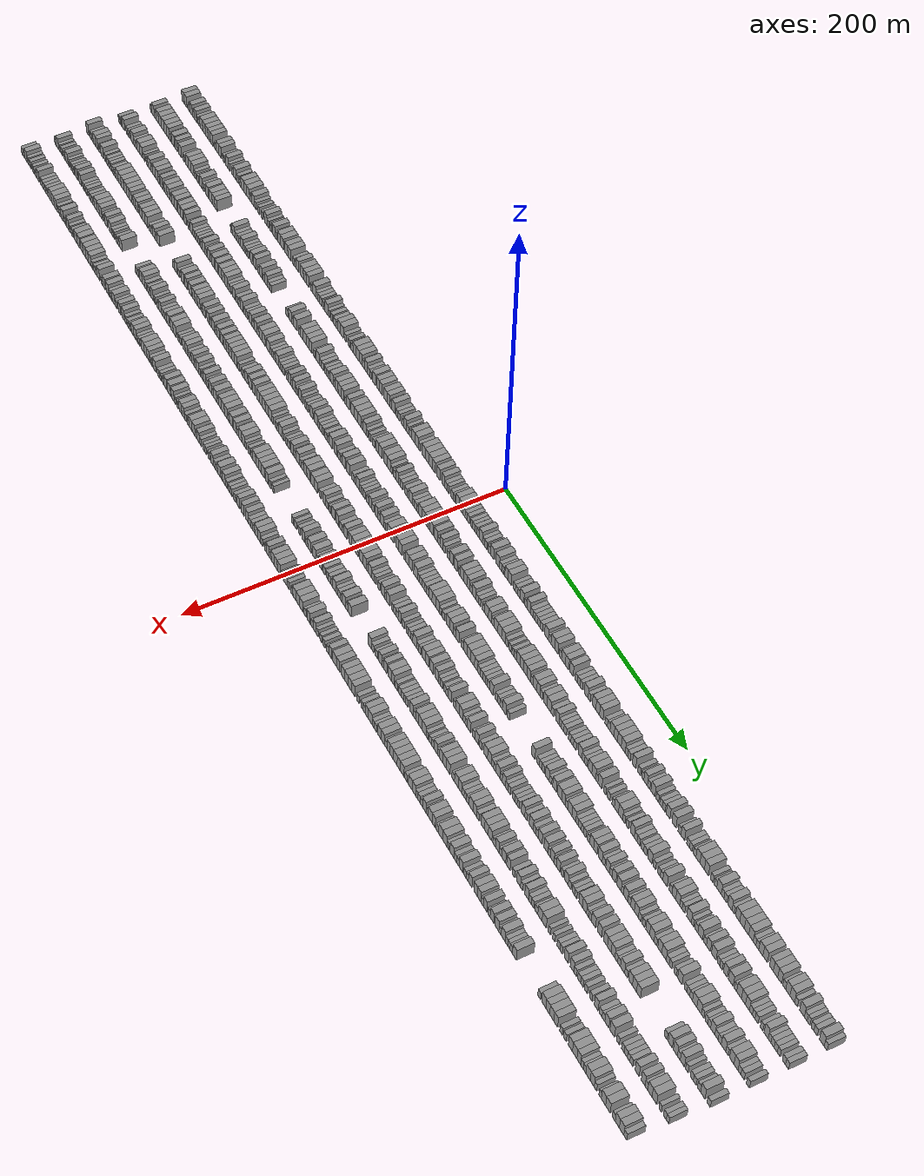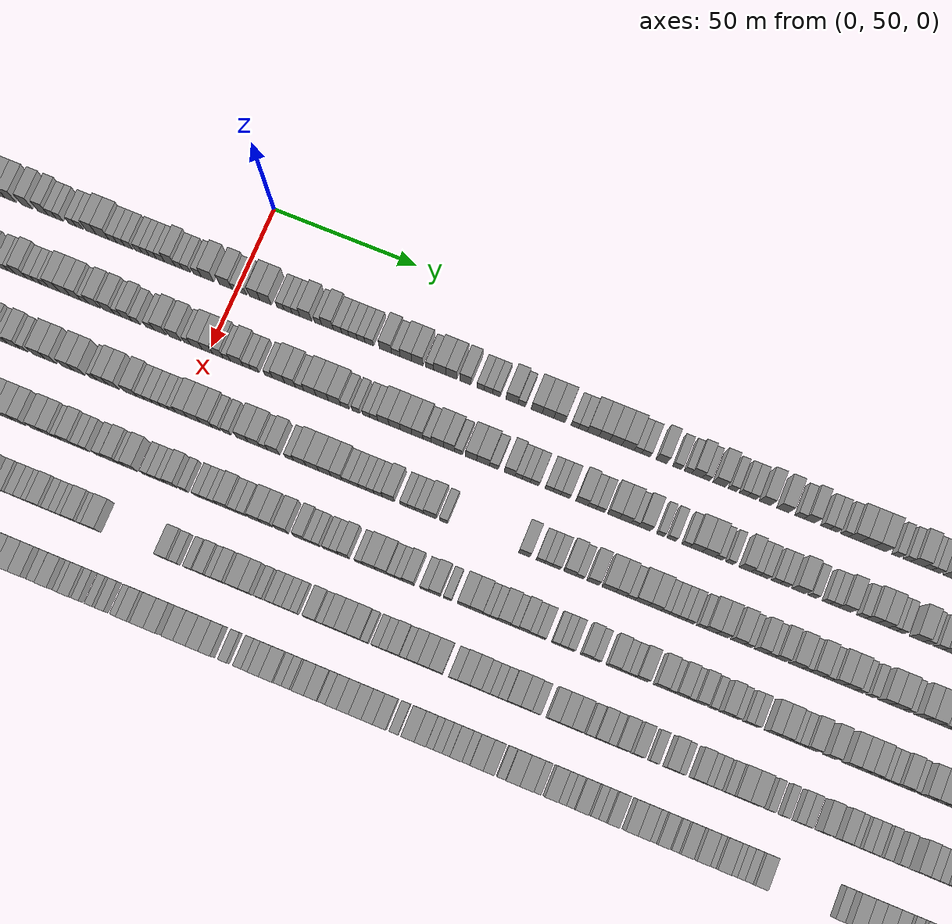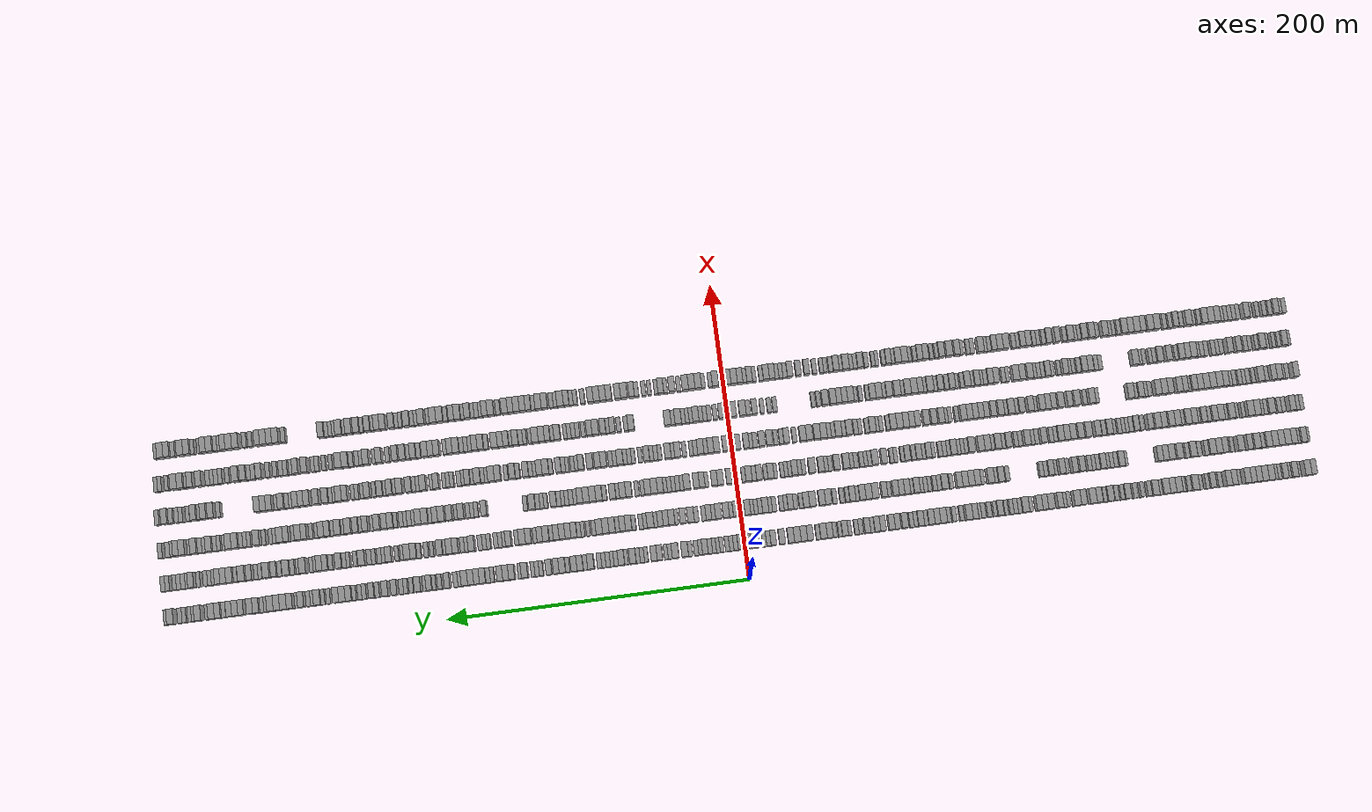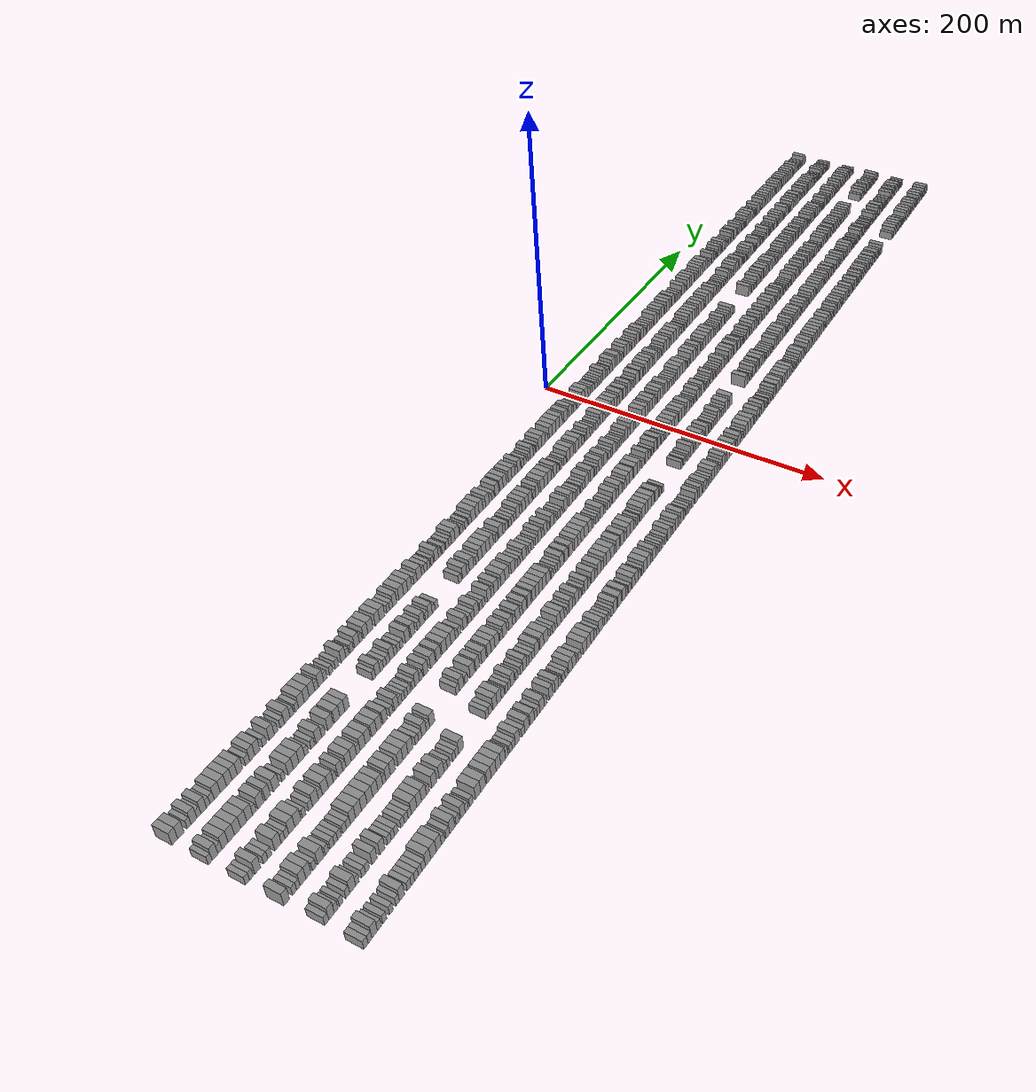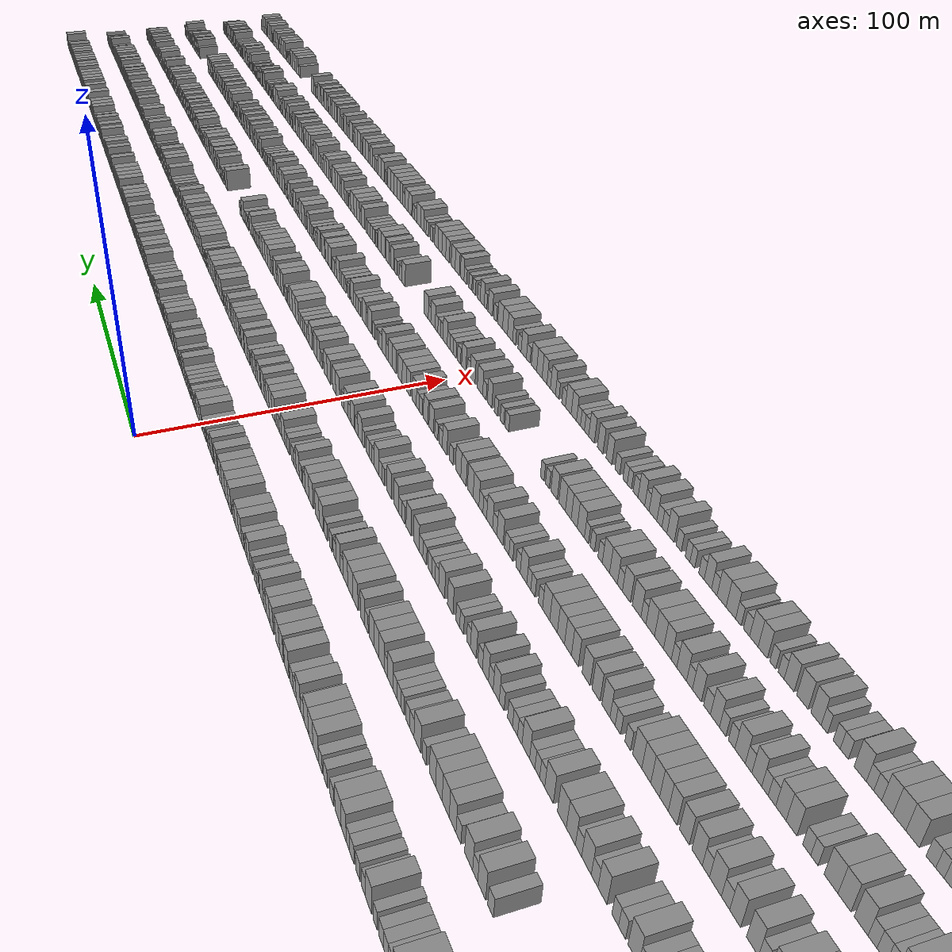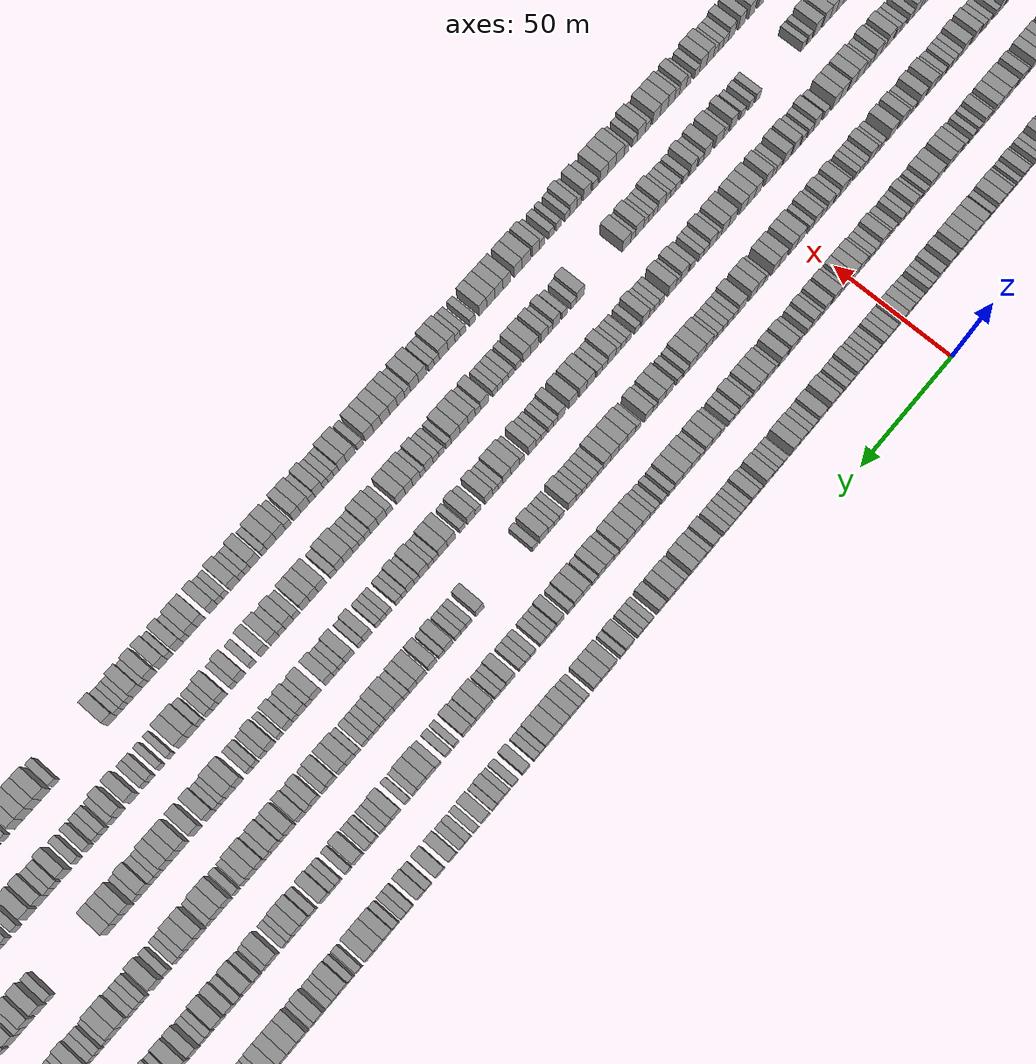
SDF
<sdf version="1.6">
 <world name="default">
  <scene>
   <sky><clouds><speed>12</speed></clouds></sky>
   <ambient>0.4 0.4 0.4 1</ambient>
   <background>0.7 0.7 0.7 1</background>
   <shadows>1</shadows>
  </scene>
  <gravity>0 0 -9.8066</gravity>
  <magnetic_field>6e-06 2.3e-05 -4.2e-05</magnetic_field>
  <physics default="0" name="default_physics" type="ode">
   <ode>
    <solver>
     <type>quick</type>
     <iters>10</iters>
     <sor>1.0</sor>
     <use_dynamic_moi_rescaling>0</use_dynamic_moi_rescaling>
    </solver>
    <constraints>
     <cfm>0</cfm>
     <erp>0.2</erp>
     <contact_max_correcting_vel>100</contact_max_correcting_vel>
     <contact_surface_layer>0.001</contact_surface_layer>
    </constraints>
   </ode>
   <max_step_size>0.004</max_step_size>
   <real_time_factor>1</real_time_factor>
   <real_time_update_rate>250</real_time_update_rate>
  </physics>
  <light name="sun" type="directional">
   <pose>0 0 10 0 0 0</pose>
   <diffuse>0.8 0.8 0.8 1</diffuse>
   <specular>0.2 0.2 0.2 1</specular>
   <attenuation>
    <range>1000</range>
    <constant>0.9</constant>
    <linear>0.01</linear>
    <quadratic>0.001</quadratic>
   </attenuation>
   <direction>-0.5 0.1 -0.9</direction>
  </light>
  <model name="building_1">
   <static>1</static>
   <pose>25.0000 -378.1393 0 0.000000 0.000000 0.000000</pose>
   <link name="link">
    <pose>0 0 4.50 0 0 0</pose>
    <collision name="collision"><geometry><box><size>10.0000 3.7215 9.0000</size></box></geometry></collision>
    <visual name="visual">
     <cast_shadows>0</cast_shadows>
     <geometry><box><size>10.0000 3.7215 9.0000</size></box></geometry>
     <material>
      <script>
       <uri>model://grey_wall/materials/scripts</uri>
       <uri>model://grey_wall/materials/textures</uri>
       <name>vrc/grey_wall</name>
      </script>
     </material>
    </visual>
   </link>
  </model>
  <model name="building_2">
   <static>1</static>
   <pose>25.0000 -374.2203 0 0.000000 0.000000 0.000000</pose>
   <link name="link">
    <pose>0 0 4.50 0 0 0</pose>
    <collision name="collision"><geometry><box><size>10.0000 4.1165 9.0000</size></box></geometry></collision>
    <visual name="visual">
     <cast_shadows>0</cast_shadows>
     <geometry><box><size>10.0000 4.1165 9.0000</size></box></geometry>
     <material>
      <script>
       <uri>model://grey_wall/materials/scripts</uri>
       <uri>model://grey_wall/materials/textures</uri>
       <name>vrc/grey_wall</name>
      </script>
     </material>
    </visual>
   </link>
  </model>
  <model name="building_3">
   <static>1</static>
   <pose>25.0000 -368.8714 0 0.000000 0.000000 0.000000</pose>
   <link name="link">
    <pose>0 0 3.00 0 0 0</pose>
    <collision name="collision"><geometry><box><size>10.0000 2.5812 6.0000</size></box></geometry></collision>
    <visual name="visual">
     <cast_shadows>0</cast_shadows>
     <geometry><box><size>10.0000 2.5812 6.0000</size></box></geometry>
     <material>
      <script>
       <uri>model://grey_wall/materials/scripts</uri>
       <uri>model://grey_wall/materials/textures</uri>
       <name>vrc/grey_wall</name>
      </script>
     </material>
    </visual>
   </link>
  </model>
  <model name="building_4">
   <static>1</static>
   <pose>25.0000 -365.6456 0 0.000000 0.000000 0.000000</pose>
   <link name="link">
    <pose>0 0 4.50 0 0 0</pose>
    <collision name="collision"><geometry><box><size>10.0000 3.8705 9.0000</size></box></geometry></collision>
    <visual name="visual">
     <cast_shadows>0</cast_shadows>
     <geometry><box><size>10.0000 3.8705 9.0000</size></box></geometry>
     <material>
      <script>
       <uri>model://grey_wall/materials/scripts</uri>
       <uri>model://grey_wall/materials/textures</uri>
       <name>vrc/grey_wall</name>
      </script>
     </material>
    </visual>
   </link>
  </model>
  <model name="building_5">
   <static>1</static>
   <pose>25.0000 -362.3687 0 0.000000 0.000000 0.000000</pose>
   <link name="link">
    <pose>0 0 3.00 0 0 0</pose>
    <collision name="collision"><geometry><box><size>10.0000 2.6834 6.0000</size></box></geometry></collision>
    <visual name="visual">
     <cast_shadows>0</cast_shadows>
     <geometry><box><size>10.0000 2.6834 6.0000</size></box></geometry>
     <material>
      <script>
       <uri>model://grey_wall/materials/scripts</uri>
       <uri>model://grey_wall/materials/textures</uri>
       <name>vrc/grey_wall</name>
      </script>
     </material>
    </visual>
   </link>
  </model>
  <model name="building_6">
   <static>1</static>
   <pose>25.0000 -359.1534 0 0.000000 0.000000 0.000000</pose>
   <link name="link">
    <pose>0 0 4.50 0 0 0</pose>
    <collision name="collision"><geometry><box><size>10.0000 3.7471 9.0000</size></box></geometry></collision>
    <visual name="visual">
     <cast_shadows>0</cast_shadows>
     <geometry><box><size>10.0000 3.7471 9.0000</size></box></geometry>
     <material>
      <script>
       <uri>model://grey_wall/materials/scripts</uri>
       <uri>model://grey_wall/materials/textures</uri>
       <name>vrc/grey_wall</name>
      </script>
     </material>
    </visual>
   </link>
  </model>
  <model name="building_7">
   <static>1</static>
   <pose>25.0000 -356.0795 0 0.000000 0.000000 0.000000</pose>
   <link name="link">
    <pose>0 0 3.00 0 0 0</pose>
    <collision name="collision"><geometry><box><size>10.0000 2.4009 6.0000</size></box></geometry></collision>
    <visual name="visual">
     <cast_shadows>0</cast_shadows>
     <geometry><box><size>10.0000 2.4009 6.0000</size></box></geometry>
     <material>
      <script>
       <uri>model://grey_wall/materials/scripts</uri>
       <uri>model://grey_wall/materials/textures</uri>
       <name>vrc/grey_wall</name>
      </script>
     </material>
    </visual>
   </link>
  </model>
  <model name="building_8">
   <static>1</static>
   <pose>25.0000 -353.4685 0 0.000000 0.000000 0.000000</pose>
   <link name="link">
    <pose>0 0 3.00 0 0 0</pose>
    <collision name="collision"><geometry><box><size>10.0000 2.8210 6.0000</size></box></geometry></collision>
    <visual name="visual">
     <cast_shadows>0</cast_shadows>
     <geometry><box><size>10.0000 2.8210 6.0000</size></box></geometry>
     <material>
      <script>
       <uri>model://grey_wall/materials/scripts</uri>
       <uri>model://grey_wall/materials/textures</uri>
       <name>vrc/grey_wall</name>
      </script>
     </material>
    </visual>
   </link>
  </model>
  <model name="building_9">
   <static>1</static>
   <pose>25.0000 -349.9385 0 0.000000 0.000000 0.000000</pose>
   <link name="link">
    <pose>0 0 4.50 0 0 0</pose>
    <collision name="collision"><geometry><box><size>10.0000 4.2390 9.0000</size></box></geometry></collision>
    <visual name="visual">
     <cast_shadows>0</cast_shadows>
     <geometry><box><size>10.0000 4.2390 9.0000</size></box></geometry>
     <material>
      <script>
       <uri>model://grey_wall/materials/scripts</uri>
       <uri>model://grey_wall/materials/textures</uri>
       <name>vrc/grey_wall</name>
      </script>
     </material>
    </visual>
   </link>
  </model>
  <model name="building_10">
   <static>1</static>
   <pose>25.0000 -345.7279 0 0.000000 0.000000 0.000000</pose>
   <link name="link">
    <pose>0 0 4.50 0 0 0</pose>
    <collision name="collision"><geometry><box><size>10.0000 4.1822 9.0000</size></box></geometry></collision>
    <visual name="visual">
     <cast_shadows>0</cast_shadows>
     <geometry><box><size>10.0000 4.1822 9.0000</size></box></geometry>
     <material>
      <script>
       <uri>model://grey_wall/materials/scripts</uri>
       <uri>model://grey_wall/materials/textures</uri>
       <name>vrc/grey_wall</name>
      </script>
     </material>
    </visual>
   </link>
  </model>
  <model name="building_11">
   <static>1</static>
   <pose>25.0000 -341.6991 0 0.000000 0.000000 0.000000</pose>
   <link name="link">
    <pose>0 0 4.50 0 0 0</pose>
    <collision name="collision"><geometry><box><size>10.0000 3.8754 9.0000</size></box></geometry></collision>
    <visual name="visual">
     <cast_shadows>0</cast_shadows>
     <geometry><box><size>10.0000 3.8754 9.0000</size></box></geometry>
     <material>
      <script>
       <uri>model://grey_wall/materials/scripts</uri>
       <uri>model://grey_wall/materials/textures</uri>
       <name>vrc/grey_wall</name>
      </script>
     </material>
    </visual>
   </link>
  </model>
  <model name="building_12">
   <static>1</static>
   <pose>25.0000 -337.9182 0 0.000000 0.000000 0.000000</pose>
   <link name="link">
    <pose>0 0 4.50 0 0 0</pose>
    <collision name="collision"><geometry><box><size>10.0000 3.6864 9.0000</size></box></geometry></collision>
    <visual name="visual">
     <cast_shadows>0</cast_shadows>
     <geometry><box><size>10.0000 3.6864 9.0000</size></box></geometry>
     <material>
      <script>
       <uri>model://grey_wall/materials/scripts</uri>
       <uri>model://grey_wall/materials/textures</uri>
       <name>vrc/grey_wall</name>
      </script>
     </material>
    </visual>
   </link>
  </model>
  <model name="building_13">
   <static>1</static>
   <pose>25.0000 -334.0940 0 0.000000 0.000000 0.000000</pose>
   <link name="link">
    <pose>0 0 4.50 0 0 0</pose>
    <collision name="collision"><geometry><box><size>10.0000 3.9620 9.0000</size></box></geometry></collision>
    <visual name="visual">
     <cast_shadows>0</cast_shadows>
     <geometry><box><size>10.0000 3.9620 9.0000</size></box></geometry>
     <material>
      <script>
       <uri>model://grey_wall/materials/scripts</uri>
       <uri>model://grey_wall/materials/textures</uri>
       <name>vrc/grey_wall</name>
      </script>
     </material>
    </visual>
   </link>
  </model>
  <model name="building_14">
   <static>1</static>
   <pose>25.0000 -328.6268 0 0.000000 0.000000 0.000000</pose>
   <link name="link">
    <pose>0 0 3.00 0 0 0</pose>
    <collision name="collision"><geometry><box><size>10.0000 2.9724 6.0000</size></box></geometry></collision>
    <visual name="visual">
     <cast_shadows>0</cast_shadows>
     <geometry><box><size>10.0000 2.9724 6.0000</size></box></geometry>
     <material>
      <script>
       <uri>model://grey_wall/materials/scripts</uri>
       <uri>model://grey_wall/materials/textures</uri>
       <name>vrc/grey_wall</name>
      </script>
     </material>
    </visual>
   </link>
  </model>
  <model name="building_15">
   <static>1</static>
   <pose>25.0000 -325.2770 0 0.000000 0.000000 0.000000</pose>
   <link name="link">
    <pose>0 0 4.50 0 0 0</pose>
    <collision name="collision"><geometry><box><size>10.0000 3.7271 9.0000</size></box></geometry></collision>
    <visual name="visual">
     <cast_shadows>0</cast_shadows>
     <geometry><box><size>10.0000 3.7271 9.0000</size></box></geometry>
     <material>
      <script>
       <uri>model://grey_wall/materials/scripts</uri>
       <uri>model://grey_wall/materials/textures</uri>
       <name>vrc/grey_wall</name>
      </script>
     </material>
    </visual>
   </link>
  </model>
  <model name="building_16">
   <static>1</static>
   <pose>25.0000 -321.5112 0 0.000000 0.000000 0.000000</pose>
   <link name="link">
    <pose>0 0 4.50 0 0 0</pose>
    <collision name="collision"><geometry><box><size>10.0000 3.8046 9.0000</size></box></geometry></collision>
    <visual name="visual">
     <cast_shadows>0</cast_shadows>
     <geometry><box><size>10.0000 3.8046 9.0000</size></box></geometry>
     <material>
      <script>
       <uri>model://grey_wall/materials/scripts</uri>
       <uri>model://grey_wall/materials/textures</uri>
       <name>vrc/grey_wall</name>
      </script>
     </material>
    </visual>
   </link>
  </model>
  <model name="building_17">
   <static>1</static>
   <pose>25.0000 -316.2441 0 0.000000 0.000000 0.000000</pose>
   <link name="link">
    <pose>0 0 3.00 0 0 0</pose>
    <collision name="collision"><geometry><box><size>10.0000 2.7297 6.0000</size></box></geometry></collision>
    <visual name="visual">
     <cast_shadows>0</cast_shadows>
     <geometry><box><size>10.0000 2.7297 6.0000</size></box></geometry>
     <material>
      <script>
       <uri>model://grey_wall/materials/scripts</uri>
       <uri>model://grey_wall/materials/textures</uri>
       <name>vrc/grey_wall</name>
      </script>
     </material>
    </visual>
   </link>
  </model>
  <model name="building_18">
   <static>1</static>
   <pose>25.0000 -310.9399 0 0.000000 0.000000 0.000000</pose>
   <link name="link">
    <pose>0 0 4.50 0 0 0</pose>
    <collision name="collision"><geometry><box><size>10.0000 3.8786 9.0000</size></box></geometry></collision>
    <visual name="visual">
     <cast_shadows>0</cast_shadows>
     <geometry><box><size>10.0000 3.8786 9.0000</size></box></geometry>
     <material>
      <script>
       <uri>model://grey_wall/materials/scripts</uri>
       <uri>model://grey_wall/materials/textures</uri>
       <name>vrc/grey_wall</name>
      </script>
     </material>
    </visual>
   </link>
  </model>
  <model name="building_19">
   <static>1</static>
   <pose>25.0000 -307.7134 0 0.000000 0.000000 0.000000</pose>
   <link name="link">
    <pose>0 0 3.00 0 0 0</pose>
    <collision name="collision"><geometry><box><size>10.0000 2.5743 6.0000</size></box></geometry></collision>
    <visual name="visual">
     <cast_shadows>0</cast_shadows>
     <geometry><box><size>10.0000 2.5743 6.0000</size></box></geometry>
     <material>
      <script>
       <uri>model://grey_wall/materials/scripts</uri>
       <uri>model://grey_wall/materials/textures</uri>
       <name>vrc/grey_wall</name>
      </script>
     </material>
    </visual>
   </link>
  </model>
  <model name="building_20">
   <static>1</static>
   <pose>25.0000 -302.9350 0 0.000000 0.000000 0.000000</pose>
   <link name="link">
    <pose>0 0 3.00 0 0 0</pose>
    <collision name="collision"><geometry><box><size>10.0000 2.9827 6.0000</size></box></geometry></collision>
    <visual name="visual">
     <cast_shadows>0</cast_shadows>
     <geometry><box><size>10.0000 2.9827 6.0000</size></box></geometry>
     <material>
      <script>
       <uri>model://grey_wall/materials/scripts</uri>
       <uri>model://grey_wall/materials/textures</uri>
       <name>vrc/grey_wall</name>
      </script>
     </material>
    </visual>
   </link>
  </model>
  <model name="building_21">
   <static>1</static>
   <pose>25.0000 -299.2488 0 0.000000 0.000000 0.000000</pose>
   <link name="link">
    <pose>0 0 4.50 0 0 0</pose>
    <collision name="collision"><geometry><box><size>10.0000 4.3897 9.0000</size></box></geometry></collision>
    <visual name="visual">
     <cast_shadows>0</cast_shadows>
     <geometry><box><size>10.0000 4.3897 9.0000</size></box></geometry>
     <material>
      <script>
       <uri>model://grey_wall/materials/scripts</uri>
       <uri>model://grey_wall/materials/textures</uri>
       <name>vrc/grey_wall</name>
      </script>
     </material>
    </visual>
   </link>
  </model>
  <model name="building_22">
   <static>1</static>
   <pose>25.0000 -295.6107 0 0.000000 0.000000 0.000000</pose>
   <link name="link">
    <pose>0 0 3.00 0 0 0</pose>
    <collision name="collision"><geometry><box><size>10.0000 2.8864 6.0000</size></box></geometry></collision>
    <visual name="visual">
     <cast_shadows>0</cast_shadows>
     <geometry><box><size>10.0000 2.8864 6.0000</size></box></geometry>
     <material>
      <script>
       <uri>model://grey_wall/materials/scripts</uri>
       <uri>model://grey_wall/materials/textures</uri>
       <name>vrc/grey_wall</name>
      </script>
     </material>
    </visual>
   </link>
  </model>
  <model name="building_23">
   <static>1</static>
   <pose>25.0000 -291.7678 0 0.000000 0.000000 0.000000</pose>
   <link name="link">
    <pose>0 0 3.00 0 0 0</pose>
    <collision name="collision"><geometry><box><size>10.0000 2.7995 6.0000</size></box></geometry></collision>
    <visual name="visual">
     <cast_shadows>0</cast_shadows>
     <geometry><box><size>10.0000 2.7995 6.0000</size></box></geometry>
     <material>
      <script>
       <uri>model://grey_wall/materials/scripts</uri>
       <uri>model://grey_wall/materials/textures</uri>
       <name>vrc/grey_wall</name>
      </script>
     </material>
    </visual>
   </link>
  </model>
  <model name="building_24">
   <static>1</static>
   <pose>25.0000 -288.2335 0 0.000000 0.000000 0.000000</pose>
   <link name="link">
    <pose>0 0 4.50 0 0 0</pose>
    <collision name="collision"><geometry><box><size>10.0000 4.2691 9.0000</size></box></geometry></collision>
    <visual name="visual">
     <cast_shadows>0</cast_shadows>
     <geometry><box><size>10.0000 4.2691 9.0000</size></box></geometry>
     <material>
      <script>
       <uri>model://grey_wall/materials/scripts</uri>
       <uri>model://grey_wall/materials/textures</uri>
       <name>vrc/grey_wall</name>
      </script>
     </material>
    </visual>
   </link>
  </model>
  <model name="building_25">
   <static>1</static>
   <pose>25.0000 -284.0608 0 0.000000 0.000000 0.000000</pose>
   <link name="link">
    <pose>0 0 4.50 0 0 0</pose>
    <collision name="collision"><geometry><box><size>10.0000 4.0762 9.0000</size></box></geometry></collision>
    <visual name="visual">
     <cast_shadows>0</cast_shadows>
     <geometry><box><size>10.0000 4.0762 9.0000</size></box></geometry>
     <material>
      <script>
       <uri>model://grey_wall/materials/scripts</uri>
       <uri>model://grey_wall/materials/textures</uri>
       <name>vrc/grey_wall</name>
      </script>
     </material>
    </visual>
   </link>
  </model>
  <model name="building_26">
   <static>1</static>
   <pose>25.0000 -279.8087 0 0.000000 0.000000 0.000000</pose>
   <link name="link">
    <pose>0 0 4.50 0 0 0</pose>
    <collision name="collision"><geometry><box><size>10.0000 4.4280 9.0000</size></box></geometry></collision>
    <visual name="visual">
     <cast_shadows>0</cast_shadows>
     <geometry><box><size>10.0000 4.4280 9.0000</size></box></geometry>
     <material>
      <script>
       <uri>model://grey_wall/materials/scripts</uri>
       <uri>model://grey_wall/materials/textures</uri>
       <name>vrc/grey_wall</name>
      </script>
     </material>
    </visual>
   </link>
  </model>
  <model name="building_27">
   <static>1</static>
   <pose>25.0000 -276.2151 0 0.000000 0.000000 0.000000</pose>
   <link name="link">
    <pose>0 0 3.00 0 0 0</pose>
    <collision name="collision"><geometry><box><size>10.0000 2.7592 6.0000</size></box></geometry></collision>
    <visual name="visual">
     <cast_shadows>0</cast_shadows>
     <geometry><box><size>10.0000 2.7592 6.0000</size></box></geometry>
     <material>
      <script>
       <uri>model://grey_wall/materials/scripts</uri>
       <uri>model://grey_wall/materials/textures</uri>
       <name>vrc/grey_wall</name>
      </script>
     </material>
    </visual>
   </link>
  </model>
  <model name="building_28">
   <static>1</static>
   <pose>25.0000 -272.6816 0 0.000000 0.000000 0.000000</pose>
   <link name="link">
    <pose>0 0 4.50 0 0 0</pose>
    <collision name="collision"><geometry><box><size>10.0000 4.3078 9.0000</size></box></geometry></collision>
    <visual name="visual">
     <cast_shadows>0</cast_shadows>
     <geometry><box><size>10.0000 4.3078 9.0000</size></box></geometry>
     <material>
      <script>
       <uri>model://grey_wall/materials/scripts</uri>
       <uri>model://grey_wall/materials/textures</uri>
       <name>vrc/grey_wall</name>
      </script>
     </material>
    </visual>
   </link>
  </model>
  <model name="building_29">
   <static>1</static>
   <pose>25.0000 -269.1227 0 0.000000 0.000000 0.000000</pose>
   <link name="link">
    <pose>0 0 3.00 0 0 0</pose>
    <collision name="collision"><geometry><box><size>10.0000 2.8099 6.0000</size></box></geometry></collision>
    <visual name="visual">
     <cast_shadows>0</cast_shadows>
     <geometry><box><size>10.0000 2.8099 6.0000</size></box></geometry>
     <material>
      <script>
       <uri>model://grey_wall/materials/scripts</uri>
       <uri>model://grey_wall/materials/textures</uri>
       <name>vrc/grey_wall</name>
      </script>
     </material>
    </visual>
   </link>
  </model>
  <model name="building_30">
   <static>1</static>
   <pose>25.0000 -264.4025 0 0.000000 0.000000 0.000000</pose>
   <link name="link">
    <pose>0 0 3.00 0 0 0</pose>
    <collision name="collision"><geometry><box><size>10.0000 2.6304 6.0000</size></box></geometry></collision>
    <visual name="visual">
     <cast_shadows>0</cast_shadows>
     <geometry><box><size>10.0000 2.6304 6.0000</size></box></geometry>
     <material>
      <script>
       <uri>model://grey_wall/materials/scripts</uri>
       <uri>model://grey_wall/materials/textures</uri>
       <name>vrc/grey_wall</name>
      </script>
     </material>
    </visual>
   </link>
  </model>
  <model name="building_31">
   <static>1</static>
   <pose>25.0000 -259.6465 0 0.000000 0.000000 0.000000</pose>
   <link name="link">
    <pose>0 0 3.00 0 0 0</pose>
    <collision name="collision"><geometry><box><size>10.0000 2.8817 6.0000</size></box></geometry></collision>
    <visual name="visual">
     <cast_shadows>0</cast_shadows>
     <geometry><box><size>10.0000 2.8817 6.0000</size></box></geometry>
     <material>
      <script>
       <uri>model://grey_wall/materials/scripts</uri>
       <uri>model://grey_wall/materials/textures</uri>
       <name>vrc/grey_wall</name>
      </script>
     </material>
    </visual>
   </link>
  </model>
  <model name="building_32">
   <static>1</static>
   <pose>25.0000 -254.2208 0 0.000000 0.000000 0.000000</pose>
   <link name="link">
    <pose>0 0 4.50 0 0 0</pose>
    <collision name="collision"><geometry><box><size>10.0000 3.9698 9.0000</size></box></geometry></collision>
    <visual name="visual">
     <cast_shadows>0</cast_shadows>
     <geometry><box><size>10.0000 3.9698 9.0000</size></box></geometry>
     <material>
      <script>
       <uri>model://grey_wall/materials/scripts</uri>
       <uri>model://grey_wall/materials/textures</uri>
       <name>vrc/grey_wall</name>
      </script>
     </material>
    </visual>
   </link>
  </model>
  <model name="building_33">
   <static>1</static>
   <pose>25.0000 -250.9463 0 0.000000 0.000000 0.000000</pose>
   <link name="link">
    <pose>0 0 3.00 0 0 0</pose>
    <collision name="collision"><geometry><box><size>10.0000 2.5792 6.0000</size></box></geometry></collision>
    <visual name="visual">
     <cast_shadows>0</cast_shadows>
     <geometry><box><size>10.0000 2.5792 6.0000</size></box></geometry>
     <material>
      <script>
       <uri>model://grey_wall/materials/scripts</uri>
       <uri>model://grey_wall/materials/textures</uri>
       <name>vrc/grey_wall</name>
      </script>
     </material>
    </visual>
   </link>
  </model>
  <model name="building_34">
   <static>1</static>
   <pose>25.0000 -247.2050 0 0.000000 0.000000 0.000000</pose>
   <link name="link">
    <pose>0 0 3.00 0 0 0</pose>
    <collision name="collision"><geometry><box><size>10.0000 2.9035 6.0000</size></box></geometry></collision>
    <visual name="visual">
     <cast_shadows>0</cast_shadows>
     <geometry><box><size>10.0000 2.9035 6.0000</size></box></geometry>
     <material>
      <script>
       <uri>model://grey_wall/materials/scripts</uri>
       <uri>model://grey_wall/materials/textures</uri>
       <name>vrc/grey_wall</name>
      </script>
     </material>
    </visual>
   </link>
  </model>
  <model name="building_35">
   <static>1</static>
   <pose>25.0000 -242.6884 0 0.000000 0.000000 0.000000</pose>
   <link name="link">
    <pose>0 0 4.50 0 0 0</pose>
    <collision name="collision"><geometry><box><size>10.0000 4.1297 9.0000</size></box></geometry></collision>
    <visual name="visual">
     <cast_shadows>0</cast_shadows>
     <geometry><box><size>10.0000 4.1297 9.0000</size></box></geometry>
     <material>
      <script>
       <uri>model://grey_wall/materials/scripts</uri>
       <uri>model://grey_wall/materials/textures</uri>
       <name>vrc/grey_wall</name>
      </script>
     </material>
    </visual>
   </link>
  </model>
  <model name="building_36">
   <static>1</static>
   <pose>25.0000 -239.3591 0 0.000000 0.000000 0.000000</pose>
   <link name="link">
    <pose>0 0 3.00 0 0 0</pose>
    <collision name="collision"><geometry><box><size>10.0000 2.5288 6.0000</size></box></geometry></collision>
    <visual name="visual">
     <cast_shadows>0</cast_shadows>
     <geometry><box><size>10.0000 2.5288 6.0000</size></box></geometry>
     <material>
      <script>
       <uri>model://grey_wall/materials/scripts</uri>
       <uri>model://grey_wall/materials/textures</uri>
       <name>vrc/grey_wall</name>
      </script>
     </material>
    </visual>
   </link>
  </model>
  <model name="building_37">
   <static>1</static>
   <pose>25.0000 -235.1338 0 0.000000 0.000000 0.000000</pose>
   <link name="link">
    <pose>0 0 4.50 0 0 0</pose>
    <collision name="collision"><geometry><box><size>10.0000 3.9217 9.0000</size></box></geometry></collision>
    <visual name="visual">
     <cast_shadows>0</cast_shadows>
     <geometry><box><size>10.0000 3.9217 9.0000</size></box></geometry>
     <material>
      <script>
       <uri>model://grey_wall/materials/scripts</uri>
       <uri>model://grey_wall/materials/textures</uri>
       <name>vrc/grey_wall</name>
      </script>
     </material>
    </visual>
   </link>
  </model>
  <model name="building_38">
   <static>1</static>
   <pose>25.0000 -230.9459 0 0.000000 0.000000 0.000000</pose>
   <link name="link">
    <pose>0 0 4.50 0 0 0</pose>
    <collision name="collision"><geometry><box><size>10.0000 4.4541 9.0000</size></box></geometry></collision>
    <visual name="visual">
     <cast_shadows>0</cast_shadows>
     <geometry><box><size>10.0000 4.4541 9.0000</size></box></geometry>
     <material>
      <script>
       <uri>model://grey_wall/materials/scripts</uri>
       <uri>model://grey_wall/materials/textures</uri>
       <name>vrc/grey_wall</name>
      </script>
     </material>
    </visual>
   </link>
  </model>
  <model name="building_39">
   <static>1</static>
   <pose>25.0000 -224.7282 0 0.000000 0.000000 0.000000</pose>
   <link name="link">
    <pose>0 0 4.50 0 0 0</pose>
    <collision name="collision"><geometry><box><size>10.0000 3.9813 9.0000</size></box></geometry></collision>
    <visual name="visual">
     <cast_shadows>0</cast_shadows>
     <geometry><box><size>10.0000 3.9813 9.0000</size></box></geometry>
     <material>
      <script>
       <uri>model://grey_wall/materials/scripts</uri>
       <uri>model://grey_wall/materials/textures</uri>
       <name>vrc/grey_wall</name>
      </script>
     </material>
    </visual>
   </link>
  </model>
  <model name="building_40">
   <static>1</static>
   <pose>25.0000 -220.5178 0 0.000000 0.000000 0.000000</pose>
   <link name="link">
    <pose>0 0 4.50 0 0 0</pose>
    <collision name="collision"><geometry><box><size>10.0000 4.4395 9.0000</size></box></geometry></collision>
    <visual name="visual">
     <cast_shadows>0</cast_shadows>
     <geometry><box><size>10.0000 4.4395 9.0000</size></box></geometry>
     <material>
      <script>
       <uri>model://grey_wall/materials/scripts</uri>
       <uri>model://grey_wall/materials/textures</uri>
       <name>vrc/grey_wall</name>
      </script>
     </material>
    </visual>
   </link>
  </model>
  <model name="building_41">
   <static>1</static>
   <pose>25.0000 -215.0652 0 0.000000 0.000000 0.000000</pose>
   <link name="link">
    <pose>0 0 3.00 0 0 0</pose>
    <collision name="collision"><geometry><box><size>10.0000 2.4658 6.0000</size></box></geometry></collision>
    <visual name="visual">
     <cast_shadows>0</cast_shadows>
     <geometry><box><size>10.0000 2.4658 6.0000</size></box></geometry>
     <material>
      <script>
       <uri>model://grey_wall/materials/scripts</uri>
       <uri>model://grey_wall/materials/textures</uri>
       <name>vrc/grey_wall</name>
      </script>
     </material>
    </visual>
   </link>
  </model>
  <model name="building_42">
   <static>1</static>
   <pose>25.0000 -212.4221 0 0.000000 0.000000 0.000000</pose>
   <link name="link">
    <pose>0 0 3.00 0 0 0</pose>
    <collision name="collision"><geometry><box><size>10.0000 2.8204 6.0000</size></box></geometry></collision>
    <visual name="visual">
     <cast_shadows>0</cast_shadows>
     <geometry><box><size>10.0000 2.8204 6.0000</size></box></geometry>
     <material>
      <script>
       <uri>model://grey_wall/materials/scripts</uri>
       <uri>model://grey_wall/materials/textures</uri>
       <name>vrc/grey_wall</name>
      </script>
     </material>
    </visual>
   </link>
  </model>
  <model name="building_43">
   <static>1</static>
   <pose>25.0000 -209.1711 0 0.000000 0.000000 0.000000</pose>
   <link name="link">
    <pose>0 0 4.50 0 0 0</pose>
    <collision name="collision"><geometry><box><size>10.0000 3.6816 9.0000</size></box></geometry></collision>
    <visual name="visual">
     <cast_shadows>0</cast_shadows>
     <geometry><box><size>10.0000 3.6816 9.0000</size></box></geometry>
     <material>
      <script>
       <uri>model://grey_wall/materials/scripts</uri>
       <uri>model://grey_wall/materials/textures</uri>
       <name>vrc/grey_wall</name>
      </script>
     </material>
    </visual>
   </link>
  </model>
  <model name="building_44">
   <static>1</static>
   <pose>25.0000 -203.0987 0 0.000000 0.000000 0.000000</pose>
   <link name="link">
    <pose>0 0 4.50 0 0 0</pose>
    <collision name="collision"><geometry><box><size>10.0000 4.4633 9.0000</size></box></geometry></collision>
    <visual name="visual">
     <cast_shadows>0</cast_shadows>
     <geometry><box><size>10.0000 4.4633 9.0000</size></box></geometry>
     <material>
      <script>
       <uri>model://grey_wall/materials/scripts</uri>
       <uri>model://grey_wall/materials/textures</uri>
       <name>vrc/grey_wall</name>
      </script>
     </material>
    </visual>
   </link>
  </model>
  <model name="building_45">
   <static>1</static>
   <pose>25.0000 -199.0176 0 0.000000 0.000000 0.000000</pose>
   <link name="link">
    <pose>0 0 4.50 0 0 0</pose>
    <collision name="collision"><geometry><box><size>10.0000 3.6988 9.0000</size></box></geometry></collision>
    <visual name="visual">
     <cast_shadows>0</cast_shadows>
     <geometry><box><size>10.0000 3.6988 9.0000</size></box></geometry>
     <material>
      <script>
       <uri>model://grey_wall/materials/scripts</uri>
       <uri>model://grey_wall/materials/textures</uri>
       <name>vrc/grey_wall</name>
      </script>
     </material>
    </visual>
   </link>
  </model>
  <model name="building_46">
   <static>1</static>
   <pose>25.0000 -195.2268 0 0.000000 0.000000 0.000000</pose>
   <link name="link">
    <pose>0 0 4.50 0 0 0</pose>
    <collision name="collision"><geometry><box><size>10.0000 3.8828 9.0000</size></box></geometry></collision>
    <visual name="visual">
     <cast_shadows>0</cast_shadows>
     <geometry><box><size>10.0000 3.8828 9.0000</size></box></geometry>
     <material>
      <script>
       <uri>model://grey_wall/materials/scripts</uri>
       <uri>model://grey_wall/materials/textures</uri>
       <name>vrc/grey_wall</name>
      </script>
     </material>
    </visual>
   </link>
  </model>
  <model name="building_47">
   <static>1</static>
   <pose>25.0000 -189.7896 0 0.000000 0.000000 0.000000</pose>
   <link name="link">
    <pose>0 0 3.00 0 0 0</pose>
    <collision name="collision"><geometry><box><size>10.0000 2.9916 6.0000</size></box></geometry></collision>
    <visual name="visual">
     <cast_shadows>0</cast_shadows>
     <geometry><box><size>10.0000 2.9916 6.0000</size></box></geometry>
     <material>
      <script>
       <uri>model://grey_wall/materials/scripts</uri>
       <uri>model://grey_wall/materials/textures</uri>
       <name>vrc/grey_wall</name>
      </script>
     </material>
    </visual>
   </link>
  </model>
  <model name="building_48">
   <static>1</static>
   <pose>25.0000 -186.0740 0 0.000000 0.000000 0.000000</pose>
   <link name="link">
    <pose>0 0 4.50 0 0 0</pose>
    <collision name="collision"><geometry><box><size>10.0000 4.4397 9.0000</size></box></geometry></collision>
    <visual name="visual">
     <cast_shadows>0</cast_shadows>
     <geometry><box><size>10.0000 4.4397 9.0000</size></box></geometry>
     <material>
      <script>
       <uri>model://grey_wall/materials/scripts</uri>
       <uri>model://grey_wall/materials/textures</uri>
       <name>vrc/grey_wall</name>
      </script>
     </material>
    </visual>
   </link>
  </model>
  <model name="building_49">
   <static>1</static>
   <pose>25.0000 -182.5660 0 0.000000 0.000000 0.000000</pose>
   <link name="link">
    <pose>0 0 3.00 0 0 0</pose>
    <collision name="collision"><geometry><box><size>10.0000 2.5763 6.0000</size></box></geometry></collision>
    <visual name="visual">
     <cast_shadows>0</cast_shadows>
     <geometry><box><size>10.0000 2.5763 6.0000</size></box></geometry>
     <material>
      <script>
       <uri>model://grey_wall/materials/scripts</uri>
       <uri>model://grey_wall/materials/textures</uri>
       <name>vrc/grey_wall</name>
      </script>
     </material>
    </visual>
   </link>
  </model>
  <model name="building_50">
   <static>1</static>
   <pose>25.0000 -179.8263 0 0.000000 0.000000 0.000000</pose>
   <link name="link">
    <pose>0 0 3.00 0 0 0</pose>
    <collision name="collision"><geometry><box><size>10.0000 2.9030 6.0000</size></box></geometry></collision>
    <visual name="visual">
     <cast_shadows>0</cast_shadows>
     <geometry><box><size>10.0000 2.9030 6.0000</size></box></geometry>
     <material>
      <script>
       <uri>model://grey_wall/materials/scripts</uri>
       <uri>model://grey_wall/materials/textures</uri>
       <name>vrc/grey_wall</name>
      </script>
     </material>
    </visual>
   </link>
  </model>
  <model name="building_51">
   <static>1</static>
   <pose>25.0000 -177.0569 0 0.000000 0.000000 0.000000</pose>
   <link name="link">
    <pose>0 0 3.00 0 0 0</pose>
    <collision name="collision"><geometry><box><size>10.0000 2.6357 6.0000</size></box></geometry></collision>
    <visual name="visual">
     <cast_shadows>0</cast_shadows>
     <geometry><box><size>10.0000 2.6357 6.0000</size></box></geometry>
     <material>
      <script>
       <uri>model://grey_wall/materials/scripts</uri>
       <uri>model://grey_wall/materials/textures</uri>
       <name>vrc/grey_wall</name>
      </script>
     </material>
    </visual>
   </link>
  </model>
  <model name="building_52">
   <static>1</static>
   <pose>25.0000 -173.5118 0 0.000000 0.000000 0.000000</pose>
   <link name="link">
    <pose>0 0 3.00 0 0 0</pose>
    <collision name="collision"><geometry><box><size>10.0000 2.4545 6.0000</size></box></geometry></collision>
    <visual name="visual">
     <cast_shadows>0</cast_shadows>
     <geometry><box><size>10.0000 2.4545 6.0000</size></box></geometry>
     <material>
      <script>
       <uri>model://grey_wall/materials/scripts</uri>
       <uri>model://grey_wall/materials/textures</uri>
       <name>vrc/grey_wall</name>
      </script>
     </material>
    </visual>
   </link>
  </model>
  <model name="building_53">
   <static>1</static>
   <pose>25.0000 -169.3284 0 0.000000 0.000000 0.000000</pose>
   <link name="link">
    <pose>0 0 4.50 0 0 0</pose>
    <collision name="collision"><geometry><box><size>10.0000 3.9124 9.0000</size></box></geometry></collision>
    <visual name="visual">
     <cast_shadows>0</cast_shadows>
     <geometry><box><size>10.0000 3.9124 9.0000</size></box></geometry>
     <material>
      <script>
       <uri>model://grey_wall/materials/scripts</uri>
       <uri>model://grey_wall/materials/textures</uri>
       <name>vrc/grey_wall</name>
      </script>
     </material>
    </visual>
   </link>
  </model>
  <model name="building_54">
   <static>1</static>
   <pose>25.0000 -166.1035 0 0.000000 0.000000 0.000000</pose>
   <link name="link">
    <pose>0 0 3.00 0 0 0</pose>
    <collision name="collision"><geometry><box><size>10.0000 2.5373 6.0000</size></box></geometry></collision>
    <visual name="visual">
     <cast_shadows>0</cast_shadows>
     <geometry><box><size>10.0000 2.5373 6.0000</size></box></geometry>
     <material>
      <script>
       <uri>model://grey_wall/materials/scripts</uri>
       <uri>model://grey_wall/materials/textures</uri>
       <name>vrc/grey_wall</name>
      </script>
     </material>
    </visual>
   </link>
  </model>
  <model name="building_55">
   <static>1</static>
   <pose>25.0000 -162.3389 0 0.000000 0.000000 0.000000</pose>
   <link name="link">
    <pose>0 0 3.00 0 0 0</pose>
    <collision name="collision"><geometry><box><size>10.0000 2.9918 6.0000</size></box></geometry></collision>
    <visual name="visual">
     <cast_shadows>0</cast_shadows>
     <geometry><box><size>10.0000 2.9918 6.0000</size></box></geometry>
     <material>
      <script>
       <uri>model://grey_wall/materials/scripts</uri>
       <uri>model://grey_wall/materials/textures</uri>
       <name>vrc/grey_wall</name>
      </script>
     </material>
    </visual>
   </link>
  </model>
  <model name="building_56">
   <static>1</static>
   <pose>25.0000 -158.3521 0 0.000000 0.000000 0.000000</pose>
   <link name="link">
    <pose>0 0 3.00 0 0 0</pose>
    <collision name="collision"><geometry><box><size>10.0000 2.9819 6.0000</size></box></geometry></collision>
    <visual name="visual">
     <cast_shadows>0</cast_shadows>
     <geometry><box><size>10.0000 2.9819 6.0000</size></box></geometry>
     <material>
      <script>
       <uri>model://grey_wall/materials/scripts</uri>
       <uri>model://grey_wall/materials/textures</uri>
       <name>vrc/grey_wall</name>
      </script>
     </material>
    </visual>
   </link>
  </model>
  <model name="building_57">
   <static>1</static>
   <pose>25.0000 -155.6301 0 0.000000 0.000000 0.000000</pose>
   <link name="link">
    <pose>0 0 3.00 0 0 0</pose>
    <collision name="collision"><geometry><box><size>10.0000 2.4621 6.0000</size></box></geometry></collision>
    <visual name="visual">
     <cast_shadows>0</cast_shadows>
     <geometry><box><size>10.0000 2.4621 6.0000</size></box></geometry>
     <material>
      <script>
       <uri>model://grey_wall/materials/scripts</uri>
       <uri>model://grey_wall/materials/textures</uri>
       <name>vrc/grey_wall</name>
      </script>
     </material>
    </visual>
   </link>
  </model>
  <model name="building_58">
   <static>1</static>
   <pose>25.0000 -152.5825 0 0.000000 0.000000 0.000000</pose>
   <link name="link">
    <pose>0 0 4.50 0 0 0</pose>
    <collision name="collision"><geometry><box><size>10.0000 3.6330 9.0000</size></box></geometry></collision>
    <visual name="visual">
     <cast_shadows>0</cast_shadows>
     <geometry><box><size>10.0000 3.6330 9.0000</size></box></geometry>
     <material>
      <script>
       <uri>model://grey_wall/materials/scripts</uri>
       <uri>model://grey_wall/materials/textures</uri>
       <name>vrc/grey_wall</name>
      </script>
     </material>
    </visual>
   </link>
  </model>
  <model name="building_59">
   <static>1</static>
   <pose>25.0000 -148.5546 0 0.000000 0.000000 0.000000</pose>
   <link name="link">
    <pose>0 0 4.50 0 0 0</pose>
    <collision name="collision"><geometry><box><size>10.0000 4.4228 9.0000</size></box></geometry></collision>
    <visual name="visual">
     <cast_shadows>0</cast_shadows>
     <geometry><box><size>10.0000 4.4228 9.0000</size></box></geometry>
     <material>
      <script>
       <uri>model://grey_wall/materials/scripts</uri>
       <uri>model://grey_wall/materials/textures</uri>
       <name>vrc/grey_wall</name>
      </script>
     </material>
    </visual>
   </link>
  </model>
  <model name="building_60">
   <static>1</static>
   <pose>25.0000 -143.9439 0 0.000000 0.000000 0.000000</pose>
   <link name="link">
    <pose>0 0 3.00 0 0 0</pose>
    <collision name="collision"><geometry><box><size>10.0000 2.7985 6.0000</size></box></geometry></collision>
    <visual name="visual">
     <cast_shadows>0</cast_shadows>
     <geometry><box><size>10.0000 2.7985 6.0000</size></box></geometry>
     <material>
      <script>
       <uri>model://grey_wall/materials/scripts</uri>
       <uri>model://grey_wall/materials/textures</uri>
       <name>vrc/grey_wall</name>
      </script>
     </material>
    </visual>
   </link>
  </model>
  <model name="building_61">
   <static>1</static>
   <pose>25.0000 -139.0902 0 0.000000 0.000000 0.000000</pose>
   <link name="link">
    <pose>0 0 3.00 0 0 0</pose>
    <collision name="collision"><geometry><box><size>10.0000 2.9089 6.0000</size></box></geometry></collision>
    <visual name="visual">
     <cast_shadows>0</cast_shadows>
     <geometry><box><size>10.0000 2.9089 6.0000</size></box></geometry>
     <material>
      <script>
       <uri>model://grey_wall/materials/scripts</uri>
       <uri>model://grey_wall/materials/textures</uri>
       <name>vrc/grey_wall</name>
      </script>
     </material>
    </visual>
   </link>
  </model>
  <model name="building_62">
   <static>1</static>
   <pose>25.0000 -135.1748 0 0.000000 0.000000 0.000000</pose>
   <link name="link">
    <pose>0 0 3.00 0 0 0</pose>
    <collision name="collision"><geometry><box><size>10.0000 2.9219 6.0000</size></box></geometry></collision>
    <visual name="visual">
     <cast_shadows>0</cast_shadows>
     <geometry><box><size>10.0000 2.9219 6.0000</size></box></geometry>
     <material>
      <script>
       <uri>model://grey_wall/materials/scripts</uri>
       <uri>model://grey_wall/materials/textures</uri>
       <name>vrc/grey_wall</name>
      </script>
     </material>
    </visual>
   </link>
  </model>
  <model name="building_63">
   <static>1</static>
   <pose>25.0000 -131.4852 0 0.000000 0.000000 0.000000</pose>
   <link name="link">
    <pose>0 0 4.50 0 0 0</pose>
    <collision name="collision"><geometry><box><size>10.0000 4.4574 9.0000</size></box></geometry></collision>
    <visual name="visual">
     <cast_shadows>0</cast_shadows>
     <geometry><box><size>10.0000 4.4574 9.0000</size></box></geometry>
     <material>
      <script>
       <uri>model://grey_wall/materials/scripts</uri>
       <uri>model://grey_wall/materials/textures</uri>
       <name>vrc/grey_wall</name>
      </script>
     </material>
    </visual>
   </link>
  </model>
  <model name="building_64">
   <static>1</static>
   <pose>25.0000 -127.3829 0 0.000000 0.000000 0.000000</pose>
   <link name="link">
    <pose>0 0 4.50 0 0 0</pose>
    <collision name="collision"><geometry><box><size>10.0000 3.7472 9.0000</size></box></geometry></collision>
    <visual name="visual">
     <cast_shadows>0</cast_shadows>
     <geometry><box><size>10.0000 3.7472 9.0000</size></box></geometry>
     <material>
      <script>
       <uri>model://grey_wall/materials/scripts</uri>
       <uri>model://grey_wall/materials/textures</uri>
       <name>vrc/grey_wall</name>
      </script>
     </material>
    </visual>
   </link>
  </model>
  <model name="building_65">
   <static>1</static>
   <pose>25.0000 -123.4933 0 0.000000 0.000000 0.000000</pose>
   <link name="link">
    <pose>0 0 4.50 0 0 0</pose>
    <collision name="collision"><geometry><box><size>10.0000 4.0320 9.0000</size></box></geometry></collision>
    <visual name="visual">
     <cast_shadows>0</cast_shadows>
     <geometry><box><size>10.0000 4.0320 9.0000</size></box></geometry>
     <material>
      <script>
       <uri>model://grey_wall/materials/scripts</uri>
       <uri>model://grey_wall/materials/textures</uri>
       <name>vrc/grey_wall</name>
      </script>
     </material>
    </visual>
   </link>
  </model>
  <model name="building_66">
   <static>1</static>
   <pose>25.0000 -120.0000 0 0.000000 0.000000 0.000000</pose>
   <link name="link">
    <pose>0 0 3.00 0 0 0</pose>
    <collision name="collision"><geometry><box><size>10.0000 2.9545 6.0000</size></box></geometry></collision>
    <visual name="visual">
     <cast_shadows>0</cast_shadows>
     <geometry><box><size>10.0000 2.9545 6.0000</size></box></geometry>
     <material>
      <script>
       <uri>model://grey_wall/materials/scripts</uri>
       <uri>model://grey_wall/materials/textures</uri>
       <name>vrc/grey_wall</name>
      </script>
     </material>
    </visual>
   </link>
  </model>
  <model name="building_67">
   <static>1</static>
   <pose>25.0000 -116.5844 0 0.000000 0.000000 0.000000</pose>
   <link name="link">
    <pose>0 0 4.50 0 0 0</pose>
    <collision name="collision"><geometry><box><size>10.0000 3.8766 9.0000</size></box></geometry></collision>
    <visual name="visual">
     <cast_shadows>0</cast_shadows>
     <geometry><box><size>10.0000 3.8766 9.0000</size></box></geometry>
     <material>
      <script>
       <uri>model://grey_wall/materials/scripts</uri>
       <uri>model://grey_wall/materials/textures</uri>
       <name>vrc/grey_wall</name>
      </script>
     </material>
    </visual>
   </link>
  </model>
  <model name="building_68">
   <static>1</static>
   <pose>25.0000 -113.3017 0 0.000000 0.000000 0.000000</pose>
   <link name="link">
    <pose>0 0 3.00 0 0 0</pose>
    <collision name="collision"><geometry><box><size>10.0000 2.6889 6.0000</size></box></geometry></collision>
    <visual name="visual">
     <cast_shadows>0</cast_shadows>
     <geometry><box><size>10.0000 2.6889 6.0000</size></box></geometry>
     <material>
      <script>
       <uri>model://grey_wall/materials/scripts</uri>
       <uri>model://grey_wall/materials/textures</uri>
       <name>vrc/grey_wall</name>
      </script>
     </material>
    </visual>
   </link>
  </model>
  <model name="building_69">
   <static>1</static>
   <pose>25.0000 -110.5269 0 0.000000 0.000000 0.000000</pose>
   <link name="link">
    <pose>0 0 3.00 0 0 0</pose>
    <collision name="collision"><geometry><box><size>10.0000 2.8607 6.0000</size></box></geometry></collision>
    <visual name="visual">
     <cast_shadows>0</cast_shadows>
     <geometry><box><size>10.0000 2.8607 6.0000</size></box></geometry>
     <material>
      <script>
       <uri>model://grey_wall/materials/scripts</uri>
       <uri>model://grey_wall/materials/textures</uri>
       <name>vrc/grey_wall</name>
      </script>
     </material>
    </visual>
   </link>
  </model>
  <model name="building_70">
   <static>1</static>
   <pose>25.0000 -106.0177 0 0.000000 0.000000 0.000000</pose>
   <link name="link">
    <pose>0 0 4.50 0 0 0</pose>
    <collision name="collision"><geometry><box><size>10.0000 4.1577 9.0000</size></box></geometry></collision>
    <visual name="visual">
     <cast_shadows>0</cast_shadows>
     <geometry><box><size>10.0000 4.1577 9.0000</size></box></geometry>
     <material>
      <script>
       <uri>model://grey_wall/materials/scripts</uri>
       <uri>model://grey_wall/materials/textures</uri>
       <name>vrc/grey_wall</name>
      </script>
     </material>
    </visual>
   </link>
  </model>
  <model name="building_71">
   <static>1</static>
   <pose>25.0000 -101.0461 0 0.000000 0.000000 0.000000</pose>
   <link name="link">
    <pose>0 0 4.50 0 0 0</pose>
    <collision name="collision"><geometry><box><size>10.0000 3.7855 9.0000</size></box></geometry></collision>
    <visual name="visual">
     <cast_shadows>0</cast_shadows>
     <geometry><box><size>10.0000 3.7855 9.0000</size></box></geometry>
     <material>
      <script>
       <uri>model://grey_wall/materials/scripts</uri>
       <uri>model://grey_wall/materials/textures</uri>
       <name>vrc/grey_wall</name>
      </script>
     </material>
    </visual>
   </link>
  </model>
  <model name="building_72">
   <static>1</static>
   <pose>25.0000 -97.1791 0 0.000000 0.000000 0.000000</pose>
   <link name="link">
    <pose>0 0 4.50 0 0 0</pose>
    <collision name="collision"><geometry><box><size>10.0000 3.9485 9.0000</size></box></geometry></collision>
    <visual name="visual">
     <cast_shadows>0</cast_shadows>
     <geometry><box><size>10.0000 3.9485 9.0000</size></box></geometry>
     <material>
      <script>
       <uri>model://grey_wall/materials/scripts</uri>
       <uri>model://grey_wall/materials/textures</uri>
       <name>vrc/grey_wall</name>
      </script>
     </material>
    </visual>
   </link>
  </model>
  <model name="building_73">
   <static>1</static>
   <pose>25.0000 -91.2980 0 0.000000 0.000000 0.000000</pose>
   <link name="link">
    <pose>0 0 4.50 0 0 0</pose>
    <collision name="collision"><geometry><box><size>10.0000 3.8136 9.0000</size></box></geometry></collision>
    <visual name="visual">
     <cast_shadows>0</cast_shadows>
     <geometry><box><size>10.0000 3.8136 9.0000</size></box></geometry>
     <material>
      <script>
       <uri>model://grey_wall/materials/scripts</uri>
       <uri>model://grey_wall/materials/textures</uri>
       <name>vrc/grey_wall</name>
      </script>
     </material>
    </visual>
   </link>
  </model>
  <model name="building_74">
   <static>1</static>
   <pose>25.0000 -87.5375 0 0.000000 0.000000 0.000000</pose>
   <link name="link">
    <pose>0 0 4.50 0 0 0</pose>
    <collision name="collision"><geometry><box><size>10.0000 3.7074 9.0000</size></box></geometry></collision>
    <visual name="visual">
     <cast_shadows>0</cast_shadows>
     <geometry><box><size>10.0000 3.7074 9.0000</size></box></geometry>
     <material>
      <script>
       <uri>model://grey_wall/materials/scripts</uri>
       <uri>model://grey_wall/materials/textures</uri>
       <name>vrc/grey_wall</name>
      </script>
     </material>
    </visual>
   </link>
  </model>
  <model name="building_75">
   <static>1</static>
   <pose>25.0000 -84.3026 0 0.000000 0.000000 0.000000</pose>
   <link name="link">
    <pose>0 0 3.00 0 0 0</pose>
    <collision name="collision"><geometry><box><size>10.0000 2.7624 6.0000</size></box></geometry></collision>
    <visual name="visual">
     <cast_shadows>0</cast_shadows>
     <geometry><box><size>10.0000 2.7624 6.0000</size></box></geometry>
     <material>
      <script>
       <uri>model://grey_wall/materials/scripts</uri>
       <uri>model://grey_wall/materials/textures</uri>
       <name>vrc/grey_wall</name>
      </script>
     </material>
    </visual>
   </link>
  </model>
  <model name="building_76">
   <static>1</static>
   <pose>25.0000 -81.0090 0 0.000000 0.000000 0.000000</pose>
   <link name="link">
    <pose>0 0 4.50 0 0 0</pose>
    <collision name="collision"><geometry><box><size>10.0000 3.8246 9.0000</size></box></geometry></collision>
    <visual name="visual">
     <cast_shadows>0</cast_shadows>
     <geometry><box><size>10.0000 3.8246 9.0000</size></box></geometry>
     <material>
      <script>
       <uri>model://grey_wall/materials/scripts</uri>
       <uri>model://grey_wall/materials/textures</uri>
       <name>vrc/grey_wall</name>
      </script>
     </material>
    </visual>
   </link>
  </model>
  <model name="building_77">
   <static>1</static>
   <pose>25.0000 -76.7319 0 0.000000 0.000000 0.000000</pose>
   <link name="link">
    <pose>0 0 3.00 0 0 0</pose>
    <collision name="collision"><geometry><box><size>10.0000 2.7297 6.0000</size></box></geometry></collision>
    <visual name="visual">
     <cast_shadows>0</cast_shadows>
     <geometry><box><size>10.0000 2.7297 6.0000</size></box></geometry>
     <material>
      <script>
       <uri>model://grey_wall/materials/scripts</uri>
       <uri>model://grey_wall/materials/textures</uri>
       <name>vrc/grey_wall</name>
      </script>
     </material>
    </visual>
   </link>
  </model>
  <model name="building_78">
   <static>1</static>
   <pose>25.0000 -74.0123 0 0.000000 0.000000 0.000000</pose>
   <link name="link">
    <pose>0 0 3.00 0 0 0</pose>
    <collision name="collision"><geometry><box><size>10.0000 2.7094 6.0000</size></box></geometry></collision>
    <visual name="visual">
     <cast_shadows>0</cast_shadows>
     <geometry><box><size>10.0000 2.7094 6.0000</size></box></geometry>
     <material>
      <script>
       <uri>model://grey_wall/materials/scripts</uri>
       <uri>model://grey_wall/materials/textures</uri>
       <name>vrc/grey_wall</name>
      </script>
     </material>
    </visual>
   </link>
  </model>
  <model name="building_79">
   <static>1</static>
   <pose>25.0000 -69.3657 0 0.000000 0.000000 0.000000</pose>
   <link name="link">
    <pose>0 0 3.00 0 0 0</pose>
    <collision name="collision"><geometry><box><size>10.0000 2.5837 6.0000</size></box></geometry></collision>
    <visual name="visual">
     <cast_shadows>0</cast_shadows>
     <geometry><box><size>10.0000 2.5837 6.0000</size></box></geometry>
     <material>
      <script>
       <uri>model://grey_wall/materials/scripts</uri>
       <uri>model://grey_wall/materials/textures</uri>
       <name>vrc/grey_wall</name>
      </script>
     </material>
    </visual>
   </link>
  </model>
  <model name="building_80">
   <static>1</static>
   <pose>25.0000 -66.1560 0 0.000000 0.000000 0.000000</pose>
   <link name="link">
    <pose>0 0 4.50 0 0 0</pose>
    <collision name="collision"><geometry><box><size>10.0000 3.8357 9.0000</size></box></geometry></collision>
    <visual name="visual">
     <cast_shadows>0</cast_shadows>
     <geometry><box><size>10.0000 3.8357 9.0000</size></box></geometry>
     <material>
      <script>
       <uri>model://grey_wall/materials/scripts</uri>
       <uri>model://grey_wall/materials/textures</uri>
       <name>vrc/grey_wall</name>
      </script>
     </material>
    </visual>
   </link>
  </model>
  <model name="building_81">
   <static>1</static>
   <pose>25.0000 -63.0343 0 0.000000 0.000000 0.000000</pose>
   <link name="link">
    <pose>0 0 3.00 0 0 0</pose>
    <collision name="collision"><geometry><box><size>10.0000 2.4078 6.0000</size></box></geometry></collision>
    <visual name="visual">
     <cast_shadows>0</cast_shadows>
     <geometry><box><size>10.0000 2.4078 6.0000</size></box></geometry>
     <material>
      <script>
       <uri>model://grey_wall/materials/scripts</uri>
       <uri>model://grey_wall/materials/textures</uri>
       <name>vrc/grey_wall</name>
      </script>
     </material>
    </visual>
   </link>
  </model>
  <model name="building_82">
   <static>1</static>
   <pose>25.0000 -59.4556 0 0.000000 0.000000 0.000000</pose>
   <link name="link">
    <pose>0 0 3.00 0 0 0</pose>
    <collision name="collision"><geometry><box><size>10.0000 2.7496 6.0000</size></box></geometry></collision>
    <visual name="visual">
     <cast_shadows>0</cast_shadows>
     <geometry><box><size>10.0000 2.7496 6.0000</size></box></geometry>
     <material>
      <script>
       <uri>model://grey_wall/materials/scripts</uri>
       <uri>model://grey_wall/materials/textures</uri>
       <name>vrc/grey_wall</name>
      </script>
     </material>
    </visual>
   </link>
  </model>
  <model name="building_83">
   <static>1</static>
   <pose>25.0000 -56.1258 0 0.000000 0.000000 0.000000</pose>
   <link name="link">
    <pose>0 0 4.50 0 0 0</pose>
    <collision name="collision"><geometry><box><size>10.0000 3.9099 9.0000</size></box></geometry></collision>
    <visual name="visual">
     <cast_shadows>0</cast_shadows>
     <geometry><box><size>10.0000 3.9099 9.0000</size></box></geometry>
     <material>
      <script>
       <uri>model://grey_wall/materials/scripts</uri>
       <uri>model://grey_wall/materials/textures</uri>
       <name>vrc/grey_wall</name>
      </script>
     </material>
    </visual>
   </link>
  </model>
  <model name="building_84">
   <static>1</static>
   <pose>25.0000 -51.9844 0 0.000000 0.000000 0.000000</pose>
   <link name="link">
    <pose>0 0 4.50 0 0 0</pose>
    <collision name="collision"><geometry><box><size>10.0000 4.3730 9.0000</size></box></geometry></collision>
    <visual name="visual">
     <cast_shadows>0</cast_shadows>
     <geometry><box><size>10.0000 4.3730 9.0000</size></box></geometry>
     <material>
      <script>
       <uri>model://grey_wall/materials/scripts</uri>
       <uri>model://grey_wall/materials/textures</uri>
       <name>vrc/grey_wall</name>
      </script>
     </material>
    </visual>
   </link>
  </model>
  <model name="building_85">
   <static>1</static>
   <pose>25.0000 -48.4469 0 0.000000 0.000000 0.000000</pose>
   <link name="link">
    <pose>0 0 3.00 0 0 0</pose>
    <collision name="collision"><geometry><box><size>10.0000 2.7020 6.0000</size></box></geometry></collision>
    <visual name="visual">
     <cast_shadows>0</cast_shadows>
     <geometry><box><size>10.0000 2.7020 6.0000</size></box></geometry>
     <material>
      <script>
       <uri>model://grey_wall/materials/scripts</uri>
       <uri>model://grey_wall/materials/textures</uri>
       <name>vrc/grey_wall</name>
      </script>
     </material>
    </visual>
   </link>
  </model>
  <model name="building_86">
   <static>1</static>
   <pose>25.0000 -43.1123 0 0.000000 0.000000 0.000000</pose>
   <link name="link">
    <pose>0 0 4.50 0 0 0</pose>
    <collision name="collision"><geometry><box><size>10.0000 3.9672 9.0000</size></box></geometry></collision>
    <visual name="visual">
     <cast_shadows>0</cast_shadows>
     <geometry><box><size>10.0000 3.9672 9.0000</size></box></geometry>
     <material>
      <script>
       <uri>model://grey_wall/materials/scripts</uri>
       <uri>model://grey_wall/materials/textures</uri>
       <name>vrc/grey_wall</name>
      </script>
     </material>
    </visual>
   </link>
  </model>
  <model name="building_87">
   <static>1</static>
   <pose>25.0000 -38.9958 0 0.000000 0.000000 0.000000</pose>
   <link name="link">
    <pose>0 0 4.50 0 0 0</pose>
    <collision name="collision"><geometry><box><size>10.0000 4.2660 9.0000</size></box></geometry></collision>
    <visual name="visual">
     <cast_shadows>0</cast_shadows>
     <geometry><box><size>10.0000 4.2660 9.0000</size></box></geometry>
     <material>
      <script>
       <uri>model://grey_wall/materials/scripts</uri>
       <uri>model://grey_wall/materials/textures</uri>
       <name>vrc/grey_wall</name>
      </script>
     </material>
    </visual>
   </link>
  </model>
  <model name="building_88">
   <static>1</static>
   <pose>25.0000 -34.6465 0 0.000000 0.000000 0.000000</pose>
   <link name="link">
    <pose>0 0 4.50 0 0 0</pose>
    <collision name="collision"><geometry><box><size>10.0000 4.4325 9.0000</size></box></geometry></collision>
    <visual name="visual">
     <cast_shadows>0</cast_shadows>
     <geometry><box><size>10.0000 4.4325 9.0000</size></box></geometry>
     <material>
      <script>
       <uri>model://grey_wall/materials/scripts</uri>
       <uri>model://grey_wall/materials/textures</uri>
       <name>vrc/grey_wall</name>
      </script>
     </material>
    </visual>
   </link>
  </model>
  <model name="building_89">
   <static>1</static>
   <pose>25.0000 -30.4610 0 0.000000 0.000000 0.000000</pose>
   <link name="link">
    <pose>0 0 4.50 0 0 0</pose>
    <collision name="collision"><geometry><box><size>10.0000 3.9385 9.0000</size></box></geometry></collision>
    <visual name="visual">
     <cast_shadows>0</cast_shadows>
     <geometry><box><size>10.0000 3.9385 9.0000</size></box></geometry>
     <material>
      <script>
       <uri>model://grey_wall/materials/scripts</uri>
       <uri>model://grey_wall/materials/textures</uri>
       <name>vrc/grey_wall</name>
      </script>
     </material>
    </visual>
   </link>
  </model>
  <model name="building_90">
   <static>1</static>
   <pose>25.0000 -24.5266 0 0.000000 0.000000 0.000000</pose>
   <link name="link">
    <pose>0 0 4.50 0 0 0</pose>
    <collision name="collision"><geometry><box><size>10.0000 3.9303 9.0000</size></box></geometry></collision>
    <visual name="visual">
     <cast_shadows>0</cast_shadows>
     <geometry><box><size>10.0000 3.9303 9.0000</size></box></geometry>
     <material>
      <script>
       <uri>model://grey_wall/materials/scripts</uri>
       <uri>model://grey_wall/materials/textures</uri>
       <name>vrc/grey_wall</name>
      </script>
     </material>
    </visual>
   </link>
  </model>
  <model name="building_91">
   <static>1</static>
   <pose>25.0000 -18.7442 0 0.000000 0.000000 0.000000</pose>
   <link name="link">
    <pose>0 0 4.50 0 0 0</pose>
    <collision name="collision"><geometry><box><size>10.0000 3.6345 9.0000</size></box></geometry></collision>
    <visual name="visual">
     <cast_shadows>0</cast_shadows>
     <geometry><box><size>10.0000 3.6345 9.0000</size></box></geometry>
     <material>
      <script>
       <uri>model://grey_wall/materials/scripts</uri>
       <uri>model://grey_wall/materials/textures</uri>
       <name>vrc/grey_wall</name>
      </script>
     </material>
    </visual>
   </link>
  </model>
  <model name="building_92">
   <static>1</static>
   <pose>25.0000 -15.5085 0 0.000000 0.000000 0.000000</pose>
   <link name="link">
    <pose>0 0 3.00 0 0 0</pose>
    <collision name="collision"><geometry><box><size>10.0000 2.8370 6.0000</size></box></geometry></collision>
    <visual name="visual">
     <cast_shadows>0</cast_shadows>
     <geometry><box><size>10.0000 2.8370 6.0000</size></box></geometry>
     <material>
      <script>
       <uri>model://grey_wall/materials/scripts</uri>
       <uri>model://grey_wall/materials/textures</uri>
       <name>vrc/grey_wall</name>
      </script>
     </material>
    </visual>
   </link>
  </model>
  <model name="building_93">
   <static>1</static>
   <pose>25.0000 -12.8045 0 0.000000 0.000000 0.000000</pose>
   <link name="link">
    <pose>0 0 3.00 0 0 0</pose>
    <collision name="collision"><geometry><box><size>10.0000 2.5710 6.0000</size></box></geometry></collision>
    <visual name="visual">
     <cast_shadows>0</cast_shadows>
     <geometry><box><size>10.0000 2.5710 6.0000</size></box></geometry>
     <material>
      <script>
       <uri>model://grey_wall/materials/scripts</uri>
       <uri>model://grey_wall/materials/textures</uri>
       <name>vrc/grey_wall</name>
      </script>
     </material>
    </visual>
   </link>
  </model>
  <model name="building_94">
   <static>1</static>
   <pose>25.0000 -8.2225 0 0.000000 0.000000 0.000000</pose>
   <link name="link">
    <pose>0 0 3.00 0 0 0</pose>
    <collision name="collision"><geometry><box><size>10.0000 2.5929 6.0000</size></box></geometry></collision>
    <visual name="visual">
     <cast_shadows>0</cast_shadows>
     <geometry><box><size>10.0000 2.5929 6.0000</size></box></geometry>
     <material>
      <script>
       <uri>model://grey_wall/materials/scripts</uri>
       <uri>model://grey_wall/materials/textures</uri>
       <name>vrc/grey_wall</name>
      </script>
     </material>
    </visual>
   </link>
  </model>
  <model name="building_95">
   <static>1</static>
   <pose>25.0000 -5.6482 0 0.000000 0.000000 0.000000</pose>
   <link name="link">
    <pose>0 0 3.00 0 0 0</pose>
    <collision name="collision"><geometry><box><size>10.0000 2.5558 6.0000</size></box></geometry></collision>
    <visual name="visual">
     <cast_shadows>0</cast_shadows>
     <geometry><box><size>10.0000 2.5558 6.0000</size></box></geometry>
     <material>
      <script>
       <uri>model://grey_wall/materials/scripts</uri>
       <uri>model://grey_wall/materials/textures</uri>
       <name>vrc/grey_wall</name>
      </script>
     </material>
    </visual>
   </link>
  </model>
  <model name="building_96">
   <static>1</static>
   <pose>25.0000 -1.5371 0 0.000000 0.000000 0.000000</pose>
   <link name="link">
    <pose>0 0 4.50 0 0 0</pose>
    <collision name="collision"><geometry><box><size>10.0000 3.6664 9.0000</size></box></geometry></collision>
    <visual name="visual">
     <cast_shadows>0</cast_shadows>
     <geometry><box><size>10.0000 3.6664 9.0000</size></box></geometry>
     <material>
      <script>
       <uri>model://grey_wall/materials/scripts</uri>
       <uri>model://grey_wall/materials/textures</uri>
       <name>vrc/grey_wall</name>
      </script>
     </material>
    </visual>
   </link>
  </model>
  <model name="building_97">
   <static>1</static>
   <pose>25.0000 2.5165 0 0.000000 0.000000 0.000000</pose>
   <link name="link">
    <pose>0 0 4.50 0 0 0</pose>
    <collision name="collision"><geometry><box><size>10.0000 4.4409 9.0000</size></box></geometry></collision>
    <visual name="visual">
     <cast_shadows>0</cast_shadows>
     <geometry><box><size>10.0000 4.4409 9.0000</size></box></geometry>
     <material>
      <script>
       <uri>model://grey_wall/materials/scripts</uri>
       <uri>model://grey_wall/materials/textures</uri>
       <name>vrc/grey_wall</name>
      </script>
     </material>
    </visual>
   </link>
  </model>
  <model name="building_98">
   <static>1</static>
   <pose>25.0000 6.1725 0 0.000000 0.000000 0.000000</pose>
   <link name="link">
    <pose>0 0 3.00 0 0 0</pose>
    <collision name="collision"><geometry><box><size>10.0000 2.8710 6.0000</size></box></geometry></collision>
    <visual name="visual">
     <cast_shadows>0</cast_shadows>
     <geometry><box><size>10.0000 2.8710 6.0000</size></box></geometry>
     <material>
      <script>
       <uri>model://grey_wall/materials/scripts</uri>
       <uri>model://grey_wall/materials/textures</uri>
       <name>vrc/grey_wall</name>
      </script>
     </material>
    </visual>
   </link>
  </model>
  <model name="building_99">
   <static>1</static>
   <pose>25.0000 8.9645 0 0.000000 0.000000 0.000000</pose>
   <link name="link">
    <pose>0 0 3.00 0 0 0</pose>
    <collision name="collision"><geometry><box><size>10.0000 2.7129 6.0000</size></box></geometry></collision>
    <visual name="visual">
     <cast_shadows>0</cast_shadows>
     <geometry><box><size>10.0000 2.7129 6.0000</size></box></geometry>
     <material>
      <script>
       <uri>model://grey_wall/materials/scripts</uri>
       <uri>model://grey_wall/materials/textures</uri>
       <name>vrc/grey_wall</name>
      </script>
     </material>
    </visual>
   </link>
  </model>
  <model name="building_100">
   <static>1</static>
   <pose>25.0000 11.7311 0 0.000000 0.000000 0.000000</pose>
   <link name="link">
    <pose>0 0 3.00 0 0 0</pose>
    <collision name="collision"><geometry><box><size>10.0000 2.8203 6.0000</size></box></geometry></collision>
    <visual name="visual">
     <cast_shadows>0</cast_shadows>
     <geometry><box><size>10.0000 2.8203 6.0000</size></box></geometry>
     <material>
      <script>
       <uri>model://grey_wall/materials/scripts</uri>
       <uri>model://grey_wall/materials/textures</uri>
       <name>vrc/grey_wall</name>
      </script>
     </material>
    </visual>
   </link>
  </model>
  <model name="building_101">
   <static>1</static>
   <pose>25.0000 15.4131 0 0.000000 0.000000 0.000000</pose>
   <link name="link">
    <pose>0 0 3.00 0 0 0</pose>
    <collision name="collision"><geometry><box><size>10.0000 2.5437 6.0000</size></box></geometry></collision>
    <visual name="visual">
     <cast_shadows>0</cast_shadows>
     <geometry><box><size>10.0000 2.5437 6.0000</size></box></geometry>
     <material>
      <script>
       <uri>model://grey_wall/materials/scripts</uri>
       <uri>model://grey_wall/materials/textures</uri>
       <name>vrc/grey_wall</name>
      </script>
     </material>
    </visual>
   </link>
  </model>
  <model name="building_102">
   <static>1</static>
   <pose>25.0000 17.8882 0 0.000000 0.000000 0.000000</pose>
   <link name="link">
    <pose>0 0 3.00 0 0 0</pose>
    <collision name="collision"><geometry><box><size>10.0000 2.4064 6.0000</size></box></geometry></collision>
    <visual name="visual">
     <cast_shadows>0</cast_shadows>
     <geometry><box><size>10.0000 2.4064 6.0000</size></box></geometry>
     <material>
      <script>
       <uri>model://grey_wall/materials/scripts</uri>
       <uri>model://grey_wall/materials/textures</uri>
       <name>vrc/grey_wall</name>
      </script>
     </material>
    </visual>
   </link>
  </model>
  <model name="building_103">
   <static>1</static>
   <pose>25.0000 20.3849 0 0.000000 0.000000 0.000000</pose>
   <link name="link">
    <pose>0 0 3.00 0 0 0</pose>
    <collision name="collision"><geometry><box><size>10.0000 2.5872 6.0000</size></box></geometry></collision>
    <visual name="visual">
     <cast_shadows>0</cast_shadows>
     <geometry><box><size>10.0000 2.5872 6.0000</size></box></geometry>
     <material>
      <script>
       <uri>model://grey_wall/materials/scripts</uri>
       <uri>model://grey_wall/materials/textures</uri>
       <name>vrc/grey_wall</name>
      </script>
     </material>
    </visual>
   </link>
  </model>
  <model name="building_104">
   <static>1</static>
   <pose>25.0000 23.1243 0 0.000000 0.000000 0.000000</pose>
   <link name="link">
    <pose>0 0 3.00 0 0 0</pose>
    <collision name="collision"><geometry><box><size>10.0000 2.8915 6.0000</size></box></geometry></collision>
    <visual name="visual">
     <cast_shadows>0</cast_shadows>
     <geometry><box><size>10.0000 2.8915 6.0000</size></box></geometry>
     <material>
      <script>
       <uri>model://grey_wall/materials/scripts</uri>
       <uri>model://grey_wall/materials/textures</uri>
       <name>vrc/grey_wall</name>
      </script>
     </material>
    </visual>
   </link>
  </model>
  <model name="building_105">
   <static>1</static>
   <pose>25.0000 26.4291 0 0.000000 0.000000 0.000000</pose>
   <link name="link">
    <pose>0 0 4.50 0 0 0</pose>
    <collision name="collision"><geometry><box><size>10.0000 3.7181 9.0000</size></box></geometry></collision>
    <visual name="visual">
     <cast_shadows>0</cast_shadows>
     <geometry><box><size>10.0000 3.7181 9.0000</size></box></geometry>
     <material>
      <script>
       <uri>model://grey_wall/materials/scripts</uri>
       <uri>model://grey_wall/materials/textures</uri>
       <name>vrc/grey_wall</name>
      </script>
     </material>
    </visual>
   </link>
  </model>
  <model name="building_106">
   <static>1</static>
   <pose>25.0000 29.5588 0 0.000000 0.000000 0.000000</pose>
   <link name="link">
    <pose>0 0 3.00 0 0 0</pose>
    <collision name="collision"><geometry><box><size>10.0000 2.5411 6.0000</size></box></geometry></collision>
    <visual name="visual">
     <cast_shadows>0</cast_shadows>
     <geometry><box><size>10.0000 2.5411 6.0000</size></box></geometry>
     <material>
      <script>
       <uri>model://grey_wall/materials/scripts</uri>
       <uri>model://grey_wall/materials/textures</uri>
       <name>vrc/grey_wall</name>
      </script>
     </material>
    </visual>
   </link>
  </model>
  <model name="building_107">
   <static>1</static>
   <pose>25.0000 32.2858 0 0.000000 0.000000 0.000000</pose>
   <link name="link">
    <pose>0 0 3.00 0 0 0</pose>
    <collision name="collision"><geometry><box><size>10.0000 2.9128 6.0000</size></box></geometry></collision>
    <visual name="visual">
     <cast_shadows>0</cast_shadows>
     <geometry><box><size>10.0000 2.9128 6.0000</size></box></geometry>
     <material>
      <script>
       <uri>model://grey_wall/materials/scripts</uri>
       <uri>model://grey_wall/materials/textures</uri>
       <name>vrc/grey_wall</name>
      </script>
     </material>
    </visual>
   </link>
  </model>
  <model name="building_108">
   <static>1</static>
   <pose>25.0000 36.1577 0 0.000000 0.000000 0.000000</pose>
   <link name="link">
    <pose>0 0 3.00 0 0 0</pose>
    <collision name="collision"><geometry><box><size>10.0000 2.8310 6.0000</size></box></geometry></collision>
    <visual name="visual">
     <cast_shadows>0</cast_shadows>
     <geometry><box><size>10.0000 2.8310 6.0000</size></box></geometry>
     <material>
      <script>
       <uri>model://grey_wall/materials/scripts</uri>
       <uri>model://grey_wall/materials/textures</uri>
       <name>vrc/grey_wall</name>
      </script>
     </material>
    </visual>
   </link>
  </model>
  <model name="building_109">
   <static>1</static>
   <pose>25.0000 39.7354 0 0.000000 0.000000 0.000000</pose>
   <link name="link">
    <pose>0 0 4.50 0 0 0</pose>
    <collision name="collision"><geometry><box><size>10.0000 4.3245 9.0000</size></box></geometry></collision>
    <visual name="visual">
     <cast_shadows>0</cast_shadows>
     <geometry><box><size>10.0000 4.3245 9.0000</size></box></geometry>
     <material>
      <script>
       <uri>model://grey_wall/materials/scripts</uri>
       <uri>model://grey_wall/materials/textures</uri>
       <name>vrc/grey_wall</name>
      </script>
     </material>
    </visual>
   </link>
  </model>
  <model name="building_110">
   <static>1</static>
   <pose>25.0000 46.0947 0 0.000000 0.000000 0.000000</pose>
   <link name="link">
    <pose>0 0 4.50 0 0 0</pose>
    <collision name="collision"><geometry><box><size>10.0000 4.3939 9.0000</size></box></geometry></collision>
    <visual name="visual">
     <cast_shadows>0</cast_shadows>
     <geometry><box><size>10.0000 4.3939 9.0000</size></box></geometry>
     <material>
      <script>
       <uri>model://grey_wall/materials/scripts</uri>
       <uri>model://grey_wall/materials/textures</uri>
       <name>vrc/grey_wall</name>
      </script>
     </material>
    </visual>
   </link>
  </model>
  <model name="building_111">
   <static>1</static>
   <pose>25.0000 49.6401 0 0.000000 0.000000 0.000000</pose>
   <link name="link">
    <pose>0 0 3.00 0 0 0</pose>
    <collision name="collision"><geometry><box><size>10.0000 2.6969 6.0000</size></box></geometry></collision>
    <visual name="visual">
     <cast_shadows>0</cast_shadows>
     <geometry><box><size>10.0000 2.6969 6.0000</size></box></geometry>
     <material>
      <script>
       <uri>model://grey_wall/materials/scripts</uri>
       <uri>model://grey_wall/materials/textures</uri>
       <name>vrc/grey_wall</name>
      </script>
     </material>
    </visual>
   </link>
  </model>
  <model name="building_112">
   <static>1</static>
   <pose>25.0000 52.2549 0 0.000000 0.000000 0.000000</pose>
   <link name="link">
    <pose>0 0 3.00 0 0 0</pose>
    <collision name="collision"><geometry><box><size>10.0000 2.5328 6.0000</size></box></geometry></collision>
    <visual name="visual">
     <cast_shadows>0</cast_shadows>
     <geometry><box><size>10.0000 2.5328 6.0000</size></box></geometry>
     <material>
      <script>
       <uri>model://grey_wall/materials/scripts</uri>
       <uri>model://grey_wall/materials/textures</uri>
       <name>vrc/grey_wall</name>
      </script>
     </material>
    </visual>
   </link>
  </model>
  <model name="building_113">
   <static>1</static>
   <pose>25.0000 56.3437 0 0.000000 0.000000 0.000000</pose>
   <link name="link">
    <pose>0 0 4.50 0 0 0</pose>
    <collision name="collision"><geometry><box><size>10.0000 3.6447 9.0000</size></box></geometry></collision>
    <visual name="visual">
     <cast_shadows>0</cast_shadows>
     <geometry><box><size>10.0000 3.6447 9.0000</size></box></geometry>
     <material>
      <script>
       <uri>model://grey_wall/materials/scripts</uri>
       <uri>model://grey_wall/materials/textures</uri>
       <name>vrc/grey_wall</name>
      </script>
     </material>
    </visual>
   </link>
  </model>
  <model name="building_114">
   <static>1</static>
   <pose>25.0000 60.1610 0 0.000000 0.000000 0.000000</pose>
   <link name="link">
    <pose>0 0 4.50 0 0 0</pose>
    <collision name="collision"><geometry><box><size>10.0000 3.9901 9.0000</size></box></geometry></collision>
    <visual name="visual">
     <cast_shadows>0</cast_shadows>
     <geometry><box><size>10.0000 3.9901 9.0000</size></box></geometry>
     <material>
      <script>
       <uri>model://grey_wall/materials/scripts</uri>
       <uri>model://grey_wall/materials/textures</uri>
       <name>vrc/grey_wall</name>
      </script>
     </material>
    </visual>
   </link>
  </model>
  <model name="building_115">
   <static>1</static>
   <pose>25.0000 65.3934 0 0.000000 0.000000 0.000000</pose>
   <link name="link">
    <pose>0 0 3.00 0 0 0</pose>
    <collision name="collision"><geometry><box><size>10.0000 2.4747 6.0000</size></box></geometry></collision>
    <visual name="visual">
     <cast_shadows>0</cast_shadows>
     <geometry><box><size>10.0000 2.4747 6.0000</size></box></geometry>
     <material>
      <script>
       <uri>model://grey_wall/materials/scripts</uri>
       <uri>model://grey_wall/materials/textures</uri>
       <name>vrc/grey_wall</name>
      </script>
     </material>
    </visual>
   </link>
  </model>
  <model name="building_116">
   <static>1</static>
   <pose>25.0000 68.0189 0 0.000000 0.000000 0.000000</pose>
   <link name="link">
    <pose>0 0 3.00 0 0 0</pose>
    <collision name="collision"><geometry><box><size>10.0000 2.7763 6.0000</size></box></geometry></collision>
    <visual name="visual">
     <cast_shadows>0</cast_shadows>
     <geometry><box><size>10.0000 2.7763 6.0000</size></box></geometry>
     <material>
      <script>
       <uri>model://grey_wall/materials/scripts</uri>
       <uri>model://grey_wall/materials/textures</uri>
       <name>vrc/grey_wall</name>
      </script>
     </material>
    </visual>
   </link>
  </model>
  <model name="building_117">
   <static>1</static>
   <pose>25.0000 70.7482 0 0.000000 0.000000 0.000000</pose>
   <link name="link">
    <pose>0 0 3.00 0 0 0</pose>
    <collision name="collision"><geometry><box><size>10.0000 2.6823 6.0000</size></box></geometry></collision>
    <visual name="visual">
     <cast_shadows>0</cast_shadows>
     <geometry><box><size>10.0000 2.6823 6.0000</size></box></geometry>
     <material>
      <script>
       <uri>model://grey_wall/materials/scripts</uri>
       <uri>model://grey_wall/materials/textures</uri>
       <name>vrc/grey_wall</name>
      </script>
     </material>
    </visual>
   </link>
  </model>
  <model name="building_118">
   <static>1</static>
   <pose>25.0000 74.1736 0 0.000000 0.000000 0.000000</pose>
   <link name="link">
    <pose>0 0 4.50 0 0 0</pose>
    <collision name="collision"><geometry><box><size>10.0000 4.1684 9.0000</size></box></geometry></collision>
    <visual name="visual">
     <cast_shadows>0</cast_shadows>
     <geometry><box><size>10.0000 4.1684 9.0000</size></box></geometry>
     <material>
      <script>
       <uri>model://grey_wall/materials/scripts</uri>
       <uri>model://grey_wall/materials/textures</uri>
       <name>vrc/grey_wall</name>
      </script>
     </material>
    </visual>
   </link>
  </model>
  <model name="building_119">
   <static>1</static>
   <pose>25.0000 78.4965 0 0.000000 0.000000 0.000000</pose>
   <link name="link">
    <pose>0 0 3.00 0 0 0</pose>
    <collision name="collision"><geometry><box><size>10.0000 2.4775 6.0000</size></box></geometry></collision>
    <visual name="visual">
     <cast_shadows>0</cast_shadows>
     <geometry><box><size>10.0000 2.4775 6.0000</size></box></geometry>
     <material>
      <script>
       <uri>model://grey_wall/materials/scripts</uri>
       <uri>model://grey_wall/materials/textures</uri>
       <name>vrc/grey_wall</name>
      </script>
     </material>
    </visual>
   </link>
  </model>
  <model name="building_120">
   <static>1</static>
   <pose>25.0000 81.7642 0 0.000000 0.000000 0.000000</pose>
   <link name="link">
    <pose>0 0 4.50 0 0 0</pose>
    <collision name="collision"><geometry><box><size>10.0000 4.0578 9.0000</size></box></geometry></collision>
    <visual name="visual">
     <cast_shadows>0</cast_shadows>
     <geometry><box><size>10.0000 4.0578 9.0000</size></box></geometry>
     <material>
      <script>
       <uri>model://grey_wall/materials/scripts</uri>
       <uri>model://grey_wall/materials/textures</uri>
       <name>vrc/grey_wall</name>
      </script>
     </material>
    </visual>
   </link>
  </model>
  <model name="building_121">
   <static>1</static>
   <pose>25.0000 85.2572 0 0.000000 0.000000 0.000000</pose>
   <link name="link">
    <pose>0 0 3.00 0 0 0</pose>
    <collision name="collision"><geometry><box><size>10.0000 2.9283 6.0000</size></box></geometry></collision>
    <visual name="visual">
     <cast_shadows>0</cast_shadows>
     <geometry><box><size>10.0000 2.9283 6.0000</size></box></geometry>
     <material>
      <script>
       <uri>model://grey_wall/materials/scripts</uri>
       <uri>model://grey_wall/materials/textures</uri>
       <name>vrc/grey_wall</name>
      </script>
     </material>
    </visual>
   </link>
  </model>
  <model name="building_122">
   <static>1</static>
   <pose>25.0000 87.9478 0 0.000000 0.000000 0.000000</pose>
   <link name="link">
    <pose>0 0 3.00 0 0 0</pose>
    <collision name="collision"><geometry><box><size>10.0000 2.4527 6.0000</size></box></geometry></collision>
    <visual name="visual">
     <cast_shadows>0</cast_shadows>
     <geometry><box><size>10.0000 2.4527 6.0000</size></box></geometry>
     <material>
      <script>
       <uri>model://grey_wall/materials/scripts</uri>
       <uri>model://grey_wall/materials/textures</uri>
       <name>vrc/grey_wall</name>
      </script>
     </material>
    </visual>
   </link>
  </model>
  <model name="building_123">
   <static>1</static>
   <pose>25.0000 90.6356 0 0.000000 0.000000 0.000000</pose>
   <link name="link">
    <pose>0 0 3.00 0 0 0</pose>
    <collision name="collision"><geometry><box><size>10.0000 2.9231 6.0000</size></box></geometry></collision>
    <visual name="visual">
     <cast_shadows>0</cast_shadows>
     <geometry><box><size>10.0000 2.9231 6.0000</size></box></geometry>
     <material>
      <script>
       <uri>model://grey_wall/materials/scripts</uri>
       <uri>model://grey_wall/materials/textures</uri>
       <name>vrc/grey_wall</name>
      </script>
     </material>
    </visual>
   </link>
  </model>
  <model name="building_124">
   <static>1</static>
   <pose>25.0000 93.4449 0 0.000000 0.000000 0.000000</pose>
   <link name="link">
    <pose>0 0 3.00 0 0 0</pose>
    <collision name="collision"><geometry><box><size>10.0000 2.6955 6.0000</size></box></geometry></collision>
    <visual name="visual">
     <cast_shadows>0</cast_shadows>
     <geometry><box><size>10.0000 2.6955 6.0000</size></box></geometry>
     <material>
      <script>
       <uri>model://grey_wall/materials/scripts</uri>
       <uri>model://grey_wall/materials/textures</uri>
       <name>vrc/grey_wall</name>
      </script>
     </material>
    </visual>
   </link>
  </model>
  <model name="building_125">
   <static>1</static>
   <pose>25.0000 96.2879 0 0.000000 0.000000 0.000000</pose>
   <link name="link">
    <pose>0 0 3.00 0 0 0</pose>
    <collision name="collision"><geometry><box><size>10.0000 2.9904 6.0000</size></box></geometry></collision>
    <visual name="visual">
     <cast_shadows>0</cast_shadows>
     <geometry><box><size>10.0000 2.9904 6.0000</size></box></geometry>
     <material>
      <script>
       <uri>model://grey_wall/materials/scripts</uri>
       <uri>model://grey_wall/materials/textures</uri>
       <name>vrc/grey_wall</name>
      </script>
     </material>
    </visual>
   </link>
  </model>
  <model name="building_126">
   <static>1</static>
   <pose>25.0000 101.8972 0 0.000000 0.000000 0.000000</pose>
   <link name="link">
    <pose>0 0 4.50 0 0 0</pose>
    <collision name="collision"><geometry><box><size>10.0000 4.2282 9.0000</size></box></geometry></collision>
    <visual name="visual">
     <cast_shadows>0</cast_shadows>
     <geometry><box><size>10.0000 4.2282 9.0000</size></box></geometry>
     <material>
      <script>
       <uri>model://grey_wall/materials/scripts</uri>
       <uri>model://grey_wall/materials/textures</uri>
       <name>vrc/grey_wall</name>
      </script>
     </material>
    </visual>
   </link>
  </model>
  <model name="building_127">
   <static>1</static>
   <pose>25.0000 105.4983 0 0.000000 0.000000 0.000000</pose>
   <link name="link">
    <pose>0 0 3.00 0 0 0</pose>
    <collision name="collision"><geometry><box><size>10.0000 2.9740 6.0000</size></box></geometry></collision>
    <visual name="visual">
     <cast_shadows>0</cast_shadows>
     <geometry><box><size>10.0000 2.9740 6.0000</size></box></geometry>
     <material>
      <script>
       <uri>model://grey_wall/materials/scripts</uri>
       <uri>model://grey_wall/materials/textures</uri>
       <name>vrc/grey_wall</name>
      </script>
     </material>
    </visual>
   </link>
  </model>
  <model name="building_128">
   <static>1</static>
   <pose>25.0000 108.9910 0 0.000000 0.000000 0.000000</pose>
   <link name="link">
    <pose>0 0 4.50 0 0 0</pose>
    <collision name="collision"><geometry><box><size>10.0000 4.0114 9.0000</size></box></geometry></collision>
    <visual name="visual">
     <cast_shadows>0</cast_shadows>
     <geometry><box><size>10.0000 4.0114 9.0000</size></box></geometry>
     <material>
      <script>
       <uri>model://grey_wall/materials/scripts</uri>
       <uri>model://grey_wall/materials/textures</uri>
       <name>vrc/grey_wall</name>
      </script>
     </material>
    </visual>
   </link>
  </model>
  <model name="building_129">
   <static>1</static>
   <pose>25.0000 112.9370 0 0.000000 0.000000 0.000000</pose>
   <link name="link">
    <pose>0 0 4.50 0 0 0</pose>
    <collision name="collision"><geometry><box><size>10.0000 3.8806 9.0000</size></box></geometry></collision>
    <visual name="visual">
     <cast_shadows>0</cast_shadows>
     <geometry><box><size>10.0000 3.8806 9.0000</size></box></geometry>
     <material>
      <script>
       <uri>model://grey_wall/materials/scripts</uri>
       <uri>model://grey_wall/materials/textures</uri>
       <name>vrc/grey_wall</name>
      </script>
     </material>
    </visual>
   </link>
  </model>
  <model name="building_130">
   <static>1</static>
   <pose>25.0000 117.2325 0 0.000000 0.000000 0.000000</pose>
   <link name="link">
    <pose>0 0 3.00 0 0 0</pose>
    <collision name="collision"><geometry><box><size>10.0000 2.7104 6.0000</size></box></geometry></collision>
    <visual name="visual">
     <cast_shadows>0</cast_shadows>
     <geometry><box><size>10.0000 2.7104 6.0000</size></box></geometry>
     <material>
      <script>
       <uri>model://grey_wall/materials/scripts</uri>
       <uri>model://grey_wall/materials/textures</uri>
       <name>vrc/grey_wall</name>
      </script>
     </material>
    </visual>
   </link>
  </model>
  <model name="building_131">
   <static>1</static>
   <pose>25.0000 120.6726 0 0.000000 0.000000 0.000000</pose>
   <link name="link">
    <pose>0 0 4.50 0 0 0</pose>
    <collision name="collision"><geometry><box><size>10.0000 4.1699 9.0000</size></box></geometry></collision>
    <visual name="visual">
     <cast_shadows>0</cast_shadows>
     <geometry><box><size>10.0000 4.1699 9.0000</size></box></geometry>
     <material>
      <script>
       <uri>model://grey_wall/materials/scripts</uri>
       <uri>model://grey_wall/materials/textures</uri>
       <name>vrc/grey_wall</name>
      </script>
     </material>
    </visual>
   </link>
  </model>
  <model name="building_132">
   <static>1</static>
   <pose>25.0000 124.6380 0 0.000000 0.000000 0.000000</pose>
   <link name="link">
    <pose>0 0 4.50 0 0 0</pose>
    <collision name="collision"><geometry><box><size>10.0000 3.7609 9.0000</size></box></geometry></collision>
    <visual name="visual">
     <cast_shadows>0</cast_shadows>
     <geometry><box><size>10.0000 3.7609 9.0000</size></box></geometry>
     <material>
      <script>
       <uri>model://grey_wall/materials/scripts</uri>
       <uri>model://grey_wall/materials/textures</uri>
       <name>vrc/grey_wall</name>
      </script>
     </material>
    </visual>
   </link>
  </model>
  <model name="building_133">
   <static>1</static>
   <pose>25.0000 129.4610 0 0.000000 0.000000 0.000000</pose>
   <link name="link">
    <pose>0 0 4.50 0 0 0</pose>
    <collision name="collision"><geometry><box><size>10.0000 3.8851 9.0000</size></box></geometry></collision>
    <visual name="visual">
     <cast_shadows>0</cast_shadows>
     <geometry><box><size>10.0000 3.8851 9.0000</size></box></geometry>
     <material>
      <script>
       <uri>model://grey_wall/materials/scripts</uri>
       <uri>model://grey_wall/materials/textures</uri>
       <name>vrc/grey_wall</name>
      </script>
     </material>
    </visual>
   </link>
  </model>
  <model name="building_134">
   <static>1</static>
   <pose>25.0000 134.6868 0 0.000000 0.000000 0.000000</pose>
   <link name="link">
    <pose>0 0 3.00 0 0 0</pose>
    <collision name="collision"><geometry><box><size>10.0000 2.5665 6.0000</size></box></geometry></collision>
    <visual name="visual">
     <cast_shadows>0</cast_shadows>
     <geometry><box><size>10.0000 2.5665 6.0000</size></box></geometry>
     <material>
      <script>
       <uri>model://grey_wall/materials/scripts</uri>
       <uri>model://grey_wall/materials/textures</uri>
       <name>vrc/grey_wall</name>
      </script>
     </material>
    </visual>
   </link>
  </model>
  <model name="building_135">
   <static>1</static>
   <pose>25.0000 137.4162 0 0.000000 0.000000 0.000000</pose>
   <link name="link">
    <pose>0 0 3.00 0 0 0</pose>
    <collision name="collision"><geometry><box><size>10.0000 2.8924 6.0000</size></box></geometry></collision>
    <visual name="visual">
     <cast_shadows>0</cast_shadows>
     <geometry><box><size>10.0000 2.8924 6.0000</size></box></geometry>
     <material>
      <script>
       <uri>model://grey_wall/materials/scripts</uri>
       <uri>model://grey_wall/materials/textures</uri>
       <name>vrc/grey_wall</name>
      </script>
     </material>
    </visual>
   </link>
  </model>
  <model name="building_136">
   <static>1</static>
   <pose>25.0000 140.1349 0 0.000000 0.000000 0.000000</pose>
   <link name="link">
    <pose>0 0 3.00 0 0 0</pose>
    <collision name="collision"><geometry><box><size>10.0000 2.5449 6.0000</size></box></geometry></collision>
    <visual name="visual">
     <cast_shadows>0</cast_shadows>
     <geometry><box><size>10.0000 2.5449 6.0000</size></box></geometry>
     <material>
      <script>
       <uri>model://grey_wall/materials/scripts</uri>
       <uri>model://grey_wall/materials/textures</uri>
       <name>vrc/grey_wall</name>
      </script>
     </material>
    </visual>
   </link>
  </model>
  <model name="building_137">
   <static>1</static>
   <pose>25.0000 145.4909 0 0.000000 0.000000 0.000000</pose>
   <link name="link">
    <pose>0 0 4.50 0 0 0</pose>
    <collision name="collision"><geometry><box><size>10.0000 4.1672 9.0000</size></box></geometry></collision>
    <visual name="visual">
     <cast_shadows>0</cast_shadows>
     <geometry><box><size>10.0000 4.1672 9.0000</size></box></geometry>
     <material>
      <script>
       <uri>model://grey_wall/materials/scripts</uri>
       <uri>model://grey_wall/materials/textures</uri>
       <name>vrc/grey_wall</name>
      </script>
     </material>
    </visual>
   </link>
  </model>
  <model name="building_138">
   <static>1</static>
   <pose>25.0000 148.8001 0 0.000000 0.000000 0.000000</pose>
   <link name="link">
    <pose>0 0 3.00 0 0 0</pose>
    <collision name="collision"><geometry><box><size>10.0000 2.4511 6.0000</size></box></geometry></collision>
    <visual name="visual">
     <cast_shadows>0</cast_shadows>
     <geometry><box><size>10.0000 2.4511 6.0000</size></box></geometry>
     <material>
      <script>
       <uri>model://grey_wall/materials/scripts</uri>
       <uri>model://grey_wall/materials/textures</uri>
       <name>vrc/grey_wall</name>
      </script>
     </material>
    </visual>
   </link>
  </model>
  <model name="building_139">
   <static>1</static>
   <pose>25.0000 153.9330 0 0.000000 0.000000 0.000000</pose>
   <link name="link">
    <pose>0 0 4.50 0 0 0</pose>
    <collision name="collision"><geometry><box><size>10.0000 3.8147 9.0000</size></box></geometry></collision>
    <visual name="visual">
     <cast_shadows>0</cast_shadows>
     <geometry><box><size>10.0000 3.8147 9.0000</size></box></geometry>
     <material>
      <script>
       <uri>model://grey_wall/materials/scripts</uri>
       <uri>model://grey_wall/materials/textures</uri>
       <name>vrc/grey_wall</name>
      </script>
     </material>
    </visual>
   </link>
  </model>
  <model name="building_140">
   <static>1</static>
   <pose>25.0000 157.8276 0 0.000000 0.000000 0.000000</pose>
   <link name="link">
    <pose>0 0 4.50 0 0 0</pose>
    <collision name="collision"><geometry><box><size>10.0000 3.9746 9.0000</size></box></geometry></collision>
    <visual name="visual">
     <cast_shadows>0</cast_shadows>
     <geometry><box><size>10.0000 3.9746 9.0000</size></box></geometry>
     <material>
      <script>
       <uri>model://grey_wall/materials/scripts</uri>
       <uri>model://grey_wall/materials/textures</uri>
       <name>vrc/grey_wall</name>
      </script>
     </material>
    </visual>
   </link>
  </model>
  <model name="building_141">
   <static>1</static>
   <pose>25.0000 161.7132 0 0.000000 0.000000 0.000000</pose>
   <link name="link">
    <pose>0 0 4.50 0 0 0</pose>
    <collision name="collision"><geometry><box><size>10.0000 3.7965 9.0000</size></box></geometry></collision>
    <visual name="visual">
     <cast_shadows>0</cast_shadows>
     <geometry><box><size>10.0000 3.7965 9.0000</size></box></geometry>
     <material>
      <script>
       <uri>model://grey_wall/materials/scripts</uri>
       <uri>model://grey_wall/materials/textures</uri>
       <name>vrc/grey_wall</name>
      </script>
     </material>
    </visual>
   </link>
  </model>
  <model name="building_142">
   <static>1</static>
   <pose>25.0000 166.9197 0 0.000000 0.000000 0.000000</pose>
   <link name="link">
    <pose>0 0 3.00 0 0 0</pose>
    <collision name="collision"><geometry><box><size>10.0000 2.6166 6.0000</size></box></geometry></collision>
    <visual name="visual">
     <cast_shadows>0</cast_shadows>
     <geometry><box><size>10.0000 2.6166 6.0000</size></box></geometry>
     <material>
      <script>
       <uri>model://grey_wall/materials/scripts</uri>
       <uri>model://grey_wall/materials/textures</uri>
       <name>vrc/grey_wall</name>
      </script>
     </material>
    </visual>
   </link>
  </model>
  <model name="building_143">
   <static>1</static>
   <pose>25.0000 169.6854 0 0.000000 0.000000 0.000000</pose>
   <link name="link">
    <pose>0 0 3.00 0 0 0</pose>
    <collision name="collision"><geometry><box><size>10.0000 2.9149 6.0000</size></box></geometry></collision>
    <visual name="visual">
     <cast_shadows>0</cast_shadows>
     <geometry><box><size>10.0000 2.9149 6.0000</size></box></geometry>
     <material>
      <script>
       <uri>model://grey_wall/materials/scripts</uri>
       <uri>model://grey_wall/materials/textures</uri>
       <name>vrc/grey_wall</name>
      </script>
     </material>
    </visual>
   </link>
  </model>
  <model name="building_144">
   <static>1</static>
   <pose>25.0000 173.1345 0 0.000000 0.000000 0.000000</pose>
   <link name="link">
    <pose>0 0 4.50 0 0 0</pose>
    <collision name="collision"><geometry><box><size>10.0000 3.9831 9.0000</size></box></geometry></collision>
    <visual name="visual">
     <cast_shadows>0</cast_shadows>
     <geometry><box><size>10.0000 3.9831 9.0000</size></box></geometry>
     <material>
      <script>
       <uri>model://grey_wall/materials/scripts</uri>
       <uri>model://grey_wall/materials/textures</uri>
       <name>vrc/grey_wall</name>
      </script>
     </material>
    </visual>
   </link>
  </model>
  <model name="building_145">
   <static>1</static>
   <pose>25.0000 176.9775 0 0.000000 0.000000 0.000000</pose>
   <link name="link">
    <pose>0 0 4.50 0 0 0</pose>
    <collision name="collision"><geometry><box><size>10.0000 3.7030 9.0000</size></box></geometry></collision>
    <visual name="visual">
     <cast_shadows>0</cast_shadows>
     <geometry><box><size>10.0000 3.7030 9.0000</size></box></geometry>
     <material>
      <script>
       <uri>model://grey_wall/materials/scripts</uri>
       <uri>model://grey_wall/materials/textures</uri>
       <name>vrc/grey_wall</name>
      </script>
     </material>
    </visual>
   </link>
  </model>
  <model name="building_146">
   <static>1</static>
   <pose>25.0000 180.8270 0 0.000000 0.000000 0.000000</pose>
   <link name="link">
    <pose>0 0 4.50 0 0 0</pose>
    <collision name="collision"><geometry><box><size>10.0000 3.9960 9.0000</size></box></geometry></collision>
    <visual name="visual">
     <cast_shadows>0</cast_shadows>
     <geometry><box><size>10.0000 3.9960 9.0000</size></box></geometry>
     <material>
      <script>
       <uri>model://grey_wall/materials/scripts</uri>
       <uri>model://grey_wall/materials/textures</uri>
       <name>vrc/grey_wall</name>
      </script>
     </material>
    </visual>
   </link>
  </model>
  <model name="building_147">
   <static>1</static>
   <pose>25.0000 184.9330 0 0.000000 0.000000 0.000000</pose>
   <link name="link">
    <pose>0 0 4.50 0 0 0</pose>
    <collision name="collision"><geometry><box><size>10.0000 4.2160 9.0000</size></box></geometry></collision>
    <visual name="visual">
     <cast_shadows>0</cast_shadows>
     <geometry><box><size>10.0000 4.2160 9.0000</size></box></geometry>
     <material>
      <script>
       <uri>model://grey_wall/materials/scripts</uri>
       <uri>model://grey_wall/materials/textures</uri>
       <name>vrc/grey_wall</name>
      </script>
     </material>
    </visual>
   </link>
  </model>
  <model name="building_148">
   <static>1</static>
   <pose>25.0000 188.3178 0 0.000000 0.000000 0.000000</pose>
   <link name="link">
    <pose>0 0 3.00 0 0 0</pose>
    <collision name="collision"><geometry><box><size>10.0000 2.5535 6.0000</size></box></geometry></collision>
    <visual name="visual">
     <cast_shadows>0</cast_shadows>
     <geometry><box><size>10.0000 2.5535 6.0000</size></box></geometry>
     <material>
      <script>
       <uri>model://grey_wall/materials/scripts</uri>
       <uri>model://grey_wall/materials/textures</uri>
       <name>vrc/grey_wall</name>
      </script>
     </material>
    </visual>
   </link>
  </model>
  <model name="building_149">
   <static>1</static>
   <pose>25.0000 191.0385 0 0.000000 0.000000 0.000000</pose>
   <link name="link">
    <pose>0 0 3.00 0 0 0</pose>
    <collision name="collision"><geometry><box><size>10.0000 2.8879 6.0000</size></box></geometry></collision>
    <visual name="visual">
     <cast_shadows>0</cast_shadows>
     <geometry><box><size>10.0000 2.8879 6.0000</size></box></geometry>
     <material>
      <script>
       <uri>model://grey_wall/materials/scripts</uri>
       <uri>model://grey_wall/materials/textures</uri>
       <name>vrc/grey_wall</name>
      </script>
     </material>
    </visual>
   </link>
  </model>
  <model name="building_150">
   <static>1</static>
   <pose>25.0000 196.2888 0 0.000000 0.000000 0.000000</pose>
   <link name="link">
    <pose>0 0 4.50 0 0 0</pose>
    <collision name="collision"><geometry><box><size>10.0000 3.6127 9.0000</size></box></geometry></collision>
    <visual name="visual">
     <cast_shadows>0</cast_shadows>
     <geometry><box><size>10.0000 3.6127 9.0000</size></box></geometry>
     <material>
      <script>
       <uri>model://grey_wall/materials/scripts</uri>
       <uri>model://grey_wall/materials/textures</uri>
       <name>vrc/grey_wall</name>
      </script>
     </material>
    </visual>
   </link>
  </model>
  <model name="building_151">
   <static>1</static>
   <pose>25.0000 201.5452 0 0.000000 0.000000 0.000000</pose>
   <link name="link">
    <pose>0 0 3.00 0 0 0</pose>
    <collision name="collision"><geometry><box><size>10.0000 2.9001 6.0000</size></box></geometry></collision>
    <visual name="visual">
     <cast_shadows>0</cast_shadows>
     <geometry><box><size>10.0000 2.9001 6.0000</size></box></geometry>
     <material>
      <script>
       <uri>model://grey_wall/materials/scripts</uri>
       <uri>model://grey_wall/materials/textures</uri>
       <name>vrc/grey_wall</name>
      </script>
     </material>
    </visual>
   </link>
  </model>
  <model name="building_152">
   <static>1</static>
   <pose>25.0000 205.2022 0 0.000000 0.000000 0.000000</pose>
   <link name="link">
    <pose>0 0 3.00 0 0 0</pose>
    <collision name="collision"><geometry><box><size>10.0000 2.4138 6.0000</size></box></geometry></collision>
    <visual name="visual">
     <cast_shadows>0</cast_shadows>
     <geometry><box><size>10.0000 2.4138 6.0000</size></box></geometry>
     <material>
      <script>
       <uri>model://grey_wall/materials/scripts</uri>
       <uri>model://grey_wall/materials/textures</uri>
       <name>vrc/grey_wall</name>
      </script>
     </material>
    </visual>
   </link>
  </model>
  <model name="building_153">
   <static>1</static>
   <pose>25.0000 208.2257 0 0.000000 0.000000 0.000000</pose>
   <link name="link">
    <pose>0 0 4.50 0 0 0</pose>
    <collision name="collision"><geometry><box><size>10.0000 3.6332 9.0000</size></box></geometry></collision>
    <visual name="visual">
     <cast_shadows>0</cast_shadows>
     <geometry><box><size>10.0000 3.6332 9.0000</size></box></geometry>
     <material>
      <script>
       <uri>model://grey_wall/materials/scripts</uri>
       <uri>model://grey_wall/materials/textures</uri>
       <name>vrc/grey_wall</name>
      </script>
     </material>
    </visual>
   </link>
  </model>
  <model name="building_154">
   <static>1</static>
   <pose>25.0000 211.3368 0 0.000000 0.000000 0.000000</pose>
   <link name="link">
    <pose>0 0 3.00 0 0 0</pose>
    <collision name="collision"><geometry><box><size>10.0000 2.5889 6.0000</size></box></geometry></collision>
    <visual name="visual">
     <cast_shadows>0</cast_shadows>
     <geometry><box><size>10.0000 2.5889 6.0000</size></box></geometry>
     <material>
      <script>
       <uri>model://grey_wall/materials/scripts</uri>
       <uri>model://grey_wall/materials/textures</uri>
       <name>vrc/grey_wall</name>
      </script>
     </material>
    </visual>
   </link>
  </model>
  <model name="building_155">
   <static>1</static>
   <pose>25.0000 215.7041 0 0.000000 0.000000 0.000000</pose>
   <link name="link">
    <pose>0 0 4.50 0 0 0</pose>
    <collision name="collision"><geometry><box><size>10.0000 4.1457 9.0000</size></box></geometry></collision>
    <visual name="visual">
     <cast_shadows>0</cast_shadows>
     <geometry><box><size>10.0000 4.1457 9.0000</size></box></geometry>
     <material>
      <script>
       <uri>model://grey_wall/materials/scripts</uri>
       <uri>model://grey_wall/materials/textures</uri>
       <name>vrc/grey_wall</name>
      </script>
     </material>
    </visual>
   </link>
  </model>
  <model name="building_156">
   <static>1</static>
   <pose>25.0000 220.1453 0 0.000000 0.000000 0.000000</pose>
   <link name="link">
    <pose>0 0 3.00 0 0 0</pose>
    <collision name="collision"><geometry><box><size>10.0000 2.7368 6.0000</size></box></geometry></collision>
    <visual name="visual">
     <cast_shadows>0</cast_shadows>
     <geometry><box><size>10.0000 2.7368 6.0000</size></box></geometry>
     <material>
      <script>
       <uri>model://grey_wall/materials/scripts</uri>
       <uri>model://grey_wall/materials/textures</uri>
       <name>vrc/grey_wall</name>
      </script>
     </material>
    </visual>
   </link>
  </model>
  <model name="building_157">
   <static>1</static>
   <pose>25.0000 223.8660 0 0.000000 0.000000 0.000000</pose>
   <link name="link">
    <pose>0 0 3.00 0 0 0</pose>
    <collision name="collision"><geometry><box><size>10.0000 2.7046 6.0000</size></box></geometry></collision>
    <visual name="visual">
     <cast_shadows>0</cast_shadows>
     <geometry><box><size>10.0000 2.7046 6.0000</size></box></geometry>
     <material>
      <script>
       <uri>model://grey_wall/materials/scripts</uri>
       <uri>model://grey_wall/materials/textures</uri>
       <name>vrc/grey_wall</name>
      </script>
     </material>
    </visual>
   </link>
  </model>
  <model name="building_158">
   <static>1</static>
   <pose>25.0000 226.7072 0 0.000000 0.000000 0.000000</pose>
   <link name="link">
    <pose>0 0 3.00 0 0 0</pose>
    <collision name="collision"><geometry><box><size>10.0000 2.9778 6.0000</size></box></geometry></collision>
    <visual name="visual">
     <cast_shadows>0</cast_shadows>
     <geometry><box><size>10.0000 2.9778 6.0000</size></box></geometry>
     <material>
      <script>
       <uri>model://grey_wall/materials/scripts</uri>
       <uri>model://grey_wall/materials/textures</uri>
       <name>vrc/grey_wall</name>
      </script>
     </material>
    </visual>
   </link>
  </model>
  <model name="building_159">
   <static>1</static>
   <pose>25.0000 231.1160 0 0.000000 0.000000 0.000000</pose>
   <link name="link">
    <pose>0 0 4.50 0 0 0</pose>
    <collision name="collision"><geometry><box><size>10.0000 3.8397 9.0000</size></box></geometry></collision>
    <visual name="visual">
     <cast_shadows>0</cast_shadows>
     <geometry><box><size>10.0000 3.8397 9.0000</size></box></geometry>
     <material>
      <script>
       <uri>model://grey_wall/materials/scripts</uri>
       <uri>model://grey_wall/materials/textures</uri>
       <name>vrc/grey_wall</name>
      </script>
     </material>
    </visual>
   </link>
  </model>
  <model name="building_160">
   <static>1</static>
   <pose>25.0000 237.0586 0 0.000000 0.000000 0.000000</pose>
   <link name="link">
    <pose>0 0 4.50 0 0 0</pose>
    <collision name="collision"><geometry><box><size>10.0000 4.0454 9.0000</size></box></geometry></collision>
    <visual name="visual">
     <cast_shadows>0</cast_shadows>
     <geometry><box><size>10.0000 4.0454 9.0000</size></box></geometry>
     <material>
      <script>
       <uri>model://grey_wall/materials/scripts</uri>
       <uri>model://grey_wall/materials/textures</uri>
       <name>vrc/grey_wall</name>
      </script>
     </material>
    </visual>
   </link>
  </model>
  <model name="building_161">
   <static>1</static>
   <pose>25.0000 242.5773 0 0.000000 0.000000 0.000000</pose>
   <link name="link">
    <pose>0 0 3.00 0 0 0</pose>
    <collision name="collision"><geometry><box><size>10.0000 2.9920 6.0000</size></box></geometry></collision>
    <visual name="visual">
     <cast_shadows>0</cast_shadows>
     <geometry><box><size>10.0000 2.9920 6.0000</size></box></geometry>
     <material>
      <script>
       <uri>model://grey_wall/materials/scripts</uri>
       <uri>model://grey_wall/materials/textures</uri>
       <name>vrc/grey_wall</name>
      </script>
     </material>
    </visual>
   </link>
  </model>
  <model name="building_162">
   <static>1</static>
   <pose>25.0000 245.8828 0 0.000000 0.000000 0.000000</pose>
   <link name="link">
    <pose>0 0 4.50 0 0 0</pose>
    <collision name="collision"><geometry><box><size>10.0000 3.6189 9.0000</size></box></geometry></collision>
    <visual name="visual">
     <cast_shadows>0</cast_shadows>
     <geometry><box><size>10.0000 3.6189 9.0000</size></box></geometry>
     <material>
      <script>
       <uri>model://grey_wall/materials/scripts</uri>
       <uri>model://grey_wall/materials/textures</uri>
       <name>vrc/grey_wall</name>
      </script>
     </material>
    </visual>
   </link>
  </model>
  <model name="building_163">
   <static>1</static>
   <pose>25.0000 251.1605 0 0.000000 0.000000 0.000000</pose>
   <link name="link">
    <pose>0 0 3.00 0 0 0</pose>
    <collision name="collision"><geometry><box><size>10.0000 2.9365 6.0000</size></box></geometry></collision>
    <visual name="visual">
     <cast_shadows>0</cast_shadows>
     <geometry><box><size>10.0000 2.9365 6.0000</size></box></geometry>
     <material>
      <script>
       <uri>model://grey_wall/materials/scripts</uri>
       <uri>model://grey_wall/materials/textures</uri>
       <name>vrc/grey_wall</name>
      </script>
     </material>
    </visual>
   </link>
  </model>
  <model name="building_164">
   <static>1</static>
   <pose>25.0000 253.9651 0 0.000000 0.000000 0.000000</pose>
   <link name="link">
    <pose>0 0 3.00 0 0 0</pose>
    <collision name="collision"><geometry><box><size>10.0000 2.6728 6.0000</size></box></geometry></collision>
    <visual name="visual">
     <cast_shadows>0</cast_shadows>
     <geometry><box><size>10.0000 2.6728 6.0000</size></box></geometry>
     <material>
      <script>
       <uri>model://grey_wall/materials/scripts</uri>
       <uri>model://grey_wall/materials/textures</uri>
       <name>vrc/grey_wall</name>
      </script>
     </material>
    </visual>
   </link>
  </model>
  <model name="building_165">
   <static>1</static>
   <pose>25.0000 257.6490 0 0.000000 0.000000 0.000000</pose>
   <link name="link">
    <pose>0 0 3.00 0 0 0</pose>
    <collision name="collision"><geometry><box><size>10.0000 2.6950 6.0000</size></box></geometry></collision>
    <visual name="visual">
     <cast_shadows>0</cast_shadows>
     <geometry><box><size>10.0000 2.6950 6.0000</size></box></geometry>
     <material>
      <script>
       <uri>model://grey_wall/materials/scripts</uri>
       <uri>model://grey_wall/materials/textures</uri>
       <name>vrc/grey_wall</name>
      </script>
     </material>
    </visual>
   </link>
  </model>
  <model name="building_166">
   <static>1</static>
   <pose>25.0000 260.9887 0 0.000000 0.000000 0.000000</pose>
   <link name="link">
    <pose>0 0 4.50 0 0 0</pose>
    <collision name="collision"><geometry><box><size>10.0000 3.9845 9.0000</size></box></geometry></collision>
    <visual name="visual">
     <cast_shadows>0</cast_shadows>
     <geometry><box><size>10.0000 3.9845 9.0000</size></box></geometry>
     <material>
      <script>
       <uri>model://grey_wall/materials/scripts</uri>
       <uri>model://grey_wall/materials/textures</uri>
       <name>vrc/grey_wall</name>
      </script>
     </material>
    </visual>
   </link>
  </model>
  <model name="building_167">
   <static>1</static>
   <pose>25.0000 265.1142 0 0.000000 0.000000 0.000000</pose>
   <link name="link">
    <pose>0 0 4.50 0 0 0</pose>
    <collision name="collision"><geometry><box><size>10.0000 4.2666 9.0000</size></box></geometry></collision>
    <visual name="visual">
     <cast_shadows>0</cast_shadows>
     <geometry><box><size>10.0000 4.2666 9.0000</size></box></geometry>
     <material>
      <script>
       <uri>model://grey_wall/materials/scripts</uri>
       <uri>model://grey_wall/materials/textures</uri>
       <name>vrc/grey_wall</name>
      </script>
     </material>
    </visual>
   </link>
  </model>
  <model name="building_168">
   <static>1</static>
   <pose>25.0000 269.2616 0 0.000000 0.000000 0.000000</pose>
   <link name="link">
    <pose>0 0 4.50 0 0 0</pose>
    <collision name="collision"><geometry><box><size>10.0000 4.0283 9.0000</size></box></geometry></collision>
    <visual name="visual">
     <cast_shadows>0</cast_shadows>
     <geometry><box><size>10.0000 4.0283 9.0000</size></box></geometry>
     <material>
      <script>
       <uri>model://grey_wall/materials/scripts</uri>
       <uri>model://grey_wall/materials/textures</uri>
       <name>vrc/grey_wall</name>
      </script>
     </material>
    </visual>
   </link>
  </model>
  <model name="building_169">
   <static>1</static>
   <pose>25.0000 274.6057 0 0.000000 0.000000 0.000000</pose>
   <link name="link">
    <pose>0 0 3.00 0 0 0</pose>
    <collision name="collision"><geometry><box><size>10.0000 2.6597 6.0000</size></box></geometry></collision>
    <visual name="visual">
     <cast_shadows>0</cast_shadows>
     <geometry><box><size>10.0000 2.6597 6.0000</size></box></geometry>
     <material>
      <script>
       <uri>model://grey_wall/materials/scripts</uri>
       <uri>model://grey_wall/materials/textures</uri>
       <name>vrc/grey_wall</name>
      </script>
     </material>
    </visual>
   </link>
  </model>
  <model name="building_170">
   <static>1</static>
   <pose>25.0000 278.1734 0 0.000000 0.000000 0.000000</pose>
   <link name="link">
    <pose>0 0 3.00 0 0 0</pose>
    <collision name="collision"><geometry><box><size>10.0000 2.4757 6.0000</size></box></geometry></collision>
    <visual name="visual">
     <cast_shadows>0</cast_shadows>
     <geometry><box><size>10.0000 2.4757 6.0000</size></box></geometry>
     <material>
      <script>
       <uri>model://grey_wall/materials/scripts</uri>
       <uri>model://grey_wall/materials/textures</uri>
       <name>vrc/grey_wall</name>
      </script>
     </material>
    </visual>
   </link>
  </model>
  <model name="building_171">
   <static>1</static>
   <pose>25.0000 281.5835 0 0.000000 0.000000 0.000000</pose>
   <link name="link">
    <pose>0 0 4.50 0 0 0</pose>
    <collision name="collision"><geometry><box><size>10.0000 4.3447 9.0000</size></box></geometry></collision>
    <visual name="visual">
     <cast_shadows>0</cast_shadows>
     <geometry><box><size>10.0000 4.3447 9.0000</size></box></geometry>
     <material>
      <script>
       <uri>model://grey_wall/materials/scripts</uri>
       <uri>model://grey_wall/materials/textures</uri>
       <name>vrc/grey_wall</name>
      </script>
     </material>
    </visual>
   </link>
  </model>
  <model name="building_172">
   <static>1</static>
   <pose>25.0000 285.0593 0 0.000000 0.000000 0.000000</pose>
   <link name="link">
    <pose>0 0 3.00 0 0 0</pose>
    <collision name="collision"><geometry><box><size>10.0000 2.6069 6.0000</size></box></geometry></collision>
    <visual name="visual">
     <cast_shadows>0</cast_shadows>
     <geometry><box><size>10.0000 2.6069 6.0000</size></box></geometry>
     <material>
      <script>
       <uri>model://grey_wall/materials/scripts</uri>
       <uri>model://grey_wall/materials/textures</uri>
       <name>vrc/grey_wall</name>
      </script>
     </material>
    </visual>
   </link>
  </model>
  <model name="building_173">
   <static>1</static>
   <pose>25.0000 287.7490 0 0.000000 0.000000 0.000000</pose>
   <link name="link">
    <pose>0 0 3.00 0 0 0</pose>
    <collision name="collision"><geometry><box><size>10.0000 2.7724 6.0000</size></box></geometry></collision>
    <visual name="visual">
     <cast_shadows>0</cast_shadows>
     <geometry><box><size>10.0000 2.7724 6.0000</size></box></geometry>
     <material>
      <script>
       <uri>model://grey_wall/materials/scripts</uri>
       <uri>model://grey_wall/materials/textures</uri>
       <name>vrc/grey_wall</name>
      </script>
     </material>
    </visual>
   </link>
  </model>
  <model name="building_174">
   <static>1</static>
   <pose>25.0000 292.1270 0 0.000000 0.000000 0.000000</pose>
   <link name="link">
    <pose>0 0 4.50 0 0 0</pose>
    <collision name="collision"><geometry><box><size>10.0000 3.9837 9.0000</size></box></geometry></collision>
    <visual name="visual">
     <cast_shadows>0</cast_shadows>
     <geometry><box><size>10.0000 3.9837 9.0000</size></box></geometry>
     <material>
      <script>
       <uri>model://grey_wall/materials/scripts</uri>
       <uri>model://grey_wall/materials/textures</uri>
       <name>vrc/grey_wall</name>
      </script>
     </material>
    </visual>
   </link>
  </model>
  <model name="building_175">
   <static>1</static>
   <pose>25.0000 295.3282 0 0.000000 0.000000 0.000000</pose>
   <link name="link">
    <pose>0 0 3.00 0 0 0</pose>
    <collision name="collision"><geometry><box><size>10.0000 2.4185 6.0000</size></box></geometry></collision>
    <visual name="visual">
     <cast_shadows>0</cast_shadows>
     <geometry><box><size>10.0000 2.4185 6.0000</size></box></geometry>
     <material>
      <script>
       <uri>model://grey_wall/materials/scripts</uri>
       <uri>model://grey_wall/materials/textures</uri>
       <name>vrc/grey_wall</name>
      </script>
     </material>
    </visual>
   </link>
  </model>
  <model name="building_176">
   <static>1</static>
   <pose>25.0000 299.4831 0 0.000000 0.000000 0.000000</pose>
   <link name="link">
    <pose>0 0 4.50 0 0 0</pose>
    <collision name="collision"><geometry><box><size>10.0000 3.8915 9.0000</size></box></geometry></collision>
    <visual name="visual">
     <cast_shadows>0</cast_shadows>
     <geometry><box><size>10.0000 3.8915 9.0000</size></box></geometry>
     <material>
      <script>
       <uri>model://grey_wall/materials/scripts</uri>
       <uri>model://grey_wall/materials/textures</uri>
       <name>vrc/grey_wall</name>
      </script>
     </material>
    </visual>
   </link>
  </model>
  <model name="building_177">
   <static>1</static>
   <pose>25.0000 303.6539 0 0.000000 0.000000 0.000000</pose>
   <link name="link">
    <pose>0 0 4.50 0 0 0</pose>
    <collision name="collision"><geometry><box><size>10.0000 4.4500 9.0000</size></box></geometry></collision>
    <visual name="visual">
     <cast_shadows>0</cast_shadows>
     <geometry><box><size>10.0000 4.4500 9.0000</size></box></geometry>
     <material>
      <script>
       <uri>model://grey_wall/materials/scripts</uri>
       <uri>model://grey_wall/materials/textures</uri>
       <name>vrc/grey_wall</name>
      </script>
     </material>
    </visual>
   </link>
  </model>
  <model name="building_178">
   <static>1</static>
   <pose>25.0000 307.9587 0 0.000000 0.000000 0.000000</pose>
   <link name="link">
    <pose>0 0 4.50 0 0 0</pose>
    <collision name="collision"><geometry><box><size>10.0000 4.1596 9.0000</size></box></geometry></collision>
    <visual name="visual">
     <cast_shadows>0</cast_shadows>
     <geometry><box><size>10.0000 4.1596 9.0000</size></box></geometry>
     <material>
      <script>
       <uri>model://grey_wall/materials/scripts</uri>
       <uri>model://grey_wall/materials/textures</uri>
       <name>vrc/grey_wall</name>
      </script>
     </material>
    </visual>
   </link>
  </model>
  <model name="building_179">
   <static>1</static>
   <pose>25.0000 312.1446 0 0.000000 0.000000 0.000000</pose>
   <link name="link">
    <pose>0 0 4.50 0 0 0</pose>
    <collision name="collision"><geometry><box><size>10.0000 4.2123 9.0000</size></box></geometry></collision>
    <visual name="visual">
     <cast_shadows>0</cast_shadows>
     <geometry><box><size>10.0000 4.2123 9.0000</size></box></geometry>
     <material>
      <script>
       <uri>model://grey_wall/materials/scripts</uri>
       <uri>model://grey_wall/materials/textures</uri>
       <name>vrc/grey_wall</name>
      </script>
     </material>
    </visual>
   </link>
  </model>
  <model name="building_180">
   <static>1</static>
   <pose>25.0000 315.5453 0 0.000000 0.000000 0.000000</pose>
   <link name="link">
    <pose>0 0 3.00 0 0 0</pose>
    <collision name="collision"><geometry><box><size>10.0000 2.5890 6.0000</size></box></geometry></collision>
    <visual name="visual">
     <cast_shadows>0</cast_shadows>
     <geometry><box><size>10.0000 2.5890 6.0000</size></box></geometry>
     <material>
      <script>
       <uri>model://grey_wall/materials/scripts</uri>
       <uri>model://grey_wall/materials/textures</uri>
       <name>vrc/grey_wall</name>
      </script>
     </material>
    </visual>
   </link>
  </model>
  <model name="building_181">
   <static>1</static>
   <pose>25.0000 318.1744 0 0.000000 0.000000 0.000000</pose>
   <link name="link">
    <pose>0 0 3.00 0 0 0</pose>
    <collision name="collision"><geometry><box><size>10.0000 2.6693 6.0000</size></box></geometry></collision>
    <visual name="visual">
     <cast_shadows>0</cast_shadows>
     <geometry><box><size>10.0000 2.6693 6.0000</size></box></geometry>
     <material>
      <script>
       <uri>model://grey_wall/materials/scripts</uri>
       <uri>model://grey_wall/materials/textures</uri>
       <name>vrc/grey_wall</name>
      </script>
     </material>
    </visual>
   </link>
  </model>
  <model name="building_182">
   <static>1</static>
   <pose>25.0000 321.4915 0 0.000000 0.000000 0.000000</pose>
   <link name="link">
    <pose>0 0 4.50 0 0 0</pose>
    <collision name="collision"><geometry><box><size>10.0000 3.9650 9.0000</size></box></geometry></collision>
    <visual name="visual">
     <cast_shadows>0</cast_shadows>
     <geometry><box><size>10.0000 3.9650 9.0000</size></box></geometry>
     <material>
      <script>
       <uri>model://grey_wall/materials/scripts</uri>
       <uri>model://grey_wall/materials/textures</uri>
       <name>vrc/grey_wall</name>
      </script>
     </material>
    </visual>
   </link>
  </model>
  <model name="building_183">
   <static>1</static>
   <pose>25.0000 325.5005 0 0.000000 0.000000 0.000000</pose>
   <link name="link">
    <pose>0 0 4.50 0 0 0</pose>
    <collision name="collision"><geometry><box><size>10.0000 4.0528 9.0000</size></box></geometry></collision>
    <visual name="visual">
     <cast_shadows>0</cast_shadows>
     <geometry><box><size>10.0000 4.0528 9.0000</size></box></geometry>
     <material>
      <script>
       <uri>model://grey_wall/materials/scripts</uri>
       <uri>model://grey_wall/materials/textures</uri>
       <name>vrc/grey_wall</name>
      </script>
     </material>
    </visual>
   </link>
  </model>
  <model name="building_184">
   <static>1</static>
   <pose>25.0000 331.3357 0 0.000000 0.000000 0.000000</pose>
   <link name="link">
    <pose>0 0 4.50 0 0 0</pose>
    <collision name="collision"><geometry><box><size>10.0000 3.6177 9.0000</size></box></geometry></collision>
    <visual name="visual">
     <cast_shadows>0</cast_shadows>
     <geometry><box><size>10.0000 3.6177 9.0000</size></box></geometry>
     <material>
      <script>
       <uri>model://grey_wall/materials/scripts</uri>
       <uri>model://grey_wall/materials/textures</uri>
       <name>vrc/grey_wall</name>
      </script>
     </material>
    </visual>
   </link>
  </model>
  <model name="building_185">
   <static>1</static>
   <pose>25.0000 335.1584 0 0.000000 0.000000 0.000000</pose>
   <link name="link">
    <pose>0 0 4.50 0 0 0</pose>
    <collision name="collision"><geometry><box><size>10.0000 4.0276 9.0000</size></box></geometry></collision>
    <visual name="visual">
     <cast_shadows>0</cast_shadows>
     <geometry><box><size>10.0000 4.0276 9.0000</size></box></geometry>
     <material>
      <script>
       <uri>model://grey_wall/materials/scripts</uri>
       <uri>model://grey_wall/materials/textures</uri>
       <name>vrc/grey_wall</name>
      </script>
     </material>
    </visual>
   </link>
  </model>
  <model name="building_186">
   <static>1</static>
   <pose>25.0000 339.0192 0 0.000000 0.000000 0.000000</pose>
   <link name="link">
    <pose>0 0 4.50 0 0 0</pose>
    <collision name="collision"><geometry><box><size>10.0000 3.6942 9.0000</size></box></geometry></collision>
    <visual name="visual">
     <cast_shadows>0</cast_shadows>
     <geometry><box><size>10.0000 3.6942 9.0000</size></box></geometry>
     <material>
      <script>
       <uri>model://grey_wall/materials/scripts</uri>
       <uri>model://grey_wall/materials/textures</uri>
       <name>vrc/grey_wall</name>
      </script>
     </material>
    </visual>
   </link>
  </model>
  <model name="building_187">
   <static>1</static>
   <pose>25.0000 343.2326 0 0.000000 0.000000 0.000000</pose>
   <link name="link">
    <pose>0 0 3.00 0 0 0</pose>
    <collision name="collision"><geometry><box><size>10.0000 2.7326 6.0000</size></box></geometry></collision>
    <visual name="visual">
     <cast_shadows>0</cast_shadows>
     <geometry><box><size>10.0000 2.7326 6.0000</size></box></geometry>
     <material>
      <script>
       <uri>model://grey_wall/materials/scripts</uri>
       <uri>model://grey_wall/materials/textures</uri>
       <name>vrc/grey_wall</name>
      </script>
     </material>
    </visual>
   </link>
  </model>
  <model name="building_188">
   <static>1</static>
   <pose>25.0000 346.5632 0 0.000000 0.000000 0.000000</pose>
   <link name="link">
    <pose>0 0 4.50 0 0 0</pose>
    <collision name="collision"><geometry><box><size>10.0000 3.9285 9.0000</size></box></geometry></collision>
    <visual name="visual">
     <cast_shadows>0</cast_shadows>
     <geometry><box><size>10.0000 3.9285 9.0000</size></box></geometry>
     <material>
      <script>
       <uri>model://grey_wall/materials/scripts</uri>
       <uri>model://grey_wall/materials/textures</uri>
       <name>vrc/grey_wall</name>
      </script>
     </material>
    </visual>
   </link>
  </model>
  <model name="building_189">
   <static>1</static>
   <pose>25.0000 350.5946 0 0.000000 0.000000 0.000000</pose>
   <link name="link">
    <pose>0 0 4.50 0 0 0</pose>
    <collision name="collision"><geometry><box><size>10.0000 4.1343 9.0000</size></box></geometry></collision>
    <visual name="visual">
     <cast_shadows>0</cast_shadows>
     <geometry><box><size>10.0000 4.1343 9.0000</size></box></geometry>
     <material>
      <script>
       <uri>model://grey_wall/materials/scripts</uri>
       <uri>model://grey_wall/materials/textures</uri>
       <name>vrc/grey_wall</name>
      </script>
     </material>
    </visual>
   </link>
  </model>
  <model name="building_190">
   <static>1</static>
   <pose>25.0000 353.9999 0 0.000000 0.000000 0.000000</pose>
   <link name="link">
    <pose>0 0 3.00 0 0 0</pose>
    <collision name="collision"><geometry><box><size>10.0000 2.6763 6.0000</size></box></geometry></collision>
    <visual name="visual">
     <cast_shadows>0</cast_shadows>
     <geometry><box><size>10.0000 2.6763 6.0000</size></box></geometry>
     <material>
      <script>
       <uri>model://grey_wall/materials/scripts</uri>
       <uri>model://grey_wall/materials/textures</uri>
       <name>vrc/grey_wall</name>
      </script>
     </material>
    </visual>
   </link>
  </model>
  <model name="building_191">
   <static>1</static>
   <pose>25.0000 359.4760 0 0.000000 0.000000 0.000000</pose>
   <link name="link">
    <pose>0 0 4.50 0 0 0</pose>
    <collision name="collision"><geometry><box><size>10.0000 4.2760 9.0000</size></box></geometry></collision>
    <visual name="visual">
     <cast_shadows>0</cast_shadows>
     <geometry><box><size>10.0000 4.2760 9.0000</size></box></geometry>
     <material>
      <script>
       <uri>model://grey_wall/materials/scripts</uri>
       <uri>model://grey_wall/materials/textures</uri>
       <name>vrc/grey_wall</name>
      </script>
     </material>
    </visual>
   </link>
  </model>
  <model name="building_192">
   <static>1</static>
   <pose>25.0000 362.9268 0 0.000000 0.000000 0.000000</pose>
   <link name="link">
    <pose>0 0 3.00 0 0 0</pose>
    <collision name="collision"><geometry><box><size>10.0000 2.6256 6.0000</size></box></geometry></collision>
    <visual name="visual">
     <cast_shadows>0</cast_shadows>
     <geometry><box><size>10.0000 2.6256 6.0000</size></box></geometry>
     <material>
      <script>
       <uri>model://grey_wall/materials/scripts</uri>
       <uri>model://grey_wall/materials/textures</uri>
       <name>vrc/grey_wall</name>
      </script>
     </material>
    </visual>
   </link>
  </model>
  <model name="building_193">
   <static>1</static>
   <pose>25.0000 365.4707 0 0.000000 0.000000 0.000000</pose>
   <link name="link">
    <pose>0 0 3.00 0 0 0</pose>
    <collision name="collision"><geometry><box><size>10.0000 2.4622 6.0000</size></box></geometry></collision>
    <visual name="visual">
     <cast_shadows>0</cast_shadows>
     <geometry><box><size>10.0000 2.4622 6.0000</size></box></geometry>
     <material>
      <script>
       <uri>model://grey_wall/materials/scripts</uri>
       <uri>model://grey_wall/materials/textures</uri>
       <name>vrc/grey_wall</name>
      </script>
     </material>
    </visual>
   </link>
  </model>
  <model name="building_194">
   <static>1</static>
   <pose>25.0000 369.0168 0 0.000000 0.000000 0.000000</pose>
   <link name="link">
    <pose>0 0 3.00 0 0 0</pose>
    <collision name="collision"><geometry><box><size>10.0000 2.6300 6.0000</size></box></geometry></collision>
    <visual name="visual">
     <cast_shadows>0</cast_shadows>
     <geometry><box><size>10.0000 2.6300 6.0000</size></box></geometry>
     <material>
      <script>
       <uri>model://grey_wall/materials/scripts</uri>
       <uri>model://grey_wall/materials/textures</uri>
       <name>vrc/grey_wall</name>
      </script>
     </material>
    </visual>
   </link>
  </model>
  <model name="building_195">
   <static>1</static>
   <pose>25.0000 371.7718 0 0.000000 0.000000 0.000000</pose>
   <link name="link">
    <pose>0 0 3.00 0 0 0</pose>
    <collision name="collision"><geometry><box><size>10.0000 2.8800 6.0000</size></box></geometry></collision>
    <visual name="visual">
     <cast_shadows>0</cast_shadows>
     <geometry><box><size>10.0000 2.8800 6.0000</size></box></geometry>
     <material>
      <script>
       <uri>model://grey_wall/materials/scripts</uri>
       <uri>model://grey_wall/materials/textures</uri>
       <name>vrc/grey_wall</name>
      </script>
     </material>
    </visual>
   </link>
  </model>
  <model name="building_196">
   <static>1</static>
   <pose>25.0000 377.3931 0 0.000000 0.000000 0.000000</pose>
   <link name="link">
    <pose>0 0 4.50 0 0 0</pose>
    <collision name="collision"><geometry><box><size>10.0000 4.3626 9.0000</size></box></geometry></collision>
    <visual name="visual">
     <cast_shadows>0</cast_shadows>
     <geometry><box><size>10.0000 4.3626 9.0000</size></box></geometry>
     <material>
      <script>
       <uri>model://grey_wall/materials/scripts</uri>
       <uri>model://grey_wall/materials/textures</uri>
       <name>vrc/grey_wall</name>
      </script>
     </material>
    </visual>
   </link>
  </model>
  <model name="building_197">
   <static>1</static>
   <pose>25.0000 380.9049 0 0.000000 0.000000 0.000000</pose>
   <link name="link">
    <pose>0 0 3.00 0 0 0</pose>
    <collision name="collision"><geometry><box><size>10.0000 2.6611 6.0000</size></box></geometry></collision>
    <visual name="visual">
     <cast_shadows>0</cast_shadows>
     <geometry><box><size>10.0000 2.6611 6.0000</size></box></geometry>
     <material>
      <script>
       <uri>model://grey_wall/materials/scripts</uri>
       <uri>model://grey_wall/materials/textures</uri>
       <name>vrc/grey_wall</name>
      </script>
     </material>
    </visual>
   </link>
  </model>
  <model name="building_198">
   <static>1</static>
   <pose>47.0000 -378.7286 0 0.000000 0.000000 0.000000</pose>
   <link name="link">
    <pose>0 0 3.00 0 0 0</pose>
    <collision name="collision"><geometry><box><size>10.0000 2.5428 6.0000</size></box></geometry></collision>
    <visual name="visual">
     <cast_shadows>0</cast_shadows>
     <geometry><box><size>10.0000 2.5428 6.0000</size></box></geometry>
     <material>
      <script>
       <uri>model://grey_wall/materials/scripts</uri>
       <uri>model://grey_wall/materials/textures</uri>
       <name>vrc/grey_wall</name>
      </script>
     </material>
    </visual>
   </link>
  </model>
  <model name="building_199">
   <static>1</static>
   <pose>47.0000 -375.5675 0 0.000000 0.000000 0.000000</pose>
   <link name="link">
    <pose>0 0 4.50 0 0 0</pose>
    <collision name="collision"><geometry><box><size>10.0000 3.7793 9.0000</size></box></geometry></collision>
    <visual name="visual">
     <cast_shadows>0</cast_shadows>
     <geometry><box><size>10.0000 3.7793 9.0000</size></box></geometry>
     <material>
      <script>
       <uri>model://grey_wall/materials/scripts</uri>
       <uri>model://grey_wall/materials/textures</uri>
       <name>vrc/grey_wall</name>
      </script>
     </material>
    </visual>
   </link>
  </model>
  <model name="building_200">
   <static>1</static>
   <pose>47.0000 -372.3169 0 0.000000 0.000000 0.000000</pose>
   <link name="link">
    <pose>0 0 3.00 0 0 0</pose>
    <collision name="collision"><geometry><box><size>10.0000 2.7219 6.0000</size></box></geometry></collision>
    <visual name="visual">
     <cast_shadows>0</cast_shadows>
     <geometry><box><size>10.0000 2.7219 6.0000</size></box></geometry>
     <material>
      <script>
       <uri>model://grey_wall/materials/scripts</uri>
       <uri>model://grey_wall/materials/textures</uri>
       <name>vrc/grey_wall</name>
      </script>
     </material>
    </visual>
   </link>
  </model>
  <model name="building_201">
   <static>1</static>
   <pose>47.0000 -368.9480 0 0.000000 0.000000 0.000000</pose>
   <link name="link">
    <pose>0 0 4.50 0 0 0</pose>
    <collision name="collision"><geometry><box><size>10.0000 4.0159 9.0000</size></box></geometry></collision>
    <visual name="visual">
     <cast_shadows>0</cast_shadows>
     <geometry><box><size>10.0000 4.0159 9.0000</size></box></geometry>
     <material>
      <script>
       <uri>model://grey_wall/materials/scripts</uri>
       <uri>model://grey_wall/materials/textures</uri>
       <name>vrc/grey_wall</name>
      </script>
     </material>
    </visual>
   </link>
  </model>
  <model name="building_202">
   <static>1</static>
   <pose>47.0000 -364.7709 0 0.000000 0.000000 0.000000</pose>
   <link name="link">
    <pose>0 0 4.50 0 0 0</pose>
    <collision name="collision"><geometry><box><size>10.0000 4.3383 9.0000</size></box></geometry></collision>
    <visual name="visual">
     <cast_shadows>0</cast_shadows>
     <geometry><box><size>10.0000 4.3383 9.0000</size></box></geometry>
     <material>
      <script>
       <uri>model://grey_wall/materials/scripts</uri>
       <uri>model://grey_wall/materials/textures</uri>
       <name>vrc/grey_wall</name>
      </script>
     </material>
    </visual>
   </link>
  </model>
  <model name="building_203">
   <static>1</static>
   <pose>47.0000 -360.5020 0 0.000000 0.000000 0.000000</pose>
   <link name="link">
    <pose>0 0 4.50 0 0 0</pose>
    <collision name="collision"><geometry><box><size>10.0000 4.1995 9.0000</size></box></geometry></collision>
    <visual name="visual">
     <cast_shadows>0</cast_shadows>
     <geometry><box><size>10.0000 4.1995 9.0000</size></box></geometry>
     <material>
      <script>
       <uri>model://grey_wall/materials/scripts</uri>
       <uri>model://grey_wall/materials/textures</uri>
       <name>vrc/grey_wall</name>
      </script>
     </material>
    </visual>
   </link>
  </model>
  <model name="building_204">
   <static>1</static>
   <pose>47.0000 -356.3060 0 0.000000 0.000000 0.000000</pose>
   <link name="link">
    <pose>0 0 4.50 0 0 0</pose>
    <collision name="collision"><geometry><box><size>10.0000 4.1925 9.0000</size></box></geometry></collision>
    <visual name="visual">
     <cast_shadows>0</cast_shadows>
     <geometry><box><size>10.0000 4.1925 9.0000</size></box></geometry>
     <material>
      <script>
       <uri>model://grey_wall/materials/scripts</uri>
       <uri>model://grey_wall/materials/textures</uri>
       <name>vrc/grey_wall</name>
      </script>
     </material>
    </visual>
   </link>
  </model>
  <model name="building_205">
   <static>1</static>
   <pose>47.0000 -352.1896 0 0.000000 0.000000 0.000000</pose>
   <link name="link">
    <pose>0 0 4.50 0 0 0</pose>
    <collision name="collision"><geometry><box><size>10.0000 4.0402 9.0000</size></box></geometry></collision>
    <visual name="visual">
     <cast_shadows>0</cast_shadows>
     <geometry><box><size>10.0000 4.0402 9.0000</size></box></geometry>
     <material>
      <script>
       <uri>model://grey_wall/materials/scripts</uri>
       <uri>model://grey_wall/materials/textures</uri>
       <name>vrc/grey_wall</name>
      </script>
     </material>
    </visual>
   </link>
  </model>
  <model name="building_206">
   <static>1</static>
   <pose>47.0000 -348.8933 0 0.000000 0.000000 0.000000</pose>
   <link name="link">
    <pose>0 0 3.00 0 0 0</pose>
    <collision name="collision"><geometry><box><size>10.0000 2.5525 6.0000</size></box></geometry></collision>
    <visual name="visual">
     <cast_shadows>0</cast_shadows>
     <geometry><box><size>10.0000 2.5525 6.0000</size></box></geometry>
     <material>
      <script>
       <uri>model://grey_wall/materials/scripts</uri>
       <uri>model://grey_wall/materials/textures</uri>
       <name>vrc/grey_wall</name>
      </script>
     </material>
    </visual>
   </link>
  </model>
  <model name="building_207">
   <static>1</static>
   <pose>47.0000 -344.4195 0 0.000000 0.000000 0.000000</pose>
   <link name="link">
    <pose>0 0 4.50 0 0 0</pose>
    <collision name="collision"><geometry><box><size>10.0000 4.3951 9.0000</size></box></geometry></collision>
    <visual name="visual">
     <cast_shadows>0</cast_shadows>
     <geometry><box><size>10.0000 4.3951 9.0000</size></box></geometry>
     <material>
      <script>
       <uri>model://grey_wall/materials/scripts</uri>
       <uri>model://grey_wall/materials/textures</uri>
       <name>vrc/grey_wall</name>
      </script>
     </material>
    </visual>
   </link>
  </model>
  <model name="building_208">
   <static>1</static>
   <pose>47.0000 -339.3997 0 0.000000 0.000000 0.000000</pose>
   <link name="link">
    <pose>0 0 4.50 0 0 0</pose>
    <collision name="collision"><geometry><box><size>10.0000 3.6445 9.0000</size></box></geometry></collision>
    <visual name="visual">
     <cast_shadows>0</cast_shadows>
     <geometry><box><size>10.0000 3.6445 9.0000</size></box></geometry>
     <material>
      <script>
       <uri>model://grey_wall/materials/scripts</uri>
       <uri>model://grey_wall/materials/textures</uri>
       <name>vrc/grey_wall</name>
      </script>
     </material>
    </visual>
   </link>
  </model>
  <model name="building_209">
   <static>1</static>
   <pose>47.0000 -333.4113 0 0.000000 0.000000 0.000000</pose>
   <link name="link">
    <pose>0 0 4.50 0 0 0</pose>
    <collision name="collision"><geometry><box><size>10.0000 4.3323 9.0000</size></box></geometry></collision>
    <visual name="visual">
     <cast_shadows>0</cast_shadows>
     <geometry><box><size>10.0000 4.3323 9.0000</size></box></geometry>
     <material>
      <script>
       <uri>model://grey_wall/materials/scripts</uri>
       <uri>model://grey_wall/materials/textures</uri>
       <name>vrc/grey_wall</name>
      </script>
     </material>
    </visual>
   </link>
  </model>
  <model name="building_210">
   <static>1</static>
   <pose>47.0000 -328.0263 0 0.000000 0.000000 0.000000</pose>
   <link name="link">
    <pose>0 0 3.00 0 0 0</pose>
    <collision name="collision"><geometry><box><size>10.0000 2.4378 6.0000</size></box></geometry></collision>
    <visual name="visual">
     <cast_shadows>0</cast_shadows>
     <geometry><box><size>10.0000 2.4378 6.0000</size></box></geometry>
     <material>
      <script>
       <uri>model://grey_wall/materials/scripts</uri>
       <uri>model://grey_wall/materials/textures</uri>
       <name>vrc/grey_wall</name>
      </script>
     </material>
    </visual>
   </link>
  </model>
  <model name="building_211">
   <static>1</static>
   <pose>47.0000 -322.8687 0 0.000000 0.000000 0.000000</pose>
   <link name="link">
    <pose>0 0 4.50 0 0 0</pose>
    <collision name="collision"><geometry><box><size>10.0000 3.8773 9.0000</size></box></geometry></collision>
    <visual name="visual">
     <cast_shadows>0</cast_shadows>
     <geometry><box><size>10.0000 3.8773 9.0000</size></box></geometry>
     <material>
      <script>
       <uri>model://grey_wall/materials/scripts</uri>
       <uri>model://grey_wall/materials/textures</uri>
       <name>vrc/grey_wall</name>
      </script>
     </material>
    </visual>
   </link>
  </model>
  <model name="building_212">
   <static>1</static>
   <pose>47.0000 -318.8560 0 0.000000 0.000000 0.000000</pose>
   <link name="link">
    <pose>0 0 4.50 0 0 0</pose>
    <collision name="collision"><geometry><box><size>10.0000 4.1481 9.0000</size></box></geometry></collision>
    <visual name="visual">
     <cast_shadows>0</cast_shadows>
     <geometry><box><size>10.0000 4.1481 9.0000</size></box></geometry>
     <material>
      <script>
       <uri>model://grey_wall/materials/scripts</uri>
       <uri>model://grey_wall/materials/textures</uri>
       <name>vrc/grey_wall</name>
      </script>
     </material>
    </visual>
   </link>
  </model>
  <model name="building_213">
   <static>1</static>
   <pose>47.0000 -314.6109 0 0.000000 0.000000 0.000000</pose>
   <link name="link">
    <pose>0 0 4.50 0 0 0</pose>
    <collision name="collision"><geometry><box><size>10.0000 4.3421 9.0000</size></box></geometry></collision>
    <visual name="visual">
     <cast_shadows>0</cast_shadows>
     <geometry><box><size>10.0000 4.3421 9.0000</size></box></geometry>
     <material>
      <script>
       <uri>model://grey_wall/materials/scripts</uri>
       <uri>model://grey_wall/materials/textures</uri>
       <name>vrc/grey_wall</name>
      </script>
     </material>
    </visual>
   </link>
  </model>
  <model name="building_214">
   <static>1</static>
   <pose>47.0000 -311.0120 0 0.000000 0.000000 0.000000</pose>
   <link name="link">
    <pose>0 0 3.00 0 0 0</pose>
    <collision name="collision"><geometry><box><size>10.0000 2.8558 6.0000</size></box></geometry></collision>
    <visual name="visual">
     <cast_shadows>0</cast_shadows>
     <geometry><box><size>10.0000 2.8558 6.0000</size></box></geometry>
     <material>
      <script>
       <uri>model://grey_wall/materials/scripts</uri>
       <uri>model://grey_wall/materials/textures</uri>
       <name>vrc/grey_wall</name>
      </script>
     </material>
    </visual>
   </link>
  </model>
  <model name="building_215">
   <static>1</static>
   <pose>47.0000 -306.1687 0 0.000000 0.000000 0.000000</pose>
   <link name="link">
    <pose>0 0 3.00 0 0 0</pose>
    <collision name="collision"><geometry><box><size>10.0000 2.8309 6.0000</size></box></geometry></collision>
    <visual name="visual">
     <cast_shadows>0</cast_shadows>
     <geometry><box><size>10.0000 2.8309 6.0000</size></box></geometry>
     <material>
      <script>
       <uri>model://grey_wall/materials/scripts</uri>
       <uri>model://grey_wall/materials/textures</uri>
       <name>vrc/grey_wall</name>
      </script>
     </material>
    </visual>
   </link>
  </model>
  <model name="building_216">
   <static>1</static>
   <pose>47.0000 -301.6097 0 0.000000 0.000000 0.000000</pose>
   <link name="link">
    <pose>0 0 4.50 0 0 0</pose>
    <collision name="collision"><geometry><box><size>10.0000 4.2871 9.0000</size></box></geometry></collision>
    <visual name="visual">
     <cast_shadows>0</cast_shadows>
     <geometry><box><size>10.0000 4.2871 9.0000</size></box></geometry>
     <material>
      <script>
       <uri>model://grey_wall/materials/scripts</uri>
       <uri>model://grey_wall/materials/textures</uri>
       <name>vrc/grey_wall</name>
      </script>
     </material>
    </visual>
   </link>
  </model>
  <model name="building_217">
   <static>1</static>
   <pose>47.0000 -298.0583 0 0.000000 0.000000 0.000000</pose>
   <link name="link">
    <pose>0 0 3.00 0 0 0</pose>
    <collision name="collision"><geometry><box><size>10.0000 2.8157 6.0000</size></box></geometry></collision>
    <visual name="visual">
     <cast_shadows>0</cast_shadows>
     <geometry><box><size>10.0000 2.8157 6.0000</size></box></geometry>
     <material>
      <script>
       <uri>model://grey_wall/materials/scripts</uri>
       <uri>model://grey_wall/materials/textures</uri>
       <name>vrc/grey_wall</name>
      </script>
     </material>
    </visual>
   </link>
  </model>
  <model name="building_218">
   <static>1</static>
   <pose>47.0000 -292.4897 0 0.000000 0.000000 0.000000</pose>
   <link name="link">
    <pose>0 0 4.50 0 0 0</pose>
    <collision name="collision"><geometry><box><size>10.0000 4.3215 9.0000</size></box></geometry></collision>
    <visual name="visual">
     <cast_shadows>0</cast_shadows>
     <geometry><box><size>10.0000 4.3215 9.0000</size></box></geometry>
     <material>
      <script>
       <uri>model://grey_wall/materials/scripts</uri>
       <uri>model://grey_wall/materials/textures</uri>
       <name>vrc/grey_wall</name>
      </script>
     </material>
    </visual>
   </link>
  </model>
  <model name="building_219">
   <static>1</static>
   <pose>47.0000 -287.1444 0 0.000000 0.000000 0.000000</pose>
   <link name="link">
    <pose>0 0 4.50 0 0 0</pose>
    <collision name="collision"><geometry><box><size>10.0000 4.3691 9.0000</size></box></geometry></collision>
    <visual name="visual">
     <cast_shadows>0</cast_shadows>
     <geometry><box><size>10.0000 4.3691 9.0000</size></box></geometry>
     <material>
      <script>
       <uri>model://grey_wall/materials/scripts</uri>
       <uri>model://grey_wall/materials/textures</uri>
       <name>vrc/grey_wall</name>
      </script>
     </material>
    </visual>
   </link>
  </model>
  <model name="building_220">
   <static>1</static>
   <pose>47.0000 -283.0484 0 0.000000 0.000000 0.000000</pose>
   <link name="link">
    <pose>0 0 4.50 0 0 0</pose>
    <collision name="collision"><geometry><box><size>10.0000 3.8229 9.0000</size></box></geometry></collision>
    <visual name="visual">
     <cast_shadows>0</cast_shadows>
     <geometry><box><size>10.0000 3.8229 9.0000</size></box></geometry>
     <material>
      <script>
       <uri>model://grey_wall/materials/scripts</uri>
       <uri>model://grey_wall/materials/textures</uri>
       <name>vrc/grey_wall</name>
      </script>
     </material>
    </visual>
   </link>
  </model>
  <model name="building_221">
   <static>1</static>
   <pose>47.0000 -279.2758 0 0.000000 0.000000 0.000000</pose>
   <link name="link">
    <pose>0 0 4.50 0 0 0</pose>
    <collision name="collision"><geometry><box><size>10.0000 3.7223 9.0000</size></box></geometry></collision>
    <visual name="visual">
     <cast_shadows>0</cast_shadows>
     <geometry><box><size>10.0000 3.7223 9.0000</size></box></geometry>
     <material>
      <script>
       <uri>model://grey_wall/materials/scripts</uri>
       <uri>model://grey_wall/materials/textures</uri>
       <name>vrc/grey_wall</name>
      </script>
     </material>
    </visual>
   </link>
  </model>
  <model name="building_222">
   <static>1</static>
   <pose>47.0000 -256.7821 0 0.000000 0.000000 0.000000</pose>
   <link name="link">
    <pose>0 0 3.00 0 0 0</pose>
    <collision name="collision"><geometry><box><size>10.0000 2.4217 6.0000</size></box></geometry></collision>
    <visual name="visual">
     <cast_shadows>0</cast_shadows>
     <geometry><box><size>10.0000 2.4217 6.0000</size></box></geometry>
     <material>
      <script>
       <uri>model://grey_wall/materials/scripts</uri>
       <uri>model://grey_wall/materials/textures</uri>
       <name>vrc/grey_wall</name>
      </script>
     </material>
    </visual>
   </link>
  </model>
  <model name="building_223">
   <static>1</static>
   <pose>47.0000 -253.5736 0 0.000000 0.000000 0.000000</pose>
   <link name="link">
    <pose>0 0 4.50 0 0 0</pose>
    <collision name="collision"><geometry><box><size>10.0000 3.9954 9.0000</size></box></geometry></collision>
    <visual name="visual">
     <cast_shadows>0</cast_shadows>
     <geometry><box><size>10.0000 3.9954 9.0000</size></box></geometry>
     <material>
      <script>
       <uri>model://grey_wall/materials/scripts</uri>
       <uri>model://grey_wall/materials/textures</uri>
       <name>vrc/grey_wall</name>
      </script>
     </material>
    </visual>
   </link>
  </model>
  <model name="building_224">
   <static>1</static>
   <pose>47.0000 -250.1588 0 0.000000 0.000000 0.000000</pose>
   <link name="link">
    <pose>0 0 3.00 0 0 0</pose>
    <collision name="collision"><geometry><box><size>10.0000 2.8342 6.0000</size></box></geometry></collision>
    <visual name="visual">
     <cast_shadows>0</cast_shadows>
     <geometry><box><size>10.0000 2.8342 6.0000</size></box></geometry>
     <material>
      <script>
       <uri>model://grey_wall/materials/scripts</uri>
       <uri>model://grey_wall/materials/textures</uri>
       <name>vrc/grey_wall</name>
      </script>
     </material>
    </visual>
   </link>
  </model>
  <model name="building_225">
   <static>1</static>
   <pose>47.0000 -247.3999 0 0.000000 0.000000 0.000000</pose>
   <link name="link">
    <pose>0 0 3.00 0 0 0</pose>
    <collision name="collision"><geometry><box><size>10.0000 2.6835 6.0000</size></box></geometry></collision>
    <visual name="visual">
     <cast_shadows>0</cast_shadows>
     <geometry><box><size>10.0000 2.6835 6.0000</size></box></geometry>
     <material>
      <script>
       <uri>model://grey_wall/materials/scripts</uri>
       <uri>model://grey_wall/materials/textures</uri>
       <name>vrc/grey_wall</name>
      </script>
     </material>
    </visual>
   </link>
  </model>
  <model name="building_226">
   <static>1</static>
   <pose>47.0000 -244.6586 0 0.000000 0.000000 0.000000</pose>
   <link name="link">
    <pose>0 0 3.00 0 0 0</pose>
    <collision name="collision"><geometry><box><size>10.0000 2.7991 6.0000</size></box></geometry></collision>
    <visual name="visual">
     <cast_shadows>0</cast_shadows>
     <geometry><box><size>10.0000 2.7991 6.0000</size></box></geometry>
     <material>
      <script>
       <uri>model://grey_wall/materials/scripts</uri>
       <uri>model://grey_wall/materials/textures</uri>
       <name>vrc/grey_wall</name>
      </script>
     </material>
    </visual>
   </link>
  </model>
  <model name="building_227">
   <static>1</static>
   <pose>47.0000 -241.3442 0 0.000000 0.000000 0.000000</pose>
   <link name="link">
    <pose>0 0 4.50 0 0 0</pose>
    <collision name="collision"><geometry><box><size>10.0000 3.8298 9.0000</size></box></geometry></collision>
    <visual name="visual">
     <cast_shadows>0</cast_shadows>
     <geometry><box><size>10.0000 3.8298 9.0000</size></box></geometry>
     <material>
      <script>
       <uri>model://grey_wall/materials/scripts</uri>
       <uri>model://grey_wall/materials/textures</uri>
       <name>vrc/grey_wall</name>
      </script>
     </material>
    </visual>
   </link>
  </model>
  <model name="building_228">
   <static>1</static>
   <pose>47.0000 -238.0636 0 0.000000 0.000000 0.000000</pose>
   <link name="link">
    <pose>0 0 3.00 0 0 0</pose>
    <collision name="collision"><geometry><box><size>10.0000 2.7313 6.0000</size></box></geometry></collision>
    <visual name="visual">
     <cast_shadows>0</cast_shadows>
     <geometry><box><size>10.0000 2.7313 6.0000</size></box></geometry>
     <material>
      <script>
       <uri>model://grey_wall/materials/scripts</uri>
       <uri>model://grey_wall/materials/textures</uri>
       <name>vrc/grey_wall</name>
      </script>
     </material>
    </visual>
   </link>
  </model>
  <model name="building_229">
   <static>1</static>
   <pose>47.0000 -235.4135 0 0.000000 0.000000 0.000000</pose>
   <link name="link">
    <pose>0 0 3.00 0 0 0</pose>
    <collision name="collision"><geometry><box><size>10.0000 2.5689 6.0000</size></box></geometry></collision>
    <visual name="visual">
     <cast_shadows>0</cast_shadows>
     <geometry><box><size>10.0000 2.5689 6.0000</size></box></geometry>
     <material>
      <script>
       <uri>model://grey_wall/materials/scripts</uri>
       <uri>model://grey_wall/materials/textures</uri>
       <name>vrc/grey_wall</name>
      </script>
     </material>
    </visual>
   </link>
  </model>
  <model name="building_230">
   <static>1</static>
   <pose>47.0000 -232.7214 0 0.000000 0.000000 0.000000</pose>
   <link name="link">
    <pose>0 0 3.00 0 0 0</pose>
    <collision name="collision"><geometry><box><size>10.0000 2.8154 6.0000</size></box></geometry></collision>
    <visual name="visual">
     <cast_shadows>0</cast_shadows>
     <geometry><box><size>10.0000 2.8154 6.0000</size></box></geometry>
     <material>
      <script>
       <uri>model://grey_wall/materials/scripts</uri>
       <uri>model://grey_wall/materials/textures</uri>
       <name>vrc/grey_wall</name>
      </script>
     </material>
    </visual>
   </link>
  </model>
  <model name="building_231">
   <static>1</static>
   <pose>47.0000 -227.3749 0 0.000000 0.000000 0.000000</pose>
   <link name="link">
    <pose>0 0 4.50 0 0 0</pose>
    <collision name="collision"><geometry><box><size>10.0000 3.8776 9.0000</size></box></geometry></collision>
    <visual name="visual">
     <cast_shadows>0</cast_shadows>
     <geometry><box><size>10.0000 3.8776 9.0000</size></box></geometry>
     <material>
      <script>
       <uri>model://grey_wall/materials/scripts</uri>
       <uri>model://grey_wall/materials/textures</uri>
       <name>vrc/grey_wall</name>
      </script>
     </material>
    </visual>
   </link>
  </model>
  <model name="building_232">
   <static>1</static>
   <pose>47.0000 -222.5548 0 0.000000 0.000000 0.000000</pose>
   <link name="link">
    <pose>0 0 4.50 0 0 0</pose>
    <collision name="collision"><geometry><box><size>10.0000 3.7626 9.0000</size></box></geometry></collision>
    <visual name="visual">
     <cast_shadows>0</cast_shadows>
     <geometry><box><size>10.0000 3.7626 9.0000</size></box></geometry>
     <material>
      <script>
       <uri>model://grey_wall/materials/scripts</uri>
       <uri>model://grey_wall/materials/textures</uri>
       <name>vrc/grey_wall</name>
      </script>
     </material>
    </visual>
   </link>
  </model>
  <model name="building_233">
   <static>1</static>
   <pose>47.0000 -217.3299 0 0.000000 0.000000 0.000000</pose>
   <link name="link">
    <pose>0 0 3.00 0 0 0</pose>
    <collision name="collision"><geometry><box><size>10.0000 2.6874 6.0000</size></box></geometry></collision>
    <visual name="visual">
     <cast_shadows>0</cast_shadows>
     <geometry><box><size>10.0000 2.6874 6.0000</size></box></geometry>
     <material>
      <script>
       <uri>model://grey_wall/materials/scripts</uri>
       <uri>model://grey_wall/materials/textures</uri>
       <name>vrc/grey_wall</name>
      </script>
     </material>
    </visual>
   </link>
  </model>
  <model name="building_234">
   <static>1</static>
   <pose>47.0000 -214.0145 0 0.000000 0.000000 0.000000</pose>
   <link name="link">
    <pose>0 0 4.50 0 0 0</pose>
    <collision name="collision"><geometry><box><size>10.0000 3.9435 9.0000</size></box></geometry></collision>
    <visual name="visual">
     <cast_shadows>0</cast_shadows>
     <geometry><box><size>10.0000 3.9435 9.0000</size></box></geometry>
     <material>
      <script>
       <uri>model://grey_wall/materials/scripts</uri>
       <uri>model://grey_wall/materials/textures</uri>
       <name>vrc/grey_wall</name>
      </script>
     </material>
    </visual>
   </link>
  </model>
  <model name="building_235">
   <static>1</static>
   <pose>47.0000 -209.7371 0 0.000000 0.000000 0.000000</pose>
   <link name="link">
    <pose>0 0 3.00 0 0 0</pose>
    <collision name="collision"><geometry><box><size>10.0000 2.6113 6.0000</size></box></geometry></collision>
    <visual name="visual">
     <cast_shadows>0</cast_shadows>
     <geometry><box><size>10.0000 2.6113 6.0000</size></box></geometry>
     <material>
      <script>
       <uri>model://grey_wall/materials/scripts</uri>
       <uri>model://grey_wall/materials/textures</uri>
       <name>vrc/grey_wall</name>
      </script>
     </material>
    </visual>
   </link>
  </model>
  <model name="building_236">
   <static>1</static>
   <pose>47.0000 -206.5710 0 0.000000 0.000000 0.000000</pose>
   <link name="link">
    <pose>0 0 4.50 0 0 0</pose>
    <collision name="collision"><geometry><box><size>10.0000 3.7208 9.0000</size></box></geometry></collision>
    <visual name="visual">
     <cast_shadows>0</cast_shadows>
     <geometry><box><size>10.0000 3.7208 9.0000</size></box></geometry>
     <material>
      <script>
       <uri>model://grey_wall/materials/scripts</uri>
       <uri>model://grey_wall/materials/textures</uri>
       <name>vrc/grey_wall</name>
      </script>
     </material>
    </visual>
   </link>
  </model>
  <model name="building_237">
   <static>1</static>
   <pose>47.0000 -203.3186 0 0.000000 0.000000 0.000000</pose>
   <link name="link">
    <pose>0 0 3.00 0 0 0</pose>
    <collision name="collision"><geometry><box><size>10.0000 2.7840 6.0000</size></box></geometry></collision>
    <visual name="visual">
     <cast_shadows>0</cast_shadows>
     <geometry><box><size>10.0000 2.7840 6.0000</size></box></geometry>
     <material>
      <script>
       <uri>model://grey_wall/materials/scripts</uri>
       <uri>model://grey_wall/materials/textures</uri>
       <name>vrc/grey_wall</name>
      </script>
     </material>
    </visual>
   </link>
  </model>
  <model name="building_238">
   <static>1</static>
   <pose>47.0000 -200.5041 0 0.000000 0.000000 0.000000</pose>
   <link name="link">
    <pose>0 0 3.00 0 0 0</pose>
    <collision name="collision"><geometry><box><size>10.0000 2.8450 6.0000</size></box></geometry></collision>
    <visual name="visual">
     <cast_shadows>0</cast_shadows>
     <geometry><box><size>10.0000 2.8450 6.0000</size></box></geometry>
     <material>
      <script>
       <uri>model://grey_wall/materials/scripts</uri>
       <uri>model://grey_wall/materials/textures</uri>
       <name>vrc/grey_wall</name>
      </script>
     </material>
    </visual>
   </link>
  </model>
  <model name="building_239">
   <static>1</static>
   <pose>47.0000 -177.7570 0 0.000000 0.000000 0.000000</pose>
   <link name="link">
    <pose>0 0 3.00 0 0 0</pose>
    <collision name="collision"><geometry><box><size>10.0000 2.8831 6.0000</size></box></geometry></collision>
    <visual name="visual">
     <cast_shadows>0</cast_shadows>
     <geometry><box><size>10.0000 2.8831 6.0000</size></box></geometry>
     <material>
      <script>
       <uri>model://grey_wall/materials/scripts</uri>
       <uri>model://grey_wall/materials/textures</uri>
       <name>vrc/grey_wall</name>
      </script>
     </material>
    </visual>
   </link>
  </model>
  <model name="building_240">
   <static>1</static>
   <pose>47.0000 -173.2483 0 0.000000 0.000000 0.000000</pose>
   <link name="link">
    <pose>0 0 4.50 0 0 0</pose>
    <collision name="collision"><geometry><box><size>10.0000 4.1343 9.0000</size></box></geometry></collision>
    <visual name="visual">
     <cast_shadows>0</cast_shadows>
     <geometry><box><size>10.0000 4.1343 9.0000</size></box></geometry>
     <material>
      <script>
       <uri>model://grey_wall/materials/scripts</uri>
       <uri>model://grey_wall/materials/textures</uri>
       <name>vrc/grey_wall</name>
      </script>
     </material>
    </visual>
   </link>
  </model>
  <model name="building_241">
   <static>1</static>
   <pose>47.0000 -169.8512 0 0.000000 0.000000 0.000000</pose>
   <link name="link">
    <pose>0 0 3.00 0 0 0</pose>
    <collision name="collision"><geometry><box><size>10.0000 2.6598 6.0000</size></box></geometry></collision>
    <visual name="visual">
     <cast_shadows>0</cast_shadows>
     <geometry><box><size>10.0000 2.6598 6.0000</size></box></geometry>
     <material>
      <script>
       <uri>model://grey_wall/materials/scripts</uri>
       <uri>model://grey_wall/materials/textures</uri>
       <name>vrc/grey_wall</name>
      </script>
     </material>
    </visual>
   </link>
  </model>
  <model name="building_242">
   <static>1</static>
   <pose>47.0000 -166.3302 0 0.000000 0.000000 0.000000</pose>
   <link name="link">
    <pose>0 0 4.50 0 0 0</pose>
    <collision name="collision"><geometry><box><size>10.0000 4.3821 9.0000</size></box></geometry></collision>
    <visual name="visual">
     <cast_shadows>0</cast_shadows>
     <geometry><box><size>10.0000 4.3821 9.0000</size></box></geometry>
     <material>
      <script>
       <uri>model://grey_wall/materials/scripts</uri>
       <uri>model://grey_wall/materials/textures</uri>
       <name>vrc/grey_wall</name>
      </script>
     </material>
    </visual>
   </link>
  </model>
  <model name="building_243">
   <static>1</static>
   <pose>47.0000 -160.7536 0 0.000000 0.000000 0.000000</pose>
   <link name="link">
    <pose>0 0 3.00 0 0 0</pose>
    <collision name="collision"><geometry><box><size>10.0000 2.7712 6.0000</size></box></geometry></collision>
    <visual name="visual">
     <cast_shadows>0</cast_shadows>
     <geometry><box><size>10.0000 2.7712 6.0000</size></box></geometry>
     <material>
      <script>
       <uri>model://grey_wall/materials/scripts</uri>
       <uri>model://grey_wall/materials/textures</uri>
       <name>vrc/grey_wall</name>
      </script>
     </material>
    </visual>
   </link>
  </model>
  <model name="building_244">
   <static>1</static>
   <pose>47.0000 -157.4086 0 0.000000 0.000000 0.000000</pose>
   <link name="link">
    <pose>0 0 4.50 0 0 0</pose>
    <collision name="collision"><geometry><box><size>10.0000 3.9187 9.0000</size></box></geometry></collision>
    <visual name="visual">
     <cast_shadows>0</cast_shadows>
     <geometry><box><size>10.0000 3.9187 9.0000</size></box></geometry>
     <material>
      <script>
       <uri>model://grey_wall/materials/scripts</uri>
       <uri>model://grey_wall/materials/textures</uri>
       <name>vrc/grey_wall</name>
      </script>
     </material>
    </visual>
   </link>
  </model>
  <model name="building_245">
   <static>1</static>
   <pose>47.0000 -153.3673 0 0.000000 0.000000 0.000000</pose>
   <link name="link">
    <pose>0 0 4.50 0 0 0</pose>
    <collision name="collision"><geometry><box><size>10.0000 4.1640 9.0000</size></box></geometry></collision>
    <visual name="visual">
     <cast_shadows>0</cast_shadows>
     <geometry><box><size>10.0000 4.1640 9.0000</size></box></geometry>
     <material>
      <script>
       <uri>model://grey_wall/materials/scripts</uri>
       <uri>model://grey_wall/materials/textures</uri>
       <name>vrc/grey_wall</name>
      </script>
     </material>
    </visual>
   </link>
  </model>
  <model name="building_246">
   <static>1</static>
   <pose>47.0000 -149.2938 0 0.000000 0.000000 0.000000</pose>
   <link name="link">
    <pose>0 0 4.50 0 0 0</pose>
    <collision name="collision"><geometry><box><size>10.0000 3.9829 9.0000</size></box></geometry></collision>
    <visual name="visual">
     <cast_shadows>0</cast_shadows>
     <geometry><box><size>10.0000 3.9829 9.0000</size></box></geometry>
     <material>
      <script>
       <uri>model://grey_wall/materials/scripts</uri>
       <uri>model://grey_wall/materials/textures</uri>
       <name>vrc/grey_wall</name>
      </script>
     </material>
    </visual>
   </link>
  </model>
  <model name="building_247">
   <static>1</static>
   <pose>47.0000 -145.3880 0 0.000000 0.000000 0.000000</pose>
   <link name="link">
    <pose>0 0 4.50 0 0 0</pose>
    <collision name="collision"><geometry><box><size>10.0000 3.8287 9.0000</size></box></geometry></collision>
    <visual name="visual">
     <cast_shadows>0</cast_shadows>
     <geometry><box><size>10.0000 3.8287 9.0000</size></box></geometry>
     <material>
      <script>
       <uri>model://grey_wall/materials/scripts</uri>
       <uri>model://grey_wall/materials/textures</uri>
       <name>vrc/grey_wall</name>
      </script>
     </material>
    </visual>
   </link>
  </model>
  <model name="building_248">
   <static>1</static>
   <pose>47.0000 -140.2530 0 0.000000 0.000000 0.000000</pose>
   <link name="link">
    <pose>0 0 3.00 0 0 0</pose>
    <collision name="collision"><geometry><box><size>10.0000 2.4413 6.0000</size></box></geometry></collision>
    <visual name="visual">
     <cast_shadows>0</cast_shadows>
     <geometry><box><size>10.0000 2.4413 6.0000</size></box></geometry>
     <material>
      <script>
       <uri>model://grey_wall/materials/scripts</uri>
       <uri>model://grey_wall/materials/textures</uri>
       <name>vrc/grey_wall</name>
      </script>
     </material>
    </visual>
   </link>
  </model>
  <model name="building_249">
   <static>1</static>
   <pose>47.0000 -135.7976 0 0.000000 0.000000 0.000000</pose>
   <link name="link">
    <pose>0 0 4.50 0 0 0</pose>
    <collision name="collision"><geometry><box><size>10.0000 4.4695 9.0000</size></box></geometry></collision>
    <visual name="visual">
     <cast_shadows>0</cast_shadows>
     <geometry><box><size>10.0000 4.4695 9.0000</size></box></geometry>
     <material>
      <script>
       <uri>model://grey_wall/materials/scripts</uri>
       <uri>model://grey_wall/materials/textures</uri>
       <name>vrc/grey_wall</name>
      </script>
     </material>
    </visual>
   </link>
  </model>
  <model name="building_250">
   <static>1</static>
   <pose>47.0000 -132.1419 0 0.000000 0.000000 0.000000</pose>
   <link name="link">
    <pose>0 0 3.00 0 0 0</pose>
    <collision name="collision"><geometry><box><size>10.0000 2.8418 6.0000</size></box></geometry></collision>
    <visual name="visual">
     <cast_shadows>0</cast_shadows>
     <geometry><box><size>10.0000 2.8418 6.0000</size></box></geometry>
     <material>
      <script>
       <uri>model://grey_wall/materials/scripts</uri>
       <uri>model://grey_wall/materials/textures</uri>
       <name>vrc/grey_wall</name>
      </script>
     </material>
    </visual>
   </link>
  </model>
  <model name="building_251">
   <static>1</static>
   <pose>47.0000 -129.3116 0 0.000000 0.000000 0.000000</pose>
   <link name="link">
    <pose>0 0 3.00 0 0 0</pose>
    <collision name="collision"><geometry><box><size>10.0000 2.8187 6.0000</size></box></geometry></collision>
    <visual name="visual">
     <cast_shadows>0</cast_shadows>
     <geometry><box><size>10.0000 2.8187 6.0000</size></box></geometry>
     <material>
      <script>
       <uri>model://grey_wall/materials/scripts</uri>
       <uri>model://grey_wall/materials/textures</uri>
       <name>vrc/grey_wall</name>
      </script>
     </material>
    </visual>
   </link>
  </model>
  <model name="building_252">
   <static>1</static>
   <pose>47.0000 -125.6902 0 0.000000 0.000000 0.000000</pose>
   <link name="link">
    <pose>0 0 3.00 0 0 0</pose>
    <collision name="collision"><geometry><box><size>10.0000 2.4242 6.0000</size></box></geometry></collision>
    <visual name="visual">
     <cast_shadows>0</cast_shadows>
     <geometry><box><size>10.0000 2.4242 6.0000</size></box></geometry>
     <material>
      <script>
       <uri>model://grey_wall/materials/scripts</uri>
       <uri>model://grey_wall/materials/textures</uri>
       <name>vrc/grey_wall</name>
      </script>
     </material>
    </visual>
   </link>
  </model>
  <model name="building_253">
   <static>1</static>
   <pose>47.0000 -123.0945 0 0.000000 0.000000 0.000000</pose>
   <link name="link">
    <pose>0 0 3.00 0 0 0</pose>
    <collision name="collision"><geometry><box><size>10.0000 2.7671 6.0000</size></box></geometry></collision>
    <visual name="visual">
     <cast_shadows>0</cast_shadows>
     <geometry><box><size>10.0000 2.7671 6.0000</size></box></geometry>
     <material>
      <script>
       <uri>model://grey_wall/materials/scripts</uri>
       <uri>model://grey_wall/materials/textures</uri>
       <name>vrc/grey_wall</name>
      </script>
     </material>
    </visual>
   </link>
  </model>
  <model name="building_254">
   <static>1</static>
   <pose>47.0000 -120.3528 0 0.000000 0.000000 0.000000</pose>
   <link name="link">
    <pose>0 0 3.00 0 0 0</pose>
    <collision name="collision"><geometry><box><size>10.0000 2.7163 6.0000</size></box></geometry></collision>
    <visual name="visual">
     <cast_shadows>0</cast_shadows>
     <geometry><box><size>10.0000 2.7163 6.0000</size></box></geometry>
     <material>
      <script>
       <uri>model://grey_wall/materials/scripts</uri>
       <uri>model://grey_wall/materials/textures</uri>
       <name>vrc/grey_wall</name>
      </script>
     </material>
    </visual>
   </link>
  </model>
  <model name="building_255">
   <static>1</static>
   <pose>47.0000 -117.0243 0 0.000000 0.000000 0.000000</pose>
   <link name="link">
    <pose>0 0 4.50 0 0 0</pose>
    <collision name="collision"><geometry><box><size>10.0000 3.9406 9.0000</size></box></geometry></collision>
    <visual name="visual">
     <cast_shadows>0</cast_shadows>
     <geometry><box><size>10.0000 3.9406 9.0000</size></box></geometry>
     <material>
      <script>
       <uri>model://grey_wall/materials/scripts</uri>
       <uri>model://grey_wall/materials/textures</uri>
       <name>vrc/grey_wall</name>
      </script>
     </material>
    </visual>
   </link>
  </model>
  <model name="building_256">
   <static>1</static>
   <pose>47.0000 -113.7944 0 0.000000 0.000000 0.000000</pose>
   <link name="link">
    <pose>0 0 3.00 0 0 0</pose>
    <collision name="collision"><geometry><box><size>10.0000 2.5194 6.0000</size></box></geometry></collision>
    <visual name="visual">
     <cast_shadows>0</cast_shadows>
     <geometry><box><size>10.0000 2.5194 6.0000</size></box></geometry>
     <material>
      <script>
       <uri>model://grey_wall/materials/scripts</uri>
       <uri>model://grey_wall/materials/textures</uri>
       <name>vrc/grey_wall</name>
      </script>
     </material>
    </visual>
   </link>
  </model>
  <model name="building_257">
   <static>1</static>
   <pose>47.0000 -110.5740 0 0.000000 0.000000 0.000000</pose>
   <link name="link">
    <pose>0 0 4.50 0 0 0</pose>
    <collision name="collision"><geometry><box><size>10.0000 3.9214 9.0000</size></box></geometry></collision>
    <visual name="visual">
     <cast_shadows>0</cast_shadows>
     <geometry><box><size>10.0000 3.9214 9.0000</size></box></geometry>
     <material>
      <script>
       <uri>model://grey_wall/materials/scripts</uri>
       <uri>model://grey_wall/materials/textures</uri>
       <name>vrc/grey_wall</name>
      </script>
     </material>
    </visual>
   </link>
  </model>
  <model name="building_258">
   <static>1</static>
   <pose>47.0000 -106.7896 0 0.000000 0.000000 0.000000</pose>
   <link name="link">
    <pose>0 0 4.50 0 0 0</pose>
    <collision name="collision"><geometry><box><size>10.0000 3.6473 9.0000</size></box></geometry></collision>
    <visual name="visual">
     <cast_shadows>0</cast_shadows>
     <geometry><box><size>10.0000 3.6473 9.0000</size></box></geometry>
     <material>
      <script>
       <uri>model://grey_wall/materials/scripts</uri>
       <uri>model://grey_wall/materials/textures</uri>
       <name>vrc/grey_wall</name>
      </script>
     </material>
    </visual>
   </link>
  </model>
  <model name="building_259">
   <static>1</static>
   <pose>47.0000 -102.9840 0 0.000000 0.000000 0.000000</pose>
   <link name="link">
    <pose>0 0 4.50 0 0 0</pose>
    <collision name="collision"><geometry><box><size>10.0000 3.9639 9.0000</size></box></geometry></collision>
    <visual name="visual">
     <cast_shadows>0</cast_shadows>
     <geometry><box><size>10.0000 3.9639 9.0000</size></box></geometry>
     <material>
      <script>
       <uri>model://grey_wall/materials/scripts</uri>
       <uri>model://grey_wall/materials/textures</uri>
       <name>vrc/grey_wall</name>
      </script>
     </material>
    </visual>
   </link>
  </model>
  <model name="building_260">
   <static>1</static>
   <pose>47.0000 -98.6578 0 0.000000 0.000000 0.000000</pose>
   <link name="link">
    <pose>0 0 3.00 0 0 0</pose>
    <collision name="collision"><geometry><box><size>10.0000 2.6886 6.0000</size></box></geometry></collision>
    <visual name="visual">
     <cast_shadows>0</cast_shadows>
     <geometry><box><size>10.0000 2.6886 6.0000</size></box></geometry>
     <material>
      <script>
       <uri>model://grey_wall/materials/scripts</uri>
       <uri>model://grey_wall/materials/textures</uri>
       <name>vrc/grey_wall</name>
      </script>
     </material>
    </visual>
   </link>
  </model>
  <model name="building_261">
   <static>1</static>
   <pose>47.0000 -95.4860 0 0.000000 0.000000 0.000000</pose>
   <link name="link">
    <pose>0 0 4.50 0 0 0</pose>
    <collision name="collision"><geometry><box><size>10.0000 3.6550 9.0000</size></box></geometry></collision>
    <visual name="visual">
     <cast_shadows>0</cast_shadows>
     <geometry><box><size>10.0000 3.6550 9.0000</size></box></geometry>
     <material>
      <script>
       <uri>model://grey_wall/materials/scripts</uri>
       <uri>model://grey_wall/materials/textures</uri>
       <name>vrc/grey_wall</name>
      </script>
     </material>
    </visual>
   </link>
  </model>
  <model name="building_262">
   <static>1</static>
   <pose>47.0000 -89.4570 0 0.000000 0.000000 0.000000</pose>
   <link name="link">
    <pose>0 0 4.50 0 0 0</pose>
    <collision name="collision"><geometry><box><size>10.0000 4.4030 9.0000</size></box></geometry></collision>
    <visual name="visual">
     <cast_shadows>0</cast_shadows>
     <geometry><box><size>10.0000 4.4030 9.0000</size></box></geometry>
     <material>
      <script>
       <uri>model://grey_wall/materials/scripts</uri>
       <uri>model://grey_wall/materials/textures</uri>
       <name>vrc/grey_wall</name>
      </script>
     </material>
    </visual>
   </link>
  </model>
  <model name="building_263">
   <static>1</static>
   <pose>47.0000 -85.0600 0 0.000000 0.000000 0.000000</pose>
   <link name="link">
    <pose>0 0 4.50 0 0 0</pose>
    <collision name="collision"><geometry><box><size>10.0000 4.3910 9.0000</size></box></geometry></collision>
    <visual name="visual">
     <cast_shadows>0</cast_shadows>
     <geometry><box><size>10.0000 4.3910 9.0000</size></box></geometry>
     <material>
      <script>
       <uri>model://grey_wall/materials/scripts</uri>
       <uri>model://grey_wall/materials/textures</uri>
       <name>vrc/grey_wall</name>
      </script>
     </material>
    </visual>
   </link>
  </model>
  <model name="building_264">
   <static>1</static>
   <pose>47.0000 -80.8211 0 0.000000 0.000000 0.000000</pose>
   <link name="link">
    <pose>0 0 4.50 0 0 0</pose>
    <collision name="collision"><geometry><box><size>10.0000 4.0868 9.0000</size></box></geometry></collision>
    <visual name="visual">
     <cast_shadows>0</cast_shadows>
     <geometry><box><size>10.0000 4.0868 9.0000</size></box></geometry>
     <material>
      <script>
       <uri>model://grey_wall/materials/scripts</uri>
       <uri>model://grey_wall/materials/textures</uri>
       <name>vrc/grey_wall</name>
      </script>
     </material>
    </visual>
   </link>
  </model>
  <model name="building_265">
   <static>1</static>
   <pose>47.0000 -77.4665 0 0.000000 0.000000 0.000000</pose>
   <link name="link">
    <pose>0 0 3.00 0 0 0</pose>
    <collision name="collision"><geometry><box><size>10.0000 2.6225 6.0000</size></box></geometry></collision>
    <visual name="visual">
     <cast_shadows>0</cast_shadows>
     <geometry><box><size>10.0000 2.6225 6.0000</size></box></geometry>
     <material>
      <script>
       <uri>model://grey_wall/materials/scripts</uri>
       <uri>model://grey_wall/materials/textures</uri>
       <name>vrc/grey_wall</name>
      </script>
     </material>
    </visual>
   </link>
  </model>
  <model name="building_266">
   <static>1</static>
   <pose>47.0000 -74.2097 0 0.000000 0.000000 0.000000</pose>
   <link name="link">
    <pose>0 0 4.50 0 0 0</pose>
    <collision name="collision"><geometry><box><size>10.0000 3.8912 9.0000</size></box></geometry></collision>
    <visual name="visual">
     <cast_shadows>0</cast_shadows>
     <geometry><box><size>10.0000 3.8912 9.0000</size></box></geometry>
     <material>
      <script>
       <uri>model://grey_wall/materials/scripts</uri>
       <uri>model://grey_wall/materials/textures</uri>
       <name>vrc/grey_wall</name>
      </script>
     </material>
    </visual>
   </link>
  </model>
  <model name="building_267">
   <static>1</static>
   <pose>47.0000 -70.9633 0 0.000000 0.000000 0.000000</pose>
   <link name="link">
    <pose>0 0 3.00 0 0 0</pose>
    <collision name="collision"><geometry><box><size>10.0000 2.6015 6.0000</size></box></geometry></collision>
    <visual name="visual">
     <cast_shadows>0</cast_shadows>
     <geometry><box><size>10.0000 2.6015 6.0000</size></box></geometry>
     <material>
      <script>
       <uri>model://grey_wall/materials/scripts</uri>
       <uri>model://grey_wall/materials/textures</uri>
       <name>vrc/grey_wall</name>
      </script>
     </material>
    </visual>
   </link>
  </model>
  <model name="building_268">
   <static>1</static>
   <pose>47.0000 -67.3278 0 0.000000 0.000000 0.000000</pose>
   <link name="link">
    <pose>0 0 3.00 0 0 0</pose>
    <collision name="collision"><geometry><box><size>10.0000 2.6695 6.0000</size></box></geometry></collision>
    <visual name="visual">
     <cast_shadows>0</cast_shadows>
     <geometry><box><size>10.0000 2.6695 6.0000</size></box></geometry>
     <material>
      <script>
       <uri>model://grey_wall/materials/scripts</uri>
       <uri>model://grey_wall/materials/textures</uri>
       <name>vrc/grey_wall</name>
      </script>
     </material>
    </visual>
   </link>
  </model>
  <model name="building_269">
   <static>1</static>
   <pose>47.0000 -62.5623 0 0.000000 0.000000 0.000000</pose>
   <link name="link">
    <pose>0 0 3.00 0 0 0</pose>
    <collision name="collision"><geometry><box><size>10.0000 2.8614 6.0000</size></box></geometry></collision>
    <visual name="visual">
     <cast_shadows>0</cast_shadows>
     <geometry><box><size>10.0000 2.8614 6.0000</size></box></geometry>
     <material>
      <script>
       <uri>model://grey_wall/materials/scripts</uri>
       <uri>model://grey_wall/materials/textures</uri>
       <name>vrc/grey_wall</name>
      </script>
     </material>
    </visual>
   </link>
  </model>
  <model name="building_270">
   <static>1</static>
   <pose>47.0000 -58.1049 0 0.000000 0.000000 0.000000</pose>
   <link name="link">
    <pose>0 0 4.50 0 0 0</pose>
    <collision name="collision"><geometry><box><size>10.0000 4.0535 9.0000</size></box></geometry></collision>
    <visual name="visual">
     <cast_shadows>0</cast_shadows>
     <geometry><box><size>10.0000 4.0535 9.0000</size></box></geometry>
     <material>
      <script>
       <uri>model://grey_wall/materials/scripts</uri>
       <uri>model://grey_wall/materials/textures</uri>
       <name>vrc/grey_wall</name>
      </script>
     </material>
    </visual>
   </link>
  </model>
  <model name="building_271">
   <static>1</static>
   <pose>47.0000 -54.0281 0 0.000000 0.000000 0.000000</pose>
   <link name="link">
    <pose>0 0 4.50 0 0 0</pose>
    <collision name="collision"><geometry><box><size>10.0000 4.1001 9.0000</size></box></geometry></collision>
    <visual name="visual">
     <cast_shadows>0</cast_shadows>
     <geometry><box><size>10.0000 4.1001 9.0000</size></box></geometry>
     <material>
      <script>
       <uri>model://grey_wall/materials/scripts</uri>
       <uri>model://grey_wall/materials/textures</uri>
       <name>vrc/grey_wall</name>
      </script>
     </material>
    </visual>
   </link>
  </model>
  <model name="building_272">
   <static>1</static>
   <pose>47.0000 -47.7485 0 0.000000 0.000000 0.000000</pose>
   <link name="link">
    <pose>0 0 4.50 0 0 0</pose>
    <collision name="collision"><geometry><box><size>10.0000 4.4590 9.0000</size></box></geometry></collision>
    <visual name="visual">
     <cast_shadows>0</cast_shadows>
     <geometry><box><size>10.0000 4.4590 9.0000</size></box></geometry>
     <material>
      <script>
       <uri>model://grey_wall/materials/scripts</uri>
       <uri>model://grey_wall/materials/textures</uri>
       <name>vrc/grey_wall</name>
      </script>
     </material>
    </visual>
   </link>
  </model>
  <model name="building_273">
   <static>1</static>
   <pose>47.0000 -43.5096 0 0.000000 0.000000 0.000000</pose>
   <link name="link">
    <pose>0 0 4.50 0 0 0</pose>
    <collision name="collision"><geometry><box><size>10.0000 4.0189 9.0000</size></box></geometry></collision>
    <visual name="visual">
     <cast_shadows>0</cast_shadows>
     <geometry><box><size>10.0000 4.0189 9.0000</size></box></geometry>
     <material>
      <script>
       <uri>model://grey_wall/materials/scripts</uri>
       <uri>model://grey_wall/materials/textures</uri>
       <name>vrc/grey_wall</name>
      </script>
     </material>
    </visual>
   </link>
  </model>
  <model name="building_274">
   <static>1</static>
   <pose>47.0000 -40.1696 0 0.000000 0.000000 0.000000</pose>
   <link name="link">
    <pose>0 0 3.00 0 0 0</pose>
    <collision name="collision"><geometry><box><size>10.0000 2.6611 6.0000</size></box></geometry></collision>
    <visual name="visual">
     <cast_shadows>0</cast_shadows>
     <geometry><box><size>10.0000 2.6611 6.0000</size></box></geometry>
     <material>
      <script>
       <uri>model://grey_wall/materials/scripts</uri>
       <uri>model://grey_wall/materials/textures</uri>
       <name>vrc/grey_wall</name>
      </script>
     </material>
    </visual>
   </link>
  </model>
  <model name="building_275">
   <static>1</static>
   <pose>47.0000 -36.3636 0 0.000000 0.000000 0.000000</pose>
   <link name="link">
    <pose>0 0 3.00 0 0 0</pose>
    <collision name="collision"><geometry><box><size>10.0000 2.9509 6.0000</size></box></geometry></collision>
    <visual name="visual">
     <cast_shadows>0</cast_shadows>
     <geometry><box><size>10.0000 2.9509 6.0000</size></box></geometry>
     <material>
      <script>
       <uri>model://grey_wall/materials/scripts</uri>
       <uri>model://grey_wall/materials/textures</uri>
       <name>vrc/grey_wall</name>
      </script>
     </material>
    </visual>
   </link>
  </model>
  <model name="building_276">
   <static>1</static>
   <pose>47.0000 -33.0685 0 0.000000 0.000000 0.000000</pose>
   <link name="link">
    <pose>0 0 4.50 0 0 0</pose>
    <collision name="collision"><geometry><box><size>10.0000 3.6393 9.0000</size></box></geometry></collision>
    <visual name="visual">
     <cast_shadows>0</cast_shadows>
     <geometry><box><size>10.0000 3.6393 9.0000</size></box></geometry>
     <material>
      <script>
       <uri>model://grey_wall/materials/scripts</uri>
       <uri>model://grey_wall/materials/textures</uri>
       <name>vrc/grey_wall</name>
      </script>
     </material>
    </visual>
   </link>
  </model>
  <model name="building_277">
   <static>1</static>
   <pose>47.0000 -29.9137 0 0.000000 0.000000 0.000000</pose>
   <link name="link">
    <pose>0 0 3.00 0 0 0</pose>
    <collision name="collision"><geometry><box><size>10.0000 2.6703 6.0000</size></box></geometry></collision>
    <visual name="visual">
     <cast_shadows>0</cast_shadows>
     <geometry><box><size>10.0000 2.6703 6.0000</size></box></geometry>
     <material>
      <script>
       <uri>model://grey_wall/materials/scripts</uri>
       <uri>model://grey_wall/materials/textures</uri>
       <name>vrc/grey_wall</name>
      </script>
     </material>
    </visual>
   </link>
  </model>
  <model name="building_278">
   <static>1</static>
   <pose>47.0000 -27.1673 0 0.000000 0.000000 0.000000</pose>
   <link name="link">
    <pose>0 0 3.00 0 0 0</pose>
    <collision name="collision"><geometry><box><size>10.0000 2.8223 6.0000</size></box></geometry></collision>
    <visual name="visual">
     <cast_shadows>0</cast_shadows>
     <geometry><box><size>10.0000 2.8223 6.0000</size></box></geometry>
     <material>
      <script>
       <uri>model://grey_wall/materials/scripts</uri>
       <uri>model://grey_wall/materials/textures</uri>
       <name>vrc/grey_wall</name>
      </script>
     </material>
    </visual>
   </link>
  </model>
  <model name="building_279">
   <static>1</static>
   <pose>47.0000 -22.3182 0 0.000000 0.000000 0.000000</pose>
   <link name="link">
    <pose>0 0 3.00 0 0 0</pose>
    <collision name="collision"><geometry><box><size>10.0000 2.8759 6.0000</size></box></geometry></collision>
    <visual name="visual">
     <cast_shadows>0</cast_shadows>
     <geometry><box><size>10.0000 2.8759 6.0000</size></box></geometry>
     <material>
      <script>
       <uri>model://grey_wall/materials/scripts</uri>
       <uri>model://grey_wall/materials/textures</uri>
       <name>vrc/grey_wall</name>
      </script>
     </material>
    </visual>
   </link>
  </model>
  <model name="building_280">
   <static>1</static>
   <pose>47.0000 -19.6456 0 0.000000 0.000000 0.000000</pose>
   <link name="link">
    <pose>0 0 3.00 0 0 0</pose>
    <collision name="collision"><geometry><box><size>10.0000 2.4693 6.0000</size></box></geometry></collision>
    <visual name="visual">
     <cast_shadows>0</cast_shadows>
     <geometry><box><size>10.0000 2.4693 6.0000</size></box></geometry>
     <material>
      <script>
       <uri>model://grey_wall/materials/scripts</uri>
       <uri>model://grey_wall/materials/textures</uri>
       <name>vrc/grey_wall</name>
      </script>
     </material>
    </visual>
   </link>
  </model>
  <model name="building_281">
   <static>1</static>
   <pose>47.0000 -16.3624 0 0.000000 0.000000 0.000000</pose>
   <link name="link">
    <pose>0 0 4.50 0 0 0</pose>
    <collision name="collision"><geometry><box><size>10.0000 4.0971 9.0000</size></box></geometry></collision>
    <visual name="visual">
     <cast_shadows>0</cast_shadows>
     <geometry><box><size>10.0000 4.0971 9.0000</size></box></geometry>
     <material>
      <script>
       <uri>model://grey_wall/materials/scripts</uri>
       <uri>model://grey_wall/materials/textures</uri>
       <name>vrc/grey_wall</name>
      </script>
     </material>
    </visual>
   </link>
  </model>
  <model name="building_282">
   <static>1</static>
   <pose>47.0000 -12.9237 0 0.000000 0.000000 0.000000</pose>
   <link name="link">
    <pose>0 0 3.00 0 0 0</pose>
    <collision name="collision"><geometry><box><size>10.0000 2.7804 6.0000</size></box></geometry></collision>
    <visual name="visual">
     <cast_shadows>0</cast_shadows>
     <geometry><box><size>10.0000 2.7804 6.0000</size></box></geometry>
     <material>
      <script>
       <uri>model://grey_wall/materials/scripts</uri>
       <uri>model://grey_wall/materials/textures</uri>
       <name>vrc/grey_wall</name>
      </script>
     </material>
    </visual>
   </link>
  </model>
  <model name="building_283">
   <static>1</static>
   <pose>47.0000 -10.1990 0 0.000000 0.000000 0.000000</pose>
   <link name="link">
    <pose>0 0 3.00 0 0 0</pose>
    <collision name="collision"><geometry><box><size>10.0000 2.6691 6.0000</size></box></geometry></collision>
    <visual name="visual">
     <cast_shadows>0</cast_shadows>
     <geometry><box><size>10.0000 2.6691 6.0000</size></box></geometry>
     <material>
      <script>
       <uri>model://grey_wall/materials/scripts</uri>
       <uri>model://grey_wall/materials/textures</uri>
       <name>vrc/grey_wall</name>
      </script>
     </material>
    </visual>
   </link>
  </model>
  <model name="building_284">
   <static>1</static>
   <pose>47.0000 -7.6626 0 0.000000 0.000000 0.000000</pose>
   <link name="link">
    <pose>0 0 3.00 0 0 0</pose>
    <collision name="collision"><geometry><box><size>10.0000 2.4037 6.0000</size></box></geometry></collision>
    <visual name="visual">
     <cast_shadows>0</cast_shadows>
     <geometry><box><size>10.0000 2.4037 6.0000</size></box></geometry>
     <material>
      <script>
       <uri>model://grey_wall/materials/scripts</uri>
       <uri>model://grey_wall/materials/textures</uri>
       <name>vrc/grey_wall</name>
      </script>
     </material>
    </visual>
   </link>
  </model>
  <model name="building_285">
   <static>1</static>
   <pose>47.0000 -4.5338 0 0.000000 0.000000 0.000000</pose>
   <link name="link">
    <pose>0 0 4.50 0 0 0</pose>
    <collision name="collision"><geometry><box><size>10.0000 3.8539 9.0000</size></box></geometry></collision>
    <visual name="visual">
     <cast_shadows>0</cast_shadows>
     <geometry><box><size>10.0000 3.8539 9.0000</size></box></geometry>
     <material>
      <script>
       <uri>model://grey_wall/materials/scripts</uri>
       <uri>model://grey_wall/materials/textures</uri>
       <name>vrc/grey_wall</name>
      </script>
     </material>
    </visual>
   </link>
  </model>
  <model name="building_286">
   <static>1</static>
   <pose>47.0000 -0.6220 0 0.000000 0.000000 0.000000</pose>
   <link name="link">
    <pose>0 0 4.50 0 0 0</pose>
    <collision name="collision"><geometry><box><size>10.0000 3.9697 9.0000</size></box></geometry></collision>
    <visual name="visual">
     <cast_shadows>0</cast_shadows>
     <geometry><box><size>10.0000 3.9697 9.0000</size></box></geometry>
     <material>
      <script>
       <uri>model://grey_wall/materials/scripts</uri>
       <uri>model://grey_wall/materials/textures</uri>
       <name>vrc/grey_wall</name>
      </script>
     </material>
    </visual>
   </link>
  </model>
  <model name="building_287">
   <static>1</static>
   <pose>47.0000 3.1961 0 0.000000 0.000000 0.000000</pose>
   <link name="link">
    <pose>0 0 4.50 0 0 0</pose>
    <collision name="collision"><geometry><box><size>10.0000 3.6664 9.0000</size></box></geometry></collision>
    <visual name="visual">
     <cast_shadows>0</cast_shadows>
     <geometry><box><size>10.0000 3.6664 9.0000</size></box></geometry>
     <material>
      <script>
       <uri>model://grey_wall/materials/scripts</uri>
       <uri>model://grey_wall/materials/textures</uri>
       <name>vrc/grey_wall</name>
      </script>
     </material>
    </visual>
   </link>
  </model>
  <model name="building_288">
   <static>1</static>
   <pose>47.0000 6.3342 0 0.000000 0.000000 0.000000</pose>
   <link name="link">
    <pose>0 0 3.00 0 0 0</pose>
    <collision name="collision"><geometry><box><size>10.0000 2.6097 6.0000</size></box></geometry></collision>
    <visual name="visual">
     <cast_shadows>0</cast_shadows>
     <geometry><box><size>10.0000 2.6097 6.0000</size></box></geometry>
     <material>
      <script>
       <uri>model://grey_wall/materials/scripts</uri>
       <uri>model://grey_wall/materials/textures</uri>
       <name>vrc/grey_wall</name>
      </script>
     </material>
    </visual>
   </link>
  </model>
  <model name="building_289">
   <static>1</static>
   <pose>47.0000 9.7209 0 0.000000 0.000000 0.000000</pose>
   <link name="link">
    <pose>0 0 4.50 0 0 0</pose>
    <collision name="collision"><geometry><box><size>10.0000 4.1637 9.0000</size></box></geometry></collision>
    <visual name="visual">
     <cast_shadows>0</cast_shadows>
     <geometry><box><size>10.0000 4.1637 9.0000</size></box></geometry>
     <material>
      <script>
       <uri>model://grey_wall/materials/scripts</uri>
       <uri>model://grey_wall/materials/textures</uri>
       <name>vrc/grey_wall</name>
      </script>
     </material>
    </visual>
   </link>
  </model>
  <model name="building_290">
   <static>1</static>
   <pose>47.0000 14.8122 0 0.000000 0.000000 0.000000</pose>
   <link name="link">
    <pose>0 0 4.50 0 0 0</pose>
    <collision name="collision"><geometry><box><size>10.0000 4.0189 9.0000</size></box></geometry></collision>
    <visual name="visual">
     <cast_shadows>0</cast_shadows>
     <geometry><box><size>10.0000 4.0189 9.0000</size></box></geometry>
     <material>
      <script>
       <uri>model://grey_wall/materials/scripts</uri>
       <uri>model://grey_wall/materials/textures</uri>
       <name>vrc/grey_wall</name>
      </script>
     </material>
    </visual>
   </link>
  </model>
  <model name="building_291">
   <static>1</static>
   <pose>47.0000 18.1197 0 0.000000 0.000000 0.000000</pose>
   <link name="link">
    <pose>0 0 3.00 0 0 0</pose>
    <collision name="collision"><geometry><box><size>10.0000 2.5962 6.0000</size></box></geometry></collision>
    <visual name="visual">
     <cast_shadows>0</cast_shadows>
     <geometry><box><size>10.0000 2.5962 6.0000</size></box></geometry>
     <material>
      <script>
       <uri>model://grey_wall/materials/scripts</uri>
       <uri>model://grey_wall/materials/textures</uri>
       <name>vrc/grey_wall</name>
      </script>
     </material>
    </visual>
   </link>
  </model>
  <model name="building_292">
   <static>1</static>
   <pose>47.0000 21.2383 0 0.000000 0.000000 0.000000</pose>
   <link name="link">
    <pose>0 0 4.50 0 0 0</pose>
    <collision name="collision"><geometry><box><size>10.0000 3.6410 9.0000</size></box></geometry></collision>
    <visual name="visual">
     <cast_shadows>0</cast_shadows>
     <geometry><box><size>10.0000 3.6410 9.0000</size></box></geometry>
     <material>
      <script>
       <uri>model://grey_wall/materials/scripts</uri>
       <uri>model://grey_wall/materials/textures</uri>
       <name>vrc/grey_wall</name>
      </script>
     </material>
    </visual>
   </link>
  </model>
  <model name="building_293">
   <static>1</static>
   <pose>47.0000 24.4889 0 0.000000 0.000000 0.000000</pose>
   <link name="link">
    <pose>0 0 3.00 0 0 0</pose>
    <collision name="collision"><geometry><box><size>10.0000 2.8601 6.0000</size></box></geometry></collision>
    <visual name="visual">
     <cast_shadows>0</cast_shadows>
     <geometry><box><size>10.0000 2.8601 6.0000</size></box></geometry>
     <material>
      <script>
       <uri>model://grey_wall/materials/scripts</uri>
       <uri>model://grey_wall/materials/textures</uri>
       <name>vrc/grey_wall</name>
      </script>
     </material>
    </visual>
   </link>
  </model>
  <model name="building_294">
   <static>1</static>
   <pose>47.0000 29.4091 0 0.000000 0.000000 0.000000</pose>
   <link name="link">
    <pose>0 0 3.00 0 0 0</pose>
    <collision name="collision"><geometry><box><size>10.0000 2.9803 6.0000</size></box></geometry></collision>
    <visual name="visual">
     <cast_shadows>0</cast_shadows>
     <geometry><box><size>10.0000 2.9803 6.0000</size></box></geometry>
     <material>
      <script>
       <uri>model://grey_wall/materials/scripts</uri>
       <uri>model://grey_wall/materials/textures</uri>
       <name>vrc/grey_wall</name>
      </script>
     </material>
    </visual>
   </link>
  </model>
  <model name="building_295">
   <static>1</static>
   <pose>47.0000 33.0497 0 0.000000 0.000000 0.000000</pose>
   <link name="link">
    <pose>0 0 4.50 0 0 0</pose>
    <collision name="collision"><geometry><box><size>10.0000 4.3010 9.0000</size></box></geometry></collision>
    <visual name="visual">
     <cast_shadows>0</cast_shadows>
     <geometry><box><size>10.0000 4.3010 9.0000</size></box></geometry>
     <material>
      <script>
       <uri>model://grey_wall/materials/scripts</uri>
       <uri>model://grey_wall/materials/textures</uri>
       <name>vrc/grey_wall</name>
      </script>
     </material>
    </visual>
   </link>
  </model>
  <model name="building_296">
   <static>1</static>
   <pose>47.0000 38.2650 0 0.000000 0.000000 0.000000</pose>
   <link name="link">
    <pose>0 0 4.50 0 0 0</pose>
    <collision name="collision"><geometry><box><size>10.0000 4.1296 9.0000</size></box></geometry></collision>
    <visual name="visual">
     <cast_shadows>0</cast_shadows>
     <geometry><box><size>10.0000 4.1296 9.0000</size></box></geometry>
     <material>
      <script>
       <uri>model://grey_wall/materials/scripts</uri>
       <uri>model://grey_wall/materials/textures</uri>
       <name>vrc/grey_wall</name>
      </script>
     </material>
    </visual>
   </link>
  </model>
  <model name="building_297">
   <static>1</static>
   <pose>47.0000 42.5471 0 0.000000 0.000000 0.000000</pose>
   <link name="link">
    <pose>0 0 3.00 0 0 0</pose>
    <collision name="collision"><geometry><box><size>10.0000 2.4347 6.0000</size></box></geometry></collision>
    <visual name="visual">
     <cast_shadows>0</cast_shadows>
     <geometry><box><size>10.0000 2.4347 6.0000</size></box></geometry>
     <material>
      <script>
       <uri>model://grey_wall/materials/scripts</uri>
       <uri>model://grey_wall/materials/textures</uri>
       <name>vrc/grey_wall</name>
      </script>
     </material>
    </visual>
   </link>
  </model>
  <model name="building_298">
   <static>1</static>
   <pose>47.0000 45.7929 0 0.000000 0.000000 0.000000</pose>
   <link name="link">
    <pose>0 0 4.50 0 0 0</pose>
    <collision name="collision"><geometry><box><size>10.0000 4.0568 9.0000</size></box></geometry></collision>
    <visual name="visual">
     <cast_shadows>0</cast_shadows>
     <geometry><box><size>10.0000 4.0568 9.0000</size></box></geometry>
     <material>
      <script>
       <uri>model://grey_wall/materials/scripts</uri>
       <uri>model://grey_wall/materials/textures</uri>
       <name>vrc/grey_wall</name>
      </script>
     </material>
    </visual>
   </link>
  </model>
  <model name="building_299">
   <static>1</static>
   <pose>47.0000 49.6313 0 0.000000 0.000000 0.000000</pose>
   <link name="link">
    <pose>0 0 4.50 0 0 0</pose>
    <collision name="collision"><geometry><box><size>10.0000 3.6200 9.0000</size></box></geometry></collision>
    <visual name="visual">
     <cast_shadows>0</cast_shadows>
     <geometry><box><size>10.0000 3.6200 9.0000</size></box></geometry>
     <material>
      <script>
       <uri>model://grey_wall/materials/scripts</uri>
       <uri>model://grey_wall/materials/textures</uri>
       <name>vrc/grey_wall</name>
      </script>
     </material>
    </visual>
   </link>
  </model>
  <model name="building_300">
   <static>1</static>
   <pose>47.0000 53.2608 0 0.000000 0.000000 0.000000</pose>
   <link name="link">
    <pose>0 0 4.50 0 0 0</pose>
    <collision name="collision"><geometry><box><size>10.0000 3.6391 9.0000</size></box></geometry></collision>
    <visual name="visual">
     <cast_shadows>0</cast_shadows>
     <geometry><box><size>10.0000 3.6391 9.0000</size></box></geometry>
     <material>
      <script>
       <uri>model://grey_wall/materials/scripts</uri>
       <uri>model://grey_wall/materials/textures</uri>
       <name>vrc/grey_wall</name>
      </script>
     </material>
    </visual>
   </link>
  </model>
  <model name="building_301">
   <static>1</static>
   <pose>47.0000 56.3295 0 0.000000 0.000000 0.000000</pose>
   <link name="link">
    <pose>0 0 3.00 0 0 0</pose>
    <collision name="collision"><geometry><box><size>10.0000 2.4983 6.0000</size></box></geometry></collision>
    <visual name="visual">
     <cast_shadows>0</cast_shadows>
     <geometry><box><size>10.0000 2.4983 6.0000</size></box></geometry>
     <material>
      <script>
       <uri>model://grey_wall/materials/scripts</uri>
       <uri>model://grey_wall/materials/textures</uri>
       <name>vrc/grey_wall</name>
      </script>
     </material>
    </visual>
   </link>
  </model>
  <model name="building_302">
   <static>1</static>
   <pose>47.0000 59.8018 0 0.000000 0.000000 0.000000</pose>
   <link name="link">
    <pose>0 0 4.50 0 0 0</pose>
    <collision name="collision"><geometry><box><size>10.0000 4.4465 9.0000</size></box></geometry></collision>
    <visual name="visual">
     <cast_shadows>0</cast_shadows>
     <geometry><box><size>10.0000 4.4465 9.0000</size></box></geometry>
     <material>
      <script>
       <uri>model://grey_wall/materials/scripts</uri>
       <uri>model://grey_wall/materials/textures</uri>
       <name>vrc/grey_wall</name>
      </script>
     </material>
    </visual>
   </link>
  </model>
  <model name="building_303">
   <static>1</static>
   <pose>47.0000 63.3540 0 0.000000 0.000000 0.000000</pose>
   <link name="link">
    <pose>0 0 3.00 0 0 0</pose>
    <collision name="collision"><geometry><box><size>10.0000 2.6578 6.0000</size></box></geometry></collision>
    <visual name="visual">
     <cast_shadows>0</cast_shadows>
     <geometry><box><size>10.0000 2.6578 6.0000</size></box></geometry>
     <material>
      <script>
       <uri>model://grey_wall/materials/scripts</uri>
       <uri>model://grey_wall/materials/textures</uri>
       <name>vrc/grey_wall</name>
      </script>
     </material>
    </visual>
   </link>
  </model>
  <model name="building_304">
   <static>1</static>
   <pose>47.0000 66.1042 0 0.000000 0.000000 0.000000</pose>
   <link name="link">
    <pose>0 0 3.00 0 0 0</pose>
    <collision name="collision"><geometry><box><size>10.0000 2.8426 6.0000</size></box></geometry></collision>
    <visual name="visual">
     <cast_shadows>0</cast_shadows>
     <geometry><box><size>10.0000 2.8426 6.0000</size></box></geometry>
     <material>
      <script>
       <uri>model://grey_wall/materials/scripts</uri>
       <uri>model://grey_wall/materials/textures</uri>
       <name>vrc/grey_wall</name>
      </script>
     </material>
    </visual>
   </link>
  </model>
  <model name="building_305">
   <static>1</static>
   <pose>47.0000 70.8672 0 0.000000 0.000000 0.000000</pose>
   <link name="link">
    <pose>0 0 3.00 0 0 0</pose>
    <collision name="collision"><geometry><box><size>10.0000 2.6834 6.0000</size></box></geometry></collision>
    <visual name="visual">
     <cast_shadows>0</cast_shadows>
     <geometry><box><size>10.0000 2.6834 6.0000</size></box></geometry>
     <material>
      <script>
       <uri>model://grey_wall/materials/scripts</uri>
       <uri>model://grey_wall/materials/textures</uri>
       <name>vrc/grey_wall</name>
      </script>
     </material>
    </visual>
   </link>
  </model>
  <model name="building_306">
   <static>1</static>
   <pose>47.0000 74.3268 0 0.000000 0.000000 0.000000</pose>
   <link name="link">
    <pose>0 0 4.50 0 0 0</pose>
    <collision name="collision"><geometry><box><size>10.0000 4.2358 9.0000</size></box></geometry></collision>
    <visual name="visual">
     <cast_shadows>0</cast_shadows>
     <geometry><box><size>10.0000 4.2358 9.0000</size></box></geometry>
     <material>
      <script>
       <uri>model://grey_wall/materials/scripts</uri>
       <uri>model://grey_wall/materials/textures</uri>
       <name>vrc/grey_wall</name>
      </script>
     </material>
    </visual>
   </link>
  </model>
  <model name="building_307">
   <static>1</static>
   <pose>47.0000 78.3238 0 0.000000 0.000000 0.000000</pose>
   <link name="link">
    <pose>0 0 4.50 0 0 0</pose>
    <collision name="collision"><geometry><box><size>10.0000 3.7583 9.0000</size></box></geometry></collision>
    <visual name="visual">
     <cast_shadows>0</cast_shadows>
     <geometry><box><size>10.0000 3.7583 9.0000</size></box></geometry>
     <material>
      <script>
       <uri>model://grey_wall/materials/scripts</uri>
       <uri>model://grey_wall/materials/textures</uri>
       <name>vrc/grey_wall</name>
      </script>
     </material>
    </visual>
   </link>
  </model>
  <model name="building_308">
   <static>1</static>
   <pose>47.0000 81.6667 0 0.000000 0.000000 0.000000</pose>
   <link name="link">
    <pose>0 0 3.00 0 0 0</pose>
    <collision name="collision"><geometry><box><size>10.0000 2.9274 6.0000</size></box></geometry></collision>
    <visual name="visual">
     <cast_shadows>0</cast_shadows>
     <geometry><box><size>10.0000 2.9274 6.0000</size></box></geometry>
     <material>
      <script>
       <uri>model://grey_wall/materials/scripts</uri>
       <uri>model://grey_wall/materials/textures</uri>
       <name>vrc/grey_wall</name>
      </script>
     </material>
    </visual>
   </link>
  </model>
  <model name="building_309">
   <static>1</static>
   <pose>47.0000 85.2133 0 0.000000 0.000000 0.000000</pose>
   <link name="link">
    <pose>0 0 4.50 0 0 0</pose>
    <collision name="collision"><geometry><box><size>10.0000 4.1660 9.0000</size></box></geometry></collision>
    <visual name="visual">
     <cast_shadows>0</cast_shadows>
     <geometry><box><size>10.0000 4.1660 9.0000</size></box></geometry>
     <material>
      <script>
       <uri>model://grey_wall/materials/scripts</uri>
       <uri>model://grey_wall/materials/textures</uri>
       <name>vrc/grey_wall</name>
      </script>
     </material>
    </visual>
   </link>
  </model>
  <model name="building_310">
   <static>1</static>
   <pose>47.0000 89.4369 0 0.000000 0.000000 0.000000</pose>
   <link name="link">
    <pose>0 0 4.50 0 0 0</pose>
    <collision name="collision"><geometry><box><size>10.0000 4.2812 9.0000</size></box></geometry></collision>
    <visual name="visual">
     <cast_shadows>0</cast_shadows>
     <geometry><box><size>10.0000 4.2812 9.0000</size></box></geometry>
     <material>
      <script>
       <uri>model://grey_wall/materials/scripts</uri>
       <uri>model://grey_wall/materials/textures</uri>
       <name>vrc/grey_wall</name>
      </script>
     </material>
    </visual>
   </link>
  </model>
  <model name="building_311">
   <static>1</static>
   <pose>47.0000 93.6981 0 0.000000 0.000000 0.000000</pose>
   <link name="link">
    <pose>0 0 4.50 0 0 0</pose>
    <collision name="collision"><geometry><box><size>10.0000 4.2412 9.0000</size></box></geometry></collision>
    <visual name="visual">
     <cast_shadows>0</cast_shadows>
     <geometry><box><size>10.0000 4.2412 9.0000</size></box></geometry>
     <material>
      <script>
       <uri>model://grey_wall/materials/scripts</uri>
       <uri>model://grey_wall/materials/textures</uri>
       <name>vrc/grey_wall</name>
      </script>
     </material>
    </visual>
   </link>
  </model>
  <model name="building_312">
   <static>1</static>
   <pose>47.0000 97.2691 0 0.000000 0.000000 0.000000</pose>
   <link name="link">
    <pose>0 0 3.00 0 0 0</pose>
    <collision name="collision"><geometry><box><size>10.0000 2.9009 6.0000</size></box></geometry></collision>
    <visual name="visual">
     <cast_shadows>0</cast_shadows>
     <geometry><box><size>10.0000 2.9009 6.0000</size></box></geometry>
     <material>
      <script>
       <uri>model://grey_wall/materials/scripts</uri>
       <uri>model://grey_wall/materials/textures</uri>
       <name>vrc/grey_wall</name>
      </script>
     </material>
    </visual>
   </link>
  </model>
  <model name="building_313">
   <static>1</static>
   <pose>47.0000 101.0420 0 0.000000 0.000000 0.000000</pose>
   <link name="link">
    <pose>0 0 3.00 0 0 0</pose>
    <collision name="collision"><geometry><box><size>10.0000 2.6449 6.0000</size></box></geometry></collision>
    <visual name="visual">
     <cast_shadows>0</cast_shadows>
     <geometry><box><size>10.0000 2.6449 6.0000</size></box></geometry>
     <material>
      <script>
       <uri>model://grey_wall/materials/scripts</uri>
       <uri>model://grey_wall/materials/textures</uri>
       <name>vrc/grey_wall</name>
      </script>
     </material>
    </visual>
   </link>
  </model>
  <model name="building_314">
   <static>1</static>
   <pose>47.0000 104.6172 0 0.000000 0.000000 0.000000</pose>
   <link name="link">
    <pose>0 0 3.00 0 0 0</pose>
    <collision name="collision"><geometry><box><size>10.0000 2.5055 6.0000</size></box></geometry></collision>
    <visual name="visual">
     <cast_shadows>0</cast_shadows>
     <geometry><box><size>10.0000 2.5055 6.0000</size></box></geometry>
     <material>
      <script>
       <uri>model://grey_wall/materials/scripts</uri>
       <uri>model://grey_wall/materials/textures</uri>
       <name>vrc/grey_wall</name>
      </script>
     </material>
    </visual>
   </link>
  </model>
  <model name="building_315">
   <static>1</static>
   <pose>47.0000 107.2020 0 0.000000 0.000000 0.000000</pose>
   <link name="link">
    <pose>0 0 3.00 0 0 0</pose>
    <collision name="collision"><geometry><box><size>10.0000 2.6642 6.0000</size></box></geometry></collision>
    <visual name="visual">
     <cast_shadows>0</cast_shadows>
     <geometry><box><size>10.0000 2.6642 6.0000</size></box></geometry>
     <material>
      <script>
       <uri>model://grey_wall/materials/scripts</uri>
       <uri>model://grey_wall/materials/textures</uri>
       <name>vrc/grey_wall</name>
      </script>
     </material>
    </visual>
   </link>
  </model>
  <model name="building_316">
   <static>1</static>
   <pose>47.0000 110.4907 0 0.000000 0.000000 0.000000</pose>
   <link name="link">
    <pose>0 0 4.50 0 0 0</pose>
    <collision name="collision"><geometry><box><size>10.0000 3.9131 9.0000</size></box></geometry></collision>
    <visual name="visual">
     <cast_shadows>0</cast_shadows>
     <geometry><box><size>10.0000 3.9131 9.0000</size></box></geometry>
     <material>
      <script>
       <uri>model://grey_wall/materials/scripts</uri>
       <uri>model://grey_wall/materials/textures</uri>
       <name>vrc/grey_wall</name>
      </script>
     </material>
    </visual>
   </link>
  </model>
  <model name="building_317">
   <static>1</static>
   <pose>47.0000 114.3489 0 0.000000 0.000000 0.000000</pose>
   <link name="link">
    <pose>0 0 4.50 0 0 0</pose>
    <collision name="collision"><geometry><box><size>10.0000 3.8033 9.0000</size></box></geometry></collision>
    <visual name="visual">
     <cast_shadows>0</cast_shadows>
     <geometry><box><size>10.0000 3.8033 9.0000</size></box></geometry>
     <material>
      <script>
       <uri>model://grey_wall/materials/scripts</uri>
       <uri>model://grey_wall/materials/textures</uri>
       <name>vrc/grey_wall</name>
      </script>
     </material>
    </visual>
   </link>
  </model>
  <model name="building_318">
   <static>1</static>
   <pose>47.0000 118.2258 0 0.000000 0.000000 0.000000</pose>
   <link name="link">
    <pose>0 0 4.50 0 0 0</pose>
    <collision name="collision"><geometry><box><size>10.0000 3.9504 9.0000</size></box></geometry></collision>
    <visual name="visual">
     <cast_shadows>0</cast_shadows>
     <geometry><box><size>10.0000 3.9504 9.0000</size></box></geometry>
     <material>
      <script>
       <uri>model://grey_wall/materials/scripts</uri>
       <uri>model://grey_wall/materials/textures</uri>
       <name>vrc/grey_wall</name>
      </script>
     </material>
    </visual>
   </link>
  </model>
  <model name="building_319">
   <static>1</static>
   <pose>47.0000 122.1043 0 0.000000 0.000000 0.000000</pose>
   <link name="link">
    <pose>0 0 4.50 0 0 0</pose>
    <collision name="collision"><geometry><box><size>10.0000 3.8067 9.0000</size></box></geometry></collision>
    <visual name="visual">
     <cast_shadows>0</cast_shadows>
     <geometry><box><size>10.0000 3.8067 9.0000</size></box></geometry>
     <material>
      <script>
       <uri>model://grey_wall/materials/scripts</uri>
       <uri>model://grey_wall/materials/textures</uri>
       <name>vrc/grey_wall</name>
      </script>
     </material>
    </visual>
   </link>
  </model>
  <model name="building_320">
   <static>1</static>
   <pose>47.0000 125.4434 0 0.000000 0.000000 0.000000</pose>
   <link name="link">
    <pose>0 0 3.00 0 0 0</pose>
    <collision name="collision"><geometry><box><size>10.0000 2.8714 6.0000</size></box></geometry></collision>
    <visual name="visual">
     <cast_shadows>0</cast_shadows>
     <geometry><box><size>10.0000 2.8714 6.0000</size></box></geometry>
     <material>
      <script>
       <uri>model://grey_wall/materials/scripts</uri>
       <uri>model://grey_wall/materials/textures</uri>
       <name>vrc/grey_wall</name>
      </script>
     </material>
    </visual>
   </link>
  </model>
  <model name="building_321">
   <static>1</static>
   <pose>47.0000 128.9827 0 0.000000 0.000000 0.000000</pose>
   <link name="link">
    <pose>0 0 4.50 0 0 0</pose>
    <collision name="collision"><geometry><box><size>10.0000 4.2073 9.0000</size></box></geometry></collision>
    <visual name="visual">
     <cast_shadows>0</cast_shadows>
     <geometry><box><size>10.0000 4.2073 9.0000</size></box></geometry>
     <material>
      <script>
       <uri>model://grey_wall/materials/scripts</uri>
       <uri>model://grey_wall/materials/textures</uri>
       <name>vrc/grey_wall</name>
      </script>
     </material>
    </visual>
   </link>
  </model>
  <model name="building_322">
   <static>1</static>
   <pose>47.0000 132.9044 0 0.000000 0.000000 0.000000</pose>
   <link name="link">
    <pose>0 0 4.50 0 0 0</pose>
    <collision name="collision"><geometry><box><size>10.0000 3.6361 9.0000</size></box></geometry></collision>
    <visual name="visual">
     <cast_shadows>0</cast_shadows>
     <geometry><box><size>10.0000 3.6361 9.0000</size></box></geometry>
     <material>
      <script>
       <uri>model://grey_wall/materials/scripts</uri>
       <uri>model://grey_wall/materials/textures</uri>
       <name>vrc/grey_wall</name>
      </script>
     </material>
    </visual>
   </link>
  </model>
  <model name="building_323">
   <static>1</static>
   <pose>47.0000 136.1226 0 0.000000 0.000000 0.000000</pose>
   <link name="link">
    <pose>0 0 3.00 0 0 0</pose>
    <collision name="collision"><geometry><box><size>10.0000 2.8003 6.0000</size></box></geometry></collision>
    <visual name="visual">
     <cast_shadows>0</cast_shadows>
     <geometry><box><size>10.0000 2.8003 6.0000</size></box></geometry>
     <material>
      <script>
       <uri>model://grey_wall/materials/scripts</uri>
       <uri>model://grey_wall/materials/textures</uri>
       <name>vrc/grey_wall</name>
      </script>
     </material>
    </visual>
   </link>
  </model>
  <model name="building_324">
   <static>1</static>
   <pose>47.0000 140.4289 0 0.000000 0.000000 0.000000</pose>
   <link name="link">
    <pose>0 0 4.50 0 0 0</pose>
    <collision name="collision"><geometry><box><size>10.0000 3.8124 9.0000</size></box></geometry></collision>
    <visual name="visual">
     <cast_shadows>0</cast_shadows>
     <geometry><box><size>10.0000 3.8124 9.0000</size></box></geometry>
     <material>
      <script>
       <uri>model://grey_wall/materials/scripts</uri>
       <uri>model://grey_wall/materials/textures</uri>
       <name>vrc/grey_wall</name>
      </script>
     </material>
    </visual>
   </link>
  </model>
  <model name="building_325">
   <static>1</static>
   <pose>47.0000 144.5449 0 0.000000 0.000000 0.000000</pose>
   <link name="link">
    <pose>0 0 4.50 0 0 0</pose>
    <collision name="collision"><geometry><box><size>10.0000 4.4196 9.0000</size></box></geometry></collision>
    <visual name="visual">
     <cast_shadows>0</cast_shadows>
     <geometry><box><size>10.0000 4.4196 9.0000</size></box></geometry>
     <material>
      <script>
       <uri>model://grey_wall/materials/scripts</uri>
       <uri>model://grey_wall/materials/textures</uri>
       <name>vrc/grey_wall</name>
      </script>
     </material>
    </visual>
   </link>
  </model>
  <model name="building_326">
   <static>1</static>
   <pose>47.0000 148.2421 0 0.000000 0.000000 0.000000</pose>
   <link name="link">
    <pose>0 0 3.00 0 0 0</pose>
    <collision name="collision"><geometry><box><size>10.0000 2.9748 6.0000</size></box></geometry></collision>
    <visual name="visual">
     <cast_shadows>0</cast_shadows>
     <geometry><box><size>10.0000 2.9748 6.0000</size></box></geometry>
     <material>
      <script>
       <uri>model://grey_wall/materials/scripts</uri>
       <uri>model://grey_wall/materials/textures</uri>
       <name>vrc/grey_wall</name>
      </script>
     </material>
    </visual>
   </link>
  </model>
  <model name="building_327">
   <static>1</static>
   <pose>47.0000 153.6075 0 0.000000 0.000000 0.000000</pose>
   <link name="link">
    <pose>0 0 4.50 0 0 0</pose>
    <collision name="collision"><geometry><box><size>10.0000 3.7561 9.0000</size></box></geometry></collision>
    <visual name="visual">
     <cast_shadows>0</cast_shadows>
     <geometry><box><size>10.0000 3.7561 9.0000</size></box></geometry>
     <material>
      <script>
       <uri>model://grey_wall/materials/scripts</uri>
       <uri>model://grey_wall/materials/textures</uri>
       <name>vrc/grey_wall</name>
      </script>
     </material>
    </visual>
   </link>
  </model>
  <model name="building_328">
   <static>1</static>
   <pose>47.0000 156.6892 0 0.000000 0.000000 0.000000</pose>
   <link name="link">
    <pose>0 0 3.00 0 0 0</pose>
    <collision name="collision"><geometry><box><size>10.0000 2.4074 6.0000</size></box></geometry></collision>
    <visual name="visual">
     <cast_shadows>0</cast_shadows>
     <geometry><box><size>10.0000 2.4074 6.0000</size></box></geometry>
     <material>
      <script>
       <uri>model://grey_wall/materials/scripts</uri>
       <uri>model://grey_wall/materials/textures</uri>
       <name>vrc/grey_wall</name>
      </script>
     </material>
    </visual>
   </link>
  </model>
  <model name="building_329">
   <static>1</static>
   <pose>47.0000 159.2460 0 0.000000 0.000000 0.000000</pose>
   <link name="link">
    <pose>0 0 3.00 0 0 0</pose>
    <collision name="collision"><geometry><box><size>10.0000 2.7062 6.0000</size></box></geometry></collision>
    <visual name="visual">
     <cast_shadows>0</cast_shadows>
     <geometry><box><size>10.0000 2.7062 6.0000</size></box></geometry>
     <material>
      <script>
       <uri>model://grey_wall/materials/scripts</uri>
       <uri>model://grey_wall/materials/textures</uri>
       <name>vrc/grey_wall</name>
      </script>
     </material>
    </visual>
   </link>
  </model>
  <model name="building_330">
   <static>1</static>
   <pose>47.0000 162.0708 0 0.000000 0.000000 0.000000</pose>
   <link name="link">
    <pose>0 0 3.00 0 0 0</pose>
    <collision name="collision"><geometry><box><size>10.0000 2.9434 6.0000</size></box></geometry></collision>
    <visual name="visual">
     <cast_shadows>0</cast_shadows>
     <geometry><box><size>10.0000 2.9434 6.0000</size></box></geometry>
     <material>
      <script>
       <uri>model://grey_wall/materials/scripts</uri>
       <uri>model://grey_wall/materials/textures</uri>
       <name>vrc/grey_wall</name>
      </script>
     </material>
    </visual>
   </link>
  </model>
  <model name="building_331">
   <static>1</static>
   <pose>47.0000 166.9011 0 0.000000 0.000000 0.000000</pose>
   <link name="link">
    <pose>0 0 3.00 0 0 0</pose>
    <collision name="collision"><geometry><box><size>10.0000 2.7172 6.0000</size></box></geometry></collision>
    <visual name="visual">
     <cast_shadows>0</cast_shadows>
     <geometry><box><size>10.0000 2.7172 6.0000</size></box></geometry>
     <material>
      <script>
       <uri>model://grey_wall/materials/scripts</uri>
       <uri>model://grey_wall/materials/textures</uri>
       <name>vrc/grey_wall</name>
      </script>
     </material>
    </visual>
   </link>
  </model>
  <model name="building_332">
   <static>1</static>
   <pose>47.0000 169.6182 0 0.000000 0.000000 0.000000</pose>
   <link name="link">
    <pose>0 0 3.00 0 0 0</pose>
    <collision name="collision"><geometry><box><size>10.0000 2.7171 6.0000</size></box></geometry></collision>
    <visual name="visual">
     <cast_shadows>0</cast_shadows>
     <geometry><box><size>10.0000 2.7171 6.0000</size></box></geometry>
     <material>
      <script>
       <uri>model://grey_wall/materials/scripts</uri>
       <uri>model://grey_wall/materials/textures</uri>
       <name>vrc/grey_wall</name>
      </script>
     </material>
    </visual>
   </link>
  </model>
  <model name="building_333">
   <static>1</static>
   <pose>47.0000 172.4735 0 0.000000 0.000000 0.000000</pose>
   <link name="link">
    <pose>0 0 3.00 0 0 0</pose>
    <collision name="collision"><geometry><box><size>10.0000 2.9934 6.0000</size></box></geometry></collision>
    <visual name="visual">
     <cast_shadows>0</cast_shadows>
     <geometry><box><size>10.0000 2.9934 6.0000</size></box></geometry>
     <material>
      <script>
       <uri>model://grey_wall/materials/scripts</uri>
       <uri>model://grey_wall/materials/textures</uri>
       <name>vrc/grey_wall</name>
      </script>
     </material>
    </visual>
   </link>
  </model>
  <model name="building_334">
   <static>1</static>
   <pose>47.0000 178.0173 0 0.000000 0.000000 0.000000</pose>
   <link name="link">
    <pose>0 0 4.50 0 0 0</pose>
    <collision name="collision"><geometry><box><size>10.0000 4.0943 9.0000</size></box></geometry></collision>
    <visual name="visual">
     <cast_shadows>0</cast_shadows>
     <geometry><box><size>10.0000 4.0943 9.0000</size></box></geometry>
     <material>
      <script>
       <uri>model://grey_wall/materials/scripts</uri>
       <uri>model://grey_wall/materials/textures</uri>
       <name>vrc/grey_wall</name>
      </script>
     </material>
    </visual>
   </link>
  </model>
  <model name="building_335">
   <static>1</static>
   <pose>47.0000 181.4345 0 0.000000 0.000000 0.000000</pose>
   <link name="link">
    <pose>0 0 3.00 0 0 0</pose>
    <collision name="collision"><geometry><box><size>10.0000 2.7401 6.0000</size></box></geometry></collision>
    <visual name="visual">
     <cast_shadows>0</cast_shadows>
     <geometry><box><size>10.0000 2.7401 6.0000</size></box></geometry>
     <material>
      <script>
       <uri>model://grey_wall/materials/scripts</uri>
       <uri>model://grey_wall/materials/textures</uri>
       <name>vrc/grey_wall</name>
      </script>
     </material>
    </visual>
   </link>
  </model>
  <model name="building_336">
   <static>1</static>
   <pose>47.0000 184.2372 0 0.000000 0.000000 0.000000</pose>
   <link name="link">
    <pose>0 0 3.00 0 0 0</pose>
    <collision name="collision"><geometry><box><size>10.0000 2.8654 6.0000</size></box></geometry></collision>
    <visual name="visual">
     <cast_shadows>0</cast_shadows>
     <geometry><box><size>10.0000 2.8654 6.0000</size></box></geometry>
     <material>
      <script>
       <uri>model://grey_wall/materials/scripts</uri>
       <uri>model://grey_wall/materials/textures</uri>
       <name>vrc/grey_wall</name>
      </script>
     </material>
    </visual>
   </link>
  </model>
  <model name="building_337">
   <static>1</static>
   <pose>47.0000 188.6330 0 0.000000 0.000000 0.000000</pose>
   <link name="link">
    <pose>0 0 4.50 0 0 0</pose>
    <collision name="collision"><geometry><box><size>10.0000 3.9262 9.0000</size></box></geometry></collision>
    <visual name="visual">
     <cast_shadows>0</cast_shadows>
     <geometry><box><size>10.0000 3.9262 9.0000</size></box></geometry>
     <material>
      <script>
       <uri>model://grey_wall/materials/scripts</uri>
       <uri>model://grey_wall/materials/textures</uri>
       <name>vrc/grey_wall</name>
      </script>
     </material>
    </visual>
   </link>
  </model>
  <model name="building_338">
   <static>1</static>
   <pose>47.0000 192.6020 0 0.000000 0.000000 0.000000</pose>
   <link name="link">
    <pose>0 0 4.50 0 0 0</pose>
    <collision name="collision"><geometry><box><size>10.0000 4.0116 9.0000</size></box></geometry></collision>
    <visual name="visual">
     <cast_shadows>0</cast_shadows>
     <geometry><box><size>10.0000 4.0116 9.0000</size></box></geometry>
     <material>
      <script>
       <uri>model://grey_wall/materials/scripts</uri>
       <uri>model://grey_wall/materials/textures</uri>
       <name>vrc/grey_wall</name>
      </script>
     </material>
    </visual>
   </link>
  </model>
  <model name="building_339">
   <static>1</static>
   <pose>47.0000 195.8190 0 0.000000 0.000000 0.000000</pose>
   <link name="link">
    <pose>0 0 3.00 0 0 0</pose>
    <collision name="collision"><geometry><box><size>10.0000 2.4226 6.0000</size></box></geometry></collision>
    <visual name="visual">
     <cast_shadows>0</cast_shadows>
     <geometry><box><size>10.0000 2.4226 6.0000</size></box></geometry>
     <material>
      <script>
       <uri>model://grey_wall/materials/scripts</uri>
       <uri>model://grey_wall/materials/textures</uri>
       <name>vrc/grey_wall</name>
      </script>
     </material>
    </visual>
   </link>
  </model>
  <model name="building_340">
   <static>1</static>
   <pose>47.0000 199.0685 0 0.000000 0.000000 0.000000</pose>
   <link name="link">
    <pose>0 0 4.50 0 0 0</pose>
    <collision name="collision"><geometry><box><size>10.0000 4.0763 9.0000</size></box></geometry></collision>
    <visual name="visual">
     <cast_shadows>0</cast_shadows>
     <geometry><box><size>10.0000 4.0763 9.0000</size></box></geometry>
     <material>
      <script>
       <uri>model://grey_wall/materials/scripts</uri>
       <uri>model://grey_wall/materials/textures</uri>
       <name>vrc/grey_wall</name>
      </script>
     </material>
    </visual>
   </link>
  </model>
  <model name="building_341">
   <static>1</static>
   <pose>47.0000 204.3503 0 0.000000 0.000000 0.000000</pose>
   <link name="link">
    <pose>0 0 3.00 0 0 0</pose>
    <collision name="collision"><geometry><box><size>10.0000 2.4873 6.0000</size></box></geometry></collision>
    <visual name="visual">
     <cast_shadows>0</cast_shadows>
     <geometry><box><size>10.0000 2.4873 6.0000</size></box></geometry>
     <material>
      <script>
       <uri>model://grey_wall/materials/scripts</uri>
       <uri>model://grey_wall/materials/textures</uri>
       <name>vrc/grey_wall</name>
      </script>
     </material>
    </visual>
   </link>
  </model>
  <model name="building_342">
   <static>1</static>
   <pose>47.0000 208.0722 0 0.000000 0.000000 0.000000</pose>
   <link name="link">
    <pose>0 0 3.00 0 0 0</pose>
    <collision name="collision"><geometry><box><size>10.0000 2.9567 6.0000</size></box></geometry></collision>
    <visual name="visual">
     <cast_shadows>0</cast_shadows>
     <geometry><box><size>10.0000 2.9567 6.0000</size></box></geometry>
     <material>
      <script>
       <uri>model://grey_wall/materials/scripts</uri>
       <uri>model://grey_wall/materials/textures</uri>
       <name>vrc/grey_wall</name>
      </script>
     </material>
    </visual>
   </link>
  </model>
  <model name="building_343">
   <static>1</static>
   <pose>47.0000 212.8743 0 0.000000 0.000000 0.000000</pose>
   <link name="link">
    <pose>0 0 3.00 0 0 0</pose>
    <collision name="collision"><geometry><box><size>10.0000 2.6474 6.0000</size></box></geometry></collision>
    <visual name="visual">
     <cast_shadows>0</cast_shadows>
     <geometry><box><size>10.0000 2.6474 6.0000</size></box></geometry>
     <material>
      <script>
       <uri>model://grey_wall/materials/scripts</uri>
       <uri>model://grey_wall/materials/textures</uri>
       <name>vrc/grey_wall</name>
      </script>
     </material>
    </visual>
   </link>
  </model>
  <model name="building_344">
   <static>1</static>
   <pose>47.0000 216.2233 0 0.000000 0.000000 0.000000</pose>
   <link name="link">
    <pose>0 0 4.50 0 0 0</pose>
    <collision name="collision"><geometry><box><size>10.0000 4.0506 9.0000</size></box></geometry></collision>
    <visual name="visual">
     <cast_shadows>0</cast_shadows>
     <geometry><box><size>10.0000 4.0506 9.0000</size></box></geometry>
     <material>
      <script>
       <uri>model://grey_wall/materials/scripts</uri>
       <uri>model://grey_wall/materials/textures</uri>
       <name>vrc/grey_wall</name>
      </script>
     </material>
    </visual>
   </link>
  </model>
  <model name="building_345">
   <static>1</static>
   <pose>47.0000 220.4274 0 0.000000 0.000000 0.000000</pose>
   <link name="link">
    <pose>0 0 4.50 0 0 0</pose>
    <collision name="collision"><geometry><box><size>10.0000 4.3576 9.0000</size></box></geometry></collision>
    <visual name="visual">
     <cast_shadows>0</cast_shadows>
     <geometry><box><size>10.0000 4.3576 9.0000</size></box></geometry>
     <material>
      <script>
       <uri>model://grey_wall/materials/scripts</uri>
       <uri>model://grey_wall/materials/textures</uri>
       <name>vrc/grey_wall</name>
      </script>
     </material>
    </visual>
   </link>
  </model>
  <model name="building_346">
   <static>1</static>
   <pose>47.0000 223.8663 0 0.000000 0.000000 0.000000</pose>
   <link name="link">
    <pose>0 0 3.00 0 0 0</pose>
    <collision name="collision"><geometry><box><size>10.0000 2.5201 6.0000</size></box></geometry></collision>
    <visual name="visual">
     <cast_shadows>0</cast_shadows>
     <geometry><box><size>10.0000 2.5201 6.0000</size></box></geometry>
     <material>
      <script>
       <uri>model://grey_wall/materials/scripts</uri>
       <uri>model://grey_wall/materials/textures</uri>
       <name>vrc/grey_wall</name>
      </script>
     </material>
    </visual>
   </link>
  </model>
  <model name="building_347">
   <static>1</static>
   <pose>47.0000 227.3817 0 0.000000 0.000000 0.000000</pose>
   <link name="link">
    <pose>0 0 3.00 0 0 0</pose>
    <collision name="collision"><geometry><box><size>10.0000 2.5106 6.0000</size></box></geometry></collision>
    <visual name="visual">
     <cast_shadows>0</cast_shadows>
     <geometry><box><size>10.0000 2.5106 6.0000</size></box></geometry>
     <material>
      <script>
       <uri>model://grey_wall/materials/scripts</uri>
       <uri>model://grey_wall/materials/textures</uri>
       <name>vrc/grey_wall</name>
      </script>
     </material>
    </visual>
   </link>
  </model>
  <model name="building_348">
   <static>1</static>
   <pose>47.0000 232.6057 0 0.000000 0.000000 0.000000</pose>
   <link name="link">
    <pose>0 0 4.50 0 0 0</pose>
    <collision name="collision"><geometry><box><size>10.0000 3.9375 9.0000</size></box></geometry></collision>
    <visual name="visual">
     <cast_shadows>0</cast_shadows>
     <geometry><box><size>10.0000 3.9375 9.0000</size></box></geometry>
     <material>
      <script>
       <uri>model://grey_wall/materials/scripts</uri>
       <uri>model://grey_wall/materials/textures</uri>
       <name>vrc/grey_wall</name>
      </script>
     </material>
    </visual>
   </link>
  </model>
  <model name="building_349">
   <static>1</static>
   <pose>47.0000 236.0140 0 0.000000 0.000000 0.000000</pose>
   <link name="link">
    <pose>0 0 3.00 0 0 0</pose>
    <collision name="collision"><geometry><box><size>10.0000 2.8791 6.0000</size></box></geometry></collision>
    <visual name="visual">
     <cast_shadows>0</cast_shadows>
     <geometry><box><size>10.0000 2.8791 6.0000</size></box></geometry>
     <material>
      <script>
       <uri>model://grey_wall/materials/scripts</uri>
       <uri>model://grey_wall/materials/textures</uri>
       <name>vrc/grey_wall</name>
      </script>
     </material>
    </visual>
   </link>
  </model>
  <model name="building_350">
   <static>1</static>
   <pose>47.0000 238.8788 0 0.000000 0.000000 0.000000</pose>
   <link name="link">
    <pose>0 0 3.00 0 0 0</pose>
    <collision name="collision"><geometry><box><size>10.0000 2.8505 6.0000</size></box></geometry></collision>
    <visual name="visual">
     <cast_shadows>0</cast_shadows>
     <geometry><box><size>10.0000 2.8505 6.0000</size></box></geometry>
     <material>
      <script>
       <uri>model://grey_wall/materials/scripts</uri>
       <uri>model://grey_wall/materials/textures</uri>
       <name>vrc/grey_wall</name>
      </script>
     </material>
    </visual>
   </link>
  </model>
  <model name="building_351">
   <static>1</static>
   <pose>47.0000 242.6875 0 0.000000 0.000000 0.000000</pose>
   <link name="link">
    <pose>0 0 3.00 0 0 0</pose>
    <collision name="collision"><geometry><box><size>10.0000 2.7669 6.0000</size></box></geometry></collision>
    <visual name="visual">
     <cast_shadows>0</cast_shadows>
     <geometry><box><size>10.0000 2.7669 6.0000</size></box></geometry>
     <material>
      <script>
       <uri>model://grey_wall/materials/scripts</uri>
       <uri>model://grey_wall/materials/textures</uri>
       <name>vrc/grey_wall</name>
      </script>
     </material>
    </visual>
   </link>
  </model>
  <model name="building_352">
   <static>1</static>
   <pose>47.0000 245.5668 0 0.000000 0.000000 0.000000</pose>
   <link name="link">
    <pose>0 0 3.00 0 0 0</pose>
    <collision name="collision"><geometry><box><size>10.0000 2.9917 6.0000</size></box></geometry></collision>
    <visual name="visual">
     <cast_shadows>0</cast_shadows>
     <geometry><box><size>10.0000 2.9917 6.0000</size></box></geometry>
     <material>
      <script>
       <uri>model://grey_wall/materials/scripts</uri>
       <uri>model://grey_wall/materials/textures</uri>
       <name>vrc/grey_wall</name>
      </script>
     </material>
    </visual>
   </link>
  </model>
  <model name="building_353">
   <static>1</static>
   <pose>47.0000 250.2718 0 0.000000 0.000000 0.000000</pose>
   <link name="link">
    <pose>0 0 4.50 0 0 0</pose>
    <collision name="collision"><geometry><box><size>10.0000 4.4184 9.0000</size></box></geometry></collision>
    <visual name="visual">
     <cast_shadows>0</cast_shadows>
     <geometry><box><size>10.0000 4.4184 9.0000</size></box></geometry>
     <material>
      <script>
       <uri>model://grey_wall/materials/scripts</uri>
       <uri>model://grey_wall/materials/textures</uri>
       <name>vrc/grey_wall</name>
      </script>
     </material>
    </visual>
   </link>
  </model>
  <model name="building_354">
   <static>1</static>
   <pose>47.0000 254.8256 0 0.000000 0.000000 0.000000</pose>
   <link name="link">
    <pose>0 0 3.00 0 0 0</pose>
    <collision name="collision"><geometry><box><size>10.0000 2.6891 6.0000</size></box></geometry></collision>
    <visual name="visual">
     <cast_shadows>0</cast_shadows>
     <geometry><box><size>10.0000 2.6891 6.0000</size></box></geometry>
     <material>
      <script>
       <uri>model://grey_wall/materials/scripts</uri>
       <uri>model://grey_wall/materials/textures</uri>
       <name>vrc/grey_wall</name>
      </script>
     </material>
    </visual>
   </link>
  </model>
  <model name="building_355">
   <static>1</static>
   <pose>47.0000 259.4081 0 0.000000 0.000000 0.000000</pose>
   <link name="link">
    <pose>0 0 3.00 0 0 0</pose>
    <collision name="collision"><geometry><box><size>10.0000 2.4759 6.0000</size></box></geometry></collision>
    <visual name="visual">
     <cast_shadows>0</cast_shadows>
     <geometry><box><size>10.0000 2.4759 6.0000</size></box></geometry>
     <material>
      <script>
       <uri>model://grey_wall/materials/scripts</uri>
       <uri>model://grey_wall/materials/textures</uri>
       <name>vrc/grey_wall</name>
      </script>
     </material>
    </visual>
   </link>
  </model>
  <model name="building_356">
   <static>1</static>
   <pose>47.0000 262.0029 0 0.000000 0.000000 0.000000</pose>
   <link name="link">
    <pose>0 0 3.00 0 0 0</pose>
    <collision name="collision"><geometry><box><size>10.0000 2.7137 6.0000</size></box></geometry></collision>
    <visual name="visual">
     <cast_shadows>0</cast_shadows>
     <geometry><box><size>10.0000 2.7137 6.0000</size></box></geometry>
     <material>
      <script>
       <uri>model://grey_wall/materials/scripts</uri>
       <uri>model://grey_wall/materials/textures</uri>
       <name>vrc/grey_wall</name>
      </script>
     </material>
    </visual>
   </link>
  </model>
  <model name="building_357">
   <static>1</static>
   <pose>47.0000 265.4450 0 0.000000 0.000000 0.000000</pose>
   <link name="link">
    <pose>0 0 4.50 0 0 0</pose>
    <collision name="collision"><geometry><box><size>10.0000 4.1705 9.0000</size></box></geometry></collision>
    <visual name="visual">
     <cast_shadows>0</cast_shadows>
     <geometry><box><size>10.0000 4.1705 9.0000</size></box></geometry>
     <material>
      <script>
       <uri>model://grey_wall/materials/scripts</uri>
       <uri>model://grey_wall/materials/textures</uri>
       <name>vrc/grey_wall</name>
      </script>
     </material>
    </visual>
   </link>
  </model>
  <model name="building_358">
   <static>1</static>
   <pose>47.0000 270.9823 0 0.000000 0.000000 0.000000</pose>
   <link name="link">
    <pose>0 0 3.00 0 0 0</pose>
    <collision name="collision"><geometry><box><size>10.0000 2.9042 6.0000</size></box></geometry></collision>
    <visual name="visual">
     <cast_shadows>0</cast_shadows>
     <geometry><box><size>10.0000 2.9042 6.0000</size></box></geometry>
     <material>
      <script>
       <uri>model://grey_wall/materials/scripts</uri>
       <uri>model://grey_wall/materials/textures</uri>
       <name>vrc/grey_wall</name>
      </script>
     </material>
    </visual>
   </link>
  </model>
  <model name="building_359">
   <static>1</static>
   <pose>47.0000 274.2659 0 0.000000 0.000000 0.000000</pose>
   <link name="link">
    <pose>0 0 4.50 0 0 0</pose>
    <collision name="collision"><geometry><box><size>10.0000 3.6629 9.0000</size></box></geometry></collision>
    <visual name="visual">
     <cast_shadows>0</cast_shadows>
     <geometry><box><size>10.0000 3.6629 9.0000</size></box></geometry>
     <material>
      <script>
       <uri>model://grey_wall/materials/scripts</uri>
       <uri>model://grey_wall/materials/textures</uri>
       <name>vrc/grey_wall</name>
      </script>
     </material>
    </visual>
   </link>
  </model>
  <model name="building_360">
   <static>1</static>
   <pose>47.0000 278.0301 0 0.000000 0.000000 0.000000</pose>
   <link name="link">
    <pose>0 0 4.50 0 0 0</pose>
    <collision name="collision"><geometry><box><size>10.0000 3.8656 9.0000</size></box></geometry></collision>
    <visual name="visual">
     <cast_shadows>0</cast_shadows>
     <geometry><box><size>10.0000 3.8656 9.0000</size></box></geometry>
     <material>
      <script>
       <uri>model://grey_wall/materials/scripts</uri>
       <uri>model://grey_wall/materials/textures</uri>
       <name>vrc/grey_wall</name>
      </script>
     </material>
    </visual>
   </link>
  </model>
  <model name="building_361">
   <static>1</static>
   <pose>47.0000 281.1861 0 0.000000 0.000000 0.000000</pose>
   <link name="link">
    <pose>0 0 3.00 0 0 0</pose>
    <collision name="collision"><geometry><box><size>10.0000 2.4464 6.0000</size></box></geometry></collision>
    <visual name="visual">
     <cast_shadows>0</cast_shadows>
     <geometry><box><size>10.0000 2.4464 6.0000</size></box></geometry>
     <material>
      <script>
       <uri>model://grey_wall/materials/scripts</uri>
       <uri>model://grey_wall/materials/textures</uri>
       <name>vrc/grey_wall</name>
      </script>
     </material>
    </visual>
   </link>
  </model>
  <model name="building_362">
   <static>1</static>
   <pose>47.0000 283.6289 0 0.000000 0.000000 0.000000</pose>
   <link name="link">
    <pose>0 0 3.00 0 0 0</pose>
    <collision name="collision"><geometry><box><size>10.0000 2.4391 6.0000</size></box></geometry></collision>
    <visual name="visual">
     <cast_shadows>0</cast_shadows>
     <geometry><box><size>10.0000 2.4391 6.0000</size></box></geometry>
     <material>
      <script>
       <uri>model://grey_wall/materials/scripts</uri>
       <uri>model://grey_wall/materials/textures</uri>
       <name>vrc/grey_wall</name>
      </script>
     </material>
    </visual>
   </link>
  </model>
  <model name="building_363">
   <static>1</static>
   <pose>47.0000 289.0571 0 0.000000 0.000000 0.000000</pose>
   <link name="link">
    <pose>0 0 4.50 0 0 0</pose>
    <collision name="collision"><geometry><box><size>10.0000 4.4173 9.0000</size></box></geometry></collision>
    <visual name="visual">
     <cast_shadows>0</cast_shadows>
     <geometry><box><size>10.0000 4.4173 9.0000</size></box></geometry>
     <material>
      <script>
       <uri>model://grey_wall/materials/scripts</uri>
       <uri>model://grey_wall/materials/textures</uri>
       <name>vrc/grey_wall</name>
      </script>
     </material>
    </visual>
   </link>
  </model>
  <model name="building_364">
   <static>1</static>
   <pose>47.0000 292.4740 0 0.000000 0.000000 0.000000</pose>
   <link name="link">
    <pose>0 0 3.00 0 0 0</pose>
    <collision name="collision"><geometry><box><size>10.0000 2.4165 6.0000</size></box></geometry></collision>
    <visual name="visual">
     <cast_shadows>0</cast_shadows>
     <geometry><box><size>10.0000 2.4165 6.0000</size></box></geometry>
     <material>
      <script>
       <uri>model://grey_wall/materials/scripts</uri>
       <uri>model://grey_wall/materials/textures</uri>
       <name>vrc/grey_wall</name>
      </script>
     </material>
    </visual>
   </link>
  </model>
  <model name="building_365">
   <static>1</static>
   <pose>47.0000 296.1783 0 0.000000 0.000000 0.000000</pose>
   <link name="link">
    <pose>0 0 3.00 0 0 0</pose>
    <collision name="collision"><geometry><box><size>10.0000 2.9923 6.0000</size></box></geometry></collision>
    <visual name="visual">
     <cast_shadows>0</cast_shadows>
     <geometry><box><size>10.0000 2.9923 6.0000</size></box></geometry>
     <material>
      <script>
       <uri>model://grey_wall/materials/scripts</uri>
       <uri>model://grey_wall/materials/textures</uri>
       <name>vrc/grey_wall</name>
      </script>
     </material>
    </visual>
   </link>
  </model>
  <model name="building_366">
   <static>1</static>
   <pose>47.0000 299.9164 0 0.000000 0.000000 0.000000</pose>
   <link name="link">
    <pose>0 0 4.50 0 0 0</pose>
    <collision name="collision"><geometry><box><size>10.0000 4.4838 9.0000</size></box></geometry></collision>
    <visual name="visual">
     <cast_shadows>0</cast_shadows>
     <geometry><box><size>10.0000 4.4838 9.0000</size></box></geometry>
     <material>
      <script>
       <uri>model://grey_wall/materials/scripts</uri>
       <uri>model://grey_wall/materials/textures</uri>
       <name>vrc/grey_wall</name>
      </script>
     </material>
    </visual>
   </link>
  </model>
  <model name="building_367">
   <static>1</static>
   <pose>47.0000 304.5761 0 0.000000 0.000000 0.000000</pose>
   <link name="link">
    <pose>0 0 3.00 0 0 0</pose>
    <collision name="collision"><geometry><box><size>10.0000 2.8357 6.0000</size></box></geometry></collision>
    <visual name="visual">
     <cast_shadows>0</cast_shadows>
     <geometry><box><size>10.0000 2.8357 6.0000</size></box></geometry>
     <material>
      <script>
       <uri>model://grey_wall/materials/scripts</uri>
       <uri>model://grey_wall/materials/textures</uri>
       <name>vrc/grey_wall</name>
      </script>
     </material>
    </visual>
   </link>
  </model>
  <model name="building_368">
   <static>1</static>
   <pose>47.0000 307.8629 0 0.000000 0.000000 0.000000</pose>
   <link name="link">
    <pose>0 0 4.50 0 0 0</pose>
    <collision name="collision"><geometry><box><size>10.0000 3.7379 9.0000</size></box></geometry></collision>
    <visual name="visual">
     <cast_shadows>0</cast_shadows>
     <geometry><box><size>10.0000 3.7379 9.0000</size></box></geometry>
     <material>
      <script>
       <uri>model://grey_wall/materials/scripts</uri>
       <uri>model://grey_wall/materials/textures</uri>
       <name>vrc/grey_wall</name>
      </script>
     </material>
    </visual>
   </link>
  </model>
  <model name="building_369">
   <static>1</static>
   <pose>47.0000 312.9374 0 0.000000 0.000000 0.000000</pose>
   <link name="link">
    <pose>0 0 4.50 0 0 0</pose>
    <collision name="collision"><geometry><box><size>10.0000 4.4110 9.0000</size></box></geometry></collision>
    <visual name="visual">
     <cast_shadows>0</cast_shadows>
     <geometry><box><size>10.0000 4.4110 9.0000</size></box></geometry>
     <material>
      <script>
       <uri>model://grey_wall/materials/scripts</uri>
       <uri>model://grey_wall/materials/textures</uri>
       <name>vrc/grey_wall</name>
      </script>
     </material>
    </visual>
   </link>
  </model>
  <model name="building_370">
   <static>1</static>
   <pose>47.0000 317.4157 0 0.000000 0.000000 0.000000</pose>
   <link name="link">
    <pose>0 0 3.00 0 0 0</pose>
    <collision name="collision"><geometry><box><size>10.0000 2.5456 6.0000</size></box></geometry></collision>
    <visual name="visual">
     <cast_shadows>0</cast_shadows>
     <geometry><box><size>10.0000 2.5456 6.0000</size></box></geometry>
     <material>
      <script>
       <uri>model://grey_wall/materials/scripts</uri>
       <uri>model://grey_wall/materials/textures</uri>
       <name>vrc/grey_wall</name>
      </script>
     </material>
    </visual>
   </link>
  </model>
  <model name="building_371">
   <static>1</static>
   <pose>47.0000 319.9426 0 0.000000 0.000000 0.000000</pose>
   <link name="link">
    <pose>0 0 3.00 0 0 0</pose>
    <collision name="collision"><geometry><box><size>10.0000 2.5083 6.0000</size></box></geometry></collision>
    <visual name="visual">
     <cast_shadows>0</cast_shadows>
     <geometry><box><size>10.0000 2.5083 6.0000</size></box></geometry>
     <material>
      <script>
       <uri>model://grey_wall/materials/scripts</uri>
       <uri>model://grey_wall/materials/textures</uri>
       <name>vrc/grey_wall</name>
      </script>
     </material>
    </visual>
   </link>
  </model>
  <model name="building_372">
   <static>1</static>
   <pose>47.0000 324.0380 0 0.000000 0.000000 0.000000</pose>
   <link name="link">
    <pose>0 0 4.50 0 0 0</pose>
    <collision name="collision"><geometry><box><size>10.0000 3.6825 9.0000</size></box></geometry></collision>
    <visual name="visual">
     <cast_shadows>0</cast_shadows>
     <geometry><box><size>10.0000 3.6825 9.0000</size></box></geometry>
     <material>
      <script>
       <uri>model://grey_wall/materials/scripts</uri>
       <uri>model://grey_wall/materials/textures</uri>
       <name>vrc/grey_wall</name>
      </script>
     </material>
    </visual>
   </link>
  </model>
  <model name="building_373">
   <static>1</static>
   <pose>47.0000 329.1186 0 0.000000 0.000000 0.000000</pose>
   <link name="link">
    <pose>0 0 4.50 0 0 0</pose>
    <collision name="collision"><geometry><box><size>10.0000 4.4787 9.0000</size></box></geometry></collision>
    <visual name="visual">
     <cast_shadows>0</cast_shadows>
     <geometry><box><size>10.0000 4.4787 9.0000</size></box></geometry>
     <material>
      <script>
       <uri>model://grey_wall/materials/scripts</uri>
       <uri>model://grey_wall/materials/textures</uri>
       <name>vrc/grey_wall</name>
      </script>
     </material>
    </visual>
   </link>
  </model>
  <model name="building_374">
   <static>1</static>
   <pose>47.0000 333.5838 0 0.000000 0.000000 0.000000</pose>
   <link name="link">
    <pose>0 0 3.00 0 0 0</pose>
    <collision name="collision"><geometry><box><size>10.0000 2.4517 6.0000</size></box></geometry></collision>
    <visual name="visual">
     <cast_shadows>0</cast_shadows>
     <geometry><box><size>10.0000 2.4517 6.0000</size></box></geometry>
     <material>
      <script>
       <uri>model://grey_wall/materials/scripts</uri>
       <uri>model://grey_wall/materials/textures</uri>
       <name>vrc/grey_wall</name>
      </script>
     </material>
    </visual>
   </link>
  </model>
  <model name="building_375">
   <static>1</static>
   <pose>47.0000 336.9564 0 0.000000 0.000000 0.000000</pose>
   <link name="link">
    <pose>0 0 4.50 0 0 0</pose>
    <collision name="collision"><geometry><box><size>10.0000 4.2934 9.0000</size></box></geometry></collision>
    <visual name="visual">
     <cast_shadows>0</cast_shadows>
     <geometry><box><size>10.0000 4.2934 9.0000</size></box></geometry>
     <material>
      <script>
       <uri>model://grey_wall/materials/scripts</uri>
       <uri>model://grey_wall/materials/textures</uri>
       <name>vrc/grey_wall</name>
      </script>
     </material>
    </visual>
   </link>
  </model>
  <model name="building_376">
   <static>1</static>
   <pose>47.0000 340.9928 0 0.000000 0.000000 0.000000</pose>
   <link name="link">
    <pose>0 0 4.50 0 0 0</pose>
    <collision name="collision"><geometry><box><size>10.0000 3.7793 9.0000</size></box></geometry></collision>
    <visual name="visual">
     <cast_shadows>0</cast_shadows>
     <geometry><box><size>10.0000 3.7793 9.0000</size></box></geometry>
     <material>
      <script>
       <uri>model://grey_wall/materials/scripts</uri>
       <uri>model://grey_wall/materials/textures</uri>
       <name>vrc/grey_wall</name>
      </script>
     </material>
    </visual>
   </link>
  </model>
  <model name="building_377">
   <static>1</static>
   <pose>47.0000 344.7109 0 0.000000 0.000000 0.000000</pose>
   <link name="link">
    <pose>0 0 4.50 0 0 0</pose>
    <collision name="collision"><geometry><box><size>10.0000 3.6570 9.0000</size></box></geometry></collision>
    <visual name="visual">
     <cast_shadows>0</cast_shadows>
     <geometry><box><size>10.0000 3.6570 9.0000</size></box></geometry>
     <material>
      <script>
       <uri>model://grey_wall/materials/scripts</uri>
       <uri>model://grey_wall/materials/textures</uri>
       <name>vrc/grey_wall</name>
      </script>
     </material>
    </visual>
   </link>
  </model>
  <model name="building_378">
   <static>1</static>
   <pose>47.0000 347.9187 0 0.000000 0.000000 0.000000</pose>
   <link name="link">
    <pose>0 0 3.00 0 0 0</pose>
    <collision name="collision"><geometry><box><size>10.0000 2.7586 6.0000</size></box></geometry></collision>
    <visual name="visual">
     <cast_shadows>0</cast_shadows>
     <geometry><box><size>10.0000 2.7586 6.0000</size></box></geometry>
     <material>
      <script>
       <uri>model://grey_wall/materials/scripts</uri>
       <uri>model://grey_wall/materials/textures</uri>
       <name>vrc/grey_wall</name>
      </script>
     </material>
    </visual>
   </link>
  </model>
  <model name="building_379">
   <static>1</static>
   <pose>47.0000 350.5357 0 0.000000 0.000000 0.000000</pose>
   <link name="link">
    <pose>0 0 3.00 0 0 0</pose>
    <collision name="collision"><geometry><box><size>10.0000 2.4753 6.0000</size></box></geometry></collision>
    <visual name="visual">
     <cast_shadows>0</cast_shadows>
     <geometry><box><size>10.0000 2.4753 6.0000</size></box></geometry>
     <material>
      <script>
       <uri>model://grey_wall/materials/scripts</uri>
       <uri>model://grey_wall/materials/textures</uri>
       <name>vrc/grey_wall</name>
      </script>
     </material>
    </visual>
   </link>
  </model>
  <model name="building_380">
   <static>1</static>
   <pose>47.0000 353.1901 0 0.000000 0.000000 0.000000</pose>
   <link name="link">
    <pose>0 0 3.00 0 0 0</pose>
    <collision name="collision"><geometry><box><size>10.0000 2.8335 6.0000</size></box></geometry></collision>
    <visual name="visual">
     <cast_shadows>0</cast_shadows>
     <geometry><box><size>10.0000 2.8335 6.0000</size></box></geometry>
     <material>
      <script>
       <uri>model://grey_wall/materials/scripts</uri>
       <uri>model://grey_wall/materials/textures</uri>
       <name>vrc/grey_wall</name>
      </script>
     </material>
    </visual>
   </link>
  </model>
  <model name="building_381">
   <static>1</static>
   <pose>47.0000 357.8577 0 0.000000 0.000000 0.000000</pose>
   <link name="link">
    <pose>0 0 3.00 0 0 0</pose>
    <collision name="collision"><geometry><box><size>10.0000 2.5016 6.0000</size></box></geometry></collision>
    <visual name="visual">
     <cast_shadows>0</cast_shadows>
     <geometry><box><size>10.0000 2.5016 6.0000</size></box></geometry>
     <material>
      <script>
       <uri>model://grey_wall/materials/scripts</uri>
       <uri>model://grey_wall/materials/textures</uri>
       <name>vrc/grey_wall</name>
      </script>
     </material>
    </visual>
   </link>
  </model>
  <model name="building_382">
   <static>1</static>
   <pose>47.0000 362.0371 0 0.000000 0.000000 0.000000</pose>
   <link name="link">
    <pose>0 0 4.50 0 0 0</pose>
    <collision name="collision"><geometry><box><size>10.0000 3.8573 9.0000</size></box></geometry></collision>
    <visual name="visual">
     <cast_shadows>0</cast_shadows>
     <geometry><box><size>10.0000 3.8573 9.0000</size></box></geometry>
     <material>
      <script>
       <uri>model://grey_wall/materials/scripts</uri>
       <uri>model://grey_wall/materials/textures</uri>
       <name>vrc/grey_wall</name>
      </script>
     </material>
    </visual>
   </link>
  </model>
  <model name="building_383">
   <static>1</static>
   <pose>47.0000 365.1715 0 0.000000 0.000000 0.000000</pose>
   <link name="link">
    <pose>0 0 3.00 0 0 0</pose>
    <collision name="collision"><geometry><box><size>10.0000 2.4115 6.0000</size></box></geometry></collision>
    <visual name="visual">
     <cast_shadows>0</cast_shadows>
     <geometry><box><size>10.0000 2.4115 6.0000</size></box></geometry>
     <material>
      <script>
       <uri>model://grey_wall/materials/scripts</uri>
       <uri>model://grey_wall/materials/textures</uri>
       <name>vrc/grey_wall</name>
      </script>
     </material>
    </visual>
   </link>
  </model>
  <model name="building_384">
   <static>1</static>
   <pose>47.0000 367.8704 0 0.000000 0.000000 0.000000</pose>
   <link name="link">
    <pose>0 0 3.00 0 0 0</pose>
    <collision name="collision"><geometry><box><size>10.0000 2.9863 6.0000</size></box></geometry></collision>
    <visual name="visual">
     <cast_shadows>0</cast_shadows>
     <geometry><box><size>10.0000 2.9863 6.0000</size></box></geometry>
     <material>
      <script>
       <uri>model://grey_wall/materials/scripts</uri>
       <uri>model://grey_wall/materials/textures</uri>
       <name>vrc/grey_wall</name>
      </script>
     </material>
    </visual>
   </link>
  </model>
  <model name="building_385">
   <static>1</static>
   <pose>47.0000 370.7928 0 0.000000 0.000000 0.000000</pose>
   <link name="link">
    <pose>0 0 3.00 0 0 0</pose>
    <collision name="collision"><geometry><box><size>10.0000 2.8587 6.0000</size></box></geometry></collision>
    <visual name="visual">
     <cast_shadows>0</cast_shadows>
     <geometry><box><size>10.0000 2.8587 6.0000</size></box></geometry>
     <material>
      <script>
       <uri>model://grey_wall/materials/scripts</uri>
       <uri>model://grey_wall/materials/textures</uri>
       <name>vrc/grey_wall</name>
      </script>
     </material>
    </visual>
   </link>
  </model>
  <model name="building_386">
   <static>1</static>
   <pose>47.0000 373.4910 0 0.000000 0.000000 0.000000</pose>
   <link name="link">
    <pose>0 0 3.00 0 0 0</pose>
    <collision name="collision"><geometry><box><size>10.0000 2.5376 6.0000</size></box></geometry></collision>
    <visual name="visual">
     <cast_shadows>0</cast_shadows>
     <geometry><box><size>10.0000 2.5376 6.0000</size></box></geometry>
     <material>
      <script>
       <uri>model://grey_wall/materials/scripts</uri>
       <uri>model://grey_wall/materials/textures</uri>
       <name>vrc/grey_wall</name>
      </script>
     </material>
    </visual>
   </link>
  </model>
  <model name="building_387">
   <static>1</static>
   <pose>47.0000 378.1855 0 0.000000 0.000000 0.000000</pose>
   <link name="link">
    <pose>0 0 3.00 0 0 0</pose>
    <collision name="collision"><geometry><box><size>10.0000 2.8514 6.0000</size></box></geometry></collision>
    <visual name="visual">
     <cast_shadows>0</cast_shadows>
     <geometry><box><size>10.0000 2.8514 6.0000</size></box></geometry>
     <material>
      <script>
       <uri>model://grey_wall/materials/scripts</uri>
       <uri>model://grey_wall/materials/textures</uri>
       <name>vrc/grey_wall</name>
      </script>
     </material>
    </visual>
   </link>
  </model>
  <model name="building_388">
   <static>1</static>
   <pose>47.0000 381.0844 0 0.000000 0.000000 0.000000</pose>
   <link name="link">
    <pose>0 0 3.00 0 0 0</pose>
    <collision name="collision"><geometry><box><size>10.0000 2.9464 6.0000</size></box></geometry></collision>
    <visual name="visual">
     <cast_shadows>0</cast_shadows>
     <geometry><box><size>10.0000 2.9464 6.0000</size></box></geometry>
     <material>
      <script>
       <uri>model://grey_wall/materials/scripts</uri>
       <uri>model://grey_wall/materials/textures</uri>
       <name>vrc/grey_wall</name>
      </script>
     </material>
    </visual>
   </link>
  </model>
  <model name="building_389">
   <static>1</static>
   <pose>69.0000 -378.6551 0 0.000000 0.000000 0.000000</pose>
   <link name="link">
    <pose>0 0 3.00 0 0 0</pose>
    <collision name="collision"><geometry><box><size>10.0000 2.6899 6.0000</size></box></geometry></collision>
    <visual name="visual">
     <cast_shadows>0</cast_shadows>
     <geometry><box><size>10.0000 2.6899 6.0000</size></box></geometry>
     <material>
      <script>
       <uri>model://grey_wall/materials/scripts</uri>
       <uri>model://grey_wall/materials/textures</uri>
       <name>vrc/grey_wall</name>
      </script>
     </material>
    </visual>
   </link>
  </model>
  <model name="building_390">
   <static>1</static>
   <pose>69.0000 -376.0847 0 0.000000 0.000000 0.000000</pose>
   <link name="link">
    <pose>0 0 3.00 0 0 0</pose>
    <collision name="collision"><geometry><box><size>10.0000 2.4508 6.0000</size></box></geometry></collision>
    <visual name="visual">
     <cast_shadows>0</cast_shadows>
     <geometry><box><size>10.0000 2.4508 6.0000</size></box></geometry>
     <material>
      <script>
       <uri>model://grey_wall/materials/scripts</uri>
       <uri>model://grey_wall/materials/textures</uri>
       <name>vrc/grey_wall</name>
      </script>
     </material>
    </visual>
   </link>
  </model>
  <model name="building_391">
   <static>1</static>
   <pose>69.0000 -371.8899 0 0.000000 0.000000 0.000000</pose>
   <link name="link">
    <pose>0 0 4.50 0 0 0</pose>
    <collision name="collision"><geometry><box><size>10.0000 3.9389 9.0000</size></box></geometry></collision>
    <visual name="visual">
     <cast_shadows>0</cast_shadows>
     <geometry><box><size>10.0000 3.9389 9.0000</size></box></geometry>
     <material>
      <script>
       <uri>model://grey_wall/materials/scripts</uri>
       <uri>model://grey_wall/materials/textures</uri>
       <name>vrc/grey_wall</name>
      </script>
     </material>
    </visual>
   </link>
  </model>
  <model name="building_392">
   <static>1</static>
   <pose>69.0000 -366.4988 0 0.000000 0.000000 0.000000</pose>
   <link name="link">
    <pose>0 0 3.00 0 0 0</pose>
    <collision name="collision"><geometry><box><size>10.0000 2.8432 6.0000</size></box></geometry></collision>
    <visual name="visual">
     <cast_shadows>0</cast_shadows>
     <geometry><box><size>10.0000 2.8432 6.0000</size></box></geometry>
     <material>
      <script>
       <uri>model://grey_wall/materials/scripts</uri>
       <uri>model://grey_wall/materials/textures</uri>
       <name>vrc/grey_wall</name>
      </script>
     </material>
    </visual>
   </link>
  </model>
  <model name="building_393">
   <static>1</static>
   <pose>69.0000 -363.6678 0 0.000000 0.000000 0.000000</pose>
   <link name="link">
    <pose>0 0 3.00 0 0 0</pose>
    <collision name="collision"><geometry><box><size>10.0000 2.8189 6.0000</size></box></geometry></collision>
    <visual name="visual">
     <cast_shadows>0</cast_shadows>
     <geometry><box><size>10.0000 2.8189 6.0000</size></box></geometry>
     <material>
      <script>
       <uri>model://grey_wall/materials/scripts</uri>
       <uri>model://grey_wall/materials/textures</uri>
       <name>vrc/grey_wall</name>
      </script>
     </material>
    </visual>
   </link>
  </model>
  <model name="building_394">
   <static>1</static>
   <pose>69.0000 -358.0318 0 0.000000 0.000000 0.000000</pose>
   <link name="link">
    <pose>0 0 4.50 0 0 0</pose>
    <collision name="collision"><geometry><box><size>10.0000 4.4531 9.0000</size></box></geometry></collision>
    <visual name="visual">
     <cast_shadows>0</cast_shadows>
     <geometry><box><size>10.0000 4.4531 9.0000</size></box></geometry>
     <material>
      <script>
       <uri>model://grey_wall/materials/scripts</uri>
       <uri>model://grey_wall/materials/textures</uri>
       <name>vrc/grey_wall</name>
      </script>
     </material>
    </visual>
   </link>
  </model>
  <model name="building_395">
   <static>1</static>
   <pose>69.0000 -354.4900 0 0.000000 0.000000 0.000000</pose>
   <link name="link">
    <pose>0 0 3.00 0 0 0</pose>
    <collision name="collision"><geometry><box><size>10.0000 2.6305 6.0000</size></box></geometry></collision>
    <visual name="visual">
     <cast_shadows>0</cast_shadows>
     <geometry><box><size>10.0000 2.6305 6.0000</size></box></geometry>
     <material>
      <script>
       <uri>model://grey_wall/materials/scripts</uri>
       <uri>model://grey_wall/materials/textures</uri>
       <name>vrc/grey_wall</name>
      </script>
     </material>
    </visual>
   </link>
  </model>
  <model name="building_396">
   <static>1</static>
   <pose>69.0000 -351.8182 0 0.000000 0.000000 0.000000</pose>
   <link name="link">
    <pose>0 0 3.00 0 0 0</pose>
    <collision name="collision"><geometry><box><size>10.0000 2.7130 6.0000</size></box></geometry></collision>
    <visual name="visual">
     <cast_shadows>0</cast_shadows>
     <geometry><box><size>10.0000 2.7130 6.0000</size></box></geometry>
     <material>
      <script>
       <uri>model://grey_wall/materials/scripts</uri>
       <uri>model://grey_wall/materials/textures</uri>
       <name>vrc/grey_wall</name>
      </script>
     </material>
    </visual>
   </link>
  </model>
  <model name="building_397">
   <static>1</static>
   <pose>69.0000 -348.3198 0 0.000000 0.000000 0.000000</pose>
   <link name="link">
    <pose>0 0 4.50 0 0 0</pose>
    <collision name="collision"><geometry><box><size>10.0000 4.2839 9.0000</size></box></geometry></collision>
    <visual name="visual">
     <cast_shadows>0</cast_shadows>
     <geometry><box><size>10.0000 4.2839 9.0000</size></box></geometry>
     <material>
      <script>
       <uri>model://grey_wall/materials/scripts</uri>
       <uri>model://grey_wall/materials/textures</uri>
       <name>vrc/grey_wall</name>
      </script>
     </material>
    </visual>
   </link>
  </model>
  <model name="building_398">
   <static>1</static>
   <pose>69.0000 -343.9285 0 0.000000 0.000000 0.000000</pose>
   <link name="link">
    <pose>0 0 4.50 0 0 0</pose>
    <collision name="collision"><geometry><box><size>10.0000 4.4986 9.0000</size></box></geometry></collision>
    <visual name="visual">
     <cast_shadows>0</cast_shadows>
     <geometry><box><size>10.0000 4.4986 9.0000</size></box></geometry>
     <material>
      <script>
       <uri>model://grey_wall/materials/scripts</uri>
       <uri>model://grey_wall/materials/textures</uri>
       <name>vrc/grey_wall</name>
      </script>
     </material>
    </visual>
   </link>
  </model>
  <model name="building_399">
   <static>1</static>
   <pose>69.0000 -339.4530 0 0.000000 0.000000 0.000000</pose>
   <link name="link">
    <pose>0 0 3.00 0 0 0</pose>
    <collision name="collision"><geometry><box><size>10.0000 2.4524 6.0000</size></box></geometry></collision>
    <visual name="visual">
     <cast_shadows>0</cast_shadows>
     <geometry><box><size>10.0000 2.4524 6.0000</size></box></geometry>
     <material>
      <script>
       <uri>model://grey_wall/materials/scripts</uri>
       <uri>model://grey_wall/materials/textures</uri>
       <name>vrc/grey_wall</name>
      </script>
     </material>
    </visual>
   </link>
  </model>
  <model name="building_400">
   <static>1</static>
   <pose>69.0000 -334.7751 0 0.000000 0.000000 0.000000</pose>
   <link name="link">
    <pose>0 0 3.00 0 0 0</pose>
    <collision name="collision"><geometry><box><size>10.0000 2.9034 6.0000</size></box></geometry></collision>
    <visual name="visual">
     <cast_shadows>0</cast_shadows>
     <geometry><box><size>10.0000 2.9034 6.0000</size></box></geometry>
     <material>
      <script>
       <uri>model://grey_wall/materials/scripts</uri>
       <uri>model://grey_wall/materials/textures</uri>
       <name>vrc/grey_wall</name>
      </script>
     </material>
    </visual>
   </link>
  </model>
  <model name="building_401">
   <static>1</static>
   <pose>69.0000 -331.1131 0 0.000000 0.000000 0.000000</pose>
   <link name="link">
    <pose>0 0 4.50 0 0 0</pose>
    <collision name="collision"><geometry><box><size>10.0000 4.4207 9.0000</size></box></geometry></collision>
    <visual name="visual">
     <cast_shadows>0</cast_shadows>
     <geometry><box><size>10.0000 4.4207 9.0000</size></box></geometry>
     <material>
      <script>
       <uri>model://grey_wall/materials/scripts</uri>
       <uri>model://grey_wall/materials/textures</uri>
       <name>vrc/grey_wall</name>
      </script>
     </material>
    </visual>
   </link>
  </model>
  <model name="building_402">
   <static>1</static>
   <pose>69.0000 -327.5161 0 0.000000 0.000000 0.000000</pose>
   <link name="link">
    <pose>0 0 3.00 0 0 0</pose>
    <collision name="collision"><geometry><box><size>10.0000 2.7733 6.0000</size></box></geometry></collision>
    <visual name="visual">
     <cast_shadows>0</cast_shadows>
     <geometry><box><size>10.0000 2.7733 6.0000</size></box></geometry>
     <material>
      <script>
       <uri>model://grey_wall/materials/scripts</uri>
       <uri>model://grey_wall/materials/textures</uri>
       <name>vrc/grey_wall</name>
      </script>
     </material>
    </visual>
   </link>
  </model>
  <model name="building_403">
   <static>1</static>
   <pose>69.0000 -323.9155 0 0.000000 0.000000 0.000000</pose>
   <link name="link">
    <pose>0 0 4.50 0 0 0</pose>
    <collision name="collision"><geometry><box><size>10.0000 4.4278 9.0000</size></box></geometry></collision>
    <visual name="visual">
     <cast_shadows>0</cast_shadows>
     <geometry><box><size>10.0000 4.4278 9.0000</size></box></geometry>
     <material>
      <script>
       <uri>model://grey_wall/materials/scripts</uri>
       <uri>model://grey_wall/materials/textures</uri>
       <name>vrc/grey_wall</name>
      </script>
     </material>
    </visual>
   </link>
  </model>
  <model name="building_404">
   <static>1</static>
   <pose>69.0000 -319.7667 0 0.000000 0.000000 0.000000</pose>
   <link name="link">
    <pose>0 0 4.50 0 0 0</pose>
    <collision name="collision"><geometry><box><size>10.0000 3.8698 9.0000</size></box></geometry></collision>
    <visual name="visual">
     <cast_shadows>0</cast_shadows>
     <geometry><box><size>10.0000 3.8698 9.0000</size></box></geometry>
     <material>
      <script>
       <uri>model://grey_wall/materials/scripts</uri>
       <uri>model://grey_wall/materials/textures</uri>
       <name>vrc/grey_wall</name>
      </script>
     </material>
    </visual>
   </link>
  </model>
  <model name="building_405">
   <static>1</static>
   <pose>69.0000 -316.5780 0 0.000000 0.000000 0.000000</pose>
   <link name="link">
    <pose>0 0 3.00 0 0 0</pose>
    <collision name="collision"><geometry><box><size>10.0000 2.5075 6.0000</size></box></geometry></collision>
    <visual name="visual">
     <cast_shadows>0</cast_shadows>
     <geometry><box><size>10.0000 2.5075 6.0000</size></box></geometry>
     <material>
      <script>
       <uri>model://grey_wall/materials/scripts</uri>
       <uri>model://grey_wall/materials/textures</uri>
       <name>vrc/grey_wall</name>
      </script>
     </material>
    </visual>
   </link>
  </model>
  <model name="building_406">
   <static>1</static>
   <pose>69.0000 -312.4558 0 0.000000 0.000000 0.000000</pose>
   <link name="link">
    <pose>0 0 4.50 0 0 0</pose>
    <collision name="collision"><geometry><box><size>10.0000 3.7368 9.0000</size></box></geometry></collision>
    <visual name="visual">
     <cast_shadows>0</cast_shadows>
     <geometry><box><size>10.0000 3.7368 9.0000</size></box></geometry>
     <material>
      <script>
       <uri>model://grey_wall/materials/scripts</uri>
       <uri>model://grey_wall/materials/textures</uri>
       <name>vrc/grey_wall</name>
      </script>
     </material>
    </visual>
   </link>
  </model>
  <model name="building_407">
   <static>1</static>
   <pose>69.0000 -309.3177 0 0.000000 0.000000 0.000000</pose>
   <link name="link">
    <pose>0 0 3.00 0 0 0</pose>
    <collision name="collision"><geometry><box><size>10.0000 2.5395 6.0000</size></box></geometry></collision>
    <visual name="visual">
     <cast_shadows>0</cast_shadows>
     <geometry><box><size>10.0000 2.5395 6.0000</size></box></geometry>
     <material>
      <script>
       <uri>model://grey_wall/materials/scripts</uri>
       <uri>model://grey_wall/materials/textures</uri>
       <name>vrc/grey_wall</name>
      </script>
     </material>
    </visual>
   </link>
  </model>
  <model name="building_408">
   <static>1</static>
   <pose>69.0000 -306.0272 0 0.000000 0.000000 0.000000</pose>
   <link name="link">
    <pose>0 0 4.50 0 0 0</pose>
    <collision name="collision"><geometry><box><size>10.0000 4.0415 9.0000</size></box></geometry></collision>
    <visual name="visual">
     <cast_shadows>0</cast_shadows>
     <geometry><box><size>10.0000 4.0415 9.0000</size></box></geometry>
     <material>
      <script>
       <uri>model://grey_wall/materials/scripts</uri>
       <uri>model://grey_wall/materials/textures</uri>
       <name>vrc/grey_wall</name>
      </script>
     </material>
    </visual>
   </link>
  </model>
  <model name="building_409">
   <static>1</static>
   <pose>69.0000 -301.9295 0 0.000000 0.000000 0.000000</pose>
   <link name="link">
    <pose>0 0 4.50 0 0 0</pose>
    <collision name="collision"><geometry><box><size>10.0000 4.1539 9.0000</size></box></geometry></collision>
    <visual name="visual">
     <cast_shadows>0</cast_shadows>
     <geometry><box><size>10.0000 4.1539 9.0000</size></box></geometry>
     <material>
      <script>
       <uri>model://grey_wall/materials/scripts</uri>
       <uri>model://grey_wall/materials/textures</uri>
       <name>vrc/grey_wall</name>
      </script>
     </material>
    </visual>
   </link>
  </model>
  <model name="building_410">
   <static>1</static>
   <pose>69.0000 -298.3894 0 0.000000 0.000000 0.000000</pose>
   <link name="link">
    <pose>0 0 3.00 0 0 0</pose>
    <collision name="collision"><geometry><box><size>10.0000 2.9263 6.0000</size></box></geometry></collision>
    <visual name="visual">
     <cast_shadows>0</cast_shadows>
     <geometry><box><size>10.0000 2.9263 6.0000</size></box></geometry>
     <material>
      <script>
       <uri>model://grey_wall/materials/scripts</uri>
       <uri>model://grey_wall/materials/textures</uri>
       <name>vrc/grey_wall</name>
      </script>
     </material>
    </visual>
   </link>
  </model>
  <model name="building_411">
   <static>1</static>
   <pose>69.0000 -294.8360 0 0.000000 0.000000 0.000000</pose>
   <link name="link">
    <pose>0 0 4.50 0 0 0</pose>
    <collision name="collision"><geometry><box><size>10.0000 4.1804 9.0000</size></box></geometry></collision>
    <visual name="visual">
     <cast_shadows>0</cast_shadows>
     <geometry><box><size>10.0000 4.1804 9.0000</size></box></geometry>
     <material>
      <script>
       <uri>model://grey_wall/materials/scripts</uri>
       <uri>model://grey_wall/materials/textures</uri>
       <name>vrc/grey_wall</name>
      </script>
     </material>
    </visual>
   </link>
  </model>
  <model name="building_412">
   <static>1</static>
   <pose>69.0000 -290.7035 0 0.000000 0.000000 0.000000</pose>
   <link name="link">
    <pose>0 0 4.50 0 0 0</pose>
    <collision name="collision"><geometry><box><size>10.0000 4.0846 9.0000</size></box></geometry></collision>
    <visual name="visual">
     <cast_shadows>0</cast_shadows>
     <geometry><box><size>10.0000 4.0846 9.0000</size></box></geometry>
     <material>
      <script>
       <uri>model://grey_wall/materials/scripts</uri>
       <uri>model://grey_wall/materials/textures</uri>
       <name>vrc/grey_wall</name>
      </script>
     </material>
    </visual>
   </link>
  </model>
  <model name="building_413">
   <static>1</static>
   <pose>69.0000 -285.6919 0 0.000000 0.000000 0.000000</pose>
   <link name="link">
    <pose>0 0 4.50 0 0 0</pose>
    <collision name="collision"><geometry><box><size>10.0000 3.9387 9.0000</size></box></geometry></collision>
    <visual name="visual">
     <cast_shadows>0</cast_shadows>
     <geometry><box><size>10.0000 3.9387 9.0000</size></box></geometry>
     <material>
      <script>
       <uri>model://grey_wall/materials/scripts</uri>
       <uri>model://grey_wall/materials/textures</uri>
       <name>vrc/grey_wall</name>
      </script>
     </material>
    </visual>
   </link>
  </model>
  <model name="building_414">
   <static>1</static>
   <pose>69.0000 -281.5900 0 0.000000 0.000000 0.000000</pose>
   <link name="link">
    <pose>0 0 4.50 0 0 0</pose>
    <collision name="collision"><geometry><box><size>10.0000 4.2651 9.0000</size></box></geometry></collision>
    <visual name="visual">
     <cast_shadows>0</cast_shadows>
     <geometry><box><size>10.0000 4.2651 9.0000</size></box></geometry>
     <material>
      <script>
       <uri>model://grey_wall/materials/scripts</uri>
       <uri>model://grey_wall/materials/textures</uri>
       <name>vrc/grey_wall</name>
      </script>
     </material>
    </visual>
   </link>
  </model>
  <model name="building_415">
   <static>1</static>
   <pose>69.0000 -276.5949 0 0.000000 0.000000 0.000000</pose>
   <link name="link">
    <pose>0 0 4.50 0 0 0</pose>
    <collision name="collision"><geometry><box><size>10.0000 3.7249 9.0000</size></box></geometry></collision>
    <visual name="visual">
     <cast_shadows>0</cast_shadows>
     <geometry><box><size>10.0000 3.7249 9.0000</size></box></geometry>
     <material>
      <script>
       <uri>model://grey_wall/materials/scripts</uri>
       <uri>model://grey_wall/materials/textures</uri>
       <name>vrc/grey_wall</name>
      </script>
     </material>
    </visual>
   </link>
  </model>
  <model name="building_416">
   <static>1</static>
   <pose>69.0000 -271.3870 0 0.000000 0.000000 0.000000</pose>
   <link name="link">
    <pose>0 0 3.00 0 0 0</pose>
    <collision name="collision"><geometry><box><size>10.0000 2.6909 6.0000</size></box></geometry></collision>
    <visual name="visual">
     <cast_shadows>0</cast_shadows>
     <geometry><box><size>10.0000 2.6909 6.0000</size></box></geometry>
     <material>
      <script>
       <uri>model://grey_wall/materials/scripts</uri>
       <uri>model://grey_wall/materials/textures</uri>
       <name>vrc/grey_wall</name>
      </script>
     </material>
    </visual>
   </link>
  </model>
  <model name="building_417">
   <static>1</static>
   <pose>69.0000 -267.2125 0 0.000000 0.000000 0.000000</pose>
   <link name="link">
    <pose>0 0 4.50 0 0 0</pose>
    <collision name="collision"><geometry><box><size>10.0000 3.6582 9.0000</size></box></geometry></collision>
    <visual name="visual">
     <cast_shadows>0</cast_shadows>
     <geometry><box><size>10.0000 3.6582 9.0000</size></box></geometry>
     <material>
      <script>
       <uri>model://grey_wall/materials/scripts</uri>
       <uri>model://grey_wall/materials/textures</uri>
       <name>vrc/grey_wall</name>
      </script>
     </material>
    </visual>
   </link>
  </model>
  <model name="building_418">
   <static>1</static>
   <pose>69.0000 -263.9321 0 0.000000 0.000000 0.000000</pose>
   <link name="link">
    <pose>0 0 3.00 0 0 0</pose>
    <collision name="collision"><geometry><box><size>10.0000 2.9025 6.0000</size></box></geometry></collision>
    <visual name="visual">
     <cast_shadows>0</cast_shadows>
     <geometry><box><size>10.0000 2.9025 6.0000</size></box></geometry>
     <material>
      <script>
       <uri>model://grey_wall/materials/scripts</uri>
       <uri>model://grey_wall/materials/textures</uri>
       <name>vrc/grey_wall</name>
      </script>
     </material>
    </visual>
   </link>
  </model>
  <model name="building_419">
   <static>1</static>
   <pose>69.0000 -261.2685 0 0.000000 0.000000 0.000000</pose>
   <link name="link">
    <pose>0 0 3.00 0 0 0</pose>
    <collision name="collision"><geometry><box><size>10.0000 2.4247 6.0000</size></box></geometry></collision>
    <visual name="visual">
     <cast_shadows>0</cast_shadows>
     <geometry><box><size>10.0000 2.4247 6.0000</size></box></geometry>
     <material>
      <script>
       <uri>model://grey_wall/materials/scripts</uri>
       <uri>model://grey_wall/materials/textures</uri>
       <name>vrc/grey_wall</name>
      </script>
     </material>
    </visual>
   </link>
  </model>
  <model name="building_420">
   <static>1</static>
   <pose>69.0000 -258.8193 0 0.000000 0.000000 0.000000</pose>
   <link name="link">
    <pose>0 0 3.00 0 0 0</pose>
    <collision name="collision"><geometry><box><size>10.0000 2.4737 6.0000</size></box></geometry></collision>
    <visual name="visual">
     <cast_shadows>0</cast_shadows>
     <geometry><box><size>10.0000 2.4737 6.0000</size></box></geometry>
     <material>
      <script>
       <uri>model://grey_wall/materials/scripts</uri>
       <uri>model://grey_wall/materials/textures</uri>
       <name>vrc/grey_wall</name>
      </script>
     </material>
    </visual>
   </link>
  </model>
  <model name="building_421">
   <static>1</static>
   <pose>69.0000 -256.2526 0 0.000000 0.000000 0.000000</pose>
   <link name="link">
    <pose>0 0 3.00 0 0 0</pose>
    <collision name="collision"><geometry><box><size>10.0000 2.6597 6.0000</size></box></geometry></collision>
    <visual name="visual">
     <cast_shadows>0</cast_shadows>
     <geometry><box><size>10.0000 2.6597 6.0000</size></box></geometry>
     <material>
      <script>
       <uri>model://grey_wall/materials/scripts</uri>
       <uri>model://grey_wall/materials/textures</uri>
       <name>vrc/grey_wall</name>
      </script>
     </material>
    </visual>
   </link>
  </model>
  <model name="building_422">
   <static>1</static>
   <pose>69.0000 -252.5762 0 0.000000 0.000000 0.000000</pose>
   <link name="link">
    <pose>0 0 3.00 0 0 0</pose>
    <collision name="collision"><geometry><box><size>10.0000 2.6931 6.0000</size></box></geometry></collision>
    <visual name="visual">
     <cast_shadows>0</cast_shadows>
     <geometry><box><size>10.0000 2.6931 6.0000</size></box></geometry>
     <material>
      <script>
       <uri>model://grey_wall/materials/scripts</uri>
       <uri>model://grey_wall/materials/textures</uri>
       <name>vrc/grey_wall</name>
      </script>
     </material>
    </visual>
   </link>
  </model>
  <model name="building_423">
   <static>1</static>
   <pose>69.0000 -249.2600 0 0.000000 0.000000 0.000000</pose>
   <link name="link">
    <pose>0 0 4.50 0 0 0</pose>
    <collision name="collision"><geometry><box><size>10.0000 3.9391 9.0000</size></box></geometry></collision>
    <visual name="visual">
     <cast_shadows>0</cast_shadows>
     <geometry><box><size>10.0000 3.9391 9.0000</size></box></geometry>
     <material>
      <script>
       <uri>model://grey_wall/materials/scripts</uri>
       <uri>model://grey_wall/materials/textures</uri>
       <name>vrc/grey_wall</name>
      </script>
     </material>
    </visual>
   </link>
  </model>
  <model name="building_424">
   <static>1</static>
   <pose>69.0000 -245.7959 0 0.000000 0.000000 0.000000</pose>
   <link name="link">
    <pose>0 0 3.00 0 0 0</pose>
    <collision name="collision"><geometry><box><size>10.0000 2.9891 6.0000</size></box></geometry></collision>
    <visual name="visual">
     <cast_shadows>0</cast_shadows>
     <geometry><box><size>10.0000 2.9891 6.0000</size></box></geometry>
     <material>
      <script>
       <uri>model://grey_wall/materials/scripts</uri>
       <uri>model://grey_wall/materials/textures</uri>
       <name>vrc/grey_wall</name>
      </script>
     </material>
    </visual>
   </link>
  </model>
  <model name="building_425">
   <static>1</static>
   <pose>69.0000 -241.3634 0 0.000000 0.000000 0.000000</pose>
   <link name="link">
    <pose>0 0 4.50 0 0 0</pose>
    <collision name="collision"><geometry><box><size>10.0000 3.8759 9.0000</size></box></geometry></collision>
    <visual name="visual">
     <cast_shadows>0</cast_shadows>
     <geometry><box><size>10.0000 3.8759 9.0000</size></box></geometry>
     <material>
      <script>
       <uri>model://grey_wall/materials/scripts</uri>
       <uri>model://grey_wall/materials/textures</uri>
       <name>vrc/grey_wall</name>
      </script>
     </material>
    </visual>
   </link>
  </model>
  <model name="building_426">
   <static>1</static>
   <pose>69.0000 -235.2439 0 0.000000 0.000000 0.000000</pose>
   <link name="link">
    <pose>0 0 4.50 0 0 0</pose>
    <collision name="collision"><geometry><box><size>10.0000 4.3632 9.0000</size></box></geometry></collision>
    <visual name="visual">
     <cast_shadows>0</cast_shadows>
     <geometry><box><size>10.0000 4.3632 9.0000</size></box></geometry>
     <material>
      <script>
       <uri>model://grey_wall/materials/scripts</uri>
       <uri>model://grey_wall/materials/textures</uri>
       <name>vrc/grey_wall</name>
      </script>
     </material>
    </visual>
   </link>
  </model>
  <model name="building_427">
   <static>1</static>
   <pose>69.0000 -229.9730 0 0.000000 0.000000 0.000000</pose>
   <link name="link">
    <pose>0 0 4.50 0 0 0</pose>
    <collision name="collision"><geometry><box><size>10.0000 4.1788 9.0000</size></box></geometry></collision>
    <visual name="visual">
     <cast_shadows>0</cast_shadows>
     <geometry><box><size>10.0000 4.1788 9.0000</size></box></geometry>
     <material>
      <script>
       <uri>model://grey_wall/materials/scripts</uri>
       <uri>model://grey_wall/materials/textures</uri>
       <name>vrc/grey_wall</name>
      </script>
     </material>
    </visual>
   </link>
  </model>
  <model name="building_428">
   <static>1</static>
   <pose>69.0000 -224.7937 0 0.000000 0.000000 0.000000</pose>
   <link name="link">
    <pose>0 0 4.50 0 0 0</pose>
    <collision name="collision"><geometry><box><size>10.0000 4.1798 9.0000</size></box></geometry></collision>
    <visual name="visual">
     <cast_shadows>0</cast_shadows>
     <geometry><box><size>10.0000 4.1798 9.0000</size></box></geometry>
     <material>
      <script>
       <uri>model://grey_wall/materials/scripts</uri>
       <uri>model://grey_wall/materials/textures</uri>
       <name>vrc/grey_wall</name>
      </script>
     </material>
    </visual>
   </link>
  </model>
  <model name="building_429">
   <static>1</static>
   <pose>69.0000 -220.6919 0 0.000000 0.000000 0.000000</pose>
   <link name="link">
    <pose>0 0 4.50 0 0 0</pose>
    <collision name="collision"><geometry><box><size>10.0000 4.0238 9.0000</size></box></geometry></collision>
    <visual name="visual">
     <cast_shadows>0</cast_shadows>
     <geometry><box><size>10.0000 4.0238 9.0000</size></box></geometry>
     <material>
      <script>
       <uri>model://grey_wall/materials/scripts</uri>
       <uri>model://grey_wall/materials/textures</uri>
       <name>vrc/grey_wall</name>
      </script>
     </material>
    </visual>
   </link>
  </model>
  <model name="building_430">
   <static>1</static>
   <pose>69.0000 -216.6276 0 0.000000 0.000000 0.000000</pose>
   <link name="link">
    <pose>0 0 4.50 0 0 0</pose>
    <collision name="collision"><geometry><box><size>10.0000 4.1047 9.0000</size></box></geometry></collision>
    <visual name="visual">
     <cast_shadows>0</cast_shadows>
     <geometry><box><size>10.0000 4.1047 9.0000</size></box></geometry>
     <material>
      <script>
       <uri>model://grey_wall/materials/scripts</uri>
       <uri>model://grey_wall/materials/textures</uri>
       <name>vrc/grey_wall</name>
      </script>
     </material>
    </visual>
   </link>
  </model>
  <model name="building_431">
   <static>1</static>
   <pose>69.0000 -213.2684 0 0.000000 0.000000 0.000000</pose>
   <link name="link">
    <pose>0 0 3.00 0 0 0</pose>
    <collision name="collision"><geometry><box><size>10.0000 2.6139 6.0000</size></box></geometry></collision>
    <visual name="visual">
     <cast_shadows>0</cast_shadows>
     <geometry><box><size>10.0000 2.6139 6.0000</size></box></geometry>
     <material>
      <script>
       <uri>model://grey_wall/materials/scripts</uri>
       <uri>model://grey_wall/materials/textures</uri>
       <name>vrc/grey_wall</name>
      </script>
     </material>
    </visual>
   </link>
  </model>
  <model name="building_432">
   <static>1</static>
   <pose>69.0000 -210.5381 0 0.000000 0.000000 0.000000</pose>
   <link name="link">
    <pose>0 0 3.00 0 0 0</pose>
    <collision name="collision"><geometry><box><size>10.0000 2.8466 6.0000</size></box></geometry></collision>
    <visual name="visual">
     <cast_shadows>0</cast_shadows>
     <geometry><box><size>10.0000 2.8466 6.0000</size></box></geometry>
     <material>
      <script>
       <uri>model://grey_wall/materials/scripts</uri>
       <uri>model://grey_wall/materials/textures</uri>
       <name>vrc/grey_wall</name>
      </script>
     </material>
    </visual>
   </link>
  </model>
  <model name="building_433">
   <static>1</static>
   <pose>69.0000 -205.1745 0 0.000000 0.000000 0.000000</pose>
   <link name="link">
    <pose>0 0 4.50 0 0 0</pose>
    <collision name="collision"><geometry><box><size>10.0000 3.8807 9.0000</size></box></geometry></collision>
    <visual name="visual">
     <cast_shadows>0</cast_shadows>
     <geometry><box><size>10.0000 3.8807 9.0000</size></box></geometry>
     <material>
      <script>
       <uri>model://grey_wall/materials/scripts</uri>
       <uri>model://grey_wall/materials/textures</uri>
       <name>vrc/grey_wall</name>
      </script>
     </material>
    </visual>
   </link>
  </model>
  <model name="building_434">
   <static>1</static>
   <pose>69.0000 -200.7477 0 0.000000 0.000000 0.000000</pose>
   <link name="link">
    <pose>0 0 3.00 0 0 0</pose>
    <collision name="collision"><geometry><box><size>10.0000 2.9729 6.0000</size></box></geometry></collision>
    <visual name="visual">
     <cast_shadows>0</cast_shadows>
     <geometry><box><size>10.0000 2.9729 6.0000</size></box></geometry>
     <material>
      <script>
       <uri>model://grey_wall/materials/scripts</uri>
       <uri>model://grey_wall/materials/textures</uri>
       <name>vrc/grey_wall</name>
      </script>
     </material>
    </visual>
   </link>
  </model>
  <model name="building_435">
   <static>1</static>
   <pose>69.0000 -197.7834 0 0.000000 0.000000 0.000000</pose>
   <link name="link">
    <pose>0 0 3.00 0 0 0</pose>
    <collision name="collision"><geometry><box><size>10.0000 2.9558 6.0000</size></box></geometry></collision>
    <visual name="visual">
     <cast_shadows>0</cast_shadows>
     <geometry><box><size>10.0000 2.9558 6.0000</size></box></geometry>
     <material>
      <script>
       <uri>model://grey_wall/materials/scripts</uri>
       <uri>model://grey_wall/materials/textures</uri>
       <name>vrc/grey_wall</name>
      </script>
     </material>
    </visual>
   </link>
  </model>
  <model name="building_436">
   <static>1</static>
   <pose>69.0000 -194.2130 0 0.000000 0.000000 0.000000</pose>
   <link name="link">
    <pose>0 0 4.50 0 0 0</pose>
    <collision name="collision"><geometry><box><size>10.0000 4.1851 9.0000</size></box></geometry></collision>
    <visual name="visual">
     <cast_shadows>0</cast_shadows>
     <geometry><box><size>10.0000 4.1851 9.0000</size></box></geometry>
     <material>
      <script>
       <uri>model://grey_wall/materials/scripts</uri>
       <uri>model://grey_wall/materials/textures</uri>
       <name>vrc/grey_wall</name>
      </script>
     </material>
    </visual>
   </link>
  </model>
  <model name="building_437">
   <static>1</static>
   <pose>69.0000 -189.7100 0 0.000000 0.000000 0.000000</pose>
   <link name="link">
    <pose>0 0 3.00 0 0 0</pose>
    <collision name="collision"><geometry><box><size>10.0000 2.8209 6.0000</size></box></geometry></collision>
    <visual name="visual">
     <cast_shadows>0</cast_shadows>
     <geometry><box><size>10.0000 2.8209 6.0000</size></box></geometry>
     <material>
      <script>
       <uri>model://grey_wall/materials/scripts</uri>
       <uri>model://grey_wall/materials/textures</uri>
       <name>vrc/grey_wall</name>
      </script>
     </material>
    </visual>
   </link>
  </model>
  <model name="building_438">
   <static>1</static>
   <pose>69.0000 -186.9267 0 0.000000 0.000000 0.000000</pose>
   <link name="link">
    <pose>0 0 3.00 0 0 0</pose>
    <collision name="collision"><geometry><box><size>10.0000 2.7458 6.0000</size></box></geometry></collision>
    <visual name="visual">
     <cast_shadows>0</cast_shadows>
     <geometry><box><size>10.0000 2.7458 6.0000</size></box></geometry>
     <material>
      <script>
       <uri>model://grey_wall/materials/scripts</uri>
       <uri>model://grey_wall/materials/textures</uri>
       <name>vrc/grey_wall</name>
      </script>
     </material>
    </visual>
   </link>
  </model>
  <model name="building_439">
   <static>1</static>
   <pose>69.0000 -181.6309 0 0.000000 0.000000 0.000000</pose>
   <link name="link">
    <pose>0 0 4.50 0 0 0</pose>
    <collision name="collision"><geometry><box><size>10.0000 3.8457 9.0000</size></box></geometry></collision>
    <visual name="visual">
     <cast_shadows>0</cast_shadows>
     <geometry><box><size>10.0000 3.8457 9.0000</size></box></geometry>
     <material>
      <script>
       <uri>model://grey_wall/materials/scripts</uri>
       <uri>model://grey_wall/materials/textures</uri>
       <name>vrc/grey_wall</name>
      </script>
     </material>
    </visual>
   </link>
  </model>
  <model name="building_440">
   <static>1</static>
   <pose>69.0000 -178.2325 0 0.000000 0.000000 0.000000</pose>
   <link name="link">
    <pose>0 0 3.00 0 0 0</pose>
    <collision name="collision"><geometry><box><size>10.0000 2.9511 6.0000</size></box></geometry></collision>
    <visual name="visual">
     <cast_shadows>0</cast_shadows>
     <geometry><box><size>10.0000 2.9511 6.0000</size></box></geometry>
     <material>
      <script>
       <uri>model://grey_wall/materials/scripts</uri>
       <uri>model://grey_wall/materials/textures</uri>
       <name>vrc/grey_wall</name>
      </script>
     </material>
    </visual>
   </link>
  </model>
  <model name="building_441">
   <static>1</static>
   <pose>69.0000 -174.6087 0 0.000000 0.000000 0.000000</pose>
   <link name="link">
    <pose>0 0 4.50 0 0 0</pose>
    <collision name="collision"><geometry><box><size>10.0000 4.2965 9.0000</size></box></geometry></collision>
    <visual name="visual">
     <cast_shadows>0</cast_shadows>
     <geometry><box><size>10.0000 4.2965 9.0000</size></box></geometry>
     <material>
      <script>
       <uri>model://grey_wall/materials/scripts</uri>
       <uri>model://grey_wall/materials/textures</uri>
       <name>vrc/grey_wall</name>
      </script>
     </material>
    </visual>
   </link>
  </model>
  <model name="building_442">
   <static>1</static>
   <pose>69.0000 -171.0478 0 0.000000 0.000000 0.000000</pose>
   <link name="link">
    <pose>0 0 3.00 0 0 0</pose>
    <collision name="collision"><geometry><box><size>10.0000 2.8254 6.0000</size></box></geometry></collision>
    <visual name="visual">
     <cast_shadows>0</cast_shadows>
     <geometry><box><size>10.0000 2.8254 6.0000</size></box></geometry>
     <material>
      <script>
       <uri>model://grey_wall/materials/scripts</uri>
       <uri>model://grey_wall/materials/textures</uri>
       <name>vrc/grey_wall</name>
      </script>
     </material>
    </visual>
   </link>
  </model>
  <model name="building_443">
   <static>1</static>
   <pose>69.0000 -167.5039 0 0.000000 0.000000 0.000000</pose>
   <link name="link">
    <pose>0 0 4.50 0 0 0</pose>
    <collision name="collision"><geometry><box><size>10.0000 4.2624 9.0000</size></box></geometry></collision>
    <visual name="visual">
     <cast_shadows>0</cast_shadows>
     <geometry><box><size>10.0000 4.2624 9.0000</size></box></geometry>
     <material>
      <script>
       <uri>model://grey_wall/materials/scripts</uri>
       <uri>model://grey_wall/materials/textures</uri>
       <name>vrc/grey_wall</name>
      </script>
     </material>
    </visual>
   </link>
  </model>
  <model name="building_444">
   <static>1</static>
   <pose>69.0000 -163.2344 0 0.000000 0.000000 0.000000</pose>
   <link name="link">
    <pose>0 0 4.50 0 0 0</pose>
    <collision name="collision"><geometry><box><size>10.0000 4.2766 9.0000</size></box></geometry></collision>
    <visual name="visual">
     <cast_shadows>0</cast_shadows>
     <geometry><box><size>10.0000 4.2766 9.0000</size></box></geometry>
     <material>
      <script>
       <uri>model://grey_wall/materials/scripts</uri>
       <uri>model://grey_wall/materials/textures</uri>
       <name>vrc/grey_wall</name>
      </script>
     </material>
    </visual>
   </link>
  </model>
  <model name="building_445">
   <static>1</static>
   <pose>69.0000 -156.9478 0 0.000000 0.000000 0.000000</pose>
   <link name="link">
    <pose>0 0 4.50 0 0 0</pose>
    <collision name="collision"><geometry><box><size>10.0000 4.2966 9.0000</size></box></geometry></collision>
    <visual name="visual">
     <cast_shadows>0</cast_shadows>
     <geometry><box><size>10.0000 4.2966 9.0000</size></box></geometry>
     <material>
      <script>
       <uri>model://grey_wall/materials/scripts</uri>
       <uri>model://grey_wall/materials/textures</uri>
       <name>vrc/grey_wall</name>
      </script>
     </material>
    </visual>
   </link>
  </model>
  <model name="building_446">
   <static>1</static>
   <pose>69.0000 -153.4996 0 0.000000 0.000000 0.000000</pose>
   <link name="link">
    <pose>0 0 3.00 0 0 0</pose>
    <collision name="collision"><geometry><box><size>10.0000 2.5998 6.0000</size></box></geometry></collision>
    <visual name="visual">
     <cast_shadows>0</cast_shadows>
     <geometry><box><size>10.0000 2.5998 6.0000</size></box></geometry>
     <material>
      <script>
       <uri>model://grey_wall/materials/scripts</uri>
       <uri>model://grey_wall/materials/textures</uri>
       <name>vrc/grey_wall</name>
      </script>
     </material>
    </visual>
   </link>
  </model>
  <model name="building_447">
   <static>1</static>
   <pose>69.0000 -150.9517 0 0.000000 0.000000 0.000000</pose>
   <link name="link">
    <pose>0 0 3.00 0 0 0</pose>
    <collision name="collision"><geometry><box><size>10.0000 2.4961 6.0000</size></box></geometry></collision>
    <visual name="visual">
     <cast_shadows>0</cast_shadows>
     <geometry><box><size>10.0000 2.4961 6.0000</size></box></geometry>
     <material>
      <script>
       <uri>model://grey_wall/materials/scripts</uri>
       <uri>model://grey_wall/materials/textures</uri>
       <name>vrc/grey_wall</name>
      </script>
     </material>
    </visual>
   </link>
  </model>
  <model name="building_448">
   <static>1</static>
   <pose>69.0000 -148.3251 0 0.000000 0.000000 0.000000</pose>
   <link name="link">
    <pose>0 0 3.00 0 0 0</pose>
    <collision name="collision"><geometry><box><size>10.0000 2.7571 6.0000</size></box></geometry></collision>
    <visual name="visual">
     <cast_shadows>0</cast_shadows>
     <geometry><box><size>10.0000 2.7571 6.0000</size></box></geometry>
     <material>
      <script>
       <uri>model://grey_wall/materials/scripts</uri>
       <uri>model://grey_wall/materials/textures</uri>
       <name>vrc/grey_wall</name>
      </script>
     </material>
    </visual>
   </link>
  </model>
  <model name="building_449">
   <static>1</static>
   <pose>69.0000 -144.8923 0 0.000000 0.000000 0.000000</pose>
   <link name="link">
    <pose>0 0 4.50 0 0 0</pose>
    <collision name="collision"><geometry><box><size>10.0000 4.1085 9.0000</size></box></geometry></collision>
    <visual name="visual">
     <cast_shadows>0</cast_shadows>
     <geometry><box><size>10.0000 4.1085 9.0000</size></box></geometry>
     <material>
      <script>
       <uri>model://grey_wall/materials/scripts</uri>
       <uri>model://grey_wall/materials/textures</uri>
       <name>vrc/grey_wall</name>
      </script>
     </material>
    </visual>
   </link>
  </model>
  <model name="building_450">
   <static>1</static>
   <pose>69.0000 -141.6111 0 0.000000 0.000000 0.000000</pose>
   <link name="link">
    <pose>0 0 3.00 0 0 0</pose>
    <collision name="collision"><geometry><box><size>10.0000 2.4538 6.0000</size></box></geometry></collision>
    <visual name="visual">
     <cast_shadows>0</cast_shadows>
     <geometry><box><size>10.0000 2.4538 6.0000</size></box></geometry>
     <material>
      <script>
       <uri>model://grey_wall/materials/scripts</uri>
       <uri>model://grey_wall/materials/textures</uri>
       <name>vrc/grey_wall</name>
      </script>
     </material>
    </visual>
   </link>
  </model>
  <model name="building_451">
   <static>1</static>
   <pose>69.0000 -138.9802 0 0.000000 0.000000 0.000000</pose>
   <link name="link">
    <pose>0 0 3.00 0 0 0</pose>
    <collision name="collision"><geometry><box><size>10.0000 2.8081 6.0000</size></box></geometry></collision>
    <visual name="visual">
     <cast_shadows>0</cast_shadows>
     <geometry><box><size>10.0000 2.8081 6.0000</size></box></geometry>
     <material>
      <script>
       <uri>model://grey_wall/materials/scripts</uri>
       <uri>model://grey_wall/materials/textures</uri>
       <name>vrc/grey_wall</name>
      </script>
     </material>
    </visual>
   </link>
  </model>
  <model name="building_452">
   <static>1</static>
   <pose>69.0000 -136.1683 0 0.000000 0.000000 0.000000</pose>
   <link name="link">
    <pose>0 0 3.00 0 0 0</pose>
    <collision name="collision"><geometry><box><size>10.0000 2.8156 6.0000</size></box></geometry></collision>
    <visual name="visual">
     <cast_shadows>0</cast_shadows>
     <geometry><box><size>10.0000 2.8156 6.0000</size></box></geometry>
     <material>
      <script>
       <uri>model://grey_wall/materials/scripts</uri>
       <uri>model://grey_wall/materials/textures</uri>
       <name>vrc/grey_wall</name>
      </script>
     </material>
    </visual>
   </link>
  </model>
  <model name="building_453">
   <static>1</static>
   <pose>69.0000 -131.3546 0 0.000000 0.000000 0.000000</pose>
   <link name="link">
    <pose>0 0 3.00 0 0 0</pose>
    <collision name="collision"><geometry><box><size>10.0000 2.8118 6.0000</size></box></geometry></collision>
    <visual name="visual">
     <cast_shadows>0</cast_shadows>
     <geometry><box><size>10.0000 2.8118 6.0000</size></box></geometry>
     <material>
      <script>
       <uri>model://grey_wall/materials/scripts</uri>
       <uri>model://grey_wall/materials/textures</uri>
       <name>vrc/grey_wall</name>
      </script>
     </material>
    </visual>
   </link>
  </model>
  <model name="building_454">
   <static>1</static>
   <pose>69.0000 -128.1370 0 0.000000 0.000000 0.000000</pose>
   <link name="link">
    <pose>0 0 4.50 0 0 0</pose>
    <collision name="collision"><geometry><box><size>10.0000 3.6234 9.0000</size></box></geometry></collision>
    <visual name="visual">
     <cast_shadows>0</cast_shadows>
     <geometry><box><size>10.0000 3.6234 9.0000</size></box></geometry>
     <material>
      <script>
       <uri>model://grey_wall/materials/scripts</uri>
       <uri>model://grey_wall/materials/textures</uri>
       <name>vrc/grey_wall</name>
      </script>
     </material>
    </visual>
   </link>
  </model>
  <model name="building_455">
   <static>1</static>
   <pose>69.0000 -124.9143 0 0.000000 0.000000 0.000000</pose>
   <link name="link">
    <pose>0 0 3.00 0 0 0</pose>
    <collision name="collision"><geometry><box><size>10.0000 2.8221 6.0000</size></box></geometry></collision>
    <visual name="visual">
     <cast_shadows>0</cast_shadows>
     <geometry><box><size>10.0000 2.8221 6.0000</size></box></geometry>
     <material>
      <script>
       <uri>model://grey_wall/materials/scripts</uri>
       <uri>model://grey_wall/materials/textures</uri>
       <name>vrc/grey_wall</name>
      </script>
     </material>
    </visual>
   </link>
  </model>
  <model name="building_456">
   <static>1</static>
   <pose>69.0000 -121.6391 0 0.000000 0.000000 0.000000</pose>
   <link name="link">
    <pose>0 0 4.50 0 0 0</pose>
    <collision name="collision"><geometry><box><size>10.0000 3.7284 9.0000</size></box></geometry></collision>
    <visual name="visual">
     <cast_shadows>0</cast_shadows>
     <geometry><box><size>10.0000 3.7284 9.0000</size></box></geometry>
     <material>
      <script>
       <uri>model://grey_wall/materials/scripts</uri>
       <uri>model://grey_wall/materials/textures</uri>
       <name>vrc/grey_wall</name>
      </script>
     </material>
    </visual>
   </link>
  </model>
  <model name="building_457">
   <static>1</static>
   <pose>69.0000 -118.3406 0 0.000000 0.000000 0.000000</pose>
   <link name="link">
    <pose>0 0 3.00 0 0 0</pose>
    <collision name="collision"><geometry><box><size>10.0000 2.8686 6.0000</size></box></geometry></collision>
    <visual name="visual">
     <cast_shadows>0</cast_shadows>
     <geometry><box><size>10.0000 2.8686 6.0000</size></box></geometry>
     <material>
      <script>
       <uri>model://grey_wall/materials/scripts</uri>
       <uri>model://grey_wall/materials/textures</uri>
       <name>vrc/grey_wall</name>
      </script>
     </material>
    </visual>
   </link>
  </model>
  <model name="building_458">
   <static>1</static>
   <pose>69.0000 -113.9960 0 0.000000 0.000000 0.000000</pose>
   <link name="link">
    <pose>0 0 4.50 0 0 0</pose>
    <collision name="collision"><geometry><box><size>10.0000 3.8206 9.0000</size></box></geometry></collision>
    <visual name="visual">
     <cast_shadows>0</cast_shadows>
     <geometry><box><size>10.0000 3.8206 9.0000</size></box></geometry>
     <material>
      <script>
       <uri>model://grey_wall/materials/scripts</uri>
       <uri>model://grey_wall/materials/textures</uri>
       <name>vrc/grey_wall</name>
      </script>
     </material>
    </visual>
   </link>
  </model>
  <model name="building_459">
   <static>1</static>
   <pose>69.0000 -110.8513 0 0.000000 0.000000 0.000000</pose>
   <link name="link">
    <pose>0 0 3.00 0 0 0</pose>
    <collision name="collision"><geometry><box><size>10.0000 2.4689 6.0000</size></box></geometry></collision>
    <visual name="visual">
     <cast_shadows>0</cast_shadows>
     <geometry><box><size>10.0000 2.4689 6.0000</size></box></geometry>
     <material>
      <script>
       <uri>model://grey_wall/materials/scripts</uri>
       <uri>model://grey_wall/materials/textures</uri>
       <name>vrc/grey_wall</name>
      </script>
     </material>
    </visual>
   </link>
  </model>
  <model name="building_460">
   <static>1</static>
   <pose>69.0000 -106.3147 0 0.000000 0.000000 0.000000</pose>
   <link name="link">
    <pose>0 0 3.00 0 0 0</pose>
    <collision name="collision"><geometry><box><size>10.0000 2.6043 6.0000</size></box></geometry></collision>
    <visual name="visual">
     <cast_shadows>0</cast_shadows>
     <geometry><box><size>10.0000 2.6043 6.0000</size></box></geometry>
     <material>
      <script>
       <uri>model://grey_wall/materials/scripts</uri>
       <uri>model://grey_wall/materials/textures</uri>
       <name>vrc/grey_wall</name>
      </script>
     </material>
    </visual>
   </link>
  </model>
  <model name="building_461">
   <static>1</static>
   <pose>69.0000 -103.7201 0 0.000000 0.000000 0.000000</pose>
   <link name="link">
    <pose>0 0 3.00 0 0 0</pose>
    <collision name="collision"><geometry><box><size>10.0000 2.5848 6.0000</size></box></geometry></collision>
    <visual name="visual">
     <cast_shadows>0</cast_shadows>
     <geometry><box><size>10.0000 2.5848 6.0000</size></box></geometry>
     <material>
      <script>
       <uri>model://grey_wall/materials/scripts</uri>
       <uri>model://grey_wall/materials/textures</uri>
       <name>vrc/grey_wall</name>
      </script>
     </material>
    </visual>
   </link>
  </model>
  <model name="building_462">
   <static>1</static>
   <pose>69.0000 -98.4838 0 0.000000 0.000000 0.000000</pose>
   <link name="link">
    <pose>0 0 4.50 0 0 0</pose>
    <collision name="collision"><geometry><box><size>10.0000 3.8879 9.0000</size></box></geometry></collision>
    <visual name="visual">
     <cast_shadows>0</cast_shadows>
     <geometry><box><size>10.0000 3.8879 9.0000</size></box></geometry>
     <material>
      <script>
       <uri>model://grey_wall/materials/scripts</uri>
       <uri>model://grey_wall/materials/textures</uri>
       <name>vrc/grey_wall</name>
      </script>
     </material>
    </visual>
   </link>
  </model>
  <model name="building_463">
   <static>1</static>
   <pose>69.0000 -92.3823 0 0.000000 0.000000 0.000000</pose>
   <link name="link">
    <pose>0 0 4.50 0 0 0</pose>
    <collision name="collision"><geometry><box><size>10.0000 4.3150 9.0000</size></box></geometry></collision>
    <visual name="visual">
     <cast_shadows>0</cast_shadows>
     <geometry><box><size>10.0000 4.3150 9.0000</size></box></geometry>
     <material>
      <script>
       <uri>model://grey_wall/materials/scripts</uri>
       <uri>model://grey_wall/materials/textures</uri>
       <name>vrc/grey_wall</name>
      </script>
     </material>
    </visual>
   </link>
  </model>
  <model name="building_464">
   <static>1</static>
   <pose>69.0000 -88.9076 0 0.000000 0.000000 0.000000</pose>
   <link name="link">
    <pose>0 0 3.00 0 0 0</pose>
    <collision name="collision"><geometry><box><size>10.0000 2.6343 6.0000</size></box></geometry></collision>
    <visual name="visual">
     <cast_shadows>0</cast_shadows>
     <geometry><box><size>10.0000 2.6343 6.0000</size></box></geometry>
     <material>
      <script>
       <uri>model://grey_wall/materials/scripts</uri>
       <uri>model://grey_wall/materials/textures</uri>
       <name>vrc/grey_wall</name>
      </script>
     </material>
    </visual>
   </link>
  </model>
  <model name="building_465">
   <static>1</static>
   <pose>69.0000 -86.3370 0 0.000000 0.000000 0.000000</pose>
   <link name="link">
    <pose>0 0 3.00 0 0 0</pose>
    <collision name="collision"><geometry><box><size>10.0000 2.5070 6.0000</size></box></geometry></collision>
    <visual name="visual">
     <cast_shadows>0</cast_shadows>
     <geometry><box><size>10.0000 2.5070 6.0000</size></box></geometry>
     <material>
      <script>
       <uri>model://grey_wall/materials/scripts</uri>
       <uri>model://grey_wall/materials/textures</uri>
       <name>vrc/grey_wall</name>
      </script>
     </material>
    </visual>
   </link>
  </model>
  <model name="building_466">
   <static>1</static>
   <pose>69.0000 -83.6263 0 0.000000 0.000000 0.000000</pose>
   <link name="link">
    <pose>0 0 3.00 0 0 0</pose>
    <collision name="collision"><geometry><box><size>10.0000 2.9145 6.0000</size></box></geometry></collision>
    <visual name="visual">
     <cast_shadows>0</cast_shadows>
     <geometry><box><size>10.0000 2.9145 6.0000</size></box></geometry>
     <material>
      <script>
       <uri>model://grey_wall/materials/scripts</uri>
       <uri>model://grey_wall/materials/textures</uri>
       <name>vrc/grey_wall</name>
      </script>
     </material>
    </visual>
   </link>
  </model>
  <model name="building_467">
   <static>1</static>
   <pose>69.0000 -79.7408 0 0.000000 0.000000 0.000000</pose>
   <link name="link">
    <pose>0 0 3.00 0 0 0</pose>
    <collision name="collision"><geometry><box><size>10.0000 2.8564 6.0000</size></box></geometry></collision>
    <visual name="visual">
     <cast_shadows>0</cast_shadows>
     <geometry><box><size>10.0000 2.8564 6.0000</size></box></geometry>
     <material>
      <script>
       <uri>model://grey_wall/materials/scripts</uri>
       <uri>model://grey_wall/materials/textures</uri>
       <name>vrc/grey_wall</name>
      </script>
     </material>
    </visual>
   </link>
  </model>
  <model name="building_468">
   <static>1</static>
   <pose>69.0000 -76.8860 0 0.000000 0.000000 0.000000</pose>
   <link name="link">
    <pose>0 0 3.00 0 0 0</pose>
    <collision name="collision"><geometry><box><size>10.0000 2.8534 6.0000</size></box></geometry></collision>
    <visual name="visual">
     <cast_shadows>0</cast_shadows>
     <geometry><box><size>10.0000 2.8534 6.0000</size></box></geometry>
     <material>
      <script>
       <uri>model://grey_wall/materials/scripts</uri>
       <uri>model://grey_wall/materials/textures</uri>
       <name>vrc/grey_wall</name>
      </script>
     </material>
    </visual>
   </link>
  </model>
  <model name="building_469">
   <static>1</static>
   <pose>69.0000 -73.2644 0 0.000000 0.000000 0.000000</pose>
   <link name="link">
    <pose>0 0 4.50 0 0 0</pose>
    <collision name="collision"><geometry><box><size>10.0000 4.3896 9.0000</size></box></geometry></collision>
    <visual name="visual">
     <cast_shadows>0</cast_shadows>
     <geometry><box><size>10.0000 4.3896 9.0000</size></box></geometry>
     <material>
      <script>
       <uri>model://grey_wall/materials/scripts</uri>
       <uri>model://grey_wall/materials/textures</uri>
       <name>vrc/grey_wall</name>
      </script>
     </material>
    </visual>
   </link>
  </model>
  <model name="building_470">
   <static>1</static>
   <pose>69.0000 -67.0026 0 0.000000 0.000000 0.000000</pose>
   <link name="link">
    <pose>0 0 4.50 0 0 0</pose>
    <collision name="collision"><geometry><box><size>10.0000 4.1340 9.0000</size></box></geometry></collision>
    <visual name="visual">
     <cast_shadows>0</cast_shadows>
     <geometry><box><size>10.0000 4.1340 9.0000</size></box></geometry>
     <material>
      <script>
       <uri>model://grey_wall/materials/scripts</uri>
       <uri>model://grey_wall/materials/textures</uri>
       <name>vrc/grey_wall</name>
      </script>
     </material>
    </visual>
   </link>
  </model>
  <model name="building_471">
   <static>1</static>
   <pose>69.0000 -62.5901 0 0.000000 0.000000 0.000000</pose>
   <link name="link">
    <pose>0 0 3.00 0 0 0</pose>
    <collision name="collision"><geometry><box><size>10.0000 2.6910 6.0000</size></box></geometry></collision>
    <visual name="visual">
     <cast_shadows>0</cast_shadows>
     <geometry><box><size>10.0000 2.6910 6.0000</size></box></geometry>
     <material>
      <script>
       <uri>model://grey_wall/materials/scripts</uri>
       <uri>model://grey_wall/materials/textures</uri>
       <name>vrc/grey_wall</name>
      </script>
     </material>
    </visual>
   </link>
  </model>
  <model name="building_472">
   <static>1</static>
   <pose>69.0000 -59.8926 0 0.000000 0.000000 0.000000</pose>
   <link name="link">
    <pose>0 0 3.00 0 0 0</pose>
    <collision name="collision"><geometry><box><size>10.0000 2.7038 6.0000</size></box></geometry></collision>
    <visual name="visual">
     <cast_shadows>0</cast_shadows>
     <geometry><box><size>10.0000 2.7038 6.0000</size></box></geometry>
     <material>
      <script>
       <uri>model://grey_wall/materials/scripts</uri>
       <uri>model://grey_wall/materials/textures</uri>
       <name>vrc/grey_wall</name>
      </script>
     </material>
    </visual>
   </link>
  </model>
  <model name="building_473">
   <static>1</static>
   <pose>69.0000 -56.5660 0 0.000000 0.000000 0.000000</pose>
   <link name="link">
    <pose>0 0 4.50 0 0 0</pose>
    <collision name="collision"><geometry><box><size>10.0000 3.9495 9.0000</size></box></geometry></collision>
    <visual name="visual">
     <cast_shadows>0</cast_shadows>
     <geometry><box><size>10.0000 3.9495 9.0000</size></box></geometry>
     <material>
      <script>
       <uri>model://grey_wall/materials/scripts</uri>
       <uri>model://grey_wall/materials/textures</uri>
       <name>vrc/grey_wall</name>
      </script>
     </material>
    </visual>
   </link>
  </model>
  <model name="building_474">
   <static>1</static>
   <pose>69.0000 -50.4244 0 0.000000 0.000000 0.000000</pose>
   <link name="link">
    <pose>0 0 4.50 0 0 0</pose>
    <collision name="collision"><geometry><box><size>10.0000 4.3336 9.0000</size></box></geometry></collision>
    <visual name="visual">
     <cast_shadows>0</cast_shadows>
     <geometry><box><size>10.0000 4.3336 9.0000</size></box></geometry>
     <material>
      <script>
       <uri>model://grey_wall/materials/scripts</uri>
       <uri>model://grey_wall/materials/textures</uri>
       <name>vrc/grey_wall</name>
      </script>
     </material>
    </visual>
   </link>
  </model>
  <model name="building_475">
   <static>1</static>
   <pose>69.0000 -44.9312 0 0.000000 0.000000 0.000000</pose>
   <link name="link">
    <pose>0 0 3.00 0 0 0</pose>
    <collision name="collision"><geometry><box><size>10.0000 2.6527 6.0000</size></box></geometry></collision>
    <visual name="visual">
     <cast_shadows>0</cast_shadows>
     <geometry><box><size>10.0000 2.6527 6.0000</size></box></geometry>
     <material>
      <script>
       <uri>model://grey_wall/materials/scripts</uri>
       <uri>model://grey_wall/materials/textures</uri>
       <name>vrc/grey_wall</name>
      </script>
     </material>
    </visual>
   </link>
  </model>
  <model name="building_476">
   <static>1</static>
   <pose>69.0000 -42.1922 0 0.000000 0.000000 0.000000</pose>
   <link name="link">
    <pose>0 0 3.00 0 0 0</pose>
    <collision name="collision"><geometry><box><size>10.0000 2.8254 6.0000</size></box></geometry></collision>
    <visual name="visual">
     <cast_shadows>0</cast_shadows>
     <geometry><box><size>10.0000 2.8254 6.0000</size></box></geometry>
     <material>
      <script>
       <uri>model://grey_wall/materials/scripts</uri>
       <uri>model://grey_wall/materials/textures</uri>
       <name>vrc/grey_wall</name>
      </script>
     </material>
    </visual>
   </link>
  </model>
  <model name="building_477">
   <static>1</static>
   <pose>69.0000 -38.8298 0 0.000000 0.000000 0.000000</pose>
   <link name="link">
    <pose>0 0 4.50 0 0 0</pose>
    <collision name="collision"><geometry><box><size>10.0000 3.8995 9.0000</size></box></geometry></collision>
    <visual name="visual">
     <cast_shadows>0</cast_shadows>
     <geometry><box><size>10.0000 3.8995 9.0000</size></box></geometry>
     <material>
      <script>
       <uri>model://grey_wall/materials/scripts</uri>
       <uri>model://grey_wall/materials/textures</uri>
       <name>vrc/grey_wall</name>
      </script>
     </material>
    </visual>
   </link>
  </model>
  <model name="building_478">
   <static>1</static>
   <pose>69.0000 -35.6709 0 0.000000 0.000000 0.000000</pose>
   <link name="link">
    <pose>0 0 3.00 0 0 0</pose>
    <collision name="collision"><geometry><box><size>10.0000 2.4183 6.0000</size></box></geometry></collision>
    <visual name="visual">
     <cast_shadows>0</cast_shadows>
     <geometry><box><size>10.0000 2.4183 6.0000</size></box></geometry>
     <material>
      <script>
       <uri>model://grey_wall/materials/scripts</uri>
       <uri>model://grey_wall/materials/textures</uri>
       <name>vrc/grey_wall</name>
      </script>
     </material>
    </visual>
   </link>
  </model>
  <model name="building_479">
   <static>1</static>
   <pose>69.0000 -33.1796 0 0.000000 0.000000 0.000000</pose>
   <link name="link">
    <pose>0 0 3.00 0 0 0</pose>
    <collision name="collision"><geometry><box><size>10.0000 2.5643 6.0000</size></box></geometry></collision>
    <visual name="visual">
     <cast_shadows>0</cast_shadows>
     <geometry><box><size>10.0000 2.5643 6.0000</size></box></geometry>
     <material>
      <script>
       <uri>model://grey_wall/materials/scripts</uri>
       <uri>model://grey_wall/materials/textures</uri>
       <name>vrc/grey_wall</name>
      </script>
     </material>
    </visual>
   </link>
  </model>
  <model name="building_480">
   <static>1</static>
   <pose>69.0000 -30.5889 0 0.000000 0.000000 0.000000</pose>
   <link name="link">
    <pose>0 0 3.00 0 0 0</pose>
    <collision name="collision"><geometry><box><size>10.0000 2.6170 6.0000</size></box></geometry></collision>
    <visual name="visual">
     <cast_shadows>0</cast_shadows>
     <geometry><box><size>10.0000 2.6170 6.0000</size></box></geometry>
     <material>
      <script>
       <uri>model://grey_wall/materials/scripts</uri>
       <uri>model://grey_wall/materials/textures</uri>
       <name>vrc/grey_wall</name>
      </script>
     </material>
    </visual>
   </link>
  </model>
  <model name="building_481">
   <static>1</static>
   <pose>69.0000 -26.0710 0 0.000000 0.000000 0.000000</pose>
   <link name="link">
    <pose>0 0 3.00 0 0 0</pose>
    <collision name="collision"><geometry><box><size>10.0000 2.4187 6.0000</size></box></geometry></collision>
    <visual name="visual">
     <cast_shadows>0</cast_shadows>
     <geometry><box><size>10.0000 2.4187 6.0000</size></box></geometry>
     <material>
      <script>
       <uri>model://grey_wall/materials/scripts</uri>
       <uri>model://grey_wall/materials/textures</uri>
       <name>vrc/grey_wall</name>
      </script>
     </material>
    </visual>
   </link>
  </model>
  <model name="building_482">
   <static>1</static>
   <pose>69.0000 -22.8210 0 0.000000 0.000000 0.000000</pose>
   <link name="link">
    <pose>0 0 4.50 0 0 0</pose>
    <collision name="collision"><geometry><box><size>10.0000 4.0814 9.0000</size></box></geometry></collision>
    <visual name="visual">
     <cast_shadows>0</cast_shadows>
     <geometry><box><size>10.0000 4.0814 9.0000</size></box></geometry>
     <material>
      <script>
       <uri>model://grey_wall/materials/scripts</uri>
       <uri>model://grey_wall/materials/textures</uri>
       <name>vrc/grey_wall</name>
      </script>
     </material>
    </visual>
   </link>
  </model>
  <model name="building_483">
   <static>1</static>
   <pose>69.0000 -19.4676 0 0.000000 0.000000 0.000000</pose>
   <link name="link">
    <pose>0 0 3.00 0 0 0</pose>
    <collision name="collision"><geometry><box><size>10.0000 2.6255 6.0000</size></box></geometry></collision>
    <visual name="visual">
     <cast_shadows>0</cast_shadows>
     <geometry><box><size>10.0000 2.6255 6.0000</size></box></geometry>
     <material>
      <script>
       <uri>model://grey_wall/materials/scripts</uri>
       <uri>model://grey_wall/materials/textures</uri>
       <name>vrc/grey_wall</name>
      </script>
     </material>
    </visual>
   </link>
  </model>
  <model name="building_484">
   <static>1</static>
   <pose>69.0000 -15.2254 0 0.000000 0.000000 0.000000</pose>
   <link name="link">
    <pose>0 0 4.50 0 0 0</pose>
    <collision name="collision"><geometry><box><size>10.0000 3.8589 9.0000</size></box></geometry></collision>
    <visual name="visual">
     <cast_shadows>0</cast_shadows>
     <geometry><box><size>10.0000 3.8589 9.0000</size></box></geometry>
     <material>
      <script>
       <uri>model://grey_wall/materials/scripts</uri>
       <uri>model://grey_wall/materials/textures</uri>
       <name>vrc/grey_wall</name>
      </script>
     </material>
    </visual>
   </link>
  </model>
  <model name="building_485">
   <static>1</static>
   <pose>69.0000 -11.8086 0 0.000000 0.000000 0.000000</pose>
   <link name="link">
    <pose>0 0 3.00 0 0 0</pose>
    <collision name="collision"><geometry><box><size>10.0000 2.9746 6.0000</size></box></geometry></collision>
    <visual name="visual">
     <cast_shadows>0</cast_shadows>
     <geometry><box><size>10.0000 2.9746 6.0000</size></box></geometry>
     <material>
      <script>
       <uri>model://grey_wall/materials/scripts</uri>
       <uri>model://grey_wall/materials/textures</uri>
       <name>vrc/grey_wall</name>
      </script>
     </material>
    </visual>
   </link>
  </model>
  <model name="building_486">
   <static>1</static>
   <pose>69.0000 -8.2545 0 0.000000 0.000000 0.000000</pose>
   <link name="link">
    <pose>0 0 4.50 0 0 0</pose>
    <collision name="collision"><geometry><box><size>10.0000 4.1335 9.0000</size></box></geometry></collision>
    <visual name="visual">
     <cast_shadows>0</cast_shadows>
     <geometry><box><size>10.0000 4.1335 9.0000</size></box></geometry>
     <material>
      <script>
       <uri>model://grey_wall/materials/scripts</uri>
       <uri>model://grey_wall/materials/textures</uri>
       <name>vrc/grey_wall</name>
      </script>
     </material>
    </visual>
   </link>
  </model>
  <model name="building_487">
   <static>1</static>
   <pose>69.0000 -4.8881 0 0.000000 0.000000 0.000000</pose>
   <link name="link">
    <pose>0 0 3.00 0 0 0</pose>
    <collision name="collision"><geometry><box><size>10.0000 2.5994 6.0000</size></box></geometry></collision>
    <visual name="visual">
     <cast_shadows>0</cast_shadows>
     <geometry><box><size>10.0000 2.5994 6.0000</size></box></geometry>
     <material>
      <script>
       <uri>model://grey_wall/materials/scripts</uri>
       <uri>model://grey_wall/materials/textures</uri>
       <name>vrc/grey_wall</name>
      </script>
     </material>
    </visual>
   </link>
  </model>
  <model name="building_488">
   <static>1</static>
   <pose>69.0000 0.6312 0 0.000000 0.000000 0.000000</pose>
   <link name="link">
    <pose>0 0 4.50 0 0 0</pose>
    <collision name="collision"><geometry><box><size>10.0000 4.4392 9.0000</size></box></geometry></collision>
    <visual name="visual">
     <cast_shadows>0</cast_shadows>
     <geometry><box><size>10.0000 4.4392 9.0000</size></box></geometry>
     <material>
      <script>
       <uri>model://grey_wall/materials/scripts</uri>
       <uri>model://grey_wall/materials/textures</uri>
       <name>vrc/grey_wall</name>
      </script>
     </material>
    </visual>
   </link>
  </model>
  <model name="building_489">
   <static>1</static>
   <pose>69.0000 4.7384 0 0.000000 0.000000 0.000000</pose>
   <link name="link">
    <pose>0 0 4.50 0 0 0</pose>
    <collision name="collision"><geometry><box><size>10.0000 3.7751 9.0000</size></box></geometry></collision>
    <visual name="visual">
     <cast_shadows>0</cast_shadows>
     <geometry><box><size>10.0000 3.7751 9.0000</size></box></geometry>
     <material>
      <script>
       <uri>model://grey_wall/materials/scripts</uri>
       <uri>model://grey_wall/materials/textures</uri>
       <name>vrc/grey_wall</name>
      </script>
     </material>
    </visual>
   </link>
  </model>
  <model name="building_490">
   <static>1</static>
   <pose>69.0000 10.6289 0 0.000000 0.000000 0.000000</pose>
   <link name="link">
    <pose>0 0 4.50 0 0 0</pose>
    <collision name="collision"><geometry><box><size>10.0000 4.0060 9.0000</size></box></geometry></collision>
    <visual name="visual">
     <cast_shadows>0</cast_shadows>
     <geometry><box><size>10.0000 4.0060 9.0000</size></box></geometry>
     <material>
      <script>
       <uri>model://grey_wall/materials/scripts</uri>
       <uri>model://grey_wall/materials/textures</uri>
       <name>vrc/grey_wall</name>
      </script>
     </material>
    </visual>
   </link>
  </model>
  <model name="building_491">
   <static>1</static>
   <pose>69.0000 14.5885 0 0.000000 0.000000 0.000000</pose>
   <link name="link">
    <pose>0 0 4.50 0 0 0</pose>
    <collision name="collision"><geometry><box><size>10.0000 3.9132 9.0000</size></box></geometry></collision>
    <visual name="visual">
     <cast_shadows>0</cast_shadows>
     <geometry><box><size>10.0000 3.9132 9.0000</size></box></geometry>
     <material>
      <script>
       <uri>model://grey_wall/materials/scripts</uri>
       <uri>model://grey_wall/materials/textures</uri>
       <name>vrc/grey_wall</name>
      </script>
     </material>
    </visual>
   </link>
  </model>
  <model name="building_492">
   <static>1</static>
   <pose>69.0000 19.7711 0 0.000000 0.000000 0.000000</pose>
   <link name="link">
    <pose>0 0 3.00 0 0 0</pose>
    <collision name="collision"><geometry><box><size>10.0000 2.4522 6.0000</size></box></geometry></collision>
    <visual name="visual">
     <cast_shadows>0</cast_shadows>
     <geometry><box><size>10.0000 2.4522 6.0000</size></box></geometry>
     <material>
      <script>
       <uri>model://grey_wall/materials/scripts</uri>
       <uri>model://grey_wall/materials/textures</uri>
       <name>vrc/grey_wall</name>
      </script>
     </material>
    </visual>
   </link>
  </model>
  <model name="building_493">
   <static>1</static>
   <pose>69.0000 22.8274 0 0.000000 0.000000 0.000000</pose>
   <link name="link">
    <pose>0 0 4.50 0 0 0</pose>
    <collision name="collision"><geometry><box><size>10.0000 3.6604 9.0000</size></box></geometry></collision>
    <visual name="visual">
     <cast_shadows>0</cast_shadows>
     <geometry><box><size>10.0000 3.6604 9.0000</size></box></geometry>
     <material>
      <script>
       <uri>model://grey_wall/materials/scripts</uri>
       <uri>model://grey_wall/materials/textures</uri>
       <name>vrc/grey_wall</name>
      </script>
     </material>
    </visual>
   </link>
  </model>
  <model name="building_494">
   <static>1</static>
   <pose>69.0000 26.6442 0 0.000000 0.000000 0.000000</pose>
   <link name="link">
    <pose>0 0 4.50 0 0 0</pose>
    <collision name="collision"><geometry><box><size>10.0000 3.9731 9.0000</size></box></geometry></collision>
    <visual name="visual">
     <cast_shadows>0</cast_shadows>
     <geometry><box><size>10.0000 3.9731 9.0000</size></box></geometry>
     <material>
      <script>
       <uri>model://grey_wall/materials/scripts</uri>
       <uri>model://grey_wall/materials/textures</uri>
       <name>vrc/grey_wall</name>
      </script>
     </material>
    </visual>
   </link>
  </model>
  <model name="building_495">
   <static>1</static>
   <pose>69.0000 32.8476 0 0.000000 0.000000 0.000000</pose>
   <link name="link">
    <pose>0 0 4.50 0 0 0</pose>
    <collision name="collision"><geometry><box><size>10.0000 4.4337 9.0000</size></box></geometry></collision>
    <visual name="visual">
     <cast_shadows>0</cast_shadows>
     <geometry><box><size>10.0000 4.4337 9.0000</size></box></geometry>
     <material>
      <script>
       <uri>model://grey_wall/materials/scripts</uri>
       <uri>model://grey_wall/materials/textures</uri>
       <name>vrc/grey_wall</name>
      </script>
     </material>
    </visual>
   </link>
  </model>
  <model name="building_496">
   <static>1</static>
   <pose>69.0000 36.3159 0 0.000000 0.000000 0.000000</pose>
   <link name="link">
    <pose>0 0 3.00 0 0 0</pose>
    <collision name="collision"><geometry><box><size>10.0000 2.5029 6.0000</size></box></geometry></collision>
    <visual name="visual">
     <cast_shadows>0</cast_shadows>
     <geometry><box><size>10.0000 2.5029 6.0000</size></box></geometry>
     <material>
      <script>
       <uri>model://grey_wall/materials/scripts</uri>
       <uri>model://grey_wall/materials/textures</uri>
       <name>vrc/grey_wall</name>
      </script>
     </material>
    </visual>
   </link>
  </model>
  <model name="building_497">
   <static>1</static>
   <pose>69.0000 39.0614 0 0.000000 0.000000 0.000000</pose>
   <link name="link">
    <pose>0 0 3.00 0 0 0</pose>
    <collision name="collision"><geometry><box><size>10.0000 2.9882 6.0000</size></box></geometry></collision>
    <visual name="visual">
     <cast_shadows>0</cast_shadows>
     <geometry><box><size>10.0000 2.9882 6.0000</size></box></geometry>
     <material>
      <script>
       <uri>model://grey_wall/materials/scripts</uri>
       <uri>model://grey_wall/materials/textures</uri>
       <name>vrc/grey_wall</name>
      </script>
     </material>
    </visual>
   </link>
  </model>
  <model name="building_498">
   <static>1</static>
   <pose>69.0000 41.8686 0 0.000000 0.000000 0.000000</pose>
   <link name="link">
    <pose>0 0 3.00 0 0 0</pose>
    <collision name="collision"><geometry><box><size>10.0000 2.6261 6.0000</size></box></geometry></collision>
    <visual name="visual">
     <cast_shadows>0</cast_shadows>
     <geometry><box><size>10.0000 2.6261 6.0000</size></box></geometry>
     <material>
      <script>
       <uri>model://grey_wall/materials/scripts</uri>
       <uri>model://grey_wall/materials/textures</uri>
       <name>vrc/grey_wall</name>
      </script>
     </material>
    </visual>
   </link>
  </model>
  <model name="building_499">
   <static>1</static>
   <pose>69.0000 44.6322 0 0.000000 0.000000 0.000000</pose>
   <link name="link">
    <pose>0 0 3.00 0 0 0</pose>
    <collision name="collision"><geometry><box><size>10.0000 2.9011 6.0000</size></box></geometry></collision>
    <visual name="visual">
     <cast_shadows>0</cast_shadows>
     <geometry><box><size>10.0000 2.9011 6.0000</size></box></geometry>
     <material>
      <script>
       <uri>model://grey_wall/materials/scripts</uri>
       <uri>model://grey_wall/materials/textures</uri>
       <name>vrc/grey_wall</name>
      </script>
     </material>
    </visual>
   </link>
  </model>
  <model name="building_500">
   <static>1</static>
   <pose>69.0000 47.3037 0 0.000000 0.000000 0.000000</pose>
   <link name="link">
    <pose>0 0 3.00 0 0 0</pose>
    <collision name="collision"><geometry><box><size>10.0000 2.4419 6.0000</size></box></geometry></collision>
    <visual name="visual">
     <cast_shadows>0</cast_shadows>
     <geometry><box><size>10.0000 2.4419 6.0000</size></box></geometry>
     <material>
      <script>
       <uri>model://grey_wall/materials/scripts</uri>
       <uri>model://grey_wall/materials/textures</uri>
       <name>vrc/grey_wall</name>
      </script>
     </material>
    </visual>
   </link>
  </model>
  <model name="building_501">
   <static>1</static>
   <pose>69.0000 50.4882 0 0.000000 0.000000 0.000000</pose>
   <link name="link">
    <pose>0 0 4.50 0 0 0</pose>
    <collision name="collision"><geometry><box><size>10.0000 3.9270 9.0000</size></box></geometry></collision>
    <visual name="visual">
     <cast_shadows>0</cast_shadows>
     <geometry><box><size>10.0000 3.9270 9.0000</size></box></geometry>
     <material>
      <script>
       <uri>model://grey_wall/materials/scripts</uri>
       <uri>model://grey_wall/materials/textures</uri>
       <name>vrc/grey_wall</name>
      </script>
     </material>
    </visual>
   </link>
  </model>
  <model name="building_502">
   <static>1</static>
   <pose>69.0000 54.6598 0 0.000000 0.000000 0.000000</pose>
   <link name="link">
    <pose>0 0 4.50 0 0 0</pose>
    <collision name="collision"><geometry><box><size>10.0000 4.4162 9.0000</size></box></geometry></collision>
    <visual name="visual">
     <cast_shadows>0</cast_shadows>
     <geometry><box><size>10.0000 4.4162 9.0000</size></box></geometry>
     <material>
      <script>
       <uri>model://grey_wall/materials/scripts</uri>
       <uri>model://grey_wall/materials/textures</uri>
       <name>vrc/grey_wall</name>
      </script>
     </material>
    </visual>
   </link>
  </model>
  <model name="building_503">
   <static>1</static>
   <pose>69.0000 58.9377 0 0.000000 0.000000 0.000000</pose>
   <link name="link">
    <pose>0 0 4.50 0 0 0</pose>
    <collision name="collision"><geometry><box><size>10.0000 4.1396 9.0000</size></box></geometry></collision>
    <visual name="visual">
     <cast_shadows>0</cast_shadows>
     <geometry><box><size>10.0000 4.1396 9.0000</size></box></geometry>
     <material>
      <script>
       <uri>model://grey_wall/materials/scripts</uri>
       <uri>model://grey_wall/materials/textures</uri>
       <name>vrc/grey_wall</name>
      </script>
     </material>
    </visual>
   </link>
  </model>
  <model name="building_504">
   <static>1</static>
   <pose>69.0000 62.3427 0 0.000000 0.000000 0.000000</pose>
   <link name="link">
    <pose>0 0 3.00 0 0 0</pose>
    <collision name="collision"><geometry><box><size>10.0000 2.6704 6.0000</size></box></geometry></collision>
    <visual name="visual">
     <cast_shadows>0</cast_shadows>
     <geometry><box><size>10.0000 2.6704 6.0000</size></box></geometry>
     <material>
      <script>
       <uri>model://grey_wall/materials/scripts</uri>
       <uri>model://grey_wall/materials/textures</uri>
       <name>vrc/grey_wall</name>
      </script>
     </material>
    </visual>
   </link>
  </model>
  <model name="building_505">
   <static>1</static>
   <pose>69.0000 66.0835 0 0.000000 0.000000 0.000000</pose>
   <link name="link">
    <pose>0 0 3.00 0 0 0</pose>
    <collision name="collision"><geometry><box><size>10.0000 2.8113 6.0000</size></box></geometry></collision>
    <visual name="visual">
     <cast_shadows>0</cast_shadows>
     <geometry><box><size>10.0000 2.8113 6.0000</size></box></geometry>
     <material>
      <script>
       <uri>model://grey_wall/materials/scripts</uri>
       <uri>model://grey_wall/materials/textures</uri>
       <name>vrc/grey_wall</name>
      </script>
     </material>
    </visual>
   </link>
  </model>
  <model name="building_506">
   <static>1</static>
   <pose>69.0000 71.4750 0 0.000000 0.000000 0.000000</pose>
   <link name="link">
    <pose>0 0 4.50 0 0 0</pose>
    <collision name="collision"><geometry><box><size>10.0000 3.9718 9.0000</size></box></geometry></collision>
    <visual name="visual">
     <cast_shadows>0</cast_shadows>
     <geometry><box><size>10.0000 3.9718 9.0000</size></box></geometry>
     <material>
      <script>
       <uri>model://grey_wall/materials/scripts</uri>
       <uri>model://grey_wall/materials/textures</uri>
       <name>vrc/grey_wall</name>
      </script>
     </material>
    </visual>
   </link>
  </model>
  <model name="building_507">
   <static>1</static>
   <pose>69.0000 75.5488 0 0.000000 0.000000 0.000000</pose>
   <link name="link">
    <pose>0 0 4.50 0 0 0</pose>
    <collision name="collision"><geometry><box><size>10.0000 4.1758 9.0000</size></box></geometry></collision>
    <visual name="visual">
     <cast_shadows>0</cast_shadows>
     <geometry><box><size>10.0000 4.1758 9.0000</size></box></geometry>
     <material>
      <script>
       <uri>model://grey_wall/materials/scripts</uri>
       <uri>model://grey_wall/materials/textures</uri>
       <name>vrc/grey_wall</name>
      </script>
     </material>
    </visual>
   </link>
  </model>
  <model name="building_508">
   <static>1</static>
   <pose>69.0000 78.8862 0 0.000000 0.000000 0.000000</pose>
   <link name="link">
    <pose>0 0 3.00 0 0 0</pose>
    <collision name="collision"><geometry><box><size>10.0000 2.4989 6.0000</size></box></geometry></collision>
    <visual name="visual">
     <cast_shadows>0</cast_shadows>
     <geometry><box><size>10.0000 2.4989 6.0000</size></box></geometry>
     <material>
      <script>
       <uri>model://grey_wall/materials/scripts</uri>
       <uri>model://grey_wall/materials/textures</uri>
       <name>vrc/grey_wall</name>
      </script>
     </material>
    </visual>
   </link>
  </model>
  <model name="building_509">
   <static>1</static>
   <pose>69.0000 82.2025 0 0.000000 0.000000 0.000000</pose>
   <link name="link">
    <pose>0 0 4.50 0 0 0</pose>
    <collision name="collision"><geometry><box><size>10.0000 4.1337 9.0000</size></box></geometry></collision>
    <visual name="visual">
     <cast_shadows>0</cast_shadows>
     <geometry><box><size>10.0000 4.1337 9.0000</size></box></geometry>
     <material>
      <script>
       <uri>model://grey_wall/materials/scripts</uri>
       <uri>model://grey_wall/materials/textures</uri>
       <name>vrc/grey_wall</name>
      </script>
     </material>
    </visual>
   </link>
  </model>
  <model name="building_510">
   <static>1</static>
   <pose>69.0000 87.7155 0 0.000000 0.000000 0.000000</pose>
   <link name="link">
    <pose>0 0 3.00 0 0 0</pose>
    <collision name="collision"><geometry><box><size>10.0000 2.8923 6.0000</size></box></geometry></collision>
    <visual name="visual">
     <cast_shadows>0</cast_shadows>
     <geometry><box><size>10.0000 2.8923 6.0000</size></box></geometry>
     <material>
      <script>
       <uri>model://grey_wall/materials/scripts</uri>
       <uri>model://grey_wall/materials/textures</uri>
       <name>vrc/grey_wall</name>
      </script>
     </material>
    </visual>
   </link>
  </model>
  <model name="building_511">
   <static>1</static>
   <pose>69.0000 91.2307 0 0.000000 0.000000 0.000000</pose>
   <link name="link">
    <pose>0 0 4.50 0 0 0</pose>
    <collision name="collision"><geometry><box><size>10.0000 4.1381 9.0000</size></box></geometry></collision>
    <visual name="visual">
     <cast_shadows>0</cast_shadows>
     <geometry><box><size>10.0000 4.1381 9.0000</size></box></geometry>
     <material>
      <script>
       <uri>model://grey_wall/materials/scripts</uri>
       <uri>model://grey_wall/materials/textures</uri>
       <name>vrc/grey_wall</name>
      </script>
     </material>
    </visual>
   </link>
  </model>
  <model name="building_512">
   <static>1</static>
   <pose>69.0000 95.4984 0 0.000000 0.000000 0.000000</pose>
   <link name="link">
    <pose>0 0 4.50 0 0 0</pose>
    <collision name="collision"><geometry><box><size>10.0000 4.3973 9.0000</size></box></geometry></collision>
    <visual name="visual">
     <cast_shadows>0</cast_shadows>
     <geometry><box><size>10.0000 4.3973 9.0000</size></box></geometry>
     <material>
      <script>
       <uri>model://grey_wall/materials/scripts</uri>
       <uri>model://grey_wall/materials/textures</uri>
       <name>vrc/grey_wall</name>
      </script>
     </material>
    </visual>
   </link>
  </model>
  <model name="building_513">
   <static>1</static>
   <pose>69.0000 99.8009 0 0.000000 0.000000 0.000000</pose>
   <link name="link">
    <pose>0 0 4.50 0 0 0</pose>
    <collision name="collision"><geometry><box><size>10.0000 4.2077 9.0000</size></box></geometry></collision>
    <visual name="visual">
     <cast_shadows>0</cast_shadows>
     <geometry><box><size>10.0000 4.2077 9.0000</size></box></geometry>
     <material>
      <script>
       <uri>model://grey_wall/materials/scripts</uri>
       <uri>model://grey_wall/materials/textures</uri>
       <name>vrc/grey_wall</name>
      </script>
     </material>
    </visual>
   </link>
  </model>
  <model name="building_514">
   <static>1</static>
   <pose>69.0000 103.8057 0 0.000000 0.000000 0.000000</pose>
   <link name="link">
    <pose>0 0 4.50 0 0 0</pose>
    <collision name="collision"><geometry><box><size>10.0000 3.8018 9.0000</size></box></geometry></collision>
    <visual name="visual">
     <cast_shadows>0</cast_shadows>
     <geometry><box><size>10.0000 3.8018 9.0000</size></box></geometry>
     <material>
      <script>
       <uri>model://grey_wall/materials/scripts</uri>
       <uri>model://grey_wall/materials/textures</uri>
       <name>vrc/grey_wall</name>
      </script>
     </material>
    </visual>
   </link>
  </model>
  <model name="building_515">
   <static>1</static>
   <pose>69.0000 107.0868 0 0.000000 0.000000 0.000000</pose>
   <link name="link">
    <pose>0 0 3.00 0 0 0</pose>
    <collision name="collision"><geometry><box><size>10.0000 2.7604 6.0000</size></box></geometry></collision>
    <visual name="visual">
     <cast_shadows>0</cast_shadows>
     <geometry><box><size>10.0000 2.7604 6.0000</size></box></geometry>
     <material>
      <script>
       <uri>model://grey_wall/materials/scripts</uri>
       <uri>model://grey_wall/materials/textures</uri>
       <name>vrc/grey_wall</name>
      </script>
     </material>
    </visual>
   </link>
  </model>
  <model name="building_516">
   <static>1</static>
   <pose>69.0000 109.9161 0 0.000000 0.000000 0.000000</pose>
   <link name="link">
    <pose>0 0 3.00 0 0 0</pose>
    <collision name="collision"><geometry><box><size>10.0000 2.8983 6.0000</size></box></geometry></collision>
    <visual name="visual">
     <cast_shadows>0</cast_shadows>
     <geometry><box><size>10.0000 2.8983 6.0000</size></box></geometry>
     <material>
      <script>
       <uri>model://grey_wall/materials/scripts</uri>
       <uri>model://grey_wall/materials/textures</uri>
       <name>vrc/grey_wall</name>
      </script>
     </material>
    </visual>
   </link>
  </model>
  <model name="building_517">
   <static>1</static>
   <pose>69.0000 112.7135 0 0.000000 0.000000 0.000000</pose>
   <link name="link">
    <pose>0 0 3.00 0 0 0</pose>
    <collision name="collision"><geometry><box><size>10.0000 2.6965 6.0000</size></box></geometry></collision>
    <visual name="visual">
     <cast_shadows>0</cast_shadows>
     <geometry><box><size>10.0000 2.6965 6.0000</size></box></geometry>
     <material>
      <script>
       <uri>model://grey_wall/materials/scripts</uri>
       <uri>model://grey_wall/materials/textures</uri>
       <name>vrc/grey_wall</name>
      </script>
     </material>
    </visual>
   </link>
  </model>
  <model name="building_518">
   <static>1</static>
   <pose>69.0000 115.2900 0 0.000000 0.000000 0.000000</pose>
   <link name="link">
    <pose>0 0 3.00 0 0 0</pose>
    <collision name="collision"><geometry><box><size>10.0000 2.4566 6.0000</size></box></geometry></collision>
    <visual name="visual">
     <cast_shadows>0</cast_shadows>
     <geometry><box><size>10.0000 2.4566 6.0000</size></box></geometry>
     <material>
      <script>
       <uri>model://grey_wall/materials/scripts</uri>
       <uri>model://grey_wall/materials/textures</uri>
       <name>vrc/grey_wall</name>
      </script>
     </material>
    </visual>
   </link>
  </model>
  <model name="building_519">
   <static>1</static>
   <pose>69.0000 117.9473 0 0.000000 0.000000 0.000000</pose>
   <link name="link">
    <pose>0 0 3.00 0 0 0</pose>
    <collision name="collision"><geometry><box><size>10.0000 2.8579 6.0000</size></box></geometry></collision>
    <visual name="visual">
     <cast_shadows>0</cast_shadows>
     <geometry><box><size>10.0000 2.8579 6.0000</size></box></geometry>
     <material>
      <script>
       <uri>model://grey_wall/materials/scripts</uri>
       <uri>model://grey_wall/materials/textures</uri>
       <name>vrc/grey_wall</name>
      </script>
     </material>
    </visual>
   </link>
  </model>
  <model name="building_520">
   <static>1</static>
   <pose>69.0000 121.4070 0 0.000000 0.000000 0.000000</pose>
   <link name="link">
    <pose>0 0 4.50 0 0 0</pose>
    <collision name="collision"><geometry><box><size>10.0000 4.0615 9.0000</size></box></geometry></collision>
    <visual name="visual">
     <cast_shadows>0</cast_shadows>
     <geometry><box><size>10.0000 4.0615 9.0000</size></box></geometry>
     <material>
      <script>
       <uri>model://grey_wall/materials/scripts</uri>
       <uri>model://grey_wall/materials/textures</uri>
       <name>vrc/grey_wall</name>
      </script>
     </material>
    </visual>
   </link>
  </model>
  <model name="building_521">
   <static>1</static>
   <pose>69.0000 126.6845 0 0.000000 0.000000 0.000000</pose>
   <link name="link">
    <pose>0 0 3.00 0 0 0</pose>
    <collision name="collision"><geometry><box><size>10.0000 2.4936 6.0000</size></box></geometry></collision>
    <visual name="visual">
     <cast_shadows>0</cast_shadows>
     <geometry><box><size>10.0000 2.4936 6.0000</size></box></geometry>
     <material>
      <script>
       <uri>model://grey_wall/materials/scripts</uri>
       <uri>model://grey_wall/materials/textures</uri>
       <name>vrc/grey_wall</name>
      </script>
     </material>
    </visual>
   </link>
  </model>
  <model name="building_522">
   <static>1</static>
   <pose>69.0000 129.2369 0 0.000000 0.000000 0.000000</pose>
   <link name="link">
    <pose>0 0 3.00 0 0 0</pose>
    <collision name="collision"><geometry><box><size>10.0000 2.6112 6.0000</size></box></geometry></collision>
    <visual name="visual">
     <cast_shadows>0</cast_shadows>
     <geometry><box><size>10.0000 2.6112 6.0000</size></box></geometry>
     <material>
      <script>
       <uri>model://grey_wall/materials/scripts</uri>
       <uri>model://grey_wall/materials/textures</uri>
       <name>vrc/grey_wall</name>
      </script>
     </material>
    </visual>
   </link>
  </model>
  <model name="building_523">
   <static>1</static>
   <pose>69.0000 132.0118 0 0.000000 0.000000 0.000000</pose>
   <link name="link">
    <pose>0 0 3.00 0 0 0</pose>
    <collision name="collision"><geometry><box><size>10.0000 2.9385 6.0000</size></box></geometry></collision>
    <visual name="visual">
     <cast_shadows>0</cast_shadows>
     <geometry><box><size>10.0000 2.9385 6.0000</size></box></geometry>
     <material>
      <script>
       <uri>model://grey_wall/materials/scripts</uri>
       <uri>model://grey_wall/materials/textures</uri>
       <name>vrc/grey_wall</name>
      </script>
     </material>
    </visual>
   </link>
  </model>
  <model name="building_524">
   <static>1</static>
   <pose>69.0000 135.6267 0 0.000000 0.000000 0.000000</pose>
   <link name="link">
    <pose>0 0 4.50 0 0 0</pose>
    <collision name="collision"><geometry><box><size>10.0000 4.2914 9.0000</size></box></geometry></collision>
    <visual name="visual">
     <cast_shadows>0</cast_shadows>
     <geometry><box><size>10.0000 4.2914 9.0000</size></box></geometry>
     <material>
      <script>
       <uri>model://grey_wall/materials/scripts</uri>
       <uri>model://grey_wall/materials/textures</uri>
       <name>vrc/grey_wall</name>
      </script>
     </material>
    </visual>
   </link>
  </model>
  <model name="building_525">
   <static>1</static>
   <pose>69.0000 140.1757 0 0.000000 0.000000 0.000000</pose>
   <link name="link">
    <pose>0 0 3.00 0 0 0</pose>
    <collision name="collision"><geometry><box><size>10.0000 2.8065 6.0000</size></box></geometry></collision>
    <visual name="visual">
     <cast_shadows>0</cast_shadows>
     <geometry><box><size>10.0000 2.8065 6.0000</size></box></geometry>
     <material>
      <script>
       <uri>model://grey_wall/materials/scripts</uri>
       <uri>model://grey_wall/materials/textures</uri>
       <name>vrc/grey_wall</name>
      </script>
     </material>
    </visual>
   </link>
  </model>
  <model name="building_526">
   <static>1</static>
   <pose>69.0000 167.4427 0 0.000000 0.000000 0.000000</pose>
   <link name="link">
    <pose>0 0 4.50 0 0 0</pose>
    <collision name="collision"><geometry><box><size>10.0000 3.9092 9.0000</size></box></geometry></collision>
    <visual name="visual">
     <cast_shadows>0</cast_shadows>
     <geometry><box><size>10.0000 3.9092 9.0000</size></box></geometry>
     <material>
      <script>
       <uri>model://grey_wall/materials/scripts</uri>
       <uri>model://grey_wall/materials/textures</uri>
       <name>vrc/grey_wall</name>
      </script>
     </material>
    </visual>
   </link>
  </model>
  <model name="building_527">
   <static>1</static>
   <pose>69.0000 172.7750 0 0.000000 0.000000 0.000000</pose>
   <link name="link">
    <pose>0 0 3.00 0 0 0</pose>
    <collision name="collision"><geometry><box><size>10.0000 2.7552 6.0000</size></box></geometry></collision>
    <visual name="visual">
     <cast_shadows>0</cast_shadows>
     <geometry><box><size>10.0000 2.7552 6.0000</size></box></geometry>
     <material>
      <script>
       <uri>model://grey_wall/materials/scripts</uri>
       <uri>model://grey_wall/materials/textures</uri>
       <name>vrc/grey_wall</name>
      </script>
     </material>
    </visual>
   </link>
  </model>
  <model name="building_528">
   <static>1</static>
   <pose>69.0000 175.4373 0 0.000000 0.000000 0.000000</pose>
   <link name="link">
    <pose>0 0 3.00 0 0 0</pose>
    <collision name="collision"><geometry><box><size>10.0000 2.5695 6.0000</size></box></geometry></collision>
    <visual name="visual">
     <cast_shadows>0</cast_shadows>
     <geometry><box><size>10.0000 2.5695 6.0000</size></box></geometry>
     <material>
      <script>
       <uri>model://grey_wall/materials/scripts</uri>
       <uri>model://grey_wall/materials/textures</uri>
       <name>vrc/grey_wall</name>
      </script>
     </material>
    </visual>
   </link>
  </model>
  <model name="building_529">
   <static>1</static>
   <pose>69.0000 178.1579 0 0.000000 0.000000 0.000000</pose>
   <link name="link">
    <pose>0 0 3.00 0 0 0</pose>
    <collision name="collision"><geometry><box><size>10.0000 2.8717 6.0000</size></box></geometry></collision>
    <visual name="visual">
     <cast_shadows>0</cast_shadows>
     <geometry><box><size>10.0000 2.8717 6.0000</size></box></geometry>
     <material>
      <script>
       <uri>model://grey_wall/materials/scripts</uri>
       <uri>model://grey_wall/materials/textures</uri>
       <name>vrc/grey_wall</name>
      </script>
     </material>
    </visual>
   </link>
  </model>
  <model name="building_530">
   <static>1</static>
   <pose>69.0000 182.6218 0 0.000000 0.000000 0.000000</pose>
   <link name="link">
    <pose>0 0 4.50 0 0 0</pose>
    <collision name="collision"><geometry><box><size>10.0000 4.0561 9.0000</size></box></geometry></collision>
    <visual name="visual">
     <cast_shadows>0</cast_shadows>
     <geometry><box><size>10.0000 4.0561 9.0000</size></box></geometry>
     <material>
      <script>
       <uri>model://grey_wall/materials/scripts</uri>
       <uri>model://grey_wall/materials/textures</uri>
       <name>vrc/grey_wall</name>
      </script>
     </material>
    </visual>
   </link>
  </model>
  <model name="building_531">
   <static>1</static>
   <pose>69.0000 185.9832 0 0.000000 0.000000 0.000000</pose>
   <link name="link">
    <pose>0 0 3.00 0 0 0</pose>
    <collision name="collision"><geometry><box><size>10.0000 2.6666 6.0000</size></box></geometry></collision>
    <visual name="visual">
     <cast_shadows>0</cast_shadows>
     <geometry><box><size>10.0000 2.6666 6.0000</size></box></geometry>
     <material>
      <script>
       <uri>model://grey_wall/materials/scripts</uri>
       <uri>model://grey_wall/materials/textures</uri>
       <name>vrc/grey_wall</name>
      </script>
     </material>
    </visual>
   </link>
  </model>
  <model name="building_532">
   <static>1</static>
   <pose>69.0000 190.3476 0 0.000000 0.000000 0.000000</pose>
   <link name="link">
    <pose>0 0 4.50 0 0 0</pose>
    <collision name="collision"><geometry><box><size>10.0000 4.0622 9.0000</size></box></geometry></collision>
    <visual name="visual">
     <cast_shadows>0</cast_shadows>
     <geometry><box><size>10.0000 4.0622 9.0000</size></box></geometry>
     <material>
      <script>
       <uri>model://grey_wall/materials/scripts</uri>
       <uri>model://grey_wall/materials/textures</uri>
       <name>vrc/grey_wall</name>
      </script>
     </material>
    </visual>
   </link>
  </model>
  <model name="building_533">
   <static>1</static>
   <pose>69.0000 195.6226 0 0.000000 0.000000 0.000000</pose>
   <link name="link">
    <pose>0 0 4.50 0 0 0</pose>
    <collision name="collision"><geometry><box><size>10.0000 4.4879 9.0000</size></box></geometry></collision>
    <visual name="visual">
     <cast_shadows>0</cast_shadows>
     <geometry><box><size>10.0000 4.4879 9.0000</size></box></geometry>
     <material>
      <script>
       <uri>model://grey_wall/materials/scripts</uri>
       <uri>model://grey_wall/materials/textures</uri>
       <name>vrc/grey_wall</name>
      </script>
     </material>
    </visual>
   </link>
  </model>
  <model name="building_534">
   <static>1</static>
   <pose>69.0000 199.6957 0 0.000000 0.000000 0.000000</pose>
   <link name="link">
    <pose>0 0 4.50 0 0 0</pose>
    <collision name="collision"><geometry><box><size>10.0000 3.6583 9.0000</size></box></geometry></collision>
    <visual name="visual">
     <cast_shadows>0</cast_shadows>
     <geometry><box><size>10.0000 3.6583 9.0000</size></box></geometry>
     <material>
      <script>
       <uri>model://grey_wall/materials/scripts</uri>
       <uri>model://grey_wall/materials/textures</uri>
       <name>vrc/grey_wall</name>
      </script>
     </material>
    </visual>
   </link>
  </model>
  <model name="building_535">
   <static>1</static>
   <pose>69.0000 202.9404 0 0.000000 0.000000 0.000000</pose>
   <link name="link">
    <pose>0 0 3.00 0 0 0</pose>
    <collision name="collision"><geometry><box><size>10.0000 2.8310 6.0000</size></box></geometry></collision>
    <visual name="visual">
     <cast_shadows>0</cast_shadows>
     <geometry><box><size>10.0000 2.8310 6.0000</size></box></geometry>
     <material>
      <script>
       <uri>model://grey_wall/materials/scripts</uri>
       <uri>model://grey_wall/materials/textures</uri>
       <name>vrc/grey_wall</name>
      </script>
     </material>
    </visual>
   </link>
  </model>
  <model name="building_536">
   <static>1</static>
   <pose>69.0000 206.5994 0 0.000000 0.000000 0.000000</pose>
   <link name="link">
    <pose>0 0 4.50 0 0 0</pose>
    <collision name="collision"><geometry><box><size>10.0000 4.4870 9.0000</size></box></geometry></collision>
    <visual name="visual">
     <cast_shadows>0</cast_shadows>
     <geometry><box><size>10.0000 4.4870 9.0000</size></box></geometry>
     <material>
      <script>
       <uri>model://grey_wall/materials/scripts</uri>
       <uri>model://grey_wall/materials/textures</uri>
       <name>vrc/grey_wall</name>
      </script>
     </material>
    </visual>
   </link>
  </model>
  <model name="building_537">
   <static>1</static>
   <pose>69.0000 210.8694 0 0.000000 0.000000 0.000000</pose>
   <link name="link">
    <pose>0 0 4.50 0 0 0</pose>
    <collision name="collision"><geometry><box><size>10.0000 4.0528 9.0000</size></box></geometry></collision>
    <visual name="visual">
     <cast_shadows>0</cast_shadows>
     <geometry><box><size>10.0000 4.0528 9.0000</size></box></geometry>
     <material>
      <script>
       <uri>model://grey_wall/materials/scripts</uri>
       <uri>model://grey_wall/materials/textures</uri>
       <name>vrc/grey_wall</name>
      </script>
     </material>
    </visual>
   </link>
  </model>
  <model name="building_538">
   <static>1</static>
   <pose>69.0000 214.2477 0 0.000000 0.000000 0.000000</pose>
   <link name="link">
    <pose>0 0 3.00 0 0 0</pose>
    <collision name="collision"><geometry><box><size>10.0000 2.7038 6.0000</size></box></geometry></collision>
    <visual name="visual">
     <cast_shadows>0</cast_shadows>
     <geometry><box><size>10.0000 2.7038 6.0000</size></box></geometry>
     <material>
      <script>
       <uri>model://grey_wall/materials/scripts</uri>
       <uri>model://grey_wall/materials/textures</uri>
       <name>vrc/grey_wall</name>
      </script>
     </material>
    </visual>
   </link>
  </model>
  <model name="building_539">
   <static>1</static>
   <pose>69.0000 217.0559 0 0.000000 0.000000 0.000000</pose>
   <link name="link">
    <pose>0 0 3.00 0 0 0</pose>
    <collision name="collision"><geometry><box><size>10.0000 2.9126 6.0000</size></box></geometry></collision>
    <visual name="visual">
     <cast_shadows>0</cast_shadows>
     <geometry><box><size>10.0000 2.9126 6.0000</size></box></geometry>
     <material>
      <script>
       <uri>model://grey_wall/materials/scripts</uri>
       <uri>model://grey_wall/materials/textures</uri>
       <name>vrc/grey_wall</name>
      </script>
     </material>
    </visual>
   </link>
  </model>
  <model name="building_540">
   <static>1</static>
   <pose>69.0000 219.7346 0 0.000000 0.000000 0.000000</pose>
   <link name="link">
    <pose>0 0 3.00 0 0 0</pose>
    <collision name="collision"><geometry><box><size>10.0000 2.4448 6.0000</size></box></geometry></collision>
    <visual name="visual">
     <cast_shadows>0</cast_shadows>
     <geometry><box><size>10.0000 2.4448 6.0000</size></box></geometry>
     <material>
      <script>
       <uri>model://grey_wall/materials/scripts</uri>
       <uri>model://grey_wall/materials/textures</uri>
       <name>vrc/grey_wall</name>
      </script>
     </material>
    </visual>
   </link>
  </model>
  <model name="building_541">
   <static>1</static>
   <pose>69.0000 222.3903 0 0.000000 0.000000 0.000000</pose>
   <link name="link">
    <pose>0 0 3.00 0 0 0</pose>
    <collision name="collision"><geometry><box><size>10.0000 2.8665 6.0000</size></box></geometry></collision>
    <visual name="visual">
     <cast_shadows>0</cast_shadows>
     <geometry><box><size>10.0000 2.8665 6.0000</size></box></geometry>
     <material>
      <script>
       <uri>model://grey_wall/materials/scripts</uri>
       <uri>model://grey_wall/materials/textures</uri>
       <name>vrc/grey_wall</name>
      </script>
     </material>
    </visual>
   </link>
  </model>
  <model name="building_542">
   <static>1</static>
   <pose>69.0000 226.0919 0 0.000000 0.000000 0.000000</pose>
   <link name="link">
    <pose>0 0 3.00 0 0 0</pose>
    <collision name="collision"><geometry><box><size>10.0000 2.5369 6.0000</size></box></geometry></collision>
    <visual name="visual">
     <cast_shadows>0</cast_shadows>
     <geometry><box><size>10.0000 2.5369 6.0000</size></box></geometry>
     <material>
      <script>
       <uri>model://grey_wall/materials/scripts</uri>
       <uri>model://grey_wall/materials/textures</uri>
       <name>vrc/grey_wall</name>
      </script>
     </material>
    </visual>
   </link>
  </model>
  <model name="building_543">
   <static>1</static>
   <pose>69.0000 229.3500 0 0.000000 0.000000 0.000000</pose>
   <link name="link">
    <pose>0 0 4.50 0 0 0</pose>
    <collision name="collision"><geometry><box><size>10.0000 3.9793 9.0000</size></box></geometry></collision>
    <visual name="visual">
     <cast_shadows>0</cast_shadows>
     <geometry><box><size>10.0000 3.9793 9.0000</size></box></geometry>
     <material>
      <script>
       <uri>model://grey_wall/materials/scripts</uri>
       <uri>model://grey_wall/materials/textures</uri>
       <name>vrc/grey_wall</name>
      </script>
     </material>
    </visual>
   </link>
  </model>
  <model name="building_544">
   <static>1</static>
   <pose>69.0000 233.2101 0 0.000000 0.000000 0.000000</pose>
   <link name="link">
    <pose>0 0 4.50 0 0 0</pose>
    <collision name="collision"><geometry><box><size>10.0000 3.7408 9.0000</size></box></geometry></collision>
    <visual name="visual">
     <cast_shadows>0</cast_shadows>
     <geometry><box><size>10.0000 3.7408 9.0000</size></box></geometry>
     <material>
      <script>
       <uri>model://grey_wall/materials/scripts</uri>
       <uri>model://grey_wall/materials/textures</uri>
       <name>vrc/grey_wall</name>
      </script>
     </material>
    </visual>
   </link>
  </model>
  <model name="building_545">
   <static>1</static>
   <pose>69.0000 238.1414 0 0.000000 0.000000 0.000000</pose>
   <link name="link">
    <pose>0 0 4.50 0 0 0</pose>
    <collision name="collision"><geometry><box><size>10.0000 4.1217 9.0000</size></box></geometry></collision>
    <visual name="visual">
     <cast_shadows>0</cast_shadows>
     <geometry><box><size>10.0000 4.1217 9.0000</size></box></geometry>
     <material>
      <script>
       <uri>model://grey_wall/materials/scripts</uri>
       <uri>model://grey_wall/materials/textures</uri>
       <name>vrc/grey_wall</name>
      </script>
     </material>
    </visual>
   </link>
  </model>
  <model name="building_546">
   <static>1</static>
   <pose>69.0000 241.5357 0 0.000000 0.000000 0.000000</pose>
   <link name="link">
    <pose>0 0 3.00 0 0 0</pose>
    <collision name="collision"><geometry><box><size>10.0000 2.6669 6.0000</size></box></geometry></collision>
    <visual name="visual">
     <cast_shadows>0</cast_shadows>
     <geometry><box><size>10.0000 2.6669 6.0000</size></box></geometry>
     <material>
      <script>
       <uri>model://grey_wall/materials/scripts</uri>
       <uri>model://grey_wall/materials/textures</uri>
       <name>vrc/grey_wall</name>
      </script>
     </material>
    </visual>
   </link>
  </model>
  <model name="building_547">
   <static>1</static>
   <pose>69.0000 245.7771 0 0.000000 0.000000 0.000000</pose>
   <link name="link">
    <pose>0 0 4.50 0 0 0</pose>
    <collision name="collision"><geometry><box><size>10.0000 3.8160 9.0000</size></box></geometry></collision>
    <visual name="visual">
     <cast_shadows>0</cast_shadows>
     <geometry><box><size>10.0000 3.8160 9.0000</size></box></geometry>
     <material>
      <script>
       <uri>model://grey_wall/materials/scripts</uri>
       <uri>model://grey_wall/materials/textures</uri>
       <name>vrc/grey_wall</name>
      </script>
     </material>
    </visual>
   </link>
  </model>
  <model name="building_548">
   <static>1</static>
   <pose>69.0000 249.0193 0 0.000000 0.000000 0.000000</pose>
   <link name="link">
    <pose>0 0 3.00 0 0 0</pose>
    <collision name="collision"><geometry><box><size>10.0000 2.6683 6.0000</size></box></geometry></collision>
    <visual name="visual">
     <cast_shadows>0</cast_shadows>
     <geometry><box><size>10.0000 2.6683 6.0000</size></box></geometry>
     <material>
      <script>
       <uri>model://grey_wall/materials/scripts</uri>
       <uri>model://grey_wall/materials/textures</uri>
       <name>vrc/grey_wall</name>
      </script>
     </material>
    </visual>
   </link>
  </model>
  <model name="building_549">
   <static>1</static>
   <pose>69.0000 252.2272 0 0.000000 0.000000 0.000000</pose>
   <link name="link">
    <pose>0 0 4.50 0 0 0</pose>
    <collision name="collision"><geometry><box><size>10.0000 3.7475 9.0000</size></box></geometry></collision>
    <visual name="visual">
     <cast_shadows>0</cast_shadows>
     <geometry><box><size>10.0000 3.7475 9.0000</size></box></geometry>
     <material>
      <script>
       <uri>model://grey_wall/materials/scripts</uri>
       <uri>model://grey_wall/materials/textures</uri>
       <name>vrc/grey_wall</name>
      </script>
     </material>
    </visual>
   </link>
  </model>
  <model name="building_550">
   <static>1</static>
   <pose>69.0000 257.2768 0 0.000000 0.000000 0.000000</pose>
   <link name="link">
    <pose>0 0 4.50 0 0 0</pose>
    <collision name="collision"><geometry><box><size>10.0000 4.3518 9.0000</size></box></geometry></collision>
    <visual name="visual">
     <cast_shadows>0</cast_shadows>
     <geometry><box><size>10.0000 4.3518 9.0000</size></box></geometry>
     <material>
      <script>
       <uri>model://grey_wall/materials/scripts</uri>
       <uri>model://grey_wall/materials/textures</uri>
       <name>vrc/grey_wall</name>
      </script>
     </material>
    </visual>
   </link>
  </model>
  <model name="building_551">
   <static>1</static>
   <pose>69.0000 260.6665 0 0.000000 0.000000 0.000000</pose>
   <link name="link">
    <pose>0 0 3.00 0 0 0</pose>
    <collision name="collision"><geometry><box><size>10.0000 2.4276 6.0000</size></box></geometry></collision>
    <visual name="visual">
     <cast_shadows>0</cast_shadows>
     <geometry><box><size>10.0000 2.4276 6.0000</size></box></geometry>
     <material>
      <script>
       <uri>model://grey_wall/materials/scripts</uri>
       <uri>model://grey_wall/materials/textures</uri>
       <name>vrc/grey_wall</name>
      </script>
     </material>
    </visual>
   </link>
  </model>
  <model name="building_552">
   <static>1</static>
   <pose>69.0000 264.0124 0 0.000000 0.000000 0.000000</pose>
   <link name="link">
    <pose>0 0 4.50 0 0 0</pose>
    <collision name="collision"><geometry><box><size>10.0000 4.2641 9.0000</size></box></geometry></collision>
    <visual name="visual">
     <cast_shadows>0</cast_shadows>
     <geometry><box><size>10.0000 4.2641 9.0000</size></box></geometry>
     <material>
      <script>
       <uri>model://grey_wall/materials/scripts</uri>
       <uri>model://grey_wall/materials/textures</uri>
       <name>vrc/grey_wall</name>
      </script>
     </material>
    </visual>
   </link>
  </model>
  <model name="building_553">
   <static>1</static>
   <pose>69.0000 267.5878 0 0.000000 0.000000 0.000000</pose>
   <link name="link">
    <pose>0 0 3.00 0 0 0</pose>
    <collision name="collision"><geometry><box><size>10.0000 2.8868 6.0000</size></box></geometry></collision>
    <visual name="visual">
     <cast_shadows>0</cast_shadows>
     <geometry><box><size>10.0000 2.8868 6.0000</size></box></geometry>
     <material>
      <script>
       <uri>model://grey_wall/materials/scripts</uri>
       <uri>model://grey_wall/materials/textures</uri>
       <name>vrc/grey_wall</name>
      </script>
     </material>
    </visual>
   </link>
  </model>
  <model name="building_554">
   <static>1</static>
   <pose>69.0000 270.8839 0 0.000000 0.000000 0.000000</pose>
   <link name="link">
    <pose>0 0 4.50 0 0 0</pose>
    <collision name="collision"><geometry><box><size>10.0000 3.7053 9.0000</size></box></geometry></collision>
    <visual name="visual">
     <cast_shadows>0</cast_shadows>
     <geometry><box><size>10.0000 3.7053 9.0000</size></box></geometry>
     <material>
      <script>
       <uri>model://grey_wall/materials/scripts</uri>
       <uri>model://grey_wall/materials/textures</uri>
       <name>vrc/grey_wall</name>
      </script>
     </material>
    </visual>
   </link>
  </model>
  <model name="building_555">
   <static>1</static>
   <pose>69.0000 274.7344 0 0.000000 0.000000 0.000000</pose>
   <link name="link">
    <pose>0 0 4.50 0 0 0</pose>
    <collision name="collision"><geometry><box><size>10.0000 3.9957 9.0000</size></box></geometry></collision>
    <visual name="visual">
     <cast_shadows>0</cast_shadows>
     <geometry><box><size>10.0000 3.9957 9.0000</size></box></geometry>
     <material>
      <script>
       <uri>model://grey_wall/materials/scripts</uri>
       <uri>model://grey_wall/materials/textures</uri>
       <name>vrc/grey_wall</name>
      </script>
     </material>
    </visual>
   </link>
  </model>
  <model name="building_556">
   <static>1</static>
   <pose>69.0000 278.1105 0 0.000000 0.000000 0.000000</pose>
   <link name="link">
    <pose>0 0 3.00 0 0 0</pose>
    <collision name="collision"><geometry><box><size>10.0000 2.7563 6.0000</size></box></geometry></collision>
    <visual name="visual">
     <cast_shadows>0</cast_shadows>
     <geometry><box><size>10.0000 2.7563 6.0000</size></box></geometry>
     <material>
      <script>
       <uri>model://grey_wall/materials/scripts</uri>
       <uri>model://grey_wall/materials/textures</uri>
       <name>vrc/grey_wall</name>
      </script>
     </material>
    </visual>
   </link>
  </model>
  <model name="building_557">
   <static>1</static>
   <pose>69.0000 281.8328 0 0.000000 0.000000 0.000000</pose>
   <link name="link">
    <pose>0 0 3.00 0 0 0</pose>
    <collision name="collision"><geometry><box><size>10.0000 2.6883 6.0000</size></box></geometry></collision>
    <visual name="visual">
     <cast_shadows>0</cast_shadows>
     <geometry><box><size>10.0000 2.6883 6.0000</size></box></geometry>
     <material>
      <script>
       <uri>model://grey_wall/materials/scripts</uri>
       <uri>model://grey_wall/materials/textures</uri>
       <name>vrc/grey_wall</name>
      </script>
     </material>
    </visual>
   </link>
  </model>
  <model name="building_558">
   <static>1</static>
   <pose>69.0000 286.0413 0 0.000000 0.000000 0.000000</pose>
   <link name="link">
    <pose>0 0 4.50 0 0 0</pose>
    <collision name="collision"><geometry><box><size>10.0000 3.7287 9.0000</size></box></geometry></collision>
    <visual name="visual">
     <cast_shadows>0</cast_shadows>
     <geometry><box><size>10.0000 3.7287 9.0000</size></box></geometry>
     <material>
      <script>
       <uri>model://grey_wall/materials/scripts</uri>
       <uri>model://grey_wall/materials/textures</uri>
       <name>vrc/grey_wall</name>
      </script>
     </material>
    </visual>
   </link>
  </model>
  <model name="building_559">
   <static>1</static>
   <pose>69.0000 290.0366 0 0.000000 0.000000 0.000000</pose>
   <link name="link">
    <pose>0 0 4.50 0 0 0</pose>
    <collision name="collision"><geometry><box><size>10.0000 4.2620 9.0000</size></box></geometry></collision>
    <visual name="visual">
     <cast_shadows>0</cast_shadows>
     <geometry><box><size>10.0000 4.2620 9.0000</size></box></geometry>
     <material>
      <script>
       <uri>model://grey_wall/materials/scripts</uri>
       <uri>model://grey_wall/materials/textures</uri>
       <name>vrc/grey_wall</name>
      </script>
     </material>
    </visual>
   </link>
  </model>
  <model name="building_560">
   <static>1</static>
   <pose>69.0000 293.5657 0 0.000000 0.000000 0.000000</pose>
   <link name="link">
    <pose>0 0 3.00 0 0 0</pose>
    <collision name="collision"><geometry><box><size>10.0000 2.7963 6.0000</size></box></geometry></collision>
    <visual name="visual">
     <cast_shadows>0</cast_shadows>
     <geometry><box><size>10.0000 2.7963 6.0000</size></box></geometry>
     <material>
      <script>
       <uri>model://grey_wall/materials/scripts</uri>
       <uri>model://grey_wall/materials/textures</uri>
       <name>vrc/grey_wall</name>
      </script>
     </material>
    </visual>
   </link>
  </model>
  <model name="building_561">
   <static>1</static>
   <pose>69.0000 297.8328 0 0.000000 0.000000 0.000000</pose>
   <link name="link">
    <pose>0 0 4.50 0 0 0</pose>
    <collision name="collision"><geometry><box><size>10.0000 3.7378 9.0000</size></box></geometry></collision>
    <visual name="visual">
     <cast_shadows>0</cast_shadows>
     <geometry><box><size>10.0000 3.7378 9.0000</size></box></geometry>
     <material>
      <script>
       <uri>model://grey_wall/materials/scripts</uri>
       <uri>model://grey_wall/materials/textures</uri>
       <name>vrc/grey_wall</name>
      </script>
     </material>
    </visual>
   </link>
  </model>
  <model name="building_562">
   <static>1</static>
   <pose>69.0000 301.9177 0 0.000000 0.000000 0.000000</pose>
   <link name="link">
    <pose>0 0 4.50 0 0 0</pose>
    <collision name="collision"><geometry><box><size>10.0000 4.4318 9.0000</size></box></geometry></collision>
    <visual name="visual">
     <cast_shadows>0</cast_shadows>
     <geometry><box><size>10.0000 4.4318 9.0000</size></box></geometry>
     <material>
      <script>
       <uri>model://grey_wall/materials/scripts</uri>
       <uri>model://grey_wall/materials/textures</uri>
       <name>vrc/grey_wall</name>
      </script>
     </material>
    </visual>
   </link>
  </model>
  <model name="building_563">
   <static>1</static>
   <pose>69.0000 305.6323 0 0.000000 0.000000 0.000000</pose>
   <link name="link">
    <pose>0 0 3.00 0 0 0</pose>
    <collision name="collision"><geometry><box><size>10.0000 2.9974 6.0000</size></box></geometry></collision>
    <visual name="visual">
     <cast_shadows>0</cast_shadows>
     <geometry><box><size>10.0000 2.9974 6.0000</size></box></geometry>
     <material>
      <script>
       <uri>model://grey_wall/materials/scripts</uri>
       <uri>model://grey_wall/materials/textures</uri>
       <name>vrc/grey_wall</name>
      </script>
     </material>
    </visual>
   </link>
  </model>
  <model name="building_564">
   <static>1</static>
   <pose>69.0000 308.3360 0 0.000000 0.000000 0.000000</pose>
   <link name="link">
    <pose>0 0 3.00 0 0 0</pose>
    <collision name="collision"><geometry><box><size>10.0000 2.4102 6.0000</size></box></geometry></collision>
    <visual name="visual">
     <cast_shadows>0</cast_shadows>
     <geometry><box><size>10.0000 2.4102 6.0000</size></box></geometry>
     <material>
      <script>
       <uri>model://grey_wall/materials/scripts</uri>
       <uri>model://grey_wall/materials/textures</uri>
       <name>vrc/grey_wall</name>
      </script>
     </material>
    </visual>
   </link>
  </model>
  <model name="building_565">
   <static>1</static>
   <pose>69.0000 312.8638 0 0.000000 0.000000 0.000000</pose>
   <link name="link">
    <pose>0 0 3.00 0 0 0</pose>
    <collision name="collision"><geometry><box><size>10.0000 2.6453 6.0000</size></box></geometry></collision>
    <visual name="visual">
     <cast_shadows>0</cast_shadows>
     <geometry><box><size>10.0000 2.6453 6.0000</size></box></geometry>
     <material>
      <script>
       <uri>model://grey_wall/materials/scripts</uri>
       <uri>model://grey_wall/materials/textures</uri>
       <name>vrc/grey_wall</name>
      </script>
     </material>
    </visual>
   </link>
  </model>
  <model name="building_566">
   <static>1</static>
   <pose>69.0000 317.3484 0 0.000000 0.000000 0.000000</pose>
   <link name="link">
    <pose>0 0 4.50 0 0 0</pose>
    <collision name="collision"><geometry><box><size>10.0000 4.3240 9.0000</size></box></geometry></collision>
    <visual name="visual">
     <cast_shadows>0</cast_shadows>
     <geometry><box><size>10.0000 4.3240 9.0000</size></box></geometry>
     <material>
      <script>
       <uri>model://grey_wall/materials/scripts</uri>
       <uri>model://grey_wall/materials/textures</uri>
       <name>vrc/grey_wall</name>
      </script>
     </material>
    </visual>
   </link>
  </model>
  <model name="building_567">
   <static>1</static>
   <pose>69.0000 322.7763 0 0.000000 0.000000 0.000000</pose>
   <link name="link">
    <pose>0 0 3.00 0 0 0</pose>
    <collision name="collision"><geometry><box><size>10.0000 2.5318 6.0000</size></box></geometry></collision>
    <visual name="visual">
     <cast_shadows>0</cast_shadows>
     <geometry><box><size>10.0000 2.5318 6.0000</size></box></geometry>
     <material>
      <script>
       <uri>model://grey_wall/materials/scripts</uri>
       <uri>model://grey_wall/materials/textures</uri>
       <name>vrc/grey_wall</name>
      </script>
     </material>
    </visual>
   </link>
  </model>
  <model name="building_568">
   <static>1</static>
   <pose>69.0000 325.3644 0 0.000000 0.000000 0.000000</pose>
   <link name="link">
    <pose>0 0 3.00 0 0 0</pose>
    <collision name="collision"><geometry><box><size>10.0000 2.6445 6.0000</size></box></geometry></collision>
    <visual name="visual">
     <cast_shadows>0</cast_shadows>
     <geometry><box><size>10.0000 2.6445 6.0000</size></box></geometry>
     <material>
      <script>
       <uri>model://grey_wall/materials/scripts</uri>
       <uri>model://grey_wall/materials/textures</uri>
       <name>vrc/grey_wall</name>
      </script>
     </material>
    </visual>
   </link>
  </model>
  <model name="building_569">
   <static>1</static>
   <pose>69.0000 328.0850 0 0.000000 0.000000 0.000000</pose>
   <link name="link">
    <pose>0 0 3.00 0 0 0</pose>
    <collision name="collision"><geometry><box><size>10.0000 2.7965 6.0000</size></box></geometry></collision>
    <visual name="visual">
     <cast_shadows>0</cast_shadows>
     <geometry><box><size>10.0000 2.7965 6.0000</size></box></geometry>
     <material>
      <script>
       <uri>model://grey_wall/materials/scripts</uri>
       <uri>model://grey_wall/materials/textures</uri>
       <name>vrc/grey_wall</name>
      </script>
     </material>
    </visual>
   </link>
  </model>
  <model name="building_570">
   <static>1</static>
   <pose>69.0000 331.5661 0 0.000000 0.000000 0.000000</pose>
   <link name="link">
    <pose>0 0 4.50 0 0 0</pose>
    <collision name="collision"><geometry><box><size>10.0000 4.1657 9.0000</size></box></geometry></collision>
    <visual name="visual">
     <cast_shadows>0</cast_shadows>
     <geometry><box><size>10.0000 4.1657 9.0000</size></box></geometry>
     <material>
      <script>
       <uri>model://grey_wall/materials/scripts</uri>
       <uri>model://grey_wall/materials/textures</uri>
       <name>vrc/grey_wall</name>
      </script>
     </material>
    </visual>
   </link>
  </model>
  <model name="building_571">
   <static>1</static>
   <pose>69.0000 335.7547 0 0.000000 0.000000 0.000000</pose>
   <link name="link">
    <pose>0 0 4.50 0 0 0</pose>
    <collision name="collision"><geometry><box><size>10.0000 4.2115 9.0000</size></box></geometry></collision>
    <visual name="visual">
     <cast_shadows>0</cast_shadows>
     <geometry><box><size>10.0000 4.2115 9.0000</size></box></geometry>
     <material>
      <script>
       <uri>model://grey_wall/materials/scripts</uri>
       <uri>model://grey_wall/materials/textures</uri>
       <name>vrc/grey_wall</name>
      </script>
     </material>
    </visual>
   </link>
  </model>
  <model name="building_572">
   <static>1</static>
   <pose>69.0000 339.0856 0 0.000000 0.000000 0.000000</pose>
   <link name="link">
    <pose>0 0 3.00 0 0 0</pose>
    <collision name="collision"><geometry><box><size>10.0000 2.4504 6.0000</size></box></geometry></collision>
    <visual name="visual">
     <cast_shadows>0</cast_shadows>
     <geometry><box><size>10.0000 2.4504 6.0000</size></box></geometry>
     <material>
      <script>
       <uri>model://grey_wall/materials/scripts</uri>
       <uri>model://grey_wall/materials/textures</uri>
       <name>vrc/grey_wall</name>
      </script>
     </material>
    </visual>
   </link>
  </model>
  <model name="building_573">
   <static>1</static>
   <pose>69.0000 342.5960 0 0.000000 0.000000 0.000000</pose>
   <link name="link">
    <pose>0 0 3.00 0 0 0</pose>
    <collision name="collision"><geometry><box><size>10.0000 2.5703 6.0000</size></box></geometry></collision>
    <visual name="visual">
     <cast_shadows>0</cast_shadows>
     <geometry><box><size>10.0000 2.5703 6.0000</size></box></geometry>
     <material>
      <script>
       <uri>model://grey_wall/materials/scripts</uri>
       <uri>model://grey_wall/materials/textures</uri>
       <name>vrc/grey_wall</name>
      </script>
     </material>
    </visual>
   </link>
  </model>
  <model name="building_574">
   <static>1</static>
   <pose>69.0000 345.2325 0 0.000000 0.000000 0.000000</pose>
   <link name="link">
    <pose>0 0 3.00 0 0 0</pose>
    <collision name="collision"><geometry><box><size>10.0000 2.7029 6.0000</size></box></geometry></collision>
    <visual name="visual">
     <cast_shadows>0</cast_shadows>
     <geometry><box><size>10.0000 2.7029 6.0000</size></box></geometry>
     <material>
      <script>
       <uri>model://grey_wall/materials/scripts</uri>
       <uri>model://grey_wall/materials/textures</uri>
       <name>vrc/grey_wall</name>
      </script>
     </material>
    </visual>
   </link>
  </model>
  <model name="building_575">
   <static>1</static>
   <pose>69.0000 348.5979 0 0.000000 0.000000 0.000000</pose>
   <link name="link">
    <pose>0 0 4.50 0 0 0</pose>
    <collision name="collision"><geometry><box><size>10.0000 4.0279 9.0000</size></box></geometry></collision>
    <visual name="visual">
     <cast_shadows>0</cast_shadows>
     <geometry><box><size>10.0000 4.0279 9.0000</size></box></geometry>
     <material>
      <script>
       <uri>model://grey_wall/materials/scripts</uri>
       <uri>model://grey_wall/materials/textures</uri>
       <name>vrc/grey_wall</name>
      </script>
     </material>
    </visual>
   </link>
  </model>
  <model name="building_576">
   <static>1</static>
   <pose>69.0000 352.1081 0 0.000000 0.000000 0.000000</pose>
   <link name="link">
    <pose>0 0 3.00 0 0 0</pose>
    <collision name="collision"><geometry><box><size>10.0000 2.9926 6.0000</size></box></geometry></collision>
    <visual name="visual">
     <cast_shadows>0</cast_shadows>
     <geometry><box><size>10.0000 2.9926 6.0000</size></box></geometry>
     <material>
      <script>
       <uri>model://grey_wall/materials/scripts</uri>
       <uri>model://grey_wall/materials/textures</uri>
       <name>vrc/grey_wall</name>
      </script>
     </material>
    </visual>
   </link>
  </model>
  <model name="building_577">
   <static>1</static>
   <pose>69.0000 355.0688 0 0.000000 0.000000 0.000000</pose>
   <link name="link">
    <pose>0 0 3.00 0 0 0</pose>
    <collision name="collision"><geometry><box><size>10.0000 2.9287 6.0000</size></box></geometry></collision>
    <visual name="visual">
     <cast_shadows>0</cast_shadows>
     <geometry><box><size>10.0000 2.9287 6.0000</size></box></geometry>
     <material>
      <script>
       <uri>model://grey_wall/materials/scripts</uri>
       <uri>model://grey_wall/materials/textures</uri>
       <name>vrc/grey_wall</name>
      </script>
     </material>
    </visual>
   </link>
  </model>
  <model name="building_578">
   <static>1</static>
   <pose>69.0000 358.6197 0 0.000000 0.000000 0.000000</pose>
   <link name="link">
    <pose>0 0 4.50 0 0 0</pose>
    <collision name="collision"><geometry><box><size>10.0000 4.1732 9.0000</size></box></geometry></collision>
    <visual name="visual">
     <cast_shadows>0</cast_shadows>
     <geometry><box><size>10.0000 4.1732 9.0000</size></box></geometry>
     <material>
      <script>
       <uri>model://grey_wall/materials/scripts</uri>
       <uri>model://grey_wall/materials/textures</uri>
       <name>vrc/grey_wall</name>
      </script>
     </material>
    </visual>
   </link>
  </model>
  <model name="building_579">
   <static>1</static>
   <pose>69.0000 361.9727 0 0.000000 0.000000 0.000000</pose>
   <link name="link">
    <pose>0 0 3.00 0 0 0</pose>
    <collision name="collision"><geometry><box><size>10.0000 2.5329 6.0000</size></box></geometry></collision>
    <visual name="visual">
     <cast_shadows>0</cast_shadows>
     <geometry><box><size>10.0000 2.5329 6.0000</size></box></geometry>
     <material>
      <script>
       <uri>model://grey_wall/materials/scripts</uri>
       <uri>model://grey_wall/materials/textures</uri>
       <name>vrc/grey_wall</name>
      </script>
     </material>
    </visual>
   </link>
  </model>
  <model name="building_580">
   <static>1</static>
   <pose>69.0000 366.2772 0 0.000000 0.000000 0.000000</pose>
   <link name="link">
    <pose>0 0 4.50 0 0 0</pose>
    <collision name="collision"><geometry><box><size>10.0000 4.0760 9.0000</size></box></geometry></collision>
    <visual name="visual">
     <cast_shadows>0</cast_shadows>
     <geometry><box><size>10.0000 4.0760 9.0000</size></box></geometry>
     <material>
      <script>
       <uri>model://grey_wall/materials/scripts</uri>
       <uri>model://grey_wall/materials/textures</uri>
       <name>vrc/grey_wall</name>
      </script>
     </material>
    </visual>
   </link>
  </model>
  <model name="building_581">
   <static>1</static>
   <pose>69.0000 370.1587 0 0.000000 0.000000 0.000000</pose>
   <link name="link">
    <pose>0 0 4.50 0 0 0</pose>
    <collision name="collision"><geometry><box><size>10.0000 3.6870 9.0000</size></box></geometry></collision>
    <visual name="visual">
     <cast_shadows>0</cast_shadows>
     <geometry><box><size>10.0000 3.6870 9.0000</size></box></geometry>
     <material>
      <script>
       <uri>model://grey_wall/materials/scripts</uri>
       <uri>model://grey_wall/materials/textures</uri>
       <name>vrc/grey_wall</name>
      </script>
     </material>
    </visual>
   </link>
  </model>
  <model name="building_582">
   <static>1</static>
   <pose>69.0000 373.3470 0 0.000000 0.000000 0.000000</pose>
   <link name="link">
    <pose>0 0 3.00 0 0 0</pose>
    <collision name="collision"><geometry><box><size>10.0000 2.6898 6.0000</size></box></geometry></collision>
    <visual name="visual">
     <cast_shadows>0</cast_shadows>
     <geometry><box><size>10.0000 2.6898 6.0000</size></box></geometry>
     <material>
      <script>
       <uri>model://grey_wall/materials/scripts</uri>
       <uri>model://grey_wall/materials/textures</uri>
       <name>vrc/grey_wall</name>
      </script>
     </material>
    </visual>
   </link>
  </model>
  <model name="building_583">
   <static>1</static>
   <pose>69.0000 376.1825 0 0.000000 0.000000 0.000000</pose>
   <link name="link">
    <pose>0 0 3.00 0 0 0</pose>
    <collision name="collision"><geometry><box><size>10.0000 2.9811 6.0000</size></box></geometry></collision>
    <visual name="visual">
     <cast_shadows>0</cast_shadows>
     <geometry><box><size>10.0000 2.9811 6.0000</size></box></geometry>
     <material>
      <script>
       <uri>model://grey_wall/materials/scripts</uri>
       <uri>model://grey_wall/materials/textures</uri>
       <name>vrc/grey_wall</name>
      </script>
     </material>
    </visual>
   </link>
  </model>
  <model name="building_584">
   <static>1</static>
   <pose>69.0000 381.1152 0 0.000000 0.000000 0.000000</pose>
   <link name="link">
    <pose>0 0 3.00 0 0 0</pose>
    <collision name="collision"><geometry><box><size>10.0000 2.8843 6.0000</size></box></geometry></collision>
    <visual name="visual">
     <cast_shadows>0</cast_shadows>
     <geometry><box><size>10.0000 2.8843 6.0000</size></box></geometry>
     <material>
      <script>
       <uri>model://grey_wall/materials/scripts</uri>
       <uri>model://grey_wall/materials/textures</uri>
       <name>vrc/grey_wall</name>
      </script>
     </material>
    </visual>
   </link>
  </model>
  <model name="building_585">
   <static>1</static>
   <pose>91.0000 -378.0953 0 0.000000 0.000000 0.000000</pose>
   <link name="link">
    <pose>0 0 4.50 0 0 0</pose>
    <collision name="collision"><geometry><box><size>10.0000 3.8094 9.0000</size></box></geometry></collision>
    <visual name="visual">
     <cast_shadows>0</cast_shadows>
     <geometry><box><size>10.0000 3.8094 9.0000</size></box></geometry>
     <material>
      <script>
       <uri>model://grey_wall/materials/scripts</uri>
       <uri>model://grey_wall/materials/textures</uri>
       <name>vrc/grey_wall</name>
      </script>
     </material>
    </visual>
   </link>
  </model>
  <model name="building_586">
   <static>1</static>
   <pose>91.0000 -372.7800 0 0.000000 0.000000 0.000000</pose>
   <link name="link">
    <pose>0 0 3.00 0 0 0</pose>
    <collision name="collision"><geometry><box><size>10.0000 2.8213 6.0000</size></box></geometry></collision>
    <visual name="visual">
     <cast_shadows>0</cast_shadows>
     <geometry><box><size>10.0000 2.8213 6.0000</size></box></geometry>
     <material>
      <script>
       <uri>model://grey_wall/materials/scripts</uri>
       <uri>model://grey_wall/materials/textures</uri>
       <name>vrc/grey_wall</name>
      </script>
     </material>
    </visual>
   </link>
  </model>
  <model name="building_587">
   <static>1</static>
   <pose>91.0000 -370.1607 0 0.000000 0.000000 0.000000</pose>
   <link name="link">
    <pose>0 0 3.00 0 0 0</pose>
    <collision name="collision"><geometry><box><size>10.0000 2.4173 6.0000</size></box></geometry></collision>
    <visual name="visual">
     <cast_shadows>0</cast_shadows>
     <geometry><box><size>10.0000 2.4173 6.0000</size></box></geometry>
     <material>
      <script>
       <uri>model://grey_wall/materials/scripts</uri>
       <uri>model://grey_wall/materials/textures</uri>
       <name>vrc/grey_wall</name>
      </script>
     </material>
    </visual>
   </link>
  </model>
  <model name="building_588">
   <static>1</static>
   <pose>91.0000 -366.9707 0 0.000000 0.000000 0.000000</pose>
   <link name="link">
    <pose>0 0 4.50 0 0 0</pose>
    <collision name="collision"><geometry><box><size>10.0000 3.9626 9.0000</size></box></geometry></collision>
    <visual name="visual">
     <cast_shadows>0</cast_shadows>
     <geometry><box><size>10.0000 3.9626 9.0000</size></box></geometry>
     <material>
      <script>
       <uri>model://grey_wall/materials/scripts</uri>
       <uri>model://grey_wall/materials/textures</uri>
       <name>vrc/grey_wall</name>
      </script>
     </material>
    </visual>
   </link>
  </model>
  <model name="building_589">
   <static>1</static>
   <pose>91.0000 -363.1864 0 0.000000 0.000000 0.000000</pose>
   <link name="link">
    <pose>0 0 4.50 0 0 0</pose>
    <collision name="collision"><geometry><box><size>10.0000 3.6061 9.0000</size></box></geometry></collision>
    <visual name="visual">
     <cast_shadows>0</cast_shadows>
     <geometry><box><size>10.0000 3.6061 9.0000</size></box></geometry>
     <material>
      <script>
       <uri>model://grey_wall/materials/scripts</uri>
       <uri>model://grey_wall/materials/textures</uri>
       <name>vrc/grey_wall</name>
      </script>
     </material>
    </visual>
   </link>
  </model>
  <model name="building_590">
   <static>1</static>
   <pose>91.0000 -359.0739 0 0.000000 0.000000 0.000000</pose>
   <link name="link">
    <pose>0 0 3.00 0 0 0</pose>
    <collision name="collision"><geometry><box><size>10.0000 2.6188 6.0000</size></box></geometry></collision>
    <visual name="visual">
     <cast_shadows>0</cast_shadows>
     <geometry><box><size>10.0000 2.6188 6.0000</size></box></geometry>
     <material>
      <script>
       <uri>model://grey_wall/materials/scripts</uri>
       <uri>model://grey_wall/materials/textures</uri>
       <name>vrc/grey_wall</name>
      </script>
     </material>
    </visual>
   </link>
  </model>
  <model name="building_591">
   <static>1</static>
   <pose>91.0000 -354.5499 0 0.000000 0.000000 0.000000</pose>
   <link name="link">
    <pose>0 0 4.50 0 0 0</pose>
    <collision name="collision"><geometry><box><size>10.0000 4.4292 9.0000</size></box></geometry></collision>
    <visual name="visual">
     <cast_shadows>0</cast_shadows>
     <geometry><box><size>10.0000 4.4292 9.0000</size></box></geometry>
     <material>
      <script>
       <uri>model://grey_wall/materials/scripts</uri>
       <uri>model://grey_wall/materials/textures</uri>
       <name>vrc/grey_wall</name>
      </script>
     </material>
    </visual>
   </link>
  </model>
  <model name="building_592">
   <static>1</static>
   <pose>91.0000 -350.0612 0 0.000000 0.000000 0.000000</pose>
   <link name="link">
    <pose>0 0 3.00 0 0 0</pose>
    <collision name="collision"><geometry><box><size>10.0000 2.5483 6.0000</size></box></geometry></collision>
    <visual name="visual">
     <cast_shadows>0</cast_shadows>
     <geometry><box><size>10.0000 2.5483 6.0000</size></box></geometry>
     <material>
      <script>
       <uri>model://grey_wall/materials/scripts</uri>
       <uri>model://grey_wall/materials/textures</uri>
       <name>vrc/grey_wall</name>
      </script>
     </material>
    </visual>
   </link>
  </model>
  <model name="building_593">
   <static>1</static>
   <pose>91.0000 -346.3164 0 0.000000 0.000000 0.000000</pose>
   <link name="link">
    <pose>0 0 3.00 0 0 0</pose>
    <collision name="collision"><geometry><box><size>10.0000 2.9412 6.0000</size></box></geometry></collision>
    <visual name="visual">
     <cast_shadows>0</cast_shadows>
     <geometry><box><size>10.0000 2.9412 6.0000</size></box></geometry>
     <material>
      <script>
       <uri>model://grey_wall/materials/scripts</uri>
       <uri>model://grey_wall/materials/textures</uri>
       <name>vrc/grey_wall</name>
      </script>
     </material>
    </visual>
   </link>
  </model>
  <model name="building_594">
   <static>1</static>
   <pose>91.0000 -343.6193 0 0.000000 0.000000 0.000000</pose>
   <link name="link">
    <pose>0 0 3.00 0 0 0</pose>
    <collision name="collision"><geometry><box><size>10.0000 2.4532 6.0000</size></box></geometry></collision>
    <visual name="visual">
     <cast_shadows>0</cast_shadows>
     <geometry><box><size>10.0000 2.4532 6.0000</size></box></geometry>
     <material>
      <script>
       <uri>model://grey_wall/materials/scripts</uri>
       <uri>model://grey_wall/materials/textures</uri>
       <name>vrc/grey_wall</name>
      </script>
     </material>
    </visual>
   </link>
  </model>
  <model name="building_595">
   <static>1</static>
   <pose>91.0000 -341.0211 0 0.000000 0.000000 0.000000</pose>
   <link name="link">
    <pose>0 0 3.00 0 0 0</pose>
    <collision name="collision"><geometry><box><size>10.0000 2.7432 6.0000</size></box></geometry></collision>
    <visual name="visual">
     <cast_shadows>0</cast_shadows>
     <geometry><box><size>10.0000 2.7432 6.0000</size></box></geometry>
     <material>
      <script>
       <uri>model://grey_wall/materials/scripts</uri>
       <uri>model://grey_wall/materials/textures</uri>
       <name>vrc/grey_wall</name>
      </script>
     </material>
    </visual>
   </link>
  </model>
  <model name="building_596">
   <static>1</static>
   <pose>91.0000 -337.2160 0 0.000000 0.000000 0.000000</pose>
   <link name="link">
    <pose>0 0 3.00 0 0 0</pose>
    <collision name="collision"><geometry><box><size>10.0000 2.8670 6.0000</size></box></geometry></collision>
    <visual name="visual">
     <cast_shadows>0</cast_shadows>
     <geometry><box><size>10.0000 2.8670 6.0000</size></box></geometry>
     <material>
      <script>
       <uri>model://grey_wall/materials/scripts</uri>
       <uri>model://grey_wall/materials/textures</uri>
       <name>vrc/grey_wall</name>
      </script>
     </material>
    </visual>
   </link>
  </model>
  <model name="building_597">
   <static>1</static>
   <pose>91.0000 -334.3270 0 0.000000 0.000000 0.000000</pose>
   <link name="link">
    <pose>0 0 3.00 0 0 0</pose>
    <collision name="collision"><geometry><box><size>10.0000 2.9109 6.0000</size></box></geometry></collision>
    <visual name="visual">
     <cast_shadows>0</cast_shadows>
     <geometry><box><size>10.0000 2.9109 6.0000</size></box></geometry>
     <material>
      <script>
       <uri>model://grey_wall/materials/scripts</uri>
       <uri>model://grey_wall/materials/textures</uri>
       <name>vrc/grey_wall</name>
      </script>
     </material>
    </visual>
   </link>
  </model>
  <model name="building_598">
   <static>1</static>
   <pose>91.0000 -330.9276 0 0.000000 0.000000 0.000000</pose>
   <link name="link">
    <pose>0 0 4.50 0 0 0</pose>
    <collision name="collision"><geometry><box><size>10.0000 3.8880 9.0000</size></box></geometry></collision>
    <visual name="visual">
     <cast_shadows>0</cast_shadows>
     <geometry><box><size>10.0000 3.8880 9.0000</size></box></geometry>
     <material>
      <script>
       <uri>model://grey_wall/materials/scripts</uri>
       <uri>model://grey_wall/materials/textures</uri>
       <name>vrc/grey_wall</name>
      </script>
     </material>
    </visual>
   </link>
  </model>
  <model name="building_599">
   <static>1</static>
   <pose>91.0000 -326.7497 0 0.000000 0.000000 0.000000</pose>
   <link name="link">
    <pose>0 0 4.50 0 0 0</pose>
    <collision name="collision"><geometry><box><size>10.0000 4.4678 9.0000</size></box></geometry></collision>
    <visual name="visual">
     <cast_shadows>0</cast_shadows>
     <geometry><box><size>10.0000 4.4678 9.0000</size></box></geometry>
     <material>
      <script>
       <uri>model://grey_wall/materials/scripts</uri>
       <uri>model://grey_wall/materials/textures</uri>
       <name>vrc/grey_wall</name>
      </script>
     </material>
    </visual>
   </link>
  </model>
  <model name="building_600">
   <static>1</static>
   <pose>91.0000 -322.3277 0 0.000000 0.000000 0.000000</pose>
   <link name="link">
    <pose>0 0 4.50 0 0 0</pose>
    <collision name="collision"><geometry><box><size>10.0000 4.3763 9.0000</size></box></geometry></collision>
    <visual name="visual">
     <cast_shadows>0</cast_shadows>
     <geometry><box><size>10.0000 4.3763 9.0000</size></box></geometry>
     <material>
      <script>
       <uri>model://grey_wall/materials/scripts</uri>
       <uri>model://grey_wall/materials/textures</uri>
       <name>vrc/grey_wall</name>
      </script>
     </material>
    </visual>
   </link>
  </model>
  <model name="building_601">
   <static>1</static>
   <pose>91.0000 -317.9709 0 0.000000 0.000000 0.000000</pose>
   <link name="link">
    <pose>0 0 4.50 0 0 0</pose>
    <collision name="collision"><geometry><box><size>10.0000 4.3372 9.0000</size></box></geometry></collision>
    <visual name="visual">
     <cast_shadows>0</cast_shadows>
     <geometry><box><size>10.0000 4.3372 9.0000</size></box></geometry>
     <material>
      <script>
       <uri>model://grey_wall/materials/scripts</uri>
       <uri>model://grey_wall/materials/textures</uri>
       <name>vrc/grey_wall</name>
      </script>
     </material>
    </visual>
   </link>
  </model>
  <model name="building_602">
   <static>1</static>
   <pose>91.0000 -313.7873 0 0.000000 0.000000 0.000000</pose>
   <link name="link">
    <pose>0 0 4.50 0 0 0</pose>
    <collision name="collision"><geometry><box><size>10.0000 4.0302 9.0000</size></box></geometry></collision>
    <visual name="visual">
     <cast_shadows>0</cast_shadows>
     <geometry><box><size>10.0000 4.0302 9.0000</size></box></geometry>
     <material>
      <script>
       <uri>model://grey_wall/materials/scripts</uri>
       <uri>model://grey_wall/materials/textures</uri>
       <name>vrc/grey_wall</name>
      </script>
     </material>
    </visual>
   </link>
  </model>
  <model name="building_603">
   <static>1</static>
   <pose>91.0000 -309.8551 0 0.000000 0.000000 0.000000</pose>
   <link name="link">
    <pose>0 0 4.50 0 0 0</pose>
    <collision name="collision"><geometry><box><size>10.0000 3.8342 9.0000</size></box></geometry></collision>
    <visual name="visual">
     <cast_shadows>0</cast_shadows>
     <geometry><box><size>10.0000 3.8342 9.0000</size></box></geometry>
     <material>
      <script>
       <uri>model://grey_wall/materials/scripts</uri>
       <uri>model://grey_wall/materials/textures</uri>
       <name>vrc/grey_wall</name>
      </script>
     </material>
    </visual>
   </link>
  </model>
  <model name="building_604">
   <static>1</static>
   <pose>91.0000 -306.6898 0 0.000000 0.000000 0.000000</pose>
   <link name="link">
    <pose>0 0 3.00 0 0 0</pose>
    <collision name="collision"><geometry><box><size>10.0000 2.4965 6.0000</size></box></geometry></collision>
    <visual name="visual">
     <cast_shadows>0</cast_shadows>
     <geometry><box><size>10.0000 2.4965 6.0000</size></box></geometry>
     <material>
      <script>
       <uri>model://grey_wall/materials/scripts</uri>
       <uri>model://grey_wall/materials/textures</uri>
       <name>vrc/grey_wall</name>
      </script>
     </material>
    </visual>
   </link>
  </model>
  <model name="building_605">
   <static>1</static>
   <pose>91.0000 -303.6274 0 0.000000 0.000000 0.000000</pose>
   <link name="link">
    <pose>0 0 4.50 0 0 0</pose>
    <collision name="collision"><geometry><box><size>10.0000 3.6283 9.0000</size></box></geometry></collision>
    <visual name="visual">
     <cast_shadows>0</cast_shadows>
     <geometry><box><size>10.0000 3.6283 9.0000</size></box></geometry>
     <material>
      <script>
       <uri>model://grey_wall/materials/scripts</uri>
       <uri>model://grey_wall/materials/textures</uri>
       <name>vrc/grey_wall</name>
      </script>
     </material>
    </visual>
   </link>
  </model>
  <model name="building_606">
   <static>1</static>
   <pose>91.0000 -299.8055 0 0.000000 0.000000 0.000000</pose>
   <link name="link">
    <pose>0 0 4.50 0 0 0</pose>
    <collision name="collision"><geometry><box><size>10.0000 4.0153 9.0000</size></box></geometry></collision>
    <visual name="visual">
     <cast_shadows>0</cast_shadows>
     <geometry><box><size>10.0000 4.0153 9.0000</size></box></geometry>
     <material>
      <script>
       <uri>model://grey_wall/materials/scripts</uri>
       <uri>model://grey_wall/materials/textures</uri>
       <name>vrc/grey_wall</name>
      </script>
     </material>
    </visual>
   </link>
  </model>
  <model name="building_607">
   <static>1</static>
   <pose>91.0000 -293.7810 0 0.000000 0.000000 0.000000</pose>
   <link name="link">
    <pose>0 0 4.50 0 0 0</pose>
    <collision name="collision"><geometry><box><size>10.0000 4.0337 9.0000</size></box></geometry></collision>
    <visual name="visual">
     <cast_shadows>0</cast_shadows>
     <geometry><box><size>10.0000 4.0337 9.0000</size></box></geometry>
     <material>
      <script>
       <uri>model://grey_wall/materials/scripts</uri>
       <uri>model://grey_wall/materials/textures</uri>
       <name>vrc/grey_wall</name>
      </script>
     </material>
    </visual>
   </link>
  </model>
  <model name="building_608">
   <static>1</static>
   <pose>91.0000 -289.6648 0 0.000000 0.000000 0.000000</pose>
   <link name="link">
    <pose>0 0 4.50 0 0 0</pose>
    <collision name="collision"><geometry><box><size>10.0000 4.1986 9.0000</size></box></geometry></collision>
    <visual name="visual">
     <cast_shadows>0</cast_shadows>
     <geometry><box><size>10.0000 4.1986 9.0000</size></box></geometry>
     <material>
      <script>
       <uri>model://grey_wall/materials/scripts</uri>
       <uri>model://grey_wall/materials/textures</uri>
       <name>vrc/grey_wall</name>
      </script>
     </material>
    </visual>
   </link>
  </model>
  <model name="building_609">
   <static>1</static>
   <pose>91.0000 -285.4988 0 0.000000 0.000000 0.000000</pose>
   <link name="link">
    <pose>0 0 4.50 0 0 0</pose>
    <collision name="collision"><geometry><box><size>10.0000 4.1334 9.0000</size></box></geometry></collision>
    <visual name="visual">
     <cast_shadows>0</cast_shadows>
     <geometry><box><size>10.0000 4.1334 9.0000</size></box></geometry>
     <material>
      <script>
       <uri>model://grey_wall/materials/scripts</uri>
       <uri>model://grey_wall/materials/textures</uri>
       <name>vrc/grey_wall</name>
      </script>
     </material>
    </visual>
   </link>
  </model>
  <model name="building_610">
   <static>1</static>
   <pose>91.0000 -280.1067 0 0.000000 0.000000 0.000000</pose>
   <link name="link">
    <pose>0 0 3.00 0 0 0</pose>
    <collision name="collision"><geometry><box><size>10.0000 2.6508 6.0000</size></box></geometry></collision>
    <visual name="visual">
     <cast_shadows>0</cast_shadows>
     <geometry><box><size>10.0000 2.6508 6.0000</size></box></geometry>
     <material>
      <script>
       <uri>model://grey_wall/materials/scripts</uri>
       <uri>model://grey_wall/materials/textures</uri>
       <name>vrc/grey_wall</name>
      </script>
     </material>
    </visual>
   </link>
  </model>
  <model name="building_611">
   <static>1</static>
   <pose>91.0000 -277.3456 0 0.000000 0.000000 0.000000</pose>
   <link name="link">
    <pose>0 0 3.00 0 0 0</pose>
    <collision name="collision"><geometry><box><size>10.0000 2.8716 6.0000</size></box></geometry></collision>
    <visual name="visual">
     <cast_shadows>0</cast_shadows>
     <geometry><box><size>10.0000 2.8716 6.0000</size></box></geometry>
     <material>
      <script>
       <uri>model://grey_wall/materials/scripts</uri>
       <uri>model://grey_wall/materials/textures</uri>
       <name>vrc/grey_wall</name>
      </script>
     </material>
    </visual>
   </link>
  </model>
  <model name="building_612">
   <static>1</static>
   <pose>91.0000 -273.9867 0 0.000000 0.000000 0.000000</pose>
   <link name="link">
    <pose>0 0 4.50 0 0 0</pose>
    <collision name="collision"><geometry><box><size>10.0000 3.8462 9.0000</size></box></geometry></collision>
    <visual name="visual">
     <cast_shadows>0</cast_shadows>
     <geometry><box><size>10.0000 3.8462 9.0000</size></box></geometry>
     <material>
      <script>
       <uri>model://grey_wall/materials/scripts</uri>
       <uri>model://grey_wall/materials/textures</uri>
       <name>vrc/grey_wall</name>
      </script>
     </material>
    </visual>
   </link>
  </model>
  <model name="building_613">
   <static>1</static>
   <pose>91.0000 -270.6622 0 0.000000 0.000000 0.000000</pose>
   <link name="link">
    <pose>0 0 3.00 0 0 0</pose>
    <collision name="collision"><geometry><box><size>10.0000 2.8026 6.0000</size></box></geometry></collision>
    <visual name="visual">
     <cast_shadows>0</cast_shadows>
     <geometry><box><size>10.0000 2.8026 6.0000</size></box></geometry>
     <material>
      <script>
       <uri>model://grey_wall/materials/scripts</uri>
       <uri>model://grey_wall/materials/textures</uri>
       <name>vrc/grey_wall</name>
      </script>
     </material>
    </visual>
   </link>
  </model>
  <model name="building_614">
   <static>1</static>
   <pose>91.0000 -267.1015 0 0.000000 0.000000 0.000000</pose>
   <link name="link">
    <pose>0 0 4.50 0 0 0</pose>
    <collision name="collision"><geometry><box><size>10.0000 4.3189 9.0000</size></box></geometry></collision>
    <visual name="visual">
     <cast_shadows>0</cast_shadows>
     <geometry><box><size>10.0000 4.3189 9.0000</size></box></geometry>
     <material>
      <script>
       <uri>model://grey_wall/materials/scripts</uri>
       <uri>model://grey_wall/materials/textures</uri>
       <name>vrc/grey_wall</name>
      </script>
     </material>
    </visual>
   </link>
  </model>
  <model name="building_615">
   <static>1</static>
   <pose>91.0000 -244.4918 0 0.000000 0.000000 0.000000</pose>
   <link name="link">
    <pose>0 0 3.00 0 0 0</pose>
    <collision name="collision"><geometry><box><size>10.0000 2.9668 6.0000</size></box></geometry></collision>
    <visual name="visual">
     <cast_shadows>0</cast_shadows>
     <geometry><box><size>10.0000 2.9668 6.0000</size></box></geometry>
     <material>
      <script>
       <uri>model://grey_wall/materials/scripts</uri>
       <uri>model://grey_wall/materials/textures</uri>
       <name>vrc/grey_wall</name>
      </script>
     </material>
    </visual>
   </link>
  </model>
  <model name="building_616">
   <static>1</static>
   <pose>91.0000 -240.9990 0 0.000000 0.000000 0.000000</pose>
   <link name="link">
    <pose>0 0 4.50 0 0 0</pose>
    <collision name="collision"><geometry><box><size>10.0000 4.0188 9.0000</size></box></geometry></collision>
    <visual name="visual">
     <cast_shadows>0</cast_shadows>
     <geometry><box><size>10.0000 4.0188 9.0000</size></box></geometry>
     <material>
      <script>
       <uri>model://grey_wall/materials/scripts</uri>
       <uri>model://grey_wall/materials/textures</uri>
       <name>vrc/grey_wall</name>
      </script>
     </material>
    </visual>
   </link>
  </model>
  <model name="building_617">
   <static>1</static>
   <pose>91.0000 -236.5692 0 0.000000 0.000000 0.000000</pose>
   <link name="link">
    <pose>0 0 3.00 0 0 0</pose>
    <collision name="collision"><geometry><box><size>10.0000 2.8409 6.0000</size></box></geometry></collision>
    <visual name="visual">
     <cast_shadows>0</cast_shadows>
     <geometry><box><size>10.0000 2.8409 6.0000</size></box></geometry>
     <material>
      <script>
       <uri>model://grey_wall/materials/scripts</uri>
       <uri>model://grey_wall/materials/textures</uri>
       <name>vrc/grey_wall</name>
      </script>
     </material>
    </visual>
   </link>
  </model>
  <model name="building_618">
   <static>1</static>
   <pose>91.0000 -230.9840 0 0.000000 0.000000 0.000000</pose>
   <link name="link">
    <pose>0 0 4.50 0 0 0</pose>
    <collision name="collision"><geometry><box><size>10.0000 4.3295 9.0000</size></box></geometry></collision>
    <visual name="visual">
     <cast_shadows>0</cast_shadows>
     <geometry><box><size>10.0000 4.3295 9.0000</size></box></geometry>
     <material>
      <script>
       <uri>model://grey_wall/materials/scripts</uri>
       <uri>model://grey_wall/materials/textures</uri>
       <name>vrc/grey_wall</name>
      </script>
     </material>
    </visual>
   </link>
  </model>
  <model name="building_619">
   <static>1</static>
   <pose>91.0000 -226.0152 0 0.000000 0.000000 0.000000</pose>
   <link name="link">
    <pose>0 0 4.50 0 0 0</pose>
    <collision name="collision"><geometry><box><size>10.0000 3.6082 9.0000</size></box></geometry></collision>
    <visual name="visual">
     <cast_shadows>0</cast_shadows>
     <geometry><box><size>10.0000 3.6082 9.0000</size></box></geometry>
     <material>
      <script>
       <uri>model://grey_wall/materials/scripts</uri>
       <uri>model://grey_wall/materials/textures</uri>
       <name>vrc/grey_wall</name>
      </script>
     </material>
    </visual>
   </link>
  </model>
  <model name="building_620">
   <static>1</static>
   <pose>91.0000 -220.0841 0 0.000000 0.000000 0.000000</pose>
   <link name="link">
    <pose>0 0 4.50 0 0 0</pose>
    <collision name="collision"><geometry><box><size>10.0000 4.2541 9.0000</size></box></geometry></collision>
    <visual name="visual">
     <cast_shadows>0</cast_shadows>
     <geometry><box><size>10.0000 4.2541 9.0000</size></box></geometry>
     <material>
      <script>
       <uri>model://grey_wall/materials/scripts</uri>
       <uri>model://grey_wall/materials/textures</uri>
       <name>vrc/grey_wall</name>
      </script>
     </material>
    </visual>
   </link>
  </model>
  <model name="building_621">
   <static>1</static>
   <pose>91.0000 -215.0897 0 0.000000 0.000000 0.000000</pose>
   <link name="link">
    <pose>0 0 4.50 0 0 0</pose>
    <collision name="collision"><geometry><box><size>10.0000 3.7346 9.0000</size></box></geometry></collision>
    <visual name="visual">
     <cast_shadows>0</cast_shadows>
     <geometry><box><size>10.0000 3.7346 9.0000</size></box></geometry>
     <material>
      <script>
       <uri>model://grey_wall/materials/scripts</uri>
       <uri>model://grey_wall/materials/textures</uri>
       <name>vrc/grey_wall</name>
      </script>
     </material>
    </visual>
   </link>
  </model>
  <model name="building_622">
   <static>1</static>
   <pose>91.0000 -211.3776 0 0.000000 0.000000 0.000000</pose>
   <link name="link">
    <pose>0 0 4.50 0 0 0</pose>
    <collision name="collision"><geometry><box><size>10.0000 3.6896 9.0000</size></box></geometry></collision>
    <visual name="visual">
     <cast_shadows>0</cast_shadows>
     <geometry><box><size>10.0000 3.6896 9.0000</size></box></geometry>
     <material>
      <script>
       <uri>model://grey_wall/materials/scripts</uri>
       <uri>model://grey_wall/materials/textures</uri>
       <name>vrc/grey_wall</name>
      </script>
     </material>
    </visual>
   </link>
  </model>
  <model name="building_623">
   <static>1</static>
   <pose>91.0000 -207.4946 0 0.000000 0.000000 0.000000</pose>
   <link name="link">
    <pose>0 0 4.50 0 0 0</pose>
    <collision name="collision"><geometry><box><size>10.0000 4.0763 9.0000</size></box></geometry></collision>
    <visual name="visual">
     <cast_shadows>0</cast_shadows>
     <geometry><box><size>10.0000 4.0763 9.0000</size></box></geometry>
     <material>
      <script>
       <uri>model://grey_wall/materials/scripts</uri>
       <uri>model://grey_wall/materials/textures</uri>
       <name>vrc/grey_wall</name>
      </script>
     </material>
    </visual>
   </link>
  </model>
  <model name="building_624">
   <static>1</static>
   <pose>91.0000 -203.1587 0 0.000000 0.000000 0.000000</pose>
   <link name="link">
    <pose>0 0 3.00 0 0 0</pose>
    <collision name="collision"><geometry><box><size>10.0000 2.5955 6.0000</size></box></geometry></collision>
    <visual name="visual">
     <cast_shadows>0</cast_shadows>
     <geometry><box><size>10.0000 2.5955 6.0000</size></box></geometry>
     <material>
      <script>
       <uri>model://grey_wall/materials/scripts</uri>
       <uri>model://grey_wall/materials/textures</uri>
       <name>vrc/grey_wall</name>
      </script>
     </material>
    </visual>
   </link>
  </model>
  <model name="building_625">
   <static>1</static>
   <pose>91.0000 -199.8546 0 0.000000 0.000000 0.000000</pose>
   <link name="link">
    <pose>0 0 4.50 0 0 0</pose>
    <collision name="collision"><geometry><box><size>10.0000 4.0129 9.0000</size></box></geometry></collision>
    <visual name="visual">
     <cast_shadows>0</cast_shadows>
     <geometry><box><size>10.0000 4.0129 9.0000</size></box></geometry>
     <material>
      <script>
       <uri>model://grey_wall/materials/scripts</uri>
       <uri>model://grey_wall/materials/textures</uri>
       <name>vrc/grey_wall</name>
      </script>
     </material>
    </visual>
   </link>
  </model>
  <model name="building_626">
   <static>1</static>
   <pose>91.0000 -193.9123 0 0.000000 0.000000 0.000000</pose>
   <link name="link">
    <pose>0 0 4.50 0 0 0</pose>
    <collision name="collision"><geometry><box><size>10.0000 3.8715 9.0000</size></box></geometry></collision>
    <visual name="visual">
     <cast_shadows>0</cast_shadows>
     <geometry><box><size>10.0000 3.8715 9.0000</size></box></geometry>
     <material>
      <script>
       <uri>model://grey_wall/materials/scripts</uri>
       <uri>model://grey_wall/materials/textures</uri>
       <name>vrc/grey_wall</name>
      </script>
     </material>
    </visual>
   </link>
  </model>
  <model name="building_627">
   <static>1</static>
   <pose>91.0000 -190.4830 0 0.000000 0.000000 0.000000</pose>
   <link name="link">
    <pose>0 0 3.00 0 0 0</pose>
    <collision name="collision"><geometry><box><size>10.0000 2.9871 6.0000</size></box></geometry></collision>
    <visual name="visual">
     <cast_shadows>0</cast_shadows>
     <geometry><box><size>10.0000 2.9871 6.0000</size></box></geometry>
     <material>
      <script>
       <uri>model://grey_wall/materials/scripts</uri>
       <uri>model://grey_wall/materials/textures</uri>
       <name>vrc/grey_wall</name>
      </script>
     </material>
    </visual>
   </link>
  </model>
  <model name="building_628">
   <static>1</static>
   <pose>91.0000 -186.7938 0 0.000000 0.000000 0.000000</pose>
   <link name="link">
    <pose>0 0 4.50 0 0 0</pose>
    <collision name="collision"><geometry><box><size>10.0000 4.3914 9.0000</size></box></geometry></collision>
    <visual name="visual">
     <cast_shadows>0</cast_shadows>
     <geometry><box><size>10.0000 4.3914 9.0000</size></box></geometry>
     <material>
      <script>
       <uri>model://grey_wall/materials/scripts</uri>
       <uri>model://grey_wall/materials/textures</uri>
       <name>vrc/grey_wall</name>
      </script>
     </material>
    </visual>
   </link>
  </model>
  <model name="building_629">
   <static>1</static>
   <pose>91.0000 -183.2425 0 0.000000 0.000000 0.000000</pose>
   <link name="link">
    <pose>0 0 3.00 0 0 0</pose>
    <collision name="collision"><geometry><box><size>10.0000 2.7112 6.0000</size></box></geometry></collision>
    <visual name="visual">
     <cast_shadows>0</cast_shadows>
     <geometry><box><size>10.0000 2.7112 6.0000</size></box></geometry>
     <material>
      <script>
       <uri>model://grey_wall/materials/scripts</uri>
       <uri>model://grey_wall/materials/textures</uri>
       <name>vrc/grey_wall</name>
      </script>
     </material>
    </visual>
   </link>
  </model>
  <model name="building_630">
   <static>1</static>
   <pose>91.0000 -179.8548 0 0.000000 0.000000 0.000000</pose>
   <link name="link">
    <pose>0 0 4.50 0 0 0</pose>
    <collision name="collision"><geometry><box><size>10.0000 4.0640 9.0000</size></box></geometry></collision>
    <visual name="visual">
     <cast_shadows>0</cast_shadows>
     <geometry><box><size>10.0000 4.0640 9.0000</size></box></geometry>
     <material>
      <script>
       <uri>model://grey_wall/materials/scripts</uri>
       <uri>model://grey_wall/materials/textures</uri>
       <name>vrc/grey_wall</name>
      </script>
     </material>
    </visual>
   </link>
  </model>
  <model name="building_631">
   <static>1</static>
   <pose>91.0000 -174.8747 0 0.000000 0.000000 0.000000</pose>
   <link name="link">
    <pose>0 0 4.50 0 0 0</pose>
    <collision name="collision"><geometry><box><size>10.0000 3.8963 9.0000</size></box></geometry></collision>
    <visual name="visual">
     <cast_shadows>0</cast_shadows>
     <geometry><box><size>10.0000 3.8963 9.0000</size></box></geometry>
     <material>
      <script>
       <uri>model://grey_wall/materials/scripts</uri>
       <uri>model://grey_wall/materials/textures</uri>
       <name>vrc/grey_wall</name>
      </script>
     </material>
    </visual>
   </link>
  </model>
  <model name="building_632">
   <static>1</static>
   <pose>91.0000 -170.1233 0 0.000000 0.000000 0.000000</pose>
   <link name="link">
    <pose>0 0 4.50 0 0 0</pose>
    <collision name="collision"><geometry><box><size>10.0000 3.6064 9.0000</size></box></geometry></collision>
    <visual name="visual">
     <cast_shadows>0</cast_shadows>
     <geometry><box><size>10.0000 3.6064 9.0000</size></box></geometry>
     <material>
      <script>
       <uri>model://grey_wall/materials/scripts</uri>
       <uri>model://grey_wall/materials/textures</uri>
       <name>vrc/grey_wall</name>
      </script>
     </material>
    </visual>
   </link>
  </model>
  <model name="building_633">
   <static>1</static>
   <pose>91.0000 -166.4999 0 0.000000 0.000000 0.000000</pose>
   <link name="link">
    <pose>0 0 4.50 0 0 0</pose>
    <collision name="collision"><geometry><box><size>10.0000 3.6405 9.0000</size></box></geometry></collision>
    <visual name="visual">
     <cast_shadows>0</cast_shadows>
     <geometry><box><size>10.0000 3.6405 9.0000</size></box></geometry>
     <material>
      <script>
       <uri>model://grey_wall/materials/scripts</uri>
       <uri>model://grey_wall/materials/textures</uri>
       <name>vrc/grey_wall</name>
      </script>
     </material>
    </visual>
   </link>
  </model>
  <model name="building_634">
   <static>1</static>
   <pose>91.0000 -162.7767 0 0.000000 0.000000 0.000000</pose>
   <link name="link">
    <pose>0 0 4.50 0 0 0</pose>
    <collision name="collision"><geometry><box><size>10.0000 3.8059 9.0000</size></box></geometry></collision>
    <visual name="visual">
     <cast_shadows>0</cast_shadows>
     <geometry><box><size>10.0000 3.8059 9.0000</size></box></geometry>
     <material>
      <script>
       <uri>model://grey_wall/materials/scripts</uri>
       <uri>model://grey_wall/materials/textures</uri>
       <name>vrc/grey_wall</name>
      </script>
     </material>
    </visual>
   </link>
  </model>
  <model name="building_635">
   <static>1</static>
   <pose>91.0000 -158.8997 0 0.000000 0.000000 0.000000</pose>
   <link name="link">
    <pose>0 0 4.50 0 0 0</pose>
    <collision name="collision"><geometry><box><size>10.0000 3.9482 9.0000</size></box></geometry></collision>
    <visual name="visual">
     <cast_shadows>0</cast_shadows>
     <geometry><box><size>10.0000 3.9482 9.0000</size></box></geometry>
     <material>
      <script>
       <uri>model://grey_wall/materials/scripts</uri>
       <uri>model://grey_wall/materials/textures</uri>
       <name>vrc/grey_wall</name>
      </script>
     </material>
    </visual>
   </link>
  </model>
  <model name="building_636">
   <static>1</static>
   <pose>91.0000 -154.8662 0 0.000000 0.000000 0.000000</pose>
   <link name="link">
    <pose>0 0 4.50 0 0 0</pose>
    <collision name="collision"><geometry><box><size>10.0000 4.1188 9.0000</size></box></geometry></collision>
    <visual name="visual">
     <cast_shadows>0</cast_shadows>
     <geometry><box><size>10.0000 4.1188 9.0000</size></box></geometry>
     <material>
      <script>
       <uri>model://grey_wall/materials/scripts</uri>
       <uri>model://grey_wall/materials/textures</uri>
       <name>vrc/grey_wall</name>
      </script>
     </material>
    </visual>
   </link>
  </model>
  <model name="building_637">
   <static>1</static>
   <pose>91.0000 -150.4824 0 0.000000 0.000000 0.000000</pose>
   <link name="link">
    <pose>0 0 3.00 0 0 0</pose>
    <collision name="collision"><geometry><box><size>10.0000 2.6488 6.0000</size></box></geometry></collision>
    <visual name="visual">
     <cast_shadows>0</cast_shadows>
     <geometry><box><size>10.0000 2.6488 6.0000</size></box></geometry>
     <material>
      <script>
       <uri>model://grey_wall/materials/scripts</uri>
       <uri>model://grey_wall/materials/textures</uri>
       <name>vrc/grey_wall</name>
      </script>
     </material>
    </visual>
   </link>
  </model>
  <model name="building_638">
   <static>1</static>
   <pose>91.0000 -145.8492 0 0.000000 0.000000 0.000000</pose>
   <link name="link">
    <pose>0 0 3.00 0 0 0</pose>
    <collision name="collision"><geometry><box><size>10.0000 2.6178 6.0000</size></box></geometry></collision>
    <visual name="visual">
     <cast_shadows>0</cast_shadows>
     <geometry><box><size>10.0000 2.6178 6.0000</size></box></geometry>
     <material>
      <script>
       <uri>model://grey_wall/materials/scripts</uri>
       <uri>model://grey_wall/materials/textures</uri>
       <name>vrc/grey_wall</name>
      </script>
     </material>
    </visual>
   </link>
  </model>
  <model name="building_639">
   <static>1</static>
   <pose>91.0000 -143.3016 0 0.000000 0.000000 0.000000</pose>
   <link name="link">
    <pose>0 0 3.00 0 0 0</pose>
    <collision name="collision"><geometry><box><size>10.0000 2.4772 6.0000</size></box></geometry></collision>
    <visual name="visual">
     <cast_shadows>0</cast_shadows>
     <geometry><box><size>10.0000 2.4772 6.0000</size></box></geometry>
     <material>
      <script>
       <uri>model://grey_wall/materials/scripts</uri>
       <uri>model://grey_wall/materials/textures</uri>
       <name>vrc/grey_wall</name>
      </script>
     </material>
    </visual>
   </link>
  </model>
  <model name="building_640">
   <static>1</static>
   <pose>91.0000 -140.0601 0 0.000000 0.000000 0.000000</pose>
   <link name="link">
    <pose>0 0 4.50 0 0 0</pose>
    <collision name="collision"><geometry><box><size>10.0000 4.0058 9.0000</size></box></geometry></collision>
    <visual name="visual">
     <cast_shadows>0</cast_shadows>
     <geometry><box><size>10.0000 4.0058 9.0000</size></box></geometry>
     <material>
      <script>
       <uri>model://grey_wall/materials/scripts</uri>
       <uri>model://grey_wall/materials/textures</uri>
       <name>vrc/grey_wall</name>
      </script>
     </material>
    </visual>
   </link>
  </model>
  <model name="building_641">
   <static>1</static>
   <pose>91.0000 -135.0518 0 0.000000 0.000000 0.000000</pose>
   <link name="link">
    <pose>0 0 4.50 0 0 0</pose>
    <collision name="collision"><geometry><box><size>10.0000 4.0109 9.0000</size></box></geometry></collision>
    <visual name="visual">
     <cast_shadows>0</cast_shadows>
     <geometry><box><size>10.0000 4.0109 9.0000</size></box></geometry>
     <material>
      <script>
       <uri>model://grey_wall/materials/scripts</uri>
       <uri>model://grey_wall/materials/textures</uri>
       <name>vrc/grey_wall</name>
      </script>
     </material>
    </visual>
   </link>
  </model>
  <model name="building_642">
   <static>1</static>
   <pose>91.0000 -129.9382 0 0.000000 0.000000 0.000000</pose>
   <link name="link">
    <pose>0 0 4.50 0 0 0</pose>
    <collision name="collision"><geometry><box><size>10.0000 4.2162 9.0000</size></box></geometry></collision>
    <visual name="visual">
     <cast_shadows>0</cast_shadows>
     <geometry><box><size>10.0000 4.2162 9.0000</size></box></geometry>
     <material>
      <script>
       <uri>model://grey_wall/materials/scripts</uri>
       <uri>model://grey_wall/materials/textures</uri>
       <name>vrc/grey_wall</name>
      </script>
     </material>
    </visual>
   </link>
  </model>
  <model name="building_643">
   <static>1</static>
   <pose>91.0000 -123.9621 0 0.000000 0.000000 0.000000</pose>
   <link name="link">
    <pose>0 0 4.50 0 0 0</pose>
    <collision name="collision"><geometry><box><size>10.0000 3.7361 9.0000</size></box></geometry></collision>
    <visual name="visual">
     <cast_shadows>0</cast_shadows>
     <geometry><box><size>10.0000 3.7361 9.0000</size></box></geometry>
     <material>
      <script>
       <uri>model://grey_wall/materials/scripts</uri>
       <uri>model://grey_wall/materials/textures</uri>
       <name>vrc/grey_wall</name>
      </script>
     </material>
    </visual>
   </link>
  </model>
  <model name="building_644">
   <static>1</static>
   <pose>91.0000 -120.1949 0 0.000000 0.000000 0.000000</pose>
   <link name="link">
    <pose>0 0 4.50 0 0 0</pose>
    <collision name="collision"><geometry><box><size>10.0000 3.7982 9.0000</size></box></geometry></collision>
    <visual name="visual">
     <cast_shadows>0</cast_shadows>
     <geometry><box><size>10.0000 3.7982 9.0000</size></box></geometry>
     <material>
      <script>
       <uri>model://grey_wall/materials/scripts</uri>
       <uri>model://grey_wall/materials/textures</uri>
       <name>vrc/grey_wall</name>
      </script>
     </material>
    </visual>
   </link>
  </model>
  <model name="building_645">
   <static>1</static>
   <pose>91.0000 -116.2630 0 0.000000 0.000000 0.000000</pose>
   <link name="link">
    <pose>0 0 4.50 0 0 0</pose>
    <collision name="collision"><geometry><box><size>10.0000 4.0657 9.0000</size></box></geometry></collision>
    <visual name="visual">
     <cast_shadows>0</cast_shadows>
     <geometry><box><size>10.0000 4.0657 9.0000</size></box></geometry>
     <material>
      <script>
       <uri>model://grey_wall/materials/scripts</uri>
       <uri>model://grey_wall/materials/textures</uri>
       <name>vrc/grey_wall</name>
      </script>
     </material>
    </visual>
   </link>
  </model>
  <model name="building_646">
   <static>1</static>
   <pose>91.0000 -112.0361 0 0.000000 0.000000 0.000000</pose>
   <link name="link">
    <pose>0 0 4.50 0 0 0</pose>
    <collision name="collision"><geometry><box><size>10.0000 4.3880 9.0000</size></box></geometry></collision>
    <visual name="visual">
     <cast_shadows>0</cast_shadows>
     <geometry><box><size>10.0000 4.3880 9.0000</size></box></geometry>
     <material>
      <script>
       <uri>model://grey_wall/materials/scripts</uri>
       <uri>model://grey_wall/materials/textures</uri>
       <name>vrc/grey_wall</name>
      </script>
     </material>
    </visual>
   </link>
  </model>
  <model name="building_647">
   <static>1</static>
   <pose>91.0000 -107.7220 0 0.000000 0.000000 0.000000</pose>
   <link name="link">
    <pose>0 0 4.50 0 0 0</pose>
    <collision name="collision"><geometry><box><size>10.0000 4.2401 9.0000</size></box></geometry></collision>
    <visual name="visual">
     <cast_shadows>0</cast_shadows>
     <geometry><box><size>10.0000 4.2401 9.0000</size></box></geometry>
     <material>
      <script>
       <uri>model://grey_wall/materials/scripts</uri>
       <uri>model://grey_wall/materials/textures</uri>
       <name>vrc/grey_wall</name>
      </script>
     </material>
    </visual>
   </link>
  </model>
  <model name="building_648">
   <static>1</static>
   <pose>91.0000 -104.3299 0 0.000000 0.000000 0.000000</pose>
   <link name="link">
    <pose>0 0 3.00 0 0 0</pose>
    <collision name="collision"><geometry><box><size>10.0000 2.5441 6.0000</size></box></geometry></collision>
    <visual name="visual">
     <cast_shadows>0</cast_shadows>
     <geometry><box><size>10.0000 2.5441 6.0000</size></box></geometry>
     <material>
      <script>
       <uri>model://grey_wall/materials/scripts</uri>
       <uri>model://grey_wall/materials/textures</uri>
       <name>vrc/grey_wall</name>
      </script>
     </material>
    </visual>
   </link>
  </model>
  <model name="building_649">
   <static>1</static>
   <pose>91.0000 -99.7470 0 0.000000 0.000000 0.000000</pose>
   <link name="link">
    <pose>0 0 3.00 0 0 0</pose>
    <collision name="collision"><geometry><box><size>10.0000 2.6217 6.0000</size></box></geometry></collision>
    <visual name="visual">
     <cast_shadows>0</cast_shadows>
     <geometry><box><size>10.0000 2.6217 6.0000</size></box></geometry>
     <material>
      <script>
       <uri>model://grey_wall/materials/scripts</uri>
       <uri>model://grey_wall/materials/textures</uri>
       <name>vrc/grey_wall</name>
      </script>
     </material>
    </visual>
   </link>
  </model>
  <model name="building_650">
   <static>1</static>
   <pose>91.0000 -97.1892 0 0.000000 0.000000 0.000000</pose>
   <link name="link">
    <pose>0 0 3.00 0 0 0</pose>
    <collision name="collision"><geometry><box><size>10.0000 2.4940 6.0000</size></box></geometry></collision>
    <visual name="visual">
     <cast_shadows>0</cast_shadows>
     <geometry><box><size>10.0000 2.4940 6.0000</size></box></geometry>
     <material>
      <script>
       <uri>model://grey_wall/materials/scripts</uri>
       <uri>model://grey_wall/materials/textures</uri>
       <name>vrc/grey_wall</name>
      </script>
     </material>
    </visual>
   </link>
  </model>
  <model name="building_651">
   <static>1</static>
   <pose>91.0000 -93.8425 0 0.000000 0.000000 0.000000</pose>
   <link name="link">
    <pose>0 0 4.50 0 0 0</pose>
    <collision name="collision"><geometry><box><size>10.0000 4.1995 9.0000</size></box></geometry></collision>
    <visual name="visual">
     <cast_shadows>0</cast_shadows>
     <geometry><box><size>10.0000 4.1995 9.0000</size></box></geometry>
     <material>
      <script>
       <uri>model://grey_wall/materials/scripts</uri>
       <uri>model://grey_wall/materials/textures</uri>
       <name>vrc/grey_wall</name>
      </script>
     </material>
    </visual>
   </link>
  </model>
  <model name="building_652">
   <static>1</static>
   <pose>91.0000 -90.3346 0 0.000000 0.000000 0.000000</pose>
   <link name="link">
    <pose>0 0 3.00 0 0 0</pose>
    <collision name="collision"><geometry><box><size>10.0000 2.8164 6.0000</size></box></geometry></collision>
    <visual name="visual">
     <cast_shadows>0</cast_shadows>
     <geometry><box><size>10.0000 2.8164 6.0000</size></box></geometry>
     <material>
      <script>
       <uri>model://grey_wall/materials/scripts</uri>
       <uri>model://grey_wall/materials/textures</uri>
       <name>vrc/grey_wall</name>
      </script>
     </material>
    </visual>
   </link>
  </model>
  <model name="building_653">
   <static>1</static>
   <pose>91.0000 -85.6545 0 0.000000 0.000000 0.000000</pose>
   <link name="link">
    <pose>0 0 3.00 0 0 0</pose>
    <collision name="collision"><geometry><box><size>10.0000 2.5437 6.0000</size></box></geometry></collision>
    <visual name="visual">
     <cast_shadows>0</cast_shadows>
     <geometry><box><size>10.0000 2.5437 6.0000</size></box></geometry>
     <material>
      <script>
       <uri>model://grey_wall/materials/scripts</uri>
       <uri>model://grey_wall/materials/textures</uri>
       <name>vrc/grey_wall</name>
      </script>
     </material>
    </visual>
   </link>
  </model>
  <model name="building_654">
   <static>1</static>
   <pose>91.0000 -82.8929 0 0.000000 0.000000 0.000000</pose>
   <link name="link">
    <pose>0 0 3.00 0 0 0</pose>
    <collision name="collision"><geometry><box><size>10.0000 2.9796 6.0000</size></box></geometry></collision>
    <visual name="visual">
     <cast_shadows>0</cast_shadows>
     <geometry><box><size>10.0000 2.9796 6.0000</size></box></geometry>
     <material>
      <script>
       <uri>model://grey_wall/materials/scripts</uri>
       <uri>model://grey_wall/materials/textures</uri>
       <name>vrc/grey_wall</name>
      </script>
     </material>
    </visual>
   </link>
  </model>
  <model name="building_655">
   <static>1</static>
   <pose>91.0000 -78.2719 0 0.000000 0.000000 0.000000</pose>
   <link name="link">
    <pose>0 0 4.50 0 0 0</pose>
    <collision name="collision"><geometry><box><size>10.0000 4.2624 9.0000</size></box></geometry></collision>
    <visual name="visual">
     <cast_shadows>0</cast_shadows>
     <geometry><box><size>10.0000 4.2624 9.0000</size></box></geometry>
     <material>
      <script>
       <uri>model://grey_wall/materials/scripts</uri>
       <uri>model://grey_wall/materials/textures</uri>
       <name>vrc/grey_wall</name>
      </script>
     </material>
    </visual>
   </link>
  </model>
  <model name="building_656">
   <static>1</static>
   <pose>91.0000 -74.6591 0 0.000000 0.000000 0.000000</pose>
   <link name="link">
    <pose>0 0 3.00 0 0 0</pose>
    <collision name="collision"><geometry><box><size>10.0000 2.9634 6.0000</size></box></geometry></collision>
    <visual name="visual">
     <cast_shadows>0</cast_shadows>
     <geometry><box><size>10.0000 2.9634 6.0000</size></box></geometry>
     <material>
      <script>
       <uri>model://grey_wall/materials/scripts</uri>
       <uri>model://grey_wall/materials/textures</uri>
       <name>vrc/grey_wall</name>
      </script>
     </material>
    </visual>
   </link>
  </model>
  <model name="building_657">
   <static>1</static>
   <pose>91.0000 -71.0320 0 0.000000 0.000000 0.000000</pose>
   <link name="link">
    <pose>0 0 4.50 0 0 0</pose>
    <collision name="collision"><geometry><box><size>10.0000 4.2907 9.0000</size></box></geometry></collision>
    <visual name="visual">
     <cast_shadows>0</cast_shadows>
     <geometry><box><size>10.0000 4.2907 9.0000</size></box></geometry>
     <material>
      <script>
       <uri>model://grey_wall/materials/scripts</uri>
       <uri>model://grey_wall/materials/textures</uri>
       <name>vrc/grey_wall</name>
      </script>
     </material>
    </visual>
   </link>
  </model>
  <model name="building_658">
   <static>1</static>
   <pose>91.0000 -67.5625 0 0.000000 0.000000 0.000000</pose>
   <link name="link">
    <pose>0 0 3.00 0 0 0</pose>
    <collision name="collision"><geometry><box><size>10.0000 2.6484 6.0000</size></box></geometry></collision>
    <visual name="visual">
     <cast_shadows>0</cast_shadows>
     <geometry><box><size>10.0000 2.6484 6.0000</size></box></geometry>
     <material>
      <script>
       <uri>model://grey_wall/materials/scripts</uri>
       <uri>model://grey_wall/materials/textures</uri>
       <name>vrc/grey_wall</name>
      </script>
     </material>
    </visual>
   </link>
  </model>
  <model name="building_659">
   <static>1</static>
   <pose>91.0000 -64.7855 0 0.000000 0.000000 0.000000</pose>
   <link name="link">
    <pose>0 0 3.00 0 0 0</pose>
    <collision name="collision"><geometry><box><size>10.0000 2.9054 6.0000</size></box></geometry></collision>
    <visual name="visual">
     <cast_shadows>0</cast_shadows>
     <geometry><box><size>10.0000 2.9054 6.0000</size></box></geometry>
     <material>
      <script>
       <uri>model://grey_wall/materials/scripts</uri>
       <uri>model://grey_wall/materials/textures</uri>
       <name>vrc/grey_wall</name>
      </script>
     </material>
    </visual>
   </link>
  </model>
  <model name="building_660">
   <static>1</static>
   <pose>91.0000 -61.1602 0 0.000000 0.000000 0.000000</pose>
   <link name="link">
    <pose>0 0 4.50 0 0 0</pose>
    <collision name="collision"><geometry><box><size>10.0000 4.3453 9.0000</size></box></geometry></collision>
    <visual name="visual">
     <cast_shadows>0</cast_shadows>
     <geometry><box><size>10.0000 4.3453 9.0000</size></box></geometry>
     <material>
      <script>
       <uri>model://grey_wall/materials/scripts</uri>
       <uri>model://grey_wall/materials/textures</uri>
       <name>vrc/grey_wall</name>
      </script>
     </material>
    </visual>
   </link>
  </model>
  <model name="building_661">
   <static>1</static>
   <pose>91.0000 -56.8305 0 0.000000 0.000000 0.000000</pose>
   <link name="link">
    <pose>0 0 4.50 0 0 0</pose>
    <collision name="collision"><geometry><box><size>10.0000 4.3140 9.0000</size></box></geometry></collision>
    <visual name="visual">
     <cast_shadows>0</cast_shadows>
     <geometry><box><size>10.0000 4.3140 9.0000</size></box></geometry>
     <material>
      <script>
       <uri>model://grey_wall/materials/scripts</uri>
       <uri>model://grey_wall/materials/textures</uri>
       <name>vrc/grey_wall</name>
      </script>
     </material>
    </visual>
   </link>
  </model>
  <model name="building_662">
   <static>1</static>
   <pose>91.0000 -51.5848 0 0.000000 0.000000 0.000000</pose>
   <link name="link">
    <pose>0 0 4.50 0 0 0</pose>
    <collision name="collision"><geometry><box><size>10.0000 4.1774 9.0000</size></box></geometry></collision>
    <visual name="visual">
     <cast_shadows>0</cast_shadows>
     <geometry><box><size>10.0000 4.1774 9.0000</size></box></geometry>
     <material>
      <script>
       <uri>model://grey_wall/materials/scripts</uri>
       <uri>model://grey_wall/materials/textures</uri>
       <name>vrc/grey_wall</name>
      </script>
     </material>
    </visual>
   </link>
  </model>
  <model name="building_663">
   <static>1</static>
   <pose>91.0000 -47.3595 0 0.000000 0.000000 0.000000</pose>
   <link name="link">
    <pose>0 0 4.50 0 0 0</pose>
    <collision name="collision"><geometry><box><size>10.0000 4.2732 9.0000</size></box></geometry></collision>
    <visual name="visual">
     <cast_shadows>0</cast_shadows>
     <geometry><box><size>10.0000 4.2732 9.0000</size></box></geometry>
     <material>
      <script>
       <uri>model://grey_wall/materials/scripts</uri>
       <uri>model://grey_wall/materials/textures</uri>
       <name>vrc/grey_wall</name>
      </script>
     </material>
    </visual>
   </link>
  </model>
  <model name="building_664">
   <static>1</static>
   <pose>91.0000 -41.7494 0 0.000000 0.000000 0.000000</pose>
   <link name="link">
    <pose>0 0 3.00 0 0 0</pose>
    <collision name="collision"><geometry><box><size>10.0000 2.9472 6.0000</size></box></geometry></collision>
    <visual name="visual">
     <cast_shadows>0</cast_shadows>
     <geometry><box><size>10.0000 2.9472 6.0000</size></box></geometry>
     <material>
      <script>
       <uri>model://grey_wall/materials/scripts</uri>
       <uri>model://grey_wall/materials/textures</uri>
       <name>vrc/grey_wall</name>
      </script>
     </material>
    </visual>
   </link>
  </model>
  <model name="building_665">
   <static>1</static>
   <pose>91.0000 -36.3549 0 0.000000 0.000000 0.000000</pose>
   <link name="link">
    <pose>0 0 4.50 0 0 0</pose>
    <collision name="collision"><geometry><box><size>10.0000 3.8418 9.0000</size></box></geometry></collision>
    <visual name="visual">
     <cast_shadows>0</cast_shadows>
     <geometry><box><size>10.0000 3.8418 9.0000</size></box></geometry>
     <material>
      <script>
       <uri>model://grey_wall/materials/scripts</uri>
       <uri>model://grey_wall/materials/textures</uri>
       <name>vrc/grey_wall</name>
      </script>
     </material>
    </visual>
   </link>
  </model>
  <model name="building_666">
   <static>1</static>
   <pose>91.0000 -32.9878 0 0.000000 0.000000 0.000000</pose>
   <link name="link">
    <pose>0 0 3.00 0 0 0</pose>
    <collision name="collision"><geometry><box><size>10.0000 2.8923 6.0000</size></box></geometry></collision>
    <visual name="visual">
     <cast_shadows>0</cast_shadows>
     <geometry><box><size>10.0000 2.8923 6.0000</size></box></geometry>
     <material>
      <script>
       <uri>model://grey_wall/materials/scripts</uri>
       <uri>model://grey_wall/materials/textures</uri>
       <name>vrc/grey_wall</name>
      </script>
     </material>
    </visual>
   </link>
  </model>
  <model name="building_667">
   <static>1</static>
   <pose>91.0000 -29.2185 0 0.000000 0.000000 0.000000</pose>
   <link name="link">
    <pose>0 0 3.00 0 0 0</pose>
    <collision name="collision"><geometry><box><size>10.0000 2.6464 6.0000</size></box></geometry></collision>
    <visual name="visual">
     <cast_shadows>0</cast_shadows>
     <geometry><box><size>10.0000 2.6464 6.0000</size></box></geometry>
     <material>
      <script>
       <uri>model://grey_wall/materials/scripts</uri>
       <uri>model://grey_wall/materials/textures</uri>
       <name>vrc/grey_wall</name>
      </script>
     </material>
    </visual>
   </link>
  </model>
  <model name="building_668">
   <static>1</static>
   <pose>91.0000 -24.9297 0 0.000000 0.000000 0.000000</pose>
   <link name="link">
    <pose>0 0 4.50 0 0 0</pose>
    <collision name="collision"><geometry><box><size>10.0000 3.9312 9.0000</size></box></geometry></collision>
    <visual name="visual">
     <cast_shadows>0</cast_shadows>
     <geometry><box><size>10.0000 3.9312 9.0000</size></box></geometry>
     <material>
      <script>
       <uri>model://grey_wall/materials/scripts</uri>
       <uri>model://grey_wall/materials/textures</uri>
       <name>vrc/grey_wall</name>
      </script>
     </material>
    </visual>
   </link>
  </model>
  <model name="building_669">
   <static>1</static>
   <pose>91.0000 -19.8974 0 0.000000 0.000000 0.000000</pose>
   <link name="link">
    <pose>0 0 4.50 0 0 0</pose>
    <collision name="collision"><geometry><box><size>10.0000 4.1333 9.0000</size></box></geometry></collision>
    <visual name="visual">
     <cast_shadows>0</cast_shadows>
     <geometry><box><size>10.0000 4.1333 9.0000</size></box></geometry>
     <material>
      <script>
       <uri>model://grey_wall/materials/scripts</uri>
       <uri>model://grey_wall/materials/textures</uri>
       <name>vrc/grey_wall</name>
      </script>
     </material>
    </visual>
   </link>
  </model>
  <model name="building_670">
   <static>1</static>
   <pose>91.0000 -15.3457 0 0.000000 0.000000 0.000000</pose>
   <link name="link">
    <pose>0 0 3.00 0 0 0</pose>
    <collision name="collision"><geometry><box><size>10.0000 2.9701 6.0000</size></box></geometry></collision>
    <visual name="visual">
     <cast_shadows>0</cast_shadows>
     <geometry><box><size>10.0000 2.9701 6.0000</size></box></geometry>
     <material>
      <script>
       <uri>model://grey_wall/materials/scripts</uri>
       <uri>model://grey_wall/materials/textures</uri>
       <name>vrc/grey_wall</name>
      </script>
     </material>
    </visual>
   </link>
  </model>
  <model name="building_671">
   <static>1</static>
   <pose>91.0000 -12.6246 0 0.000000 0.000000 0.000000</pose>
   <link name="link">
    <pose>0 0 3.00 0 0 0</pose>
    <collision name="collision"><geometry><box><size>10.0000 2.4721 6.0000</size></box></geometry></collision>
    <visual name="visual">
     <cast_shadows>0</cast_shadows>
     <geometry><box><size>10.0000 2.4721 6.0000</size></box></geometry>
     <material>
      <script>
       <uri>model://grey_wall/materials/scripts</uri>
       <uri>model://grey_wall/materials/textures</uri>
       <name>vrc/grey_wall</name>
      </script>
     </material>
    </visual>
   </link>
  </model>
  <model name="building_672">
   <static>1</static>
   <pose>91.0000 -9.5034 0 0.000000 0.000000 0.000000</pose>
   <link name="link">
    <pose>0 0 4.50 0 0 0</pose>
    <collision name="collision"><geometry><box><size>10.0000 3.7703 9.0000</size></box></geometry></collision>
    <visual name="visual">
     <cast_shadows>0</cast_shadows>
     <geometry><box><size>10.0000 3.7703 9.0000</size></box></geometry>
     <material>
      <script>
       <uri>model://grey_wall/materials/scripts</uri>
       <uri>model://grey_wall/materials/textures</uri>
       <name>vrc/grey_wall</name>
      </script>
     </material>
    </visual>
   </link>
  </model>
  <model name="building_673">
   <static>1</static>
   <pose>91.0000 -3.7763 0 0.000000 0.000000 0.000000</pose>
   <link name="link">
    <pose>0 0 4.50 0 0 0</pose>
    <collision name="collision"><geometry><box><size>10.0000 3.6840 9.0000</size></box></geometry></collision>
    <visual name="visual">
     <cast_shadows>0</cast_shadows>
     <geometry><box><size>10.0000 3.6840 9.0000</size></box></geometry>
     <material>
      <script>
       <uri>model://grey_wall/materials/scripts</uri>
       <uri>model://grey_wall/materials/textures</uri>
       <name>vrc/grey_wall</name>
      </script>
     </material>
    </visual>
   </link>
  </model>
  <model name="building_674">
   <static>1</static>
   <pose>91.0000 0.1531 0 0.000000 0.000000 0.000000</pose>
   <link name="link">
    <pose>0 0 4.50 0 0 0</pose>
    <collision name="collision"><geometry><box><size>10.0000 4.1748 9.0000</size></box></geometry></collision>
    <visual name="visual">
     <cast_shadows>0</cast_shadows>
     <geometry><box><size>10.0000 4.1748 9.0000</size></box></geometry>
     <material>
      <script>
       <uri>model://grey_wall/materials/scripts</uri>
       <uri>model://grey_wall/materials/textures</uri>
       <name>vrc/grey_wall</name>
      </script>
     </material>
    </visual>
   </link>
  </model>
  <model name="building_675">
   <static>1</static>
   <pose>91.0000 4.2512 0 0.000000 0.000000 0.000000</pose>
   <link name="link">
    <pose>0 0 4.50 0 0 0</pose>
    <collision name="collision"><geometry><box><size>10.0000 4.0214 9.0000</size></box></geometry></collision>
    <visual name="visual">
     <cast_shadows>0</cast_shadows>
     <geometry><box><size>10.0000 4.0214 9.0000</size></box></geometry>
     <material>
      <script>
       <uri>model://grey_wall/materials/scripts</uri>
       <uri>model://grey_wall/materials/textures</uri>
       <name>vrc/grey_wall</name>
      </script>
     </material>
    </visual>
   </link>
  </model>
  <model name="building_676">
   <static>1</static>
   <pose>91.0000 10.2411 0 0.000000 0.000000 0.000000</pose>
   <link name="link">
    <pose>0 0 4.50 0 0 0</pose>
    <collision name="collision"><geometry><box><size>10.0000 3.9583 9.0000</size></box></geometry></collision>
    <visual name="visual">
     <cast_shadows>0</cast_shadows>
     <geometry><box><size>10.0000 3.9583 9.0000</size></box></geometry>
     <material>
      <script>
       <uri>model://grey_wall/materials/scripts</uri>
       <uri>model://grey_wall/materials/textures</uri>
       <name>vrc/grey_wall</name>
      </script>
     </material>
    </visual>
   </link>
  </model>
  <model name="building_677">
   <static>1</static>
   <pose>91.0000 14.2060 0 0.000000 0.000000 0.000000</pose>
   <link name="link">
    <pose>0 0 4.50 0 0 0</pose>
    <collision name="collision"><geometry><box><size>10.0000 3.9715 9.0000</size></box></geometry></collision>
    <visual name="visual">
     <cast_shadows>0</cast_shadows>
     <geometry><box><size>10.0000 3.9715 9.0000</size></box></geometry>
     <material>
      <script>
       <uri>model://grey_wall/materials/scripts</uri>
       <uri>model://grey_wall/materials/textures</uri>
       <name>vrc/grey_wall</name>
      </script>
     </material>
    </visual>
   </link>
  </model>
  <model name="building_678">
   <static>1</static>
   <pose>91.0000 17.5543 0 0.000000 0.000000 0.000000</pose>
   <link name="link">
    <pose>0 0 3.00 0 0 0</pose>
    <collision name="collision"><geometry><box><size>10.0000 2.7252 6.0000</size></box></geometry></collision>
    <visual name="visual">
     <cast_shadows>0</cast_shadows>
     <geometry><box><size>10.0000 2.7252 6.0000</size></box></geometry>
     <material>
      <script>
       <uri>model://grey_wall/materials/scripts</uri>
       <uri>model://grey_wall/materials/textures</uri>
       <name>vrc/grey_wall</name>
      </script>
     </material>
    </visual>
   </link>
  </model>
  <model name="building_679">
   <static>1</static>
   <pose>91.0000 21.0006 0 0.000000 0.000000 0.000000</pose>
   <link name="link">
    <pose>0 0 4.50 0 0 0</pose>
    <collision name="collision"><geometry><box><size>10.0000 4.1676 9.0000</size></box></geometry></collision>
    <visual name="visual">
     <cast_shadows>0</cast_shadows>
     <geometry><box><size>10.0000 4.1676 9.0000</size></box></geometry>
     <material>
      <script>
       <uri>model://grey_wall/materials/scripts</uri>
       <uri>model://grey_wall/materials/textures</uri>
       <name>vrc/grey_wall</name>
      </script>
     </material>
    </visual>
   </link>
  </model>
  <model name="building_680">
   <static>1</static>
   <pose>91.0000 24.4971 0 0.000000 0.000000 0.000000</pose>
   <link name="link">
    <pose>0 0 3.00 0 0 0</pose>
    <collision name="collision"><geometry><box><size>10.0000 2.8254 6.0000</size></box></geometry></collision>
    <visual name="visual">
     <cast_shadows>0</cast_shadows>
     <geometry><box><size>10.0000 2.8254 6.0000</size></box></geometry>
     <material>
      <script>
       <uri>model://grey_wall/materials/scripts</uri>
       <uri>model://grey_wall/materials/textures</uri>
       <name>vrc/grey_wall</name>
      </script>
     </material>
    </visual>
   </link>
  </model>
  <model name="building_681">
   <static>1</static>
   <pose>91.0000 27.1768 0 0.000000 0.000000 0.000000</pose>
   <link name="link">
    <pose>0 0 3.00 0 0 0</pose>
    <collision name="collision"><geometry><box><size>10.0000 2.5339 6.0000</size></box></geometry></collision>
    <visual name="visual">
     <cast_shadows>0</cast_shadows>
     <geometry><box><size>10.0000 2.5339 6.0000</size></box></geometry>
     <material>
      <script>
       <uri>model://grey_wall/materials/scripts</uri>
       <uri>model://grey_wall/materials/textures</uri>
       <name>vrc/grey_wall</name>
      </script>
     </material>
    </visual>
   </link>
  </model>
  <model name="building_682">
   <static>1</static>
   <pose>91.0000 31.8355 0 0.000000 0.000000 0.000000</pose>
   <link name="link">
    <pose>0 0 3.00 0 0 0</pose>
    <collision name="collision"><geometry><box><size>10.0000 2.7835 6.0000</size></box></geometry></collision>
    <visual name="visual">
     <cast_shadows>0</cast_shadows>
     <geometry><box><size>10.0000 2.7835 6.0000</size></box></geometry>
     <material>
      <script>
       <uri>model://grey_wall/materials/scripts</uri>
       <uri>model://grey_wall/materials/textures</uri>
       <name>vrc/grey_wall</name>
      </script>
     </material>
    </visual>
   </link>
  </model>
  <model name="building_683">
   <static>1</static>
   <pose>91.0000 36.2759 0 0.000000 0.000000 0.000000</pose>
   <link name="link">
    <pose>0 0 4.50 0 0 0</pose>
    <collision name="collision"><geometry><box><size>10.0000 4.0973 9.0000</size></box></geometry></collision>
    <visual name="visual">
     <cast_shadows>0</cast_shadows>
     <geometry><box><size>10.0000 4.0973 9.0000</size></box></geometry>
     <material>
      <script>
       <uri>model://grey_wall/materials/scripts</uri>
       <uri>model://grey_wall/materials/textures</uri>
       <name>vrc/grey_wall</name>
      </script>
     </material>
    </visual>
   </link>
  </model>
  <model name="building_684">
   <static>1</static>
   <pose>91.0000 39.5255 0 0.000000 0.000000 0.000000</pose>
   <link name="link">
    <pose>0 0 3.00 0 0 0</pose>
    <collision name="collision"><geometry><box><size>10.0000 2.4019 6.0000</size></box></geometry></collision>
    <visual name="visual">
     <cast_shadows>0</cast_shadows>
     <geometry><box><size>10.0000 2.4019 6.0000</size></box></geometry>
     <material>
      <script>
       <uri>model://grey_wall/materials/scripts</uri>
       <uri>model://grey_wall/materials/textures</uri>
       <name>vrc/grey_wall</name>
      </script>
     </material>
    </visual>
   </link>
  </model>
  <model name="building_685">
   <static>1</static>
   <pose>91.0000 42.8155 0 0.000000 0.000000 0.000000</pose>
   <link name="link">
    <pose>0 0 4.50 0 0 0</pose>
    <collision name="collision"><geometry><box><size>10.0000 4.1782 9.0000</size></box></geometry></collision>
    <visual name="visual">
     <cast_shadows>0</cast_shadows>
     <geometry><box><size>10.0000 4.1782 9.0000</size></box></geometry>
     <material>
      <script>
       <uri>model://grey_wall/materials/scripts</uri>
       <uri>model://grey_wall/materials/textures</uri>
       <name>vrc/grey_wall</name>
      </script>
     </material>
    </visual>
   </link>
  </model>
  <model name="building_686">
   <static>1</static>
   <pose>91.0000 48.2019 0 0.000000 0.000000 0.000000</pose>
   <link name="link">
    <pose>0 0 3.00 0 0 0</pose>
    <collision name="collision"><geometry><box><size>10.0000 2.5945 6.0000</size></box></geometry></collision>
    <visual name="visual">
     <cast_shadows>0</cast_shadows>
     <geometry><box><size>10.0000 2.5945 6.0000</size></box></geometry>
     <material>
      <script>
       <uri>model://grey_wall/materials/scripts</uri>
       <uri>model://grey_wall/materials/textures</uri>
       <name>vrc/grey_wall</name>
      </script>
     </material>
    </visual>
   </link>
  </model>
  <model name="building_687">
   <static>1</static>
   <pose>91.0000 50.9073 0 0.000000 0.000000 0.000000</pose>
   <link name="link">
    <pose>0 0 3.00 0 0 0</pose>
    <collision name="collision"><geometry><box><size>10.0000 2.8163 6.0000</size></box></geometry></collision>
    <visual name="visual">
     <cast_shadows>0</cast_shadows>
     <geometry><box><size>10.0000 2.8163 6.0000</size></box></geometry>
     <material>
      <script>
       <uri>model://grey_wall/materials/scripts</uri>
       <uri>model://grey_wall/materials/textures</uri>
       <name>vrc/grey_wall</name>
      </script>
     </material>
    </visual>
   </link>
  </model>
  <model name="building_688">
   <static>1</static>
   <pose>91.0000 53.6687 0 0.000000 0.000000 0.000000</pose>
   <link name="link">
    <pose>0 0 3.00 0 0 0</pose>
    <collision name="collision"><geometry><box><size>10.0000 2.7065 6.0000</size></box></geometry></collision>
    <visual name="visual">
     <cast_shadows>0</cast_shadows>
     <geometry><box><size>10.0000 2.7065 6.0000</size></box></geometry>
     <material>
      <script>
       <uri>model://grey_wall/materials/scripts</uri>
       <uri>model://grey_wall/materials/textures</uri>
       <name>vrc/grey_wall</name>
      </script>
     </material>
    </visual>
   </link>
  </model>
  <model name="building_689">
   <static>1</static>
   <pose>91.0000 56.9160 0 0.000000 0.000000 0.000000</pose>
   <link name="link">
    <pose>0 0 4.50 0 0 0</pose>
    <collision name="collision"><geometry><box><size>10.0000 3.7881 9.0000</size></box></geometry></collision>
    <visual name="visual">
     <cast_shadows>0</cast_shadows>
     <geometry><box><size>10.0000 3.7881 9.0000</size></box></geometry>
     <material>
      <script>
       <uri>model://grey_wall/materials/scripts</uri>
       <uri>model://grey_wall/materials/textures</uri>
       <name>vrc/grey_wall</name>
      </script>
     </material>
    </visual>
   </link>
  </model>
  <model name="building_690">
   <static>1</static>
   <pose>91.0000 61.1916 0 0.000000 0.000000 0.000000</pose>
   <link name="link">
    <pose>0 0 3.00 0 0 0</pose>
    <collision name="collision"><geometry><box><size>10.0000 2.7631 6.0000</size></box></geometry></collision>
    <visual name="visual">
     <cast_shadows>0</cast_shadows>
     <geometry><box><size>10.0000 2.7631 6.0000</size></box></geometry>
     <material>
      <script>
       <uri>model://grey_wall/materials/scripts</uri>
       <uri>model://grey_wall/materials/textures</uri>
       <name>vrc/grey_wall</name>
      </script>
     </material>
    </visual>
   </link>
  </model>
  <model name="building_691">
   <static>1</static>
   <pose>91.0000 65.8334 0 0.000000 0.000000 0.000000</pose>
   <link name="link">
    <pose>0 0 3.00 0 0 0</pose>
    <collision name="collision"><geometry><box><size>10.0000 2.5204 6.0000</size></box></geometry></collision>
    <visual name="visual">
     <cast_shadows>0</cast_shadows>
     <geometry><box><size>10.0000 2.5204 6.0000</size></box></geometry>
     <material>
      <script>
       <uri>model://grey_wall/materials/scripts</uri>
       <uri>model://grey_wall/materials/textures</uri>
       <name>vrc/grey_wall</name>
      </script>
     </material>
    </visual>
   </link>
  </model>
  <model name="building_692">
   <static>1</static>
   <pose>91.0000 68.4874 0 0.000000 0.000000 0.000000</pose>
   <link name="link">
    <pose>0 0 3.00 0 0 0</pose>
    <collision name="collision"><geometry><box><size>10.0000 2.7877 6.0000</size></box></geometry></collision>
    <visual name="visual">
     <cast_shadows>0</cast_shadows>
     <geometry><box><size>10.0000 2.7877 6.0000</size></box></geometry>
     <material>
      <script>
       <uri>model://grey_wall/materials/scripts</uri>
       <uri>model://grey_wall/materials/textures</uri>
       <name>vrc/grey_wall</name>
      </script>
     </material>
    </visual>
   </link>
  </model>
  <model name="building_693">
   <static>1</static>
   <pose>91.0000 71.2206 0 0.000000 0.000000 0.000000</pose>
   <link name="link">
    <pose>0 0 3.00 0 0 0</pose>
    <collision name="collision"><geometry><box><size>10.0000 2.6786 6.0000</size></box></geometry></collision>
    <visual name="visual">
     <cast_shadows>0</cast_shadows>
     <geometry><box><size>10.0000 2.6786 6.0000</size></box></geometry>
     <material>
      <script>
       <uri>model://grey_wall/materials/scripts</uri>
       <uri>model://grey_wall/materials/textures</uri>
       <name>vrc/grey_wall</name>
      </script>
     </material>
    </visual>
   </link>
  </model>
  <model name="building_694">
   <static>1</static>
   <pose>91.0000 74.6475 0 0.000000 0.000000 0.000000</pose>
   <link name="link">
    <pose>0 0 4.50 0 0 0</pose>
    <collision name="collision"><geometry><box><size>10.0000 4.1752 9.0000</size></box></geometry></collision>
    <visual name="visual">
     <cast_shadows>0</cast_shadows>
     <geometry><box><size>10.0000 4.1752 9.0000</size></box></geometry>
     <material>
      <script>
       <uri>model://grey_wall/materials/scripts</uri>
       <uri>model://grey_wall/materials/textures</uri>
       <name>vrc/grey_wall</name>
      </script>
     </material>
    </visual>
   </link>
  </model>
  <model name="building_695">
   <static>1</static>
   <pose>91.0000 78.1696 0 0.000000 0.000000 0.000000</pose>
   <link name="link">
    <pose>0 0 3.00 0 0 0</pose>
    <collision name="collision"><geometry><box><size>10.0000 2.8690 6.0000</size></box></geometry></collision>
    <visual name="visual">
     <cast_shadows>0</cast_shadows>
     <geometry><box><size>10.0000 2.8690 6.0000</size></box></geometry>
     <material>
      <script>
       <uri>model://grey_wall/materials/scripts</uri>
       <uri>model://grey_wall/materials/textures</uri>
       <name>vrc/grey_wall</name>
      </script>
     </material>
    </visual>
   </link>
  </model>
  <model name="building_696">
   <static>1</static>
   <pose>91.0000 81.0419 0 0.000000 0.000000 0.000000</pose>
   <link name="link">
    <pose>0 0 3.00 0 0 0</pose>
    <collision name="collision"><geometry><box><size>10.0000 2.8755 6.0000</size></box></geometry></collision>
    <visual name="visual">
     <cast_shadows>0</cast_shadows>
     <geometry><box><size>10.0000 2.8755 6.0000</size></box></geometry>
     <material>
      <script>
       <uri>model://grey_wall/materials/scripts</uri>
       <uri>model://grey_wall/materials/textures</uri>
       <name>vrc/grey_wall</name>
      </script>
     </material>
    </visual>
   </link>
  </model>
  <model name="building_697">
   <static>1</static>
   <pose>91.0000 85.5446 0 0.000000 0.000000 0.000000</pose>
   <link name="link">
    <pose>0 0 4.50 0 0 0</pose>
    <collision name="collision"><geometry><box><size>10.0000 4.1299 9.0000</size></box></geometry></collision>
    <visual name="visual">
     <cast_shadows>0</cast_shadows>
     <geometry><box><size>10.0000 4.1299 9.0000</size></box></geometry>
     <material>
      <script>
       <uri>model://grey_wall/materials/scripts</uri>
       <uri>model://grey_wall/materials/textures</uri>
       <name>vrc/grey_wall</name>
      </script>
     </material>
    </visual>
   </link>
  </model>
  <model name="building_698">
   <static>1</static>
   <pose>91.0000 89.5618 0 0.000000 0.000000 0.000000</pose>
   <link name="link">
    <pose>0 0 4.50 0 0 0</pose>
    <collision name="collision"><geometry><box><size>10.0000 3.9046 9.0000</size></box></geometry></collision>
    <visual name="visual">
     <cast_shadows>0</cast_shadows>
     <geometry><box><size>10.0000 3.9046 9.0000</size></box></geometry>
     <material>
      <script>
       <uri>model://grey_wall/materials/scripts</uri>
       <uri>model://grey_wall/materials/textures</uri>
       <name>vrc/grey_wall</name>
      </script>
     </material>
    </visual>
   </link>
  </model>
  <model name="building_699">
   <static>1</static>
   <pose>91.0000 94.6501 0 0.000000 0.000000 0.000000</pose>
   <link name="link">
    <pose>0 0 4.50 0 0 0</pose>
    <collision name="collision"><geometry><box><size>10.0000 4.2721 9.0000</size></box></geometry></collision>
    <visual name="visual">
     <cast_shadows>0</cast_shadows>
     <geometry><box><size>10.0000 4.2721 9.0000</size></box></geometry>
     <material>
      <script>
       <uri>model://grey_wall/materials/scripts</uri>
       <uri>model://grey_wall/materials/textures</uri>
       <name>vrc/grey_wall</name>
      </script>
     </material>
    </visual>
   </link>
  </model>
  <model name="building_700">
   <static>1</static>
   <pose>91.0000 100.6113 0 0.000000 0.000000 0.000000</pose>
   <link name="link">
    <pose>0 0 4.50 0 0 0</pose>
    <collision name="collision"><geometry><box><size>10.0000 3.6502 9.0000</size></box></geometry></collision>
    <visual name="visual">
     <cast_shadows>0</cast_shadows>
     <geometry><box><size>10.0000 3.6502 9.0000</size></box></geometry>
     <material>
      <script>
       <uri>model://grey_wall/materials/scripts</uri>
       <uri>model://grey_wall/materials/textures</uri>
       <name>vrc/grey_wall</name>
      </script>
     </material>
    </visual>
   </link>
  </model>
  <model name="building_701">
   <static>1</static>
   <pose>91.0000 103.7076 0 0.000000 0.000000 0.000000</pose>
   <link name="link">
    <pose>0 0 3.00 0 0 0</pose>
    <collision name="collision"><geometry><box><size>10.0000 2.5424 6.0000</size></box></geometry></collision>
    <visual name="visual">
     <cast_shadows>0</cast_shadows>
     <geometry><box><size>10.0000 2.5424 6.0000</size></box></geometry>
     <material>
      <script>
       <uri>model://grey_wall/materials/scripts</uri>
       <uri>model://grey_wall/materials/textures</uri>
       <name>vrc/grey_wall</name>
      </script>
     </material>
    </visual>
   </link>
  </model>
  <model name="building_702">
   <static>1</static>
   <pose>91.0000 106.2752 0 0.000000 0.000000 0.000000</pose>
   <link name="link">
    <pose>0 0 3.00 0 0 0</pose>
    <collision name="collision"><geometry><box><size>10.0000 2.5929 6.0000</size></box></geometry></collision>
    <visual name="visual">
     <cast_shadows>0</cast_shadows>
     <geometry><box><size>10.0000 2.5929 6.0000</size></box></geometry>
     <material>
      <script>
       <uri>model://grey_wall/materials/scripts</uri>
       <uri>model://grey_wall/materials/textures</uri>
       <name>vrc/grey_wall</name>
      </script>
     </material>
    </visual>
   </link>
  </model>
  <model name="building_703">
   <static>1</static>
   <pose>91.0000 109.7996 0 0.000000 0.000000 0.000000</pose>
   <link name="link">
    <pose>0 0 3.00 0 0 0</pose>
    <collision name="collision"><geometry><box><size>10.0000 2.4559 6.0000</size></box></geometry></collision>
    <visual name="visual">
     <cast_shadows>0</cast_shadows>
     <geometry><box><size>10.0000 2.4559 6.0000</size></box></geometry>
     <material>
      <script>
       <uri>model://grey_wall/materials/scripts</uri>
       <uri>model://grey_wall/materials/textures</uri>
       <name>vrc/grey_wall</name>
      </script>
     </material>
    </visual>
   </link>
  </model>
  <model name="building_704">
   <static>1</static>
   <pose>91.0000 112.4270 0 0.000000 0.000000 0.000000</pose>
   <link name="link">
    <pose>0 0 3.00 0 0 0</pose>
    <collision name="collision"><geometry><box><size>10.0000 2.7989 6.0000</size></box></geometry></collision>
    <visual name="visual">
     <cast_shadows>0</cast_shadows>
     <geometry><box><size>10.0000 2.7989 6.0000</size></box></geometry>
     <material>
      <script>
       <uri>model://grey_wall/materials/scripts</uri>
       <uri>model://grey_wall/materials/textures</uri>
       <name>vrc/grey_wall</name>
      </script>
     </material>
    </visual>
   </link>
  </model>
  <model name="building_705">
   <static>1</static>
   <pose>91.0000 115.6454 0 0.000000 0.000000 0.000000</pose>
   <link name="link">
    <pose>0 0 4.50 0 0 0</pose>
    <collision name="collision"><geometry><box><size>10.0000 3.6379 9.0000</size></box></geometry></collision>
    <visual name="visual">
     <cast_shadows>0</cast_shadows>
     <geometry><box><size>10.0000 3.6379 9.0000</size></box></geometry>
     <material>
      <script>
       <uri>model://grey_wall/materials/scripts</uri>
       <uri>model://grey_wall/materials/textures</uri>
       <name>vrc/grey_wall</name>
      </script>
     </material>
    </visual>
   </link>
  </model>
  <model name="building_706">
   <static>1</static>
   <pose>91.0000 120.7601 0 0.000000 0.000000 0.000000</pose>
   <link name="link">
    <pose>0 0 3.00 0 0 0</pose>
    <collision name="collision"><geometry><box><size>10.0000 2.5914 6.0000</size></box></geometry></collision>
    <visual name="visual">
     <cast_shadows>0</cast_shadows>
     <geometry><box><size>10.0000 2.5914 6.0000</size></box></geometry>
     <material>
      <script>
       <uri>model://grey_wall/materials/scripts</uri>
       <uri>model://grey_wall/materials/textures</uri>
       <name>vrc/grey_wall</name>
      </script>
     </material>
    </visual>
   </link>
  </model>
  <model name="building_707">
   <static>1</static>
   <pose>91.0000 124.1996 0 0.000000 0.000000 0.000000</pose>
   <link name="link">
    <pose>0 0 4.50 0 0 0</pose>
    <collision name="collision"><geometry><box><size>10.0000 4.2877 9.0000</size></box></geometry></collision>
    <visual name="visual">
     <cast_shadows>0</cast_shadows>
     <geometry><box><size>10.0000 4.2877 9.0000</size></box></geometry>
     <material>
      <script>
       <uri>model://grey_wall/materials/scripts</uri>
       <uri>model://grey_wall/materials/textures</uri>
       <name>vrc/grey_wall</name>
      </script>
     </material>
    </visual>
   </link>
  </model>
  <model name="building_708">
   <static>1</static>
   <pose>91.0000 128.3215 0 0.000000 0.000000 0.000000</pose>
   <link name="link">
    <pose>0 0 4.50 0 0 0</pose>
    <collision name="collision"><geometry><box><size>10.0000 3.9561 9.0000</size></box></geometry></collision>
    <visual name="visual">
     <cast_shadows>0</cast_shadows>
     <geometry><box><size>10.0000 3.9561 9.0000</size></box></geometry>
     <material>
      <script>
       <uri>model://grey_wall/materials/scripts</uri>
       <uri>model://grey_wall/materials/textures</uri>
       <name>vrc/grey_wall</name>
      </script>
     </material>
    </visual>
   </link>
  </model>
  <model name="building_709">
   <static>1</static>
   <pose>91.0000 131.5727 0 0.000000 0.000000 0.000000</pose>
   <link name="link">
    <pose>0 0 3.00 0 0 0</pose>
    <collision name="collision"><geometry><box><size>10.0000 2.5462 6.0000</size></box></geometry></collision>
    <visual name="visual">
     <cast_shadows>0</cast_shadows>
     <geometry><box><size>10.0000 2.5462 6.0000</size></box></geometry>
     <material>
      <script>
       <uri>model://grey_wall/materials/scripts</uri>
       <uri>model://grey_wall/materials/textures</uri>
       <name>vrc/grey_wall</name>
      </script>
     </material>
    </visual>
   </link>
  </model>
  <model name="building_710">
   <static>1</static>
   <pose>91.0000 134.1637 0 0.000000 0.000000 0.000000</pose>
   <link name="link">
    <pose>0 0 3.00 0 0 0</pose>
    <collision name="collision"><geometry><box><size>10.0000 2.6357 6.0000</size></box></geometry></collision>
    <visual name="visual">
     <cast_shadows>0</cast_shadows>
     <geometry><box><size>10.0000 2.6357 6.0000</size></box></geometry>
     <material>
      <script>
       <uri>model://grey_wall/materials/scripts</uri>
       <uri>model://grey_wall/materials/textures</uri>
       <name>vrc/grey_wall</name>
      </script>
     </material>
    </visual>
   </link>
  </model>
  <model name="building_711">
   <static>1</static>
   <pose>91.0000 137.4288 0 0.000000 0.000000 0.000000</pose>
   <link name="link">
    <pose>0 0 4.50 0 0 0</pose>
    <collision name="collision"><geometry><box><size>10.0000 3.8945 9.0000</size></box></geometry></collision>
    <visual name="visual">
     <cast_shadows>0</cast_shadows>
     <geometry><box><size>10.0000 3.8945 9.0000</size></box></geometry>
     <material>
      <script>
       <uri>model://grey_wall/materials/scripts</uri>
       <uri>model://grey_wall/materials/textures</uri>
       <name>vrc/grey_wall</name>
      </script>
     </material>
    </visual>
   </link>
  </model>
  <model name="building_712">
   <static>1</static>
   <pose>91.0000 142.8371 0 0.000000 0.000000 0.000000</pose>
   <link name="link">
    <pose>0 0 3.00 0 0 0</pose>
    <collision name="collision"><geometry><box><size>10.0000 2.9221 6.0000</size></box></geometry></collision>
    <visual name="visual">
     <cast_shadows>0</cast_shadows>
     <geometry><box><size>10.0000 2.9221 6.0000</size></box></geometry>
     <material>
      <script>
       <uri>model://grey_wall/materials/scripts</uri>
       <uri>model://grey_wall/materials/textures</uri>
       <name>vrc/grey_wall</name>
      </script>
     </material>
    </visual>
   </link>
  </model>
  <model name="building_713">
   <static>1</static>
   <pose>91.0000 146.2590 0 0.000000 0.000000 0.000000</pose>
   <link name="link">
    <pose>0 0 4.50 0 0 0</pose>
    <collision name="collision"><geometry><box><size>10.0000 3.9218 9.0000</size></box></geometry></collision>
    <visual name="visual">
     <cast_shadows>0</cast_shadows>
     <geometry><box><size>10.0000 3.9218 9.0000</size></box></geometry>
     <material>
      <script>
       <uri>model://grey_wall/materials/scripts</uri>
       <uri>model://grey_wall/materials/textures</uri>
       <name>vrc/grey_wall</name>
      </script>
     </material>
    </visual>
   </link>
  </model>
  <model name="building_714">
   <static>1</static>
   <pose>91.0000 150.5899 0 0.000000 0.000000 0.000000</pose>
   <link name="link">
    <pose>0 0 3.00 0 0 0</pose>
    <collision name="collision"><geometry><box><size>10.0000 2.7399 6.0000</size></box></geometry></collision>
    <visual name="visual">
     <cast_shadows>0</cast_shadows>
     <geometry><box><size>10.0000 2.7399 6.0000</size></box></geometry>
     <material>
      <script>
       <uri>model://grey_wall/materials/scripts</uri>
       <uri>model://grey_wall/materials/textures</uri>
       <name>vrc/grey_wall</name>
      </script>
     </material>
    </visual>
   </link>
  </model>
  <model name="building_715">
   <static>1</static>
   <pose>91.0000 155.9885 0 0.000000 0.000000 0.000000</pose>
   <link name="link">
    <pose>0 0 4.50 0 0 0</pose>
    <collision name="collision"><geometry><box><size>10.0000 4.0573 9.0000</size></box></geometry></collision>
    <visual name="visual">
     <cast_shadows>0</cast_shadows>
     <geometry><box><size>10.0000 4.0573 9.0000</size></box></geometry>
     <material>
      <script>
       <uri>model://grey_wall/materials/scripts</uri>
       <uri>model://grey_wall/materials/textures</uri>
       <name>vrc/grey_wall</name>
      </script>
     </material>
    </visual>
   </link>
  </model>
  <model name="building_716">
   <static>1</static>
   <pose>91.0000 160.1954 0 0.000000 0.000000 0.000000</pose>
   <link name="link">
    <pose>0 0 4.50 0 0 0</pose>
    <collision name="collision"><geometry><box><size>10.0000 4.3566 9.0000</size></box></geometry></collision>
    <visual name="visual">
     <cast_shadows>0</cast_shadows>
     <geometry><box><size>10.0000 4.3566 9.0000</size></box></geometry>
     <material>
      <script>
       <uri>model://grey_wall/materials/scripts</uri>
       <uri>model://grey_wall/materials/textures</uri>
       <name>vrc/grey_wall</name>
      </script>
     </material>
    </visual>
   </link>
  </model>
  <model name="building_717">
   <static>1</static>
   <pose>91.0000 163.5819 0 0.000000 0.000000 0.000000</pose>
   <link name="link">
    <pose>0 0 3.00 0 0 0</pose>
    <collision name="collision"><geometry><box><size>10.0000 2.4165 6.0000</size></box></geometry></collision>
    <visual name="visual">
     <cast_shadows>0</cast_shadows>
     <geometry><box><size>10.0000 2.4165 6.0000</size></box></geometry>
     <material>
      <script>
       <uri>model://grey_wall/materials/scripts</uri>
       <uri>model://grey_wall/materials/textures</uri>
       <name>vrc/grey_wall</name>
      </script>
     </material>
    </visual>
   </link>
  </model>
  <model name="building_718">
   <static>1</static>
   <pose>91.0000 166.0797 0 0.000000 0.000000 0.000000</pose>
   <link name="link">
    <pose>0 0 3.00 0 0 0</pose>
    <collision name="collision"><geometry><box><size>10.0000 2.5789 6.0000</size></box></geometry></collision>
    <visual name="visual">
     <cast_shadows>0</cast_shadows>
     <geometry><box><size>10.0000 2.5789 6.0000</size></box></geometry>
     <material>
      <script>
       <uri>model://grey_wall/materials/scripts</uri>
       <uri>model://grey_wall/materials/textures</uri>
       <name>vrc/grey_wall</name>
      </script>
     </material>
    </visual>
   </link>
  </model>
  <model name="building_719">
   <static>1</static>
   <pose>91.0000 169.5313 0 0.000000 0.000000 0.000000</pose>
   <link name="link">
    <pose>0 0 4.50 0 0 0</pose>
    <collision name="collision"><geometry><box><size>10.0000 4.3245 9.0000</size></box></geometry></collision>
    <visual name="visual">
     <cast_shadows>0</cast_shadows>
     <geometry><box><size>10.0000 4.3245 9.0000</size></box></geometry>
     <material>
      <script>
       <uri>model://grey_wall/materials/scripts</uri>
       <uri>model://grey_wall/materials/textures</uri>
       <name>vrc/grey_wall</name>
      </script>
     </material>
    </visual>
   </link>
  </model>
  <model name="building_720">
   <static>1</static>
   <pose>91.0000 172.9645 0 0.000000 0.000000 0.000000</pose>
   <link name="link">
    <pose>0 0 3.00 0 0 0</pose>
    <collision name="collision"><geometry><box><size>10.0000 2.5418 6.0000</size></box></geometry></collision>
    <visual name="visual">
     <cast_shadows>0</cast_shadows>
     <geometry><box><size>10.0000 2.5418 6.0000</size></box></geometry>
     <material>
      <script>
       <uri>model://grey_wall/materials/scripts</uri>
       <uri>model://grey_wall/materials/textures</uri>
       <name>vrc/grey_wall</name>
      </script>
     </material>
    </visual>
   </link>
  </model>
  <model name="building_721">
   <static>1</static>
   <pose>91.0000 176.0372 0 0.000000 0.000000 0.000000</pose>
   <link name="link">
    <pose>0 0 4.50 0 0 0</pose>
    <collision name="collision"><geometry><box><size>10.0000 3.6036 9.0000</size></box></geometry></collision>
    <visual name="visual">
     <cast_shadows>0</cast_shadows>
     <geometry><box><size>10.0000 3.6036 9.0000</size></box></geometry>
     <material>
      <script>
       <uri>model://grey_wall/materials/scripts</uri>
       <uri>model://grey_wall/materials/textures</uri>
       <name>vrc/grey_wall</name>
      </script>
     </material>
    </visual>
   </link>
  </model>
  <model name="building_722">
   <static>1</static>
   <pose>91.0000 179.0562 0 0.000000 0.000000 0.000000</pose>
   <link name="link">
    <pose>0 0 3.00 0 0 0</pose>
    <collision name="collision"><geometry><box><size>10.0000 2.4345 6.0000</size></box></geometry></collision>
    <visual name="visual">
     <cast_shadows>0</cast_shadows>
     <geometry><box><size>10.0000 2.4345 6.0000</size></box></geometry>
     <material>
      <script>
       <uri>model://grey_wall/materials/scripts</uri>
       <uri>model://grey_wall/materials/textures</uri>
       <name>vrc/grey_wall</name>
      </script>
     </material>
    </visual>
   </link>
  </model>
  <model name="building_723">
   <static>1</static>
   <pose>91.0000 181.7619 0 0.000000 0.000000 0.000000</pose>
   <link name="link">
    <pose>0 0 3.00 0 0 0</pose>
    <collision name="collision"><geometry><box><size>10.0000 2.9769 6.0000</size></box></geometry></collision>
    <visual name="visual">
     <cast_shadows>0</cast_shadows>
     <geometry><box><size>10.0000 2.9769 6.0000</size></box></geometry>
     <material>
      <script>
       <uri>model://grey_wall/materials/scripts</uri>
       <uri>model://grey_wall/materials/textures</uri>
       <name>vrc/grey_wall</name>
      </script>
     </material>
    </visual>
   </link>
  </model>
  <model name="building_724">
   <static>1</static>
   <pose>91.0000 186.5496 0 0.000000 0.000000 0.000000</pose>
   <link name="link">
    <pose>0 0 3.00 0 0 0</pose>
    <collision name="collision"><geometry><box><size>10.0000 2.5984 6.0000</size></box></geometry></collision>
    <visual name="visual">
     <cast_shadows>0</cast_shadows>
     <geometry><box><size>10.0000 2.5984 6.0000</size></box></geometry>
     <material>
      <script>
       <uri>model://grey_wall/materials/scripts</uri>
       <uri>model://grey_wall/materials/textures</uri>
       <name>vrc/grey_wall</name>
      </script>
     </material>
    </visual>
   </link>
  </model>
  <model name="building_725">
   <static>1</static>
   <pose>91.0000 189.1140 0 0.000000 0.000000 0.000000</pose>
   <link name="link">
    <pose>0 0 3.00 0 0 0</pose>
    <collision name="collision"><geometry><box><size>10.0000 2.5305 6.0000</size></box></geometry></collision>
    <visual name="visual">
     <cast_shadows>0</cast_shadows>
     <geometry><box><size>10.0000 2.5305 6.0000</size></box></geometry>
     <material>
      <script>
       <uri>model://grey_wall/materials/scripts</uri>
       <uri>model://grey_wall/materials/textures</uri>
       <name>vrc/grey_wall</name>
      </script>
     </material>
    </visual>
   </link>
  </model>
  <model name="building_726">
   <static>1</static>
   <pose>91.0000 191.6211 0 0.000000 0.000000 0.000000</pose>
   <link name="link">
    <pose>0 0 3.00 0 0 0</pose>
    <collision name="collision"><geometry><box><size>10.0000 2.4835 6.0000</size></box></geometry></collision>
    <visual name="visual">
     <cast_shadows>0</cast_shadows>
     <geometry><box><size>10.0000 2.4835 6.0000</size></box></geometry>
     <material>
      <script>
       <uri>model://grey_wall/materials/scripts</uri>
       <uri>model://grey_wall/materials/textures</uri>
       <name>vrc/grey_wall</name>
      </script>
     </material>
    </visual>
   </link>
  </model>
  <model name="building_727">
   <static>1</static>
   <pose>91.0000 196.7497 0 0.000000 0.000000 0.000000</pose>
   <link name="link">
    <pose>0 0 4.50 0 0 0</pose>
    <collision name="collision"><geometry><box><size>10.0000 3.7738 9.0000</size></box></geometry></collision>
    <visual name="visual">
     <cast_shadows>0</cast_shadows>
     <geometry><box><size>10.0000 3.7738 9.0000</size></box></geometry>
     <material>
      <script>
       <uri>model://grey_wall/materials/scripts</uri>
       <uri>model://grey_wall/materials/textures</uri>
       <name>vrc/grey_wall</name>
      </script>
     </material>
    </visual>
   </link>
  </model>
  <model name="building_728">
   <static>1</static>
   <pose>91.0000 199.9868 0 0.000000 0.000000 0.000000</pose>
   <link name="link">
    <pose>0 0 3.00 0 0 0</pose>
    <collision name="collision"><geometry><box><size>10.0000 2.7004 6.0000</size></box></geometry></collision>
    <visual name="visual">
     <cast_shadows>0</cast_shadows>
     <geometry><box><size>10.0000 2.7004 6.0000</size></box></geometry>
     <material>
      <script>
       <uri>model://grey_wall/materials/scripts</uri>
       <uri>model://grey_wall/materials/textures</uri>
       <name>vrc/grey_wall</name>
      </script>
     </material>
    </visual>
   </link>
  </model>
  <model name="building_729">
   <static>1</static>
   <pose>91.0000 205.4619 0 0.000000 0.000000 0.000000</pose>
   <link name="link">
    <pose>0 0 4.50 0 0 0</pose>
    <collision name="collision"><geometry><box><size>10.0000 4.2499 9.0000</size></box></geometry></collision>
    <visual name="visual">
     <cast_shadows>0</cast_shadows>
     <geometry><box><size>10.0000 4.2499 9.0000</size></box></geometry>
     <material>
      <script>
       <uri>model://grey_wall/materials/scripts</uri>
       <uri>model://grey_wall/materials/textures</uri>
       <name>vrc/grey_wall</name>
      </script>
     </material>
    </visual>
   </link>
  </model>
  <model name="building_730">
   <static>1</static>
   <pose>91.0000 209.0058 0 0.000000 0.000000 0.000000</pose>
   <link name="link">
    <pose>0 0 3.00 0 0 0</pose>
    <collision name="collision"><geometry><box><size>10.0000 2.8380 6.0000</size></box></geometry></collision>
    <visual name="visual">
     <cast_shadows>0</cast_shadows>
     <geometry><box><size>10.0000 2.8380 6.0000</size></box></geometry>
     <material>
      <script>
       <uri>model://grey_wall/materials/scripts</uri>
       <uri>model://grey_wall/materials/textures</uri>
       <name>vrc/grey_wall</name>
      </script>
     </material>
    </visual>
   </link>
  </model>
  <model name="building_731">
   <static>1</static>
   <pose>91.0000 211.7029 0 0.000000 0.000000 0.000000</pose>
   <link name="link">
    <pose>0 0 3.00 0 0 0</pose>
    <collision name="collision"><geometry><box><size>10.0000 2.5561 6.0000</size></box></geometry></collision>
    <visual name="visual">
     <cast_shadows>0</cast_shadows>
     <geometry><box><size>10.0000 2.5561 6.0000</size></box></geometry>
     <material>
      <script>
       <uri>model://grey_wall/materials/scripts</uri>
       <uri>model://grey_wall/materials/textures</uri>
       <name>vrc/grey_wall</name>
      </script>
     </material>
    </visual>
   </link>
  </model>
  <model name="building_732">
   <static>1</static>
   <pose>91.0000 214.9908 0 0.000000 0.000000 0.000000</pose>
   <link name="link">
    <pose>0 0 4.50 0 0 0</pose>
    <collision name="collision"><geometry><box><size>10.0000 4.0197 9.0000</size></box></geometry></collision>
    <visual name="visual">
     <cast_shadows>0</cast_shadows>
     <geometry><box><size>10.0000 4.0197 9.0000</size></box></geometry>
     <material>
      <script>
       <uri>model://grey_wall/materials/scripts</uri>
       <uri>model://grey_wall/materials/textures</uri>
       <name>vrc/grey_wall</name>
      </script>
     </material>
    </visual>
   </link>
  </model>
  <model name="building_733">
   <static>1</static>
   <pose>91.0000 221.1386 0 0.000000 0.000000 0.000000</pose>
   <link name="link">
    <pose>0 0 4.50 0 0 0</pose>
    <collision name="collision"><geometry><box><size>10.0000 4.2759 9.0000</size></box></geometry></collision>
    <visual name="visual">
     <cast_shadows>0</cast_shadows>
     <geometry><box><size>10.0000 4.2759 9.0000</size></box></geometry>
     <material>
      <script>
       <uri>model://grey_wall/materials/scripts</uri>
       <uri>model://grey_wall/materials/textures</uri>
       <name>vrc/grey_wall</name>
      </script>
     </material>
    </visual>
   </link>
  </model>
  <model name="building_734">
   <static>1</static>
   <pose>91.0000 224.5494 0 0.000000 0.000000 0.000000</pose>
   <link name="link">
    <pose>0 0 3.00 0 0 0</pose>
    <collision name="collision"><geometry><box><size>10.0000 2.5457 6.0000</size></box></geometry></collision>
    <visual name="visual">
     <cast_shadows>0</cast_shadows>
     <geometry><box><size>10.0000 2.5457 6.0000</size></box></geometry>
     <material>
      <script>
       <uri>model://grey_wall/materials/scripts</uri>
       <uri>model://grey_wall/materials/textures</uri>
       <name>vrc/grey_wall</name>
      </script>
     </material>
    </visual>
   </link>
  </model>
  <model name="building_735">
   <static>1</static>
   <pose>91.0000 227.7348 0 0.000000 0.000000 0.000000</pose>
   <link name="link">
    <pose>0 0 4.50 0 0 0</pose>
    <collision name="collision"><geometry><box><size>10.0000 3.8252 9.0000</size></box></geometry></collision>
    <visual name="visual">
     <cast_shadows>0</cast_shadows>
     <geometry><box><size>10.0000 3.8252 9.0000</size></box></geometry>
     <material>
      <script>
       <uri>model://grey_wall/materials/scripts</uri>
       <uri>model://grey_wall/materials/textures</uri>
       <name>vrc/grey_wall</name>
      </script>
     </material>
    </visual>
   </link>
  </model>
  <model name="building_736">
   <static>1</static>
   <pose>91.0000 230.8636 0 0.000000 0.000000 0.000000</pose>
   <link name="link">
    <pose>0 0 3.00 0 0 0</pose>
    <collision name="collision"><geometry><box><size>10.0000 2.4324 6.0000</size></box></geometry></collision>
    <visual name="visual">
     <cast_shadows>0</cast_shadows>
     <geometry><box><size>10.0000 2.4324 6.0000</size></box></geometry>
     <material>
      <script>
       <uri>model://grey_wall/materials/scripts</uri>
       <uri>model://grey_wall/materials/textures</uri>
       <name>vrc/grey_wall</name>
      </script>
     </material>
    </visual>
   </link>
  </model>
  <model name="building_737">
   <static>1</static>
   <pose>91.0000 233.9702 0 0.000000 0.000000 0.000000</pose>
   <link name="link">
    <pose>0 0 4.50 0 0 0</pose>
    <collision name="collision"><geometry><box><size>10.0000 3.7809 9.0000</size></box></geometry></collision>
    <visual name="visual">
     <cast_shadows>0</cast_shadows>
     <geometry><box><size>10.0000 3.7809 9.0000</size></box></geometry>
     <material>
      <script>
       <uri>model://grey_wall/materials/scripts</uri>
       <uri>model://grey_wall/materials/textures</uri>
       <name>vrc/grey_wall</name>
      </script>
     </material>
    </visual>
   </link>
  </model>
  <model name="building_738">
   <static>1</static>
   <pose>91.0000 238.1297 0 0.000000 0.000000 0.000000</pose>
   <link name="link">
    <pose>0 0 3.00 0 0 0</pose>
    <collision name="collision"><geometry><box><size>10.0000 2.5380 6.0000</size></box></geometry></collision>
    <visual name="visual">
     <cast_shadows>0</cast_shadows>
     <geometry><box><size>10.0000 2.5380 6.0000</size></box></geometry>
     <material>
      <script>
       <uri>model://grey_wall/materials/scripts</uri>
       <uri>model://grey_wall/materials/textures</uri>
       <name>vrc/grey_wall</name>
      </script>
     </material>
    </visual>
   </link>
  </model>
  <model name="building_739">
   <static>1</static>
   <pose>91.0000 242.3924 0 0.000000 0.000000 0.000000</pose>
   <link name="link">
    <pose>0 0 4.50 0 0 0</pose>
    <collision name="collision"><geometry><box><size>10.0000 3.9873 9.0000</size></box></geometry></collision>
    <visual name="visual">
     <cast_shadows>0</cast_shadows>
     <geometry><box><size>10.0000 3.9873 9.0000</size></box></geometry>
     <material>
      <script>
       <uri>model://grey_wall/materials/scripts</uri>
       <uri>model://grey_wall/materials/textures</uri>
       <name>vrc/grey_wall</name>
      </script>
     </material>
    </visual>
   </link>
  </model>
  <model name="building_740">
   <static>1</static>
   <pose>91.0000 245.8175 0 0.000000 0.000000 0.000000</pose>
   <link name="link">
    <pose>0 0 3.00 0 0 0</pose>
    <collision name="collision"><geometry><box><size>10.0000 2.8629 6.0000</size></box></geometry></collision>
    <visual name="visual">
     <cast_shadows>0</cast_shadows>
     <geometry><box><size>10.0000 2.8629 6.0000</size></box></geometry>
     <material>
      <script>
       <uri>model://grey_wall/materials/scripts</uri>
       <uri>model://grey_wall/materials/textures</uri>
       <name>vrc/grey_wall</name>
      </script>
     </material>
    </visual>
   </link>
  </model>
  <model name="building_741">
   <static>1</static>
   <pose>91.0000 249.5633 0 0.000000 0.000000 0.000000</pose>
   <link name="link">
    <pose>0 0 3.00 0 0 0</pose>
    <collision name="collision"><geometry><box><size>10.0000 2.6288 6.0000</size></box></geometry></collision>
    <visual name="visual">
     <cast_shadows>0</cast_shadows>
     <geometry><box><size>10.0000 2.6288 6.0000</size></box></geometry>
     <material>
      <script>
       <uri>model://grey_wall/materials/scripts</uri>
       <uri>model://grey_wall/materials/textures</uri>
       <name>vrc/grey_wall</name>
      </script>
     </material>
    </visual>
   </link>
  </model>
  <model name="building_742">
   <static>1</static>
   <pose>91.0000 252.1023 0 0.000000 0.000000 0.000000</pose>
   <link name="link">
    <pose>0 0 3.00 0 0 0</pose>
    <collision name="collision"><geometry><box><size>10.0000 2.4491 6.0000</size></box></geometry></collision>
    <visual name="visual">
     <cast_shadows>0</cast_shadows>
     <geometry><box><size>10.0000 2.4491 6.0000</size></box></geometry>
     <material>
      <script>
       <uri>model://grey_wall/materials/scripts</uri>
       <uri>model://grey_wall/materials/textures</uri>
       <name>vrc/grey_wall</name>
      </script>
     </material>
    </visual>
   </link>
  </model>
  <model name="building_743">
   <static>1</static>
   <pose>91.0000 257.1575 0 0.000000 0.000000 0.000000</pose>
   <link name="link">
    <pose>0 0 4.50 0 0 0</pose>
    <collision name="collision"><geometry><box><size>10.0000 3.6613 9.0000</size></box></geometry></collision>
    <visual name="visual">
     <cast_shadows>0</cast_shadows>
     <geometry><box><size>10.0000 3.6613 9.0000</size></box></geometry>
     <material>
      <script>
       <uri>model://grey_wall/materials/scripts</uri>
       <uri>model://grey_wall/materials/textures</uri>
       <name>vrc/grey_wall</name>
      </script>
     </material>
    </visual>
   </link>
  </model>
  <model name="building_744">
   <static>1</static>
   <pose>91.0000 261.0592 0 0.000000 0.000000 0.000000</pose>
   <link name="link">
    <pose>0 0 4.50 0 0 0</pose>
    <collision name="collision"><geometry><box><size>10.0000 4.1419 9.0000</size></box></geometry></collision>
    <visual name="visual">
     <cast_shadows>0</cast_shadows>
     <geometry><box><size>10.0000 4.1419 9.0000</size></box></geometry>
     <material>
      <script>
       <uri>model://grey_wall/materials/scripts</uri>
       <uri>model://grey_wall/materials/textures</uri>
       <name>vrc/grey_wall</name>
      </script>
     </material>
    </visual>
   </link>
  </model>
  <model name="building_745">
   <static>1</static>
   <pose>91.0000 264.3367 0 0.000000 0.000000 0.000000</pose>
   <link name="link">
    <pose>0 0 3.00 0 0 0</pose>
    <collision name="collision"><geometry><box><size>10.0000 2.4132 6.0000</size></box></geometry></collision>
    <visual name="visual">
     <cast_shadows>0</cast_shadows>
     <geometry><box><size>10.0000 2.4132 6.0000</size></box></geometry>
     <material>
      <script>
       <uri>model://grey_wall/materials/scripts</uri>
       <uri>model://grey_wall/materials/textures</uri>
       <name>vrc/grey_wall</name>
      </script>
     </material>
    </visual>
   </link>
  </model>
  <model name="building_746">
   <static>1</static>
   <pose>91.0000 266.8033 0 0.000000 0.000000 0.000000</pose>
   <link name="link">
    <pose>0 0 3.00 0 0 0</pose>
    <collision name="collision"><geometry><box><size>10.0000 2.5198 6.0000</size></box></geometry></collision>
    <visual name="visual">
     <cast_shadows>0</cast_shadows>
     <geometry><box><size>10.0000 2.5198 6.0000</size></box></geometry>
     <material>
      <script>
       <uri>model://grey_wall/materials/scripts</uri>
       <uri>model://grey_wall/materials/textures</uri>
       <name>vrc/grey_wall</name>
      </script>
     </material>
    </visual>
   </link>
  </model>
  <model name="building_747">
   <static>1</static>
   <pose>91.0000 270.1615 0 0.000000 0.000000 0.000000</pose>
   <link name="link">
    <pose>0 0 4.50 0 0 0</pose>
    <collision name="collision"><geometry><box><size>10.0000 4.1966 9.0000</size></box></geometry></collision>
    <visual name="visual">
     <cast_shadows>0</cast_shadows>
     <geometry><box><size>10.0000 4.1966 9.0000</size></box></geometry>
     <material>
      <script>
       <uri>model://grey_wall/materials/scripts</uri>
       <uri>model://grey_wall/materials/textures</uri>
       <name>vrc/grey_wall</name>
      </script>
     </material>
    </visual>
   </link>
  </model>
  <model name="building_748">
   <static>1</static>
   <pose>91.0000 276.3122 0 0.000000 0.000000 0.000000</pose>
   <link name="link">
    <pose>0 0 4.50 0 0 0</pose>
    <collision name="collision"><geometry><box><size>10.0000 4.1048 9.0000</size></box></geometry></collision>
    <visual name="visual">
     <cast_shadows>0</cast_shadows>
     <geometry><box><size>10.0000 4.1048 9.0000</size></box></geometry>
     <material>
      <script>
       <uri>model://grey_wall/materials/scripts</uri>
       <uri>model://grey_wall/materials/textures</uri>
       <name>vrc/grey_wall</name>
      </script>
     </material>
    </visual>
   </link>
  </model>
  <model name="building_749">
   <static>1</static>
   <pose>91.0000 282.3330 0 0.000000 0.000000 0.000000</pose>
   <link name="link">
    <pose>0 0 4.50 0 0 0</pose>
    <collision name="collision"><geometry><box><size>10.0000 3.9367 9.0000</size></box></geometry></collision>
    <visual name="visual">
     <cast_shadows>0</cast_shadows>
     <geometry><box><size>10.0000 3.9367 9.0000</size></box></geometry>
     <material>
      <script>
       <uri>model://grey_wall/materials/scripts</uri>
       <uri>model://grey_wall/materials/textures</uri>
       <name>vrc/grey_wall</name>
      </script>
     </material>
    </visual>
   </link>
  </model>
  <model name="building_750">
   <static>1</static>
   <pose>91.0000 286.1220 0 0.000000 0.000000 0.000000</pose>
   <link name="link">
    <pose>0 0 4.50 0 0 0</pose>
    <collision name="collision"><geometry><box><size>10.0000 3.6414 9.0000</size></box></geometry></collision>
    <visual name="visual">
     <cast_shadows>0</cast_shadows>
     <geometry><box><size>10.0000 3.6414 9.0000</size></box></geometry>
     <material>
      <script>
       <uri>model://grey_wall/materials/scripts</uri>
       <uri>model://grey_wall/materials/textures</uri>
       <name>vrc/grey_wall</name>
      </script>
     </material>
    </visual>
   </link>
  </model>
  <model name="building_751">
   <static>1</static>
   <pose>91.0000 289.7912 0 0.000000 0.000000 0.000000</pose>
   <link name="link">
    <pose>0 0 4.50 0 0 0</pose>
    <collision name="collision"><geometry><box><size>10.0000 3.6968 9.0000</size></box></geometry></collision>
    <visual name="visual">
     <cast_shadows>0</cast_shadows>
     <geometry><box><size>10.0000 3.6968 9.0000</size></box></geometry>
     <material>
      <script>
       <uri>model://grey_wall/materials/scripts</uri>
       <uri>model://grey_wall/materials/textures</uri>
       <name>vrc/grey_wall</name>
      </script>
     </material>
    </visual>
   </link>
  </model>
  <model name="building_752">
   <static>1</static>
   <pose>91.0000 293.0280 0 0.000000 0.000000 0.000000</pose>
   <link name="link">
    <pose>0 0 3.00 0 0 0</pose>
    <collision name="collision"><geometry><box><size>10.0000 2.7768 6.0000</size></box></geometry></collision>
    <visual name="visual">
     <cast_shadows>0</cast_shadows>
     <geometry><box><size>10.0000 2.7768 6.0000</size></box></geometry>
     <material>
      <script>
       <uri>model://grey_wall/materials/scripts</uri>
       <uri>model://grey_wall/materials/textures</uri>
       <name>vrc/grey_wall</name>
      </script>
     </material>
    </visual>
   </link>
  </model>
  <model name="building_753">
   <static>1</static>
   <pose>91.0000 295.8197 0 0.000000 0.000000 0.000000</pose>
   <link name="link">
    <pose>0 0 3.00 0 0 0</pose>
    <collision name="collision"><geometry><box><size>10.0000 2.8067 6.0000</size></box></geometry></collision>
    <visual name="visual">
     <cast_shadows>0</cast_shadows>
     <geometry><box><size>10.0000 2.8067 6.0000</size></box></geometry>
     <material>
      <script>
       <uri>model://grey_wall/materials/scripts</uri>
       <uri>model://grey_wall/materials/textures</uri>
       <name>vrc/grey_wall</name>
      </script>
     </material>
    </visual>
   </link>
  </model>
  <model name="building_754">
   <static>1</static>
   <pose>91.0000 299.2726 0 0.000000 0.000000 0.000000</pose>
   <link name="link">
    <pose>0 0 4.50 0 0 0</pose>
    <collision name="collision"><geometry><box><size>10.0000 4.0991 9.0000</size></box></geometry></collision>
    <visual name="visual">
     <cast_shadows>0</cast_shadows>
     <geometry><box><size>10.0000 4.0991 9.0000</size></box></geometry>
     <material>
      <script>
       <uri>model://grey_wall/materials/scripts</uri>
       <uri>model://grey_wall/materials/textures</uri>
       <name>vrc/grey_wall</name>
      </script>
     </material>
    </visual>
   </link>
  </model>
  <model name="building_755">
   <static>1</static>
   <pose>91.0000 302.7346 0 0.000000 0.000000 0.000000</pose>
   <link name="link">
    <pose>0 0 3.00 0 0 0</pose>
    <collision name="collision"><geometry><box><size>10.0000 2.8249 6.0000</size></box></geometry></collision>
    <visual name="visual">
     <cast_shadows>0</cast_shadows>
     <geometry><box><size>10.0000 2.8249 6.0000</size></box></geometry>
     <material>
      <script>
       <uri>model://grey_wall/materials/scripts</uri>
       <uri>model://grey_wall/materials/textures</uri>
       <name>vrc/grey_wall</name>
      </script>
     </material>
    </visual>
   </link>
  </model>
  <model name="building_756">
   <static>1</static>
   <pose>91.0000 307.0704 0 0.000000 0.000000 0.000000</pose>
   <link name="link">
    <pose>0 0 4.50 0 0 0</pose>
    <collision name="collision"><geometry><box><size>10.0000 3.8467 9.0000</size></box></geometry></collision>
    <visual name="visual">
     <cast_shadows>0</cast_shadows>
     <geometry><box><size>10.0000 3.8467 9.0000</size></box></geometry>
     <material>
      <script>
       <uri>model://grey_wall/materials/scripts</uri>
       <uri>model://grey_wall/materials/textures</uri>
       <name>vrc/grey_wall</name>
      </script>
     </material>
    </visual>
   </link>
  </model>
  <model name="building_757">
   <static>1</static>
   <pose>91.0000 310.9632 0 0.000000 0.000000 0.000000</pose>
   <link name="link">
    <pose>0 0 4.50 0 0 0</pose>
    <collision name="collision"><geometry><box><size>10.0000 3.9389 9.0000</size></box></geometry></collision>
    <visual name="visual">
     <cast_shadows>0</cast_shadows>
     <geometry><box><size>10.0000 3.9389 9.0000</size></box></geometry>
     <material>
      <script>
       <uri>model://grey_wall/materials/scripts</uri>
       <uri>model://grey_wall/materials/textures</uri>
       <name>vrc/grey_wall</name>
      </script>
     </material>
    </visual>
   </link>
  </model>
  <model name="building_758">
   <static>1</static>
   <pose>91.0000 314.9279 0 0.000000 0.000000 0.000000</pose>
   <link name="link">
    <pose>0 0 4.50 0 0 0</pose>
    <collision name="collision"><geometry><box><size>10.0000 3.9906 9.0000</size></box></geometry></collision>
    <visual name="visual">
     <cast_shadows>0</cast_shadows>
     <geometry><box><size>10.0000 3.9906 9.0000</size></box></geometry>
     <material>
      <script>
       <uri>model://grey_wall/materials/scripts</uri>
       <uri>model://grey_wall/materials/textures</uri>
       <name>vrc/grey_wall</name>
      </script>
     </material>
    </visual>
   </link>
  </model>
  <model name="building_759">
   <static>1</static>
   <pose>91.0000 341.0937 0 0.000000 0.000000 0.000000</pose>
   <link name="link">
    <pose>0 0 3.00 0 0 0</pose>
    <collision name="collision"><geometry><box><size>10.0000 2.7803 6.0000</size></box></geometry></collision>
    <visual name="visual">
     <cast_shadows>0</cast_shadows>
     <geometry><box><size>10.0000 2.7803 6.0000</size></box></geometry>
     <material>
      <script>
       <uri>model://grey_wall/materials/scripts</uri>
       <uri>model://grey_wall/materials/textures</uri>
       <name>vrc/grey_wall</name>
      </script>
     </material>
    </visual>
   </link>
  </model>
  <model name="building_760">
   <static>1</static>
   <pose>91.0000 345.4818 0 0.000000 0.000000 0.000000</pose>
   <link name="link">
    <pose>0 0 4.50 0 0 0</pose>
    <collision name="collision"><geometry><box><size>10.0000 3.9960 9.0000</size></box></geometry></collision>
    <visual name="visual">
     <cast_shadows>0</cast_shadows>
     <geometry><box><size>10.0000 3.9960 9.0000</size></box></geometry>
     <material>
      <script>
       <uri>model://grey_wall/materials/scripts</uri>
       <uri>model://grey_wall/materials/textures</uri>
       <name>vrc/grey_wall</name>
      </script>
     </material>
    </visual>
   </link>
  </model>
  <model name="building_761">
   <static>1</static>
   <pose>91.0000 350.3775 0 0.000000 0.000000 0.000000</pose>
   <link name="link">
    <pose>0 0 4.50 0 0 0</pose>
    <collision name="collision"><geometry><box><size>10.0000 3.7954 9.0000</size></box></geometry></collision>
    <visual name="visual">
     <cast_shadows>0</cast_shadows>
     <geometry><box><size>10.0000 3.7954 9.0000</size></box></geometry>
     <material>
      <script>
       <uri>model://grey_wall/materials/scripts</uri>
       <uri>model://grey_wall/materials/textures</uri>
       <name>vrc/grey_wall</name>
      </script>
     </material>
    </visual>
   </link>
  </model>
  <model name="building_762">
   <static>1</static>
   <pose>91.0000 353.6324 0 0.000000 0.000000 0.000000</pose>
   <link name="link">
    <pose>0 0 3.00 0 0 0</pose>
    <collision name="collision"><geometry><box><size>10.0000 2.7145 6.0000</size></box></geometry></collision>
    <visual name="visual">
     <cast_shadows>0</cast_shadows>
     <geometry><box><size>10.0000 2.7145 6.0000</size></box></geometry>
     <material>
      <script>
       <uri>model://grey_wall/materials/scripts</uri>
       <uri>model://grey_wall/materials/textures</uri>
       <name>vrc/grey_wall</name>
      </script>
     </material>
    </visual>
   </link>
  </model>
  <model name="building_763">
   <static>1</static>
   <pose>91.0000 356.9633 0 0.000000 0.000000 0.000000</pose>
   <link name="link">
    <pose>0 0 4.50 0 0 0</pose>
    <collision name="collision"><geometry><box><size>10.0000 3.9473 9.0000</size></box></geometry></collision>
    <visual name="visual">
     <cast_shadows>0</cast_shadows>
     <geometry><box><size>10.0000 3.9473 9.0000</size></box></geometry>
     <material>
      <script>
       <uri>model://grey_wall/materials/scripts</uri>
       <uri>model://grey_wall/materials/textures</uri>
       <name>vrc/grey_wall</name>
      </script>
     </material>
    </visual>
   </link>
  </model>
  <model name="building_764">
   <static>1</static>
   <pose>91.0000 361.1721 0 0.000000 0.000000 0.000000</pose>
   <link name="link">
    <pose>0 0 3.00 0 0 0</pose>
    <collision name="collision"><geometry><box><size>10.0000 2.4701 6.0000</size></box></geometry></collision>
    <visual name="visual">
     <cast_shadows>0</cast_shadows>
     <geometry><box><size>10.0000 2.4701 6.0000</size></box></geometry>
     <material>
      <script>
       <uri>model://grey_wall/materials/scripts</uri>
       <uri>model://grey_wall/materials/textures</uri>
       <name>vrc/grey_wall</name>
      </script>
     </material>
    </visual>
   </link>
  </model>
  <model name="building_765">
   <static>1</static>
   <pose>91.0000 365.7931 0 0.000000 0.000000 0.000000</pose>
   <link name="link">
    <pose>0 0 3.00 0 0 0</pose>
    <collision name="collision"><geometry><box><size>10.0000 2.7720 6.0000</size></box></geometry></collision>
    <visual name="visual">
     <cast_shadows>0</cast_shadows>
     <geometry><box><size>10.0000 2.7720 6.0000</size></box></geometry>
     <material>
      <script>
       <uri>model://grey_wall/materials/scripts</uri>
       <uri>model://grey_wall/materials/textures</uri>
       <name>vrc/grey_wall</name>
      </script>
     </material>
    </visual>
   </link>
  </model>
  <model name="building_766">
   <static>1</static>
   <pose>91.0000 368.5894 0 0.000000 0.000000 0.000000</pose>
   <link name="link">
    <pose>0 0 3.00 0 0 0</pose>
    <collision name="collision"><geometry><box><size>10.0000 2.8205 6.0000</size></box></geometry></collision>
    <visual name="visual">
     <cast_shadows>0</cast_shadows>
     <geometry><box><size>10.0000 2.8205 6.0000</size></box></geometry>
     <material>
      <script>
       <uri>model://grey_wall/materials/scripts</uri>
       <uri>model://grey_wall/materials/textures</uri>
       <name>vrc/grey_wall</name>
      </script>
     </material>
    </visual>
   </link>
  </model>
  <model name="building_767">
   <static>1</static>
   <pose>91.0000 372.4851 0 0.000000 0.000000 0.000000</pose>
   <link name="link">
    <pose>0 0 3.00 0 0 0</pose>
    <collision name="collision"><geometry><box><size>10.0000 2.9709 6.0000</size></box></geometry></collision>
    <visual name="visual">
     <cast_shadows>0</cast_shadows>
     <geometry><box><size>10.0000 2.9709 6.0000</size></box></geometry>
     <material>
      <script>
       <uri>model://grey_wall/materials/scripts</uri>
       <uri>model://grey_wall/materials/textures</uri>
       <name>vrc/grey_wall</name>
      </script>
     </material>
    </visual>
   </link>
  </model>
  <model name="building_768">
   <static>1</static>
   <pose>91.0000 375.9831 0 0.000000 0.000000 0.000000</pose>
   <link name="link">
    <pose>0 0 4.50 0 0 0</pose>
    <collision name="collision"><geometry><box><size>10.0000 4.0251 9.0000</size></box></geometry></collision>
    <visual name="visual">
     <cast_shadows>0</cast_shadows>
     <geometry><box><size>10.0000 4.0251 9.0000</size></box></geometry>
     <material>
      <script>
       <uri>model://grey_wall/materials/scripts</uri>
       <uri>model://grey_wall/materials/textures</uri>
       <name>vrc/grey_wall</name>
      </script>
     </material>
    </visual>
   </link>
  </model>
  <model name="building_769">
   <static>1</static>
   <pose>91.0000 381.4887 0 0.000000 0.000000 0.000000</pose>
   <link name="link">
    <pose>0 0 3.00 0 0 0</pose>
    <collision name="collision"><geometry><box><size>10.0000 2.9861 6.0000</size></box></geometry></collision>
    <visual name="visual">
     <cast_shadows>0</cast_shadows>
     <geometry><box><size>10.0000 2.9861 6.0000</size></box></geometry>
     <material>
      <script>
       <uri>model://grey_wall/materials/scripts</uri>
       <uri>model://grey_wall/materials/textures</uri>
       <name>vrc/grey_wall</name>
      </script>
     </material>
    </visual>
   </link>
  </model>
  <model name="building_770">
   <static>1</static>
   <pose>113.0000 -377.6190 0 0.000000 0.000000 0.000000</pose>
   <link name="link">
    <pose>0 0 3.00 0 0 0</pose>
    <collision name="collision"><geometry><box><size>10.0000 2.7620 6.0000</size></box></geometry></collision>
    <visual name="visual">
     <cast_shadows>0</cast_shadows>
     <geometry><box><size>10.0000 2.7620 6.0000</size></box></geometry>
     <material>
      <script>
       <uri>model://grey_wall/materials/scripts</uri>
       <uri>model://grey_wall/materials/textures</uri>
       <name>vrc/grey_wall</name>
      </script>
     </material>
    </visual>
   </link>
  </model>
  <model name="building_771">
   <static>1</static>
   <pose>113.0000 -374.3339 0 0.000000 0.000000 0.000000</pose>
   <link name="link">
    <pose>0 0 4.50 0 0 0</pose>
    <collision name="collision"><geometry><box><size>10.0000 3.8081 9.0000</size></box></geometry></collision>
    <visual name="visual">
     <cast_shadows>0</cast_shadows>
     <geometry><box><size>10.0000 3.8081 9.0000</size></box></geometry>
     <material>
      <script>
       <uri>model://grey_wall/materials/scripts</uri>
       <uri>model://grey_wall/materials/textures</uri>
       <name>vrc/grey_wall</name>
      </script>
     </material>
    </visual>
   </link>
  </model>
  <model name="building_772">
   <static>1</static>
   <pose>113.0000 -371.1632 0 0.000000 0.000000 0.000000</pose>
   <link name="link">
    <pose>0 0 3.00 0 0 0</pose>
    <collision name="collision"><geometry><box><size>10.0000 2.5334 6.0000</size></box></geometry></collision>
    <visual name="visual">
     <cast_shadows>0</cast_shadows>
     <geometry><box><size>10.0000 2.5334 6.0000</size></box></geometry>
     <material>
      <script>
       <uri>model://grey_wall/materials/scripts</uri>
       <uri>model://grey_wall/materials/textures</uri>
       <name>vrc/grey_wall</name>
      </script>
     </material>
    </visual>
   </link>
  </model>
  <model name="building_773">
   <static>1</static>
   <pose>113.0000 -367.6381 0 0.000000 0.000000 0.000000</pose>
   <link name="link">
    <pose>0 0 3.00 0 0 0</pose>
    <collision name="collision"><geometry><box><size>10.0000 2.5170 6.0000</size></box></geometry></collision>
    <visual name="visual">
     <cast_shadows>0</cast_shadows>
     <geometry><box><size>10.0000 2.5170 6.0000</size></box></geometry>
     <material>
      <script>
       <uri>model://grey_wall/materials/scripts</uri>
       <uri>model://grey_wall/materials/textures</uri>
       <name>vrc/grey_wall</name>
      </script>
     </material>
    </visual>
   </link>
  </model>
  <model name="building_774">
   <static>1</static>
   <pose>113.0000 -362.9603 0 0.000000 0.000000 0.000000</pose>
   <link name="link">
    <pose>0 0 3.00 0 0 0</pose>
    <collision name="collision"><geometry><box><size>10.0000 2.8385 6.0000</size></box></geometry></collision>
    <visual name="visual">
     <cast_shadows>0</cast_shadows>
     <geometry><box><size>10.0000 2.8385 6.0000</size></box></geometry>
     <material>
      <script>
       <uri>model://grey_wall/materials/scripts</uri>
       <uri>model://grey_wall/materials/textures</uri>
       <name>vrc/grey_wall</name>
      </script>
     </material>
    </visual>
   </link>
  </model>
  <model name="building_775">
   <static>1</static>
   <pose>113.0000 -359.4387 0 0.000000 0.000000 0.000000</pose>
   <link name="link">
    <pose>0 0 4.50 0 0 0</pose>
    <collision name="collision"><geometry><box><size>10.0000 4.2047 9.0000</size></box></geometry></collision>
    <visual name="visual">
     <cast_shadows>0</cast_shadows>
     <geometry><box><size>10.0000 4.2047 9.0000</size></box></geometry>
     <material>
      <script>
       <uri>model://grey_wall/materials/scripts</uri>
       <uri>model://grey_wall/materials/textures</uri>
       <name>vrc/grey_wall</name>
      </script>
     </material>
    </visual>
   </link>
  </model>
  <model name="building_776">
   <static>1</static>
   <pose>113.0000 -356.0800 0 0.000000 0.000000 0.000000</pose>
   <link name="link">
    <pose>0 0 3.00 0 0 0</pose>
    <collision name="collision"><geometry><box><size>10.0000 2.5127 6.0000</size></box></geometry></collision>
    <visual name="visual">
     <cast_shadows>0</cast_shadows>
     <geometry><box><size>10.0000 2.5127 6.0000</size></box></geometry>
     <material>
      <script>
       <uri>model://grey_wall/materials/scripts</uri>
       <uri>model://grey_wall/materials/textures</uri>
       <name>vrc/grey_wall</name>
      </script>
     </material>
    </visual>
   </link>
  </model>
  <model name="building_777">
   <static>1</static>
   <pose>113.0000 -351.4871 0 0.000000 0.000000 0.000000</pose>
   <link name="link">
    <pose>0 0 3.00 0 0 0</pose>
    <collision name="collision"><geometry><box><size>10.0000 2.6731 6.0000</size></box></geometry></collision>
    <visual name="visual">
     <cast_shadows>0</cast_shadows>
     <geometry><box><size>10.0000 2.6731 6.0000</size></box></geometry>
     <material>
      <script>
       <uri>model://grey_wall/materials/scripts</uri>
       <uri>model://grey_wall/materials/textures</uri>
       <name>vrc/grey_wall</name>
      </script>
     </material>
    </visual>
   </link>
  </model>
  <model name="building_778">
   <static>1</static>
   <pose>113.0000 -348.6997 0 0.000000 0.000000 0.000000</pose>
   <link name="link">
    <pose>0 0 3.00 0 0 0</pose>
    <collision name="collision"><geometry><box><size>10.0000 2.9017 6.0000</size></box></geometry></collision>
    <visual name="visual">
     <cast_shadows>0</cast_shadows>
     <geometry><box><size>10.0000 2.9017 6.0000</size></box></geometry>
     <material>
      <script>
       <uri>model://grey_wall/materials/scripts</uri>
       <uri>model://grey_wall/materials/textures</uri>
       <name>vrc/grey_wall</name>
      </script>
     </material>
    </visual>
   </link>
  </model>
  <model name="building_779">
   <static>1</static>
   <pose>113.0000 -343.4027 0 0.000000 0.000000 0.000000</pose>
   <link name="link">
    <pose>0 0 4.50 0 0 0</pose>
    <collision name="collision"><geometry><box><size>10.0000 3.6924 9.0000</size></box></geometry></collision>
    <visual name="visual">
     <cast_shadows>0</cast_shadows>
     <geometry><box><size>10.0000 3.6924 9.0000</size></box></geometry>
     <material>
      <script>
       <uri>model://grey_wall/materials/scripts</uri>
       <uri>model://grey_wall/materials/textures</uri>
       <name>vrc/grey_wall</name>
      </script>
     </material>
    </visual>
   </link>
  </model>
  <model name="building_780">
   <static>1</static>
   <pose>113.0000 -337.6083 0 0.000000 0.000000 0.000000</pose>
   <link name="link">
    <pose>0 0 4.50 0 0 0</pose>
    <collision name="collision"><geometry><box><size>10.0000 3.8965 9.0000</size></box></geometry></collision>
    <visual name="visual">
     <cast_shadows>0</cast_shadows>
     <geometry><box><size>10.0000 3.8965 9.0000</size></box></geometry>
     <material>
      <script>
       <uri>model://grey_wall/materials/scripts</uri>
       <uri>model://grey_wall/materials/textures</uri>
       <name>vrc/grey_wall</name>
      </script>
     </material>
    </visual>
   </link>
  </model>
  <model name="building_781">
   <static>1</static>
   <pose>113.0000 -332.2630 0 0.000000 0.000000 0.000000</pose>
   <link name="link">
    <pose>0 0 3.00 0 0 0</pose>
    <collision name="collision"><geometry><box><size>10.0000 2.7940 6.0000</size></box></geometry></collision>
    <visual name="visual">
     <cast_shadows>0</cast_shadows>
     <geometry><box><size>10.0000 2.7940 6.0000</size></box></geometry>
     <material>
      <script>
       <uri>model://grey_wall/materials/scripts</uri>
       <uri>model://grey_wall/materials/textures</uri>
       <name>vrc/grey_wall</name>
      </script>
     </material>
    </visual>
   </link>
  </model>
  <model name="building_782">
   <static>1</static>
   <pose>113.0000 -329.6279 0 0.000000 0.000000 0.000000</pose>
   <link name="link">
    <pose>0 0 3.00 0 0 0</pose>
    <collision name="collision"><geometry><box><size>10.0000 2.4762 6.0000</size></box></geometry></collision>
    <visual name="visual">
     <cast_shadows>0</cast_shadows>
     <geometry><box><size>10.0000 2.4762 6.0000</size></box></geometry>
     <material>
      <script>
       <uri>model://grey_wall/materials/scripts</uri>
       <uri>model://grey_wall/materials/textures</uri>
       <name>vrc/grey_wall</name>
      </script>
     </material>
    </visual>
   </link>
  </model>
  <model name="building_783">
   <static>1</static>
   <pose>113.0000 -326.8995 0 0.000000 0.000000 0.000000</pose>
   <link name="link">
    <pose>0 0 3.00 0 0 0</pose>
    <collision name="collision"><geometry><box><size>10.0000 2.9807 6.0000</size></box></geometry></collision>
    <visual name="visual">
     <cast_shadows>0</cast_shadows>
     <geometry><box><size>10.0000 2.9807 6.0000</size></box></geometry>
     <material>
      <script>
       <uri>model://grey_wall/materials/scripts</uri>
       <uri>model://grey_wall/materials/textures</uri>
       <name>vrc/grey_wall</name>
      </script>
     </material>
    </visual>
   </link>
  </model>
  <model name="building_784">
   <static>1</static>
   <pose>113.0000 -322.0041 0 0.000000 0.000000 0.000000</pose>
   <link name="link">
    <pose>0 0 3.00 0 0 0</pose>
    <collision name="collision"><geometry><box><size>10.0000 2.8102 6.0000</size></box></geometry></collision>
    <visual name="visual">
     <cast_shadows>0</cast_shadows>
     <geometry><box><size>10.0000 2.8102 6.0000</size></box></geometry>
     <material>
      <script>
       <uri>model://grey_wall/materials/scripts</uri>
       <uri>model://grey_wall/materials/textures</uri>
       <name>vrc/grey_wall</name>
      </script>
     </material>
    </visual>
   </link>
  </model>
  <model name="building_785">
   <static>1</static>
   <pose>113.0000 -319.1581 0 0.000000 0.000000 0.000000</pose>
   <link name="link">
    <pose>0 0 3.00 0 0 0</pose>
    <collision name="collision"><geometry><box><size>10.0000 2.8817 6.0000</size></box></geometry></collision>
    <visual name="visual">
     <cast_shadows>0</cast_shadows>
     <geometry><box><size>10.0000 2.8817 6.0000</size></box></geometry>
     <material>
      <script>
       <uri>model://grey_wall/materials/scripts</uri>
       <uri>model://grey_wall/materials/textures</uri>
       <name>vrc/grey_wall</name>
      </script>
     </material>
    </visual>
   </link>
  </model>
  <model name="building_786">
   <static>1</static>
   <pose>113.0000 -316.4295 0 0.000000 0.000000 0.000000</pose>
   <link name="link">
    <pose>0 0 3.00 0 0 0</pose>
    <collision name="collision"><geometry><box><size>10.0000 2.5755 6.0000</size></box></geometry></collision>
    <visual name="visual">
     <cast_shadows>0</cast_shadows>
     <geometry><box><size>10.0000 2.5755 6.0000</size></box></geometry>
     <material>
      <script>
       <uri>model://grey_wall/materials/scripts</uri>
       <uri>model://grey_wall/materials/textures</uri>
       <name>vrc/grey_wall</name>
      </script>
     </material>
    </visual>
   </link>
  </model>
  <model name="building_787">
   <static>1</static>
   <pose>113.0000 -312.9722 0 0.000000 0.000000 0.000000</pose>
   <link name="link">
    <pose>0 0 4.50 0 0 0</pose>
    <collision name="collision"><geometry><box><size>10.0000 4.3391 9.0000</size></box></geometry></collision>
    <visual name="visual">
     <cast_shadows>0</cast_shadows>
     <geometry><box><size>10.0000 4.3391 9.0000</size></box></geometry>
     <material>
      <script>
       <uri>model://grey_wall/materials/scripts</uri>
       <uri>model://grey_wall/materials/textures</uri>
       <name>vrc/grey_wall</name>
      </script>
     </material>
    </visual>
   </link>
  </model>
  <model name="building_788">
   <static>1</static>
   <pose>113.0000 -308.8972 0 0.000000 0.000000 0.000000</pose>
   <link name="link">
    <pose>0 0 4.50 0 0 0</pose>
    <collision name="collision"><geometry><box><size>10.0000 3.8109 9.0000</size></box></geometry></collision>
    <visual name="visual">
     <cast_shadows>0</cast_shadows>
     <geometry><box><size>10.0000 3.8109 9.0000</size></box></geometry>
     <material>
      <script>
       <uri>model://grey_wall/materials/scripts</uri>
       <uri>model://grey_wall/materials/textures</uri>
       <name>vrc/grey_wall</name>
      </script>
     </material>
    </visual>
   </link>
  </model>
  <model name="building_789">
   <static>1</static>
   <pose>113.0000 -304.9971 0 0.000000 0.000000 0.000000</pose>
   <link name="link">
    <pose>0 0 4.50 0 0 0</pose>
    <collision name="collision"><geometry><box><size>10.0000 3.9893 9.0000</size></box></geometry></collision>
    <visual name="visual">
     <cast_shadows>0</cast_shadows>
     <geometry><box><size>10.0000 3.9893 9.0000</size></box></geometry>
     <material>
      <script>
       <uri>model://grey_wall/materials/scripts</uri>
       <uri>model://grey_wall/materials/textures</uri>
       <name>vrc/grey_wall</name>
      </script>
     </material>
    </visual>
   </link>
  </model>
  <model name="building_790">
   <static>1</static>
   <pose>113.0000 -301.7628 0 0.000000 0.000000 0.000000</pose>
   <link name="link">
    <pose>0 0 3.00 0 0 0</pose>
    <collision name="collision"><geometry><box><size>10.0000 2.4794 6.0000</size></box></geometry></collision>
    <visual name="visual">
     <cast_shadows>0</cast_shadows>
     <geometry><box><size>10.0000 2.4794 6.0000</size></box></geometry>
     <material>
      <script>
       <uri>model://grey_wall/materials/scripts</uri>
       <uri>model://grey_wall/materials/textures</uri>
       <name>vrc/grey_wall</name>
      </script>
     </material>
    </visual>
   </link>
  </model>
  <model name="building_791">
   <static>1</static>
   <pose>113.0000 -296.5198 0 0.000000 0.000000 0.000000</pose>
   <link name="link">
    <pose>0 0 4.50 0 0 0</pose>
    <collision name="collision"><geometry><box><size>10.0000 4.0066 9.0000</size></box></geometry></collision>
    <visual name="visual">
     <cast_shadows>0</cast_shadows>
     <geometry><box><size>10.0000 4.0066 9.0000</size></box></geometry>
     <material>
      <script>
       <uri>model://grey_wall/materials/scripts</uri>
       <uri>model://grey_wall/materials/textures</uri>
       <name>vrc/grey_wall</name>
      </script>
     </material>
    </visual>
   </link>
  </model>
  <model name="building_792">
   <static>1</static>
   <pose>113.0000 -290.4030 0 0.000000 0.000000 0.000000</pose>
   <link name="link">
    <pose>0 0 4.50 0 0 0</pose>
    <collision name="collision"><geometry><box><size>10.0000 4.2271 9.0000</size></box></geometry></collision>
    <visual name="visual">
     <cast_shadows>0</cast_shadows>
     <geometry><box><size>10.0000 4.2271 9.0000</size></box></geometry>
     <material>
      <script>
       <uri>model://grey_wall/materials/scripts</uri>
       <uri>model://grey_wall/materials/textures</uri>
       <name>vrc/grey_wall</name>
      </script>
     </material>
    </visual>
   </link>
  </model>
  <model name="building_793">
   <static>1</static>
   <pose>113.0000 -286.9200 0 0.000000 0.000000 0.000000</pose>
   <link name="link">
    <pose>0 0 3.00 0 0 0</pose>
    <collision name="collision"><geometry><box><size>10.0000 2.7388 6.0000</size></box></geometry></collision>
    <visual name="visual">
     <cast_shadows>0</cast_shadows>
     <geometry><box><size>10.0000 2.7388 6.0000</size></box></geometry>
     <material>
      <script>
       <uri>model://grey_wall/materials/scripts</uri>
       <uri>model://grey_wall/materials/textures</uri>
       <name>vrc/grey_wall</name>
      </script>
     </material>
    </visual>
   </link>
  </model>
  <model name="building_794">
   <static>1</static>
   <pose>113.0000 -284.3416 0 0.000000 0.000000 0.000000</pose>
   <link name="link">
    <pose>0 0 3.00 0 0 0</pose>
    <collision name="collision"><geometry><box><size>10.0000 2.4180 6.0000</size></box></geometry></collision>
    <visual name="visual">
     <cast_shadows>0</cast_shadows>
     <geometry><box><size>10.0000 2.4180 6.0000</size></box></geometry>
     <material>
      <script>
       <uri>model://grey_wall/materials/scripts</uri>
       <uri>model://grey_wall/materials/textures</uri>
       <name>vrc/grey_wall</name>
      </script>
     </material>
    </visual>
   </link>
  </model>
  <model name="building_795">
   <static>1</static>
   <pose>113.0000 -279.8795 0 0.000000 0.000000 0.000000</pose>
   <link name="link">
    <pose>0 0 3.00 0 0 0</pose>
    <collision name="collision"><geometry><box><size>10.0000 2.5061 6.0000</size></box></geometry></collision>
    <visual name="visual">
     <cast_shadows>0</cast_shadows>
     <geometry><box><size>10.0000 2.5061 6.0000</size></box></geometry>
     <material>
      <script>
       <uri>model://grey_wall/materials/scripts</uri>
       <uri>model://grey_wall/materials/textures</uri>
       <name>vrc/grey_wall</name>
      </script>
     </material>
    </visual>
   </link>
  </model>
  <model name="building_796">
   <static>1</static>
   <pose>113.0000 -277.3069 0 0.000000 0.000000 0.000000</pose>
   <link name="link">
    <pose>0 0 3.00 0 0 0</pose>
    <collision name="collision"><geometry><box><size>10.0000 2.6391 6.0000</size></box></geometry></collision>
    <visual name="visual">
     <cast_shadows>0</cast_shadows>
     <geometry><box><size>10.0000 2.6391 6.0000</size></box></geometry>
     <material>
      <script>
       <uri>model://grey_wall/materials/scripts</uri>
       <uri>model://grey_wall/materials/textures</uri>
       <name>vrc/grey_wall</name>
      </script>
     </material>
    </visual>
   </link>
  </model>
  <model name="building_797">
   <static>1</static>
   <pose>113.0000 -273.7753 0 0.000000 0.000000 0.000000</pose>
   <link name="link">
    <pose>0 0 4.50 0 0 0</pose>
    <collision name="collision"><geometry><box><size>10.0000 4.4240 9.0000</size></box></geometry></collision>
    <visual name="visual">
     <cast_shadows>0</cast_shadows>
     <geometry><box><size>10.0000 4.4240 9.0000</size></box></geometry>
     <material>
      <script>
       <uri>model://grey_wall/materials/scripts</uri>
       <uri>model://grey_wall/materials/textures</uri>
       <name>vrc/grey_wall</name>
      </script>
     </material>
    </visual>
   </link>
  </model>
  <model name="building_798">
   <static>1</static>
   <pose>113.0000 -250.4281 0 0.000000 0.000000 0.000000</pose>
   <link name="link">
    <pose>0 0 3.00 0 0 0</pose>
    <collision name="collision"><geometry><box><size>10.0000 2.7568 6.0000</size></box></geometry></collision>
    <visual name="visual">
     <cast_shadows>0</cast_shadows>
     <geometry><box><size>10.0000 2.7568 6.0000</size></box></geometry>
     <material>
      <script>
       <uri>model://grey_wall/materials/scripts</uri>
       <uri>model://grey_wall/materials/textures</uri>
       <name>vrc/grey_wall</name>
      </script>
     </material>
    </visual>
   </link>
  </model>
  <model name="building_799">
   <static>1</static>
   <pose>113.0000 -247.6435 0 0.000000 0.000000 0.000000</pose>
   <link name="link">
    <pose>0 0 3.00 0 0 0</pose>
    <collision name="collision"><geometry><box><size>10.0000 2.8125 6.0000</size></box></geometry></collision>
    <visual name="visual">
     <cast_shadows>0</cast_shadows>
     <geometry><box><size>10.0000 2.8125 6.0000</size></box></geometry>
     <material>
      <script>
       <uri>model://grey_wall/materials/scripts</uri>
       <uri>model://grey_wall/materials/textures</uri>
       <name>vrc/grey_wall</name>
      </script>
     </material>
    </visual>
   </link>
  </model>
  <model name="building_800">
   <static>1</static>
   <pose>113.0000 -243.3433 0 0.000000 0.000000 0.000000</pose>
   <link name="link">
    <pose>0 0 4.50 0 0 0</pose>
    <collision name="collision"><geometry><box><size>10.0000 3.7878 9.0000</size></box></geometry></collision>
    <visual name="visual">
     <cast_shadows>0</cast_shadows>
     <geometry><box><size>10.0000 3.7878 9.0000</size></box></geometry>
     <material>
      <script>
       <uri>model://grey_wall/materials/scripts</uri>
       <uri>model://grey_wall/materials/textures</uri>
       <name>vrc/grey_wall</name>
      </script>
     </material>
    </visual>
   </link>
  </model>
  <model name="building_801">
   <static>1</static>
   <pose>113.0000 -239.4330 0 0.000000 0.000000 0.000000</pose>
   <link name="link">
    <pose>0 0 4.50 0 0 0</pose>
    <collision name="collision"><geometry><box><size>10.0000 4.0329 9.0000</size></box></geometry></collision>
    <visual name="visual">
     <cast_shadows>0</cast_shadows>
     <geometry><box><size>10.0000 4.0329 9.0000</size></box></geometry>
     <material>
      <script>
       <uri>model://grey_wall/materials/scripts</uri>
       <uri>model://grey_wall/materials/textures</uri>
       <name>vrc/grey_wall</name>
      </script>
     </material>
    </visual>
   </link>
  </model>
  <model name="building_802">
   <static>1</static>
   <pose>113.0000 -235.9431 0 0.000000 0.000000 0.000000</pose>
   <link name="link">
    <pose>0 0 3.00 0 0 0</pose>
    <collision name="collision"><geometry><box><size>10.0000 2.9468 6.0000</size></box></geometry></collision>
    <visual name="visual">
     <cast_shadows>0</cast_shadows>
     <geometry><box><size>10.0000 2.9468 6.0000</size></box></geometry>
     <material>
      <script>
       <uri>model://grey_wall/materials/scripts</uri>
       <uri>model://grey_wall/materials/textures</uri>
       <name>vrc/grey_wall</name>
      </script>
     </material>
    </visual>
   </link>
  </model>
  <model name="building_803">
   <static>1</static>
   <pose>113.0000 -232.2035 0 0.000000 0.000000 0.000000</pose>
   <link name="link">
    <pose>0 0 3.00 0 0 0</pose>
    <collision name="collision"><geometry><box><size>10.0000 2.5324 6.0000</size></box></geometry></collision>
    <visual name="visual">
     <cast_shadows>0</cast_shadows>
     <geometry><box><size>10.0000 2.5324 6.0000</size></box></geometry>
     <material>
      <script>
       <uri>model://grey_wall/materials/scripts</uri>
       <uri>model://grey_wall/materials/textures</uri>
       <name>vrc/grey_wall</name>
      </script>
     </material>
    </visual>
   </link>
  </model>
  <model name="building_804">
   <static>1</static>
   <pose>113.0000 -229.7228 0 0.000000 0.000000 0.000000</pose>
   <link name="link">
    <pose>0 0 3.00 0 0 0</pose>
    <collision name="collision"><geometry><box><size>10.0000 2.4290 6.0000</size></box></geometry></collision>
    <visual name="visual">
     <cast_shadows>0</cast_shadows>
     <geometry><box><size>10.0000 2.4290 6.0000</size></box></geometry>
     <material>
      <script>
       <uri>model://grey_wall/materials/scripts</uri>
       <uri>model://grey_wall/materials/textures</uri>
       <name>vrc/grey_wall</name>
      </script>
     </material>
    </visual>
   </link>
  </model>
  <model name="building_805">
   <static>1</static>
   <pose>113.0000 -226.6415 0 0.000000 0.000000 0.000000</pose>
   <link name="link">
    <pose>0 0 4.50 0 0 0</pose>
    <collision name="collision"><geometry><box><size>10.0000 3.7338 9.0000</size></box></geometry></collision>
    <visual name="visual">
     <cast_shadows>0</cast_shadows>
     <geometry><box><size>10.0000 3.7338 9.0000</size></box></geometry>
     <material>
      <script>
       <uri>model://grey_wall/materials/scripts</uri>
       <uri>model://grey_wall/materials/textures</uri>
       <name>vrc/grey_wall</name>
      </script>
     </material>
    </visual>
   </link>
  </model>
  <model name="building_806">
   <static>1</static>
   <pose>113.0000 -222.5319 0 0.000000 0.000000 0.000000</pose>
   <link name="link">
    <pose>0 0 3.00 0 0 0</pose>
    <collision name="collision"><geometry><box><size>10.0000 2.4854 6.0000</size></box></geometry></collision>
    <visual name="visual">
     <cast_shadows>0</cast_shadows>
     <geometry><box><size>10.0000 2.4854 6.0000</size></box></geometry>
     <material>
      <script>
       <uri>model://grey_wall/materials/scripts</uri>
       <uri>model://grey_wall/materials/textures</uri>
       <name>vrc/grey_wall</name>
      </script>
     </material>
    </visual>
   </link>
  </model>
  <model name="building_807">
   <static>1</static>
   <pose>113.0000 -217.9026 0 0.000000 0.000000 0.000000</pose>
   <link name="link">
    <pose>0 0 3.00 0 0 0</pose>
    <collision name="collision"><geometry><box><size>10.0000 2.7731 6.0000</size></box></geometry></collision>
    <visual name="visual">
     <cast_shadows>0</cast_shadows>
     <geometry><box><size>10.0000 2.7731 6.0000</size></box></geometry>
     <material>
      <script>
       <uri>model://grey_wall/materials/scripts</uri>
       <uri>model://grey_wall/materials/textures</uri>
       <name>vrc/grey_wall</name>
      </script>
     </material>
    </visual>
   </link>
  </model>
  <model name="building_808">
   <static>1</static>
   <pose>113.0000 -214.7079 0 0.000000 0.000000 0.000000</pose>
   <link name="link">
    <pose>0 0 4.50 0 0 0</pose>
    <collision name="collision"><geometry><box><size>10.0000 3.6163 9.0000</size></box></geometry></collision>
    <visual name="visual">
     <cast_shadows>0</cast_shadows>
     <geometry><box><size>10.0000 3.6163 9.0000</size></box></geometry>
     <material>
      <script>
       <uri>model://grey_wall/materials/scripts</uri>
       <uri>model://grey_wall/materials/textures</uri>
       <name>vrc/grey_wall</name>
      </script>
     </material>
    </visual>
   </link>
  </model>
  <model name="building_809">
   <static>1</static>
   <pose>113.0000 -211.5937 0 0.000000 0.000000 0.000000</pose>
   <link name="link">
    <pose>0 0 3.00 0 0 0</pose>
    <collision name="collision"><geometry><box><size>10.0000 2.6123 6.0000</size></box></geometry></collision>
    <visual name="visual">
     <cast_shadows>0</cast_shadows>
     <geometry><box><size>10.0000 2.6123 6.0000</size></box></geometry>
     <material>
      <script>
       <uri>model://grey_wall/materials/scripts</uri>
       <uri>model://grey_wall/materials/textures</uri>
       <name>vrc/grey_wall</name>
      </script>
     </material>
    </visual>
   </link>
  </model>
  <model name="building_810">
   <static>1</static>
   <pose>113.0000 -208.9013 0 0.000000 0.000000 0.000000</pose>
   <link name="link">
    <pose>0 0 3.00 0 0 0</pose>
    <collision name="collision"><geometry><box><size>10.0000 2.7724 6.0000</size></box></geometry></collision>
    <visual name="visual">
     <cast_shadows>0</cast_shadows>
     <geometry><box><size>10.0000 2.7724 6.0000</size></box></geometry>
     <material>
      <script>
       <uri>model://grey_wall/materials/scripts</uri>
       <uri>model://grey_wall/materials/textures</uri>
       <name>vrc/grey_wall</name>
      </script>
     </material>
    </visual>
   </link>
  </model>
  <model name="building_811">
   <static>1</static>
   <pose>113.0000 -206.1839 0 0.000000 0.000000 0.000000</pose>
   <link name="link">
    <pose>0 0 3.00 0 0 0</pose>
    <collision name="collision"><geometry><box><size>10.0000 2.6625 6.0000</size></box></geometry></collision>
    <visual name="visual">
     <cast_shadows>0</cast_shadows>
     <geometry><box><size>10.0000 2.6625 6.0000</size></box></geometry>
     <material>
      <script>
       <uri>model://grey_wall/materials/scripts</uri>
       <uri>model://grey_wall/materials/textures</uri>
       <name>vrc/grey_wall</name>
      </script>
     </material>
    </visual>
   </link>
  </model>
  <model name="building_812">
   <static>1</static>
   <pose>113.0000 -202.7592 0 0.000000 0.000000 0.000000</pose>
   <link name="link">
    <pose>0 0 4.50 0 0 0</pose>
    <collision name="collision"><geometry><box><size>10.0000 4.1870 9.0000</size></box></geometry></collision>
    <visual name="visual">
     <cast_shadows>0</cast_shadows>
     <geometry><box><size>10.0000 4.1870 9.0000</size></box></geometry>
     <material>
      <script>
       <uri>model://grey_wall/materials/scripts</uri>
       <uri>model://grey_wall/materials/textures</uri>
       <name>vrc/grey_wall</name>
      </script>
     </material>
    </visual>
   </link>
  </model>
  <model name="building_813">
   <static>1</static>
   <pose>113.0000 -197.6233 0 0.000000 0.000000 0.000000</pose>
   <link name="link">
    <pose>0 0 4.50 0 0 0</pose>
    <collision name="collision"><geometry><box><size>10.0000 4.0848 9.0000</size></box></geometry></collision>
    <visual name="visual">
     <cast_shadows>0</cast_shadows>
     <geometry><box><size>10.0000 4.0848 9.0000</size></box></geometry>
     <material>
      <script>
       <uri>model://grey_wall/materials/scripts</uri>
       <uri>model://grey_wall/materials/textures</uri>
       <name>vrc/grey_wall</name>
      </script>
     </material>
    </visual>
   </link>
  </model>
  <model name="building_814">
   <static>1</static>
   <pose>113.0000 -193.3331 0 0.000000 0.000000 0.000000</pose>
   <link name="link">
    <pose>0 0 4.50 0 0 0</pose>
    <collision name="collision"><geometry><box><size>10.0000 4.4957 9.0000</size></box></geometry></collision>
    <visual name="visual">
     <cast_shadows>0</cast_shadows>
     <geometry><box><size>10.0000 4.4957 9.0000</size></box></geometry>
     <material>
      <script>
       <uri>model://grey_wall/materials/scripts</uri>
       <uri>model://grey_wall/materials/textures</uri>
       <name>vrc/grey_wall</name>
      </script>
     </material>
    </visual>
   </link>
  </model>
  <model name="building_815">
   <static>1</static>
   <pose>113.0000 -187.8714 0 0.000000 0.000000 0.000000</pose>
   <link name="link">
    <pose>0 0 3.00 0 0 0</pose>
    <collision name="collision"><geometry><box><size>10.0000 2.4277 6.0000</size></box></geometry></collision>
    <visual name="visual">
     <cast_shadows>0</cast_shadows>
     <geometry><box><size>10.0000 2.4277 6.0000</size></box></geometry>
     <material>
      <script>
       <uri>model://grey_wall/materials/scripts</uri>
       <uri>model://grey_wall/materials/textures</uri>
       <name>vrc/grey_wall</name>
      </script>
     </material>
    </visual>
   </link>
  </model>
  <model name="building_816">
   <static>1</static>
   <pose>113.0000 -185.2664 0 0.000000 0.000000 0.000000</pose>
   <link name="link">
    <pose>0 0 3.00 0 0 0</pose>
    <collision name="collision"><geometry><box><size>10.0000 2.7822 6.0000</size></box></geometry></collision>
    <visual name="visual">
     <cast_shadows>0</cast_shadows>
     <geometry><box><size>10.0000 2.7822 6.0000</size></box></geometry>
     <material>
      <script>
       <uri>model://grey_wall/materials/scripts</uri>
       <uri>model://grey_wall/materials/textures</uri>
       <name>vrc/grey_wall</name>
      </script>
     </material>
    </visual>
   </link>
  </model>
  <model name="building_817">
   <static>1</static>
   <pose>113.0000 -179.9706 0 0.000000 0.000000 0.000000</pose>
   <link name="link">
    <pose>0 0 4.50 0 0 0</pose>
    <collision name="collision"><geometry><box><size>10.0000 3.8095 9.0000</size></box></geometry></collision>
    <visual name="visual">
     <cast_shadows>0</cast_shadows>
     <geometry><box><size>10.0000 3.8095 9.0000</size></box></geometry>
     <material>
      <script>
       <uri>model://grey_wall/materials/scripts</uri>
       <uri>model://grey_wall/materials/textures</uri>
       <name>vrc/grey_wall</name>
      </script>
     </material>
    </visual>
   </link>
  </model>
  <model name="building_818">
   <static>1</static>
   <pose>113.0000 -176.1823 0 0.000000 0.000000 0.000000</pose>
   <link name="link">
    <pose>0 0 4.50 0 0 0</pose>
    <collision name="collision"><geometry><box><size>10.0000 3.7671 9.0000</size></box></geometry></collision>
    <visual name="visual">
     <cast_shadows>0</cast_shadows>
     <geometry><box><size>10.0000 3.7671 9.0000</size></box></geometry>
     <material>
      <script>
       <uri>model://grey_wall/materials/scripts</uri>
       <uri>model://grey_wall/materials/textures</uri>
       <name>vrc/grey_wall</name>
      </script>
     </material>
    </visual>
   </link>
  </model>
  <model name="building_819">
   <static>1</static>
   <pose>113.0000 -172.9080 0 0.000000 0.000000 0.000000</pose>
   <link name="link">
    <pose>0 0 3.00 0 0 0</pose>
    <collision name="collision"><geometry><box><size>10.0000 2.7816 6.0000</size></box></geometry></collision>
    <visual name="visual">
     <cast_shadows>0</cast_shadows>
     <geometry><box><size>10.0000 2.7816 6.0000</size></box></geometry>
     <material>
      <script>
       <uri>model://grey_wall/materials/scripts</uri>
       <uri>model://grey_wall/materials/textures</uri>
       <name>vrc/grey_wall</name>
      </script>
     </material>
    </visual>
   </link>
  </model>
  <model name="building_820">
   <static>1</static>
   <pose>113.0000 -170.3097 0 0.000000 0.000000 0.000000</pose>
   <link name="link">
    <pose>0 0 3.00 0 0 0</pose>
    <collision name="collision"><geometry><box><size>10.0000 2.4149 6.0000</size></box></geometry></collision>
    <visual name="visual">
     <cast_shadows>0</cast_shadows>
     <geometry><box><size>10.0000 2.4149 6.0000</size></box></geometry>
     <material>
      <script>
       <uri>model://grey_wall/materials/scripts</uri>
       <uri>model://grey_wall/materials/textures</uri>
       <name>vrc/grey_wall</name>
      </script>
     </material>
    </visual>
   </link>
  </model>
  <model name="building_821">
   <static>1</static>
   <pose>113.0000 -167.2250 0 0.000000 0.000000 0.000000</pose>
   <link name="link">
    <pose>0 0 4.50 0 0 0</pose>
    <collision name="collision"><geometry><box><size>10.0000 3.7546 9.0000</size></box></geometry></collision>
    <visual name="visual">
     <cast_shadows>0</cast_shadows>
     <geometry><box><size>10.0000 3.7546 9.0000</size></box></geometry>
     <material>
      <script>
       <uri>model://grey_wall/materials/scripts</uri>
       <uri>model://grey_wall/materials/textures</uri>
       <name>vrc/grey_wall</name>
      </script>
     </material>
    </visual>
   </link>
  </model>
  <model name="building_822">
   <static>1</static>
   <pose>113.0000 -164.0512 0 0.000000 0.000000 0.000000</pose>
   <link name="link">
    <pose>0 0 3.00 0 0 0</pose>
    <collision name="collision"><geometry><box><size>10.0000 2.5929 6.0000</size></box></geometry></collision>
    <visual name="visual">
     <cast_shadows>0</cast_shadows>
     <geometry><box><size>10.0000 2.5929 6.0000</size></box></geometry>
     <material>
      <script>
       <uri>model://grey_wall/materials/scripts</uri>
       <uri>model://grey_wall/materials/textures</uri>
       <name>vrc/grey_wall</name>
      </script>
     </material>
    </visual>
   </link>
  </model>
  <model name="building_823">
   <static>1</static>
   <pose>113.0000 -160.6893 0 0.000000 0.000000 0.000000</pose>
   <link name="link">
    <pose>0 0 4.50 0 0 0</pose>
    <collision name="collision"><geometry><box><size>10.0000 4.1309 9.0000</size></box></geometry></collision>
    <visual name="visual">
     <cast_shadows>0</cast_shadows>
     <geometry><box><size>10.0000 4.1309 9.0000</size></box></geometry>
     <material>
      <script>
       <uri>model://grey_wall/materials/scripts</uri>
       <uri>model://grey_wall/materials/textures</uri>
       <name>vrc/grey_wall</name>
      </script>
     </material>
    </visual>
   </link>
  </model>
  <model name="building_824">
   <static>1</static>
   <pose>113.0000 -157.3034 0 0.000000 0.000000 0.000000</pose>
   <link name="link">
    <pose>0 0 3.00 0 0 0</pose>
    <collision name="collision"><geometry><box><size>10.0000 2.6409 6.0000</size></box></geometry></collision>
    <visual name="visual">
     <cast_shadows>0</cast_shadows>
     <geometry><box><size>10.0000 2.6409 6.0000</size></box></geometry>
     <material>
      <script>
       <uri>model://grey_wall/materials/scripts</uri>
       <uri>model://grey_wall/materials/textures</uri>
       <name>vrc/grey_wall</name>
      </script>
     </material>
    </visual>
   </link>
  </model>
  <model name="building_825">
   <static>1</static>
   <pose>113.0000 -153.6493 0 0.000000 0.000000 0.000000</pose>
   <link name="link">
    <pose>0 0 3.00 0 0 0</pose>
    <collision name="collision"><geometry><box><size>10.0000 2.6675 6.0000</size></box></geometry></collision>
    <visual name="visual">
     <cast_shadows>0</cast_shadows>
     <geometry><box><size>10.0000 2.6675 6.0000</size></box></geometry>
     <material>
      <script>
       <uri>model://grey_wall/materials/scripts</uri>
       <uri>model://grey_wall/materials/textures</uri>
       <name>vrc/grey_wall</name>
      </script>
     </material>
    </visual>
   </link>
  </model>
  <model name="building_826">
   <static>1</static>
   <pose>113.0000 -150.3975 0 0.000000 0.000000 0.000000</pose>
   <link name="link">
    <pose>0 0 4.50 0 0 0</pose>
    <collision name="collision"><geometry><box><size>10.0000 3.8360 9.0000</size></box></geometry></collision>
    <visual name="visual">
     <cast_shadows>0</cast_shadows>
     <geometry><box><size>10.0000 3.8360 9.0000</size></box></geometry>
     <material>
      <script>
       <uri>model://grey_wall/materials/scripts</uri>
       <uri>model://grey_wall/materials/textures</uri>
       <name>vrc/grey_wall</name>
      </script>
     </material>
    </visual>
   </link>
  </model>
  <model name="building_827">
   <static>1</static>
   <pose>113.0000 -146.9913 0 0.000000 0.000000 0.000000</pose>
   <link name="link">
    <pose>0 0 3.00 0 0 0</pose>
    <collision name="collision"><geometry><box><size>10.0000 2.9765 6.0000</size></box></geometry></collision>
    <visual name="visual">
     <cast_shadows>0</cast_shadows>
     <geometry><box><size>10.0000 2.9765 6.0000</size></box></geometry>
     <material>
      <script>
       <uri>model://grey_wall/materials/scripts</uri>
       <uri>model://grey_wall/materials/textures</uri>
       <name>vrc/grey_wall</name>
      </script>
     </material>
    </visual>
   </link>
  </model>
  <model name="building_828">
   <static>1</static>
   <pose>113.0000 -142.5444 0 0.000000 0.000000 0.000000</pose>
   <link name="link">
    <pose>0 0 4.50 0 0 0</pose>
    <collision name="collision"><geometry><box><size>10.0000 3.9172 9.0000</size></box></geometry></collision>
    <visual name="visual">
     <cast_shadows>0</cast_shadows>
     <geometry><box><size>10.0000 3.9172 9.0000</size></box></geometry>
     <material>
      <script>
       <uri>model://grey_wall/materials/scripts</uri>
       <uri>model://grey_wall/materials/textures</uri>
       <name>vrc/grey_wall</name>
      </script>
     </material>
    </visual>
   </link>
  </model>
  <model name="building_829">
   <static>1</static>
   <pose>113.0000 -139.2513 0 0.000000 0.000000 0.000000</pose>
   <link name="link">
    <pose>0 0 3.00 0 0 0</pose>
    <collision name="collision"><geometry><box><size>10.0000 2.6691 6.0000</size></box></geometry></collision>
    <visual name="visual">
     <cast_shadows>0</cast_shadows>
     <geometry><box><size>10.0000 2.6691 6.0000</size></box></geometry>
     <material>
      <script>
       <uri>model://grey_wall/materials/scripts</uri>
       <uri>model://grey_wall/materials/textures</uri>
       <name>vrc/grey_wall</name>
      </script>
     </material>
    </visual>
   </link>
  </model>
  <model name="building_830">
   <static>1</static>
   <pose>113.0000 -135.6717 0 0.000000 0.000000 0.000000</pose>
   <link name="link">
    <pose>0 0 4.50 0 0 0</pose>
    <collision name="collision"><geometry><box><size>10.0000 4.4901 9.0000</size></box></geometry></collision>
    <visual name="visual">
     <cast_shadows>0</cast_shadows>
     <geometry><box><size>10.0000 4.4901 9.0000</size></box></geometry>
     <material>
      <script>
       <uri>model://grey_wall/materials/scripts</uri>
       <uri>model://grey_wall/materials/textures</uri>
       <name>vrc/grey_wall</name>
      </script>
     </material>
    </visual>
   </link>
  </model>
  <model name="building_831">
   <static>1</static>
   <pose>113.0000 -132.1468 0 0.000000 0.000000 0.000000</pose>
   <link name="link">
    <pose>0 0 3.00 0 0 0</pose>
    <collision name="collision"><geometry><box><size>10.0000 2.5596 6.0000</size></box></geometry></collision>
    <visual name="visual">
     <cast_shadows>0</cast_shadows>
     <geometry><box><size>10.0000 2.5596 6.0000</size></box></geometry>
     <material>
      <script>
       <uri>model://grey_wall/materials/scripts</uri>
       <uri>model://grey_wall/materials/textures</uri>
       <name>vrc/grey_wall</name>
      </script>
     </material>
    </visual>
   </link>
  </model>
  <model name="building_832">
   <static>1</static>
   <pose>113.0000 -129.0022 0 0.000000 0.000000 0.000000</pose>
   <link name="link">
    <pose>0 0 4.50 0 0 0</pose>
    <collision name="collision"><geometry><box><size>10.0000 3.7297 9.0000</size></box></geometry></collision>
    <visual name="visual">
     <cast_shadows>0</cast_shadows>
     <geometry><box><size>10.0000 3.7297 9.0000</size></box></geometry>
     <material>
      <script>
       <uri>model://grey_wall/materials/scripts</uri>
       <uri>model://grey_wall/materials/textures</uri>
       <name>vrc/grey_wall</name>
      </script>
     </material>
    </visual>
   </link>
  </model>
  <model name="building_833">
   <static>1</static>
   <pose>113.0000 -124.9345 0 0.000000 0.000000 0.000000</pose>
   <link name="link">
    <pose>0 0 4.50 0 0 0</pose>
    <collision name="collision"><geometry><box><size>10.0000 4.4057 9.0000</size></box></geometry></collision>
    <visual name="visual">
     <cast_shadows>0</cast_shadows>
     <geometry><box><size>10.0000 4.4057 9.0000</size></box></geometry>
     <material>
      <script>
       <uri>model://grey_wall/materials/scripts</uri>
       <uri>model://grey_wall/materials/textures</uri>
       <name>vrc/grey_wall</name>
      </script>
     </material>
    </visual>
   </link>
  </model>
  <model name="building_834">
   <static>1</static>
   <pose>113.0000 -120.5790 0 0.000000 0.000000 0.000000</pose>
   <link name="link">
    <pose>0 0 4.50 0 0 0</pose>
    <collision name="collision"><geometry><box><size>10.0000 4.3053 9.0000</size></box></geometry></collision>
    <visual name="visual">
     <cast_shadows>0</cast_shadows>
     <geometry><box><size>10.0000 4.3053 9.0000</size></box></geometry>
     <material>
      <script>
       <uri>model://grey_wall/materials/scripts</uri>
       <uri>model://grey_wall/materials/textures</uri>
       <name>vrc/grey_wall</name>
      </script>
     </material>
    </visual>
   </link>
  </model>
  <model name="building_835">
   <static>1</static>
   <pose>113.0000 -117.1470 0 0.000000 0.000000 0.000000</pose>
   <link name="link">
    <pose>0 0 3.00 0 0 0</pose>
    <collision name="collision"><geometry><box><size>10.0000 2.5587 6.0000</size></box></geometry></collision>
    <visual name="visual">
     <cast_shadows>0</cast_shadows>
     <geometry><box><size>10.0000 2.5587 6.0000</size></box></geometry>
     <material>
      <script>
       <uri>model://grey_wall/materials/scripts</uri>
       <uri>model://grey_wall/materials/textures</uri>
       <name>vrc/grey_wall</name>
      </script>
     </material>
    </visual>
   </link>
  </model>
  <model name="building_836">
   <static>1</static>
   <pose>113.0000 -113.6220 0 0.000000 0.000000 0.000000</pose>
   <link name="link">
    <pose>0 0 4.50 0 0 0</pose>
    <collision name="collision"><geometry><box><size>10.0000 4.4911 9.0000</size></box></geometry></collision>
    <visual name="visual">
     <cast_shadows>0</cast_shadows>
     <geometry><box><size>10.0000 4.4911 9.0000</size></box></geometry>
     <material>
      <script>
       <uri>model://grey_wall/materials/scripts</uri>
       <uri>model://grey_wall/materials/textures</uri>
       <name>vrc/grey_wall</name>
      </script>
     </material>
    </visual>
   </link>
  </model>
  <model name="building_837">
   <static>1</static>
   <pose>113.0000 -108.2461 0 0.000000 0.000000 0.000000</pose>
   <link name="link">
    <pose>0 0 4.50 0 0 0</pose>
    <collision name="collision"><geometry><box><size>10.0000 4.2608 9.0000</size></box></geometry></collision>
    <visual name="visual">
     <cast_shadows>0</cast_shadows>
     <geometry><box><size>10.0000 4.2608 9.0000</size></box></geometry>
     <material>
      <script>
       <uri>model://grey_wall/materials/scripts</uri>
       <uri>model://grey_wall/materials/textures</uri>
       <name>vrc/grey_wall</name>
      </script>
     </material>
    </visual>
   </link>
  </model>
  <model name="building_838">
   <static>1</static>
   <pose>113.0000 -104.7389 0 0.000000 0.000000 0.000000</pose>
   <link name="link">
    <pose>0 0 3.00 0 0 0</pose>
    <collision name="collision"><geometry><box><size>10.0000 2.7536 6.0000</size></box></geometry></collision>
    <visual name="visual">
     <cast_shadows>0</cast_shadows>
     <geometry><box><size>10.0000 2.7536 6.0000</size></box></geometry>
     <material>
      <script>
       <uri>model://grey_wall/materials/scripts</uri>
       <uri>model://grey_wall/materials/textures</uri>
       <name>vrc/grey_wall</name>
      </script>
     </material>
    </visual>
   </link>
  </model>
  <model name="building_839">
   <static>1</static>
   <pose>113.0000 -101.2028 0 0.000000 0.000000 0.000000</pose>
   <link name="link">
    <pose>0 0 4.50 0 0 0</pose>
    <collision name="collision"><geometry><box><size>10.0000 4.3186 9.0000</size></box></geometry></collision>
    <visual name="visual">
     <cast_shadows>0</cast_shadows>
     <geometry><box><size>10.0000 4.3186 9.0000</size></box></geometry>
     <material>
      <script>
       <uri>model://grey_wall/materials/scripts</uri>
       <uri>model://grey_wall/materials/textures</uri>
       <name>vrc/grey_wall</name>
      </script>
     </material>
    </visual>
   </link>
  </model>
  <model name="building_840">
   <static>1</static>
   <pose>113.0000 -96.9791 0 0.000000 0.000000 0.000000</pose>
   <link name="link">
    <pose>0 0 4.50 0 0 0</pose>
    <collision name="collision"><geometry><box><size>10.0000 4.1287 9.0000</size></box></geometry></collision>
    <visual name="visual">
     <cast_shadows>0</cast_shadows>
     <geometry><box><size>10.0000 4.1287 9.0000</size></box></geometry>
     <material>
      <script>
       <uri>model://grey_wall/materials/scripts</uri>
       <uri>model://grey_wall/materials/textures</uri>
       <name>vrc/grey_wall</name>
      </script>
     </material>
    </visual>
   </link>
  </model>
  <model name="building_841">
   <static>1</static>
   <pose>113.0000 -93.6467 0 0.000000 0.000000 0.000000</pose>
   <link name="link">
    <pose>0 0 3.00 0 0 0</pose>
    <collision name="collision"><geometry><box><size>10.0000 2.5362 6.0000</size></box></geometry></collision>
    <visual name="visual">
     <cast_shadows>0</cast_shadows>
     <geometry><box><size>10.0000 2.5362 6.0000</size></box></geometry>
     <material>
      <script>
       <uri>model://grey_wall/materials/scripts</uri>
       <uri>model://grey_wall/materials/textures</uri>
       <name>vrc/grey_wall</name>
      </script>
     </material>
    </visual>
   </link>
  </model>
  <model name="building_842">
   <static>1</static>
   <pose>113.0000 -89.1135 0 0.000000 0.000000 0.000000</pose>
   <link name="link">
    <pose>0 0 3.00 0 0 0</pose>
    <collision name="collision"><geometry><box><size>10.0000 2.5301 6.0000</size></box></geometry></collision>
    <visual name="visual">
     <cast_shadows>0</cast_shadows>
     <geometry><box><size>10.0000 2.5301 6.0000</size></box></geometry>
     <material>
      <script>
       <uri>model://grey_wall/materials/scripts</uri>
       <uri>model://grey_wall/materials/textures</uri>
       <name>vrc/grey_wall</name>
      </script>
     </material>
    </visual>
   </link>
  </model>
  <model name="building_843">
   <static>1</static>
   <pose>113.0000 -85.6349 0 0.000000 0.000000 0.000000</pose>
   <link name="link">
    <pose>0 0 3.00 0 0 0</pose>
    <collision name="collision"><geometry><box><size>10.0000 2.4272 6.0000</size></box></geometry></collision>
    <visual name="visual">
     <cast_shadows>0</cast_shadows>
     <geometry><box><size>10.0000 2.4272 6.0000</size></box></geometry>
     <material>
      <script>
       <uri>model://grey_wall/materials/scripts</uri>
       <uri>model://grey_wall/materials/textures</uri>
       <name>vrc/grey_wall</name>
      </script>
     </material>
    </visual>
   </link>
  </model>
  <model name="building_844">
   <static>1</static>
   <pose>113.0000 -82.2305 0 0.000000 0.000000 0.000000</pose>
   <link name="link">
    <pose>0 0 4.50 0 0 0</pose>
    <collision name="collision"><geometry><box><size>10.0000 4.3815 9.0000</size></box></geometry></collision>
    <visual name="visual">
     <cast_shadows>0</cast_shadows>
     <geometry><box><size>10.0000 4.3815 9.0000</size></box></geometry>
     <material>
      <script>
       <uri>model://grey_wall/materials/scripts</uri>
       <uri>model://grey_wall/materials/textures</uri>
       <name>vrc/grey_wall</name>
      </script>
     </material>
    </visual>
   </link>
  </model>
  <model name="building_845">
   <static>1</static>
   <pose>113.0000 -78.1521 0 0.000000 0.000000 0.000000</pose>
   <link name="link">
    <pose>0 0 4.50 0 0 0</pose>
    <collision name="collision"><geometry><box><size>10.0000 3.7754 9.0000</size></box></geometry></collision>
    <visual name="visual">
     <cast_shadows>0</cast_shadows>
     <geometry><box><size>10.0000 3.7754 9.0000</size></box></geometry>
     <material>
      <script>
       <uri>model://grey_wall/materials/scripts</uri>
       <uri>model://grey_wall/materials/textures</uri>
       <name>vrc/grey_wall</name>
      </script>
     </material>
    </visual>
   </link>
  </model>
  <model name="building_846">
   <static>1</static>
   <pose>113.0000 -74.4418 0 0.000000 0.000000 0.000000</pose>
   <link name="link">
    <pose>0 0 4.50 0 0 0</pose>
    <collision name="collision"><geometry><box><size>10.0000 3.6452 9.0000</size></box></geometry></collision>
    <visual name="visual">
     <cast_shadows>0</cast_shadows>
     <geometry><box><size>10.0000 3.6452 9.0000</size></box></geometry>
     <material>
      <script>
       <uri>model://grey_wall/materials/scripts</uri>
       <uri>model://grey_wall/materials/textures</uri>
       <name>vrc/grey_wall</name>
      </script>
     </material>
    </visual>
   </link>
  </model>
  <model name="building_847">
   <static>1</static>
   <pose>113.0000 -70.4947 0 0.000000 0.000000 0.000000</pose>
   <link name="link">
    <pose>0 0 4.50 0 0 0</pose>
    <collision name="collision"><geometry><box><size>10.0000 4.2490 9.0000</size></box></geometry></collision>
    <visual name="visual">
     <cast_shadows>0</cast_shadows>
     <geometry><box><size>10.0000 4.2490 9.0000</size></box></geometry>
     <material>
      <script>
       <uri>model://grey_wall/materials/scripts</uri>
       <uri>model://grey_wall/materials/textures</uri>
       <name>vrc/grey_wall</name>
      </script>
     </material>
    </visual>
   </link>
  </model>
  <model name="building_848">
   <static>1</static>
   <pose>113.0000 -65.2375 0 0.000000 0.000000 0.000000</pose>
   <link name="link">
    <pose>0 0 4.50 0 0 0</pose>
    <collision name="collision"><geometry><box><size>10.0000 4.2652 9.0000</size></box></geometry></collision>
    <visual name="visual">
     <cast_shadows>0</cast_shadows>
     <geometry><box><size>10.0000 4.2652 9.0000</size></box></geometry>
     <material>
      <script>
       <uri>model://grey_wall/materials/scripts</uri>
       <uri>model://grey_wall/materials/textures</uri>
       <name>vrc/grey_wall</name>
      </script>
     </material>
    </visual>
   </link>
  </model>
  <model name="building_849">
   <static>1</static>
   <pose>113.0000 -60.8175 0 0.000000 0.000000 0.000000</pose>
   <link name="link">
    <pose>0 0 3.00 0 0 0</pose>
    <collision name="collision"><geometry><box><size>10.0000 2.5748 6.0000</size></box></geometry></collision>
    <visual name="visual">
     <cast_shadows>0</cast_shadows>
     <geometry><box><size>10.0000 2.5748 6.0000</size></box></geometry>
     <material>
      <script>
       <uri>model://grey_wall/materials/scripts</uri>
       <uri>model://grey_wall/materials/textures</uri>
       <name>vrc/grey_wall</name>
      </script>
     </material>
    </visual>
   </link>
  </model>
  <model name="building_850">
   <static>1</static>
   <pose>113.0000 -57.2719 0 0.000000 0.000000 0.000000</pose>
   <link name="link">
    <pose>0 0 3.00 0 0 0</pose>
    <collision name="collision"><geometry><box><size>10.0000 2.5164 6.0000</size></box></geometry></collision>
    <visual name="visual">
     <cast_shadows>0</cast_shadows>
     <geometry><box><size>10.0000 2.5164 6.0000</size></box></geometry>
     <material>
      <script>
       <uri>model://grey_wall/materials/scripts</uri>
       <uri>model://grey_wall/materials/textures</uri>
       <name>vrc/grey_wall</name>
      </script>
     </material>
    </visual>
   </link>
  </model>
  <model name="building_851">
   <static>1</static>
   <pose>113.0000 -31.6272 0 0.000000 0.000000 0.000000</pose>
   <link name="link">
    <pose>0 0 3.00 0 0 0</pose>
    <collision name="collision"><geometry><box><size>10.0000 2.9244 6.0000</size></box></geometry></collision>
    <visual name="visual">
     <cast_shadows>0</cast_shadows>
     <geometry><box><size>10.0000 2.9244 6.0000</size></box></geometry>
     <material>
      <script>
       <uri>model://grey_wall/materials/scripts</uri>
       <uri>model://grey_wall/materials/textures</uri>
       <name>vrc/grey_wall</name>
      </script>
     </material>
    </visual>
   </link>
  </model>
  <model name="building_852">
   <static>1</static>
   <pose>113.0000 -27.7969 0 0.000000 0.000000 0.000000</pose>
   <link name="link">
    <pose>0 0 3.00 0 0 0</pose>
    <collision name="collision"><geometry><box><size>10.0000 2.7362 6.0000</size></box></geometry></collision>
    <visual name="visual">
     <cast_shadows>0</cast_shadows>
     <geometry><box><size>10.0000 2.7362 6.0000</size></box></geometry>
     <material>
      <script>
       <uri>model://grey_wall/materials/scripts</uri>
       <uri>model://grey_wall/materials/textures</uri>
       <name>vrc/grey_wall</name>
      </script>
     </material>
    </visual>
   </link>
  </model>
  <model name="building_853">
   <static>1</static>
   <pose>113.0000 -23.0625 0 0.000000 0.000000 0.000000</pose>
   <link name="link">
    <pose>0 0 3.00 0 0 0</pose>
    <collision name="collision"><geometry><box><size>10.0000 2.7326 6.0000</size></box></geometry></collision>
    <visual name="visual">
     <cast_shadows>0</cast_shadows>
     <geometry><box><size>10.0000 2.7326 6.0000</size></box></geometry>
     <material>
      <script>
       <uri>model://grey_wall/materials/scripts</uri>
       <uri>model://grey_wall/materials/textures</uri>
       <name>vrc/grey_wall</name>
      </script>
     </material>
    </visual>
   </link>
  </model>
  <model name="building_854">
   <static>1</static>
   <pose>113.0000 -17.8866 0 0.000000 0.000000 0.000000</pose>
   <link name="link">
    <pose>0 0 4.50 0 0 0</pose>
    <collision name="collision"><geometry><box><size>10.0000 3.6192 9.0000</size></box></geometry></collision>
    <visual name="visual">
     <cast_shadows>0</cast_shadows>
     <geometry><box><size>10.0000 3.6192 9.0000</size></box></geometry>
     <material>
      <script>
       <uri>model://grey_wall/materials/scripts</uri>
       <uri>model://grey_wall/materials/textures</uri>
       <name>vrc/grey_wall</name>
      </script>
     </material>
    </visual>
   </link>
  </model>
  <model name="building_855">
   <static>1</static>
   <pose>113.0000 -13.6237 0 0.000000 0.000000 0.000000</pose>
   <link name="link">
    <pose>0 0 3.00 0 0 0</pose>
    <collision name="collision"><geometry><box><size>10.0000 2.9065 6.0000</size></box></geometry></collision>
    <visual name="visual">
     <cast_shadows>0</cast_shadows>
     <geometry><box><size>10.0000 2.9065 6.0000</size></box></geometry>
     <material>
      <script>
       <uri>model://grey_wall/materials/scripts</uri>
       <uri>model://grey_wall/materials/textures</uri>
       <name>vrc/grey_wall</name>
      </script>
     </material>
    </visual>
   </link>
  </model>
  <model name="building_856">
   <static>1</static>
   <pose>113.0000 -9.9370 0 0.000000 0.000000 0.000000</pose>
   <link name="link">
    <pose>0 0 4.50 0 0 0</pose>
    <collision name="collision"><geometry><box><size>10.0000 4.4671 9.0000</size></box></geometry></collision>
    <visual name="visual">
     <cast_shadows>0</cast_shadows>
     <geometry><box><size>10.0000 4.4671 9.0000</size></box></geometry>
     <material>
      <script>
       <uri>model://grey_wall/materials/scripts</uri>
       <uri>model://grey_wall/materials/textures</uri>
       <name>vrc/grey_wall</name>
      </script>
     </material>
    </visual>
   </link>
  </model>
  <model name="building_857">
   <static>1</static>
   <pose>113.0000 -3.5688 0 0.000000 0.000000 0.000000</pose>
   <link name="link">
    <pose>0 0 4.50 0 0 0</pose>
    <collision name="collision"><geometry><box><size>10.0000 4.2692 9.0000</size></box></geometry></collision>
    <visual name="visual">
     <cast_shadows>0</cast_shadows>
     <geometry><box><size>10.0000 4.2692 9.0000</size></box></geometry>
     <material>
      <script>
       <uri>model://grey_wall/materials/scripts</uri>
       <uri>model://grey_wall/materials/textures</uri>
       <name>vrc/grey_wall</name>
      </script>
     </material>
    </visual>
   </link>
  </model>
  <model name="building_858">
   <static>1</static>
   <pose>113.0000 -0.0644 0 0.000000 0.000000 0.000000</pose>
   <link name="link">
    <pose>0 0 3.00 0 0 0</pose>
    <collision name="collision"><geometry><box><size>10.0000 2.7396 6.0000</size></box></geometry></collision>
    <visual name="visual">
     <cast_shadows>0</cast_shadows>
     <geometry><box><size>10.0000 2.7396 6.0000</size></box></geometry>
     <material>
      <script>
       <uri>model://grey_wall/materials/scripts</uri>
       <uri>model://grey_wall/materials/textures</uri>
       <name>vrc/grey_wall</name>
      </script>
     </material>
    </visual>
   </link>
  </model>
  <model name="building_859">
   <static>1</static>
   <pose>113.0000 4.1837 0 0.000000 0.000000 0.000000</pose>
   <link name="link">
    <pose>0 0 4.50 0 0 0</pose>
    <collision name="collision"><geometry><box><size>10.0000 3.7566 9.0000</size></box></geometry></collision>
    <visual name="visual">
     <cast_shadows>0</cast_shadows>
     <geometry><box><size>10.0000 3.7566 9.0000</size></box></geometry>
     <material>
      <script>
       <uri>model://grey_wall/materials/scripts</uri>
       <uri>model://grey_wall/materials/textures</uri>
       <name>vrc/grey_wall</name>
      </script>
     </material>
    </visual>
   </link>
  </model>
  <model name="building_860">
   <static>1</static>
   <pose>113.0000 8.5150 0 0.000000 0.000000 0.000000</pose>
   <link name="link">
    <pose>0 0 3.00 0 0 0</pose>
    <collision name="collision"><geometry><box><size>10.0000 2.9059 6.0000</size></box></geometry></collision>
    <visual name="visual">
     <cast_shadows>0</cast_shadows>
     <geometry><box><size>10.0000 2.9059 6.0000</size></box></geometry>
     <material>
      <script>
       <uri>model://grey_wall/materials/scripts</uri>
       <uri>model://grey_wall/materials/textures</uri>
       <name>vrc/grey_wall</name>
      </script>
     </material>
    </visual>
   </link>
  </model>
  <model name="building_861">
   <static>1</static>
   <pose>113.0000 12.4351 0 0.000000 0.000000 0.000000</pose>
   <link name="link">
    <pose>0 0 3.00 0 0 0</pose>
    <collision name="collision"><geometry><box><size>10.0000 2.9344 6.0000</size></box></geometry></collision>
    <visual name="visual">
     <cast_shadows>0</cast_shadows>
     <geometry><box><size>10.0000 2.9344 6.0000</size></box></geometry>
     <material>
      <script>
       <uri>model://grey_wall/materials/scripts</uri>
       <uri>model://grey_wall/materials/textures</uri>
       <name>vrc/grey_wall</name>
      </script>
     </material>
    </visual>
   </link>
  </model>
  <model name="building_862">
   <static>1</static>
   <pose>113.0000 15.2823 0 0.000000 0.000000 0.000000</pose>
   <link name="link">
    <pose>0 0 3.00 0 0 0</pose>
    <collision name="collision"><geometry><box><size>10.0000 2.7601 6.0000</size></box></geometry></collision>
    <visual name="visual">
     <cast_shadows>0</cast_shadows>
     <geometry><box><size>10.0000 2.7601 6.0000</size></box></geometry>
     <material>
      <script>
       <uri>model://grey_wall/materials/scripts</uri>
       <uri>model://grey_wall/materials/textures</uri>
       <name>vrc/grey_wall</name>
      </script>
     </material>
    </visual>
   </link>
  </model>
  <model name="building_863">
   <static>1</static>
   <pose>113.0000 18.0183 0 0.000000 0.000000 0.000000</pose>
   <link name="link">
    <pose>0 0 3.00 0 0 0</pose>
    <collision name="collision"><geometry><box><size>10.0000 2.7119 6.0000</size></box></geometry></collision>
    <visual name="visual">
     <cast_shadows>0</cast_shadows>
     <geometry><box><size>10.0000 2.7119 6.0000</size></box></geometry>
     <material>
      <script>
       <uri>model://grey_wall/materials/scripts</uri>
       <uri>model://grey_wall/materials/textures</uri>
       <name>vrc/grey_wall</name>
      </script>
     </material>
    </visual>
   </link>
  </model>
  <model name="building_864">
   <static>1</static>
   <pose>113.0000 21.4316 0 0.000000 0.000000 0.000000</pose>
   <link name="link">
    <pose>0 0 4.50 0 0 0</pose>
    <collision name="collision"><geometry><box><size>10.0000 4.1148 9.0000</size></box></geometry></collision>
    <visual name="visual">
     <cast_shadows>0</cast_shadows>
     <geometry><box><size>10.0000 4.1148 9.0000</size></box></geometry>
     <material>
      <script>
       <uri>model://grey_wall/materials/scripts</uri>
       <uri>model://grey_wall/materials/textures</uri>
       <name>vrc/grey_wall</name>
      </script>
     </material>
    </visual>
   </link>
  </model>
  <model name="building_865">
   <static>1</static>
   <pose>113.0000 24.7189 0 0.000000 0.000000 0.000000</pose>
   <link name="link">
    <pose>0 0 3.00 0 0 0</pose>
    <collision name="collision"><geometry><box><size>10.0000 2.4598 6.0000</size></box></geometry></collision>
    <visual name="visual">
     <cast_shadows>0</cast_shadows>
     <geometry><box><size>10.0000 2.4598 6.0000</size></box></geometry>
     <material>
      <script>
       <uri>model://grey_wall/materials/scripts</uri>
       <uri>model://grey_wall/materials/textures</uri>
       <name>vrc/grey_wall</name>
      </script>
     </material>
    </visual>
   </link>
  </model>
  <model name="building_866">
   <static>1</static>
   <pose>113.0000 27.2064 0 0.000000 0.000000 0.000000</pose>
   <link name="link">
    <pose>0 0 3.00 0 0 0</pose>
    <collision name="collision"><geometry><box><size>10.0000 2.5153 6.0000</size></box></geometry></collision>
    <visual name="visual">
     <cast_shadows>0</cast_shadows>
     <geometry><box><size>10.0000 2.5153 6.0000</size></box></geometry>
     <material>
      <script>
       <uri>model://grey_wall/materials/scripts</uri>
       <uri>model://grey_wall/materials/textures</uri>
       <name>vrc/grey_wall</name>
      </script>
     </material>
    </visual>
   </link>
  </model>
  <model name="building_867">
   <static>1</static>
   <pose>113.0000 29.7611 0 0.000000 0.000000 0.000000</pose>
   <link name="link">
    <pose>0 0 3.00 0 0 0</pose>
    <collision name="collision"><geometry><box><size>10.0000 2.5939 6.0000</size></box></geometry></collision>
    <visual name="visual">
     <cast_shadows>0</cast_shadows>
     <geometry><box><size>10.0000 2.5939 6.0000</size></box></geometry>
     <material>
      <script>
       <uri>model://grey_wall/materials/scripts</uri>
       <uri>model://grey_wall/materials/textures</uri>
       <name>vrc/grey_wall</name>
      </script>
     </material>
    </visual>
   </link>
  </model>
  <model name="building_868">
   <static>1</static>
   <pose>113.0000 33.2514 0 0.000000 0.000000 0.000000</pose>
   <link name="link">
    <pose>0 0 4.50 0 0 0</pose>
    <collision name="collision"><geometry><box><size>10.0000 4.3868 9.0000</size></box></geometry></collision>
    <visual name="visual">
     <cast_shadows>0</cast_shadows>
     <geometry><box><size>10.0000 4.3868 9.0000</size></box></geometry>
     <material>
      <script>
       <uri>model://grey_wall/materials/scripts</uri>
       <uri>model://grey_wall/materials/textures</uri>
       <name>vrc/grey_wall</name>
      </script>
     </material>
    </visual>
   </link>
  </model>
  <model name="building_869">
   <static>1</static>
   <pose>113.0000 36.7119 0 0.000000 0.000000 0.000000</pose>
   <link name="link">
    <pose>0 0 3.00 0 0 0</pose>
    <collision name="collision"><geometry><box><size>10.0000 2.5342 6.0000</size></box></geometry></collision>
    <visual name="visual">
     <cast_shadows>0</cast_shadows>
     <geometry><box><size>10.0000 2.5342 6.0000</size></box></geometry>
     <material>
      <script>
       <uri>model://grey_wall/materials/scripts</uri>
       <uri>model://grey_wall/materials/textures</uri>
       <name>vrc/grey_wall</name>
      </script>
     </material>
    </visual>
   </link>
  </model>
  <model name="building_870">
   <static>1</static>
   <pose>113.0000 40.2287 0 0.000000 0.000000 0.000000</pose>
   <link name="link">
    <pose>0 0 4.50 0 0 0</pose>
    <collision name="collision"><geometry><box><size>10.0000 4.4993 9.0000</size></box></geometry></collision>
    <visual name="visual">
     <cast_shadows>0</cast_shadows>
     <geometry><box><size>10.0000 4.4993 9.0000</size></box></geometry>
     <material>
      <script>
       <uri>model://grey_wall/materials/scripts</uri>
       <uri>model://grey_wall/materials/textures</uri>
       <name>vrc/grey_wall</name>
      </script>
     </material>
    </visual>
   </link>
  </model>
  <model name="building_871">
   <static>1</static>
   <pose>113.0000 64.6146 0 0.000000 0.000000 0.000000</pose>
   <link name="link">
    <pose>0 0 4.50 0 0 0</pose>
    <collision name="collision"><geometry><box><size>10.0000 4.0909 9.0000</size></box></geometry></collision>
    <visual name="visual">
     <cast_shadows>0</cast_shadows>
     <geometry><box><size>10.0000 4.0909 9.0000</size></box></geometry>
     <material>
      <script>
       <uri>model://grey_wall/materials/scripts</uri>
       <uri>model://grey_wall/materials/textures</uri>
       <name>vrc/grey_wall</name>
      </script>
     </material>
    </visual>
   </link>
  </model>
  <model name="building_872">
   <static>1</static>
   <pose>113.0000 68.1058 0 0.000000 0.000000 0.000000</pose>
   <link name="link">
    <pose>0 0 3.00 0 0 0</pose>
    <collision name="collision"><geometry><box><size>10.0000 2.8913 6.0000</size></box></geometry></collision>
    <visual name="visual">
     <cast_shadows>0</cast_shadows>
     <geometry><box><size>10.0000 2.8913 6.0000</size></box></geometry>
     <material>
      <script>
       <uri>model://grey_wall/materials/scripts</uri>
       <uri>model://grey_wall/materials/textures</uri>
       <name>vrc/grey_wall</name>
      </script>
     </material>
    </visual>
   </link>
  </model>
  <model name="building_873">
   <static>1</static>
   <pose>113.0000 72.9325 0 0.000000 0.000000 0.000000</pose>
   <link name="link">
    <pose>0 0 3.00 0 0 0</pose>
    <collision name="collision"><geometry><box><size>10.0000 2.7622 6.0000</size></box></geometry></collision>
    <visual name="visual">
     <cast_shadows>0</cast_shadows>
     <geometry><box><size>10.0000 2.7622 6.0000</size></box></geometry>
     <material>
      <script>
       <uri>model://grey_wall/materials/scripts</uri>
       <uri>model://grey_wall/materials/textures</uri>
       <name>vrc/grey_wall</name>
      </script>
     </material>
    </visual>
   </link>
  </model>
  <model name="building_874">
   <static>1</static>
   <pose>113.0000 77.1351 0 0.000000 0.000000 0.000000</pose>
   <link name="link">
    <pose>0 0 4.50 0 0 0</pose>
    <collision name="collision"><geometry><box><size>10.0000 3.6430 9.0000</size></box></geometry></collision>
    <visual name="visual">
     <cast_shadows>0</cast_shadows>
     <geometry><box><size>10.0000 3.6430 9.0000</size></box></geometry>
     <material>
      <script>
       <uri>model://grey_wall/materials/scripts</uri>
       <uri>model://grey_wall/materials/textures</uri>
       <name>vrc/grey_wall</name>
      </script>
     </material>
    </visual>
   </link>
  </model>
  <model name="building_875">
   <static>1</static>
   <pose>113.0000 80.2495 0 0.000000 0.000000 0.000000</pose>
   <link name="link">
    <pose>0 0 3.00 0 0 0</pose>
    <collision name="collision"><geometry><box><size>10.0000 2.5858 6.0000</size></box></geometry></collision>
    <visual name="visual">
     <cast_shadows>0</cast_shadows>
     <geometry><box><size>10.0000 2.5858 6.0000</size></box></geometry>
     <material>
      <script>
       <uri>model://grey_wall/materials/scripts</uri>
       <uri>model://grey_wall/materials/textures</uri>
       <name>vrc/grey_wall</name>
      </script>
     </material>
    </visual>
   </link>
  </model>
  <model name="building_876">
   <static>1</static>
   <pose>113.0000 83.3851 0 0.000000 0.000000 0.000000</pose>
   <link name="link">
    <pose>0 0 4.50 0 0 0</pose>
    <collision name="collision"><geometry><box><size>10.0000 3.6854 9.0000</size></box></geometry></collision>
    <visual name="visual">
     <cast_shadows>0</cast_shadows>
     <geometry><box><size>10.0000 3.6854 9.0000</size></box></geometry>
     <material>
      <script>
       <uri>model://grey_wall/materials/scripts</uri>
       <uri>model://grey_wall/materials/textures</uri>
       <name>vrc/grey_wall</name>
      </script>
     </material>
    </visual>
   </link>
  </model>
  <model name="building_877">
   <static>1</static>
   <pose>113.0000 88.4254 0 0.000000 0.000000 0.000000</pose>
   <link name="link">
    <pose>0 0 4.50 0 0 0</pose>
    <collision name="collision"><geometry><box><size>10.0000 4.3952 9.0000</size></box></geometry></collision>
    <visual name="visual">
     <cast_shadows>0</cast_shadows>
     <geometry><box><size>10.0000 4.3952 9.0000</size></box></geometry>
     <material>
      <script>
       <uri>model://grey_wall/materials/scripts</uri>
       <uri>model://grey_wall/materials/textures</uri>
       <name>vrc/grey_wall</name>
      </script>
     </material>
    </visual>
   </link>
  </model>
  <model name="building_878">
   <static>1</static>
   <pose>113.0000 92.4375 0 0.000000 0.000000 0.000000</pose>
   <link name="link">
    <pose>0 0 4.50 0 0 0</pose>
    <collision name="collision"><geometry><box><size>10.0000 3.6290 9.0000</size></box></geometry></collision>
    <visual name="visual">
     <cast_shadows>0</cast_shadows>
     <geometry><box><size>10.0000 3.6290 9.0000</size></box></geometry>
     <material>
      <script>
       <uri>model://grey_wall/materials/scripts</uri>
       <uri>model://grey_wall/materials/textures</uri>
       <name>vrc/grey_wall</name>
      </script>
     </material>
    </visual>
   </link>
  </model>
  <model name="building_879">
   <static>1</static>
   <pose>113.0000 96.6445 0 0.000000 0.000000 0.000000</pose>
   <link name="link">
    <pose>0 0 3.00 0 0 0</pose>
    <collision name="collision"><geometry><box><size>10.0000 2.7849 6.0000</size></box></geometry></collision>
    <visual name="visual">
     <cast_shadows>0</cast_shadows>
     <geometry><box><size>10.0000 2.7849 6.0000</size></box></geometry>
     <material>
      <script>
       <uri>model://grey_wall/materials/scripts</uri>
       <uri>model://grey_wall/materials/textures</uri>
       <name>vrc/grey_wall</name>
      </script>
     </material>
    </visual>
   </link>
  </model>
  <model name="building_880">
   <static>1</static>
   <pose>113.0000 100.4597 0 0.000000 0.000000 0.000000</pose>
   <link name="link">
    <pose>0 0 3.00 0 0 0</pose>
    <collision name="collision"><geometry><box><size>10.0000 2.8455 6.0000</size></box></geometry></collision>
    <visual name="visual">
     <cast_shadows>0</cast_shadows>
     <geometry><box><size>10.0000 2.8455 6.0000</size></box></geometry>
     <material>
      <script>
       <uri>model://grey_wall/materials/scripts</uri>
       <uri>model://grey_wall/materials/textures</uri>
       <name>vrc/grey_wall</name>
      </script>
     </material>
    </visual>
   </link>
  </model>
  <model name="building_881">
   <static>1</static>
   <pose>113.0000 103.3007 0 0.000000 0.000000 0.000000</pose>
   <link name="link">
    <pose>0 0 3.00 0 0 0</pose>
    <collision name="collision"><geometry><box><size>10.0000 2.8365 6.0000</size></box></geometry></collision>
    <visual name="visual">
     <cast_shadows>0</cast_shadows>
     <geometry><box><size>10.0000 2.8365 6.0000</size></box></geometry>
     <material>
      <script>
       <uri>model://grey_wall/materials/scripts</uri>
       <uri>model://grey_wall/materials/textures</uri>
       <name>vrc/grey_wall</name>
      </script>
     </material>
    </visual>
   </link>
  </model>
  <model name="building_882">
   <static>1</static>
   <pose>113.0000 106.0885 0 0.000000 0.000000 0.000000</pose>
   <link name="link">
    <pose>0 0 3.00 0 0 0</pose>
    <collision name="collision"><geometry><box><size>10.0000 2.7393 6.0000</size></box></geometry></collision>
    <visual name="visual">
     <cast_shadows>0</cast_shadows>
     <geometry><box><size>10.0000 2.7393 6.0000</size></box></geometry>
     <material>
      <script>
       <uri>model://grey_wall/materials/scripts</uri>
       <uri>model://grey_wall/materials/textures</uri>
       <name>vrc/grey_wall</name>
      </script>
     </material>
    </visual>
   </link>
  </model>
  <model name="building_883">
   <static>1</static>
   <pose>113.0000 108.6745 0 0.000000 0.000000 0.000000</pose>
   <link name="link">
    <pose>0 0 3.00 0 0 0</pose>
    <collision name="collision"><geometry><box><size>10.0000 2.4327 6.0000</size></box></geometry></collision>
    <visual name="visual">
     <cast_shadows>0</cast_shadows>
     <geometry><box><size>10.0000 2.4327 6.0000</size></box></geometry>
     <material>
      <script>
       <uri>model://grey_wall/materials/scripts</uri>
       <uri>model://grey_wall/materials/textures</uri>
       <name>vrc/grey_wall</name>
      </script>
     </material>
    </visual>
   </link>
  </model>
  <model name="building_884">
   <static>1</static>
   <pose>113.0000 113.9503 0 0.000000 0.000000 0.000000</pose>
   <link name="link">
    <pose>0 0 4.50 0 0 0</pose>
    <collision name="collision"><geometry><box><size>10.0000 4.1188 9.0000</size></box></geometry></collision>
    <visual name="visual">
     <cast_shadows>0</cast_shadows>
     <geometry><box><size>10.0000 4.1188 9.0000</size></box></geometry>
     <material>
      <script>
       <uri>model://grey_wall/materials/scripts</uri>
       <uri>model://grey_wall/materials/textures</uri>
       <name>vrc/grey_wall</name>
      </script>
     </material>
    </visual>
   </link>
  </model>
  <model name="building_885">
   <static>1</static>
   <pose>113.0000 117.3476 0 0.000000 0.000000 0.000000</pose>
   <link name="link">
    <pose>0 0 3.00 0 0 0</pose>
    <collision name="collision"><geometry><box><size>10.0000 2.6758 6.0000</size></box></geometry></collision>
    <visual name="visual">
     <cast_shadows>0</cast_shadows>
     <geometry><box><size>10.0000 2.6758 6.0000</size></box></geometry>
     <material>
      <script>
       <uri>model://grey_wall/materials/scripts</uri>
       <uri>model://grey_wall/materials/textures</uri>
       <name>vrc/grey_wall</name>
      </script>
     </material>
    </visual>
   </link>
  </model>
  <model name="building_886">
   <static>1</static>
   <pose>113.0000 120.5058 0 0.000000 0.000000 0.000000</pose>
   <link name="link">
    <pose>0 0 4.50 0 0 0</pose>
    <collision name="collision"><geometry><box><size>10.0000 3.6405 9.0000</size></box></geometry></collision>
    <visual name="visual">
     <cast_shadows>0</cast_shadows>
     <geometry><box><size>10.0000 3.6405 9.0000</size></box></geometry>
     <material>
      <script>
       <uri>model://grey_wall/materials/scripts</uri>
       <uri>model://grey_wall/materials/textures</uri>
       <name>vrc/grey_wall</name>
      </script>
     </material>
    </visual>
   </link>
  </model>
  <model name="building_887">
   <static>1</static>
   <pose>113.0000 124.3712 0 0.000000 0.000000 0.000000</pose>
   <link name="link">
    <pose>0 0 4.50 0 0 0</pose>
    <collision name="collision"><geometry><box><size>10.0000 4.0903 9.0000</size></box></geometry></collision>
    <visual name="visual">
     <cast_shadows>0</cast_shadows>
     <geometry><box><size>10.0000 4.0903 9.0000</size></box></geometry>
     <material>
      <script>
       <uri>model://grey_wall/materials/scripts</uri>
       <uri>model://grey_wall/materials/textures</uri>
       <name>vrc/grey_wall</name>
      </script>
     </material>
    </visual>
   </link>
  </model>
  <model name="building_888">
   <static>1</static>
   <pose>113.0000 128.6389 0 0.000000 0.000000 0.000000</pose>
   <link name="link">
    <pose>0 0 4.50 0 0 0</pose>
    <collision name="collision"><geometry><box><size>10.0000 4.4450 9.0000</size></box></geometry></collision>
    <visual name="visual">
     <cast_shadows>0</cast_shadows>
     <geometry><box><size>10.0000 4.4450 9.0000</size></box></geometry>
     <material>
      <script>
       <uri>model://grey_wall/materials/scripts</uri>
       <uri>model://grey_wall/materials/textures</uri>
       <name>vrc/grey_wall</name>
      </script>
     </material>
    </visual>
   </link>
  </model>
  <model name="building_889">
   <static>1</static>
   <pose>113.0000 132.1271 0 0.000000 0.000000 0.000000</pose>
   <link name="link">
    <pose>0 0 3.00 0 0 0</pose>
    <collision name="collision"><geometry><box><size>10.0000 2.5314 6.0000</size></box></geometry></collision>
    <visual name="visual">
     <cast_shadows>0</cast_shadows>
     <geometry><box><size>10.0000 2.5314 6.0000</size></box></geometry>
     <material>
      <script>
       <uri>model://grey_wall/materials/scripts</uri>
       <uri>model://grey_wall/materials/textures</uri>
       <name>vrc/grey_wall</name>
      </script>
     </material>
    </visual>
   </link>
  </model>
  <model name="building_890">
   <static>1</static>
   <pose>113.0000 135.6625 0 0.000000 0.000000 0.000000</pose>
   <link name="link">
    <pose>0 0 3.00 0 0 0</pose>
    <collision name="collision"><geometry><box><size>10.0000 2.5394 6.0000</size></box></geometry></collision>
    <visual name="visual">
     <cast_shadows>0</cast_shadows>
     <geometry><box><size>10.0000 2.5394 6.0000</size></box></geometry>
     <material>
      <script>
       <uri>model://grey_wall/materials/scripts</uri>
       <uri>model://grey_wall/materials/textures</uri>
       <name>vrc/grey_wall</name>
      </script>
     </material>
    </visual>
   </link>
  </model>
  <model name="building_891">
   <static>1</static>
   <pose>113.0000 138.3863 0 0.000000 0.000000 0.000000</pose>
   <link name="link">
    <pose>0 0 3.00 0 0 0</pose>
    <collision name="collision"><geometry><box><size>10.0000 2.9083 6.0000</size></box></geometry></collision>
    <visual name="visual">
     <cast_shadows>0</cast_shadows>
     <geometry><box><size>10.0000 2.9083 6.0000</size></box></geometry>
     <material>
      <script>
       <uri>model://grey_wall/materials/scripts</uri>
       <uri>model://grey_wall/materials/textures</uri>
       <name>vrc/grey_wall</name>
      </script>
     </material>
    </visual>
   </link>
  </model>
  <model name="building_892">
   <static>1</static>
   <pose>113.0000 141.8048 0 0.000000 0.000000 0.000000</pose>
   <link name="link">
    <pose>0 0 4.50 0 0 0</pose>
    <collision name="collision"><geometry><box><size>10.0000 3.9286 9.0000</size></box></geometry></collision>
    <visual name="visual">
     <cast_shadows>0</cast_shadows>
     <geometry><box><size>10.0000 3.9286 9.0000</size></box></geometry>
     <material>
      <script>
       <uri>model://grey_wall/materials/scripts</uri>
       <uri>model://grey_wall/materials/textures</uri>
       <name>vrc/grey_wall</name>
      </script>
     </material>
    </visual>
   </link>
  </model>
  <model name="building_893">
   <static>1</static>
   <pose>113.0000 145.0066 0 0.000000 0.000000 0.000000</pose>
   <link name="link">
    <pose>0 0 3.00 0 0 0</pose>
    <collision name="collision"><geometry><box><size>10.0000 2.4750 6.0000</size></box></geometry></collision>
    <visual name="visual">
     <cast_shadows>0</cast_shadows>
     <geometry><box><size>10.0000 2.4750 6.0000</size></box></geometry>
     <material>
      <script>
       <uri>model://grey_wall/materials/scripts</uri>
       <uri>model://grey_wall/materials/textures</uri>
       <name>vrc/grey_wall</name>
      </script>
     </material>
    </visual>
   </link>
  </model>
  <model name="building_894">
   <static>1</static>
   <pose>113.0000 148.0712 0 0.000000 0.000000 0.000000</pose>
   <link name="link">
    <pose>0 0 4.50 0 0 0</pose>
    <collision name="collision"><geometry><box><size>10.0000 3.6544 9.0000</size></box></geometry></collision>
    <visual name="visual">
     <cast_shadows>0</cast_shadows>
     <geometry><box><size>10.0000 3.6544 9.0000</size></box></geometry>
     <material>
      <script>
       <uri>model://grey_wall/materials/scripts</uri>
       <uri>model://grey_wall/materials/textures</uri>
       <name>vrc/grey_wall</name>
      </script>
     </material>
    </visual>
   </link>
  </model>
  <model name="building_895">
   <static>1</static>
   <pose>113.0000 151.7336 0 0.000000 0.000000 0.000000</pose>
   <link name="link">
    <pose>0 0 4.50 0 0 0</pose>
    <collision name="collision"><geometry><box><size>10.0000 3.6705 9.0000</size></box></geometry></collision>
    <visual name="visual">
     <cast_shadows>0</cast_shadows>
     <geometry><box><size>10.0000 3.6705 9.0000</size></box></geometry>
     <material>
      <script>
       <uri>model://grey_wall/materials/scripts</uri>
       <uri>model://grey_wall/materials/textures</uri>
       <name>vrc/grey_wall</name>
      </script>
     </material>
    </visual>
   </link>
  </model>
  <model name="building_896">
   <static>1</static>
   <pose>113.0000 155.7961 0 0.000000 0.000000 0.000000</pose>
   <link name="link">
    <pose>0 0 4.50 0 0 0</pose>
    <collision name="collision"><geometry><box><size>10.0000 4.4544 9.0000</size></box></geometry></collision>
    <visual name="visual">
     <cast_shadows>0</cast_shadows>
     <geometry><box><size>10.0000 4.4544 9.0000</size></box></geometry>
     <material>
      <script>
       <uri>model://grey_wall/materials/scripts</uri>
       <uri>model://grey_wall/materials/textures</uri>
       <name>vrc/grey_wall</name>
      </script>
     </material>
    </visual>
   </link>
  </model>
  <model name="building_897">
   <static>1</static>
   <pose>113.0000 161.5107 0 0.000000 0.000000 0.000000</pose>
   <link name="link">
    <pose>0 0 3.00 0 0 0</pose>
    <collision name="collision"><geometry><box><size>10.0000 2.9748 6.0000</size></box></geometry></collision>
    <visual name="visual">
     <cast_shadows>0</cast_shadows>
     <geometry><box><size>10.0000 2.9748 6.0000</size></box></geometry>
     <material>
      <script>
       <uri>model://grey_wall/materials/scripts</uri>
       <uri>model://grey_wall/materials/textures</uri>
       <name>vrc/grey_wall</name>
      </script>
     </material>
    </visual>
   </link>
  </model>
  <model name="building_898">
   <static>1</static>
   <pose>113.0000 164.9977 0 0.000000 0.000000 0.000000</pose>
   <link name="link">
    <pose>0 0 4.50 0 0 0</pose>
    <collision name="collision"><geometry><box><size>10.0000 3.9992 9.0000</size></box></geometry></collision>
    <visual name="visual">
     <cast_shadows>0</cast_shadows>
     <geometry><box><size>10.0000 3.9992 9.0000</size></box></geometry>
     <material>
      <script>
       <uri>model://grey_wall/materials/scripts</uri>
       <uri>model://grey_wall/materials/textures</uri>
       <name>vrc/grey_wall</name>
      </script>
     </material>
    </visual>
   </link>
  </model>
  <model name="building_899">
   <static>1</static>
   <pose>113.0000 168.8982 0 0.000000 0.000000 0.000000</pose>
   <link name="link">
    <pose>0 0 4.50 0 0 0</pose>
    <collision name="collision"><geometry><box><size>10.0000 3.8018 9.0000</size></box></geometry></collision>
    <visual name="visual">
     <cast_shadows>0</cast_shadows>
     <geometry><box><size>10.0000 3.8018 9.0000</size></box></geometry>
     <material>
      <script>
       <uri>model://grey_wall/materials/scripts</uri>
       <uri>model://grey_wall/materials/textures</uri>
       <name>vrc/grey_wall</name>
      </script>
     </material>
    </visual>
   </link>
  </model>
  <model name="building_900">
   <static>1</static>
   <pose>113.0000 172.2239 0 0.000000 0.000000 0.000000</pose>
   <link name="link">
    <pose>0 0 3.00 0 0 0</pose>
    <collision name="collision"><geometry><box><size>10.0000 2.8495 6.0000</size></box></geometry></collision>
    <visual name="visual">
     <cast_shadows>0</cast_shadows>
     <geometry><box><size>10.0000 2.8495 6.0000</size></box></geometry>
     <material>
      <script>
       <uri>model://grey_wall/materials/scripts</uri>
       <uri>model://grey_wall/materials/textures</uri>
       <name>vrc/grey_wall</name>
      </script>
     </material>
    </visual>
   </link>
  </model>
  <model name="building_901">
   <static>1</static>
   <pose>113.0000 174.9864 0 0.000000 0.000000 0.000000</pose>
   <link name="link">
    <pose>0 0 3.00 0 0 0</pose>
    <collision name="collision"><geometry><box><size>10.0000 2.6756 6.0000</size></box></geometry></collision>
    <visual name="visual">
     <cast_shadows>0</cast_shadows>
     <geometry><box><size>10.0000 2.6756 6.0000</size></box></geometry>
     <material>
      <script>
       <uri>model://grey_wall/materials/scripts</uri>
       <uri>model://grey_wall/materials/textures</uri>
       <name>vrc/grey_wall</name>
      </script>
     </material>
    </visual>
   </link>
  </model>
  <model name="building_902">
   <static>1</static>
   <pose>113.0000 177.7617 0 0.000000 0.000000 0.000000</pose>
   <link name="link">
    <pose>0 0 3.00 0 0 0</pose>
    <collision name="collision"><geometry><box><size>10.0000 2.8749 6.0000</size></box></geometry></collision>
    <visual name="visual">
     <cast_shadows>0</cast_shadows>
     <geometry><box><size>10.0000 2.8749 6.0000</size></box></geometry>
     <material>
      <script>
       <uri>model://grey_wall/materials/scripts</uri>
       <uri>model://grey_wall/materials/textures</uri>
       <name>vrc/grey_wall</name>
      </script>
     </material>
    </visual>
   </link>
  </model>
  <model name="building_903">
   <static>1</static>
   <pose>113.0000 181.3875 0 0.000000 0.000000 0.000000</pose>
   <link name="link">
    <pose>0 0 4.50 0 0 0</pose>
    <collision name="collision"><geometry><box><size>10.0000 4.3768 9.0000</size></box></geometry></collision>
    <visual name="visual">
     <cast_shadows>0</cast_shadows>
     <geometry><box><size>10.0000 4.3768 9.0000</size></box></geometry>
     <material>
      <script>
       <uri>model://grey_wall/materials/scripts</uri>
       <uri>model://grey_wall/materials/textures</uri>
       <name>vrc/grey_wall</name>
      </script>
     </material>
    </visual>
   </link>
  </model>
  <model name="building_904">
   <static>1</static>
   <pose>113.0000 185.4279 0 0.000000 0.000000 0.000000</pose>
   <link name="link">
    <pose>0 0 4.50 0 0 0</pose>
    <collision name="collision"><geometry><box><size>10.0000 3.7041 9.0000</size></box></geometry></collision>
    <visual name="visual">
     <cast_shadows>0</cast_shadows>
     <geometry><box><size>10.0000 3.7041 9.0000</size></box></geometry>
     <material>
      <script>
       <uri>model://grey_wall/materials/scripts</uri>
       <uri>model://grey_wall/materials/textures</uri>
       <name>vrc/grey_wall</name>
      </script>
     </material>
    </visual>
   </link>
  </model>
  <model name="building_905">
   <static>1</static>
   <pose>113.0000 188.7568 0 0.000000 0.000000 0.000000</pose>
   <link name="link">
    <pose>0 0 3.00 0 0 0</pose>
    <collision name="collision"><geometry><box><size>10.0000 2.9536 6.0000</size></box></geometry></collision>
    <visual name="visual">
     <cast_shadows>0</cast_shadows>
     <geometry><box><size>10.0000 2.9536 6.0000</size></box></geometry>
     <material>
      <script>
       <uri>model://grey_wall/materials/scripts</uri>
       <uri>model://grey_wall/materials/textures</uri>
       <name>vrc/grey_wall</name>
      </script>
     </material>
    </visual>
   </link>
  </model>
  <model name="building_906">
   <static>1</static>
   <pose>113.0000 194.2196 0 0.000000 0.000000 0.000000</pose>
   <link name="link">
    <pose>0 0 4.50 0 0 0</pose>
    <collision name="collision"><geometry><box><size>10.0000 3.9719 9.0000</size></box></geometry></collision>
    <visual name="visual">
     <cast_shadows>0</cast_shadows>
     <geometry><box><size>10.0000 3.9719 9.0000</size></box></geometry>
     <material>
      <script>
       <uri>model://grey_wall/materials/scripts</uri>
       <uri>model://grey_wall/materials/textures</uri>
       <name>vrc/grey_wall</name>
      </script>
     </material>
    </visual>
   </link>
  </model>
  <model name="building_907">
   <static>1</static>
   <pose>113.0000 198.1195 0 0.000000 0.000000 0.000000</pose>
   <link name="link">
    <pose>0 0 4.50 0 0 0</pose>
    <collision name="collision"><geometry><box><size>10.0000 3.8280 9.0000</size></box></geometry></collision>
    <visual name="visual">
     <cast_shadows>0</cast_shadows>
     <geometry><box><size>10.0000 3.8280 9.0000</size></box></geometry>
     <material>
      <script>
       <uri>model://grey_wall/materials/scripts</uri>
       <uri>model://grey_wall/materials/textures</uri>
       <name>vrc/grey_wall</name>
      </script>
     </material>
    </visual>
   </link>
  </model>
  <model name="building_908">
   <static>1</static>
   <pose>113.0000 201.9998 0 0.000000 0.000000 0.000000</pose>
   <link name="link">
    <pose>0 0 4.50 0 0 0</pose>
    <collision name="collision"><geometry><box><size>10.0000 3.9327 9.0000</size></box></geometry></collision>
    <visual name="visual">
     <cast_shadows>0</cast_shadows>
     <geometry><box><size>10.0000 3.9327 9.0000</size></box></geometry>
     <material>
      <script>
       <uri>model://grey_wall/materials/scripts</uri>
       <uri>model://grey_wall/materials/textures</uri>
       <name>vrc/grey_wall</name>
      </script>
     </material>
    </visual>
   </link>
  </model>
  <model name="building_909">
   <static>1</static>
   <pose>113.0000 206.4337 0 0.000000 0.000000 0.000000</pose>
   <link name="link">
    <pose>0 0 3.00 0 0 0</pose>
    <collision name="collision"><geometry><box><size>10.0000 2.9350 6.0000</size></box></geometry></collision>
    <visual name="visual">
     <cast_shadows>0</cast_shadows>
     <geometry><box><size>10.0000 2.9350 6.0000</size></box></geometry>
     <material>
      <script>
       <uri>model://grey_wall/materials/scripts</uri>
       <uri>model://grey_wall/materials/textures</uri>
       <name>vrc/grey_wall</name>
      </script>
     </material>
    </visual>
   </link>
  </model>
  <model name="building_910">
   <static>1</static>
   <pose>113.0000 209.8559 0 0.000000 0.000000 0.000000</pose>
   <link name="link">
    <pose>0 0 4.50 0 0 0</pose>
    <collision name="collision"><geometry><box><size>10.0000 3.9094 9.0000</size></box></geometry></collision>
    <visual name="visual">
     <cast_shadows>0</cast_shadows>
     <geometry><box><size>10.0000 3.9094 9.0000</size></box></geometry>
     <material>
      <script>
       <uri>model://grey_wall/materials/scripts</uri>
       <uri>model://grey_wall/materials/textures</uri>
       <name>vrc/grey_wall</name>
      </script>
     </material>
    </visual>
   </link>
  </model>
  <model name="building_911">
   <static>1</static>
   <pose>113.0000 213.2878 0 0.000000 0.000000 0.000000</pose>
   <link name="link">
    <pose>0 0 3.00 0 0 0</pose>
    <collision name="collision"><geometry><box><size>10.0000 2.9544 6.0000</size></box></geometry></collision>
    <visual name="visual">
     <cast_shadows>0</cast_shadows>
     <geometry><box><size>10.0000 2.9544 6.0000</size></box></geometry>
     <material>
      <script>
       <uri>model://grey_wall/materials/scripts</uri>
       <uri>model://grey_wall/materials/textures</uri>
       <name>vrc/grey_wall</name>
      </script>
     </material>
    </visual>
   </link>
  </model>
  <model name="building_912">
   <static>1</static>
   <pose>113.0000 216.8229 0 0.000000 0.000000 0.000000</pose>
   <link name="link">
    <pose>0 0 4.50 0 0 0</pose>
    <collision name="collision"><geometry><box><size>10.0000 4.1158 9.0000</size></box></geometry></collision>
    <visual name="visual">
     <cast_shadows>0</cast_shadows>
     <geometry><box><size>10.0000 4.1158 9.0000</size></box></geometry>
     <material>
      <script>
       <uri>model://grey_wall/materials/scripts</uri>
       <uri>model://grey_wall/materials/textures</uri>
       <name>vrc/grey_wall</name>
      </script>
     </material>
    </visual>
   </link>
  </model>
  <model name="building_913">
   <static>1</static>
   <pose>113.0000 221.7449 0 0.000000 0.000000 0.000000</pose>
   <link name="link">
    <pose>0 0 4.50 0 0 0</pose>
    <collision name="collision"><geometry><box><size>10.0000 3.7284 9.0000</size></box></geometry></collision>
    <visual name="visual">
     <cast_shadows>0</cast_shadows>
     <geometry><box><size>10.0000 3.7284 9.0000</size></box></geometry>
     <material>
      <script>
       <uri>model://grey_wall/materials/scripts</uri>
       <uri>model://grey_wall/materials/textures</uri>
       <name>vrc/grey_wall</name>
      </script>
     </material>
    </visual>
   </link>
  </model>
  <model name="building_914">
   <static>1</static>
   <pose>113.0000 227.0859 0 0.000000 0.000000 0.000000</pose>
   <link name="link">
    <pose>0 0 3.00 0 0 0</pose>
    <collision name="collision"><geometry><box><size>10.0000 2.9536 6.0000</size></box></geometry></collision>
    <visual name="visual">
     <cast_shadows>0</cast_shadows>
     <geometry><box><size>10.0000 2.9536 6.0000</size></box></geometry>
     <material>
      <script>
       <uri>model://grey_wall/materials/scripts</uri>
       <uri>model://grey_wall/materials/textures</uri>
       <name>vrc/grey_wall</name>
      </script>
     </material>
    </visual>
   </link>
  </model>
  <model name="building_915">
   <static>1</static>
   <pose>113.0000 232.5534 0 0.000000 0.000000 0.000000</pose>
   <link name="link">
    <pose>0 0 4.50 0 0 0</pose>
    <collision name="collision"><geometry><box><size>10.0000 3.9813 9.0000</size></box></geometry></collision>
    <visual name="visual">
     <cast_shadows>0</cast_shadows>
     <geometry><box><size>10.0000 3.9813 9.0000</size></box></geometry>
     <material>
      <script>
       <uri>model://grey_wall/materials/scripts</uri>
       <uri>model://grey_wall/materials/textures</uri>
       <name>vrc/grey_wall</name>
      </script>
     </material>
    </visual>
   </link>
  </model>
  <model name="building_916">
   <static>1</static>
   <pose>113.0000 235.8314 0 0.000000 0.000000 0.000000</pose>
   <link name="link">
    <pose>0 0 3.00 0 0 0</pose>
    <collision name="collision"><geometry><box><size>10.0000 2.5748 6.0000</size></box></geometry></collision>
    <visual name="visual">
     <cast_shadows>0</cast_shadows>
     <geometry><box><size>10.0000 2.5748 6.0000</size></box></geometry>
     <material>
      <script>
       <uri>model://grey_wall/materials/scripts</uri>
       <uri>model://grey_wall/materials/textures</uri>
       <name>vrc/grey_wall</name>
      </script>
     </material>
    </visual>
   </link>
  </model>
  <model name="building_917">
   <static>1</static>
   <pose>113.0000 241.1349 0 0.000000 0.000000 0.000000</pose>
   <link name="link">
    <pose>0 0 4.50 0 0 0</pose>
    <collision name="collision"><geometry><box><size>10.0000 4.0322 9.0000</size></box></geometry></collision>
    <visual name="visual">
     <cast_shadows>0</cast_shadows>
     <geometry><box><size>10.0000 4.0322 9.0000</size></box></geometry>
     <material>
      <script>
       <uri>model://grey_wall/materials/scripts</uri>
       <uri>model://grey_wall/materials/textures</uri>
       <name>vrc/grey_wall</name>
      </script>
     </material>
    </visual>
   </link>
  </model>
  <model name="building_918">
   <static>1</static>
   <pose>113.0000 244.5380 0 0.000000 0.000000 0.000000</pose>
   <link name="link">
    <pose>0 0 3.00 0 0 0</pose>
    <collision name="collision"><geometry><box><size>10.0000 2.7740 6.0000</size></box></geometry></collision>
    <visual name="visual">
     <cast_shadows>0</cast_shadows>
     <geometry><box><size>10.0000 2.7740 6.0000</size></box></geometry>
     <material>
      <script>
       <uri>model://grey_wall/materials/scripts</uri>
       <uri>model://grey_wall/materials/textures</uri>
       <name>vrc/grey_wall</name>
      </script>
     </material>
    </visual>
   </link>
  </model>
  <model name="building_919">
   <static>1</static>
   <pose>113.0000 247.3493 0 0.000000 0.000000 0.000000</pose>
   <link name="link">
    <pose>0 0 3.00 0 0 0</pose>
    <collision name="collision"><geometry><box><size>10.0000 2.8487 6.0000</size></box></geometry></collision>
    <visual name="visual">
     <cast_shadows>0</cast_shadows>
     <geometry><box><size>10.0000 2.8487 6.0000</size></box></geometry>
     <material>
      <script>
       <uri>model://grey_wall/materials/scripts</uri>
       <uri>model://grey_wall/materials/textures</uri>
       <name>vrc/grey_wall</name>
      </script>
     </material>
    </visual>
   </link>
  </model>
  <model name="building_920">
   <static>1</static>
   <pose>113.0000 251.2538 0 0.000000 0.000000 0.000000</pose>
   <link name="link">
    <pose>0 0 3.00 0 0 0</pose>
    <collision name="collision"><geometry><box><size>10.0000 2.9604 6.0000</size></box></geometry></collision>
    <visual name="visual">
     <cast_shadows>0</cast_shadows>
     <geometry><box><size>10.0000 2.9604 6.0000</size></box></geometry>
     <material>
      <script>
       <uri>model://grey_wall/materials/scripts</uri>
       <uri>model://grey_wall/materials/textures</uri>
       <name>vrc/grey_wall</name>
      </script>
     </material>
    </visual>
   </link>
  </model>
  <model name="building_921">
   <static>1</static>
   <pose>113.0000 254.9255 0 0.000000 0.000000 0.000000</pose>
   <link name="link">
    <pose>0 0 4.50 0 0 0</pose>
    <collision name="collision"><geometry><box><size>10.0000 4.3829 9.0000</size></box></geometry></collision>
    <visual name="visual">
     <cast_shadows>0</cast_shadows>
     <geometry><box><size>10.0000 4.3829 9.0000</size></box></geometry>
     <material>
      <script>
       <uri>model://grey_wall/materials/scripts</uri>
       <uri>model://grey_wall/materials/textures</uri>
       <name>vrc/grey_wall</name>
      </script>
     </material>
    </visual>
   </link>
  </model>
  <model name="building_922">
   <static>1</static>
   <pose>113.0000 259.3019 0 0.000000 0.000000 0.000000</pose>
   <link name="link">
    <pose>0 0 4.50 0 0 0</pose>
    <collision name="collision"><geometry><box><size>10.0000 4.3700 9.0000</size></box></geometry></collision>
    <visual name="visual">
     <cast_shadows>0</cast_shadows>
     <geometry><box><size>10.0000 4.3700 9.0000</size></box></geometry>
     <material>
      <script>
       <uri>model://grey_wall/materials/scripts</uri>
       <uri>model://grey_wall/materials/textures</uri>
       <name>vrc/grey_wall</name>
      </script>
     </material>
    </visual>
   </link>
  </model>
  <model name="building_923">
   <static>1</static>
   <pose>113.0000 264.7086 0 0.000000 0.000000 0.000000</pose>
   <link name="link">
    <pose>0 0 3.00 0 0 0</pose>
    <collision name="collision"><geometry><box><size>10.0000 2.4435 6.0000</size></box></geometry></collision>
    <visual name="visual">
     <cast_shadows>0</cast_shadows>
     <geometry><box><size>10.0000 2.4435 6.0000</size></box></geometry>
     <material>
      <script>
       <uri>model://grey_wall/materials/scripts</uri>
       <uri>model://grey_wall/materials/textures</uri>
       <name>vrc/grey_wall</name>
      </script>
     </material>
    </visual>
   </link>
  </model>
  <model name="building_924">
   <static>1</static>
   <pose>113.0000 269.1933 0 0.000000 0.000000 0.000000</pose>
   <link name="link">
    <pose>0 0 3.00 0 0 0</pose>
    <collision name="collision"><geometry><box><size>10.0000 2.5259 6.0000</size></box></geometry></collision>
    <visual name="visual">
     <cast_shadows>0</cast_shadows>
     <geometry><box><size>10.0000 2.5259 6.0000</size></box></geometry>
     <material>
      <script>
       <uri>model://grey_wall/materials/scripts</uri>
       <uri>model://grey_wall/materials/textures</uri>
       <name>vrc/grey_wall</name>
      </script>
     </material>
    </visual>
   </link>
  </model>
  <model name="building_925">
   <static>1</static>
   <pose>113.0000 273.8963 0 0.000000 0.000000 0.000000</pose>
   <link name="link">
    <pose>0 0 3.00 0 0 0</pose>
    <collision name="collision"><geometry><box><size>10.0000 2.8800 6.0000</size></box></geometry></collision>
    <visual name="visual">
     <cast_shadows>0</cast_shadows>
     <geometry><box><size>10.0000 2.8800 6.0000</size></box></geometry>
     <material>
      <script>
       <uri>model://grey_wall/materials/scripts</uri>
       <uri>model://grey_wall/materials/textures</uri>
       <name>vrc/grey_wall</name>
      </script>
     </material>
    </visual>
   </link>
  </model>
  <model name="building_926">
   <static>1</static>
   <pose>113.0000 276.6024 0 0.000000 0.000000 0.000000</pose>
   <link name="link">
    <pose>0 0 3.00 0 0 0</pose>
    <collision name="collision"><geometry><box><size>10.0000 2.5322 6.0000</size></box></geometry></collision>
    <visual name="visual">
     <cast_shadows>0</cast_shadows>
     <geometry><box><size>10.0000 2.5322 6.0000</size></box></geometry>
     <material>
      <script>
       <uri>model://grey_wall/materials/scripts</uri>
       <uri>model://grey_wall/materials/textures</uri>
       <name>vrc/grey_wall</name>
      </script>
     </material>
    </visual>
   </link>
  </model>
  <model name="building_927">
   <static>1</static>
   <pose>113.0000 281.8707 0 0.000000 0.000000 0.000000</pose>
   <link name="link">
    <pose>0 0 4.50 0 0 0</pose>
    <collision name="collision"><geometry><box><size>10.0000 4.0045 9.0000</size></box></geometry></collision>
    <visual name="visual">
     <cast_shadows>0</cast_shadows>
     <geometry><box><size>10.0000 4.0045 9.0000</size></box></geometry>
     <material>
      <script>
       <uri>model://grey_wall/materials/scripts</uri>
       <uri>model://grey_wall/materials/textures</uri>
       <name>vrc/grey_wall</name>
      </script>
     </material>
    </visual>
   </link>
  </model>
  <model name="building_928">
   <static>1</static>
   <pose>113.0000 287.7310 0 0.000000 0.000000 0.000000</pose>
   <link name="link">
    <pose>0 0 4.50 0 0 0</pose>
    <collision name="collision"><geometry><box><size>10.0000 3.7162 9.0000</size></box></geometry></collision>
    <visual name="visual">
     <cast_shadows>0</cast_shadows>
     <geometry><box><size>10.0000 3.7162 9.0000</size></box></geometry>
     <material>
      <script>
       <uri>model://grey_wall/materials/scripts</uri>
       <uri>model://grey_wall/materials/textures</uri>
       <name>vrc/grey_wall</name>
      </script>
     </material>
    </visual>
   </link>
  </model>
  <model name="building_929">
   <static>1</static>
   <pose>113.0000 291.0028 0 0.000000 0.000000 0.000000</pose>
   <link name="link">
    <pose>0 0 3.00 0 0 0</pose>
    <collision name="collision"><geometry><box><size>10.0000 2.8272 6.0000</size></box></geometry></collision>
    <visual name="visual">
     <cast_shadows>0</cast_shadows>
     <geometry><box><size>10.0000 2.8272 6.0000</size></box></geometry>
     <material>
      <script>
       <uri>model://grey_wall/materials/scripts</uri>
       <uri>model://grey_wall/materials/textures</uri>
       <name>vrc/grey_wall</name>
      </script>
     </material>
    </visual>
   </link>
  </model>
  <model name="building_930">
   <static>1</static>
   <pose>113.0000 294.8592 0 0.000000 0.000000 0.000000</pose>
   <link name="link">
    <pose>0 0 3.00 0 0 0</pose>
    <collision name="collision"><geometry><box><size>10.0000 2.8858 6.0000</size></box></geometry></collision>
    <visual name="visual">
     <cast_shadows>0</cast_shadows>
     <geometry><box><size>10.0000 2.8858 6.0000</size></box></geometry>
     <material>
      <script>
       <uri>model://grey_wall/materials/scripts</uri>
       <uri>model://grey_wall/materials/textures</uri>
       <name>vrc/grey_wall</name>
      </script>
     </material>
    </visual>
   </link>
  </model>
  <model name="building_931">
   <static>1</static>
   <pose>113.0000 297.7384 0 0.000000 0.000000 0.000000</pose>
   <link name="link">
    <pose>0 0 3.00 0 0 0</pose>
    <collision name="collision"><geometry><box><size>10.0000 2.8725 6.0000</size></box></geometry></collision>
    <visual name="visual">
     <cast_shadows>0</cast_shadows>
     <geometry><box><size>10.0000 2.8725 6.0000</size></box></geometry>
     <material>
      <script>
       <uri>model://grey_wall/materials/scripts</uri>
       <uri>model://grey_wall/materials/textures</uri>
       <name>vrc/grey_wall</name>
      </script>
     </material>
    </visual>
   </link>
  </model>
  <model name="building_932">
   <static>1</static>
   <pose>113.0000 301.6266 0 0.000000 0.000000 0.000000</pose>
   <link name="link">
    <pose>0 0 3.00 0 0 0</pose>
    <collision name="collision"><geometry><box><size>10.0000 2.9038 6.0000</size></box></geometry></collision>
    <visual name="visual">
     <cast_shadows>0</cast_shadows>
     <geometry><box><size>10.0000 2.9038 6.0000</size></box></geometry>
     <material>
      <script>
       <uri>model://grey_wall/materials/scripts</uri>
       <uri>model://grey_wall/materials/textures</uri>
       <name>vrc/grey_wall</name>
      </script>
     </material>
    </visual>
   </link>
  </model>
  <model name="building_933">
   <static>1</static>
   <pose>113.0000 306.5180 0 0.000000 0.000000 0.000000</pose>
   <link name="link">
    <pose>0 0 3.00 0 0 0</pose>
    <collision name="collision"><geometry><box><size>10.0000 2.8791 6.0000</size></box></geometry></collision>
    <visual name="visual">
     <cast_shadows>0</cast_shadows>
     <geometry><box><size>10.0000 2.8791 6.0000</size></box></geometry>
     <material>
      <script>
       <uri>model://grey_wall/materials/scripts</uri>
       <uri>model://grey_wall/materials/textures</uri>
       <name>vrc/grey_wall</name>
      </script>
     </material>
    </visual>
   </link>
  </model>
  <model name="building_934">
   <static>1</static>
   <pose>113.0000 311.8650 0 0.000000 0.000000 0.000000</pose>
   <link name="link">
    <pose>0 0 4.50 0 0 0</pose>
    <collision name="collision"><geometry><box><size>10.0000 3.8147 9.0000</size></box></geometry></collision>
    <visual name="visual">
     <cast_shadows>0</cast_shadows>
     <geometry><box><size>10.0000 3.8147 9.0000</size></box></geometry>
     <material>
      <script>
       <uri>model://grey_wall/materials/scripts</uri>
       <uri>model://grey_wall/materials/textures</uri>
       <name>vrc/grey_wall</name>
      </script>
     </material>
    </visual>
   </link>
  </model>
  <model name="building_935">
   <static>1</static>
   <pose>113.0000 316.2283 0 0.000000 0.000000 0.000000</pose>
   <link name="link">
    <pose>0 0 3.00 0 0 0</pose>
    <collision name="collision"><geometry><box><size>10.0000 2.9121 6.0000</size></box></geometry></collision>
    <visual name="visual">
     <cast_shadows>0</cast_shadows>
     <geometry><box><size>10.0000 2.9121 6.0000</size></box></geometry>
     <material>
      <script>
       <uri>model://grey_wall/materials/scripts</uri>
       <uri>model://grey_wall/materials/textures</uri>
       <name>vrc/grey_wall</name>
      </script>
     </material>
    </visual>
   </link>
  </model>
  <model name="building_936">
   <static>1</static>
   <pose>113.0000 319.0325 0 0.000000 0.000000 0.000000</pose>
   <link name="link">
    <pose>0 0 3.00 0 0 0</pose>
    <collision name="collision"><geometry><box><size>10.0000 2.6962 6.0000</size></box></geometry></collision>
    <visual name="visual">
     <cast_shadows>0</cast_shadows>
     <geometry><box><size>10.0000 2.6962 6.0000</size></box></geometry>
     <material>
      <script>
       <uri>model://grey_wall/materials/scripts</uri>
       <uri>model://grey_wall/materials/textures</uri>
       <name>vrc/grey_wall</name>
      </script>
     </material>
    </visual>
   </link>
  </model>
  <model name="building_937">
   <static>1</static>
   <pose>113.0000 322.3652 0 0.000000 0.000000 0.000000</pose>
   <link name="link">
    <pose>0 0 4.50 0 0 0</pose>
    <collision name="collision"><geometry><box><size>10.0000 3.9692 9.0000</size></box></geometry></collision>
    <visual name="visual">
     <cast_shadows>0</cast_shadows>
     <geometry><box><size>10.0000 3.9692 9.0000</size></box></geometry>
     <material>
      <script>
       <uri>model://grey_wall/materials/scripts</uri>
       <uri>model://grey_wall/materials/textures</uri>
       <name>vrc/grey_wall</name>
      </script>
     </material>
    </visual>
   </link>
  </model>
  <model name="building_938">
   <static>1</static>
   <pose>113.0000 327.5741 0 0.000000 0.000000 0.000000</pose>
   <link name="link">
    <pose>0 0 4.50 0 0 0</pose>
    <collision name="collision"><geometry><box><size>10.0000 4.4486 9.0000</size></box></geometry></collision>
    <visual name="visual">
     <cast_shadows>0</cast_shadows>
     <geometry><box><size>10.0000 4.4486 9.0000</size></box></geometry>
     <material>
      <script>
       <uri>model://grey_wall/materials/scripts</uri>
       <uri>model://grey_wall/materials/textures</uri>
       <name>vrc/grey_wall</name>
      </script>
     </material>
    </visual>
   </link>
  </model>
  <model name="building_939">
   <static>1</static>
   <pose>113.0000 333.1717 0 0.000000 0.000000 0.000000</pose>
   <link name="link">
    <pose>0 0 3.00 0 0 0</pose>
    <collision name="collision"><geometry><box><size>10.0000 2.7464 6.0000</size></box></geometry></collision>
    <visual name="visual">
     <cast_shadows>0</cast_shadows>
     <geometry><box><size>10.0000 2.7464 6.0000</size></box></geometry>
     <material>
      <script>
       <uri>model://grey_wall/materials/scripts</uri>
       <uri>model://grey_wall/materials/textures</uri>
       <name>vrc/grey_wall</name>
      </script>
     </material>
    </visual>
   </link>
  </model>
  <model name="building_940">
   <static>1</static>
   <pose>113.0000 337.9010 0 0.000000 0.000000 0.000000</pose>
   <link name="link">
    <pose>0 0 3.00 0 0 0</pose>
    <collision name="collision"><geometry><box><size>10.0000 2.7122 6.0000</size></box></geometry></collision>
    <visual name="visual">
     <cast_shadows>0</cast_shadows>
     <geometry><box><size>10.0000 2.7122 6.0000</size></box></geometry>
     <material>
      <script>
       <uri>model://grey_wall/materials/scripts</uri>
       <uri>model://grey_wall/materials/textures</uri>
       <name>vrc/grey_wall</name>
      </script>
     </material>
    </visual>
   </link>
  </model>
  <model name="building_941">
   <static>1</static>
   <pose>113.0000 340.7173 0 0.000000 0.000000 0.000000</pose>
   <link name="link">
    <pose>0 0 3.00 0 0 0</pose>
    <collision name="collision"><geometry><box><size>10.0000 2.9204 6.0000</size></box></geometry></collision>
    <visual name="visual">
     <cast_shadows>0</cast_shadows>
     <geometry><box><size>10.0000 2.9204 6.0000</size></box></geometry>
     <material>
      <script>
       <uri>model://grey_wall/materials/scripts</uri>
       <uri>model://grey_wall/materials/textures</uri>
       <name>vrc/grey_wall</name>
      </script>
     </material>
    </visual>
   </link>
  </model>
  <model name="building_942">
   <static>1</static>
   <pose>113.0000 343.4243 0 0.000000 0.000000 0.000000</pose>
   <link name="link">
    <pose>0 0 3.00 0 0 0</pose>
    <collision name="collision"><geometry><box><size>10.0000 2.4936 6.0000</size></box></geometry></collision>
    <visual name="visual">
     <cast_shadows>0</cast_shadows>
     <geometry><box><size>10.0000 2.4936 6.0000</size></box></geometry>
     <material>
      <script>
       <uri>model://grey_wall/materials/scripts</uri>
       <uri>model://grey_wall/materials/textures</uri>
       <name>vrc/grey_wall</name>
      </script>
     </material>
    </visual>
   </link>
  </model>
  <model name="building_943">
   <static>1</static>
   <pose>113.0000 346.1548 0 0.000000 0.000000 0.000000</pose>
   <link name="link">
    <pose>0 0 3.00 0 0 0</pose>
    <collision name="collision"><geometry><box><size>10.0000 2.9674 6.0000</size></box></geometry></collision>
    <visual name="visual">
     <cast_shadows>0</cast_shadows>
     <geometry><box><size>10.0000 2.9674 6.0000</size></box></geometry>
     <material>
      <script>
       <uri>model://grey_wall/materials/scripts</uri>
       <uri>model://grey_wall/materials/textures</uri>
       <name>vrc/grey_wall</name>
      </script>
     </material>
    </visual>
   </link>
  </model>
  <model name="building_944">
   <static>1</static>
   <pose>113.0000 351.5796 0 0.000000 0.000000 0.000000</pose>
   <link name="link">
    <pose>0 0 4.50 0 0 0</pose>
    <collision name="collision"><geometry><box><size>10.0000 3.8823 9.0000</size></box></geometry></collision>
    <visual name="visual">
     <cast_shadows>0</cast_shadows>
     <geometry><box><size>10.0000 3.8823 9.0000</size></box></geometry>
     <material>
      <script>
       <uri>model://grey_wall/materials/scripts</uri>
       <uri>model://grey_wall/materials/textures</uri>
       <name>vrc/grey_wall</name>
      </script>
     </material>
    </visual>
   </link>
  </model>
  <model name="building_945">
   <static>1</static>
   <pose>113.0000 357.3502 0 0.000000 0.000000 0.000000</pose>
   <link name="link">
    <pose>0 0 4.50 0 0 0</pose>
    <collision name="collision"><geometry><box><size>10.0000 3.6589 9.0000</size></box></geometry></collision>
    <visual name="visual">
     <cast_shadows>0</cast_shadows>
     <geometry><box><size>10.0000 3.6589 9.0000</size></box></geometry>
     <material>
      <script>
       <uri>model://grey_wall/materials/scripts</uri>
       <uri>model://grey_wall/materials/textures</uri>
       <name>vrc/grey_wall</name>
      </script>
     </material>
    </visual>
   </link>
  </model>
  <model name="building_946">
   <static>1</static>
   <pose>113.0000 360.4922 0 0.000000 0.000000 0.000000</pose>
   <link name="link">
    <pose>0 0 3.00 0 0 0</pose>
    <collision name="collision"><geometry><box><size>10.0000 2.6251 6.0000</size></box></geometry></collision>
    <visual name="visual">
     <cast_shadows>0</cast_shadows>
     <geometry><box><size>10.0000 2.6251 6.0000</size></box></geometry>
     <material>
      <script>
       <uri>model://grey_wall/materials/scripts</uri>
       <uri>model://grey_wall/materials/textures</uri>
       <name>vrc/grey_wall</name>
      </script>
     </material>
    </visual>
   </link>
  </model>
  <model name="building_947">
   <static>1</static>
   <pose>113.0000 363.7940 0 0.000000 0.000000 0.000000</pose>
   <link name="link">
    <pose>0 0 4.50 0 0 0</pose>
    <collision name="collision"><geometry><box><size>10.0000 3.9786 9.0000</size></box></geometry></collision>
    <visual name="visual">
     <cast_shadows>0</cast_shadows>
     <geometry><box><size>10.0000 3.9786 9.0000</size></box></geometry>
     <material>
      <script>
       <uri>model://grey_wall/materials/scripts</uri>
       <uri>model://grey_wall/materials/textures</uri>
       <name>vrc/grey_wall</name>
      </script>
     </material>
    </visual>
   </link>
  </model>
  <model name="building_948">
   <static>1</static>
   <pose>113.0000 367.9736 0 0.000000 0.000000 0.000000</pose>
   <link name="link">
    <pose>0 0 4.50 0 0 0</pose>
    <collision name="collision"><geometry><box><size>10.0000 4.3806 9.0000</size></box></geometry></collision>
    <visual name="visual">
     <cast_shadows>0</cast_shadows>
     <geometry><box><size>10.0000 4.3806 9.0000</size></box></geometry>
     <material>
      <script>
       <uri>model://grey_wall/materials/scripts</uri>
       <uri>model://grey_wall/materials/textures</uri>
       <name>vrc/grey_wall</name>
      </script>
     </material>
    </visual>
   </link>
  </model>
  <model name="building_949">
   <static>1</static>
   <pose>113.0000 373.3889 0 0.000000 0.000000 0.000000</pose>
   <link name="link">
    <pose>0 0 3.00 0 0 0</pose>
    <collision name="collision"><geometry><box><size>10.0000 2.4499 6.0000</size></box></geometry></collision>
    <visual name="visual">
     <cast_shadows>0</cast_shadows>
     <geometry><box><size>10.0000 2.4499 6.0000</size></box></geometry>
     <material>
      <script>
       <uri>model://grey_wall/materials/scripts</uri>
       <uri>model://grey_wall/materials/textures</uri>
       <name>vrc/grey_wall</name>
      </script>
     </material>
    </visual>
   </link>
  </model>
  <model name="building_950">
   <static>1</static>
   <pose>113.0000 377.9142 0 0.000000 0.000000 0.000000</pose>
   <link name="link">
    <pose>0 0 3.00 0 0 0</pose>
    <collision name="collision"><geometry><box><size>10.0000 2.6008 6.0000</size></box></geometry></collision>
    <visual name="visual">
     <cast_shadows>0</cast_shadows>
     <geometry><box><size>10.0000 2.6008 6.0000</size></box></geometry>
     <material>
      <script>
       <uri>model://grey_wall/materials/scripts</uri>
       <uri>model://grey_wall/materials/textures</uri>
       <name>vrc/grey_wall</name>
      </script>
     </material>
    </visual>
   </link>
  </model>
  <model name="building_951">
   <static>1</static>
   <pose>113.0000 380.4420 0 0.000000 0.000000 0.000000</pose>
   <link name="link">
    <pose>0 0 3.00 0 0 0</pose>
    <collision name="collision"><geometry><box><size>10.0000 2.4546 6.0000</size></box></geometry></collision>
    <visual name="visual">
     <cast_shadows>0</cast_shadows>
     <geometry><box><size>10.0000 2.4546 6.0000</size></box></geometry>
     <material>
      <script>
       <uri>model://grey_wall/materials/scripts</uri>
       <uri>model://grey_wall/materials/textures</uri>
       <name>vrc/grey_wall</name>
      </script>
     </material>
    </visual>
   </link>
  </model>
  <model name="building_952">
   <static>1</static>
   <pose>135.0000 -378.5107 0 0.000000 0.000000 0.000000</pose>
   <link name="link">
    <pose>0 0 3.00 0 0 0</pose>
    <collision name="collision"><geometry><box><size>10.0000 2.9786 6.0000</size></box></geometry></collision>
    <visual name="visual">
     <cast_shadows>0</cast_shadows>
     <geometry><box><size>10.0000 2.9786 6.0000</size></box></geometry>
     <material>
      <script>
       <uri>model://grey_wall/materials/scripts</uri>
       <uri>model://grey_wall/materials/textures</uri>
       <name>vrc/grey_wall</name>
      </script>
     </material>
    </visual>
   </link>
  </model>
  <model name="building_953">
   <static>1</static>
   <pose>135.0000 -375.6725 0 0.000000 0.000000 0.000000</pose>
   <link name="link">
    <pose>0 0 3.00 0 0 0</pose>
    <collision name="collision"><geometry><box><size>10.0000 2.6978 6.0000</size></box></geometry></collision>
    <visual name="visual">
     <cast_shadows>0</cast_shadows>
     <geometry><box><size>10.0000 2.6978 6.0000</size></box></geometry>
     <material>
      <script>
       <uri>model://grey_wall/materials/scripts</uri>
       <uri>model://grey_wall/materials/textures</uri>
       <name>vrc/grey_wall</name>
      </script>
     </material>
    </visual>
   </link>
  </model>
  <model name="building_954">
   <static>1</static>
   <pose>135.0000 -372.4101 0 0.000000 0.000000 0.000000</pose>
   <link name="link">
    <pose>0 0 4.50 0 0 0</pose>
    <collision name="collision"><geometry><box><size>10.0000 3.8271 9.0000</size></box></geometry></collision>
    <visual name="visual">
     <cast_shadows>0</cast_shadows>
     <geometry><box><size>10.0000 3.8271 9.0000</size></box></geometry>
     <material>
      <script>
       <uri>model://grey_wall/materials/scripts</uri>
       <uri>model://grey_wall/materials/textures</uri>
       <name>vrc/grey_wall</name>
      </script>
     </material>
    </visual>
   </link>
  </model>
  <model name="building_955">
   <static>1</static>
   <pose>135.0000 -369.0810 0 0.000000 0.000000 0.000000</pose>
   <link name="link">
    <pose>0 0 3.00 0 0 0</pose>
    <collision name="collision"><geometry><box><size>10.0000 2.8310 6.0000</size></box></geometry></collision>
    <visual name="visual">
     <cast_shadows>0</cast_shadows>
     <geometry><box><size>10.0000 2.8310 6.0000</size></box></geometry>
     <material>
      <script>
       <uri>model://grey_wall/materials/scripts</uri>
       <uri>model://grey_wall/materials/textures</uri>
       <name>vrc/grey_wall</name>
      </script>
     </material>
    </visual>
   </link>
  </model>
  <model name="building_956">
   <static>1</static>
   <pose>135.0000 -365.2248 0 0.000000 0.000000 0.000000</pose>
   <link name="link">
    <pose>0 0 3.00 0 0 0</pose>
    <collision name="collision"><geometry><box><size>10.0000 2.8815 6.0000</size></box></geometry></collision>
    <visual name="visual">
     <cast_shadows>0</cast_shadows>
     <geometry><box><size>10.0000 2.8815 6.0000</size></box></geometry>
     <material>
      <script>
       <uri>model://grey_wall/materials/scripts</uri>
       <uri>model://grey_wall/materials/textures</uri>
       <name>vrc/grey_wall</name>
      </script>
     </material>
    </visual>
   </link>
  </model>
  <model name="building_957">
   <static>1</static>
   <pose>135.0000 -360.4107 0 0.000000 0.000000 0.000000</pose>
   <link name="link">
    <pose>0 0 3.00 0 0 0</pose>
    <collision name="collision"><geometry><box><size>10.0000 2.7467 6.0000</size></box></geometry></collision>
    <visual name="visual">
     <cast_shadows>0</cast_shadows>
     <geometry><box><size>10.0000 2.7467 6.0000</size></box></geometry>
     <material>
      <script>
       <uri>model://grey_wall/materials/scripts</uri>
       <uri>model://grey_wall/materials/textures</uri>
       <name>vrc/grey_wall</name>
      </script>
     </material>
    </visual>
   </link>
  </model>
  <model name="building_958">
   <static>1</static>
   <pose>135.0000 -355.7416 0 0.000000 0.000000 0.000000</pose>
   <link name="link">
    <pose>0 0 3.00 0 0 0</pose>
    <collision name="collision"><geometry><box><size>10.0000 2.5915 6.0000</size></box></geometry></collision>
    <visual name="visual">
     <cast_shadows>0</cast_shadows>
     <geometry><box><size>10.0000 2.5915 6.0000</size></box></geometry>
     <material>
      <script>
       <uri>model://grey_wall/materials/scripts</uri>
       <uri>model://grey_wall/materials/textures</uri>
       <name>vrc/grey_wall</name>
      </script>
     </material>
    </visual>
   </link>
  </model>
  <model name="building_959">
   <static>1</static>
   <pose>135.0000 -352.5395 0 0.000000 0.000000 0.000000</pose>
   <link name="link">
    <pose>0 0 4.50 0 0 0</pose>
    <collision name="collision"><geometry><box><size>10.0000 3.8128 9.0000</size></box></geometry></collision>
    <visual name="visual">
     <cast_shadows>0</cast_shadows>
     <geometry><box><size>10.0000 3.8128 9.0000</size></box></geometry>
     <material>
      <script>
       <uri>model://grey_wall/materials/scripts</uri>
       <uri>model://grey_wall/materials/textures</uri>
       <name>vrc/grey_wall</name>
      </script>
     </material>
    </visual>
   </link>
  </model>
  <model name="building_960">
   <static>1</static>
   <pose>135.0000 -347.2139 0 0.000000 0.000000 0.000000</pose>
   <link name="link">
    <pose>0 0 3.00 0 0 0</pose>
    <collision name="collision"><geometry><box><size>10.0000 2.8383 6.0000</size></box></geometry></collision>
    <visual name="visual">
     <cast_shadows>0</cast_shadows>
     <geometry><box><size>10.0000 2.8383 6.0000</size></box></geometry>
     <material>
      <script>
       <uri>model://grey_wall/materials/scripts</uri>
       <uri>model://grey_wall/materials/textures</uri>
       <name>vrc/grey_wall</name>
      </script>
     </material>
    </visual>
   </link>
  </model>
  <model name="building_961">
   <static>1</static>
   <pose>135.0000 -344.4307 0 0.000000 0.000000 0.000000</pose>
   <link name="link">
    <pose>0 0 3.00 0 0 0</pose>
    <collision name="collision"><geometry><box><size>10.0000 2.7282 6.0000</size></box></geometry></collision>
    <visual name="visual">
     <cast_shadows>0</cast_shadows>
     <geometry><box><size>10.0000 2.7282 6.0000</size></box></geometry>
     <material>
      <script>
       <uri>model://grey_wall/materials/scripts</uri>
       <uri>model://grey_wall/materials/textures</uri>
       <name>vrc/grey_wall</name>
      </script>
     </material>
    </visual>
   </link>
  </model>
  <model name="building_962">
   <static>1</static>
   <pose>135.0000 -341.6261 0 0.000000 0.000000 0.000000</pose>
   <link name="link">
    <pose>0 0 3.00 0 0 0</pose>
    <collision name="collision"><geometry><box><size>10.0000 2.8809 6.0000</size></box></geometry></collision>
    <visual name="visual">
     <cast_shadows>0</cast_shadows>
     <geometry><box><size>10.0000 2.8809 6.0000</size></box></geometry>
     <material>
      <script>
       <uri>model://grey_wall/materials/scripts</uri>
       <uri>model://grey_wall/materials/textures</uri>
       <name>vrc/grey_wall</name>
      </script>
     </material>
    </visual>
   </link>
  </model>
  <model name="building_963">
   <static>1</static>
   <pose>135.0000 -338.8868 0 0.000000 0.000000 0.000000</pose>
   <link name="link">
    <pose>0 0 3.00 0 0 0</pose>
    <collision name="collision"><geometry><box><size>10.0000 2.5977 6.0000</size></box></geometry></collision>
    <visual name="visual">
     <cast_shadows>0</cast_shadows>
     <geometry><box><size>10.0000 2.5977 6.0000</size></box></geometry>
     <material>
      <script>
       <uri>model://grey_wall/materials/scripts</uri>
       <uri>model://grey_wall/materials/textures</uri>
       <name>vrc/grey_wall</name>
      </script>
     </material>
    </visual>
   </link>
  </model>
  <model name="building_964">
   <static>1</static>
   <pose>135.0000 -336.1047 0 0.000000 0.000000 0.000000</pose>
   <link name="link">
    <pose>0 0 3.00 0 0 0</pose>
    <collision name="collision"><geometry><box><size>10.0000 2.9665 6.0000</size></box></geometry></collision>
    <visual name="visual">
     <cast_shadows>0</cast_shadows>
     <geometry><box><size>10.0000 2.9665 6.0000</size></box></geometry>
     <material>
      <script>
       <uri>model://grey_wall/materials/scripts</uri>
       <uri>model://grey_wall/materials/textures</uri>
       <name>vrc/grey_wall</name>
      </script>
     </material>
    </visual>
   </link>
  </model>
  <model name="building_965">
   <static>1</static>
   <pose>135.0000 -332.6356 0 0.000000 0.000000 0.000000</pose>
   <link name="link">
    <pose>0 0 4.50 0 0 0</pose>
    <collision name="collision"><geometry><box><size>10.0000 3.9717 9.0000</size></box></geometry></collision>
    <visual name="visual">
     <cast_shadows>0</cast_shadows>
     <geometry><box><size>10.0000 3.9717 9.0000</size></box></geometry>
     <material>
      <script>
       <uri>model://grey_wall/materials/scripts</uri>
       <uri>model://grey_wall/materials/textures</uri>
       <name>vrc/grey_wall</name>
      </script>
     </material>
    </visual>
   </link>
  </model>
  <model name="building_966">
   <static>1</static>
   <pose>135.0000 -328.4144 0 0.000000 0.000000 0.000000</pose>
   <link name="link">
    <pose>0 0 4.50 0 0 0</pose>
    <collision name="collision"><geometry><box><size>10.0000 4.4708 9.0000</size></box></geometry></collision>
    <visual name="visual">
     <cast_shadows>0</cast_shadows>
     <geometry><box><size>10.0000 4.4708 9.0000</size></box></geometry>
     <material>
      <script>
       <uri>model://grey_wall/materials/scripts</uri>
       <uri>model://grey_wall/materials/textures</uri>
       <name>vrc/grey_wall</name>
      </script>
     </material>
    </visual>
   </link>
  </model>
  <model name="building_967">
   <static>1</static>
   <pose>135.0000 -324.1502 0 0.000000 0.000000 0.000000</pose>
   <link name="link">
    <pose>0 0 4.50 0 0 0</pose>
    <collision name="collision"><geometry><box><size>10.0000 4.0574 9.0000</size></box></geometry></collision>
    <visual name="visual">
     <cast_shadows>0</cast_shadows>
     <geometry><box><size>10.0000 4.0574 9.0000</size></box></geometry>
     <material>
      <script>
       <uri>model://grey_wall/materials/scripts</uri>
       <uri>model://grey_wall/materials/textures</uri>
       <name>vrc/grey_wall</name>
      </script>
     </material>
    </visual>
   </link>
  </model>
  <model name="building_968">
   <static>1</static>
   <pose>135.0000 -320.7481 0 0.000000 0.000000 0.000000</pose>
   <link name="link">
    <pose>0 0 3.00 0 0 0</pose>
    <collision name="collision"><geometry><box><size>10.0000 2.7469 6.0000</size></box></geometry></collision>
    <visual name="visual">
     <cast_shadows>0</cast_shadows>
     <geometry><box><size>10.0000 2.7469 6.0000</size></box></geometry>
     <material>
      <script>
       <uri>model://grey_wall/materials/scripts</uri>
       <uri>model://grey_wall/materials/textures</uri>
       <name>vrc/grey_wall</name>
      </script>
     </material>
    </visual>
   </link>
  </model>
  <model name="building_969">
   <static>1</static>
   <pose>135.0000 -316.9273 0 0.000000 0.000000 0.000000</pose>
   <link name="link">
    <pose>0 0 3.00 0 0 0</pose>
    <collision name="collision"><geometry><box><size>10.0000 2.8949 6.0000</size></box></geometry></collision>
    <visual name="visual">
     <cast_shadows>0</cast_shadows>
     <geometry><box><size>10.0000 2.8949 6.0000</size></box></geometry>
     <material>
      <script>
       <uri>model://grey_wall/materials/scripts</uri>
       <uri>model://grey_wall/materials/textures</uri>
       <name>vrc/grey_wall</name>
      </script>
     </material>
    </visual>
   </link>
  </model>
  <model name="building_970">
   <static>1</static>
   <pose>135.0000 -313.3627 0 0.000000 0.000000 0.000000</pose>
   <link name="link">
    <pose>0 0 4.50 0 0 0</pose>
    <collision name="collision"><geometry><box><size>10.0000 4.2341 9.0000</size></box></geometry></collision>
    <visual name="visual">
     <cast_shadows>0</cast_shadows>
     <geometry><box><size>10.0000 4.2341 9.0000</size></box></geometry>
     <material>
      <script>
       <uri>model://grey_wall/materials/scripts</uri>
       <uri>model://grey_wall/materials/textures</uri>
       <name>vrc/grey_wall</name>
      </script>
     </material>
    </visual>
   </link>
  </model>
  <model name="building_971">
   <static>1</static>
   <pose>135.0000 -308.8125 0 0.000000 0.000000 0.000000</pose>
   <link name="link">
    <pose>0 0 3.00 0 0 0</pose>
    <collision name="collision"><geometry><box><size>10.0000 2.8663 6.0000</size></box></geometry></collision>
    <visual name="visual">
     <cast_shadows>0</cast_shadows>
     <geometry><box><size>10.0000 2.8663 6.0000</size></box></geometry>
     <material>
      <script>
       <uri>model://grey_wall/materials/scripts</uri>
       <uri>model://grey_wall/materials/textures</uri>
       <name>vrc/grey_wall</name>
      </script>
     </material>
    </visual>
   </link>
  </model>
  <model name="building_972">
   <static>1</static>
   <pose>135.0000 -304.5689 0 0.000000 0.000000 0.000000</pose>
   <link name="link">
    <pose>0 0 4.50 0 0 0</pose>
    <collision name="collision"><geometry><box><size>10.0000 3.6209 9.0000</size></box></geometry></collision>
    <visual name="visual">
     <cast_shadows>0</cast_shadows>
     <geometry><box><size>10.0000 3.6209 9.0000</size></box></geometry>
     <material>
      <script>
       <uri>model://grey_wall/materials/scripts</uri>
       <uri>model://grey_wall/materials/textures</uri>
       <name>vrc/grey_wall</name>
      </script>
     </material>
    </visual>
   </link>
  </model>
  <model name="building_973">
   <static>1</static>
   <pose>135.0000 -301.3845 0 0.000000 0.000000 0.000000</pose>
   <link name="link">
    <pose>0 0 3.00 0 0 0</pose>
    <collision name="collision"><geometry><box><size>10.0000 2.7479 6.0000</size></box></geometry></collision>
    <visual name="visual">
     <cast_shadows>0</cast_shadows>
     <geometry><box><size>10.0000 2.7479 6.0000</size></box></geometry>
     <material>
      <script>
       <uri>model://grey_wall/materials/scripts</uri>
       <uri>model://grey_wall/materials/textures</uri>
       <name>vrc/grey_wall</name>
      </script>
     </material>
    </visual>
   </link>
  </model>
  <model name="building_974">
   <static>1</static>
   <pose>135.0000 -297.5654 0 0.000000 0.000000 0.000000</pose>
   <link name="link">
    <pose>0 0 3.00 0 0 0</pose>
    <collision name="collision"><geometry><box><size>10.0000 2.8904 6.0000</size></box></geometry></collision>
    <visual name="visual">
     <cast_shadows>0</cast_shadows>
     <geometry><box><size>10.0000 2.8904 6.0000</size></box></geometry>
     <material>
      <script>
       <uri>model://grey_wall/materials/scripts</uri>
       <uri>model://grey_wall/materials/textures</uri>
       <name>vrc/grey_wall</name>
      </script>
     </material>
    </visual>
   </link>
  </model>
  <model name="building_975">
   <static>1</static>
   <pose>135.0000 -291.9040 0 0.000000 0.000000 0.000000</pose>
   <link name="link">
    <pose>0 0 4.50 0 0 0</pose>
    <collision name="collision"><geometry><box><size>10.0000 4.4323 9.0000</size></box></geometry></collision>
    <visual name="visual">
     <cast_shadows>0</cast_shadows>
     <geometry><box><size>10.0000 4.4323 9.0000</size></box></geometry>
     <material>
      <script>
       <uri>model://grey_wall/materials/scripts</uri>
       <uri>model://grey_wall/materials/textures</uri>
       <name>vrc/grey_wall</name>
      </script>
     </material>
    </visual>
   </link>
  </model>
  <model name="building_976">
   <static>1</static>
   <pose>135.0000 -287.4529 0 0.000000 0.000000 0.000000</pose>
   <link name="link">
    <pose>0 0 4.50 0 0 0</pose>
    <collision name="collision"><geometry><box><size>10.0000 4.4700 9.0000</size></box></geometry></collision>
    <visual name="visual">
     <cast_shadows>0</cast_shadows>
     <geometry><box><size>10.0000 4.4700 9.0000</size></box></geometry>
     <material>
      <script>
       <uri>model://grey_wall/materials/scripts</uri>
       <uri>model://grey_wall/materials/textures</uri>
       <name>vrc/grey_wall</name>
      </script>
     </material>
    </visual>
   </link>
  </model>
  <model name="building_977">
   <static>1</static>
   <pose>135.0000 -282.3332 0 0.000000 0.000000 0.000000</pose>
   <link name="link">
    <pose>0 0 4.50 0 0 0</pose>
    <collision name="collision"><geometry><box><size>10.0000 3.7693 9.0000</size></box></geometry></collision>
    <visual name="visual">
     <cast_shadows>0</cast_shadows>
     <geometry><box><size>10.0000 3.7693 9.0000</size></box></geometry>
     <material>
      <script>
       <uri>model://grey_wall/materials/scripts</uri>
       <uri>model://grey_wall/materials/textures</uri>
       <name>vrc/grey_wall</name>
      </script>
     </material>
    </visual>
   </link>
  </model>
  <model name="building_978">
   <static>1</static>
   <pose>135.0000 -278.2630 0 0.000000 0.000000 0.000000</pose>
   <link name="link">
    <pose>0 0 4.50 0 0 0</pose>
    <collision name="collision"><geometry><box><size>10.0000 4.3711 9.0000</size></box></geometry></collision>
    <visual name="visual">
     <cast_shadows>0</cast_shadows>
     <geometry><box><size>10.0000 4.3711 9.0000</size></box></geometry>
     <material>
      <script>
       <uri>model://grey_wall/materials/scripts</uri>
       <uri>model://grey_wall/materials/textures</uri>
       <name>vrc/grey_wall</name>
      </script>
     </material>
    </visual>
   </link>
  </model>
  <model name="building_979">
   <static>1</static>
   <pose>135.0000 -274.0507 0 0.000000 0.000000 0.000000</pose>
   <link name="link">
    <pose>0 0 4.50 0 0 0</pose>
    <collision name="collision"><geometry><box><size>10.0000 4.0536 9.0000</size></box></geometry></collision>
    <visual name="visual">
     <cast_shadows>0</cast_shadows>
     <geometry><box><size>10.0000 4.0536 9.0000</size></box></geometry>
     <material>
      <script>
       <uri>model://grey_wall/materials/scripts</uri>
       <uri>model://grey_wall/materials/textures</uri>
       <name>vrc/grey_wall</name>
      </script>
     </material>
    </visual>
   </link>
  </model>
  <model name="building_980">
   <static>1</static>
   <pose>135.0000 -269.9141 0 0.000000 0.000000 0.000000</pose>
   <link name="link">
    <pose>0 0 4.50 0 0 0</pose>
    <collision name="collision"><geometry><box><size>10.0000 4.2196 9.0000</size></box></geometry></collision>
    <visual name="visual">
     <cast_shadows>0</cast_shadows>
     <geometry><box><size>10.0000 4.2196 9.0000</size></box></geometry>
     <material>
      <script>
       <uri>model://grey_wall/materials/scripts</uri>
       <uri>model://grey_wall/materials/textures</uri>
       <name>vrc/grey_wall</name>
      </script>
     </material>
    </visual>
   </link>
  </model>
  <model name="building_981">
   <static>1</static>
   <pose>135.0000 -266.4638 0 0.000000 0.000000 0.000000</pose>
   <link name="link">
    <pose>0 0 3.00 0 0 0</pose>
    <collision name="collision"><geometry><box><size>10.0000 2.6809 6.0000</size></box></geometry></collision>
    <visual name="visual">
     <cast_shadows>0</cast_shadows>
     <geometry><box><size>10.0000 2.6809 6.0000</size></box></geometry>
     <material>
      <script>
       <uri>model://grey_wall/materials/scripts</uri>
       <uri>model://grey_wall/materials/textures</uri>
       <name>vrc/grey_wall</name>
      </script>
     </material>
    </visual>
   </link>
  </model>
  <model name="building_982">
   <static>1</static>
   <pose>135.0000 -262.8934 0 0.000000 0.000000 0.000000</pose>
   <link name="link">
    <pose>0 0 3.00 0 0 0</pose>
    <collision name="collision"><geometry><box><size>10.0000 2.4599 6.0000</size></box></geometry></collision>
    <visual name="visual">
     <cast_shadows>0</cast_shadows>
     <geometry><box><size>10.0000 2.4599 6.0000</size></box></geometry>
     <material>
      <script>
       <uri>model://grey_wall/materials/scripts</uri>
       <uri>model://grey_wall/materials/textures</uri>
       <name>vrc/grey_wall</name>
      </script>
     </material>
    </visual>
   </link>
  </model>
  <model name="building_983">
   <static>1</static>
   <pose>135.0000 -260.2275 0 0.000000 0.000000 0.000000</pose>
   <link name="link">
    <pose>0 0 3.00 0 0 0</pose>
    <collision name="collision"><geometry><box><size>10.0000 2.8719 6.0000</size></box></geometry></collision>
    <visual name="visual">
     <cast_shadows>0</cast_shadows>
     <geometry><box><size>10.0000 2.8719 6.0000</size></box></geometry>
     <material>
      <script>
       <uri>model://grey_wall/materials/scripts</uri>
       <uri>model://grey_wall/materials/textures</uri>
       <name>vrc/grey_wall</name>
      </script>
     </material>
    </visual>
   </link>
  </model>
  <model name="building_984">
   <static>1</static>
   <pose>135.0000 -256.8177 0 0.000000 0.000000 0.000000</pose>
   <link name="link">
    <pose>0 0 4.50 0 0 0</pose>
    <collision name="collision"><geometry><box><size>10.0000 3.9477 9.0000</size></box></geometry></collision>
    <visual name="visual">
     <cast_shadows>0</cast_shadows>
     <geometry><box><size>10.0000 3.9477 9.0000</size></box></geometry>
     <material>
      <script>
       <uri>model://grey_wall/materials/scripts</uri>
       <uri>model://grey_wall/materials/textures</uri>
       <name>vrc/grey_wall</name>
      </script>
     </material>
    </visual>
   </link>
  </model>
  <model name="building_985">
   <static>1</static>
   <pose>135.0000 -251.3903 0 0.000000 0.000000 0.000000</pose>
   <link name="link">
    <pose>0 0 3.00 0 0 0</pose>
    <collision name="collision"><geometry><box><size>10.0000 2.9071 6.0000</size></box></geometry></collision>
    <visual name="visual">
     <cast_shadows>0</cast_shadows>
     <geometry><box><size>10.0000 2.9071 6.0000</size></box></geometry>
     <material>
      <script>
       <uri>model://grey_wall/materials/scripts</uri>
       <uri>model://grey_wall/materials/textures</uri>
       <name>vrc/grey_wall</name>
      </script>
     </material>
    </visual>
   </link>
  </model>
  <model name="building_986">
   <static>1</static>
   <pose>135.0000 -247.8920 0 0.000000 0.000000 0.000000</pose>
   <link name="link">
    <pose>0 0 4.50 0 0 0</pose>
    <collision name="collision"><geometry><box><size>10.0000 4.0895 9.0000</size></box></geometry></collision>
    <visual name="visual">
     <cast_shadows>0</cast_shadows>
     <geometry><box><size>10.0000 4.0895 9.0000</size></box></geometry>
     <material>
      <script>
       <uri>model://grey_wall/materials/scripts</uri>
       <uri>model://grey_wall/materials/textures</uri>
       <name>vrc/grey_wall</name>
      </script>
     </material>
    </visual>
   </link>
  </model>
  <model name="building_987">
   <static>1</static>
   <pose>135.0000 -242.8274 0 0.000000 0.000000 0.000000</pose>
   <link name="link">
    <pose>0 0 4.50 0 0 0</pose>
    <collision name="collision"><geometry><box><size>10.0000 4.0397 9.0000</size></box></geometry></collision>
    <visual name="visual">
     <cast_shadows>0</cast_shadows>
     <geometry><box><size>10.0000 4.0397 9.0000</size></box></geometry>
     <material>
      <script>
       <uri>model://grey_wall/materials/scripts</uri>
       <uri>model://grey_wall/materials/textures</uri>
       <name>vrc/grey_wall</name>
      </script>
     </material>
    </visual>
   </link>
  </model>
  <model name="building_988">
   <static>1</static>
   <pose>135.0000 -239.5767 0 0.000000 0.000000 0.000000</pose>
   <link name="link">
    <pose>0 0 3.00 0 0 0</pose>
    <collision name="collision"><geometry><box><size>10.0000 2.4618 6.0000</size></box></geometry></collision>
    <visual name="visual">
     <cast_shadows>0</cast_shadows>
     <geometry><box><size>10.0000 2.4618 6.0000</size></box></geometry>
     <material>
      <script>
       <uri>model://grey_wall/materials/scripts</uri>
       <uri>model://grey_wall/materials/textures</uri>
       <name>vrc/grey_wall</name>
      </script>
     </material>
    </visual>
   </link>
  </model>
  <model name="building_989">
   <static>1</static>
   <pose>135.0000 -237.0096 0 0.000000 0.000000 0.000000</pose>
   <link name="link">
    <pose>0 0 3.00 0 0 0</pose>
    <collision name="collision"><geometry><box><size>10.0000 2.6724 6.0000</size></box></geometry></collision>
    <visual name="visual">
     <cast_shadows>0</cast_shadows>
     <geometry><box><size>10.0000 2.6724 6.0000</size></box></geometry>
     <material>
      <script>
       <uri>model://grey_wall/materials/scripts</uri>
       <uri>model://grey_wall/materials/textures</uri>
       <name>vrc/grey_wall</name>
      </script>
     </material>
    </visual>
   </link>
  </model>
  <model name="building_990">
   <static>1</static>
   <pose>135.0000 -233.4989 0 0.000000 0.000000 0.000000</pose>
   <link name="link">
    <pose>0 0 4.50 0 0 0</pose>
    <collision name="collision"><geometry><box><size>10.0000 4.3491 9.0000</size></box></geometry></collision>
    <visual name="visual">
     <cast_shadows>0</cast_shadows>
     <geometry><box><size>10.0000 4.3491 9.0000</size></box></geometry>
     <material>
      <script>
       <uri>model://grey_wall/materials/scripts</uri>
       <uri>model://grey_wall/materials/textures</uri>
       <name>vrc/grey_wall</name>
      </script>
     </material>
    </visual>
   </link>
  </model>
  <model name="building_991">
   <static>1</static>
   <pose>135.0000 -229.9022 0 0.000000 0.000000 0.000000</pose>
   <link name="link">
    <pose>0 0 3.00 0 0 0</pose>
    <collision name="collision"><geometry><box><size>10.0000 2.8443 6.0000</size></box></geometry></collision>
    <visual name="visual">
     <cast_shadows>0</cast_shadows>
     <geometry><box><size>10.0000 2.8443 6.0000</size></box></geometry>
     <material>
      <script>
       <uri>model://grey_wall/materials/scripts</uri>
       <uri>model://grey_wall/materials/textures</uri>
       <name>vrc/grey_wall</name>
      </script>
     </material>
    </visual>
   </link>
  </model>
  <model name="building_992">
   <static>1</static>
   <pose>135.0000 -224.6740 0 0.000000 0.000000 0.000000</pose>
   <link name="link">
    <pose>0 0 4.50 0 0 0</pose>
    <collision name="collision"><geometry><box><size>10.0000 3.6120 9.0000</size></box></geometry></collision>
    <visual name="visual">
     <cast_shadows>0</cast_shadows>
     <geometry><box><size>10.0000 3.6120 9.0000</size></box></geometry>
     <material>
      <script>
       <uri>model://grey_wall/materials/scripts</uri>
       <uri>model://grey_wall/materials/textures</uri>
       <name>vrc/grey_wall</name>
      </script>
     </material>
    </visual>
   </link>
  </model>
  <model name="building_993">
   <static>1</static>
   <pose>135.0000 -218.9322 0 0.000000 0.000000 0.000000</pose>
   <link name="link">
    <pose>0 0 4.50 0 0 0</pose>
    <collision name="collision"><geometry><box><size>10.0000 3.8716 9.0000</size></box></geometry></collision>
    <visual name="visual">
     <cast_shadows>0</cast_shadows>
     <geometry><box><size>10.0000 3.8716 9.0000</size></box></geometry>
     <material>
      <script>
       <uri>model://grey_wall/materials/scripts</uri>
       <uri>model://grey_wall/materials/textures</uri>
       <name>vrc/grey_wall</name>
      </script>
     </material>
    </visual>
   </link>
  </model>
  <model name="building_994">
   <static>1</static>
   <pose>135.0000 -215.6249 0 0.000000 0.000000 0.000000</pose>
   <link name="link">
    <pose>0 0 3.00 0 0 0</pose>
    <collision name="collision"><geometry><box><size>10.0000 2.7431 6.0000</size></box></geometry></collision>
    <visual name="visual">
     <cast_shadows>0</cast_shadows>
     <geometry><box><size>10.0000 2.7431 6.0000</size></box></geometry>
     <material>
      <script>
       <uri>model://grey_wall/materials/scripts</uri>
       <uri>model://grey_wall/materials/textures</uri>
       <name>vrc/grey_wall</name>
      </script>
     </material>
    </visual>
   </link>
  </model>
  <model name="building_995">
   <static>1</static>
   <pose>135.0000 -211.9066 0 0.000000 0.000000 0.000000</pose>
   <link name="link">
    <pose>0 0 3.00 0 0 0</pose>
    <collision name="collision"><geometry><box><size>10.0000 2.6936 6.0000</size></box></geometry></collision>
    <visual name="visual">
     <cast_shadows>0</cast_shadows>
     <geometry><box><size>10.0000 2.6936 6.0000</size></box></geometry>
     <material>
      <script>
       <uri>model://grey_wall/materials/scripts</uri>
       <uri>model://grey_wall/materials/textures</uri>
       <name>vrc/grey_wall</name>
      </script>
     </material>
    </visual>
   </link>
  </model>
  <model name="building_996">
   <static>1</static>
   <pose>135.0000 -209.2186 0 0.000000 0.000000 0.000000</pose>
   <link name="link">
    <pose>0 0 3.00 0 0 0</pose>
    <collision name="collision"><geometry><box><size>10.0000 2.6824 6.0000</size></box></geometry></collision>
    <visual name="visual">
     <cast_shadows>0</cast_shadows>
     <geometry><box><size>10.0000 2.6824 6.0000</size></box></geometry>
     <material>
      <script>
       <uri>model://grey_wall/materials/scripts</uri>
       <uri>model://grey_wall/materials/textures</uri>
       <name>vrc/grey_wall</name>
      </script>
     </material>
    </visual>
   </link>
  </model>
  <model name="building_997">
   <static>1</static>
   <pose>135.0000 -204.9961 0 0.000000 0.000000 0.000000</pose>
   <link name="link">
    <pose>0 0 4.50 0 0 0</pose>
    <collision name="collision"><geometry><box><size>10.0000 3.7626 9.0000</size></box></geometry></collision>
    <visual name="visual">
     <cast_shadows>0</cast_shadows>
     <geometry><box><size>10.0000 3.7626 9.0000</size></box></geometry>
     <material>
      <script>
       <uri>model://grey_wall/materials/scripts</uri>
       <uri>model://grey_wall/materials/textures</uri>
       <name>vrc/grey_wall</name>
      </script>
     </material>
    </visual>
   </link>
  </model>
  <model name="building_998">
   <static>1</static>
   <pose>135.0000 -201.2305 0 0.000000 0.000000 0.000000</pose>
   <link name="link">
    <pose>0 0 4.50 0 0 0</pose>
    <collision name="collision"><geometry><box><size>10.0000 3.7685 9.0000</size></box></geometry></collision>
    <visual name="visual">
     <cast_shadows>0</cast_shadows>
     <geometry><box><size>10.0000 3.7685 9.0000</size></box></geometry>
     <material>
      <script>
       <uri>model://grey_wall/materials/scripts</uri>
       <uri>model://grey_wall/materials/textures</uri>
       <name>vrc/grey_wall</name>
      </script>
     </material>
    </visual>
   </link>
  </model>
  <model name="building_999">
   <static>1</static>
   <pose>135.0000 -198.1159 0 0.000000 0.000000 0.000000</pose>
   <link name="link">
    <pose>0 0 3.00 0 0 0</pose>
    <collision name="collision"><geometry><box><size>10.0000 2.4606 6.0000</size></box></geometry></collision>
    <visual name="visual">
     <cast_shadows>0</cast_shadows>
     <geometry><box><size>10.0000 2.4606 6.0000</size></box></geometry>
     <material>
      <script>
       <uri>model://grey_wall/materials/scripts</uri>
       <uri>model://grey_wall/materials/textures</uri>
       <name>vrc/grey_wall</name>
      </script>
     </material>
    </visual>
   </link>
  </model>
  <model name="building_1000">
   <static>1</static>
   <pose>135.0000 -195.4424 0 0.000000 0.000000 0.000000</pose>
   <link name="link">
    <pose>0 0 3.00 0 0 0</pose>
    <collision name="collision"><geometry><box><size>10.0000 2.8865 6.0000</size></box></geometry></collision>
    <visual name="visual">
     <cast_shadows>0</cast_shadows>
     <geometry><box><size>10.0000 2.8865 6.0000</size></box></geometry>
     <material>
      <script>
       <uri>model://grey_wall/materials/scripts</uri>
       <uri>model://grey_wall/materials/textures</uri>
       <name>vrc/grey_wall</name>
      </script>
     </material>
    </visual>
   </link>
  </model>
  <model name="building_1001">
   <static>1</static>
   <pose>135.0000 -189.9252 0 0.000000 0.000000 0.000000</pose>
   <link name="link">
    <pose>0 0 4.50 0 0 0</pose>
    <collision name="collision"><geometry><box><size>10.0000 4.1478 9.0000</size></box></geometry></collision>
    <visual name="visual">
     <cast_shadows>0</cast_shadows>
     <geometry><box><size>10.0000 4.1478 9.0000</size></box></geometry>
     <material>
      <script>
       <uri>model://grey_wall/materials/scripts</uri>
       <uri>model://grey_wall/materials/textures</uri>
       <name>vrc/grey_wall</name>
      </script>
     </material>
    </visual>
   </link>
  </model>
  <model name="building_1002">
   <static>1</static>
   <pose>135.0000 -185.7844 0 0.000000 0.000000 0.000000</pose>
   <link name="link">
    <pose>0 0 4.50 0 0 0</pose>
    <collision name="collision"><geometry><box><size>10.0000 4.1339 9.0000</size></box></geometry></collision>
    <visual name="visual">
     <cast_shadows>0</cast_shadows>
     <geometry><box><size>10.0000 4.1339 9.0000</size></box></geometry>
     <material>
      <script>
       <uri>model://grey_wall/materials/scripts</uri>
       <uri>model://grey_wall/materials/textures</uri>
       <name>vrc/grey_wall</name>
      </script>
     </material>
    </visual>
   </link>
  </model>
  <model name="building_1003">
   <static>1</static>
   <pose>135.0000 -181.9148 0 0.000000 0.000000 0.000000</pose>
   <link name="link">
    <pose>0 0 4.50 0 0 0</pose>
    <collision name="collision"><geometry><box><size>10.0000 3.6051 9.0000</size></box></geometry></collision>
    <visual name="visual">
     <cast_shadows>0</cast_shadows>
     <geometry><box><size>10.0000 3.6051 9.0000</size></box></geometry>
     <material>
      <script>
       <uri>model://grey_wall/materials/scripts</uri>
       <uri>model://grey_wall/materials/textures</uri>
       <name>vrc/grey_wall</name>
      </script>
     </material>
    </visual>
   </link>
  </model>
  <model name="building_1004">
   <static>1</static>
   <pose>135.0000 -178.8044 0 0.000000 0.000000 0.000000</pose>
   <link name="link">
    <pose>0 0 3.00 0 0 0</pose>
    <collision name="collision"><geometry><box><size>10.0000 2.6158 6.0000</size></box></geometry></collision>
    <visual name="visual">
     <cast_shadows>0</cast_shadows>
     <geometry><box><size>10.0000 2.6158 6.0000</size></box></geometry>
     <material>
      <script>
       <uri>model://grey_wall/materials/scripts</uri>
       <uri>model://grey_wall/materials/textures</uri>
       <name>vrc/grey_wall</name>
      </script>
     </material>
    </visual>
   </link>
  </model>
  <model name="building_1005">
   <static>1</static>
   <pose>135.0000 -176.2440 0 0.000000 0.000000 0.000000</pose>
   <link name="link">
    <pose>0 0 3.00 0 0 0</pose>
    <collision name="collision"><geometry><box><size>10.0000 2.5049 6.0000</size></box></geometry></collision>
    <visual name="visual">
     <cast_shadows>0</cast_shadows>
     <geometry><box><size>10.0000 2.5049 6.0000</size></box></geometry>
     <material>
      <script>
       <uri>model://grey_wall/materials/scripts</uri>
       <uri>model://grey_wall/materials/textures</uri>
       <name>vrc/grey_wall</name>
      </script>
     </material>
    </visual>
   </link>
  </model>
  <model name="building_1006">
   <static>1</static>
   <pose>135.0000 -172.8958 0 0.000000 0.000000 0.000000</pose>
   <link name="link">
    <pose>0 0 4.50 0 0 0</pose>
    <collision name="collision"><geometry><box><size>10.0000 4.1915 9.0000</size></box></geometry></collision>
    <visual name="visual">
     <cast_shadows>0</cast_shadows>
     <geometry><box><size>10.0000 4.1915 9.0000</size></box></geometry>
     <material>
      <script>
       <uri>model://grey_wall/materials/scripts</uri>
       <uri>model://grey_wall/materials/textures</uri>
       <name>vrc/grey_wall</name>
      </script>
     </material>
    </visual>
   </link>
  </model>
  <model name="building_1007">
   <static>1</static>
   <pose>135.0000 -167.3548 0 0.000000 0.000000 0.000000</pose>
   <link name="link">
    <pose>0 0 3.00 0 0 0</pose>
    <collision name="collision"><geometry><box><size>10.0000 2.8907 6.0000</size></box></geometry></collision>
    <visual name="visual">
     <cast_shadows>0</cast_shadows>
     <geometry><box><size>10.0000 2.8907 6.0000</size></box></geometry>
     <material>
      <script>
       <uri>model://grey_wall/materials/scripts</uri>
       <uri>model://grey_wall/materials/textures</uri>
       <name>vrc/grey_wall</name>
      </script>
     </material>
    </visual>
   </link>
  </model>
  <model name="building_1008">
   <static>1</static>
   <pose>135.0000 -164.6339 0 0.000000 0.000000 0.000000</pose>
   <link name="link">
    <pose>0 0 3.00 0 0 0</pose>
    <collision name="collision"><geometry><box><size>10.0000 2.5511 6.0000</size></box></geometry></collision>
    <visual name="visual">
     <cast_shadows>0</cast_shadows>
     <geometry><box><size>10.0000 2.5511 6.0000</size></box></geometry>
     <material>
      <script>
       <uri>model://grey_wall/materials/scripts</uri>
       <uri>model://grey_wall/materials/textures</uri>
       <name>vrc/grey_wall</name>
      </script>
     </material>
    </visual>
   </link>
  </model>
  <model name="building_1009">
   <static>1</static>
   <pose>135.0000 -160.1513 0 0.000000 0.000000 0.000000</pose>
   <link name="link">
    <pose>0 0 3.00 0 0 0</pose>
    <collision name="collision"><geometry><box><size>10.0000 2.4139 6.0000</size></box></geometry></collision>
    <visual name="visual">
     <cast_shadows>0</cast_shadows>
     <geometry><box><size>10.0000 2.4139 6.0000</size></box></geometry>
     <material>
      <script>
       <uri>model://grey_wall/materials/scripts</uri>
       <uri>model://grey_wall/materials/textures</uri>
       <name>vrc/grey_wall</name>
      </script>
     </material>
    </visual>
   </link>
  </model>
  <model name="building_1010">
   <static>1</static>
   <pose>135.0000 -156.9892 0 0.000000 0.000000 0.000000</pose>
   <link name="link">
    <pose>0 0 4.50 0 0 0</pose>
    <collision name="collision"><geometry><box><size>10.0000 3.9105 9.0000</size></box></geometry></collision>
    <visual name="visual">
     <cast_shadows>0</cast_shadows>
     <geometry><box><size>10.0000 3.9105 9.0000</size></box></geometry>
     <material>
      <script>
       <uri>model://grey_wall/materials/scripts</uri>
       <uri>model://grey_wall/materials/textures</uri>
       <name>vrc/grey_wall</name>
      </script>
     </material>
    </visual>
   </link>
  </model>
  <model name="building_1011">
   <static>1</static>
   <pose>135.0000 -151.7987 0 0.000000 0.000000 0.000000</pose>
   <link name="link">
    <pose>0 0 4.50 0 0 0</pose>
    <collision name="collision"><geometry><box><size>10.0000 4.4704 9.0000</size></box></geometry></collision>
    <visual name="visual">
     <cast_shadows>0</cast_shadows>
     <geometry><box><size>10.0000 4.4704 9.0000</size></box></geometry>
     <material>
      <script>
       <uri>model://grey_wall/materials/scripts</uri>
       <uri>model://grey_wall/materials/textures</uri>
       <name>vrc/grey_wall</name>
      </script>
     </material>
    </visual>
   </link>
  </model>
  <model name="building_1012">
   <static>1</static>
   <pose>135.0000 -146.5535 0 0.000000 0.000000 0.000000</pose>
   <link name="link">
    <pose>0 0 4.50 0 0 0</pose>
    <collision name="collision"><geometry><box><size>10.0000 4.0200 9.0000</size></box></geometry></collision>
    <visual name="visual">
     <cast_shadows>0</cast_shadows>
     <geometry><box><size>10.0000 4.0200 9.0000</size></box></geometry>
     <material>
      <script>
       <uri>model://grey_wall/materials/scripts</uri>
       <uri>model://grey_wall/materials/textures</uri>
       <name>vrc/grey_wall</name>
      </script>
     </material>
    </visual>
   </link>
  </model>
  <model name="building_1013">
   <static>1</static>
   <pose>135.0000 -143.3341 0 0.000000 0.000000 0.000000</pose>
   <link name="link">
    <pose>0 0 3.00 0 0 0</pose>
    <collision name="collision"><geometry><box><size>10.0000 2.4188 6.0000</size></box></geometry></collision>
    <visual name="visual">
     <cast_shadows>0</cast_shadows>
     <geometry><box><size>10.0000 2.4188 6.0000</size></box></geometry>
     <material>
      <script>
       <uri>model://grey_wall/materials/scripts</uri>
       <uri>model://grey_wall/materials/textures</uri>
       <name>vrc/grey_wall</name>
      </script>
     </material>
    </visual>
   </link>
  </model>
  <model name="building_1014">
   <static>1</static>
   <pose>135.0000 -139.8829 0 0.000000 0.000000 0.000000</pose>
   <link name="link">
    <pose>0 0 3.00 0 0 0</pose>
    <collision name="collision"><geometry><box><size>10.0000 2.4837 6.0000</size></box></geometry></collision>
    <visual name="visual">
     <cast_shadows>0</cast_shadows>
     <geometry><box><size>10.0000 2.4837 6.0000</size></box></geometry>
     <material>
      <script>
       <uri>model://grey_wall/materials/scripts</uri>
       <uri>model://grey_wall/materials/textures</uri>
       <name>vrc/grey_wall</name>
      </script>
     </material>
    </visual>
   </link>
  </model>
  <model name="building_1015">
   <static>1</static>
   <pose>135.0000 -135.6769 0 0.000000 0.000000 0.000000</pose>
   <link name="link">
    <pose>0 0 4.50 0 0 0</pose>
    <collision name="collision"><geometry><box><size>10.0000 3.9283 9.0000</size></box></geometry></collision>
    <visual name="visual">
     <cast_shadows>0</cast_shadows>
     <geometry><box><size>10.0000 3.9283 9.0000</size></box></geometry>
     <material>
      <script>
       <uri>model://grey_wall/materials/scripts</uri>
       <uri>model://grey_wall/materials/textures</uri>
       <name>vrc/grey_wall</name>
      </script>
     </material>
    </visual>
   </link>
  </model>
  <model name="building_1016">
   <static>1</static>
   <pose>135.0000 -131.8594 0 0.000000 0.000000 0.000000</pose>
   <link name="link">
    <pose>0 0 4.50 0 0 0</pose>
    <collision name="collision"><geometry><box><size>10.0000 3.7067 9.0000</size></box></geometry></collision>
    <visual name="visual">
     <cast_shadows>0</cast_shadows>
     <geometry><box><size>10.0000 3.7067 9.0000</size></box></geometry>
     <material>
      <script>
       <uri>model://grey_wall/materials/scripts</uri>
       <uri>model://grey_wall/materials/textures</uri>
       <name>vrc/grey_wall</name>
      </script>
     </material>
    </visual>
   </link>
  </model>
  <model name="building_1017">
   <static>1</static>
   <pose>135.0000 -128.6435 0 0.000000 0.000000 0.000000</pose>
   <link name="link">
    <pose>0 0 3.00 0 0 0</pose>
    <collision name="collision"><geometry><box><size>10.0000 2.7250 6.0000</size></box></geometry></collision>
    <visual name="visual">
     <cast_shadows>0</cast_shadows>
     <geometry><box><size>10.0000 2.7250 6.0000</size></box></geometry>
     <material>
      <script>
       <uri>model://grey_wall/materials/scripts</uri>
       <uri>model://grey_wall/materials/textures</uri>
       <name>vrc/grey_wall</name>
      </script>
     </material>
    </visual>
   </link>
  </model>
  <model name="building_1018">
   <static>1</static>
   <pose>135.0000 -125.0263 0 0.000000 0.000000 0.000000</pose>
   <link name="link">
    <pose>0 0 3.00 0 0 0</pose>
    <collision name="collision"><geometry><box><size>10.0000 2.5095 6.0000</size></box></geometry></collision>
    <visual name="visual">
     <cast_shadows>0</cast_shadows>
     <geometry><box><size>10.0000 2.5095 6.0000</size></box></geometry>
     <material>
      <script>
       <uri>model://grey_wall/materials/scripts</uri>
       <uri>model://grey_wall/materials/textures</uri>
       <name>vrc/grey_wall</name>
      </script>
     </material>
    </visual>
   </link>
  </model>
  <model name="building_1019">
   <static>1</static>
   <pose>135.0000 -121.5864 0 0.000000 0.000000 0.000000</pose>
   <link name="link">
    <pose>0 0 4.50 0 0 0</pose>
    <collision name="collision"><geometry><box><size>10.0000 4.3703 9.0000</size></box></geometry></collision>
    <visual name="visual">
     <cast_shadows>0</cast_shadows>
     <geometry><box><size>10.0000 4.3703 9.0000</size></box></geometry>
     <material>
      <script>
       <uri>model://grey_wall/materials/scripts</uri>
       <uri>model://grey_wall/materials/textures</uri>
       <name>vrc/grey_wall</name>
      </script>
     </material>
    </visual>
   </link>
  </model>
  <model name="building_1020">
   <static>1</static>
   <pose>135.0000 -117.2611 0 0.000000 0.000000 0.000000</pose>
   <link name="link">
    <pose>0 0 4.50 0 0 0</pose>
    <collision name="collision"><geometry><box><size>10.0000 4.2803 9.0000</size></box></geometry></collision>
    <visual name="visual">
     <cast_shadows>0</cast_shadows>
     <geometry><box><size>10.0000 4.2803 9.0000</size></box></geometry>
     <material>
      <script>
       <uri>model://grey_wall/materials/scripts</uri>
       <uri>model://grey_wall/materials/textures</uri>
       <name>vrc/grey_wall</name>
      </script>
     </material>
    </visual>
   </link>
  </model>
  <model name="building_1021">
   <static>1</static>
   <pose>135.0000 -113.8167 0 0.000000 0.000000 0.000000</pose>
   <link name="link">
    <pose>0 0 3.00 0 0 0</pose>
    <collision name="collision"><geometry><box><size>10.0000 2.6085 6.0000</size></box></geometry></collision>
    <visual name="visual">
     <cast_shadows>0</cast_shadows>
     <geometry><box><size>10.0000 2.6085 6.0000</size></box></geometry>
     <material>
      <script>
       <uri>model://grey_wall/materials/scripts</uri>
       <uri>model://grey_wall/materials/textures</uri>
       <name>vrc/grey_wall</name>
      </script>
     </material>
    </visual>
   </link>
  </model>
  <model name="building_1022">
   <static>1</static>
   <pose>135.0000 -110.7074 0 0.000000 0.000000 0.000000</pose>
   <link name="link">
    <pose>0 0 4.50 0 0 0</pose>
    <collision name="collision"><geometry><box><size>10.0000 3.6100 9.0000</size></box></geometry></collision>
    <visual name="visual">
     <cast_shadows>0</cast_shadows>
     <geometry><box><size>10.0000 3.6100 9.0000</size></box></geometry>
     <material>
      <script>
       <uri>model://grey_wall/materials/scripts</uri>
       <uri>model://grey_wall/materials/textures</uri>
       <name>vrc/grey_wall</name>
      </script>
     </material>
    </visual>
   </link>
  </model>
  <model name="building_1023">
   <static>1</static>
   <pose>135.0000 -107.5715 0 0.000000 0.000000 0.000000</pose>
   <link name="link">
    <pose>0 0 3.00 0 0 0</pose>
    <collision name="collision"><geometry><box><size>10.0000 2.6619 6.0000</size></box></geometry></collision>
    <visual name="visual">
     <cast_shadows>0</cast_shadows>
     <geometry><box><size>10.0000 2.6619 6.0000</size></box></geometry>
     <material>
      <script>
       <uri>model://grey_wall/materials/scripts</uri>
       <uri>model://grey_wall/materials/textures</uri>
       <name>vrc/grey_wall</name>
      </script>
     </material>
    </visual>
   </link>
  </model>
  <model name="building_1024">
   <static>1</static>
   <pose>135.0000 -103.0351 0 0.000000 0.000000 0.000000</pose>
   <link name="link">
    <pose>0 0 3.00 0 0 0</pose>
    <collision name="collision"><geometry><box><size>10.0000 2.4108 6.0000</size></box></geometry></collision>
    <visual name="visual">
     <cast_shadows>0</cast_shadows>
     <geometry><box><size>10.0000 2.4108 6.0000</size></box></geometry>
     <material>
      <script>
       <uri>model://grey_wall/materials/scripts</uri>
       <uri>model://grey_wall/materials/textures</uri>
       <name>vrc/grey_wall</name>
      </script>
     </material>
    </visual>
   </link>
  </model>
  <model name="building_1025">
   <static>1</static>
   <pose>135.0000 -100.6157 0 0.000000 0.000000 0.000000</pose>
   <link name="link">
    <pose>0 0 3.00 0 0 0</pose>
    <collision name="collision"><geometry><box><size>10.0000 2.4281 6.0000</size></box></geometry></collision>
    <visual name="visual">
     <cast_shadows>0</cast_shadows>
     <geometry><box><size>10.0000 2.4281 6.0000</size></box></geometry>
     <material>
      <script>
       <uri>model://grey_wall/materials/scripts</uri>
       <uri>model://grey_wall/materials/textures</uri>
       <name>vrc/grey_wall</name>
      </script>
     </material>
    </visual>
   </link>
  </model>
  <model name="building_1026">
   <static>1</static>
   <pose>135.0000 -96.0122 0 0.000000 0.000000 0.000000</pose>
   <link name="link">
    <pose>0 0 3.00 0 0 0</pose>
    <collision name="collision"><geometry><box><size>10.0000 2.7790 6.0000</size></box></geometry></collision>
    <visual name="visual">
     <cast_shadows>0</cast_shadows>
     <geometry><box><size>10.0000 2.7790 6.0000</size></box></geometry>
     <material>
      <script>
       <uri>model://grey_wall/materials/scripts</uri>
       <uri>model://grey_wall/materials/textures</uri>
       <name>vrc/grey_wall</name>
      </script>
     </material>
    </visual>
   </link>
  </model>
  <model name="building_1027">
   <static>1</static>
   <pose>135.0000 -91.7082 0 0.000000 0.000000 0.000000</pose>
   <link name="link">
    <pose>0 0 4.50 0 0 0</pose>
    <collision name="collision"><geometry><box><size>10.0000 3.8290 9.0000</size></box></geometry></collision>
    <visual name="visual">
     <cast_shadows>0</cast_shadows>
     <geometry><box><size>10.0000 3.8290 9.0000</size></box></geometry>
     <material>
      <script>
       <uri>model://grey_wall/materials/scripts</uri>
       <uri>model://grey_wall/materials/textures</uri>
       <name>vrc/grey_wall</name>
      </script>
     </material>
    </visual>
   </link>
  </model>
  <model name="building_1028">
   <static>1</static>
   <pose>135.0000 -88.4231 0 0.000000 0.000000 0.000000</pose>
   <link name="link">
    <pose>0 0 3.00 0 0 0</pose>
    <collision name="collision"><geometry><box><size>10.0000 2.7412 6.0000</size></box></geometry></collision>
    <visual name="visual">
     <cast_shadows>0</cast_shadows>
     <geometry><box><size>10.0000 2.7412 6.0000</size></box></geometry>
     <material>
      <script>
       <uri>model://grey_wall/materials/scripts</uri>
       <uri>model://grey_wall/materials/textures</uri>
       <name>vrc/grey_wall</name>
      </script>
     </material>
    </visual>
   </link>
  </model>
  <model name="building_1029">
   <static>1</static>
   <pose>135.0000 -85.6457 0 0.000000 0.000000 0.000000</pose>
   <link name="link">
    <pose>0 0 3.00 0 0 0</pose>
    <collision name="collision"><geometry><box><size>10.0000 2.8137 6.0000</size></box></geometry></collision>
    <visual name="visual">
     <cast_shadows>0</cast_shadows>
     <geometry><box><size>10.0000 2.8137 6.0000</size></box></geometry>
     <material>
      <script>
       <uri>model://grey_wall/materials/scripts</uri>
       <uri>model://grey_wall/materials/textures</uri>
       <name>vrc/grey_wall</name>
      </script>
     </material>
    </visual>
   </link>
  </model>
  <model name="building_1030">
   <static>1</static>
   <pose>135.0000 -82.0548 0 0.000000 0.000000 0.000000</pose>
   <link name="link">
    <pose>0 0 4.50 0 0 0</pose>
    <collision name="collision"><geometry><box><size>10.0000 4.3681 9.0000</size></box></geometry></collision>
    <visual name="visual">
     <cast_shadows>0</cast_shadows>
     <geometry><box><size>10.0000 4.3681 9.0000</size></box></geometry>
     <material>
      <script>
       <uri>model://grey_wall/materials/scripts</uri>
       <uri>model://grey_wall/materials/textures</uri>
       <name>vrc/grey_wall</name>
      </script>
     </material>
    </visual>
   </link>
  </model>
  <model name="building_1031">
   <static>1</static>
   <pose>135.0000 -78.6374 0 0.000000 0.000000 0.000000</pose>
   <link name="link">
    <pose>0 0 3.00 0 0 0</pose>
    <collision name="collision"><geometry><box><size>10.0000 2.4668 6.0000</size></box></geometry></collision>
    <visual name="visual">
     <cast_shadows>0</cast_shadows>
     <geometry><box><size>10.0000 2.4668 6.0000</size></box></geometry>
     <material>
      <script>
       <uri>model://grey_wall/materials/scripts</uri>
       <uri>model://grey_wall/materials/textures</uri>
       <name>vrc/grey_wall</name>
      </script>
     </material>
    </visual>
   </link>
  </model>
  <model name="building_1032">
   <static>1</static>
   <pose>135.0000 -75.4474 0 0.000000 0.000000 0.000000</pose>
   <link name="link">
    <pose>0 0 4.50 0 0 0</pose>
    <collision name="collision"><geometry><box><size>10.0000 3.9131 9.0000</size></box></geometry></collision>
    <visual name="visual">
     <cast_shadows>0</cast_shadows>
     <geometry><box><size>10.0000 3.9131 9.0000</size></box></geometry>
     <material>
      <script>
       <uri>model://grey_wall/materials/scripts</uri>
       <uri>model://grey_wall/materials/textures</uri>
       <name>vrc/grey_wall</name>
      </script>
     </material>
    </visual>
   </link>
  </model>
  <model name="building_1033">
   <static>1</static>
   <pose>135.0000 -72.0569 0 0.000000 0.000000 0.000000</pose>
   <link name="link">
    <pose>0 0 3.00 0 0 0</pose>
    <collision name="collision"><geometry><box><size>10.0000 2.8679 6.0000</size></box></geometry></collision>
    <visual name="visual">
     <cast_shadows>0</cast_shadows>
     <geometry><box><size>10.0000 2.8679 6.0000</size></box></geometry>
     <material>
      <script>
       <uri>model://grey_wall/materials/scripts</uri>
       <uri>model://grey_wall/materials/textures</uri>
       <name>vrc/grey_wall</name>
      </script>
     </material>
    </visual>
   </link>
  </model>
  <model name="building_1034">
   <static>1</static>
   <pose>135.0000 -68.3785 0 0.000000 0.000000 0.000000</pose>
   <link name="link">
    <pose>0 0 3.00 0 0 0</pose>
    <collision name="collision"><geometry><box><size>10.0000 2.4889 6.0000</size></box></geometry></collision>
    <visual name="visual">
     <cast_shadows>0</cast_shadows>
     <geometry><box><size>10.0000 2.4889 6.0000</size></box></geometry>
     <material>
      <script>
       <uri>model://grey_wall/materials/scripts</uri>
       <uri>model://grey_wall/materials/textures</uri>
       <name>vrc/grey_wall</name>
      </script>
     </material>
    </visual>
   </link>
  </model>
  <model name="building_1035">
   <static>1</static>
   <pose>135.0000 -65.8366 0 0.000000 0.000000 0.000000</pose>
   <link name="link">
    <pose>0 0 3.00 0 0 0</pose>
    <collision name="collision"><geometry><box><size>10.0000 2.5948 6.0000</size></box></geometry></collision>
    <visual name="visual">
     <cast_shadows>0</cast_shadows>
     <geometry><box><size>10.0000 2.5948 6.0000</size></box></geometry>
     <material>
      <script>
       <uri>model://grey_wall/materials/scripts</uri>
       <uri>model://grey_wall/materials/textures</uri>
       <name>vrc/grey_wall</name>
      </script>
     </material>
    </visual>
   </link>
  </model>
  <model name="building_1036">
   <static>1</static>
   <pose>135.0000 -61.0817 0 0.000000 0.000000 0.000000</pose>
   <link name="link">
    <pose>0 0 3.00 0 0 0</pose>
    <collision name="collision"><geometry><box><size>10.0000 2.9149 6.0000</size></box></geometry></collision>
    <visual name="visual">
     <cast_shadows>0</cast_shadows>
     <geometry><box><size>10.0000 2.9149 6.0000</size></box></geometry>
     <material>
      <script>
       <uri>model://grey_wall/materials/scripts</uri>
       <uri>model://grey_wall/materials/textures</uri>
       <name>vrc/grey_wall</name>
      </script>
     </material>
    </visual>
   </link>
  </model>
  <model name="building_1037">
   <static>1</static>
   <pose>135.0000 -55.8141 0 0.000000 0.000000 0.000000</pose>
   <link name="link">
    <pose>0 0 4.50 0 0 0</pose>
    <collision name="collision"><geometry><box><size>10.0000 3.6203 9.0000</size></box></geometry></collision>
    <visual name="visual">
     <cast_shadows>0</cast_shadows>
     <geometry><box><size>10.0000 3.6203 9.0000</size></box></geometry>
     <material>
      <script>
       <uri>model://grey_wall/materials/scripts</uri>
       <uri>model://grey_wall/materials/textures</uri>
       <name>vrc/grey_wall</name>
      </script>
     </material>
    </visual>
   </link>
  </model>
  <model name="building_1038">
   <static>1</static>
   <pose>135.0000 -50.1962 0 0.000000 0.000000 0.000000</pose>
   <link name="link">
    <pose>0 0 4.50 0 0 0</pose>
    <collision name="collision"><geometry><box><size>10.0000 3.6156 9.0000</size></box></geometry></collision>
    <visual name="visual">
     <cast_shadows>0</cast_shadows>
     <geometry><box><size>10.0000 3.6156 9.0000</size></box></geometry>
     <material>
      <script>
       <uri>model://grey_wall/materials/scripts</uri>
       <uri>model://grey_wall/materials/textures</uri>
       <name>vrc/grey_wall</name>
      </script>
     </material>
    </visual>
   </link>
  </model>
  <model name="building_1039">
   <static>1</static>
   <pose>135.0000 -44.5110 0 0.000000 0.000000 0.000000</pose>
   <link name="link">
    <pose>0 0 4.50 0 0 0</pose>
    <collision name="collision"><geometry><box><size>10.0000 3.7549 9.0000</size></box></geometry></collision>
    <visual name="visual">
     <cast_shadows>0</cast_shadows>
     <geometry><box><size>10.0000 3.7549 9.0000</size></box></geometry>
     <material>
      <script>
       <uri>model://grey_wall/materials/scripts</uri>
       <uri>model://grey_wall/materials/textures</uri>
       <name>vrc/grey_wall</name>
      </script>
     </material>
    </visual>
   </link>
  </model>
  <model name="building_1040">
   <static>1</static>
   <pose>135.0000 -41.1889 0 0.000000 0.000000 0.000000</pose>
   <link name="link">
    <pose>0 0 3.00 0 0 0</pose>
    <collision name="collision"><geometry><box><size>10.0000 2.8893 6.0000</size></box></geometry></collision>
    <visual name="visual">
     <cast_shadows>0</cast_shadows>
     <geometry><box><size>10.0000 2.8893 6.0000</size></box></geometry>
     <material>
      <script>
       <uri>model://grey_wall/materials/scripts</uri>
       <uri>model://grey_wall/materials/textures</uri>
       <name>vrc/grey_wall</name>
      </script>
     </material>
    </visual>
   </link>
  </model>
  <model name="building_1041">
   <static>1</static>
   <pose>135.0000 -38.4097 0 0.000000 0.000000 0.000000</pose>
   <link name="link">
    <pose>0 0 3.00 0 0 0</pose>
    <collision name="collision"><geometry><box><size>10.0000 2.6690 6.0000</size></box></geometry></collision>
    <visual name="visual">
     <cast_shadows>0</cast_shadows>
     <geometry><box><size>10.0000 2.6690 6.0000</size></box></geometry>
     <material>
      <script>
       <uri>model://grey_wall/materials/scripts</uri>
       <uri>model://grey_wall/materials/textures</uri>
       <name>vrc/grey_wall</name>
      </script>
     </material>
    </visual>
   </link>
  </model>
  <model name="building_1042">
   <static>1</static>
   <pose>135.0000 -35.7220 0 0.000000 0.000000 0.000000</pose>
   <link name="link">
    <pose>0 0 3.00 0 0 0</pose>
    <collision name="collision"><geometry><box><size>10.0000 2.7065 6.0000</size></box></geometry></collision>
    <visual name="visual">
     <cast_shadows>0</cast_shadows>
     <geometry><box><size>10.0000 2.7065 6.0000</size></box></geometry>
     <material>
      <script>
       <uri>model://grey_wall/materials/scripts</uri>
       <uri>model://grey_wall/materials/textures</uri>
       <name>vrc/grey_wall</name>
      </script>
     </material>
    </visual>
   </link>
  </model>
  <model name="building_1043">
   <static>1</static>
   <pose>135.0000 -32.4720 0 0.000000 0.000000 0.000000</pose>
   <link name="link">
    <pose>0 0 4.50 0 0 0</pose>
    <collision name="collision"><geometry><box><size>10.0000 3.7934 9.0000</size></box></geometry></collision>
    <visual name="visual">
     <cast_shadows>0</cast_shadows>
     <geometry><box><size>10.0000 3.7934 9.0000</size></box></geometry>
     <material>
      <script>
       <uri>model://grey_wall/materials/scripts</uri>
       <uri>model://grey_wall/materials/textures</uri>
       <name>vrc/grey_wall</name>
      </script>
     </material>
    </visual>
   </link>
  </model>
  <model name="building_1044">
   <static>1</static>
   <pose>135.0000 -28.5601 0 0.000000 0.000000 0.000000</pose>
   <link name="link">
    <pose>0 0 4.50 0 0 0</pose>
    <collision name="collision"><geometry><box><size>10.0000 4.0303 9.0000</size></box></geometry></collision>
    <visual name="visual">
     <cast_shadows>0</cast_shadows>
     <geometry><box><size>10.0000 4.0303 9.0000</size></box></geometry>
     <material>
      <script>
       <uri>model://grey_wall/materials/scripts</uri>
       <uri>model://grey_wall/materials/textures</uri>
       <name>vrc/grey_wall</name>
      </script>
     </material>
    </visual>
   </link>
  </model>
  <model name="building_1045">
   <static>1</static>
   <pose>135.0000 -25.1697 0 0.000000 0.000000 0.000000</pose>
   <link name="link">
    <pose>0 0 3.00 0 0 0</pose>
    <collision name="collision"><geometry><box><size>10.0000 2.7505 6.0000</size></box></geometry></collision>
    <visual name="visual">
     <cast_shadows>0</cast_shadows>
     <geometry><box><size>10.0000 2.7505 6.0000</size></box></geometry>
     <material>
      <script>
       <uri>model://grey_wall/materials/scripts</uri>
       <uri>model://grey_wall/materials/textures</uri>
       <name>vrc/grey_wall</name>
      </script>
     </material>
    </visual>
   </link>
  </model>
  <model name="building_1046">
   <static>1</static>
   <pose>135.0000 -20.5140 0 0.000000 0.000000 0.000000</pose>
   <link name="link">
    <pose>0 0 3.00 0 0 0</pose>
    <collision name="collision"><geometry><box><size>10.0000 2.5608 6.0000</size></box></geometry></collision>
    <visual name="visual">
     <cast_shadows>0</cast_shadows>
     <geometry><box><size>10.0000 2.5608 6.0000</size></box></geometry>
     <material>
      <script>
       <uri>model://grey_wall/materials/scripts</uri>
       <uri>model://grey_wall/materials/textures</uri>
       <name>vrc/grey_wall</name>
      </script>
     </material>
    </visual>
   </link>
  </model>
  <model name="building_1047">
   <static>1</static>
   <pose>135.0000 -17.3598 0 0.000000 0.000000 0.000000</pose>
   <link name="link">
    <pose>0 0 4.50 0 0 0</pose>
    <collision name="collision"><geometry><box><size>10.0000 3.7477 9.0000</size></box></geometry></collision>
    <visual name="visual">
     <cast_shadows>0</cast_shadows>
     <geometry><box><size>10.0000 3.7477 9.0000</size></box></geometry>
     <material>
      <script>
       <uri>model://grey_wall/materials/scripts</uri>
       <uri>model://grey_wall/materials/textures</uri>
       <name>vrc/grey_wall</name>
      </script>
     </material>
    </visual>
   </link>
  </model>
  <model name="building_1048">
   <static>1</static>
   <pose>135.0000 -14.1493 0 0.000000 0.000000 0.000000</pose>
   <link name="link">
    <pose>0 0 3.00 0 0 0</pose>
    <collision name="collision"><geometry><box><size>10.0000 2.6732 6.0000</size></box></geometry></collision>
    <visual name="visual">
     <cast_shadows>0</cast_shadows>
     <geometry><box><size>10.0000 2.6732 6.0000</size></box></geometry>
     <material>
      <script>
       <uri>model://grey_wall/materials/scripts</uri>
       <uri>model://grey_wall/materials/textures</uri>
       <name>vrc/grey_wall</name>
      </script>
     </material>
    </visual>
   </link>
  </model>
  <model name="building_1049">
   <static>1</static>
   <pose>135.0000 -10.9500 0 0.000000 0.000000 0.000000</pose>
   <link name="link">
    <pose>0 0 4.50 0 0 0</pose>
    <collision name="collision"><geometry><box><size>10.0000 3.7255 9.0000</size></box></geometry></collision>
    <visual name="visual">
     <cast_shadows>0</cast_shadows>
     <geometry><box><size>10.0000 3.7255 9.0000</size></box></geometry>
     <material>
      <script>
       <uri>model://grey_wall/materials/scripts</uri>
       <uri>model://grey_wall/materials/textures</uri>
       <name>vrc/grey_wall</name>
      </script>
     </material>
    </visual>
   </link>
  </model>
  <model name="building_1050">
   <static>1</static>
   <pose>135.0000 -6.9620 0 0.000000 0.000000 0.000000</pose>
   <link name="link">
    <pose>0 0 4.50 0 0 0</pose>
    <collision name="collision"><geometry><box><size>10.0000 4.2504 9.0000</size></box></geometry></collision>
    <visual name="visual">
     <cast_shadows>0</cast_shadows>
     <geometry><box><size>10.0000 4.2504 9.0000</size></box></geometry>
     <material>
      <script>
       <uri>model://grey_wall/materials/scripts</uri>
       <uri>model://grey_wall/materials/textures</uri>
       <name>vrc/grey_wall</name>
      </script>
     </material>
    </visual>
   </link>
  </model>
  <model name="building_1051">
   <static>1</static>
   <pose>135.0000 -2.7309 0 0.000000 0.000000 0.000000</pose>
   <link name="link">
    <pose>0 0 4.50 0 0 0</pose>
    <collision name="collision"><geometry><box><size>10.0000 4.2119 9.0000</size></box></geometry></collision>
    <visual name="visual">
     <cast_shadows>0</cast_shadows>
     <geometry><box><size>10.0000 4.2119 9.0000</size></box></geometry>
     <material>
      <script>
       <uri>model://grey_wall/materials/scripts</uri>
       <uri>model://grey_wall/materials/textures</uri>
       <name>vrc/grey_wall</name>
      </script>
     </material>
    </visual>
   </link>
  </model>
  <model name="building_1052">
   <static>1</static>
   <pose>135.0000 1.8728 0 0.000000 0.000000 0.000000</pose>
   <link name="link">
    <pose>0 0 3.00 0 0 0</pose>
    <collision name="collision"><geometry><box><size>10.0000 2.9955 6.0000</size></box></geometry></collision>
    <visual name="visual">
     <cast_shadows>0</cast_shadows>
     <geometry><box><size>10.0000 2.9955 6.0000</size></box></geometry>
     <material>
      <script>
       <uri>model://grey_wall/materials/scripts</uri>
       <uri>model://grey_wall/materials/textures</uri>
       <name>vrc/grey_wall</name>
      </script>
     </material>
    </visual>
   </link>
  </model>
  <model name="building_1053">
   <static>1</static>
   <pose>135.0000 5.5156 0 0.000000 0.000000 0.000000</pose>
   <link name="link">
    <pose>0 0 4.50 0 0 0</pose>
    <collision name="collision"><geometry><box><size>10.0000 4.2901 9.0000</size></box></geometry></collision>
    <visual name="visual">
     <cast_shadows>0</cast_shadows>
     <geometry><box><size>10.0000 4.2901 9.0000</size></box></geometry>
     <material>
      <script>
       <uri>model://grey_wall/materials/scripts</uri>
       <uri>model://grey_wall/materials/textures</uri>
       <name>vrc/grey_wall</name>
      </script>
     </material>
    </visual>
   </link>
  </model>
  <model name="building_1054">
   <static>1</static>
   <pose>135.0000 8.9986 0 0.000000 0.000000 0.000000</pose>
   <link name="link">
    <pose>0 0 3.00 0 0 0</pose>
    <collision name="collision"><geometry><box><size>10.0000 2.6758 6.0000</size></box></geometry></collision>
    <visual name="visual">
     <cast_shadows>0</cast_shadows>
     <geometry><box><size>10.0000 2.6758 6.0000</size></box></geometry>
     <material>
      <script>
       <uri>model://grey_wall/materials/scripts</uri>
       <uri>model://grey_wall/materials/textures</uri>
       <name>vrc/grey_wall</name>
      </script>
     </material>
    </visual>
   </link>
  </model>
  <model name="building_1055">
   <static>1</static>
   <pose>135.0000 13.5949 0 0.000000 0.000000 0.000000</pose>
   <link name="link">
    <pose>0 0 3.00 0 0 0</pose>
    <collision name="collision"><geometry><box><size>10.0000 2.5168 6.0000</size></box></geometry></collision>
    <visual name="visual">
     <cast_shadows>0</cast_shadows>
     <geometry><box><size>10.0000 2.5168 6.0000</size></box></geometry>
     <material>
      <script>
       <uri>model://grey_wall/materials/scripts</uri>
       <uri>model://grey_wall/materials/textures</uri>
       <name>vrc/grey_wall</name>
      </script>
     </material>
    </visual>
   </link>
  </model>
  <model name="building_1056">
   <static>1</static>
   <pose>135.0000 17.0552 0 0.000000 0.000000 0.000000</pose>
   <link name="link">
    <pose>0 0 4.50 0 0 0</pose>
    <collision name="collision"><geometry><box><size>10.0000 4.4038 9.0000</size></box></geometry></collision>
    <visual name="visual">
     <cast_shadows>0</cast_shadows>
     <geometry><box><size>10.0000 4.4038 9.0000</size></box></geometry>
     <material>
      <script>
       <uri>model://grey_wall/materials/scripts</uri>
       <uri>model://grey_wall/materials/textures</uri>
       <name>vrc/grey_wall</name>
      </script>
     </material>
    </visual>
   </link>
  </model>
  <model name="building_1057">
   <static>1</static>
   <pose>135.0000 21.3955 0 0.000000 0.000000 0.000000</pose>
   <link name="link">
    <pose>0 0 4.50 0 0 0</pose>
    <collision name="collision"><geometry><box><size>10.0000 4.2768 9.0000</size></box></geometry></collision>
    <visual name="visual">
     <cast_shadows>0</cast_shadows>
     <geometry><box><size>10.0000 4.2768 9.0000</size></box></geometry>
     <material>
      <script>
       <uri>model://grey_wall/materials/scripts</uri>
       <uri>model://grey_wall/materials/textures</uri>
       <name>vrc/grey_wall</name>
      </script>
     </material>
    </visual>
   </link>
  </model>
  <model name="building_1058">
   <static>1</static>
   <pose>135.0000 25.6774 0 0.000000 0.000000 0.000000</pose>
   <link name="link">
    <pose>0 0 4.50 0 0 0</pose>
    <collision name="collision"><geometry><box><size>10.0000 4.2869 9.0000</size></box></geometry></collision>
    <visual name="visual">
     <cast_shadows>0</cast_shadows>
     <geometry><box><size>10.0000 4.2869 9.0000</size></box></geometry>
     <material>
      <script>
       <uri>model://grey_wall/materials/scripts</uri>
       <uri>model://grey_wall/materials/textures</uri>
       <name>vrc/grey_wall</name>
      </script>
     </material>
    </visual>
   </link>
  </model>
  <model name="building_1059">
   <static>1</static>
   <pose>135.0000 30.2268 0 0.000000 0.000000 0.000000</pose>
   <link name="link">
    <pose>0 0 3.00 0 0 0</pose>
    <collision name="collision"><geometry><box><size>10.0000 2.8121 6.0000</size></box></geometry></collision>
    <visual name="visual">
     <cast_shadows>0</cast_shadows>
     <geometry><box><size>10.0000 2.8121 6.0000</size></box></geometry>
     <material>
      <script>
       <uri>model://grey_wall/materials/scripts</uri>
       <uri>model://grey_wall/materials/textures</uri>
       <name>vrc/grey_wall</name>
      </script>
     </material>
    </visual>
   </link>
  </model>
  <model name="building_1060">
   <static>1</static>
   <pose>135.0000 34.6781 0 0.000000 0.000000 0.000000</pose>
   <link name="link">
    <pose>0 0 4.50 0 0 0</pose>
    <collision name="collision"><geometry><box><size>10.0000 4.0905 9.0000</size></box></geometry></collision>
    <visual name="visual">
     <cast_shadows>0</cast_shadows>
     <geometry><box><size>10.0000 4.0905 9.0000</size></box></geometry>
     <material>
      <script>
       <uri>model://grey_wall/materials/scripts</uri>
       <uri>model://grey_wall/materials/textures</uri>
       <name>vrc/grey_wall</name>
      </script>
     </material>
    </visual>
   </link>
  </model>
  <model name="building_1061">
   <static>1</static>
   <pose>135.0000 39.0039 0 0.000000 0.000000 0.000000</pose>
   <link name="link">
    <pose>0 0 3.00 0 0 0</pose>
    <collision name="collision"><geometry><box><size>10.0000 2.5610 6.0000</size></box></geometry></collision>
    <visual name="visual">
     <cast_shadows>0</cast_shadows>
     <geometry><box><size>10.0000 2.5610 6.0000</size></box></geometry>
     <material>
      <script>
       <uri>model://grey_wall/materials/scripts</uri>
       <uri>model://grey_wall/materials/textures</uri>
       <name>vrc/grey_wall</name>
      </script>
     </material>
    </visual>
   </link>
  </model>
  <model name="building_1062">
   <static>1</static>
   <pose>135.0000 42.1614 0 0.000000 0.000000 0.000000</pose>
   <link name="link">
    <pose>0 0 4.50 0 0 0</pose>
    <collision name="collision"><geometry><box><size>10.0000 3.7540 9.0000</size></box></geometry></collision>
    <visual name="visual">
     <cast_shadows>0</cast_shadows>
     <geometry><box><size>10.0000 3.7540 9.0000</size></box></geometry>
     <material>
      <script>
       <uri>model://grey_wall/materials/scripts</uri>
       <uri>model://grey_wall/materials/textures</uri>
       <name>vrc/grey_wall</name>
      </script>
     </material>
    </visual>
   </link>
  </model>
  <model name="building_1063">
   <static>1</static>
   <pose>135.0000 45.2942 0 0.000000 0.000000 0.000000</pose>
   <link name="link">
    <pose>0 0 3.00 0 0 0</pose>
    <collision name="collision"><geometry><box><size>10.0000 2.5116 6.0000</size></box></geometry></collision>
    <visual name="visual">
     <cast_shadows>0</cast_shadows>
     <geometry><box><size>10.0000 2.5116 6.0000</size></box></geometry>
     <material>
      <script>
       <uri>model://grey_wall/materials/scripts</uri>
       <uri>model://grey_wall/materials/textures</uri>
       <name>vrc/grey_wall</name>
      </script>
     </material>
    </visual>
   </link>
  </model>
  <model name="building_1064">
   <static>1</static>
   <pose>135.0000 49.8230 0 0.000000 0.000000 0.000000</pose>
   <link name="link">
    <pose>0 0 3.00 0 0 0</pose>
    <collision name="collision"><geometry><box><size>10.0000 2.5460 6.0000</size></box></geometry></collision>
    <visual name="visual">
     <cast_shadows>0</cast_shadows>
     <geometry><box><size>10.0000 2.5460 6.0000</size></box></geometry>
     <material>
      <script>
       <uri>model://grey_wall/materials/scripts</uri>
       <uri>model://grey_wall/materials/textures</uri>
       <name>vrc/grey_wall</name>
      </script>
     </material>
    </visual>
   </link>
  </model>
  <model name="building_1065">
   <static>1</static>
   <pose>135.0000 53.5735 0 0.000000 0.000000 0.000000</pose>
   <link name="link">
    <pose>0 0 3.00 0 0 0</pose>
    <collision name="collision"><geometry><box><size>10.0000 2.9548 6.0000</size></box></geometry></collision>
    <visual name="visual">
     <cast_shadows>0</cast_shadows>
     <geometry><box><size>10.0000 2.9548 6.0000</size></box></geometry>
     <material>
      <script>
       <uri>model://grey_wall/materials/scripts</uri>
       <uri>model://grey_wall/materials/textures</uri>
       <name>vrc/grey_wall</name>
      </script>
     </material>
    </visual>
   </link>
  </model>
  <model name="building_1066">
   <static>1</static>
   <pose>135.0000 58.4430 0 0.000000 0.000000 0.000000</pose>
   <link name="link">
    <pose>0 0 3.00 0 0 0</pose>
    <collision name="collision"><geometry><box><size>10.0000 2.7843 6.0000</size></box></geometry></collision>
    <visual name="visual">
     <cast_shadows>0</cast_shadows>
     <geometry><box><size>10.0000 2.7843 6.0000</size></box></geometry>
     <material>
      <script>
       <uri>model://grey_wall/materials/scripts</uri>
       <uri>model://grey_wall/materials/textures</uri>
       <name>vrc/grey_wall</name>
      </script>
     </material>
    </visual>
   </link>
  </model>
  <model name="building_1067">
   <static>1</static>
   <pose>135.0000 61.6769 0 0.000000 0.000000 0.000000</pose>
   <link name="link">
    <pose>0 0 4.50 0 0 0</pose>
    <collision name="collision"><geometry><box><size>10.0000 3.6834 9.0000</size></box></geometry></collision>
    <visual name="visual">
     <cast_shadows>0</cast_shadows>
     <geometry><box><size>10.0000 3.6834 9.0000</size></box></geometry>
     <material>
      <script>
       <uri>model://grey_wall/materials/scripts</uri>
       <uri>model://grey_wall/materials/textures</uri>
       <name>vrc/grey_wall</name>
      </script>
     </material>
    </visual>
   </link>
  </model>
  <model name="building_1068">
   <static>1</static>
   <pose>135.0000 66.7494 0 0.000000 0.000000 0.000000</pose>
   <link name="link">
    <pose>0 0 4.50 0 0 0</pose>
    <collision name="collision"><geometry><box><size>10.0000 4.4617 9.0000</size></box></geometry></collision>
    <visual name="visual">
     <cast_shadows>0</cast_shadows>
     <geometry><box><size>10.0000 4.4617 9.0000</size></box></geometry>
     <material>
      <script>
       <uri>model://grey_wall/materials/scripts</uri>
       <uri>model://grey_wall/materials/textures</uri>
       <name>vrc/grey_wall</name>
      </script>
     </material>
    </visual>
   </link>
  </model>
  <model name="building_1069">
   <static>1</static>
   <pose>135.0000 70.9932 0 0.000000 0.000000 0.000000</pose>
   <link name="link">
    <pose>0 0 4.50 0 0 0</pose>
    <collision name="collision"><geometry><box><size>10.0000 4.0258 9.0000</size></box></geometry></collision>
    <visual name="visual">
     <cast_shadows>0</cast_shadows>
     <geometry><box><size>10.0000 4.0258 9.0000</size></box></geometry>
     <material>
      <script>
       <uri>model://grey_wall/materials/scripts</uri>
       <uri>model://grey_wall/materials/textures</uri>
       <name>vrc/grey_wall</name>
      </script>
     </material>
    </visual>
   </link>
  </model>
  <model name="building_1070">
   <static>1</static>
   <pose>135.0000 76.9416 0 0.000000 0.000000 0.000000</pose>
   <link name="link">
    <pose>0 0 4.50 0 0 0</pose>
    <collision name="collision"><geometry><box><size>10.0000 3.8711 9.0000</size></box></geometry></collision>
    <visual name="visual">
     <cast_shadows>0</cast_shadows>
     <geometry><box><size>10.0000 3.8711 9.0000</size></box></geometry>
     <material>
      <script>
       <uri>model://grey_wall/materials/scripts</uri>
       <uri>model://grey_wall/materials/textures</uri>
       <name>vrc/grey_wall</name>
      </script>
     </material>
    </visual>
   </link>
  </model>
  <model name="building_1071">
   <static>1</static>
   <pose>135.0000 80.9547 0 0.000000 0.000000 0.000000</pose>
   <link name="link">
    <pose>0 0 4.50 0 0 0</pose>
    <collision name="collision"><geometry><box><size>10.0000 4.1551 9.0000</size></box></geometry></collision>
    <visual name="visual">
     <cast_shadows>0</cast_shadows>
     <geometry><box><size>10.0000 4.1551 9.0000</size></box></geometry>
     <material>
      <script>
       <uri>model://grey_wall/materials/scripts</uri>
       <uri>model://grey_wall/materials/textures</uri>
       <name>vrc/grey_wall</name>
      </script>
     </material>
    </visual>
   </link>
  </model>
  <model name="building_1072">
   <static>1</static>
   <pose>135.0000 85.1202 0 0.000000 0.000000 0.000000</pose>
   <link name="link">
    <pose>0 0 4.50 0 0 0</pose>
    <collision name="collision"><geometry><box><size>10.0000 4.1759 9.0000</size></box></geometry></collision>
    <visual name="visual">
     <cast_shadows>0</cast_shadows>
     <geometry><box><size>10.0000 4.1759 9.0000</size></box></geometry>
     <material>
      <script>
       <uri>model://grey_wall/materials/scripts</uri>
       <uri>model://grey_wall/materials/textures</uri>
       <name>vrc/grey_wall</name>
      </script>
     </material>
    </visual>
   </link>
  </model>
  <model name="building_1073">
   <static>1</static>
   <pose>135.0000 89.1755 0 0.000000 0.000000 0.000000</pose>
   <link name="link">
    <pose>0 0 4.50 0 0 0</pose>
    <collision name="collision"><geometry><box><size>10.0000 3.9348 9.0000</size></box></geometry></collision>
    <visual name="visual">
     <cast_shadows>0</cast_shadows>
     <geometry><box><size>10.0000 3.9348 9.0000</size></box></geometry>
     <material>
      <script>
       <uri>model://grey_wall/materials/scripts</uri>
       <uri>model://grey_wall/materials/textures</uri>
       <name>vrc/grey_wall</name>
      </script>
     </material>
    </visual>
   </link>
  </model>
  <model name="building_1074">
   <static>1</static>
   <pose>135.0000 94.6215 0 0.000000 0.000000 0.000000</pose>
   <link name="link">
    <pose>0 0 3.00 0 0 0</pose>
    <collision name="collision"><geometry><box><size>10.0000 2.9573 6.0000</size></box></geometry></collision>
    <visual name="visual">
     <cast_shadows>0</cast_shadows>
     <geometry><box><size>10.0000 2.9573 6.0000</size></box></geometry>
     <material>
      <script>
       <uri>model://grey_wall/materials/scripts</uri>
       <uri>model://grey_wall/materials/textures</uri>
       <name>vrc/grey_wall</name>
      </script>
     </material>
    </visual>
   </link>
  </model>
  <model name="building_1075">
   <static>1</static>
   <pose>135.0000 99.4870 0 0.000000 0.000000 0.000000</pose>
   <link name="link">
    <pose>0 0 3.00 0 0 0</pose>
    <collision name="collision"><geometry><box><size>10.0000 2.7737 6.0000</size></box></geometry></collision>
    <visual name="visual">
     <cast_shadows>0</cast_shadows>
     <geometry><box><size>10.0000 2.7737 6.0000</size></box></geometry>
     <material>
      <script>
       <uri>model://grey_wall/materials/scripts</uri>
       <uri>model://grey_wall/materials/textures</uri>
       <name>vrc/grey_wall</name>
      </script>
     </material>
    </visual>
   </link>
  </model>
  <model name="building_1076">
   <static>1</static>
   <pose>135.0000 102.1915 0 0.000000 0.000000 0.000000</pose>
   <link name="link">
    <pose>0 0 3.00 0 0 0</pose>
    <collision name="collision"><geometry><box><size>10.0000 2.6352 6.0000</size></box></geometry></collision>
    <visual name="visual">
     <cast_shadows>0</cast_shadows>
     <geometry><box><size>10.0000 2.6352 6.0000</size></box></geometry>
     <material>
      <script>
       <uri>model://grey_wall/materials/scripts</uri>
       <uri>model://grey_wall/materials/textures</uri>
       <name>vrc/grey_wall</name>
      </script>
     </material>
    </visual>
   </link>
  </model>
  <model name="building_1077">
   <static>1</static>
   <pose>135.0000 105.3240 0 0.000000 0.000000 0.000000</pose>
   <link name="link">
    <pose>0 0 4.50 0 0 0</pose>
    <collision name="collision"><geometry><box><size>10.0000 3.6299 9.0000</size></box></geometry></collision>
    <visual name="visual">
     <cast_shadows>0</cast_shadows>
     <geometry><box><size>10.0000 3.6299 9.0000</size></box></geometry>
     <material>
      <script>
       <uri>model://grey_wall/materials/scripts</uri>
       <uri>model://grey_wall/materials/textures</uri>
       <name>vrc/grey_wall</name>
      </script>
     </material>
    </visual>
   </link>
  </model>
  <model name="building_1078">
   <static>1</static>
   <pose>135.0000 109.3440 0 0.000000 0.000000 0.000000</pose>
   <link name="link">
    <pose>0 0 4.50 0 0 0</pose>
    <collision name="collision"><geometry><box><size>10.0000 4.4099 9.0000</size></box></geometry></collision>
    <visual name="visual">
     <cast_shadows>0</cast_shadows>
     <geometry><box><size>10.0000 4.4099 9.0000</size></box></geometry>
     <material>
      <script>
       <uri>model://grey_wall/materials/scripts</uri>
       <uri>model://grey_wall/materials/textures</uri>
       <name>vrc/grey_wall</name>
      </script>
     </material>
    </visual>
   </link>
  </model>
  <model name="building_1079">
   <static>1</static>
   <pose>135.0000 112.8617 0 0.000000 0.000000 0.000000</pose>
   <link name="link">
    <pose>0 0 3.00 0 0 0</pose>
    <collision name="collision"><geometry><box><size>10.0000 2.6256 6.0000</size></box></geometry></collision>
    <visual name="visual">
     <cast_shadows>0</cast_shadows>
     <geometry><box><size>10.0000 2.6256 6.0000</size></box></geometry>
     <material>
      <script>
       <uri>model://grey_wall/materials/scripts</uri>
       <uri>model://grey_wall/materials/textures</uri>
       <name>vrc/grey_wall</name>
      </script>
     </material>
    </visual>
   </link>
  </model>
  <model name="building_1080">
   <static>1</static>
   <pose>135.0000 115.5487 0 0.000000 0.000000 0.000000</pose>
   <link name="link">
    <pose>0 0 3.00 0 0 0</pose>
    <collision name="collision"><geometry><box><size>10.0000 2.7483 6.0000</size></box></geometry></collision>
    <visual name="visual">
     <cast_shadows>0</cast_shadows>
     <geometry><box><size>10.0000 2.7483 6.0000</size></box></geometry>
     <material>
      <script>
       <uri>model://grey_wall/materials/scripts</uri>
       <uri>model://grey_wall/materials/textures</uri>
       <name>vrc/grey_wall</name>
      </script>
     </material>
    </visual>
   </link>
  </model>
  <model name="building_1081">
   <static>1</static>
   <pose>135.0000 119.9421 0 0.000000 0.000000 0.000000</pose>
   <link name="link">
    <pose>0 0 4.50 0 0 0</pose>
    <collision name="collision"><geometry><box><size>10.0000 4.0385 9.0000</size></box></geometry></collision>
    <visual name="visual">
     <cast_shadows>0</cast_shadows>
     <geometry><box><size>10.0000 4.0385 9.0000</size></box></geometry>
     <material>
      <script>
       <uri>model://grey_wall/materials/scripts</uri>
       <uri>model://grey_wall/materials/textures</uri>
       <name>vrc/grey_wall</name>
      </script>
     </material>
    </visual>
   </link>
  </model>
  <model name="building_1082">
   <static>1</static>
   <pose>135.0000 124.0387 0 0.000000 0.000000 0.000000</pose>
   <link name="link">
    <pose>0 0 4.50 0 0 0</pose>
    <collision name="collision"><geometry><box><size>10.0000 4.1548 9.0000</size></box></geometry></collision>
    <visual name="visual">
     <cast_shadows>0</cast_shadows>
     <geometry><box><size>10.0000 4.1548 9.0000</size></box></geometry>
     <material>
      <script>
       <uri>model://grey_wall/materials/scripts</uri>
       <uri>model://grey_wall/materials/textures</uri>
       <name>vrc/grey_wall</name>
      </script>
     </material>
    </visual>
   </link>
  </model>
  <model name="building_1083">
   <static>1</static>
   <pose>135.0000 127.5449 0 0.000000 0.000000 0.000000</pose>
   <link name="link">
    <pose>0 0 3.00 0 0 0</pose>
    <collision name="collision"><geometry><box><size>10.0000 2.8575 6.0000</size></box></geometry></collision>
    <visual name="visual">
     <cast_shadows>0</cast_shadows>
     <geometry><box><size>10.0000 2.8575 6.0000</size></box></geometry>
     <material>
      <script>
       <uri>model://grey_wall/materials/scripts</uri>
       <uri>model://grey_wall/materials/textures</uri>
       <name>vrc/grey_wall</name>
      </script>
     </material>
    </visual>
   </link>
  </model>
  <model name="building_1084">
   <static>1</static>
   <pose>135.0000 130.8356 0 0.000000 0.000000 0.000000</pose>
   <link name="link">
    <pose>0 0 4.50 0 0 0</pose>
    <collision name="collision"><geometry><box><size>10.0000 3.7240 9.0000</size></box></geometry></collision>
    <visual name="visual">
     <cast_shadows>0</cast_shadows>
     <geometry><box><size>10.0000 3.7240 9.0000</size></box></geometry>
     <material>
      <script>
       <uri>model://grey_wall/materials/scripts</uri>
       <uri>model://grey_wall/materials/textures</uri>
       <name>vrc/grey_wall</name>
      </script>
     </material>
    </visual>
   </link>
  </model>
  <model name="building_1085">
   <static>1</static>
   <pose>135.0000 134.6209 0 0.000000 0.000000 0.000000</pose>
   <link name="link">
    <pose>0 0 4.50 0 0 0</pose>
    <collision name="collision"><geometry><box><size>10.0000 3.8465 9.0000</size></box></geometry></collision>
    <visual name="visual">
     <cast_shadows>0</cast_shadows>
     <geometry><box><size>10.0000 3.8465 9.0000</size></box></geometry>
     <material>
      <script>
       <uri>model://grey_wall/materials/scripts</uri>
       <uri>model://grey_wall/materials/textures</uri>
       <name>vrc/grey_wall</name>
      </script>
     </material>
    </visual>
   </link>
  </model>
  <model name="building_1086">
   <static>1</static>
   <pose>135.0000 138.6362 0 0.000000 0.000000 0.000000</pose>
   <link name="link">
    <pose>0 0 4.50 0 0 0</pose>
    <collision name="collision"><geometry><box><size>10.0000 4.1841 9.0000</size></box></geometry></collision>
    <visual name="visual">
     <cast_shadows>0</cast_shadows>
     <geometry><box><size>10.0000 4.1841 9.0000</size></box></geometry>
     <material>
      <script>
       <uri>model://grey_wall/materials/scripts</uri>
       <uri>model://grey_wall/materials/textures</uri>
       <name>vrc/grey_wall</name>
      </script>
     </material>
    </visual>
   </link>
  </model>
  <model name="building_1087">
   <static>1</static>
   <pose>135.0000 142.6027 0 0.000000 0.000000 0.000000</pose>
   <link name="link">
    <pose>0 0 4.50 0 0 0</pose>
    <collision name="collision"><geometry><box><size>10.0000 3.7489 9.0000</size></box></geometry></collision>
    <visual name="visual">
     <cast_shadows>0</cast_shadows>
     <geometry><box><size>10.0000 3.7489 9.0000</size></box></geometry>
     <material>
      <script>
       <uri>model://grey_wall/materials/scripts</uri>
       <uri>model://grey_wall/materials/textures</uri>
       <name>vrc/grey_wall</name>
      </script>
     </material>
    </visual>
   </link>
  </model>
  <model name="building_1088">
   <static>1</static>
   <pose>135.0000 146.5644 0 0.000000 0.000000 0.000000</pose>
   <link name="link">
    <pose>0 0 4.50 0 0 0</pose>
    <collision name="collision"><geometry><box><size>10.0000 4.1746 9.0000</size></box></geometry></collision>
    <visual name="visual">
     <cast_shadows>0</cast_shadows>
     <geometry><box><size>10.0000 4.1746 9.0000</size></box></geometry>
     <material>
      <script>
       <uri>model://grey_wall/materials/scripts</uri>
       <uri>model://grey_wall/materials/textures</uri>
       <name>vrc/grey_wall</name>
      </script>
     </material>
    </visual>
   </link>
  </model>
  <model name="building_1089">
   <static>1</static>
   <pose>135.0000 151.1386 0 0.000000 0.000000 0.000000</pose>
   <link name="link">
    <pose>0 0 3.00 0 0 0</pose>
    <collision name="collision"><geometry><box><size>10.0000 2.9737 6.0000</size></box></geometry></collision>
    <visual name="visual">
     <cast_shadows>0</cast_shadows>
     <geometry><box><size>10.0000 2.9737 6.0000</size></box></geometry>
     <material>
      <script>
       <uri>model://grey_wall/materials/scripts</uri>
       <uri>model://grey_wall/materials/textures</uri>
       <name>vrc/grey_wall</name>
      </script>
     </material>
    </visual>
   </link>
  </model>
  <model name="building_1090">
   <static>1</static>
   <pose>135.0000 155.7959 0 0.000000 0.000000 0.000000</pose>
   <link name="link">
    <pose>0 0 4.50 0 0 0</pose>
    <collision name="collision"><geometry><box><size>10.0000 4.3408 9.0000</size></box></geometry></collision>
    <visual name="visual">
     <cast_shadows>0</cast_shadows>
     <geometry><box><size>10.0000 4.3408 9.0000</size></box></geometry>
     <material>
      <script>
       <uri>model://grey_wall/materials/scripts</uri>
       <uri>model://grey_wall/materials/textures</uri>
       <name>vrc/grey_wall</name>
      </script>
     </material>
    </visual>
   </link>
  </model>
  <model name="building_1091">
   <static>1</static>
   <pose>135.0000 159.8392 0 0.000000 0.000000 0.000000</pose>
   <link name="link">
    <pose>0 0 4.50 0 0 0</pose>
    <collision name="collision"><geometry><box><size>10.0000 3.7458 9.0000</size></box></geometry></collision>
    <visual name="visual">
     <cast_shadows>0</cast_shadows>
     <geometry><box><size>10.0000 3.7458 9.0000</size></box></geometry>
     <material>
      <script>
       <uri>model://grey_wall/materials/scripts</uri>
       <uri>model://grey_wall/materials/textures</uri>
       <name>vrc/grey_wall</name>
      </script>
     </material>
    </visual>
   </link>
  </model>
  <model name="building_1092">
   <static>1</static>
   <pose>135.0000 162.9245 0 0.000000 0.000000 0.000000</pose>
   <link name="link">
    <pose>0 0 3.00 0 0 0</pose>
    <collision name="collision"><geometry><box><size>10.0000 2.4248 6.0000</size></box></geometry></collision>
    <visual name="visual">
     <cast_shadows>0</cast_shadows>
     <geometry><box><size>10.0000 2.4248 6.0000</size></box></geometry>
     <material>
      <script>
       <uri>model://grey_wall/materials/scripts</uri>
       <uri>model://grey_wall/materials/textures</uri>
       <name>vrc/grey_wall</name>
      </script>
     </material>
    </visual>
   </link>
  </model>
  <model name="building_1093">
   <static>1</static>
   <pose>135.0000 165.5686 0 0.000000 0.000000 0.000000</pose>
   <link name="link">
    <pose>0 0 3.00 0 0 0</pose>
    <collision name="collision"><geometry><box><size>10.0000 2.8634 6.0000</size></box></geometry></collision>
    <visual name="visual">
     <cast_shadows>0</cast_shadows>
     <geometry><box><size>10.0000 2.8634 6.0000</size></box></geometry>
     <material>
      <script>
       <uri>model://grey_wall/materials/scripts</uri>
       <uri>model://grey_wall/materials/textures</uri>
       <name>vrc/grey_wall</name>
      </script>
     </material>
    </visual>
   </link>
  </model>
  <model name="building_1094">
   <static>1</static>
   <pose>135.0000 168.2435 0 0.000000 0.000000 0.000000</pose>
   <link name="link">
    <pose>0 0 3.00 0 0 0</pose>
    <collision name="collision"><geometry><box><size>10.0000 2.4863 6.0000</size></box></geometry></collision>
    <visual name="visual">
     <cast_shadows>0</cast_shadows>
     <geometry><box><size>10.0000 2.4863 6.0000</size></box></geometry>
     <material>
      <script>
       <uri>model://grey_wall/materials/scripts</uri>
       <uri>model://grey_wall/materials/textures</uri>
       <name>vrc/grey_wall</name>
      </script>
     </material>
    </visual>
   </link>
  </model>
  <model name="building_1095">
   <static>1</static>
   <pose>135.0000 171.4443 0 0.000000 0.000000 0.000000</pose>
   <link name="link">
    <pose>0 0 4.50 0 0 0</pose>
    <collision name="collision"><geometry><box><size>10.0000 3.9154 9.0000</size></box></geometry></collision>
    <visual name="visual">
     <cast_shadows>0</cast_shadows>
     <geometry><box><size>10.0000 3.9154 9.0000</size></box></geometry>
     <material>
      <script>
       <uri>model://grey_wall/materials/scripts</uri>
       <uri>model://grey_wall/materials/textures</uri>
       <name>vrc/grey_wall</name>
      </script>
     </material>
    </visual>
   </link>
  </model>
  <model name="building_1096">
   <static>1</static>
   <pose>135.0000 174.6925 0 0.000000 0.000000 0.000000</pose>
   <link name="link">
    <pose>0 0 3.00 0 0 0</pose>
    <collision name="collision"><geometry><box><size>10.0000 2.5810 6.0000</size></box></geometry></collision>
    <visual name="visual">
     <cast_shadows>0</cast_shadows>
     <geometry><box><size>10.0000 2.5810 6.0000</size></box></geometry>
     <material>
      <script>
       <uri>model://grey_wall/materials/scripts</uri>
       <uri>model://grey_wall/materials/textures</uri>
       <name>vrc/grey_wall</name>
      </script>
     </material>
    </visual>
   </link>
  </model>
  <model name="building_1097">
   <static>1</static>
   <pose>135.0000 178.1138 0 0.000000 0.000000 0.000000</pose>
   <link name="link">
    <pose>0 0 4.50 0 0 0</pose>
    <collision name="collision"><geometry><box><size>10.0000 4.2616 9.0000</size></box></geometry></collision>
    <visual name="visual">
     <cast_shadows>0</cast_shadows>
     <geometry><box><size>10.0000 4.2616 9.0000</size></box></geometry>
     <material>
      <script>
       <uri>model://grey_wall/materials/scripts</uri>
       <uri>model://grey_wall/materials/textures</uri>
       <name>vrc/grey_wall</name>
      </script>
     </material>
    </visual>
   </link>
  </model>
  <model name="building_1098">
   <static>1</static>
   <pose>135.0000 182.0589 0 0.000000 0.000000 0.000000</pose>
   <link name="link">
    <pose>0 0 4.50 0 0 0</pose>
    <collision name="collision"><geometry><box><size>10.0000 3.6287 9.0000</size></box></geometry></collision>
    <visual name="visual">
     <cast_shadows>0</cast_shadows>
     <geometry><box><size>10.0000 3.6287 9.0000</size></box></geometry>
     <material>
      <script>
       <uri>model://grey_wall/materials/scripts</uri>
       <uri>model://grey_wall/materials/textures</uri>
       <name>vrc/grey_wall</name>
      </script>
     </material>
    </visual>
   </link>
  </model>
  <model name="building_1099">
   <static>1</static>
   <pose>135.0000 186.2571 0 0.000000 0.000000 0.000000</pose>
   <link name="link">
    <pose>0 0 3.00 0 0 0</pose>
    <collision name="collision"><geometry><box><size>10.0000 2.7677 6.0000</size></box></geometry></collision>
    <visual name="visual">
     <cast_shadows>0</cast_shadows>
     <geometry><box><size>10.0000 2.7677 6.0000</size></box></geometry>
     <material>
      <script>
       <uri>model://grey_wall/materials/scripts</uri>
       <uri>model://grey_wall/materials/textures</uri>
       <name>vrc/grey_wall</name>
      </script>
     </material>
    </visual>
   </link>
  </model>
  <model name="building_1100">
   <static>1</static>
   <pose>135.0000 189.8627 0 0.000000 0.000000 0.000000</pose>
   <link name="link">
    <pose>0 0 4.50 0 0 0</pose>
    <collision name="collision"><geometry><box><size>10.0000 4.4436 9.0000</size></box></geometry></collision>
    <visual name="visual">
     <cast_shadows>0</cast_shadows>
     <geometry><box><size>10.0000 4.4436 9.0000</size></box></geometry>
     <material>
      <script>
       <uri>model://grey_wall/materials/scripts</uri>
       <uri>model://grey_wall/materials/textures</uri>
       <name>vrc/grey_wall</name>
      </script>
     </material>
    </visual>
   </link>
  </model>
  <model name="building_1101">
   <static>1</static>
   <pose>135.0000 194.3129 0 0.000000 0.000000 0.000000</pose>
   <link name="link">
    <pose>0 0 4.50 0 0 0</pose>
    <collision name="collision"><geometry><box><size>10.0000 4.4567 9.0000</size></box></geometry></collision>
    <visual name="visual">
     <cast_shadows>0</cast_shadows>
     <geometry><box><size>10.0000 4.4567 9.0000</size></box></geometry>
     <material>
      <script>
       <uri>model://grey_wall/materials/scripts</uri>
       <uri>model://grey_wall/materials/textures</uri>
       <name>vrc/grey_wall</name>
      </script>
     </material>
    </visual>
   </link>
  </model>
  <model name="building_1102">
   <static>1</static>
   <pose>135.0000 197.8305 0 0.000000 0.000000 0.000000</pose>
   <link name="link">
    <pose>0 0 3.00 0 0 0</pose>
    <collision name="collision"><geometry><box><size>10.0000 2.5786 6.0000</size></box></geometry></collision>
    <visual name="visual">
     <cast_shadows>0</cast_shadows>
     <geometry><box><size>10.0000 2.5786 6.0000</size></box></geometry>
     <material>
      <script>
       <uri>model://grey_wall/materials/scripts</uri>
       <uri>model://grey_wall/materials/textures</uri>
       <name>vrc/grey_wall</name>
      </script>
     </material>
    </visual>
   </link>
  </model>
  <model name="building_1103">
   <static>1</static>
   <pose>135.0000 202.2874 0 0.000000 0.000000 0.000000</pose>
   <link name="link">
    <pose>0 0 4.50 0 0 0</pose>
    <collision name="collision"><geometry><box><size>10.0000 4.3351 9.0000</size></box></geometry></collision>
    <visual name="visual">
     <cast_shadows>0</cast_shadows>
     <geometry><box><size>10.0000 4.3351 9.0000</size></box></geometry>
     <material>
      <script>
       <uri>model://grey_wall/materials/scripts</uri>
       <uri>model://grey_wall/materials/textures</uri>
       <name>vrc/grey_wall</name>
      </script>
     </material>
    </visual>
   </link>
  </model>
  <model name="building_1104">
   <static>1</static>
   <pose>135.0000 205.8444 0 0.000000 0.000000 0.000000</pose>
   <link name="link">
    <pose>0 0 3.00 0 0 0</pose>
    <collision name="collision"><geometry><box><size>10.0000 2.7788 6.0000</size></box></geometry></collision>
    <visual name="visual">
     <cast_shadows>0</cast_shadows>
     <geometry><box><size>10.0000 2.7788 6.0000</size></box></geometry>
     <material>
      <script>
       <uri>model://grey_wall/materials/scripts</uri>
       <uri>model://grey_wall/materials/textures</uri>
       <name>vrc/grey_wall</name>
      </script>
     </material>
    </visual>
   </link>
  </model>
  <model name="building_1105">
   <static>1</static>
   <pose>135.0000 208.5275 0 0.000000 0.000000 0.000000</pose>
   <link name="link">
    <pose>0 0 3.00 0 0 0</pose>
    <collision name="collision"><geometry><box><size>10.0000 2.5874 6.0000</size></box></geometry></collision>
    <visual name="visual">
     <cast_shadows>0</cast_shadows>
     <geometry><box><size>10.0000 2.5874 6.0000</size></box></geometry>
     <material>
      <script>
       <uri>model://grey_wall/materials/scripts</uri>
       <uri>model://grey_wall/materials/textures</uri>
       <name>vrc/grey_wall</name>
      </script>
     </material>
    </visual>
   </link>
  </model>
  <model name="building_1106">
   <static>1</static>
   <pose>135.0000 211.9713 0 0.000000 0.000000 0.000000</pose>
   <link name="link">
    <pose>0 0 4.50 0 0 0</pose>
    <collision name="collision"><geometry><box><size>10.0000 4.3002 9.0000</size></box></geometry></collision>
    <visual name="visual">
     <cast_shadows>0</cast_shadows>
     <geometry><box><size>10.0000 4.3002 9.0000</size></box></geometry>
     <material>
      <script>
       <uri>model://grey_wall/materials/scripts</uri>
       <uri>model://grey_wall/materials/textures</uri>
       <name>vrc/grey_wall</name>
      </script>
     </material>
    </visual>
   </link>
  </model>
  <model name="building_1107">
   <static>1</static>
   <pose>135.0000 216.3658 0 0.000000 0.000000 0.000000</pose>
   <link name="link">
    <pose>0 0 3.00 0 0 0</pose>
    <collision name="collision"><geometry><box><size>10.0000 2.4887 6.0000</size></box></geometry></collision>
    <visual name="visual">
     <cast_shadows>0</cast_shadows>
     <geometry><box><size>10.0000 2.4887 6.0000</size></box></geometry>
     <material>
      <script>
       <uri>model://grey_wall/materials/scripts</uri>
       <uri>model://grey_wall/materials/textures</uri>
       <name>vrc/grey_wall</name>
      </script>
     </material>
    </visual>
   </link>
  </model>
  <model name="building_1108">
   <static>1</static>
   <pose>135.0000 218.8489 0 0.000000 0.000000 0.000000</pose>
   <link name="link">
    <pose>0 0 3.00 0 0 0</pose>
    <collision name="collision"><geometry><box><size>10.0000 2.4776 6.0000</size></box></geometry></collision>
    <visual name="visual">
     <cast_shadows>0</cast_shadows>
     <geometry><box><size>10.0000 2.4776 6.0000</size></box></geometry>
     <material>
      <script>
       <uri>model://grey_wall/materials/scripts</uri>
       <uri>model://grey_wall/materials/textures</uri>
       <name>vrc/grey_wall</name>
      </script>
     </material>
    </visual>
   </link>
  </model>
  <model name="building_1109">
   <static>1</static>
   <pose>135.0000 221.9840 0 0.000000 0.000000 0.000000</pose>
   <link name="link">
    <pose>0 0 4.50 0 0 0</pose>
    <collision name="collision"><geometry><box><size>10.0000 3.7927 9.0000</size></box></geometry></collision>
    <visual name="visual">
     <cast_shadows>0</cast_shadows>
     <geometry><box><size>10.0000 3.7927 9.0000</size></box></geometry>
     <material>
      <script>
       <uri>model://grey_wall/materials/scripts</uri>
       <uri>model://grey_wall/materials/textures</uri>
       <name>vrc/grey_wall</name>
      </script>
     </material>
    </visual>
   </link>
  </model>
  <model name="building_1110">
   <static>1</static>
   <pose>135.0000 227.8119 0 0.000000 0.000000 0.000000</pose>
   <link name="link">
    <pose>0 0 4.50 0 0 0</pose>
    <collision name="collision"><geometry><box><size>10.0000 3.8631 9.0000</size></box></geometry></collision>
    <visual name="visual">
     <cast_shadows>0</cast_shadows>
     <geometry><box><size>10.0000 3.8631 9.0000</size></box></geometry>
     <material>
      <script>
       <uri>model://grey_wall/materials/scripts</uri>
       <uri>model://grey_wall/materials/textures</uri>
       <name>vrc/grey_wall</name>
      </script>
     </material>
    </visual>
   </link>
  </model>
  <model name="building_1111">
   <static>1</static>
   <pose>135.0000 231.6845 0 0.000000 0.000000 0.000000</pose>
   <link name="link">
    <pose>0 0 4.50 0 0 0</pose>
    <collision name="collision"><geometry><box><size>10.0000 3.8821 9.0000</size></box></geometry></collision>
    <visual name="visual">
     <cast_shadows>0</cast_shadows>
     <geometry><box><size>10.0000 3.8821 9.0000</size></box></geometry>
     <material>
      <script>
       <uri>model://grey_wall/materials/scripts</uri>
       <uri>model://grey_wall/materials/textures</uri>
       <name>vrc/grey_wall</name>
      </script>
     </material>
    </visual>
   </link>
  </model>
  <model name="building_1112">
   <static>1</static>
   <pose>135.0000 234.8669 0 0.000000 0.000000 0.000000</pose>
   <link name="link">
    <pose>0 0 3.00 0 0 0</pose>
    <collision name="collision"><geometry><box><size>10.0000 2.4828 6.0000</size></box></geometry></collision>
    <visual name="visual">
     <cast_shadows>0</cast_shadows>
     <geometry><box><size>10.0000 2.4828 6.0000</size></box></geometry>
     <material>
      <script>
       <uri>model://grey_wall/materials/scripts</uri>
       <uri>model://grey_wall/materials/textures</uri>
       <name>vrc/grey_wall</name>
      </script>
     </material>
    </visual>
   </link>
  </model>
  <model name="building_1113">
   <static>1</static>
   <pose>135.0000 238.0276 0 0.000000 0.000000 0.000000</pose>
   <link name="link">
    <pose>0 0 4.50 0 0 0</pose>
    <collision name="collision"><geometry><box><size>10.0000 3.8384 9.0000</size></box></geometry></collision>
    <visual name="visual">
     <cast_shadows>0</cast_shadows>
     <geometry><box><size>10.0000 3.8384 9.0000</size></box></geometry>
     <material>
      <script>
       <uri>model://grey_wall/materials/scripts</uri>
       <uri>model://grey_wall/materials/textures</uri>
       <name>vrc/grey_wall</name>
      </script>
     </material>
    </visual>
   </link>
  </model>
  <model name="building_1114">
   <static>1</static>
   <pose>135.0000 242.1511 0 0.000000 0.000000 0.000000</pose>
   <link name="link">
    <pose>0 0 3.00 0 0 0</pose>
    <collision name="collision"><geometry><box><size>10.0000 2.4087 6.0000</size></box></geometry></collision>
    <visual name="visual">
     <cast_shadows>0</cast_shadows>
     <geometry><box><size>10.0000 2.4087 6.0000</size></box></geometry>
     <material>
      <script>
       <uri>model://grey_wall/materials/scripts</uri>
       <uri>model://grey_wall/materials/textures</uri>
       <name>vrc/grey_wall</name>
      </script>
     </material>
    </visual>
   </link>
  </model>
  <model name="building_1115">
   <static>1</static>
   <pose>135.0000 245.3958 0 0.000000 0.000000 0.000000</pose>
   <link name="link">
    <pose>0 0 4.50 0 0 0</pose>
    <collision name="collision"><geometry><box><size>10.0000 4.0808 9.0000</size></box></geometry></collision>
    <visual name="visual">
     <cast_shadows>0</cast_shadows>
     <geometry><box><size>10.0000 4.0808 9.0000</size></box></geometry>
     <material>
      <script>
       <uri>model://grey_wall/materials/scripts</uri>
       <uri>model://grey_wall/materials/textures</uri>
       <name>vrc/grey_wall</name>
      </script>
     </material>
    </visual>
   </link>
  </model>
  <model name="building_1116">
   <static>1</static>
   <pose>135.0000 250.4967 0 0.000000 0.000000 0.000000</pose>
   <link name="link">
    <pose>0 0 4.50 0 0 0</pose>
    <collision name="collision"><geometry><box><size>10.0000 4.1209 9.0000</size></box></geometry></collision>
    <visual name="visual">
     <cast_shadows>0</cast_shadows>
     <geometry><box><size>10.0000 4.1209 9.0000</size></box></geometry>
     <material>
      <script>
       <uri>model://grey_wall/materials/scripts</uri>
       <uri>model://grey_wall/materials/textures</uri>
       <name>vrc/grey_wall</name>
      </script>
     </material>
    </visual>
   </link>
  </model>
  <model name="building_1117">
   <static>1</static>
   <pose>135.0000 253.7859 0 0.000000 0.000000 0.000000</pose>
   <link name="link">
    <pose>0 0 3.00 0 0 0</pose>
    <collision name="collision"><geometry><box><size>10.0000 2.4576 6.0000</size></box></geometry></collision>
    <visual name="visual">
     <cast_shadows>0</cast_shadows>
     <geometry><box><size>10.0000 2.4576 6.0000</size></box></geometry>
     <material>
      <script>
       <uri>model://grey_wall/materials/scripts</uri>
       <uri>model://grey_wall/materials/textures</uri>
       <name>vrc/grey_wall</name>
      </script>
     </material>
    </visual>
   </link>
  </model>
  <model name="building_1118">
   <static>1</static>
   <pose>135.0000 257.1431 0 0.000000 0.000000 0.000000</pose>
   <link name="link">
    <pose>0 0 4.50 0 0 0</pose>
    <collision name="collision"><geometry><box><size>10.0000 4.2569 9.0000</size></box></geometry></collision>
    <visual name="visual">
     <cast_shadows>0</cast_shadows>
     <geometry><box><size>10.0000 4.2569 9.0000</size></box></geometry>
     <material>
      <script>
       <uri>model://grey_wall/materials/scripts</uri>
       <uri>model://grey_wall/materials/textures</uri>
       <name>vrc/grey_wall</name>
      </script>
     </material>
    </visual>
   </link>
  </model>
  <model name="building_1119">
   <static>1</static>
   <pose>135.0000 260.5139 0 0.000000 0.000000 0.000000</pose>
   <link name="link">
    <pose>0 0 3.00 0 0 0</pose>
    <collision name="collision"><geometry><box><size>10.0000 2.4847 6.0000</size></box></geometry></collision>
    <visual name="visual">
     <cast_shadows>0</cast_shadows>
     <geometry><box><size>10.0000 2.4847 6.0000</size></box></geometry>
     <material>
      <script>
       <uri>model://grey_wall/materials/scripts</uri>
       <uri>model://grey_wall/materials/textures</uri>
       <name>vrc/grey_wall</name>
      </script>
     </material>
    </visual>
   </link>
  </model>
  <model name="building_1120">
   <static>1</static>
   <pose>135.0000 262.9653 0 0.000000 0.000000 0.000000</pose>
   <link name="link">
    <pose>0 0 3.00 0 0 0</pose>
    <collision name="collision"><geometry><box><size>10.0000 2.4181 6.0000</size></box></geometry></collision>
    <visual name="visual">
     <cast_shadows>0</cast_shadows>
     <geometry><box><size>10.0000 2.4181 6.0000</size></box></geometry>
     <material>
      <script>
       <uri>model://grey_wall/materials/scripts</uri>
       <uri>model://grey_wall/materials/textures</uri>
       <name>vrc/grey_wall</name>
      </script>
     </material>
    </visual>
   </link>
  </model>
  <model name="building_1121">
   <static>1</static>
   <pose>135.0000 265.4722 0 0.000000 0.000000 0.000000</pose>
   <link name="link">
    <pose>0 0 3.00 0 0 0</pose>
    <collision name="collision"><geometry><box><size>10.0000 2.5957 6.0000</size></box></geometry></collision>
    <visual name="visual">
     <cast_shadows>0</cast_shadows>
     <geometry><box><size>10.0000 2.5957 6.0000</size></box></geometry>
     <material>
      <script>
       <uri>model://grey_wall/materials/scripts</uri>
       <uri>model://grey_wall/materials/textures</uri>
       <name>vrc/grey_wall</name>
      </script>
     </material>
    </visual>
   </link>
  </model>
  <model name="building_1122">
   <static>1</static>
   <pose>135.0000 268.8223 0 0.000000 0.000000 0.000000</pose>
   <link name="link">
    <pose>0 0 4.50 0 0 0</pose>
    <collision name="collision"><geometry><box><size>10.0000 4.1046 9.0000</size></box></geometry></collision>
    <visual name="visual">
     <cast_shadows>0</cast_shadows>
     <geometry><box><size>10.0000 4.1046 9.0000</size></box></geometry>
     <material>
      <script>
       <uri>model://grey_wall/materials/scripts</uri>
       <uri>model://grey_wall/materials/textures</uri>
       <name>vrc/grey_wall</name>
      </script>
     </material>
    </visual>
   </link>
  </model>
  <model name="building_1123">
   <static>1</static>
   <pose>135.0000 294.2876 0 0.000000 0.000000 0.000000</pose>
   <link name="link">
    <pose>0 0 3.00 0 0 0</pose>
    <collision name="collision"><geometry><box><size>10.0000 2.9420 6.0000</size></box></geometry></collision>
    <visual name="visual">
     <cast_shadows>0</cast_shadows>
     <geometry><box><size>10.0000 2.9420 6.0000</size></box></geometry>
     <material>
      <script>
       <uri>model://grey_wall/materials/scripts</uri>
       <uri>model://grey_wall/materials/textures</uri>
       <name>vrc/grey_wall</name>
      </script>
     </material>
    </visual>
   </link>
  </model>
  <model name="building_1124">
   <static>1</static>
   <pose>135.0000 298.9319 0 0.000000 0.000000 0.000000</pose>
   <link name="link">
    <pose>0 0 4.50 0 0 0</pose>
    <collision name="collision"><geometry><box><size>10.0000 4.3468 9.0000</size></box></geometry></collision>
    <visual name="visual">
     <cast_shadows>0</cast_shadows>
     <geometry><box><size>10.0000 4.3468 9.0000</size></box></geometry>
     <material>
      <script>
       <uri>model://grey_wall/materials/scripts</uri>
       <uri>model://grey_wall/materials/textures</uri>
       <name>vrc/grey_wall</name>
      </script>
     </material>
    </visual>
   </link>
  </model>
  <model name="building_1125">
   <static>1</static>
   <pose>135.0000 302.9730 0 0.000000 0.000000 0.000000</pose>
   <link name="link">
    <pose>0 0 4.50 0 0 0</pose>
    <collision name="collision"><geometry><box><size>10.0000 3.7353 9.0000</size></box></geometry></collision>
    <visual name="visual">
     <cast_shadows>0</cast_shadows>
     <geometry><box><size>10.0000 3.7353 9.0000</size></box></geometry>
     <material>
      <script>
       <uri>model://grey_wall/materials/scripts</uri>
       <uri>model://grey_wall/materials/textures</uri>
       <name>vrc/grey_wall</name>
      </script>
     </material>
    </visual>
   </link>
  </model>
  <model name="building_1126">
   <static>1</static>
   <pose>135.0000 306.9448 0 0.000000 0.000000 0.000000</pose>
   <link name="link">
    <pose>0 0 4.50 0 0 0</pose>
    <collision name="collision"><geometry><box><size>10.0000 4.2083 9.0000</size></box></geometry></collision>
    <visual name="visual">
     <cast_shadows>0</cast_shadows>
     <geometry><box><size>10.0000 4.2083 9.0000</size></box></geometry>
     <material>
      <script>
       <uri>model://grey_wall/materials/scripts</uri>
       <uri>model://grey_wall/materials/textures</uri>
       <name>vrc/grey_wall</name>
      </script>
     </material>
    </visual>
   </link>
  </model>
  <model name="building_1127">
   <static>1</static>
   <pose>135.0000 310.9334 0 0.000000 0.000000 0.000000</pose>
   <link name="link">
    <pose>0 0 4.50 0 0 0</pose>
    <collision name="collision"><geometry><box><size>10.0000 3.7689 9.0000</size></box></geometry></collision>
    <visual name="visual">
     <cast_shadows>0</cast_shadows>
     <geometry><box><size>10.0000 3.7689 9.0000</size></box></geometry>
     <material>
      <script>
       <uri>model://grey_wall/materials/scripts</uri>
       <uri>model://grey_wall/materials/textures</uri>
       <name>vrc/grey_wall</name>
      </script>
     </material>
    </visual>
   </link>
  </model>
  <model name="building_1128">
   <static>1</static>
   <pose>135.0000 316.2091 0 0.000000 0.000000 0.000000</pose>
   <link name="link">
    <pose>0 0 3.00 0 0 0</pose>
    <collision name="collision"><geometry><box><size>10.0000 2.7824 6.0000</size></box></geometry></collision>
    <visual name="visual">
     <cast_shadows>0</cast_shadows>
     <geometry><box><size>10.0000 2.7824 6.0000</size></box></geometry>
     <material>
      <script>
       <uri>model://grey_wall/materials/scripts</uri>
       <uri>model://grey_wall/materials/textures</uri>
       <name>vrc/grey_wall</name>
      </script>
     </material>
    </visual>
   </link>
  </model>
  <model name="building_1129">
   <static>1</static>
   <pose>135.0000 320.0041 0 0.000000 0.000000 0.000000</pose>
   <link name="link">
    <pose>0 0 3.00 0 0 0</pose>
    <collision name="collision"><geometry><box><size>10.0000 2.8078 6.0000</size></box></geometry></collision>
    <visual name="visual">
     <cast_shadows>0</cast_shadows>
     <geometry><box><size>10.0000 2.8078 6.0000</size></box></geometry>
     <material>
      <script>
       <uri>model://grey_wall/materials/scripts</uri>
       <uri>model://grey_wall/materials/textures</uri>
       <name>vrc/grey_wall</name>
      </script>
     </material>
    </visual>
   </link>
  </model>
  <model name="building_1130">
   <static>1</static>
   <pose>135.0000 325.4838 0 0.000000 0.000000 0.000000</pose>
   <link name="link">
    <pose>0 0 4.50 0 0 0</pose>
    <collision name="collision"><geometry><box><size>10.0000 4.1515 9.0000</size></box></geometry></collision>
    <visual name="visual">
     <cast_shadows>0</cast_shadows>
     <geometry><box><size>10.0000 4.1515 9.0000</size></box></geometry>
     <material>
      <script>
       <uri>model://grey_wall/materials/scripts</uri>
       <uri>model://grey_wall/materials/textures</uri>
       <name>vrc/grey_wall</name>
      </script>
     </material>
    </visual>
   </link>
  </model>
  <model name="building_1131">
   <static>1</static>
   <pose>135.0000 329.7630 0 0.000000 0.000000 0.000000</pose>
   <link name="link">
    <pose>0 0 4.50 0 0 0</pose>
    <collision name="collision"><geometry><box><size>10.0000 4.4070 9.0000</size></box></geometry></collision>
    <visual name="visual">
     <cast_shadows>0</cast_shadows>
     <geometry><box><size>10.0000 4.4070 9.0000</size></box></geometry>
     <material>
      <script>
       <uri>model://grey_wall/materials/scripts</uri>
       <uri>model://grey_wall/materials/textures</uri>
       <name>vrc/grey_wall</name>
      </script>
     </material>
    </visual>
   </link>
  </model>
  <model name="building_1132">
   <static>1</static>
   <pose>135.0000 333.7866 0 0.000000 0.000000 0.000000</pose>
   <link name="link">
    <pose>0 0 4.50 0 0 0</pose>
    <collision name="collision"><geometry><box><size>10.0000 3.6402 9.0000</size></box></geometry></collision>
    <visual name="visual">
     <cast_shadows>0</cast_shadows>
     <geometry><box><size>10.0000 3.6402 9.0000</size></box></geometry>
     <material>
      <script>
       <uri>model://grey_wall/materials/scripts</uri>
       <uri>model://grey_wall/materials/textures</uri>
       <name>vrc/grey_wall</name>
      </script>
     </material>
    </visual>
   </link>
  </model>
  <model name="building_1133">
   <static>1</static>
   <pose>135.0000 336.8677 0 0.000000 0.000000 0.000000</pose>
   <link name="link">
    <pose>0 0 3.00 0 0 0</pose>
    <collision name="collision"><geometry><box><size>10.0000 2.5221 6.0000</size></box></geometry></collision>
    <visual name="visual">
     <cast_shadows>0</cast_shadows>
     <geometry><box><size>10.0000 2.5221 6.0000</size></box></geometry>
     <material>
      <script>
       <uri>model://grey_wall/materials/scripts</uri>
       <uri>model://grey_wall/materials/textures</uri>
       <name>vrc/grey_wall</name>
      </script>
     </material>
    </visual>
   </link>
  </model>
  <model name="building_1134">
   <static>1</static>
   <pose>135.0000 339.4175 0 0.000000 0.000000 0.000000</pose>
   <link name="link">
    <pose>0 0 3.00 0 0 0</pose>
    <collision name="collision"><geometry><box><size>10.0000 2.5775 6.0000</size></box></geometry></collision>
    <visual name="visual">
     <cast_shadows>0</cast_shadows>
     <geometry><box><size>10.0000 2.5775 6.0000</size></box></geometry>
     <material>
      <script>
       <uri>model://grey_wall/materials/scripts</uri>
       <uri>model://grey_wall/materials/textures</uri>
       <name>vrc/grey_wall</name>
      </script>
     </material>
    </visual>
   </link>
  </model>
  <model name="building_1135">
   <static>1</static>
   <pose>135.0000 342.8418 0 0.000000 0.000000 0.000000</pose>
   <link name="link">
    <pose>0 0 4.50 0 0 0</pose>
    <collision name="collision"><geometry><box><size>10.0000 4.2711 9.0000</size></box></geometry></collision>
    <visual name="visual">
     <cast_shadows>0</cast_shadows>
     <geometry><box><size>10.0000 4.2711 9.0000</size></box></geometry>
     <material>
      <script>
       <uri>model://grey_wall/materials/scripts</uri>
       <uri>model://grey_wall/materials/textures</uri>
       <name>vrc/grey_wall</name>
      </script>
     </material>
    </visual>
   </link>
  </model>
  <model name="building_1136">
   <static>1</static>
   <pose>135.0000 346.9093 0 0.000000 0.000000 0.000000</pose>
   <link name="link">
    <pose>0 0 4.50 0 0 0</pose>
    <collision name="collision"><geometry><box><size>10.0000 3.8640 9.0000</size></box></geometry></collision>
    <visual name="visual">
     <cast_shadows>0</cast_shadows>
     <geometry><box><size>10.0000 3.8640 9.0000</size></box></geometry>
     <material>
      <script>
       <uri>model://grey_wall/materials/scripts</uri>
       <uri>model://grey_wall/materials/textures</uri>
       <name>vrc/grey_wall</name>
      </script>
     </material>
    </visual>
   </link>
  </model>
  <model name="building_1137">
   <static>1</static>
   <pose>135.0000 350.0660 0 0.000000 0.000000 0.000000</pose>
   <link name="link">
    <pose>0 0 3.00 0 0 0</pose>
    <collision name="collision"><geometry><box><size>10.0000 2.4493 6.0000</size></box></geometry></collision>
    <visual name="visual">
     <cast_shadows>0</cast_shadows>
     <geometry><box><size>10.0000 2.4493 6.0000</size></box></geometry>
     <material>
      <script>
       <uri>model://grey_wall/materials/scripts</uri>
       <uri>model://grey_wall/materials/textures</uri>
       <name>vrc/grey_wall</name>
      </script>
     </material>
    </visual>
   </link>
  </model>
  <model name="building_1138">
   <static>1</static>
   <pose>135.0000 354.5000 0 0.000000 0.000000 0.000000</pose>
   <link name="link">
    <pose>0 0 3.00 0 0 0</pose>
    <collision name="collision"><geometry><box><size>10.0000 2.4187 6.0000</size></box></geometry></collision>
    <visual name="visual">
     <cast_shadows>0</cast_shadows>
     <geometry><box><size>10.0000 2.4187 6.0000</size></box></geometry>
     <material>
      <script>
       <uri>model://grey_wall/materials/scripts</uri>
       <uri>model://grey_wall/materials/textures</uri>
       <name>vrc/grey_wall</name>
      </script>
     </material>
    </visual>
   </link>
  </model>
  <model name="building_1139">
   <static>1</static>
   <pose>135.0000 357.7701 0 0.000000 0.000000 0.000000</pose>
   <link name="link">
    <pose>0 0 4.50 0 0 0</pose>
    <collision name="collision"><geometry><box><size>10.0000 4.1215 9.0000</size></box></geometry></collision>
    <visual name="visual">
     <cast_shadows>0</cast_shadows>
     <geometry><box><size>10.0000 4.1215 9.0000</size></box></geometry>
     <material>
      <script>
       <uri>model://grey_wall/materials/scripts</uri>
       <uri>model://grey_wall/materials/textures</uri>
       <name>vrc/grey_wall</name>
      </script>
     </material>
    </visual>
   </link>
  </model>
  <model name="building_1140">
   <static>1</static>
   <pose>135.0000 362.0072 0 0.000000 0.000000 0.000000</pose>
   <link name="link">
    <pose>0 0 4.50 0 0 0</pose>
    <collision name="collision"><geometry><box><size>10.0000 4.3527 9.0000</size></box></geometry></collision>
    <visual name="visual">
     <cast_shadows>0</cast_shadows>
     <geometry><box><size>10.0000 4.3527 9.0000</size></box></geometry>
     <material>
      <script>
       <uri>model://grey_wall/materials/scripts</uri>
       <uri>model://grey_wall/materials/textures</uri>
       <name>vrc/grey_wall</name>
      </script>
     </material>
    </visual>
   </link>
  </model>
  <model name="building_1141">
   <static>1</static>
   <pose>135.0000 367.6186 0 0.000000 0.000000 0.000000</pose>
   <link name="link">
    <pose>0 0 3.00 0 0 0</pose>
    <collision name="collision"><geometry><box><size>10.0000 2.8703 6.0000</size></box></geometry></collision>
    <visual name="visual">
     <cast_shadows>0</cast_shadows>
     <geometry><box><size>10.0000 2.8703 6.0000</size></box></geometry>
     <material>
      <script>
       <uri>model://grey_wall/materials/scripts</uri>
       <uri>model://grey_wall/materials/textures</uri>
       <name>vrc/grey_wall</name>
      </script>
     </material>
    </visual>
   </link>
  </model>
  <model name="building_1142">
   <static>1</static>
   <pose>135.0000 371.0108 0 0.000000 0.000000 0.000000</pose>
   <link name="link">
    <pose>0 0 4.50 0 0 0</pose>
    <collision name="collision"><geometry><box><size>10.0000 3.9140 9.0000</size></box></geometry></collision>
    <visual name="visual">
     <cast_shadows>0</cast_shadows>
     <geometry><box><size>10.0000 3.9140 9.0000</size></box></geometry>
     <material>
      <script>
       <uri>model://grey_wall/materials/scripts</uri>
       <uri>model://grey_wall/materials/textures</uri>
       <name>vrc/grey_wall</name>
      </script>
     </material>
    </visual>
   </link>
  </model>
  <model name="building_1143">
   <static>1</static>
   <pose>135.0000 375.0685 0 0.000000 0.000000 0.000000</pose>
   <link name="link">
    <pose>0 0 4.50 0 0 0</pose>
    <collision name="collision"><geometry><box><size>10.0000 4.2016 9.0000</size></box></geometry></collision>
    <visual name="visual">
     <cast_shadows>0</cast_shadows>
     <geometry><box><size>10.0000 4.2016 9.0000</size></box></geometry>
     <material>
      <script>
       <uri>model://grey_wall/materials/scripts</uri>
       <uri>model://grey_wall/materials/textures</uri>
       <name>vrc/grey_wall</name>
      </script>
     </material>
    </visual>
   </link>
  </model>
  <model name="building_1144">
   <static>1</static>
   <pose>135.0000 378.6036 0 0.000000 0.000000 0.000000</pose>
   <link name="link">
    <pose>0 0 3.00 0 0 0</pose>
    <collision name="collision"><geometry><box><size>10.0000 2.8686 6.0000</size></box></geometry></collision>
    <visual name="visual">
     <cast_shadows>0</cast_shadows>
     <geometry><box><size>10.0000 2.8686 6.0000</size></box></geometry>
     <material>
      <script>
       <uri>model://grey_wall/materials/scripts</uri>
       <uri>model://grey_wall/materials/textures</uri>
       <name>vrc/grey_wall</name>
      </script>
     </material>
    </visual>
   </link>
  </model>
 </world>
</sdf>
